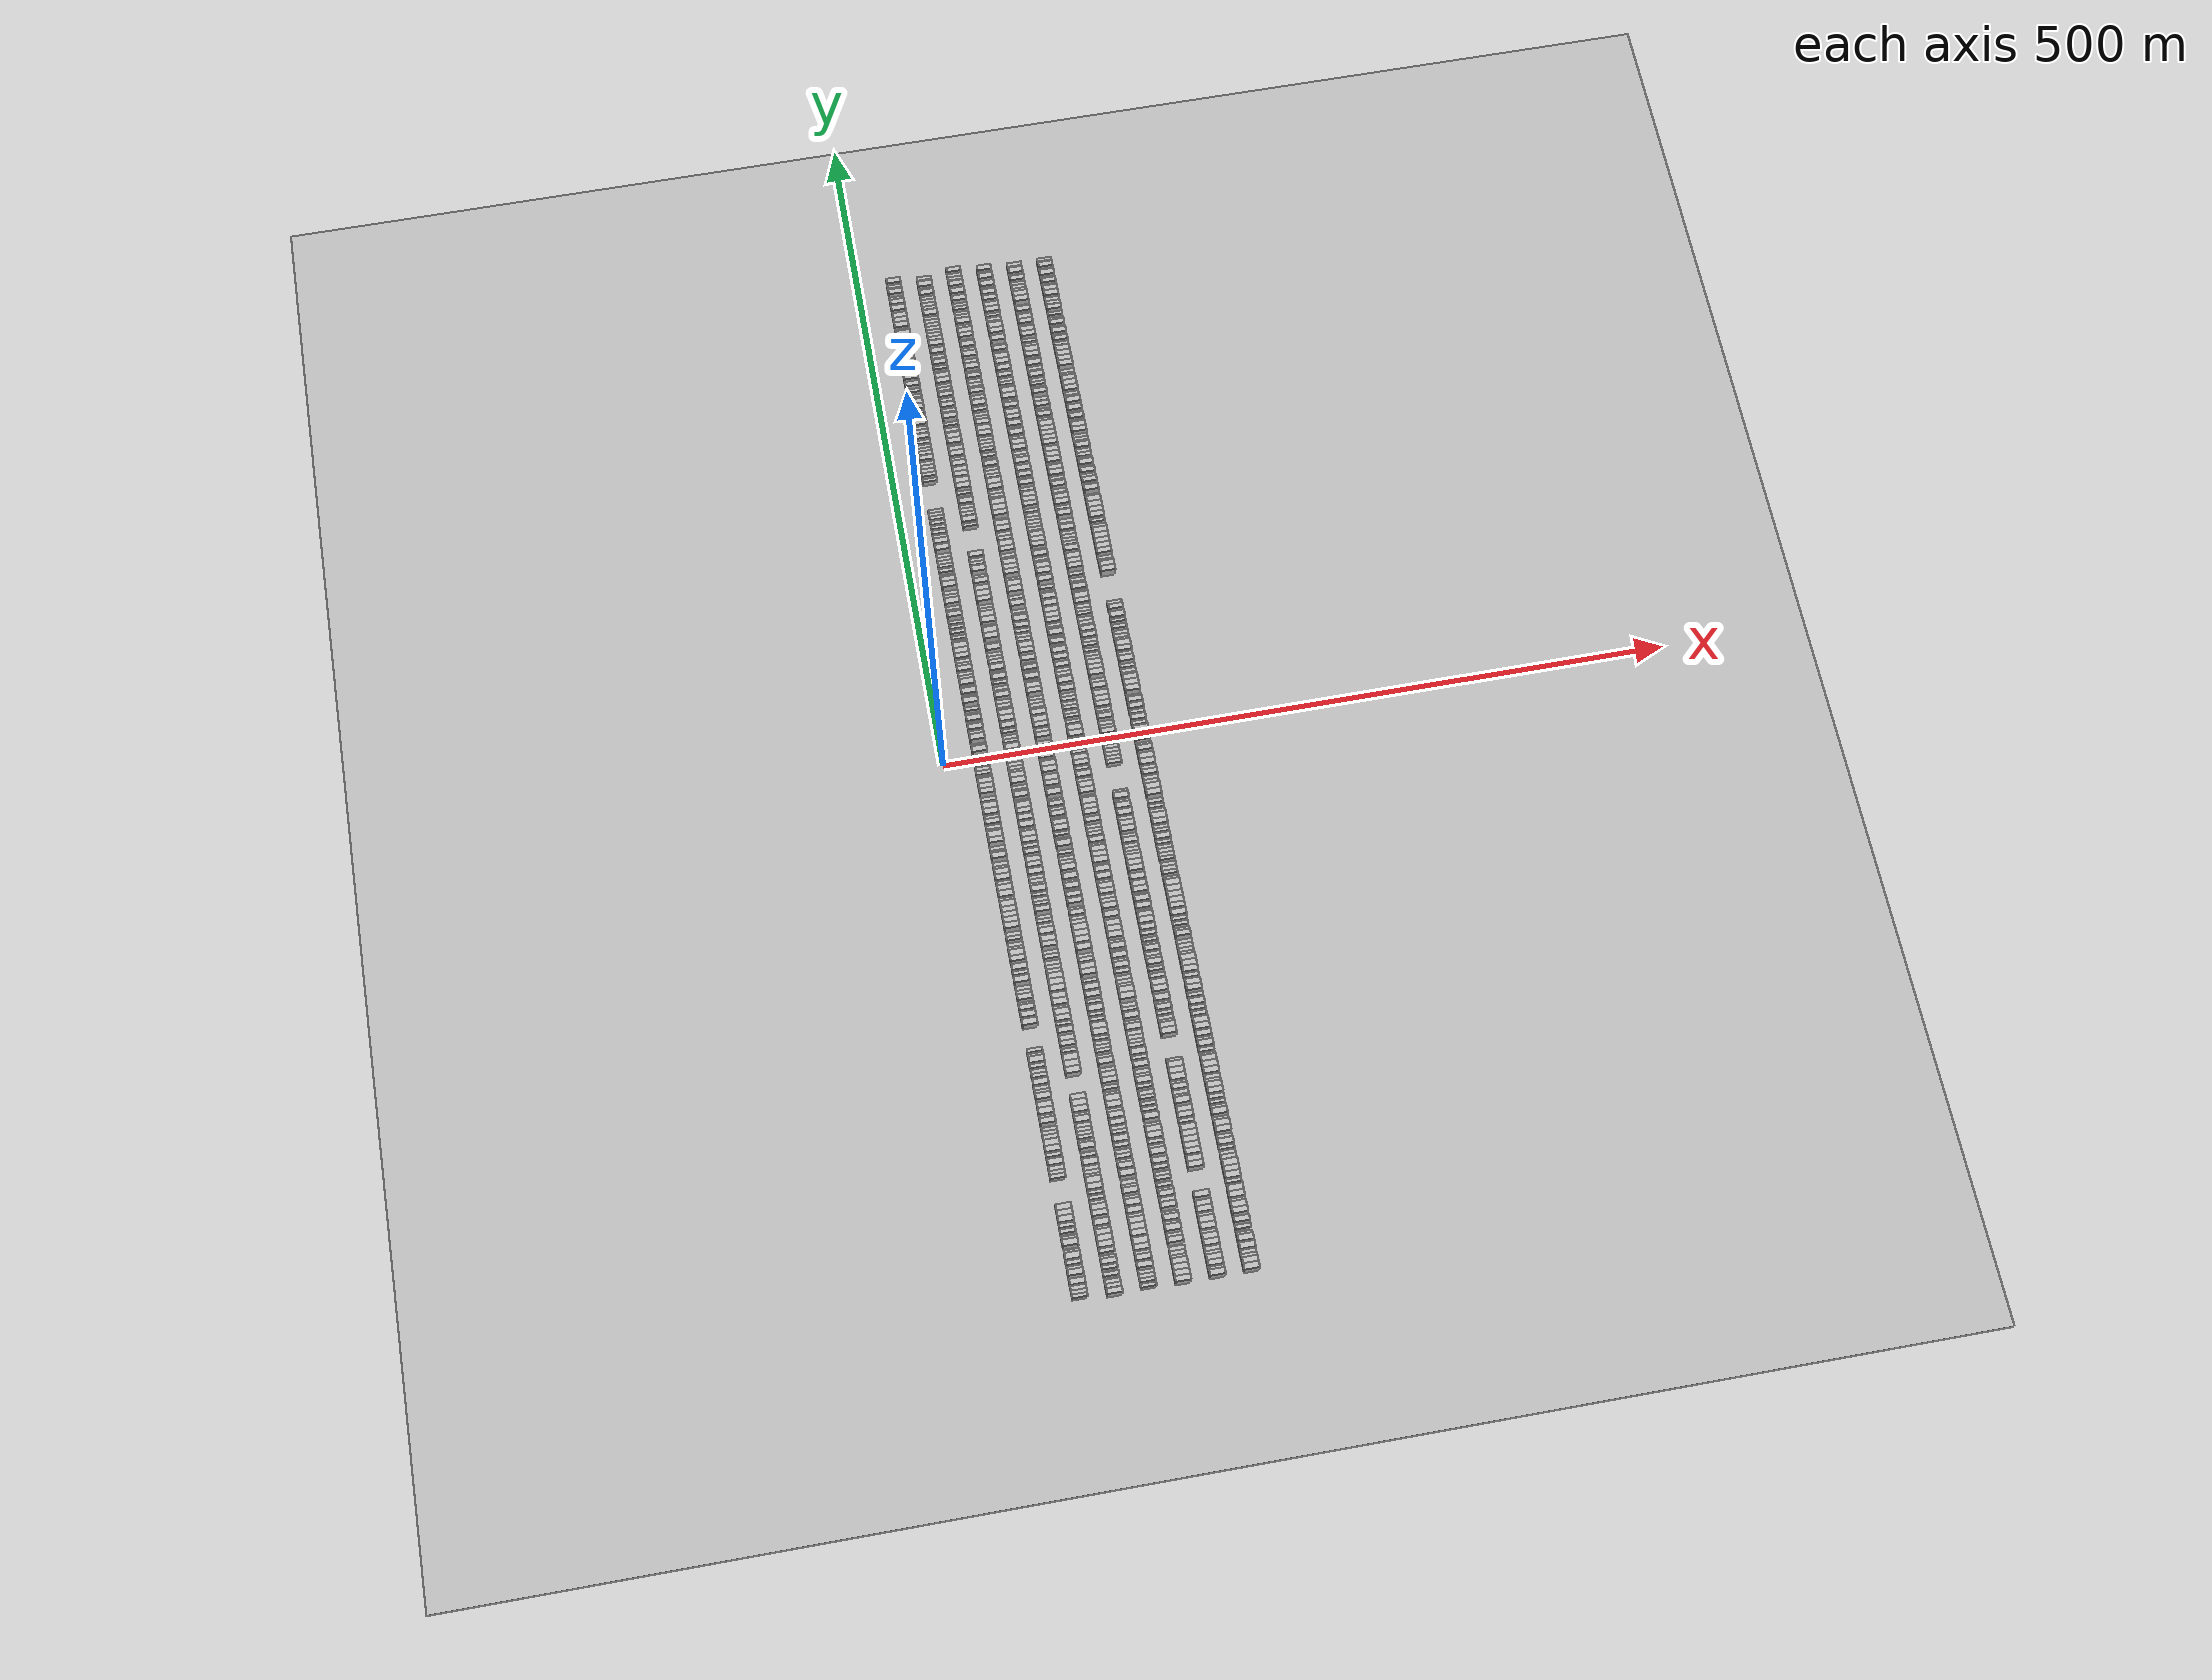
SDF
<?xml version="1.0" encoding="utf-8"?>

<sdf version="1.6">

   <world name="default">

      <gui fullscreen="0">

         <camera name="user_camera">

            <pose>-15 0 4.57585 0 0 0</pose>

            <view_controller>orbit</view_controller>

         </camera>

      </gui>

      <scene>

         <sky>

           <clouds>

             <speed>12</speed>

           </clouds>

         </sky>

         <ambient>0.4 0.4 0.4 1</ambient>

         <background>0.7 0.7 0.7 1</background>

         <shadows>1</shadows>

      </scene>

      <gravity>0 0 -9.8066</gravity>

      <magnetic_field>6e-06 2.3e-05 -4.2e-05</magnetic_field>

      <physics default="0" name="default_physics" type="ode">

         <ode>

            <solver>

               <type>quick</type>

               <iters>10</iters>

               <sor>1.0</sor>

               <use_dynamic_moi_rescaling>0</use_dynamic_moi_rescaling>

            </solver>

            <constraints>

               <cfm>0</cfm>

               <erp>0.2</erp>

               <contact_max_correcting_vel>100</contact_max_correcting_vel>

               <contact_surface_layer>0.001</contact_surface_layer>

            </constraints>

         </ode>

         <max_step_size>0.004</max_step_size>

         <real_time_factor>1</real_time_factor>

         <real_time_update_rate>250</real_time_update_rate>

      </physics>

      <light name="sun" type="directional">

         <cast_shadows>1</cast_shadows>

         <pose>0 0 10 0 0 0</pose>

         <diffuse>0.8 0.8 0.8 1</diffuse>

         <specular>0.2 0.2 0.2 1</specular>

         <attenuation>

            <range>1000</range>

            <constant>0.9</constant>

            <linear>0.01</linear>

            <quadratic>0.001</quadratic>

         </attenuation>

         <direction>-0.5 0.1 -0.9</direction>

      </light>

      <include>

         <name>ground_plane_1</name>

         <uri>model://HANNAS_ground_plane</uri>

         <pose>0 0 0  0 0 0</pose>

      </include>

      <include>

         <name>ground_plane_2</name>

         <uri>model://HANNAS_ground_plane</uri>

         <pose>100 0 0  0 0 0</pose>

      </include>

      <model name="building_1">

         <static>1</static>

         <pose frame="">25.0000 -376.7795 0 0.000000 0.000000 0.000000</pose>

         <link name="link">

            <pose frame="">0 0 3.00 0 0 0</pose>

            <collision name="collision">

               <geometry>

                  <box>

                     <size>10.0000 2.4410 6.0000</size>

                  </box>

               </geometry>

               <max_contacts>10</max_contacts>

               <surface>

                  <contact>

                     <ode/>

                  </contact>

                  <bounce/>

                  <friction>

                     <torsional>

                        <ode/>

                     </torsional>

                     <ode/>

                  </friction>

               </surface>

            </collision>

            <visual name="visual">

               <cast_shadows>0</cast_shadows>

               <geometry>

                  <box>

                     <size>10.0000 2.4410 6.0000</size>

                  </box>

               </geometry>

               <material>

                  <script>

                     <uri>model://HANNAS_wall/materials/scripts</uri>

                     <uri>model://HANNAS_wall/materials/textures</uri>

                     <name>vrc/HANNAS_wall</name>

                  </script>

               </material>

            </visual>

            <self_collide>0</self_collide>

            <enable_wind>0</enable_wind>

            <kinematic>0</kinematic>

         </link>

      </model>

      <model name="building_2">

         <static>1</static>

         <pose frame="">25.0000 -374.2593 0 0.000000 0.000000 0.000000</pose>

         <link name="link">

            <pose frame="">0 0 3.00 0 0 0</pose>

            <collision name="collision">

               <geometry>

                  <box>

                     <size>10.0000 2.5993 6.0000</size>

                  </box>

               </geometry>

               <max_contacts>10</max_contacts>

               <surface>

                  <contact>

                     <ode/>

                  </contact>

                  <bounce/>

                  <friction>

                     <torsional>

                        <ode/>

                     </torsional>

                     <ode/>

                  </friction>

               </surface>

            </collision>

            <visual name="visual">

               <cast_shadows>0</cast_shadows>

               <geometry>

                  <box>

                     <size>10.0000 2.5993 6.0000</size>

                  </box>

               </geometry>

               <material>

                  <script>

                     <uri>model://HANNAS_wall/materials/scripts</uri>

                     <uri>model://HANNAS_wall/materials/textures</uri>

                     <name>vrc/HANNAS_wall</name>

                  </script>

               </material>

            </visual>

            <self_collide>0</self_collide>

            <enable_wind>0</enable_wind>

            <kinematic>0</kinematic>

         </link>

      </model>

      <model name="building_3">

         <static>1</static>

         <pose frame="">25.0000 -371.4876 0 0.000000 0.000000 0.000000</pose>

         <link name="link">

            <pose frame="">0 0 3.00 0 0 0</pose>

            <collision name="collision">

               <geometry>

                  <box>

                     <size>10.0000 2.9440 6.0000</size>

                  </box>

               </geometry>

               <max_contacts>10</max_contacts>

               <surface>

                  <contact>

                     <ode/>

                  </contact>

                  <bounce/>

                  <friction>

                     <torsional>

                        <ode/>

                     </torsional>

                     <ode/>

                  </friction>

               </surface>

            </collision>

            <visual name="visual">

               <cast_shadows>0</cast_shadows>

               <geometry>

                  <box>

                     <size>10.0000 2.9440 6.0000</size>

                  </box>

               </geometry>

               <material>

                  <script>

                     <uri>model://HANNAS_wall/materials/scripts</uri>

                     <uri>model://HANNAS_wall/materials/textures</uri>

                     <name>vrc/HANNAS_wall</name>

                  </script>

               </material>

            </visual>

            <self_collide>0</self_collide>

            <enable_wind>0</enable_wind>

            <kinematic>0</kinematic>

         </link>

      </model>

      <model name="building_4">

         <static>1</static>

         <pose frame="">25.0000 -368.0420 0 0.000000 0.000000 0.000000</pose>

         <link name="link">

            <pose frame="">0 0 4.50 0 0 0</pose>

            <collision name="collision">

               <geometry>

                  <box>

                     <size>10.0000 3.9472 9.0000</size>

                  </box>

               </geometry>

               <max_contacts>10</max_contacts>

               <surface>

                  <contact>

                     <ode/>

                  </contact>

                  <bounce/>

                  <friction>

                     <torsional>

                        <ode/>

                     </torsional>

                     <ode/>

                  </friction>

               </surface>

            </collision>

            <visual name="visual">

               <cast_shadows>0</cast_shadows>

               <geometry>

                  <box>

                     <size>10.0000 3.9472 9.0000</size>

                  </box>

               </geometry>

               <material>

                  <script>

                     <uri>model://HANNAS_wall/materials/scripts</uri>

                     <uri>model://HANNAS_wall/materials/textures</uri>

                     <name>vrc/HANNAS_wall</name>

                  </script>

               </material>

            </visual>

            <self_collide>0</self_collide>

            <enable_wind>0</enable_wind>

            <kinematic>0</kinematic>

         </link>

      </model>

      <model name="building_5">

         <static>1</static>

         <pose frame="">25.0000 -362.0885 0 0.000000 0.000000 0.000000</pose>

         <link name="link">

            <pose frame="">0 0 4.50 0 0 0</pose>

            <collision name="collision">

               <geometry>

                  <box>

                     <size>10.0000 3.9597 9.0000</size>

                  </box>

               </geometry>

               <max_contacts>10</max_contacts>

               <surface>

                  <contact>

                     <ode/>

                  </contact>

                  <bounce/>

                  <friction>

                     <torsional>

                        <ode/>

                     </torsional>

                     <ode/>

                  </friction>

               </surface>

            </collision>

            <visual name="visual">

               <cast_shadows>0</cast_shadows>

               <geometry>

                  <box>

                     <size>10.0000 3.9597 9.0000</size>

                  </box>

               </geometry>

               <material>

                  <script>

                     <uri>model://HANNAS_wall/materials/scripts</uri>

                     <uri>model://HANNAS_wall/materials/textures</uri>

                     <name>vrc/HANNAS_wall</name>

                  </script>

               </material>

            </visual>

            <self_collide>0</self_collide>

            <enable_wind>0</enable_wind>

            <kinematic>0</kinematic>

         </link>

      </model>

      <model name="building_6">

         <static>1</static>

         <pose frame="">25.0000 -358.7314 0 0.000000 0.000000 0.000000</pose>

         <link name="link">

            <pose frame="">0 0 3.00 0 0 0</pose>

            <collision name="collision">

               <geometry>

                  <box>

                     <size>10.0000 2.7545 6.0000</size>

                  </box>

               </geometry>

               <max_contacts>10</max_contacts>

               <surface>

                  <contact>

                     <ode/>

                  </contact>

                  <bounce/>

                  <friction>

                     <torsional>

                        <ode/>

                     </torsional>

                     <ode/>

                  </friction>

               </surface>

            </collision>

            <visual name="visual">

               <cast_shadows>0</cast_shadows>

               <geometry>

                  <box>

                     <size>10.0000 2.7545 6.0000</size>

                  </box>

               </geometry>

               <material>

                  <script>

                     <uri>model://HANNAS_wall/materials/scripts</uri>

                     <uri>model://HANNAS_wall/materials/textures</uri>

                     <name>vrc/HANNAS_wall</name>

                  </script>

               </material>

            </visual>

            <self_collide>0</self_collide>

            <enable_wind>0</enable_wind>

            <kinematic>0</kinematic>

         </link>

      </model>

      <model name="building_7">

         <static>1</static>

         <pose frame="">25.0000 -354.9093 0 0.000000 0.000000 0.000000</pose>

         <link name="link">

            <pose frame="">0 0 3.00 0 0 0</pose>

            <collision name="collision">

               <geometry>

                  <box>

                     <size>10.0000 2.8897 6.0000</size>

                  </box>

               </geometry>

               <max_contacts>10</max_contacts>

               <surface>

                  <contact>

                     <ode/>

                  </contact>

                  <bounce/>

                  <friction>

                     <torsional>

                        <ode/>

                     </torsional>

                     <ode/>

                  </friction>

               </surface>

            </collision>

            <visual name="visual">

               <cast_shadows>0</cast_shadows>

               <geometry>

                  <box>

                     <size>10.0000 2.8897 6.0000</size>

                  </box>

               </geometry>

               <material>

                  <script>

                     <uri>model://HANNAS_wall/materials/scripts</uri>

                     <uri>model://HANNAS_wall/materials/textures</uri>

                     <name>vrc/HANNAS_wall</name>

                  </script>

               </material>

            </visual>

            <self_collide>0</self_collide>

            <enable_wind>0</enable_wind>

            <kinematic>0</kinematic>

         </link>

      </model>

      <model name="building_8">

         <static>1</static>

         <pose frame="">25.0000 -351.2400 0 0.000000 0.000000 0.000000</pose>

         <link name="link">

            <pose frame="">0 0 4.50 0 0 0</pose>

            <collision name="collision">

               <geometry>

                  <box>

                     <size>10.0000 4.4490 9.0000</size>

                  </box>

               </geometry>

               <max_contacts>10</max_contacts>

               <surface>

                  <contact>

                     <ode/>

                  </contact>

                  <bounce/>

                  <friction>

                     <torsional>

                        <ode/>

                     </torsional>

                     <ode/>

                  </friction>

               </surface>

            </collision>

            <visual name="visual">

               <cast_shadows>0</cast_shadows>

               <geometry>

                  <box>

                     <size>10.0000 4.4490 9.0000</size>

                  </box>

               </geometry>

               <material>

                  <script>

                     <uri>model://HANNAS_wall/materials/scripts</uri>

                     <uri>model://HANNAS_wall/materials/textures</uri>

                     <name>vrc/HANNAS_wall</name>

                  </script>

               </material>

            </visual>

            <self_collide>0</self_collide>

            <enable_wind>0</enable_wind>

            <kinematic>0</kinematic>

         </link>

      </model>

      <model name="building_9">

         <static>1</static>

         <pose frame="">25.0000 -347.8144 0 0.000000 0.000000 0.000000</pose>

         <link name="link">

            <pose frame="">0 0 3.00 0 0 0</pose>

            <collision name="collision">

               <geometry>

                  <box>

                     <size>10.0000 2.4022 6.0000</size>

                  </box>

               </geometry>

               <max_contacts>10</max_contacts>

               <surface>

                  <contact>

                     <ode/>

                  </contact>

                  <bounce/>

                  <friction>

                     <torsional>

                        <ode/>

                     </torsional>

                     <ode/>

                  </friction>

               </surface>

            </collision>

            <visual name="visual">

               <cast_shadows>0</cast_shadows>

               <geometry>

                  <box>

                     <size>10.0000 2.4022 6.0000</size>

                  </box>

               </geometry>

               <material>

                  <script>

                     <uri>model://HANNAS_wall/materials/scripts</uri>

                     <uri>model://HANNAS_wall/materials/textures</uri>

                     <name>vrc/HANNAS_wall</name>

                  </script>

               </material>

            </visual>

            <self_collide>0</self_collide>

            <enable_wind>0</enable_wind>

            <kinematic>0</kinematic>

         </link>

      </model>

      <model name="building_10">

         <static>1</static>

         <pose frame="">25.0000 -342.4051 0 0.000000 0.000000 0.000000</pose>

         <link name="link">

            <pose frame="">0 0 4.50 0 0 0</pose>

            <collision name="collision">

               <geometry>

                  <box>

                     <size>10.0000 4.4166 9.0000</size>

                  </box>

               </geometry>

               <max_contacts>10</max_contacts>

               <surface>

                  <contact>

                     <ode/>

                  </contact>

                  <bounce/>

                  <friction>

                     <torsional>

                        <ode/>

                     </torsional>

                     <ode/>

                  </friction>

               </surface>

            </collision>

            <visual name="visual">

               <cast_shadows>0</cast_shadows>

               <geometry>

                  <box>

                     <size>10.0000 4.4166 9.0000</size>

                  </box>

               </geometry>

               <material>

                  <script>

                     <uri>model://HANNAS_wall/materials/scripts</uri>

                     <uri>model://HANNAS_wall/materials/textures</uri>

                     <name>vrc/HANNAS_wall</name>

                  </script>

               </material>

            </visual>

            <self_collide>0</self_collide>

            <enable_wind>0</enable_wind>

            <kinematic>0</kinematic>

         </link>

      </model>

      <model name="building_11">

         <static>1</static>

         <pose frame="">25.0000 -338.8746 0 0.000000 0.000000 0.000000</pose>

         <link name="link">

            <pose frame="">0 0 3.00 0 0 0</pose>

            <collision name="collision">

               <geometry>

                  <box>

                     <size>10.0000 2.6444 6.0000</size>

                  </box>

               </geometry>

               <max_contacts>10</max_contacts>

               <surface>

                  <contact>

                     <ode/>

                  </contact>

                  <bounce/>

                  <friction>

                     <torsional>

                        <ode/>

                     </torsional>

                     <ode/>

                  </friction>

               </surface>

            </collision>

            <visual name="visual">

               <cast_shadows>0</cast_shadows>

               <geometry>

                  <box>

                     <size>10.0000 2.6444 6.0000</size>

                  </box>

               </geometry>

               <material>

                  <script>

                     <uri>model://HANNAS_wall/materials/scripts</uri>

                     <uri>model://HANNAS_wall/materials/textures</uri>

                     <name>vrc/HANNAS_wall</name>

                  </script>

               </material>

            </visual>

            <self_collide>0</self_collide>

            <enable_wind>0</enable_wind>

            <kinematic>0</kinematic>

         </link>

      </model>

      <model name="building_12">

         <static>1</static>

         <pose frame="">25.0000 -334.1689 0 0.000000 0.000000 0.000000</pose>

         <link name="link">

            <pose frame="">0 0 3.00 0 0 0</pose>

            <collision name="collision">

               <geometry>

                  <box>

                     <size>10.0000 2.7669 6.0000</size>

                  </box>

               </geometry>

               <max_contacts>10</max_contacts>

               <surface>

                  <contact>

                     <ode/>

                  </contact>

                  <bounce/>

                  <friction>

                     <torsional>

                        <ode/>

                     </torsional>

                     <ode/>

                  </friction>

               </surface>

            </collision>

            <visual name="visual">

               <cast_shadows>0</cast_shadows>

               <geometry>

                  <box>

                     <size>10.0000 2.7669 6.0000</size>

                  </box>

               </geometry>

               <material>

                  <script>

                     <uri>model://HANNAS_wall/materials/scripts</uri>

                     <uri>model://HANNAS_wall/materials/textures</uri>

                     <name>vrc/HANNAS_wall</name>

                  </script>

               </material>

            </visual>

            <self_collide>0</self_collide>

            <enable_wind>0</enable_wind>

            <kinematic>0</kinematic>

         </link>

      </model>

      <model name="building_13">

         <static>1</static>

         <pose frame="">25.0000 -330.3850 0 0.000000 0.000000 0.000000</pose>

         <link name="link">

            <pose frame="">0 0 3.00 0 0 0</pose>

            <collision name="collision">

               <geometry>

                  <box>

                     <size>10.0000 2.8009 6.0000</size>

                  </box>

               </geometry>

               <max_contacts>10</max_contacts>

               <surface>

                  <contact>

                     <ode/>

                  </contact>

                  <bounce/>

                  <friction>

                     <torsional>

                        <ode/>

                     </torsional>

                     <ode/>

                  </friction>

               </surface>

            </collision>

            <visual name="visual">

               <cast_shadows>0</cast_shadows>

               <geometry>

                  <box>

                     <size>10.0000 2.8009 6.0000</size>

                  </box>

               </geometry>

               <material>

                  <script>

                     <uri>model://HANNAS_wall/materials/scripts</uri>

                     <uri>model://HANNAS_wall/materials/textures</uri>

                     <name>vrc/HANNAS_wall</name>

                  </script>

               </material>

            </visual>

            <self_collide>0</self_collide>

            <enable_wind>0</enable_wind>

            <kinematic>0</kinematic>

         </link>

      </model>

      <model name="building_14">

         <static>1</static>

         <pose frame="">25.0000 -326.8384 0 0.000000 0.000000 0.000000</pose>

         <link name="link">

            <pose frame="">0 0 4.50 0 0 0</pose>

            <collision name="collision">

               <geometry>

                  <box>

                     <size>10.0000 4.2923 9.0000</size>

                  </box>

               </geometry>

               <max_contacts>10</max_contacts>

               <surface>

                  <contact>

                     <ode/>

                  </contact>

                  <bounce/>

                  <friction>

                     <torsional>

                        <ode/>

                     </torsional>

                     <ode/>

                  </friction>

               </surface>

            </collision>

            <visual name="visual">

               <cast_shadows>0</cast_shadows>

               <geometry>

                  <box>

                     <size>10.0000 4.2923 9.0000</size>

                  </box>

               </geometry>

               <material>

                  <script>

                     <uri>model://HANNAS_wall/materials/scripts</uri>

                     <uri>model://HANNAS_wall/materials/textures</uri>

                     <name>vrc/HANNAS_wall</name>

                  </script>

               </material>

            </visual>

            <self_collide>0</self_collide>

            <enable_wind>0</enable_wind>

            <kinematic>0</kinematic>

         </link>

      </model>

      <model name="building_15">

         <static>1</static>

         <pose frame="">25.0000 -322.8135 0 0.000000 0.000000 0.000000</pose>

         <link name="link">

            <pose frame="">0 0 4.50 0 0 0</pose>

            <collision name="collision">

               <geometry>

                  <box>

                     <size>10.0000 3.7576 9.0000</size>

                  </box>

               </geometry>

               <max_contacts>10</max_contacts>

               <surface>

                  <contact>

                     <ode/>

                  </contact>

                  <bounce/>

                  <friction>

                     <torsional>

                        <ode/>

                     </torsional>

                     <ode/>

                  </friction>

               </surface>

            </collision>

            <visual name="visual">

               <cast_shadows>0</cast_shadows>

               <geometry>

                  <box>

                     <size>10.0000 3.7576 9.0000</size>

                  </box>

               </geometry>

               <material>

                  <script>

                     <uri>model://HANNAS_wall/materials/scripts</uri>

                     <uri>model://HANNAS_wall/materials/textures</uri>

                     <name>vrc/HANNAS_wall</name>

                  </script>

               </material>

            </visual>

            <self_collide>0</self_collide>

            <enable_wind>0</enable_wind>

            <kinematic>0</kinematic>

         </link>

      </model>

      <model name="building_16">

         <static>1</static>

         <pose frame="">25.0000 -318.9065 0 0.000000 0.000000 0.000000</pose>

         <link name="link">

            <pose frame="">0 0 4.50 0 0 0</pose>

            <collision name="collision">

               <geometry>

                  <box>

                     <size>10.0000 4.0564 9.0000</size>

                  </box>

               </geometry>

               <max_contacts>10</max_contacts>

               <surface>

                  <contact>

                     <ode/>

                  </contact>

                  <bounce/>

                  <friction>

                     <torsional>

                        <ode/>

                     </torsional>

                     <ode/>

                  </friction>

               </surface>

            </collision>

            <visual name="visual">

               <cast_shadows>0</cast_shadows>

               <geometry>

                  <box>

                     <size>10.0000 4.0564 9.0000</size>

                  </box>

               </geometry>

               <material>

                  <script>

                     <uri>model://HANNAS_wall/materials/scripts</uri>

                     <uri>model://HANNAS_wall/materials/textures</uri>

                     <name>vrc/HANNAS_wall</name>

                  </script>

               </material>

            </visual>

            <self_collide>0</self_collide>

            <enable_wind>0</enable_wind>

            <kinematic>0</kinematic>

         </link>

      </model>

      <model name="building_17">

         <static>1</static>

         <pose frame="">25.0000 -297.6133 0 0.000000 0.000000 0.000000</pose>

         <link name="link">

            <pose frame="">0 0 3.00 0 0 0</pose>

            <collision name="collision">

               <geometry>

                  <box>

                     <size>10.0000 2.8433 6.0000</size>

                  </box>

               </geometry>

               <max_contacts>10</max_contacts>

               <surface>

                  <contact>

                     <ode/>

                  </contact>

                  <bounce/>

                  <friction>

                     <torsional>

                        <ode/>

                     </torsional>

                     <ode/>

                  </friction>

               </surface>

            </collision>

            <visual name="visual">

               <cast_shadows>0</cast_shadows>

               <geometry>

                  <box>

                     <size>10.0000 2.8433 6.0000</size>

                  </box>

               </geometry>

               <material>

                  <script>

                     <uri>model://HANNAS_wall/materials/scripts</uri>

                     <uri>model://HANNAS_wall/materials/textures</uri>

                     <name>vrc/HANNAS_wall</name>

                  </script>

               </material>

            </visual>

            <self_collide>0</self_collide>

            <enable_wind>0</enable_wind>

            <kinematic>0</kinematic>

         </link>

      </model>

      <model name="building_18">

         <static>1</static>

         <pose frame="">25.0000 -294.9142 0 0.000000 0.000000 0.000000</pose>

         <link name="link">

            <pose frame="">0 0 3.00 0 0 0</pose>

            <collision name="collision">

               <geometry>

                  <box>

                     <size>10.0000 2.5547 6.0000</size>

                  </box>

               </geometry>

               <max_contacts>10</max_contacts>

               <surface>

                  <contact>

                     <ode/>

                  </contact>

                  <bounce/>

                  <friction>

                     <torsional>

                        <ode/>

                     </torsional>

                     <ode/>

                  </friction>

               </surface>

            </collision>

            <visual name="visual">

               <cast_shadows>0</cast_shadows>

               <geometry>

                  <box>

                     <size>10.0000 2.5547 6.0000</size>

                  </box>

               </geometry>

               <material>

                  <script>

                     <uri>model://HANNAS_wall/materials/scripts</uri>

                     <uri>model://HANNAS_wall/materials/textures</uri>

                     <name>vrc/HANNAS_wall</name>

                  </script>

               </material>

            </visual>

            <self_collide>0</self_collide>

            <enable_wind>0</enable_wind>

            <kinematic>0</kinematic>

         </link>

      </model>

      <model name="building_19">

         <static>1</static>

         <pose frame="">25.0000 -292.1656 0 0.000000 0.000000 0.000000</pose>

         <link name="link">

            <pose frame="">0 0 3.00 0 0 0</pose>

            <collision name="collision">

               <geometry>

                  <box>

                     <size>10.0000 2.9425 6.0000</size>

                  </box>

               </geometry>

               <max_contacts>10</max_contacts>

               <surface>

                  <contact>

                     <ode/>

                  </contact>

                  <bounce/>

                  <friction>

                     <torsional>

                        <ode/>

                     </torsional>

                     <ode/>

                  </friction>

               </surface>

            </collision>

            <visual name="visual">

               <cast_shadows>0</cast_shadows>

               <geometry>

                  <box>

                     <size>10.0000 2.9425 6.0000</size>

                  </box>

               </geometry>

               <material>

                  <script>

                     <uri>model://HANNAS_wall/materials/scripts</uri>

                     <uri>model://HANNAS_wall/materials/textures</uri>

                     <name>vrc/HANNAS_wall</name>

                  </script>

               </material>

            </visual>

            <self_collide>0</self_collide>

            <enable_wind>0</enable_wind>

            <kinematic>0</kinematic>

         </link>

      </model>

      <model name="building_20">

         <static>1</static>

         <pose frame="">25.0000 -288.5497 0 0.000000 0.000000 0.000000</pose>

         <link name="link">

            <pose frame="">0 0 4.50 0 0 0</pose>

            <collision name="collision">

               <geometry>

                  <box>

                     <size>10.0000 4.2895 9.0000</size>

                  </box>

               </geometry>

               <max_contacts>10</max_contacts>

               <surface>

                  <contact>

                     <ode/>

                  </contact>

                  <bounce/>

                  <friction>

                     <torsional>

                        <ode/>

                     </torsional>

                     <ode/>

                  </friction>

               </surface>

            </collision>

            <visual name="visual">

               <cast_shadows>0</cast_shadows>

               <geometry>

                  <box>

                     <size>10.0000 4.2895 9.0000</size>

                  </box>

               </geometry>

               <material>

                  <script>

                     <uri>model://HANNAS_wall/materials/scripts</uri>

                     <uri>model://HANNAS_wall/materials/textures</uri>

                     <name>vrc/HANNAS_wall</name>

                  </script>

               </material>

            </visual>

            <self_collide>0</self_collide>

            <enable_wind>0</enable_wind>

            <kinematic>0</kinematic>

         </link>

      </model>

      <model name="building_21">

         <static>1</static>

         <pose frame="">25.0000 -283.0830 0 0.000000 0.000000 0.000000</pose>

         <link name="link">

            <pose frame="">0 0 3.00 0 0 0</pose>

            <collision name="collision">

               <geometry>

                  <box>

                     <size>10.0000 2.6439 6.0000</size>

                  </box>

               </geometry>

               <max_contacts>10</max_contacts>

               <surface>

                  <contact>

                     <ode/>

                  </contact>

                  <bounce/>

                  <friction>

                     <torsional>

                        <ode/>

                     </torsional>

                     <ode/>

                  </friction>

               </surface>

            </collision>

            <visual name="visual">

               <cast_shadows>0</cast_shadows>

               <geometry>

                  <box>

                     <size>10.0000 2.6439 6.0000</size>

                  </box>

               </geometry>

               <material>

                  <script>

                     <uri>model://HANNAS_wall/materials/scripts</uri>

                     <uri>model://HANNAS_wall/materials/textures</uri>

                     <name>vrc/HANNAS_wall</name>

                  </script>

               </material>

            </visual>

            <self_collide>0</self_collide>

            <enable_wind>0</enable_wind>

            <kinematic>0</kinematic>

         </link>

      </model>

      <model name="building_22">

         <static>1</static>

         <pose frame="">25.0000 -279.7261 0 0.000000 0.000000 0.000000</pose>

         <link name="link">

            <pose frame="">0 0 4.50 0 0 0</pose>

            <collision name="collision">

               <geometry>

                  <box>

                     <size>10.0000 4.0698 9.0000</size>

                  </box>

               </geometry>

               <max_contacts>10</max_contacts>

               <surface>

                  <contact>

                     <ode/>

                  </contact>

                  <bounce/>

                  <friction>

                     <torsional>

                        <ode/>

                     </torsional>

                     <ode/>

                  </friction>

               </surface>

            </collision>

            <visual name="visual">

               <cast_shadows>0</cast_shadows>

               <geometry>

                  <box>

                     <size>10.0000 4.0698 9.0000</size>

                  </box>

               </geometry>

               <material>

                  <script>

                     <uri>model://HANNAS_wall/materials/scripts</uri>

                     <uri>model://HANNAS_wall/materials/textures</uri>

                     <name>vrc/HANNAS_wall</name>

                  </script>

               </material>

            </visual>

            <self_collide>0</self_collide>

            <enable_wind>0</enable_wind>

            <kinematic>0</kinematic>

         </link>

      </model>

      <model name="building_23">

         <static>1</static>

         <pose frame="">25.0000 -275.5629 0 0.000000 0.000000 0.000000</pose>

         <link name="link">

            <pose frame="">0 0 4.50 0 0 0</pose>

            <collision name="collision">

               <geometry>

                  <box>

                     <size>10.0000 4.2568 9.0000</size>

                  </box>

               </geometry>

               <max_contacts>10</max_contacts>

               <surface>

                  <contact>

                     <ode/>

                  </contact>

                  <bounce/>

                  <friction>

                     <torsional>

                        <ode/>

                     </torsional>

                     <ode/>

                  </friction>

               </surface>

            </collision>

            <visual name="visual">

               <cast_shadows>0</cast_shadows>

               <geometry>

                  <box>

                     <size>10.0000 4.2568 9.0000</size>

                  </box>

               </geometry>

               <material>

                  <script>

                     <uri>model://HANNAS_wall/materials/scripts</uri>

                     <uri>model://HANNAS_wall/materials/textures</uri>

                     <name>vrc/HANNAS_wall</name>

                  </script>

               </material>

            </visual>

            <self_collide>0</self_collide>

            <enable_wind>0</enable_wind>

            <kinematic>0</kinematic>

         </link>

      </model>

      <model name="building_24">

         <static>1</static>

         <pose frame="">25.0000 -270.9674 0 0.000000 0.000000 0.000000</pose>

         <link name="link">

            <pose frame="">0 0 3.00 0 0 0</pose>

            <collision name="collision">

               <geometry>

                  <box>

                     <size>10.0000 2.9342 6.0000</size>

                  </box>

               </geometry>

               <max_contacts>10</max_contacts>

               <surface>

                  <contact>

                     <ode/>

                  </contact>

                  <bounce/>

                  <friction>

                     <torsional>

                        <ode/>

                     </torsional>

                     <ode/>

                  </friction>

               </surface>

            </collision>

            <visual name="visual">

               <cast_shadows>0</cast_shadows>

               <geometry>

                  <box>

                     <size>10.0000 2.9342 6.0000</size>

                  </box>

               </geometry>

               <material>

                  <script>

                     <uri>model://HANNAS_wall/materials/scripts</uri>

                     <uri>model://HANNAS_wall/materials/textures</uri>

                     <name>vrc/HANNAS_wall</name>

                  </script>

               </material>

            </visual>

            <self_collide>0</self_collide>

            <enable_wind>0</enable_wind>

            <kinematic>0</kinematic>

         </link>

      </model>

      <model name="building_25">

         <static>1</static>

         <pose frame="">25.0000 -268.2369 0 0.000000 0.000000 0.000000</pose>

         <link name="link">

            <pose frame="">0 0 3.00 0 0 0</pose>

            <collision name="collision">

               <geometry>

                  <box>

                     <size>10.0000 2.5267 6.0000</size>

                  </box>

               </geometry>

               <max_contacts>10</max_contacts>

               <surface>

                  <contact>

                     <ode/>

                  </contact>

                  <bounce/>

                  <friction>

                     <torsional>

                        <ode/>

                     </torsional>

                     <ode/>

                  </friction>

               </surface>

            </collision>

            <visual name="visual">

               <cast_shadows>0</cast_shadows>

               <geometry>

                  <box>

                     <size>10.0000 2.5267 6.0000</size>

                  </box>

               </geometry>

               <material>

                  <script>

                     <uri>model://HANNAS_wall/materials/scripts</uri>

                     <uri>model://HANNAS_wall/materials/textures</uri>

                     <name>vrc/HANNAS_wall</name>

                  </script>

               </material>

            </visual>

            <self_collide>0</self_collide>

            <enable_wind>0</enable_wind>

            <kinematic>0</kinematic>

         </link>

      </model>

      <model name="building_26">

         <static>1</static>

         <pose frame="">25.0000 -265.7701 0 0.000000 0.000000 0.000000</pose>

         <link name="link">

            <pose frame="">0 0 3.00 0 0 0</pose>

            <collision name="collision">

               <geometry>

                  <box>

                     <size>10.0000 2.4069 6.0000</size>

                  </box>

               </geometry>

               <max_contacts>10</max_contacts>

               <surface>

                  <contact>

                     <ode/>

                  </contact>

                  <bounce/>

                  <friction>

                     <torsional>

                        <ode/>

                     </torsional>

                     <ode/>

                  </friction>

               </surface>

            </collision>

            <visual name="visual">

               <cast_shadows>0</cast_shadows>

               <geometry>

                  <box>

                     <size>10.0000 2.4069 6.0000</size>

                  </box>

               </geometry>

               <material>

                  <script>

                     <uri>model://HANNAS_wall/materials/scripts</uri>

                     <uri>model://HANNAS_wall/materials/textures</uri>

                     <name>vrc/HANNAS_wall</name>

                  </script>

               </material>

            </visual>

            <self_collide>0</self_collide>

            <enable_wind>0</enable_wind>

            <kinematic>0</kinematic>

         </link>

      </model>

      <model name="building_27">

         <static>1</static>

         <pose frame="">25.0000 -260.6648 0 0.000000 0.000000 0.000000</pose>

         <link name="link">

            <pose frame="">0 0 4.50 0 0 0</pose>

            <collision name="collision">

               <geometry>

                  <box>

                     <size>10.0000 3.8037 9.0000</size>

                  </box>

               </geometry>

               <max_contacts>10</max_contacts>

               <surface>

                  <contact>

                     <ode/>

                  </contact>

                  <bounce/>

                  <friction>

                     <torsional>

                        <ode/>

                     </torsional>

                     <ode/>

                  </friction>

               </surface>

            </collision>

            <visual name="visual">

               <cast_shadows>0</cast_shadows>

               <geometry>

                  <box>

                     <size>10.0000 3.8037 9.0000</size>

                  </box>

               </geometry>

               <material>

                  <script>

                     <uri>model://HANNAS_wall/materials/scripts</uri>

                     <uri>model://HANNAS_wall/materials/textures</uri>

                     <name>vrc/HANNAS_wall</name>

                  </script>

               </material>

            </visual>

            <self_collide>0</self_collide>

            <enable_wind>0</enable_wind>

            <kinematic>0</kinematic>

         </link>

      </model>

      <model name="building_28">

         <static>1</static>

         <pose frame="">25.0000 -257.4445 0 0.000000 0.000000 0.000000</pose>

         <link name="link">

            <pose frame="">0 0 3.00 0 0 0</pose>

            <collision name="collision">

               <geometry>

                  <box>

                     <size>10.0000 2.6370 6.0000</size>

                  </box>

               </geometry>

               <max_contacts>10</max_contacts>

               <surface>

                  <contact>

                     <ode/>

                  </contact>

                  <bounce/>

                  <friction>

                     <torsional>

                        <ode/>

                     </torsional>

                     <ode/>

                  </friction>

               </surface>

            </collision>

            <visual name="visual">

               <cast_shadows>0</cast_shadows>

               <geometry>

                  <box>

                     <size>10.0000 2.6370 6.0000</size>

                  </box>

               </geometry>

               <material>

                  <script>

                     <uri>model://HANNAS_wall/materials/scripts</uri>

                     <uri>model://HANNAS_wall/materials/textures</uri>

                     <name>vrc/HANNAS_wall</name>

                  </script>

               </material>

            </visual>

            <self_collide>0</self_collide>

            <enable_wind>0</enable_wind>

            <kinematic>0</kinematic>

         </link>

      </model>

      <model name="building_29">

         <static>1</static>

         <pose frame="">25.0000 -253.9353 0 0.000000 0.000000 0.000000</pose>

         <link name="link">

            <pose frame="">0 0 4.50 0 0 0</pose>

            <collision name="collision">

               <geometry>

                  <box>

                     <size>10.0000 4.3814 9.0000</size>

                  </box>

               </geometry>

               <max_contacts>10</max_contacts>

               <surface>

                  <contact>

                     <ode/>

                  </contact>

                  <bounce/>

                  <friction>

                     <torsional>

                        <ode/>

                     </torsional>

                     <ode/>

                  </friction>

               </surface>

            </collision>

            <visual name="visual">

               <cast_shadows>0</cast_shadows>

               <geometry>

                  <box>

                     <size>10.0000 4.3814 9.0000</size>

                  </box>

               </geometry>

               <material>

                  <script>

                     <uri>model://HANNAS_wall/materials/scripts</uri>

                     <uri>model://HANNAS_wall/materials/textures</uri>

                     <name>vrc/HANNAS_wall</name>

                  </script>

               </material>

            </visual>

            <self_collide>0</self_collide>

            <enable_wind>0</enable_wind>

            <kinematic>0</kinematic>

         </link>

      </model>

      <model name="building_30">

         <static>1</static>

         <pose frame="">25.0000 -249.8173 0 0.000000 0.000000 0.000000</pose>

         <link name="link">

            <pose frame="">0 0 4.50 0 0 0</pose>

            <collision name="collision">

               <geometry>

                  <box>

                     <size>10.0000 3.8545 9.0000</size>

                  </box>

               </geometry>

               <max_contacts>10</max_contacts>

               <surface>

                  <contact>

                     <ode/>

                  </contact>

                  <bounce/>

                  <friction>

                     <torsional>

                        <ode/>

                     </torsional>

                     <ode/>

                  </friction>

               </surface>

            </collision>

            <visual name="visual">

               <cast_shadows>0</cast_shadows>

               <geometry>

                  <box>

                     <size>10.0000 3.8545 9.0000</size>

                  </box>

               </geometry>

               <material>

                  <script>

                     <uri>model://HANNAS_wall/materials/scripts</uri>

                     <uri>model://HANNAS_wall/materials/textures</uri>

                     <name>vrc/HANNAS_wall</name>

                  </script>

               </material>

            </visual>

            <self_collide>0</self_collide>

            <enable_wind>0</enable_wind>

            <kinematic>0</kinematic>

         </link>

      </model>

      <model name="building_31">

         <static>1</static>

         <pose frame="">25.0000 -243.8248 0 0.000000 0.000000 0.000000</pose>

         <link name="link">

            <pose frame="">0 0 4.50 0 0 0</pose>

            <collision name="collision">

               <geometry>

                  <box>

                     <size>10.0000 4.1305 9.0000</size>

                  </box>

               </geometry>

               <max_contacts>10</max_contacts>

               <surface>

                  <contact>

                     <ode/>

                  </contact>

                  <bounce/>

                  <friction>

                     <torsional>

                        <ode/>

                     </torsional>

                     <ode/>

                  </friction>

               </surface>

            </collision>

            <visual name="visual">

               <cast_shadows>0</cast_shadows>

               <geometry>

                  <box>

                     <size>10.0000 4.1305 9.0000</size>

                  </box>

               </geometry>

               <material>

                  <script>

                     <uri>model://HANNAS_wall/materials/scripts</uri>

                     <uri>model://HANNAS_wall/materials/textures</uri>

                     <name>vrc/HANNAS_wall</name>

                  </script>

               </material>

            </visual>

            <self_collide>0</self_collide>

            <enable_wind>0</enable_wind>

            <kinematic>0</kinematic>

         </link>

      </model>

      <model name="building_32">

         <static>1</static>

         <pose frame="">25.0000 -240.3034 0 0.000000 0.000000 0.000000</pose>

         <link name="link">

            <pose frame="">0 0 3.00 0 0 0</pose>

            <collision name="collision">

               <geometry>

                  <box>

                     <size>10.0000 2.9122 6.0000</size>

                  </box>

               </geometry>

               <max_contacts>10</max_contacts>

               <surface>

                  <contact>

                     <ode/>

                  </contact>

                  <bounce/>

                  <friction>

                     <torsional>

                        <ode/>

                     </torsional>

                     <ode/>

                  </friction>

               </surface>

            </collision>

            <visual name="visual">

               <cast_shadows>0</cast_shadows>

               <geometry>

                  <box>

                     <size>10.0000 2.9122 6.0000</size>

                  </box>

               </geometry>

               <material>

                  <script>

                     <uri>model://HANNAS_wall/materials/scripts</uri>

                     <uri>model://HANNAS_wall/materials/textures</uri>

                     <name>vrc/HANNAS_wall</name>

                  </script>

               </material>

            </visual>

            <self_collide>0</self_collide>

            <enable_wind>0</enable_wind>

            <kinematic>0</kinematic>

         </link>

      </model>

      <model name="building_33">

         <static>1</static>

         <pose frame="">25.0000 -237.5339 0 0.000000 0.000000 0.000000</pose>

         <link name="link">

            <pose frame="">0 0 3.00 0 0 0</pose>

            <collision name="collision">

               <geometry>

                  <box>

                     <size>10.0000 2.6268 6.0000</size>

                  </box>

               </geometry>

               <max_contacts>10</max_contacts>

               <surface>

                  <contact>

                     <ode/>

                  </contact>

                  <bounce/>

                  <friction>

                     <torsional>

                        <ode/>

                     </torsional>

                     <ode/>

                  </friction>

               </surface>

            </collision>

            <visual name="visual">

               <cast_shadows>0</cast_shadows>

               <geometry>

                  <box>

                     <size>10.0000 2.6268 6.0000</size>

                  </box>

               </geometry>

               <material>

                  <script>

                     <uri>model://HANNAS_wall/materials/scripts</uri>

                     <uri>model://HANNAS_wall/materials/textures</uri>

                     <name>vrc/HANNAS_wall</name>

                  </script>

               </material>

            </visual>

            <self_collide>0</self_collide>

            <enable_wind>0</enable_wind>

            <kinematic>0</kinematic>

         </link>

      </model>

      <model name="building_34">

         <static>1</static>

         <pose frame="">25.0000 -234.1885 0 0.000000 0.000000 0.000000</pose>

         <link name="link">

            <pose frame="">0 0 4.50 0 0 0</pose>

            <collision name="collision">

               <geometry>

                  <box>

                     <size>10.0000 4.0640 9.0000</size>

                  </box>

               </geometry>

               <max_contacts>10</max_contacts>

               <surface>

                  <contact>

                     <ode/>

                  </contact>

                  <bounce/>

                  <friction>

                     <torsional>

                        <ode/>

                     </torsional>

                     <ode/>

                  </friction>

               </surface>

            </collision>

            <visual name="visual">

               <cast_shadows>0</cast_shadows>

               <geometry>

                  <box>

                     <size>10.0000 4.0640 9.0000</size>

                  </box>

               </geometry>

               <material>

                  <script>

                     <uri>model://HANNAS_wall/materials/scripts</uri>

                     <uri>model://HANNAS_wall/materials/textures</uri>

                     <name>vrc/HANNAS_wall</name>

                  </script>

               </material>

            </visual>

            <self_collide>0</self_collide>

            <enable_wind>0</enable_wind>

            <kinematic>0</kinematic>

         </link>

      </model>

      <model name="building_35">

         <static>1</static>

         <pose frame="">25.0000 -228.8128 0 0.000000 0.000000 0.000000</pose>

         <link name="link">

            <pose frame="">0 0 3.00 0 0 0</pose>

            <collision name="collision">

               <geometry>

                  <box>

                     <size>10.0000 2.6874 6.0000</size>

                  </box>

               </geometry>

               <max_contacts>10</max_contacts>

               <surface>

                  <contact>

                     <ode/>

                  </contact>

                  <bounce/>

                  <friction>

                     <torsional>

                        <ode/>

                     </torsional>

                     <ode/>

                  </friction>

               </surface>

            </collision>

            <visual name="visual">

               <cast_shadows>0</cast_shadows>

               <geometry>

                  <box>

                     <size>10.0000 2.6874 6.0000</size>

                  </box>

               </geometry>

               <material>

                  <script>

                     <uri>model://HANNAS_wall/materials/scripts</uri>

                     <uri>model://HANNAS_wall/materials/textures</uri>

                     <name>vrc/HANNAS_wall</name>

                  </script>

               </material>

            </visual>

            <self_collide>0</self_collide>

            <enable_wind>0</enable_wind>

            <kinematic>0</kinematic>

         </link>

      </model>

      <model name="building_36">

         <static>1</static>

         <pose frame="">25.0000 -226.0762 0 0.000000 0.000000 0.000000</pose>

         <link name="link">

            <pose frame="">0 0 3.00 0 0 0</pose>

            <collision name="collision">

               <geometry>

                  <box>

                     <size>10.0000 2.7858 6.0000</size>

                  </box>

               </geometry>

               <max_contacts>10</max_contacts>

               <surface>

                  <contact>

                     <ode/>

                  </contact>

                  <bounce/>

                  <friction>

                     <torsional>

                        <ode/>

                     </torsional>

                     <ode/>

                  </friction>

               </surface>

            </collision>

            <visual name="visual">

               <cast_shadows>0</cast_shadows>

               <geometry>

                  <box>

                     <size>10.0000 2.7858 6.0000</size>

                  </box>

               </geometry>

               <material>

                  <script>

                     <uri>model://HANNAS_wall/materials/scripts</uri>

                     <uri>model://HANNAS_wall/materials/textures</uri>

                     <name>vrc/HANNAS_wall</name>

                  </script>

               </material>

            </visual>

            <self_collide>0</self_collide>

            <enable_wind>0</enable_wind>

            <kinematic>0</kinematic>

         </link>

      </model>

      <model name="building_37">

         <static>1</static>

         <pose frame="">25.0000 -222.2542 0 0.000000 0.000000 0.000000</pose>

         <link name="link">

            <pose frame="">0 0 3.00 0 0 0</pose>

            <collision name="collision">

               <geometry>

                  <box>

                     <size>10.0000 2.8583 6.0000</size>

                  </box>

               </geometry>

               <max_contacts>10</max_contacts>

               <surface>

                  <contact>

                     <ode/>

                  </contact>

                  <bounce/>

                  <friction>

                     <torsional>

                        <ode/>

                     </torsional>

                     <ode/>

                  </friction>

               </surface>

            </collision>

            <visual name="visual">

               <cast_shadows>0</cast_shadows>

               <geometry>

                  <box>

                     <size>10.0000 2.8583 6.0000</size>

                  </box>

               </geometry>

               <material>

                  <script>

                     <uri>model://HANNAS_wall/materials/scripts</uri>

                     <uri>model://HANNAS_wall/materials/textures</uri>

                     <name>vrc/HANNAS_wall</name>

                  </script>

               </material>

            </visual>

            <self_collide>0</self_collide>

            <enable_wind>0</enable_wind>

            <kinematic>0</kinematic>

         </link>

      </model>

      <model name="building_38">

         <static>1</static>

         <pose frame="">25.0000 -218.6741 0 0.000000 0.000000 0.000000</pose>

         <link name="link">

            <pose frame="">0 0 4.50 0 0 0</pose>

            <collision name="collision">

               <geometry>

                  <box>

                     <size>10.0000 4.3018 9.0000</size>

                  </box>

               </geometry>

               <max_contacts>10</max_contacts>

               <surface>

                  <contact>

                     <ode/>

                  </contact>

                  <bounce/>

                  <friction>

                     <torsional>

                        <ode/>

                     </torsional>

                     <ode/>

                  </friction>

               </surface>

            </collision>

            <visual name="visual">

               <cast_shadows>0</cast_shadows>

               <geometry>

                  <box>

                     <size>10.0000 4.3018 9.0000</size>

                  </box>

               </geometry>

               <material>

                  <script>

                     <uri>model://HANNAS_wall/materials/scripts</uri>

                     <uri>model://HANNAS_wall/materials/textures</uri>

                     <name>vrc/HANNAS_wall</name>

                  </script>

               </material>

            </visual>

            <self_collide>0</self_collide>

            <enable_wind>0</enable_wind>

            <kinematic>0</kinematic>

         </link>

      </model>

      <model name="building_39">

         <static>1</static>

         <pose frame="">25.0000 -215.1681 0 0.000000 0.000000 0.000000</pose>

         <link name="link">

            <pose frame="">0 0 3.00 0 0 0</pose>

            <collision name="collision">

               <geometry>

                  <box>

                     <size>10.0000 2.7103 6.0000</size>

                  </box>

               </geometry>

               <max_contacts>10</max_contacts>

               <surface>

                  <contact>

                     <ode/>

                  </contact>

                  <bounce/>

                  <friction>

                     <torsional>

                        <ode/>

                     </torsional>

                     <ode/>

                  </friction>

               </surface>

            </collision>

            <visual name="visual">

               <cast_shadows>0</cast_shadows>

               <geometry>

                  <box>

                     <size>10.0000 2.7103 6.0000</size>

                  </box>

               </geometry>

               <material>

                  <script>

                     <uri>model://HANNAS_wall/materials/scripts</uri>

                     <uri>model://HANNAS_wall/materials/textures</uri>

                     <name>vrc/HANNAS_wall</name>

                  </script>

               </material>

            </visual>

            <self_collide>0</self_collide>

            <enable_wind>0</enable_wind>

            <kinematic>0</kinematic>

         </link>

      </model>

      <model name="building_40">

         <static>1</static>

         <pose frame="">25.0000 -211.4827 0 0.000000 0.000000 0.000000</pose>

         <link name="link">

            <pose frame="">0 0 3.00 0 0 0</pose>

            <collision name="collision">

               <geometry>

                  <box>

                     <size>10.0000 2.6604 6.0000</size>

                  </box>

               </geometry>

               <max_contacts>10</max_contacts>

               <surface>

                  <contact>

                     <ode/>

                  </contact>

                  <bounce/>

                  <friction>

                     <torsional>

                        <ode/>

                     </torsional>

                     <ode/>

                  </friction>

               </surface>

            </collision>

            <visual name="visual">

               <cast_shadows>0</cast_shadows>

               <geometry>

                  <box>

                     <size>10.0000 2.6604 6.0000</size>

                  </box>

               </geometry>

               <material>

                  <script>

                     <uri>model://HANNAS_wall/materials/scripts</uri>

                     <uri>model://HANNAS_wall/materials/textures</uri>

                     <name>vrc/HANNAS_wall</name>

                  </script>

               </material>

            </visual>

            <self_collide>0</self_collide>

            <enable_wind>0</enable_wind>

            <kinematic>0</kinematic>

         </link>

      </model>

      <model name="building_41">

         <static>1</static>

         <pose frame="">25.0000 -192.4512 0 0.000000 0.000000 0.000000</pose>

         <link name="link">

            <pose frame="">0 0 4.50 0 0 0</pose>

            <collision name="collision">

               <geometry>

                  <box>

                     <size>10.0000 4.4676 9.0000</size>

                  </box>

               </geometry>

               <max_contacts>10</max_contacts>

               <surface>

                  <contact>

                     <ode/>

                  </contact>

                  <bounce/>

                  <friction>

                     <torsional>

                        <ode/>

                     </torsional>

                     <ode/>

                  </friction>

               </surface>

            </collision>

            <visual name="visual">

               <cast_shadows>0</cast_shadows>

               <geometry>

                  <box>

                     <size>10.0000 4.4676 9.0000</size>

                  </box>

               </geometry>

               <material>

                  <script>

                     <uri>model://HANNAS_wall/materials/scripts</uri>

                     <uri>model://HANNAS_wall/materials/textures</uri>

                     <name>vrc/HANNAS_wall</name>

                  </script>

               </material>

            </visual>

            <self_collide>0</self_collide>

            <enable_wind>0</enable_wind>

            <kinematic>0</kinematic>

         </link>

      </model>

      <model name="building_42">

         <static>1</static>

         <pose frame="">25.0000 -187.1826 0 0.000000 0.000000 0.000000</pose>

         <link name="link">

            <pose frame="">0 0 4.50 0 0 0</pose>

            <collision name="collision">

               <geometry>

                  <box>

                     <size>10.0000 4.0695 9.0000</size>

                  </box>

               </geometry>

               <max_contacts>10</max_contacts>

               <surface>

                  <contact>

                     <ode/>

                  </contact>

                  <bounce/>

                  <friction>

                     <torsional>

                        <ode/>

                     </torsional>

                     <ode/>

                  </friction>

               </surface>

            </collision>

            <visual name="visual">

               <cast_shadows>0</cast_shadows>

               <geometry>

                  <box>

                     <size>10.0000 4.0695 9.0000</size>

                  </box>

               </geometry>

               <material>

                  <script>

                     <uri>model://HANNAS_wall/materials/scripts</uri>

                     <uri>model://HANNAS_wall/materials/textures</uri>

                     <name>vrc/HANNAS_wall</name>

                  </script>

               </material>

            </visual>

            <self_collide>0</self_collide>

            <enable_wind>0</enable_wind>

            <kinematic>0</kinematic>

         </link>

      </model>

      <model name="building_43">

         <static>1</static>

         <pose frame="">25.0000 -182.3148 0 0.000000 0.000000 0.000000</pose>

         <link name="link">

            <pose frame="">0 0 4.50 0 0 0</pose>

            <collision name="collision">

               <geometry>

                  <box>

                     <size>10.0000 3.6661 9.0000</size>

                  </box>

               </geometry>

               <max_contacts>10</max_contacts>

               <surface>

                  <contact>

                     <ode/>

                  </contact>

                  <bounce/>

                  <friction>

                     <torsional>

                        <ode/>

                     </torsional>

                     <ode/>

                  </friction>

               </surface>

            </collision>

            <visual name="visual">

               <cast_shadows>0</cast_shadows>

               <geometry>

                  <box>

                     <size>10.0000 3.6661 9.0000</size>

                  </box>

               </geometry>

               <material>

                  <script>

                     <uri>model://HANNAS_wall/materials/scripts</uri>

                     <uri>model://HANNAS_wall/materials/textures</uri>

                     <name>vrc/HANNAS_wall</name>

                  </script>

               </material>

            </visual>

            <self_collide>0</self_collide>

            <enable_wind>0</enable_wind>

            <kinematic>0</kinematic>

         </link>

      </model>

      <model name="building_44">

         <static>1</static>

         <pose frame="">25.0000 -179.2464 0 0.000000 0.000000 0.000000</pose>

         <link name="link">

            <pose frame="">0 0 3.00 0 0 0</pose>

            <collision name="collision">

               <geometry>

                  <box>

                     <size>10.0000 2.4708 6.0000</size>

                  </box>

               </geometry>

               <max_contacts>10</max_contacts>

               <surface>

                  <contact>

                     <ode/>

                  </contact>

                  <bounce/>

                  <friction>

                     <torsional>

                        <ode/>

                     </torsional>

                     <ode/>

                  </friction>

               </surface>

            </collision>

            <visual name="visual">

               <cast_shadows>0</cast_shadows>

               <geometry>

                  <box>

                     <size>10.0000 2.4708 6.0000</size>

                  </box>

               </geometry>

               <material>

                  <script>

                     <uri>model://HANNAS_wall/materials/scripts</uri>

                     <uri>model://HANNAS_wall/materials/textures</uri>

                     <name>vrc/HANNAS_wall</name>

                  </script>

               </material>

            </visual>

            <self_collide>0</self_collide>

            <enable_wind>0</enable_wind>

            <kinematic>0</kinematic>

         </link>

      </model>

      <model name="building_45">

         <static>1</static>

         <pose frame="">25.0000 -175.0655 0 0.000000 0.000000 0.000000</pose>

         <link name="link">

            <pose frame="">0 0 4.50 0 0 0</pose>

            <collision name="collision">

               <geometry>

                  <box>

                     <size>10.0000 3.8910 9.0000</size>

                  </box>

               </geometry>

               <max_contacts>10</max_contacts>

               <surface>

                  <contact>

                     <ode/>

                  </contact>

                  <bounce/>

                  <friction>

                     <torsional>

                        <ode/>

                     </torsional>

                     <ode/>

                  </friction>

               </surface>

            </collision>

            <visual name="visual">

               <cast_shadows>0</cast_shadows>

               <geometry>

                  <box>

                     <size>10.0000 3.8910 9.0000</size>

                  </box>

               </geometry>

               <material>

                  <script>

                     <uri>model://HANNAS_wall/materials/scripts</uri>

                     <uri>model://HANNAS_wall/materials/textures</uri>

                     <name>vrc/HANNAS_wall</name>

                  </script>

               </material>

            </visual>

            <self_collide>0</self_collide>

            <enable_wind>0</enable_wind>

            <kinematic>0</kinematic>

         </link>

      </model>

      <model name="building_46">

         <static>1</static>

         <pose frame="">25.0000 -170.7973 0 0.000000 0.000000 0.000000</pose>

         <link name="link">

            <pose frame="">0 0 3.00 0 0 0</pose>

            <collision name="collision">

               <geometry>

                  <box>

                     <size>10.0000 2.6455 6.0000</size>

                  </box>

               </geometry>

               <max_contacts>10</max_contacts>

               <surface>

                  <contact>

                     <ode/>

                  </contact>

                  <bounce/>

                  <friction>

                     <torsional>

                        <ode/>

                     </torsional>

                     <ode/>

                  </friction>

               </surface>

            </collision>

            <visual name="visual">

               <cast_shadows>0</cast_shadows>

               <geometry>

                  <box>

                     <size>10.0000 2.6455 6.0000</size>

                  </box>

               </geometry>

               <material>

                  <script>

                     <uri>model://HANNAS_wall/materials/scripts</uri>

                     <uri>model://HANNAS_wall/materials/textures</uri>

                     <name>vrc/HANNAS_wall</name>

                  </script>

               </material>

            </visual>

            <self_collide>0</self_collide>

            <enable_wind>0</enable_wind>

            <kinematic>0</kinematic>

         </link>

      </model>

      <model name="building_47">

         <static>1</static>

         <pose frame="">25.0000 -168.0712 0 0.000000 0.000000 0.000000</pose>

         <link name="link">

            <pose frame="">0 0 3.00 0 0 0</pose>

            <collision name="collision">

               <geometry>

                  <box>

                     <size>10.0000 2.8067 6.0000</size>

                  </box>

               </geometry>

               <max_contacts>10</max_contacts>

               <surface>

                  <contact>

                     <ode/>

                  </contact>

                  <bounce/>

                  <friction>

                     <torsional>

                        <ode/>

                     </torsional>

                     <ode/>

                  </friction>

               </surface>

            </collision>

            <visual name="visual">

               <cast_shadows>0</cast_shadows>

               <geometry>

                  <box>

                     <size>10.0000 2.8067 6.0000</size>

                  </box>

               </geometry>

               <material>

                  <script>

                     <uri>model://HANNAS_wall/materials/scripts</uri>

                     <uri>model://HANNAS_wall/materials/textures</uri>

                     <name>vrc/HANNAS_wall</name>

                  </script>

               </material>

            </visual>

            <self_collide>0</self_collide>

            <enable_wind>0</enable_wind>

            <kinematic>0</kinematic>

         </link>

      </model>

      <model name="building_48">

         <static>1</static>

         <pose frame="">25.0000 -162.5393 0 0.000000 0.000000 0.000000</pose>

         <link name="link">

            <pose frame="">0 0 4.50 0 0 0</pose>

            <collision name="collision">

               <geometry>

                  <box>

                     <size>10.0000 4.2570 9.0000</size>

                  </box>

               </geometry>

               <max_contacts>10</max_contacts>

               <surface>

                  <contact>

                     <ode/>

                  </contact>

                  <bounce/>

                  <friction>

                     <torsional>

                        <ode/>

                     </torsional>

                     <ode/>

                  </friction>

               </surface>

            </collision>

            <visual name="visual">

               <cast_shadows>0</cast_shadows>

               <geometry>

                  <box>

                     <size>10.0000 4.2570 9.0000</size>

                  </box>

               </geometry>

               <material>

                  <script>

                     <uri>model://HANNAS_wall/materials/scripts</uri>

                     <uri>model://HANNAS_wall/materials/textures</uri>

                     <name>vrc/HANNAS_wall</name>

                  </script>

               </material>

            </visual>

            <self_collide>0</self_collide>

            <enable_wind>0</enable_wind>

            <kinematic>0</kinematic>

         </link>

      </model>

      <model name="building_49">

         <static>1</static>

         <pose frame="">25.0000 -157.0925 0 0.000000 0.000000 0.000000</pose>

         <link name="link">

            <pose frame="">0 0 3.00 0 0 0</pose>

            <collision name="collision">

               <geometry>

                  <box>

                     <size>10.0000 2.6367 6.0000</size>

                  </box>

               </geometry>

               <max_contacts>10</max_contacts>

               <surface>

                  <contact>

                     <ode/>

                  </contact>

                  <bounce/>

                  <friction>

                     <torsional>

                        <ode/>

                     </torsional>

                     <ode/>

                  </friction>

               </surface>

            </collision>

            <visual name="visual">

               <cast_shadows>0</cast_shadows>

               <geometry>

                  <box>

                     <size>10.0000 2.6367 6.0000</size>

                  </box>

               </geometry>

               <material>

                  <script>

                     <uri>model://HANNAS_wall/materials/scripts</uri>

                     <uri>model://HANNAS_wall/materials/textures</uri>

                     <name>vrc/HANNAS_wall</name>

                  </script>

               </material>

            </visual>

            <self_collide>0</self_collide>

            <enable_wind>0</enable_wind>

            <kinematic>0</kinematic>

         </link>

      </model>

      <model name="building_50">

         <static>1</static>

         <pose frame="">25.0000 -153.7104 0 0.000000 0.000000 0.000000</pose>

         <link name="link">

            <pose frame="">0 0 4.50 0 0 0</pose>

            <collision name="collision">

               <geometry>

                  <box>

                     <size>10.0000 4.1275 9.0000</size>

                  </box>

               </geometry>

               <max_contacts>10</max_contacts>

               <surface>

                  <contact>

                     <ode/>

                  </contact>

                  <bounce/>

                  <friction>

                     <torsional>

                        <ode/>

                     </torsional>

                     <ode/>

                  </friction>

               </surface>

            </collision>

            <visual name="visual">

               <cast_shadows>0</cast_shadows>

               <geometry>

                  <box>

                     <size>10.0000 4.1275 9.0000</size>

                  </box>

               </geometry>

               <material>

                  <script>

                     <uri>model://HANNAS_wall/materials/scripts</uri>

                     <uri>model://HANNAS_wall/materials/textures</uri>

                     <name>vrc/HANNAS_wall</name>

                  </script>

               </material>

            </visual>

            <self_collide>0</self_collide>

            <enable_wind>0</enable_wind>

            <kinematic>0</kinematic>

         </link>

      </model>

      <model name="building_51">

         <static>1</static>

         <pose frame="">25.0000 -147.7489 0 0.000000 0.000000 0.000000</pose>

         <link name="link">

            <pose frame="">0 0 4.50 0 0 0</pose>

            <collision name="collision">

               <geometry>

                  <box>

                     <size>10.0000 3.7956 9.0000</size>

                  </box>

               </geometry>

               <max_contacts>10</max_contacts>

               <surface>

                  <contact>

                     <ode/>

                  </contact>

                  <bounce/>

                  <friction>

                     <torsional>

                        <ode/>

                     </torsional>

                     <ode/>

                  </friction>

               </surface>

            </collision>

            <visual name="visual">

               <cast_shadows>0</cast_shadows>

               <geometry>

                  <box>

                     <size>10.0000 3.7956 9.0000</size>

                  </box>

               </geometry>

               <material>

                  <script>

                     <uri>model://HANNAS_wall/materials/scripts</uri>

                     <uri>model://HANNAS_wall/materials/textures</uri>

                     <name>vrc/HANNAS_wall</name>

                  </script>

               </material>

            </visual>

            <self_collide>0</self_collide>

            <enable_wind>0</enable_wind>

            <kinematic>0</kinematic>

         </link>

      </model>

      <model name="building_52">

         <static>1</static>

         <pose frame="">25.0000 -143.6865 0 0.000000 0.000000 0.000000</pose>

         <link name="link">

            <pose frame="">0 0 4.50 0 0 0</pose>

            <collision name="collision">

               <geometry>

                  <box>

                     <size>10.0000 4.3292 9.0000</size>

                  </box>

               </geometry>

               <max_contacts>10</max_contacts>

               <surface>

                  <contact>

                     <ode/>

                  </contact>

                  <bounce/>

                  <friction>

                     <torsional>

                        <ode/>

                     </torsional>

                     <ode/>

                  </friction>

               </surface>

            </collision>

            <visual name="visual">

               <cast_shadows>0</cast_shadows>

               <geometry>

                  <box>

                     <size>10.0000 4.3292 9.0000</size>

                  </box>

               </geometry>

               <material>

                  <script>

                     <uri>model://HANNAS_wall/materials/scripts</uri>

                     <uri>model://HANNAS_wall/materials/textures</uri>

                     <name>vrc/HANNAS_wall</name>

                  </script>

               </material>

            </visual>

            <self_collide>0</self_collide>

            <enable_wind>0</enable_wind>

            <kinematic>0</kinematic>

         </link>

      </model>

      <model name="building_53">

         <static>1</static>

         <pose frame="">25.0000 -140.0865 0 0.000000 0.000000 0.000000</pose>

         <link name="link">

            <pose frame="">0 0 3.00 0 0 0</pose>

            <collision name="collision">

               <geometry>

                  <box>

                     <size>10.0000 2.8708 6.0000</size>

                  </box>

               </geometry>

               <max_contacts>10</max_contacts>

               <surface>

                  <contact>

                     <ode/>

                  </contact>

                  <bounce/>

                  <friction>

                     <torsional>

                        <ode/>

                     </torsional>

                     <ode/>

                  </friction>

               </surface>

            </collision>

            <visual name="visual">

               <cast_shadows>0</cast_shadows>

               <geometry>

                  <box>

                     <size>10.0000 2.8708 6.0000</size>

                  </box>

               </geometry>

               <material>

                  <script>

                     <uri>model://HANNAS_wall/materials/scripts</uri>

                     <uri>model://HANNAS_wall/materials/textures</uri>

                     <name>vrc/HANNAS_wall</name>

                  </script>

               </material>

            </visual>

            <self_collide>0</self_collide>

            <enable_wind>0</enable_wind>

            <kinematic>0</kinematic>

         </link>

      </model>

      <model name="building_54">

         <static>1</static>

         <pose frame="">25.0000 -137.2738 0 0.000000 0.000000 0.000000</pose>

         <link name="link">

            <pose frame="">0 0 3.00 0 0 0</pose>

            <collision name="collision">

               <geometry>

                  <box>

                     <size>10.0000 2.7546 6.0000</size>

                  </box>

               </geometry>

               <max_contacts>10</max_contacts>

               <surface>

                  <contact>

                     <ode/>

                  </contact>

                  <bounce/>

                  <friction>

                     <torsional>

                        <ode/>

                     </torsional>

                     <ode/>

                  </friction>

               </surface>

            </collision>

            <visual name="visual">

               <cast_shadows>0</cast_shadows>

               <geometry>

                  <box>

                     <size>10.0000 2.7546 6.0000</size>

                  </box>

               </geometry>

               <material>

                  <script>

                     <uri>model://HANNAS_wall/materials/scripts</uri>

                     <uri>model://HANNAS_wall/materials/textures</uri>

                     <name>vrc/HANNAS_wall</name>

                  </script>

               </material>

            </visual>

            <self_collide>0</self_collide>

            <enable_wind>0</enable_wind>

            <kinematic>0</kinematic>

         </link>

      </model>

      <model name="building_55">

         <static>1</static>

         <pose frame="">25.0000 -132.5100 0 0.000000 0.000000 0.000000</pose>

         <link name="link">

            <pose frame="">0 0 3.00 0 0 0</pose>

            <collision name="collision">

               <geometry>

                  <box>

                     <size>10.0000 2.7731 6.0000</size>

                  </box>

               </geometry>

               <max_contacts>10</max_contacts>

               <surface>

                  <contact>

                     <ode/>

                  </contact>

                  <bounce/>

                  <friction>

                     <torsional>

                        <ode/>

                     </torsional>

                     <ode/>

                  </friction>

               </surface>

            </collision>

            <visual name="visual">

               <cast_shadows>0</cast_shadows>

               <geometry>

                  <box>

                     <size>10.0000 2.7731 6.0000</size>

                  </box>

               </geometry>

               <material>

                  <script>

                     <uri>model://HANNAS_wall/materials/scripts</uri>

                     <uri>model://HANNAS_wall/materials/textures</uri>

                     <name>vrc/HANNAS_wall</name>

                  </script>

               </material>

            </visual>

            <self_collide>0</self_collide>

            <enable_wind>0</enable_wind>

            <kinematic>0</kinematic>

         </link>

      </model>

      <model name="building_56">

         <static>1</static>

         <pose frame="">25.0000 -129.6807 0 0.000000 0.000000 0.000000</pose>

         <link name="link">

            <pose frame="">0 0 3.00 0 0 0</pose>

            <collision name="collision">

               <geometry>

                  <box>

                     <size>10.0000 2.8855 6.0000</size>

                  </box>

               </geometry>

               <max_contacts>10</max_contacts>

               <surface>

                  <contact>

                     <ode/>

                  </contact>

                  <bounce/>

                  <friction>

                     <torsional>

                        <ode/>

                     </torsional>

                     <ode/>

                  </friction>

               </surface>

            </collision>

            <visual name="visual">

               <cast_shadows>0</cast_shadows>

               <geometry>

                  <box>

                     <size>10.0000 2.8855 6.0000</size>

                  </box>

               </geometry>

               <material>

                  <script>

                     <uri>model://HANNAS_wall/materials/scripts</uri>

                     <uri>model://HANNAS_wall/materials/textures</uri>

                     <name>vrc/HANNAS_wall</name>

                  </script>

               </material>

            </visual>

            <self_collide>0</self_collide>

            <enable_wind>0</enable_wind>

            <kinematic>0</kinematic>

         </link>

      </model>

      <model name="building_57">

         <static>1</static>

         <pose frame="">25.0000 -124.1645 0 0.000000 0.000000 0.000000</pose>

         <link name="link">

            <pose frame="">0 0 4.50 0 0 0</pose>

            <collision name="collision">

               <geometry>

                  <box>

                     <size>10.0000 4.1467 9.0000</size>

                  </box>

               </geometry>

               <max_contacts>10</max_contacts>

               <surface>

                  <contact>

                     <ode/>

                  </contact>

                  <bounce/>

                  <friction>

                     <torsional>

                        <ode/>

                     </torsional>

                     <ode/>

                  </friction>

               </surface>

            </collision>

            <visual name="visual">

               <cast_shadows>0</cast_shadows>

               <geometry>

                  <box>

                     <size>10.0000 4.1467 9.0000</size>

                  </box>

               </geometry>

               <material>

                  <script>

                     <uri>model://HANNAS_wall/materials/scripts</uri>

                     <uri>model://HANNAS_wall/materials/textures</uri>

                     <name>vrc/HANNAS_wall</name>

                  </script>

               </material>

            </visual>

            <self_collide>0</self_collide>

            <enable_wind>0</enable_wind>

            <kinematic>0</kinematic>

         </link>

      </model>

      <model name="building_58">

         <static>1</static>

         <pose frame="">25.0000 -120.1654 0 0.000000 0.000000 0.000000</pose>

         <link name="link">

            <pose frame="">0 0 4.50 0 0 0</pose>

            <collision name="collision">

               <geometry>

                  <box>

                     <size>10.0000 3.8517 9.0000</size>

                  </box>

               </geometry>

               <max_contacts>10</max_contacts>

               <surface>

                  <contact>

                     <ode/>

                  </contact>

                  <bounce/>

                  <friction>

                     <torsional>

                        <ode/>

                     </torsional>

                     <ode/>

                  </friction>

               </surface>

            </collision>

            <visual name="visual">

               <cast_shadows>0</cast_shadows>

               <geometry>

                  <box>

                     <size>10.0000 3.8517 9.0000</size>

                  </box>

               </geometry>

               <material>

                  <script>

                     <uri>model://HANNAS_wall/materials/scripts</uri>

                     <uri>model://HANNAS_wall/materials/textures</uri>

                     <name>vrc/HANNAS_wall</name>

                  </script>

               </material>

            </visual>

            <self_collide>0</self_collide>

            <enable_wind>0</enable_wind>

            <kinematic>0</kinematic>

         </link>

      </model>

      <model name="building_59">

         <static>1</static>

         <pose frame="">25.0000 -116.4288 0 0.000000 0.000000 0.000000</pose>

         <link name="link">

            <pose frame="">0 0 4.50 0 0 0</pose>

            <collision name="collision">

               <geometry>

                  <box>

                     <size>10.0000 3.6215 9.0000</size>

                  </box>

               </geometry>

               <max_contacts>10</max_contacts>

               <surface>

                  <contact>

                     <ode/>

                  </contact>

                  <bounce/>

                  <friction>

                     <torsional>

                        <ode/>

                     </torsional>

                     <ode/>

                  </friction>

               </surface>

            </collision>

            <visual name="visual">

               <cast_shadows>0</cast_shadows>

               <geometry>

                  <box>

                     <size>10.0000 3.6215 9.0000</size>

                  </box>

               </geometry>

               <material>

                  <script>

                     <uri>model://HANNAS_wall/materials/scripts</uri>

                     <uri>model://HANNAS_wall/materials/textures</uri>

                     <name>vrc/HANNAS_wall</name>

                  </script>

               </material>

            </visual>

            <self_collide>0</self_collide>

            <enable_wind>0</enable_wind>

            <kinematic>0</kinematic>

         </link>

      </model>

      <model name="building_60">

         <static>1</static>

         <pose frame="">25.0000 -112.7435 0 0.000000 0.000000 0.000000</pose>

         <link name="link">

            <pose frame="">0 0 4.50 0 0 0</pose>

            <collision name="collision">

               <geometry>

                  <box>

                     <size>10.0000 3.7490 9.0000</size>

                  </box>

               </geometry>

               <max_contacts>10</max_contacts>

               <surface>

                  <contact>

                     <ode/>

                  </contact>

                  <bounce/>

                  <friction>

                     <torsional>

                        <ode/>

                     </torsional>

                     <ode/>

                  </friction>

               </surface>

            </collision>

            <visual name="visual">

               <cast_shadows>0</cast_shadows>

               <geometry>

                  <box>

                     <size>10.0000 3.7490 9.0000</size>

                  </box>

               </geometry>

               <material>

                  <script>

                     <uri>model://HANNAS_wall/materials/scripts</uri>

                     <uri>model://HANNAS_wall/materials/textures</uri>

                     <name>vrc/HANNAS_wall</name>

                  </script>

               </material>

            </visual>

            <self_collide>0</self_collide>

            <enable_wind>0</enable_wind>

            <kinematic>0</kinematic>

         </link>

      </model>

      <model name="building_61">

         <static>1</static>

         <pose frame="">25.0000 -108.7224 0 0.000000 0.000000 0.000000</pose>

         <link name="link">

            <pose frame="">0 0 4.50 0 0 0</pose>

            <collision name="collision">

               <geometry>

                  <box>

                     <size>10.0000 4.2933 9.0000</size>

                  </box>

               </geometry>

               <max_contacts>10</max_contacts>

               <surface>

                  <contact>

                     <ode/>

                  </contact>

                  <bounce/>

                  <friction>

                     <torsional>

                        <ode/>

                     </torsional>

                     <ode/>

                  </friction>

               </surface>

            </collision>

            <visual name="visual">

               <cast_shadows>0</cast_shadows>

               <geometry>

                  <box>

                     <size>10.0000 4.2933 9.0000</size>

                  </box>

               </geometry>

               <material>

                  <script>

                     <uri>model://HANNAS_wall/materials/scripts</uri>

                     <uri>model://HANNAS_wall/materials/textures</uri>

                     <name>vrc/HANNAS_wall</name>

                  </script>

               </material>

            </visual>

            <self_collide>0</self_collide>

            <enable_wind>0</enable_wind>

            <kinematic>0</kinematic>

         </link>

      </model>

      <model name="building_62">

         <static>1</static>

         <pose frame="">25.0000 -105.0860 0 0.000000 0.000000 0.000000</pose>

         <link name="link">

            <pose frame="">0 0 3.00 0 0 0</pose>

            <collision name="collision">

               <geometry>

                  <box>

                     <size>10.0000 2.9794 6.0000</size>

                  </box>

               </geometry>

               <max_contacts>10</max_contacts>

               <surface>

                  <contact>

                     <ode/>

                  </contact>

                  <bounce/>

                  <friction>

                     <torsional>

                        <ode/>

                     </torsional>

                     <ode/>

                  </friction>

               </surface>

            </collision>

            <visual name="visual">

               <cast_shadows>0</cast_shadows>

               <geometry>

                  <box>

                     <size>10.0000 2.9794 6.0000</size>

                  </box>

               </geometry>

               <material>

                  <script>

                     <uri>model://HANNAS_wall/materials/scripts</uri>

                     <uri>model://HANNAS_wall/materials/textures</uri>

                     <name>vrc/HANNAS_wall</name>

                  </script>

               </material>

            </visual>

            <self_collide>0</self_collide>

            <enable_wind>0</enable_wind>

            <kinematic>0</kinematic>

         </link>

      </model>

      <model name="building_63">

         <static>1</static>

         <pose frame="">25.0000 -101.3953 0 0.000000 0.000000 0.000000</pose>

         <link name="link">

            <pose frame="">0 0 4.50 0 0 0</pose>

            <collision name="collision">

               <geometry>

                  <box>

                     <size>10.0000 4.4021 9.0000</size>

                  </box>

               </geometry>

               <max_contacts>10</max_contacts>

               <surface>

                  <contact>

                     <ode/>

                  </contact>

                  <bounce/>

                  <friction>

                     <torsional>

                        <ode/>

                     </torsional>

                     <ode/>

                  </friction>

               </surface>

            </collision>

            <visual name="visual">

               <cast_shadows>0</cast_shadows>

               <geometry>

                  <box>

                     <size>10.0000 4.4021 9.0000</size>

                  </box>

               </geometry>

               <material>

                  <script>

                     <uri>model://HANNAS_wall/materials/scripts</uri>

                     <uri>model://HANNAS_wall/materials/textures</uri>

                     <name>vrc/HANNAS_wall</name>

                  </script>

               </material>

            </visual>

            <self_collide>0</self_collide>

            <enable_wind>0</enable_wind>

            <kinematic>0</kinematic>

         </link>

      </model>

      <model name="building_64">

         <static>1</static>

         <pose frame="">25.0000 -97.1617 0 0.000000 0.000000 0.000000</pose>

         <link name="link">

            <pose frame="">0 0 4.50 0 0 0</pose>

            <collision name="collision">

               <geometry>

                  <box>

                     <size>10.0000 4.0650 9.0000</size>

                  </box>

               </geometry>

               <max_contacts>10</max_contacts>

               <surface>

                  <contact>

                     <ode/>

                  </contact>

                  <bounce/>

                  <friction>

                     <torsional>

                        <ode/>

                     </torsional>

                     <ode/>

                  </friction>

               </surface>

            </collision>

            <visual name="visual">

               <cast_shadows>0</cast_shadows>

               <geometry>

                  <box>

                     <size>10.0000 4.0650 9.0000</size>

                  </box>

               </geometry>

               <material>

                  <script>

                     <uri>model://HANNAS_wall/materials/scripts</uri>

                     <uri>model://HANNAS_wall/materials/textures</uri>

                     <name>vrc/HANNAS_wall</name>

                  </script>

               </material>

            </visual>

            <self_collide>0</self_collide>

            <enable_wind>0</enable_wind>

            <kinematic>0</kinematic>

         </link>

      </model>

      <model name="building_65">

         <static>1</static>

         <pose frame="">25.0000 -92.8101 0 0.000000 0.000000 0.000000</pose>

         <link name="link">

            <pose frame="">0 0 3.00 0 0 0</pose>

            <collision name="collision">

               <geometry>

                  <box>

                     <size>10.0000 2.6382 6.0000</size>

                  </box>

               </geometry>

               <max_contacts>10</max_contacts>

               <surface>

                  <contact>

                     <ode/>

                  </contact>

                  <bounce/>

                  <friction>

                     <torsional>

                        <ode/>

                     </torsional>

                     <ode/>

                  </friction>

               </surface>

            </collision>

            <visual name="visual">

               <cast_shadows>0</cast_shadows>

               <geometry>

                  <box>

                     <size>10.0000 2.6382 6.0000</size>

                  </box>

               </geometry>

               <material>

                  <script>

                     <uri>model://HANNAS_wall/materials/scripts</uri>

                     <uri>model://HANNAS_wall/materials/textures</uri>

                     <name>vrc/HANNAS_wall</name>

                  </script>

               </material>

            </visual>

            <self_collide>0</self_collide>

            <enable_wind>0</enable_wind>

            <kinematic>0</kinematic>

         </link>

      </model>

      <model name="building_66">

         <static>1</static>

         <pose frame="">25.0000 -89.4407 0 0.000000 0.000000 0.000000</pose>

         <link name="link">

            <pose frame="">0 0 4.50 0 0 0</pose>

            <collision name="collision">

               <geometry>

                  <box>

                     <size>10.0000 4.1007 9.0000</size>

                  </box>

               </geometry>

               <max_contacts>10</max_contacts>

               <surface>

                  <contact>

                     <ode/>

                  </contact>

                  <bounce/>

                  <friction>

                     <torsional>

                        <ode/>

                     </torsional>

                     <ode/>

                  </friction>

               </surface>

            </collision>

            <visual name="visual">

               <cast_shadows>0</cast_shadows>

               <geometry>

                  <box>

                     <size>10.0000 4.1007 9.0000</size>

                  </box>

               </geometry>

               <material>

                  <script>

                     <uri>model://HANNAS_wall/materials/scripts</uri>

                     <uri>model://HANNAS_wall/materials/textures</uri>

                     <name>vrc/HANNAS_wall</name>

                  </script>

               </material>

            </visual>

            <self_collide>0</self_collide>

            <enable_wind>0</enable_wind>

            <kinematic>0</kinematic>

         </link>

      </model>

      <model name="building_67">

         <static>1</static>

         <pose frame="">25.0000 -85.4441 0 0.000000 0.000000 0.000000</pose>

         <link name="link">

            <pose frame="">0 0 4.50 0 0 0</pose>

            <collision name="collision">

               <geometry>

                  <box>

                     <size>10.0000 3.8924 9.0000</size>

                  </box>

               </geometry>

               <max_contacts>10</max_contacts>

               <surface>

                  <contact>

                     <ode/>

                  </contact>

                  <bounce/>

                  <friction>

                     <torsional>

                        <ode/>

                     </torsional>

                     <ode/>

                  </friction>

               </surface>

            </collision>

            <visual name="visual">

               <cast_shadows>0</cast_shadows>

               <geometry>

                  <box>

                     <size>10.0000 3.8924 9.0000</size>

                  </box>

               </geometry>

               <material>

                  <script>

                     <uri>model://HANNAS_wall/materials/scripts</uri>

                     <uri>model://HANNAS_wall/materials/textures</uri>

                     <name>vrc/HANNAS_wall</name>

                  </script>

               </material>

            </visual>

            <self_collide>0</self_collide>

            <enable_wind>0</enable_wind>

            <kinematic>0</kinematic>

         </link>

      </model>

      <model name="building_68">

         <static>1</static>

         <pose frame="">25.0000 -82.0385 0 0.000000 0.000000 0.000000</pose>

         <link name="link">

            <pose frame="">0 0 3.00 0 0 0</pose>

            <collision name="collision">

               <geometry>

                  <box>

                     <size>10.0000 2.9190 6.0000</size>

                  </box>

               </geometry>

               <max_contacts>10</max_contacts>

               <surface>

                  <contact>

                     <ode/>

                  </contact>

                  <bounce/>

                  <friction>

                     <torsional>

                        <ode/>

                     </torsional>

                     <ode/>

                  </friction>

               </surface>

            </collision>

            <visual name="visual">

               <cast_shadows>0</cast_shadows>

               <geometry>

                  <box>

                     <size>10.0000 2.9190 6.0000</size>

                  </box>

               </geometry>

               <material>

                  <script>

                     <uri>model://HANNAS_wall/materials/scripts</uri>

                     <uri>model://HANNAS_wall/materials/textures</uri>

                     <name>vrc/HANNAS_wall</name>

                  </script>

               </material>

            </visual>

            <self_collide>0</self_collide>

            <enable_wind>0</enable_wind>

            <kinematic>0</kinematic>

         </link>

      </model>

      <model name="building_69">

         <static>1</static>

         <pose frame="">25.0000 -79.1159 0 0.000000 0.000000 0.000000</pose>

         <link name="link">

            <pose frame="">0 0 3.00 0 0 0</pose>

            <collision name="collision">

               <geometry>

                  <box>

                     <size>10.0000 2.9261 6.0000</size>

                  </box>

               </geometry>

               <max_contacts>10</max_contacts>

               <surface>

                  <contact>

                     <ode/>

                  </contact>

                  <bounce/>

                  <friction>

                     <torsional>

                        <ode/>

                     </torsional>

                     <ode/>

                  </friction>

               </surface>

            </collision>

            <visual name="visual">

               <cast_shadows>0</cast_shadows>

               <geometry>

                  <box>

                     <size>10.0000 2.9261 6.0000</size>

                  </box>

               </geometry>

               <material>

                  <script>

                     <uri>model://HANNAS_wall/materials/scripts</uri>

                     <uri>model://HANNAS_wall/materials/textures</uri>

                     <name>vrc/HANNAS_wall</name>

                  </script>

               </material>

            </visual>

            <self_collide>0</self_collide>

            <enable_wind>0</enable_wind>

            <kinematic>0</kinematic>

         </link>

      </model>

      <model name="building_70">

         <static>1</static>

         <pose frame="">25.0000 -73.6167 0 0.000000 0.000000 0.000000</pose>

         <link name="link">

            <pose frame="">0 0 4.50 0 0 0</pose>

            <collision name="collision">

               <geometry>

                  <box>

                     <size>10.0000 4.0724 9.0000</size>

                  </box>

               </geometry>

               <max_contacts>10</max_contacts>

               <surface>

                  <contact>

                     <ode/>

                  </contact>

                  <bounce/>

                  <friction>

                     <torsional>

                        <ode/>

                     </torsional>

                     <ode/>

                  </friction>

               </surface>

            </collision>

            <visual name="visual">

               <cast_shadows>0</cast_shadows>

               <geometry>

                  <box>

                     <size>10.0000 4.0724 9.0000</size>

                  </box>

               </geometry>

               <material>

                  <script>

                     <uri>model://HANNAS_wall/materials/scripts</uri>

                     <uri>model://HANNAS_wall/materials/textures</uri>

                     <name>vrc/HANNAS_wall</name>

                  </script>

               </material>

            </visual>

            <self_collide>0</self_collide>

            <enable_wind>0</enable_wind>

            <kinematic>0</kinematic>

         </link>

      </model>

      <model name="building_71">

         <static>1</static>

         <pose frame="">25.0000 -70.2737 0 0.000000 0.000000 0.000000</pose>

         <link name="link">

            <pose frame="">0 0 3.00 0 0 0</pose>

            <collision name="collision">

               <geometry>

                  <box>

                     <size>10.0000 2.6136 6.0000</size>

                  </box>

               </geometry>

               <max_contacts>10</max_contacts>

               <surface>

                  <contact>

                     <ode/>

                  </contact>

                  <bounce/>

                  <friction>

                     <torsional>

                        <ode/>

                     </torsional>

                     <ode/>

                  </friction>

               </surface>

            </collision>

            <visual name="visual">

               <cast_shadows>0</cast_shadows>

               <geometry>

                  <box>

                     <size>10.0000 2.6136 6.0000</size>

                  </box>

               </geometry>

               <material>

                  <script>

                     <uri>model://HANNAS_wall/materials/scripts</uri>

                     <uri>model://HANNAS_wall/materials/textures</uri>

                     <name>vrc/HANNAS_wall</name>

                  </script>

               </material>

            </visual>

            <self_collide>0</self_collide>

            <enable_wind>0</enable_wind>

            <kinematic>0</kinematic>

         </link>

      </model>

      <model name="building_72">

         <static>1</static>

         <pose frame="">25.0000 -67.6079 0 0.000000 0.000000 0.000000</pose>

         <link name="link">

            <pose frame="">0 0 3.00 0 0 0</pose>

            <collision name="collision">

               <geometry>

                  <box>

                     <size>10.0000 2.7178 6.0000</size>

                  </box>

               </geometry>

               <max_contacts>10</max_contacts>

               <surface>

                  <contact>

                     <ode/>

                  </contact>

                  <bounce/>

                  <friction>

                     <torsional>

                        <ode/>

                     </torsional>

                     <ode/>

                  </friction>

               </surface>

            </collision>

            <visual name="visual">

               <cast_shadows>0</cast_shadows>

               <geometry>

                  <box>

                     <size>10.0000 2.7178 6.0000</size>

                  </box>

               </geometry>

               <material>

                  <script>

                     <uri>model://HANNAS_wall/materials/scripts</uri>

                     <uri>model://HANNAS_wall/materials/textures</uri>

                     <name>vrc/HANNAS_wall</name>

                  </script>

               </material>

            </visual>

            <self_collide>0</self_collide>

            <enable_wind>0</enable_wind>

            <kinematic>0</kinematic>

         </link>

      </model>

      <model name="building_73">

         <static>1</static>

         <pose frame="">25.0000 -62.3417 0 0.000000 0.000000 0.000000</pose>

         <link name="link">

            <pose frame="">0 0 4.50 0 0 0</pose>

            <collision name="collision">

               <geometry>

                  <box>

                     <size>10.0000 3.8146 9.0000</size>

                  </box>

               </geometry>

               <max_contacts>10</max_contacts>

               <surface>

                  <contact>

                     <ode/>

                  </contact>

                  <bounce/>

                  <friction>

                     <torsional>

                        <ode/>

                     </torsional>

                     <ode/>

                  </friction>

               </surface>

            </collision>

            <visual name="visual">

               <cast_shadows>0</cast_shadows>

               <geometry>

                  <box>

                     <size>10.0000 3.8146 9.0000</size>

                  </box>

               </geometry>

               <material>

                  <script>

                     <uri>model://HANNAS_wall/materials/scripts</uri>

                     <uri>model://HANNAS_wall/materials/textures</uri>

                     <name>vrc/HANNAS_wall</name>

                  </script>

               </material>

            </visual>

            <self_collide>0</self_collide>

            <enable_wind>0</enable_wind>

            <kinematic>0</kinematic>

         </link>

      </model>

      <model name="building_74">

         <static>1</static>

         <pose frame="">25.0000 -58.2011 0 0.000000 0.000000 0.000000</pose>

         <link name="link">

            <pose frame="">0 0 4.50 0 0 0</pose>

            <collision name="collision">

               <geometry>

                  <box>

                     <size>10.0000 4.4665 9.0000</size>

                  </box>

               </geometry>

               <max_contacts>10</max_contacts>

               <surface>

                  <contact>

                     <ode/>

                  </contact>

                  <bounce/>

                  <friction>

                     <torsional>

                        <ode/>

                     </torsional>

                     <ode/>

                  </friction>

               </surface>

            </collision>

            <visual name="visual">

               <cast_shadows>0</cast_shadows>

               <geometry>

                  <box>

                     <size>10.0000 4.4665 9.0000</size>

                  </box>

               </geometry>

               <material>

                  <script>

                     <uri>model://HANNAS_wall/materials/scripts</uri>

                     <uri>model://HANNAS_wall/materials/textures</uri>

                     <name>vrc/HANNAS_wall</name>

                  </script>

               </material>

            </visual>

            <self_collide>0</self_collide>

            <enable_wind>0</enable_wind>

            <kinematic>0</kinematic>

         </link>

      </model>

      <model name="building_75">

         <static>1</static>

         <pose frame="">25.0000 -54.6587 0 0.000000 0.000000 0.000000</pose>

         <link name="link">

            <pose frame="">0 0 3.00 0 0 0</pose>

            <collision name="collision">

               <geometry>

                  <box>

                     <size>10.0000 2.6183 6.0000</size>

                  </box>

               </geometry>

               <max_contacts>10</max_contacts>

               <surface>

                  <contact>

                     <ode/>

                  </contact>

                  <bounce/>

                  <friction>

                     <torsional>

                        <ode/>

                     </torsional>

                     <ode/>

                  </friction>

               </surface>

            </collision>

            <visual name="visual">

               <cast_shadows>0</cast_shadows>

               <geometry>

                  <box>

                     <size>10.0000 2.6183 6.0000</size>

                  </box>

               </geometry>

               <material>

                  <script>

                     <uri>model://HANNAS_wall/materials/scripts</uri>

                     <uri>model://HANNAS_wall/materials/textures</uri>

                     <name>vrc/HANNAS_wall</name>

                  </script>

               </material>

            </visual>

            <self_collide>0</self_collide>

            <enable_wind>0</enable_wind>

            <kinematic>0</kinematic>

         </link>

      </model>

      <model name="building_76">

         <static>1</static>

         <pose frame="">25.0000 -51.9928 0 0.000000 0.000000 0.000000</pose>

         <link name="link">

            <pose frame="">0 0 3.00 0 0 0</pose>

            <collision name="collision">

               <geometry>

                  <box>

                     <size>10.0000 2.7135 6.0000</size>

                  </box>

               </geometry>

               <max_contacts>10</max_contacts>

               <surface>

                  <contact>

                     <ode/>

                  </contact>

                  <bounce/>

                  <friction>

                     <torsional>

                        <ode/>

                     </torsional>

                     <ode/>

                  </friction>

               </surface>

            </collision>

            <visual name="visual">

               <cast_shadows>0</cast_shadows>

               <geometry>

                  <box>

                     <size>10.0000 2.7135 6.0000</size>

                  </box>

               </geometry>

               <material>

                  <script>

                     <uri>model://HANNAS_wall/materials/scripts</uri>

                     <uri>model://HANNAS_wall/materials/textures</uri>

                     <name>vrc/HANNAS_wall</name>

                  </script>

               </material>

            </visual>

            <self_collide>0</self_collide>

            <enable_wind>0</enable_wind>

            <kinematic>0</kinematic>

         </link>

      </model>

      <model name="building_77">

         <static>1</static>

         <pose frame="">25.0000 -48.7814 0 0.000000 0.000000 0.000000</pose>

         <link name="link">

            <pose frame="">0 0 4.50 0 0 0</pose>

            <collision name="collision">

               <geometry>

                  <box>

                     <size>10.0000 3.7094 9.0000</size>

                  </box>

               </geometry>

               <max_contacts>10</max_contacts>

               <surface>

                  <contact>

                     <ode/>

                  </contact>

                  <bounce/>

                  <friction>

                     <torsional>

                        <ode/>

                     </torsional>

                     <ode/>

                  </friction>

               </surface>

            </collision>

            <visual name="visual">

               <cast_shadows>0</cast_shadows>

               <geometry>

                  <box>

                     <size>10.0000 3.7094 9.0000</size>

                  </box>

               </geometry>

               <material>

                  <script>

                     <uri>model://HANNAS_wall/materials/scripts</uri>

                     <uri>model://HANNAS_wall/materials/textures</uri>

                     <name>vrc/HANNAS_wall</name>

                  </script>

               </material>

            </visual>

            <self_collide>0</self_collide>

            <enable_wind>0</enable_wind>

            <kinematic>0</kinematic>

         </link>

      </model>

      <model name="building_78">

         <static>1</static>

         <pose frame="">25.0000 -44.6507 0 0.000000 0.000000 0.000000</pose>

         <link name="link">

            <pose frame="">0 0 3.00 0 0 0</pose>

            <collision name="collision">

               <geometry>

                  <box>

                     <size>10.0000 2.5519 6.0000</size>

                  </box>

               </geometry>

               <max_contacts>10</max_contacts>

               <surface>

                  <contact>

                     <ode/>

                  </contact>

                  <bounce/>

                  <friction>

                     <torsional>

                        <ode/>

                     </torsional>

                     <ode/>

                  </friction>

               </surface>

            </collision>

            <visual name="visual">

               <cast_shadows>0</cast_shadows>

               <geometry>

                  <box>

                     <size>10.0000 2.5519 6.0000</size>

                  </box>

               </geometry>

               <material>

                  <script>

                     <uri>model://HANNAS_wall/materials/scripts</uri>

                     <uri>model://HANNAS_wall/materials/textures</uri>

                     <name>vrc/HANNAS_wall</name>

                  </script>

               </material>

            </visual>

            <self_collide>0</self_collide>

            <enable_wind>0</enable_wind>

            <kinematic>0</kinematic>

         </link>

      </model>

      <model name="building_79">

         <static>1</static>

         <pose frame="">25.0000 -41.3000 0 0.000000 0.000000 0.000000</pose>

         <link name="link">

            <pose frame="">0 0 4.50 0 0 0</pose>

            <collision name="collision">

               <geometry>

                  <box>

                     <size>10.0000 4.1495 9.0000</size>

                  </box>

               </geometry>

               <max_contacts>10</max_contacts>

               <surface>

                  <contact>

                     <ode/>

                  </contact>

                  <bounce/>

                  <friction>

                     <torsional>

                        <ode/>

                     </torsional>

                     <ode/>

                  </friction>

               </surface>

            </collision>

            <visual name="visual">

               <cast_shadows>0</cast_shadows>

               <geometry>

                  <box>

                     <size>10.0000 4.1495 9.0000</size>

                  </box>

               </geometry>

               <material>

                  <script>

                     <uri>model://HANNAS_wall/materials/scripts</uri>

                     <uri>model://HANNAS_wall/materials/textures</uri>

                     <name>vrc/HANNAS_wall</name>

                  </script>

               </material>

            </visual>

            <self_collide>0</self_collide>

            <enable_wind>0</enable_wind>

            <kinematic>0</kinematic>

         </link>

      </model>

      <model name="building_80">

         <static>1</static>

         <pose frame="">25.0000 -37.0117 0 0.000000 0.000000 0.000000</pose>

         <link name="link">

            <pose frame="">0 0 4.50 0 0 0</pose>

            <collision name="collision">

               <geometry>

                  <box>

                     <size>10.0000 4.4269 9.0000</size>

                  </box>

               </geometry>

               <max_contacts>10</max_contacts>

               <surface>

                  <contact>

                     <ode/>

                  </contact>

                  <bounce/>

                  <friction>

                     <torsional>

                        <ode/>

                     </torsional>

                     <ode/>

                  </friction>

               </surface>

            </collision>

            <visual name="visual">

               <cast_shadows>0</cast_shadows>

               <geometry>

                  <box>

                     <size>10.0000 4.4269 9.0000</size>

                  </box>

               </geometry>

               <material>

                  <script>

                     <uri>model://HANNAS_wall/materials/scripts</uri>

                     <uri>model://HANNAS_wall/materials/textures</uri>

                     <name>vrc/HANNAS_wall</name>

                  </script>

               </material>

            </visual>

            <self_collide>0</self_collide>

            <enable_wind>0</enable_wind>

            <kinematic>0</kinematic>

         </link>

      </model>

      <model name="building_81">

         <static>1</static>

         <pose frame="">25.0000 -31.3711 0 0.000000 0.000000 0.000000</pose>

         <link name="link">

            <pose frame="">0 0 3.00 0 0 0</pose>

            <collision name="collision">

               <geometry>

                  <box>

                     <size>10.0000 2.8544 6.0000</size>

                  </box>

               </geometry>

               <max_contacts>10</max_contacts>

               <surface>

                  <contact>

                     <ode/>

                  </contact>

                  <bounce/>

                  <friction>

                     <torsional>

                        <ode/>

                     </torsional>

                     <ode/>

                  </friction>

               </surface>

            </collision>

            <visual name="visual">

               <cast_shadows>0</cast_shadows>

               <geometry>

                  <box>

                     <size>10.0000 2.8544 6.0000</size>

                  </box>

               </geometry>

               <material>

                  <script>

                     <uri>model://HANNAS_wall/materials/scripts</uri>

                     <uri>model://HANNAS_wall/materials/textures</uri>

                     <name>vrc/HANNAS_wall</name>

                  </script>

               </material>

            </visual>

            <self_collide>0</self_collide>

            <enable_wind>0</enable_wind>

            <kinematic>0</kinematic>

         </link>

      </model>

      <model name="building_82">

         <static>1</static>

         <pose frame="">25.0000 -26.0920 0 0.000000 0.000000 0.000000</pose>

         <link name="link">

            <pose frame="">0 0 4.50 0 0 0</pose>

            <collision name="collision">

               <geometry>

                  <box>

                     <size>10.0000 3.7039 9.0000</size>

                  </box>

               </geometry>

               <max_contacts>10</max_contacts>

               <surface>

                  <contact>

                     <ode/>

                  </contact>

                  <bounce/>

                  <friction>

                     <torsional>

                        <ode/>

                     </torsional>

                     <ode/>

                  </friction>

               </surface>

            </collision>

            <visual name="visual">

               <cast_shadows>0</cast_shadows>

               <geometry>

                  <box>

                     <size>10.0000 3.7039 9.0000</size>

                  </box>

               </geometry>

               <material>

                  <script>

                     <uri>model://HANNAS_wall/materials/scripts</uri>

                     <uri>model://HANNAS_wall/materials/textures</uri>

                     <name>vrc/HANNAS_wall</name>

                  </script>

               </material>

            </visual>

            <self_collide>0</self_collide>

            <enable_wind>0</enable_wind>

            <kinematic>0</kinematic>

         </link>

      </model>

      <model name="building_83">

         <static>1</static>

         <pose frame="">25.0000 -22.3873 0 0.000000 0.000000 0.000000</pose>

         <link name="link">

            <pose frame="">0 0 4.50 0 0 0</pose>

            <collision name="collision">

               <geometry>

                  <box>

                     <size>10.0000 3.7054 9.0000</size>

                  </box>

               </geometry>

               <max_contacts>10</max_contacts>

               <surface>

                  <contact>

                     <ode/>

                  </contact>

                  <bounce/>

                  <friction>

                     <torsional>

                        <ode/>

                     </torsional>

                     <ode/>

                  </friction>

               </surface>

            </collision>

            <visual name="visual">

               <cast_shadows>0</cast_shadows>

               <geometry>

                  <box>

                     <size>10.0000 3.7054 9.0000</size>

                  </box>

               </geometry>

               <material>

                  <script>

                     <uri>model://HANNAS_wall/materials/scripts</uri>

                     <uri>model://HANNAS_wall/materials/textures</uri>

                     <name>vrc/HANNAS_wall</name>

                  </script>

               </material>

            </visual>

            <self_collide>0</self_collide>

            <enable_wind>0</enable_wind>

            <kinematic>0</kinematic>

         </link>

      </model>

      <model name="building_84">

         <static>1</static>

         <pose frame="">25.0000 -18.6073 0 0.000000 0.000000 0.000000</pose>

         <link name="link">

            <pose frame="">0 0 4.50 0 0 0</pose>

            <collision name="collision">

               <geometry>

                  <box>

                     <size>10.0000 3.8545 9.0000</size>

                  </box>

               </geometry>

               <max_contacts>10</max_contacts>

               <surface>

                  <contact>

                     <ode/>

                  </contact>

                  <bounce/>

                  <friction>

                     <torsional>

                        <ode/>

                     </torsional>

                     <ode/>

                  </friction>

               </surface>

            </collision>

            <visual name="visual">

               <cast_shadows>0</cast_shadows>

               <geometry>

                  <box>

                     <size>10.0000 3.8545 9.0000</size>

                  </box>

               </geometry>

               <material>

                  <script>

                     <uri>model://HANNAS_wall/materials/scripts</uri>

                     <uri>model://HANNAS_wall/materials/textures</uri>

                     <name>vrc/HANNAS_wall</name>

                  </script>

               </material>

            </visual>

            <self_collide>0</self_collide>

            <enable_wind>0</enable_wind>

            <kinematic>0</kinematic>

         </link>

      </model>

      <model name="building_85">

         <static>1</static>

         <pose frame="">25.0000 -15.3106 0 0.000000 0.000000 0.000000</pose>

         <link name="link">

            <pose frame="">0 0 3.00 0 0 0</pose>

            <collision name="collision">

               <geometry>

                  <box>

                     <size>10.0000 2.7390 6.0000</size>

                  </box>

               </geometry>

               <max_contacts>10</max_contacts>

               <surface>

                  <contact>

                     <ode/>

                  </contact>

                  <bounce/>

                  <friction>

                     <torsional>

                        <ode/>

                     </torsional>

                     <ode/>

                  </friction>

               </surface>

            </collision>

            <visual name="visual">

               <cast_shadows>0</cast_shadows>

               <geometry>

                  <box>

                     <size>10.0000 2.7390 6.0000</size>

                  </box>

               </geometry>

               <material>

                  <script>

                     <uri>model://HANNAS_wall/materials/scripts</uri>

                     <uri>model://HANNAS_wall/materials/textures</uri>

                     <name>vrc/HANNAS_wall</name>

                  </script>

               </material>

            </visual>

            <self_collide>0</self_collide>

            <enable_wind>0</enable_wind>

            <kinematic>0</kinematic>

         </link>

      </model>

      <model name="building_86">

         <static>1</static>

         <pose frame="">25.0000 -11.5894 0 0.000000 0.000000 0.000000</pose>

         <link name="link">

            <pose frame="">0 0 3.00 0 0 0</pose>

            <collision name="collision">

               <geometry>

                  <box>

                     <size>10.0000 2.7033 6.0000</size>

                  </box>

               </geometry>

               <max_contacts>10</max_contacts>

               <surface>

                  <contact>

                     <ode/>

                  </contact>

                  <bounce/>

                  <friction>

                     <torsional>

                        <ode/>

                     </torsional>

                     <ode/>

                  </friction>

               </surface>

            </collision>

            <visual name="visual">

               <cast_shadows>0</cast_shadows>

               <geometry>

                  <box>

                     <size>10.0000 2.7033 6.0000</size>

                  </box>

               </geometry>

               <material>

                  <script>

                     <uri>model://HANNAS_wall/materials/scripts</uri>

                     <uri>model://HANNAS_wall/materials/textures</uri>

                     <name>vrc/HANNAS_wall</name>

                  </script>

               </material>

            </visual>

            <self_collide>0</self_collide>

            <enable_wind>0</enable_wind>

            <kinematic>0</kinematic>

         </link>

      </model>

      <model name="building_87">

         <static>1</static>

         <pose frame="">25.0000 -8.8435 0 0.000000 0.000000 0.000000</pose>

         <link name="link">

            <pose frame="">0 0 3.00 0 0 0</pose>

            <collision name="collision">

               <geometry>

                  <box>

                     <size>10.0000 2.7885 6.0000</size>

                  </box>

               </geometry>

               <max_contacts>10</max_contacts>

               <surface>

                  <contact>

                     <ode/>

                  </contact>

                  <bounce/>

                  <friction>

                     <torsional>

                        <ode/>

                     </torsional>

                     <ode/>

                  </friction>

               </surface>

            </collision>

            <visual name="visual">

               <cast_shadows>0</cast_shadows>

               <geometry>

                  <box>

                     <size>10.0000 2.7885 6.0000</size>

                  </box>

               </geometry>

               <material>

                  <script>

                     <uri>model://HANNAS_wall/materials/scripts</uri>

                     <uri>model://HANNAS_wall/materials/textures</uri>

                     <name>vrc/HANNAS_wall</name>

                  </script>

               </material>

            </visual>

            <self_collide>0</self_collide>

            <enable_wind>0</enable_wind>

            <kinematic>0</kinematic>

         </link>

      </model>

      <model name="building_88">

         <static>1</static>

         <pose frame="">25.0000 -5.2146 0 0.000000 0.000000 0.000000</pose>

         <link name="link">

            <pose frame="">0 0 3.00 0 0 0</pose>

            <collision name="collision">

               <geometry>

                  <box>

                     <size>10.0000 2.4694 6.0000</size>

                  </box>

               </geometry>

               <max_contacts>10</max_contacts>

               <surface>

                  <contact>

                     <ode/>

                  </contact>

                  <bounce/>

                  <friction>

                     <torsional>

                        <ode/>

                     </torsional>

                     <ode/>

                  </friction>

               </surface>

            </collision>

            <visual name="visual">

               <cast_shadows>0</cast_shadows>

               <geometry>

                  <box>

                     <size>10.0000 2.4694 6.0000</size>

                  </box>

               </geometry>

               <material>

                  <script>

                     <uri>model://HANNAS_wall/materials/scripts</uri>

                     <uri>model://HANNAS_wall/materials/textures</uri>

                     <name>vrc/HANNAS_wall</name>

                  </script>

               </material>

            </visual>

            <self_collide>0</self_collide>

            <enable_wind>0</enable_wind>

            <kinematic>0</kinematic>

         </link>

      </model>

      <model name="building_89">

         <static>1</static>

         <pose frame="">25.0000 -0.5125 0 0.000000 0.000000 0.000000</pose>

         <link name="link">

            <pose frame="">0 0 3.00 0 0 0</pose>

            <collision name="collision">

               <geometry>

                  <box>

                     <size>10.0000 2.9347 6.0000</size>

                  </box>

               </geometry>

               <max_contacts>10</max_contacts>

               <surface>

                  <contact>

                     <ode/>

                  </contact>

                  <bounce/>

                  <friction>

                     <torsional>

                        <ode/>

                     </torsional>

                     <ode/>

                  </friction>

               </surface>

            </collision>

            <visual name="visual">

               <cast_shadows>0</cast_shadows>

               <geometry>

                  <box>

                     <size>10.0000 2.9347 6.0000</size>

                  </box>

               </geometry>

               <material>

                  <script>

                     <uri>model://HANNAS_wall/materials/scripts</uri>

                     <uri>model://HANNAS_wall/materials/textures</uri>

                     <name>vrc/HANNAS_wall</name>

                  </script>

               </material>

            </visual>

            <self_collide>0</self_collide>

            <enable_wind>0</enable_wind>

            <kinematic>0</kinematic>

         </link>

      </model>

      <model name="building_90">

         <static>1</static>

         <pose frame="">25.0000 5.1583 0 0.000000 0.000000 0.000000</pose>

         <link name="link">

            <pose frame="">0 0 4.50 0 0 0</pose>

            <collision name="collision">

               <geometry>

                  <box>

                     <size>10.0000 4.4070 9.0000</size>

                  </box>

               </geometry>

               <max_contacts>10</max_contacts>

               <surface>

                  <contact>

                     <ode/>

                  </contact>

                  <bounce/>

                  <friction>

                     <torsional>

                        <ode/>

                     </torsional>

                     <ode/>

                  </friction>

               </surface>

            </collision>

            <visual name="visual">

               <cast_shadows>0</cast_shadows>

               <geometry>

                  <box>

                     <size>10.0000 4.4070 9.0000</size>

                  </box>

               </geometry>

               <material>

                  <script>

                     <uri>model://HANNAS_wall/materials/scripts</uri>

                     <uri>model://HANNAS_wall/materials/textures</uri>

                     <name>vrc/HANNAS_wall</name>

                  </script>

               </material>

            </visual>

            <self_collide>0</self_collide>

            <enable_wind>0</enable_wind>

            <kinematic>0</kinematic>

         </link>

      </model>

      <model name="building_91">

         <static>1</static>

         <pose frame="">25.0000 8.7173 0 0.000000 0.000000 0.000000</pose>

         <link name="link">

            <pose frame="">0 0 3.00 0 0 0</pose>

            <collision name="collision">

               <geometry>

                  <box>

                     <size>10.0000 2.7109 6.0000</size>

                  </box>

               </geometry>

               <max_contacts>10</max_contacts>

               <surface>

                  <contact>

                     <ode/>

                  </contact>

                  <bounce/>

                  <friction>

                     <torsional>

                        <ode/>

                     </torsional>

                     <ode/>

                  </friction>

               </surface>

            </collision>

            <visual name="visual">

               <cast_shadows>0</cast_shadows>

               <geometry>

                  <box>

                     <size>10.0000 2.7109 6.0000</size>

                  </box>

               </geometry>

               <material>

                  <script>

                     <uri>model://HANNAS_wall/materials/scripts</uri>

                     <uri>model://HANNAS_wall/materials/textures</uri>

                     <name>vrc/HANNAS_wall</name>

                  </script>

               </material>

            </visual>

            <self_collide>0</self_collide>

            <enable_wind>0</enable_wind>

            <kinematic>0</kinematic>

         </link>

      </model>

      <model name="building_92">

         <static>1</static>

         <pose frame="">25.0000 14.2540 0 0.000000 0.000000 0.000000</pose>

         <link name="link">

            <pose frame="">0 0 4.50 0 0 0</pose>

            <collision name="collision">

               <geometry>

                  <box>

                     <size>10.0000 4.3626 9.0000</size>

                  </box>

               </geometry>

               <max_contacts>10</max_contacts>

               <surface>

                  <contact>

                     <ode/>

                  </contact>

                  <bounce/>

                  <friction>

                     <torsional>

                        <ode/>

                     </torsional>

                     <ode/>

                  </friction>

               </surface>

            </collision>

            <visual name="visual">

               <cast_shadows>0</cast_shadows>

               <geometry>

                  <box>

                     <size>10.0000 4.3626 9.0000</size>

                  </box>

               </geometry>

               <material>

                  <script>

                     <uri>model://HANNAS_wall/materials/scripts</uri>

                     <uri>model://HANNAS_wall/materials/textures</uri>

                     <name>vrc/HANNAS_wall</name>

                  </script>

               </material>

            </visual>

            <self_collide>0</self_collide>

            <enable_wind>0</enable_wind>

            <kinematic>0</kinematic>

         </link>

      </model>

      <model name="building_93">

         <static>1</static>

         <pose frame="">25.0000 18.7086 0 0.000000 0.000000 0.000000</pose>

         <link name="link">

            <pose frame="">0 0 3.00 0 0 0</pose>

            <collision name="collision">

               <geometry>

                  <box>

                     <size>10.0000 2.5465 6.0000</size>

                  </box>

               </geometry>

               <max_contacts>10</max_contacts>

               <surface>

                  <contact>

                     <ode/>

                  </contact>

                  <bounce/>

                  <friction>

                     <torsional>

                        <ode/>

                     </torsional>

                     <ode/>

                  </friction>

               </surface>

            </collision>

            <visual name="visual">

               <cast_shadows>0</cast_shadows>

               <geometry>

                  <box>

                     <size>10.0000 2.5465 6.0000</size>

                  </box>

               </geometry>

               <material>

                  <script>

                     <uri>model://HANNAS_wall/materials/scripts</uri>

                     <uri>model://HANNAS_wall/materials/textures</uri>

                     <name>vrc/HANNAS_wall</name>

                  </script>

               </material>

            </visual>

            <self_collide>0</self_collide>

            <enable_wind>0</enable_wind>

            <kinematic>0</kinematic>

         </link>

      </model>

      <model name="building_94">

         <static>1</static>

         <pose frame="">25.0000 21.9353 0 0.000000 0.000000 0.000000</pose>

         <link name="link">

            <pose frame="">0 0 4.50 0 0 0</pose>

            <collision name="collision">

               <geometry>

                  <box>

                     <size>10.0000 3.9070 9.0000</size>

                  </box>

               </geometry>

               <max_contacts>10</max_contacts>

               <surface>

                  <contact>

                     <ode/>

                  </contact>

                  <bounce/>

                  <friction>

                     <torsional>

                        <ode/>

                     </torsional>

                     <ode/>

                  </friction>

               </surface>

            </collision>

            <visual name="visual">

               <cast_shadows>0</cast_shadows>

               <geometry>

                  <box>

                     <size>10.0000 3.9070 9.0000</size>

                  </box>

               </geometry>

               <material>

                  <script>

                     <uri>model://HANNAS_wall/materials/scripts</uri>

                     <uri>model://HANNAS_wall/materials/textures</uri>

                     <name>vrc/HANNAS_wall</name>

                  </script>

               </material>

            </visual>

            <self_collide>0</self_collide>

            <enable_wind>0</enable_wind>

            <kinematic>0</kinematic>

         </link>

      </model>

      <model name="building_95">

         <static>1</static>

         <pose frame="">25.0000 25.1588 0 0.000000 0.000000 0.000000</pose>

         <link name="link">

            <pose frame="">0 0 3.00 0 0 0</pose>

            <collision name="collision">

               <geometry>

                  <box>

                     <size>10.0000 2.5399 6.0000</size>

                  </box>

               </geometry>

               <max_contacts>10</max_contacts>

               <surface>

                  <contact>

                     <ode/>

                  </contact>

                  <bounce/>

                  <friction>

                     <torsional>

                        <ode/>

                     </torsional>

                     <ode/>

                  </friction>

               </surface>

            </collision>

            <visual name="visual">

               <cast_shadows>0</cast_shadows>

               <geometry>

                  <box>

                     <size>10.0000 2.5399 6.0000</size>

                  </box>

               </geometry>

               <material>

                  <script>

                     <uri>model://HANNAS_wall/materials/scripts</uri>

                     <uri>model://HANNAS_wall/materials/textures</uri>

                     <name>vrc/HANNAS_wall</name>

                  </script>

               </material>

            </visual>

            <self_collide>0</self_collide>

            <enable_wind>0</enable_wind>

            <kinematic>0</kinematic>

         </link>

      </model>

      <model name="building_96">

         <static>1</static>

         <pose frame="">25.0000 28.4739 0 0.000000 0.000000 0.000000</pose>

         <link name="link">

            <pose frame="">0 0 4.50 0 0 0</pose>

            <collision name="collision">

               <geometry>

                  <box>

                     <size>10.0000 4.0904 9.0000</size>

                  </box>

               </geometry>

               <max_contacts>10</max_contacts>

               <surface>

                  <contact>

                     <ode/>

                  </contact>

                  <bounce/>

                  <friction>

                     <torsional>

                        <ode/>

                     </torsional>

                     <ode/>

                  </friction>

               </surface>

            </collision>

            <visual name="visual">

               <cast_shadows>0</cast_shadows>

               <geometry>

                  <box>

                     <size>10.0000 4.0904 9.0000</size>

                  </box>

               </geometry>

               <material>

                  <script>

                     <uri>model://HANNAS_wall/materials/scripts</uri>

                     <uri>model://HANNAS_wall/materials/textures</uri>

                     <name>vrc/HANNAS_wall</name>

                  </script>

               </material>

            </visual>

            <self_collide>0</self_collide>

            <enable_wind>0</enable_wind>

            <kinematic>0</kinematic>

         </link>

      </model>

      <model name="building_97">

         <static>1</static>

         <pose frame="">25.0000 31.7958 0 0.000000 0.000000 0.000000</pose>

         <link name="link">

            <pose frame="">0 0 3.00 0 0 0</pose>

            <collision name="collision">

               <geometry>

                  <box>

                     <size>10.0000 2.5533 6.0000</size>

                  </box>

               </geometry>

               <max_contacts>10</max_contacts>

               <surface>

                  <contact>

                     <ode/>

                  </contact>

                  <bounce/>

                  <friction>

                     <torsional>

                        <ode/>

                     </torsional>

                     <ode/>

                  </friction>

               </surface>

            </collision>

            <visual name="visual">

               <cast_shadows>0</cast_shadows>

               <geometry>

                  <box>

                     <size>10.0000 2.5533 6.0000</size>

                  </box>

               </geometry>

               <material>

                  <script>

                     <uri>model://HANNAS_wall/materials/scripts</uri>

                     <uri>model://HANNAS_wall/materials/textures</uri>

                     <name>vrc/HANNAS_wall</name>

                  </script>

               </material>

            </visual>

            <self_collide>0</self_collide>

            <enable_wind>0</enable_wind>

            <kinematic>0</kinematic>

         </link>

      </model>

      <model name="building_98">

         <static>1</static>

         <pose frame="">25.0000 36.4668 0 0.000000 0.000000 0.000000</pose>

         <link name="link">

            <pose frame="">0 0 3.00 0 0 0</pose>

            <collision name="collision">

               <geometry>

                  <box>

                     <size>10.0000 2.7888 6.0000</size>

                  </box>

               </geometry>

               <max_contacts>10</max_contacts>

               <surface>

                  <contact>

                     <ode/>

                  </contact>

                  <bounce/>

                  <friction>

                     <torsional>

                        <ode/>

                     </torsional>

                     <ode/>

                  </friction>

               </surface>

            </collision>

            <visual name="visual">

               <cast_shadows>0</cast_shadows>

               <geometry>

                  <box>

                     <size>10.0000 2.7888 6.0000</size>

                  </box>

               </geometry>

               <material>

                  <script>

                     <uri>model://HANNAS_wall/materials/scripts</uri>

                     <uri>model://HANNAS_wall/materials/textures</uri>

                     <name>vrc/HANNAS_wall</name>

                  </script>

               </material>

            </visual>

            <self_collide>0</self_collide>

            <enable_wind>0</enable_wind>

            <kinematic>0</kinematic>

         </link>

      </model>

      <model name="building_99">

         <static>1</static>

         <pose frame="">25.0000 41.9392 0 0.000000 0.000000 0.000000</pose>

         <link name="link">

            <pose frame="">0 0 4.50 0 0 0</pose>

            <collision name="collision">

               <geometry>

                  <box>

                     <size>10.0000 4.1560 9.0000</size>

                  </box>

               </geometry>

               <max_contacts>10</max_contacts>

               <surface>

                  <contact>

                     <ode/>

                  </contact>

                  <bounce/>

                  <friction>

                     <torsional>

                        <ode/>

                     </torsional>

                     <ode/>

                  </friction>

               </surface>

            </collision>

            <visual name="visual">

               <cast_shadows>0</cast_shadows>

               <geometry>

                  <box>

                     <size>10.0000 4.1560 9.0000</size>

                  </box>

               </geometry>

               <material>

                  <script>

                     <uri>model://HANNAS_wall/materials/scripts</uri>

                     <uri>model://HANNAS_wall/materials/textures</uri>

                     <name>vrc/HANNAS_wall</name>

                  </script>

               </material>

            </visual>

            <self_collide>0</self_collide>

            <enable_wind>0</enable_wind>

            <kinematic>0</kinematic>

         </link>

      </model>

      <model name="building_100">

         <static>1</static>

         <pose frame="">25.0000 45.5036 0 0.000000 0.000000 0.000000</pose>

         <link name="link">

            <pose frame="">0 0 3.00 0 0 0</pose>

            <collision name="collision">

               <geometry>

                  <box>

                     <size>10.0000 2.9728 6.0000</size>

                  </box>

               </geometry>

               <max_contacts>10</max_contacts>

               <surface>

                  <contact>

                     <ode/>

                  </contact>

                  <bounce/>

                  <friction>

                     <torsional>

                        <ode/>

                     </torsional>

                     <ode/>

                  </friction>

               </surface>

            </collision>

            <visual name="visual">

               <cast_shadows>0</cast_shadows>

               <geometry>

                  <box>

                     <size>10.0000 2.9728 6.0000</size>

                  </box>

               </geometry>

               <material>

                  <script>

                     <uri>model://HANNAS_wall/materials/scripts</uri>

                     <uri>model://HANNAS_wall/materials/textures</uri>

                     <name>vrc/HANNAS_wall</name>

                  </script>

               </material>

            </visual>

            <self_collide>0</self_collide>

            <enable_wind>0</enable_wind>

            <kinematic>0</kinematic>

         </link>

      </model>

      <model name="building_101">

         <static>1</static>

         <pose frame="">25.0000 49.1935 0 0.000000 0.000000 0.000000</pose>

         <link name="link">

            <pose frame="">0 0 4.50 0 0 0</pose>

            <collision name="collision">

               <geometry>

                  <box>

                     <size>10.0000 4.4071 9.0000</size>

                  </box>

               </geometry>

               <max_contacts>10</max_contacts>

               <surface>

                  <contact>

                     <ode/>

                  </contact>

                  <bounce/>

                  <friction>

                     <torsional>

                        <ode/>

                     </torsional>

                     <ode/>

                  </friction>

               </surface>

            </collision>

            <visual name="visual">

               <cast_shadows>0</cast_shadows>

               <geometry>

                  <box>

                     <size>10.0000 4.4071 9.0000</size>

                  </box>

               </geometry>

               <material>

                  <script>

                     <uri>model://HANNAS_wall/materials/scripts</uri>

                     <uri>model://HANNAS_wall/materials/textures</uri>

                     <name>vrc/HANNAS_wall</name>

                  </script>

               </material>

            </visual>

            <self_collide>0</self_collide>

            <enable_wind>0</enable_wind>

            <kinematic>0</kinematic>

         </link>

      </model>

      <model name="building_102">

         <static>1</static>

         <pose frame="">25.0000 52.6406 0 0.000000 0.000000 0.000000</pose>

         <link name="link">

            <pose frame="">0 0 3.00 0 0 0</pose>

            <collision name="collision">

               <geometry>

                  <box>

                     <size>10.0000 2.4871 6.0000</size>

                  </box>

               </geometry>

               <max_contacts>10</max_contacts>

               <surface>

                  <contact>

                     <ode/>

                  </contact>

                  <bounce/>

                  <friction>

                     <torsional>

                        <ode/>

                     </torsional>

                     <ode/>

                  </friction>

               </surface>

            </collision>

            <visual name="visual">

               <cast_shadows>0</cast_shadows>

               <geometry>

                  <box>

                     <size>10.0000 2.4871 6.0000</size>

                  </box>

               </geometry>

               <material>

                  <script>

                     <uri>model://HANNAS_wall/materials/scripts</uri>

                     <uri>model://HANNAS_wall/materials/textures</uri>

                     <name>vrc/HANNAS_wall</name>

                  </script>

               </material>

            </visual>

            <self_collide>0</self_collide>

            <enable_wind>0</enable_wind>

            <kinematic>0</kinematic>

         </link>

      </model>

      <model name="building_103">

         <static>1</static>

         <pose frame="">25.0000 56.0800 0 0.000000 0.000000 0.000000</pose>

         <link name="link">

            <pose frame="">0 0 4.50 0 0 0</pose>

            <collision name="collision">

               <geometry>

                  <box>

                     <size>10.0000 4.3916 9.0000</size>

                  </box>

               </geometry>

               <max_contacts>10</max_contacts>

               <surface>

                  <contact>

                     <ode/>

                  </contact>

                  <bounce/>

                  <friction>

                     <torsional>

                        <ode/>

                     </torsional>

                     <ode/>

                  </friction>

               </surface>

            </collision>

            <visual name="visual">

               <cast_shadows>0</cast_shadows>

               <geometry>

                  <box>

                     <size>10.0000 4.3916 9.0000</size>

                  </box>

               </geometry>

               <material>

                  <script>

                     <uri>model://HANNAS_wall/materials/scripts</uri>

                     <uri>model://HANNAS_wall/materials/textures</uri>

                     <name>vrc/HANNAS_wall</name>

                  </script>

               </material>

            </visual>

            <self_collide>0</self_collide>

            <enable_wind>0</enable_wind>

            <kinematic>0</kinematic>

         </link>

      </model>

      <model name="building_104">

         <static>1</static>

         <pose frame="">25.0000 60.5817 0 0.000000 0.000000 0.000000</pose>

         <link name="link">

            <pose frame="">0 0 3.00 0 0 0</pose>

            <collision name="collision">

               <geometry>

                  <box>

                     <size>10.0000 2.6117 6.0000</size>

                  </box>

               </geometry>

               <max_contacts>10</max_contacts>

               <surface>

                  <contact>

                     <ode/>

                  </contact>

                  <bounce/>

                  <friction>

                     <torsional>

                        <ode/>

                     </torsional>

                     <ode/>

                  </friction>

               </surface>

            </collision>

            <visual name="visual">

               <cast_shadows>0</cast_shadows>

               <geometry>

                  <box>

                     <size>10.0000 2.6117 6.0000</size>

                  </box>

               </geometry>

               <material>

                  <script>

                     <uri>model://HANNAS_wall/materials/scripts</uri>

                     <uri>model://HANNAS_wall/materials/textures</uri>

                     <name>vrc/HANNAS_wall</name>

                  </script>

               </material>

            </visual>

            <self_collide>0</self_collide>

            <enable_wind>0</enable_wind>

            <kinematic>0</kinematic>

         </link>

      </model>

      <model name="building_105">

         <static>1</static>

         <pose frame="">25.0000 63.1682 0 0.000000 0.000000 0.000000</pose>

         <link name="link">

            <pose frame="">0 0 3.00 0 0 0</pose>

            <collision name="collision">

               <geometry>

                  <box>

                     <size>10.0000 2.5613 6.0000</size>

                  </box>

               </geometry>

               <max_contacts>10</max_contacts>

               <surface>

                  <contact>

                     <ode/>

                  </contact>

                  <bounce/>

                  <friction>

                     <torsional>

                        <ode/>

                     </torsional>

                     <ode/>

                  </friction>

               </surface>

            </collision>

            <visual name="visual">

               <cast_shadows>0</cast_shadows>

               <geometry>

                  <box>

                     <size>10.0000 2.5613 6.0000</size>

                  </box>

               </geometry>

               <material>

                  <script>

                     <uri>model://HANNAS_wall/materials/scripts</uri>

                     <uri>model://HANNAS_wall/materials/textures</uri>

                     <name>vrc/HANNAS_wall</name>

                  </script>

               </material>

            </visual>

            <self_collide>0</self_collide>

            <enable_wind>0</enable_wind>

            <kinematic>0</kinematic>

         </link>

      </model>

      <model name="building_106">

         <static>1</static>

         <pose frame="">25.0000 66.2979 0 0.000000 0.000000 0.000000</pose>

         <link name="link">

            <pose frame="">0 0 4.50 0 0 0</pose>

            <collision name="collision">

               <geometry>

                  <box>

                     <size>10.0000 3.6980 9.0000</size>

                  </box>

               </geometry>

               <max_contacts>10</max_contacts>

               <surface>

                  <contact>

                     <ode/>

                  </contact>

                  <bounce/>

                  <friction>

                     <torsional>

                        <ode/>

                     </torsional>

                     <ode/>

                  </friction>

               </surface>

            </collision>

            <visual name="visual">

               <cast_shadows>0</cast_shadows>

               <geometry>

                  <box>

                     <size>10.0000 3.6980 9.0000</size>

                  </box>

               </geometry>

               <material>

                  <script>

                     <uri>model://HANNAS_wall/materials/scripts</uri>

                     <uri>model://HANNAS_wall/materials/textures</uri>

                     <name>vrc/HANNAS_wall</name>

                  </script>

               </material>

            </visual>

            <self_collide>0</self_collide>

            <enable_wind>0</enable_wind>

            <kinematic>0</kinematic>

         </link>

      </model>

      <model name="building_107">

         <static>1</static>

         <pose frame="">25.0000 70.3660 0 0.000000 0.000000 0.000000</pose>

         <link name="link">

            <pose frame="">0 0 3.00 0 0 0</pose>

            <collision name="collision">

               <geometry>

                  <box>

                     <size>10.0000 2.4382 6.0000</size>

                  </box>

               </geometry>

               <max_contacts>10</max_contacts>

               <surface>

                  <contact>

                     <ode/>

                  </contact>

                  <bounce/>

                  <friction>

                     <torsional>

                        <ode/>

                     </torsional>

                     <ode/>

                  </friction>

               </surface>

            </collision>

            <visual name="visual">

               <cast_shadows>0</cast_shadows>

               <geometry>

                  <box>

                     <size>10.0000 2.4382 6.0000</size>

                  </box>

               </geometry>

               <material>

                  <script>

                     <uri>model://HANNAS_wall/materials/scripts</uri>

                     <uri>model://HANNAS_wall/materials/textures</uri>

                     <name>vrc/HANNAS_wall</name>

                  </script>

               </material>

            </visual>

            <self_collide>0</self_collide>

            <enable_wind>0</enable_wind>

            <kinematic>0</kinematic>

         </link>

      </model>

      <model name="building_108">

         <static>1</static>

         <pose frame="">25.0000 72.9097 0 0.000000 0.000000 0.000000</pose>

         <link name="link">

            <pose frame="">0 0 3.00 0 0 0</pose>

            <collision name="collision">

               <geometry>

                  <box>

                     <size>10.0000 2.6492 6.0000</size>

                  </box>

               </geometry>

               <max_contacts>10</max_contacts>

               <surface>

                  <contact>

                     <ode/>

                  </contact>

                  <bounce/>

                  <friction>

                     <torsional>

                        <ode/>

                     </torsional>

                     <ode/>

                  </friction>

               </surface>

            </collision>

            <visual name="visual">

               <cast_shadows>0</cast_shadows>

               <geometry>

                  <box>

                     <size>10.0000 2.6492 6.0000</size>

                  </box>

               </geometry>

               <material>

                  <script>

                     <uri>model://HANNAS_wall/materials/scripts</uri>

                     <uri>model://HANNAS_wall/materials/textures</uri>

                     <name>vrc/HANNAS_wall</name>

                  </script>

               </material>

            </visual>

            <self_collide>0</self_collide>

            <enable_wind>0</enable_wind>

            <kinematic>0</kinematic>

         </link>

      </model>

      <model name="building_109">

         <static>1</static>

         <pose frame="">25.0000 76.1327 0 0.000000 0.000000 0.000000</pose>

         <link name="link">

            <pose frame="">0 0 4.50 0 0 0</pose>

            <collision name="collision">

               <geometry>

                  <box>

                     <size>10.0000 3.7969 9.0000</size>

                  </box>

               </geometry>

               <max_contacts>10</max_contacts>

               <surface>

                  <contact>

                     <ode/>

                  </contact>

                  <bounce/>

                  <friction>

                     <torsional>

                        <ode/>

                     </torsional>

                     <ode/>

                  </friction>

               </surface>

            </collision>

            <visual name="visual">

               <cast_shadows>0</cast_shadows>

               <geometry>

                  <box>

                     <size>10.0000 3.7969 9.0000</size>

                  </box>

               </geometry>

               <material>

                  <script>

                     <uri>model://HANNAS_wall/materials/scripts</uri>

                     <uri>model://HANNAS_wall/materials/textures</uri>

                     <name>vrc/HANNAS_wall</name>

                  </script>

               </material>

            </visual>

            <self_collide>0</self_collide>

            <enable_wind>0</enable_wind>

            <kinematic>0</kinematic>

         </link>

      </model>

      <model name="building_110">

         <static>1</static>

         <pose frame="">25.0000 80.0057 0 0.000000 0.000000 0.000000</pose>

         <link name="link">

            <pose frame="">0 0 4.50 0 0 0</pose>

            <collision name="collision">

               <geometry>

                  <box>

                     <size>10.0000 3.9491 9.0000</size>

                  </box>

               </geometry>

               <max_contacts>10</max_contacts>

               <surface>

                  <contact>

                     <ode/>

                  </contact>

                  <bounce/>

                  <friction>

                     <torsional>

                        <ode/>

                     </torsional>

                     <ode/>

                  </friction>

               </surface>

            </collision>

            <visual name="visual">

               <cast_shadows>0</cast_shadows>

               <geometry>

                  <box>

                     <size>10.0000 3.9491 9.0000</size>

                  </box>

               </geometry>

               <material>

                  <script>

                     <uri>model://HANNAS_wall/materials/scripts</uri>

                     <uri>model://HANNAS_wall/materials/textures</uri>

                     <name>vrc/HANNAS_wall</name>

                  </script>

               </material>

            </visual>

            <self_collide>0</self_collide>

            <enable_wind>0</enable_wind>

            <kinematic>0</kinematic>

         </link>

      </model>

      <model name="building_111">

         <static>1</static>

         <pose frame="">25.0000 84.1084 0 0.000000 0.000000 0.000000</pose>

         <link name="link">

            <pose frame="">0 0 4.50 0 0 0</pose>

            <collision name="collision">

               <geometry>

                  <box>

                     <size>10.0000 4.2565 9.0000</size>

                  </box>

               </geometry>

               <max_contacts>10</max_contacts>

               <surface>

                  <contact>

                     <ode/>

                  </contact>

                  <bounce/>

                  <friction>

                     <torsional>

                        <ode/>

                     </torsional>

                     <ode/>

                  </friction>

               </surface>

            </collision>

            <visual name="visual">

               <cast_shadows>0</cast_shadows>

               <geometry>

                  <box>

                     <size>10.0000 4.2565 9.0000</size>

                  </box>

               </geometry>

               <material>

                  <script>

                     <uri>model://HANNAS_wall/materials/scripts</uri>

                     <uri>model://HANNAS_wall/materials/textures</uri>

                     <name>vrc/HANNAS_wall</name>

                  </script>

               </material>

            </visual>

            <self_collide>0</self_collide>

            <enable_wind>0</enable_wind>

            <kinematic>0</kinematic>

         </link>

      </model>

      <model name="building_112">

         <static>1</static>

         <pose frame="">25.0000 87.6157 0 0.000000 0.000000 0.000000</pose>

         <link name="link">

            <pose frame="">0 0 3.00 0 0 0</pose>

            <collision name="collision">

               <geometry>

                  <box>

                     <size>10.0000 2.7581 6.0000</size>

                  </box>

               </geometry>

               <max_contacts>10</max_contacts>

               <surface>

                  <contact>

                     <ode/>

                  </contact>

                  <bounce/>

                  <friction>

                     <torsional>

                        <ode/>

                     </torsional>

                     <ode/>

                  </friction>

               </surface>

            </collision>

            <visual name="visual">

               <cast_shadows>0</cast_shadows>

               <geometry>

                  <box>

                     <size>10.0000 2.7581 6.0000</size>

                  </box>

               </geometry>

               <material>

                  <script>

                     <uri>model://HANNAS_wall/materials/scripts</uri>

                     <uri>model://HANNAS_wall/materials/textures</uri>

                     <name>vrc/HANNAS_wall</name>

                  </script>

               </material>

            </visual>

            <self_collide>0</self_collide>

            <enable_wind>0</enable_wind>

            <kinematic>0</kinematic>

         </link>

      </model>

      <model name="building_113">

         <static>1</static>

         <pose frame="">25.0000 91.2480 0 0.000000 0.000000 0.000000</pose>

         <link name="link">

            <pose frame="">0 0 3.00 0 0 0</pose>

            <collision name="collision">

               <geometry>

                  <box>

                     <size>10.0000 2.5063 6.0000</size>

                  </box>

               </geometry>

               <max_contacts>10</max_contacts>

               <surface>

                  <contact>

                     <ode/>

                  </contact>

                  <bounce/>

                  <friction>

                     <torsional>

                        <ode/>

                     </torsional>

                     <ode/>

                  </friction>

               </surface>

            </collision>

            <visual name="visual">

               <cast_shadows>0</cast_shadows>

               <geometry>

                  <box>

                     <size>10.0000 2.5063 6.0000</size>

                  </box>

               </geometry>

               <material>

                  <script>

                     <uri>model://HANNAS_wall/materials/scripts</uri>

                     <uri>model://HANNAS_wall/materials/textures</uri>

                     <name>vrc/HANNAS_wall</name>

                  </script>

               </material>

            </visual>

            <self_collide>0</self_collide>

            <enable_wind>0</enable_wind>

            <kinematic>0</kinematic>

         </link>

      </model>

      <model name="building_114">

         <static>1</static>

         <pose frame="">25.0000 95.8513 0 0.000000 0.000000 0.000000</pose>

         <link name="link">

            <pose frame="">0 0 3.00 0 0 0</pose>

            <collision name="collision">

               <geometry>

                  <box>

                     <size>10.0000 2.7004 6.0000</size>

                  </box>

               </geometry>

               <max_contacts>10</max_contacts>

               <surface>

                  <contact>

                     <ode/>

                  </contact>

                  <bounce/>

                  <friction>

                     <torsional>

                        <ode/>

                     </torsional>

                     <ode/>

                  </friction>

               </surface>

            </collision>

            <visual name="visual">

               <cast_shadows>0</cast_shadows>

               <geometry>

                  <box>

                     <size>10.0000 2.7004 6.0000</size>

                  </box>

               </geometry>

               <material>

                  <script>

                     <uri>model://HANNAS_wall/materials/scripts</uri>

                     <uri>model://HANNAS_wall/materials/textures</uri>

                     <name>vrc/HANNAS_wall</name>

                  </script>

               </material>

            </visual>

            <self_collide>0</self_collide>

            <enable_wind>0</enable_wind>

            <kinematic>0</kinematic>

         </link>

      </model>

      <model name="building_115">

         <static>1</static>

         <pose frame="">25.0000 99.4900 0 0.000000 0.000000 0.000000</pose>

         <link name="link">

            <pose frame="">0 0 3.00 0 0 0</pose>

            <collision name="collision">

               <geometry>

                  <box>

                     <size>10.0000 2.5770 6.0000</size>

                  </box>

               </geometry>

               <max_contacts>10</max_contacts>

               <surface>

                  <contact>

                     <ode/>

                  </contact>

                  <bounce/>

                  <friction>

                     <torsional>

                        <ode/>

                     </torsional>

                     <ode/>

                  </friction>

               </surface>

            </collision>

            <visual name="visual">

               <cast_shadows>0</cast_shadows>

               <geometry>

                  <box>

                     <size>10.0000 2.5770 6.0000</size>

                  </box>

               </geometry>

               <material>

                  <script>

                     <uri>model://HANNAS_wall/materials/scripts</uri>

                     <uri>model://HANNAS_wall/materials/textures</uri>

                     <name>vrc/HANNAS_wall</name>

                  </script>

               </material>

            </visual>

            <self_collide>0</self_collide>

            <enable_wind>0</enable_wind>

            <kinematic>0</kinematic>

         </link>

      </model>

      <model name="building_116">

         <static>1</static>

         <pose frame="">25.0000 102.9895 0 0.000000 0.000000 0.000000</pose>

         <link name="link">

            <pose frame="">0 0 3.00 0 0 0</pose>

            <collision name="collision">

               <geometry>

                  <box>

                     <size>10.0000 2.4219 6.0000</size>

                  </box>

               </geometry>

               <max_contacts>10</max_contacts>

               <surface>

                  <contact>

                     <ode/>

                  </contact>

                  <bounce/>

                  <friction>

                     <torsional>

                        <ode/>

                     </torsional>

                     <ode/>

                  </friction>

               </surface>

            </collision>

            <visual name="visual">

               <cast_shadows>0</cast_shadows>

               <geometry>

                  <box>

                     <size>10.0000 2.4219 6.0000</size>

                  </box>

               </geometry>

               <material>

                  <script>

                     <uri>model://HANNAS_wall/materials/scripts</uri>

                     <uri>model://HANNAS_wall/materials/textures</uri>

                     <name>vrc/HANNAS_wall</name>

                  </script>

               </material>

            </visual>

            <self_collide>0</self_collide>

            <enable_wind>0</enable_wind>

            <kinematic>0</kinematic>

         </link>

      </model>

      <model name="building_117">

         <static>1</static>

         <pose frame="">25.0000 108.1114 0 0.000000 0.000000 0.000000</pose>

         <link name="link">

            <pose frame="">0 0 4.50 0 0 0</pose>

            <collision name="collision">

               <geometry>

                  <box>

                     <size>10.0000 3.8219 9.0000</size>

                  </box>

               </geometry>

               <max_contacts>10</max_contacts>

               <surface>

                  <contact>

                     <ode/>

                  </contact>

                  <bounce/>

                  <friction>

                     <torsional>

                        <ode/>

                     </torsional>

                     <ode/>

                  </friction>

               </surface>

            </collision>

            <visual name="visual">

               <cast_shadows>0</cast_shadows>

               <geometry>

                  <box>

                     <size>10.0000 3.8219 9.0000</size>

                  </box>

               </geometry>

               <material>

                  <script>

                     <uri>model://HANNAS_wall/materials/scripts</uri>

                     <uri>model://HANNAS_wall/materials/textures</uri>

                     <name>vrc/HANNAS_wall</name>

                  </script>

               </material>

            </visual>

            <self_collide>0</self_collide>

            <enable_wind>0</enable_wind>

            <kinematic>0</kinematic>

         </link>

      </model>

      <model name="building_118">

         <static>1</static>

         <pose frame="">25.0000 111.3987 0 0.000000 0.000000 0.000000</pose>

         <link name="link">

            <pose frame="">0 0 3.00 0 0 0</pose>

            <collision name="collision">

               <geometry>

                  <box>

                     <size>10.0000 2.7526 6.0000</size>

                  </box>

               </geometry>

               <max_contacts>10</max_contacts>

               <surface>

                  <contact>

                     <ode/>

                  </contact>

                  <bounce/>

                  <friction>

                     <torsional>

                        <ode/>

                     </torsional>

                     <ode/>

                  </friction>

               </surface>

            </collision>

            <visual name="visual">

               <cast_shadows>0</cast_shadows>

               <geometry>

                  <box>

                     <size>10.0000 2.7526 6.0000</size>

                  </box>

               </geometry>

               <material>

                  <script>

                     <uri>model://HANNAS_wall/materials/scripts</uri>

                     <uri>model://HANNAS_wall/materials/textures</uri>

                     <name>vrc/HANNAS_wall</name>

                  </script>

               </material>

            </visual>

            <self_collide>0</self_collide>

            <enable_wind>0</enable_wind>

            <kinematic>0</kinematic>

         </link>

      </model>

      <model name="building_119">

         <static>1</static>

         <pose frame="">25.0000 114.0703 0 0.000000 0.000000 0.000000</pose>

         <link name="link">

            <pose frame="">0 0 3.00 0 0 0</pose>

            <collision name="collision">

               <geometry>

                  <box>

                     <size>10.0000 2.5907 6.0000</size>

                  </box>

               </geometry>

               <max_contacts>10</max_contacts>

               <surface>

                  <contact>

                     <ode/>

                  </contact>

                  <bounce/>

                  <friction>

                     <torsional>

                        <ode/>

                     </torsional>

                     <ode/>

                  </friction>

               </surface>

            </collision>

            <visual name="visual">

               <cast_shadows>0</cast_shadows>

               <geometry>

                  <box>

                     <size>10.0000 2.5907 6.0000</size>

                  </box>

               </geometry>

               <material>

                  <script>

                     <uri>model://HANNAS_wall/materials/scripts</uri>

                     <uri>model://HANNAS_wall/materials/textures</uri>

                     <name>vrc/HANNAS_wall</name>

                  </script>

               </material>

            </visual>

            <self_collide>0</self_collide>

            <enable_wind>0</enable_wind>

            <kinematic>0</kinematic>

         </link>

      </model>

      <model name="building_120">

         <static>1</static>

         <pose frame="">25.0000 118.5576 0 0.000000 0.000000 0.000000</pose>

         <link name="link">

            <pose frame="">0 0 4.50 0 0 0</pose>

            <collision name="collision">

               <geometry>

                  <box>

                     <size>10.0000 4.3837 9.0000</size>

                  </box>

               </geometry>

               <max_contacts>10</max_contacts>

               <surface>

                  <contact>

                     <ode/>

                  </contact>

                  <bounce/>

                  <friction>

                     <torsional>

                        <ode/>

                     </torsional>

                     <ode/>

                  </friction>

               </surface>

            </collision>

            <visual name="visual">

               <cast_shadows>0</cast_shadows>

               <geometry>

                  <box>

                     <size>10.0000 4.3837 9.0000</size>

                  </box>

               </geometry>

               <material>

                  <script>

                     <uri>model://HANNAS_wall/materials/scripts</uri>

                     <uri>model://HANNAS_wall/materials/textures</uri>

                     <name>vrc/HANNAS_wall</name>

                  </script>

               </material>

            </visual>

            <self_collide>0</self_collide>

            <enable_wind>0</enable_wind>

            <kinematic>0</kinematic>

         </link>

      </model>

      <model name="building_121">

         <static>1</static>

         <pose frame="">25.0000 123.1432 0 0.000000 0.000000 0.000000</pose>

         <link name="link">

            <pose frame="">0 0 3.00 0 0 0</pose>

            <collision name="collision">

               <geometry>

                  <box>

                     <size>10.0000 2.7875 6.0000</size>

                  </box>

               </geometry>

               <max_contacts>10</max_contacts>

               <surface>

                  <contact>

                     <ode/>

                  </contact>

                  <bounce/>

                  <friction>

                     <torsional>

                        <ode/>

                     </torsional>

                     <ode/>

                  </friction>

               </surface>

            </collision>

            <visual name="visual">

               <cast_shadows>0</cast_shadows>

               <geometry>

                  <box>

                     <size>10.0000 2.7875 6.0000</size>

                  </box>

               </geometry>

               <material>

                  <script>

                     <uri>model://HANNAS_wall/materials/scripts</uri>

                     <uri>model://HANNAS_wall/materials/textures</uri>

                     <name>vrc/HANNAS_wall</name>

                  </script>

               </material>

            </visual>

            <self_collide>0</self_collide>

            <enable_wind>0</enable_wind>

            <kinematic>0</kinematic>

         </link>

      </model>

      <model name="building_122">

         <static>1</static>

         <pose frame="">25.0000 125.9622 0 0.000000 0.000000 0.000000</pose>

         <link name="link">

            <pose frame="">0 0 3.00 0 0 0</pose>

            <collision name="collision">

               <geometry>

                  <box>

                     <size>10.0000 2.8505 6.0000</size>

                  </box>

               </geometry>

               <max_contacts>10</max_contacts>

               <surface>

                  <contact>

                     <ode/>

                  </contact>

                  <bounce/>

                  <friction>

                     <torsional>

                        <ode/>

                     </torsional>

                     <ode/>

                  </friction>

               </surface>

            </collision>

            <visual name="visual">

               <cast_shadows>0</cast_shadows>

               <geometry>

                  <box>

                     <size>10.0000 2.8505 6.0000</size>

                  </box>

               </geometry>

               <material>

                  <script>

                     <uri>model://HANNAS_wall/materials/scripts</uri>

                     <uri>model://HANNAS_wall/materials/textures</uri>

                     <name>vrc/HANNAS_wall</name>

                  </script>

               </material>

            </visual>

            <self_collide>0</self_collide>

            <enable_wind>0</enable_wind>

            <kinematic>0</kinematic>

         </link>

      </model>

      <model name="building_123">

         <static>1</static>

         <pose frame="">25.0000 131.5887 0 0.000000 0.000000 0.000000</pose>

         <link name="link">

            <pose frame="">0 0 4.50 0 0 0</pose>

            <collision name="collision">

               <geometry>

                  <box>

                     <size>10.0000 4.4026 9.0000</size>

                  </box>

               </geometry>

               <max_contacts>10</max_contacts>

               <surface>

                  <contact>

                     <ode/>

                  </contact>

                  <bounce/>

                  <friction>

                     <torsional>

                        <ode/>

                     </torsional>

                     <ode/>

                  </friction>

               </surface>

            </collision>

            <visual name="visual">

               <cast_shadows>0</cast_shadows>

               <geometry>

                  <box>

                     <size>10.0000 4.4026 9.0000</size>

                  </box>

               </geometry>

               <material>

                  <script>

                     <uri>model://HANNAS_wall/materials/scripts</uri>

                     <uri>model://HANNAS_wall/materials/textures</uri>

                     <name>vrc/HANNAS_wall</name>

                  </script>

               </material>

            </visual>

            <self_collide>0</self_collide>

            <enable_wind>0</enable_wind>

            <kinematic>0</kinematic>

         </link>

      </model>

      <model name="building_124">

         <static>1</static>

         <pose frame="">25.0000 135.6334 0 0.000000 0.000000 0.000000</pose>

         <link name="link">

            <pose frame="">0 0 4.50 0 0 0</pose>

            <collision name="collision">

               <geometry>

                  <box>

                     <size>10.0000 3.6868 9.0000</size>

                  </box>

               </geometry>

               <max_contacts>10</max_contacts>

               <surface>

                  <contact>

                     <ode/>

                  </contact>

                  <bounce/>

                  <friction>

                     <torsional>

                        <ode/>

                     </torsional>

                     <ode/>

                  </friction>

               </surface>

            </collision>

            <visual name="visual">

               <cast_shadows>0</cast_shadows>

               <geometry>

                  <box>

                     <size>10.0000 3.6868 9.0000</size>

                  </box>

               </geometry>

               <material>

                  <script>

                     <uri>model://HANNAS_wall/materials/scripts</uri>

                     <uri>model://HANNAS_wall/materials/textures</uri>

                     <name>vrc/HANNAS_wall</name>

                  </script>

               </material>

            </visual>

            <self_collide>0</self_collide>

            <enable_wind>0</enable_wind>

            <kinematic>0</kinematic>

         </link>

      </model>

      <model name="building_125">

         <static>1</static>

         <pose frame="">25.0000 138.8956 0 0.000000 0.000000 0.000000</pose>

         <link name="link">

            <pose frame="">0 0 3.00 0 0 0</pose>

            <collision name="collision">

               <geometry>

                  <box>

                     <size>10.0000 2.8374 6.0000</size>

                  </box>

               </geometry>

               <max_contacts>10</max_contacts>

               <surface>

                  <contact>

                     <ode/>

                  </contact>

                  <bounce/>

                  <friction>

                     <torsional>

                        <ode/>

                     </torsional>

                     <ode/>

                  </friction>

               </surface>

            </collision>

            <visual name="visual">

               <cast_shadows>0</cast_shadows>

               <geometry>

                  <box>

                     <size>10.0000 2.8374 6.0000</size>

                  </box>

               </geometry>

               <material>

                  <script>

                     <uri>model://HANNAS_wall/materials/scripts</uri>

                     <uri>model://HANNAS_wall/materials/textures</uri>

                     <name>vrc/HANNAS_wall</name>

                  </script>

               </material>

            </visual>

            <self_collide>0</self_collide>

            <enable_wind>0</enable_wind>

            <kinematic>0</kinematic>

         </link>

      </model>

      <model name="building_126">

         <static>1</static>

         <pose frame="">25.0000 143.7301 0 0.000000 0.000000 0.000000</pose>

         <link name="link">

            <pose frame="">0 0 3.00 0 0 0</pose>

            <collision name="collision">

               <geometry>

                  <box>

                     <size>10.0000 2.8317 6.0000</size>

                  </box>

               </geometry>

               <max_contacts>10</max_contacts>

               <surface>

                  <contact>

                     <ode/>

                  </contact>

                  <bounce/>

                  <friction>

                     <torsional>

                        <ode/>

                     </torsional>

                     <ode/>

                  </friction>

               </surface>

            </collision>

            <visual name="visual">

               <cast_shadows>0</cast_shadows>

               <geometry>

                  <box>

                     <size>10.0000 2.8317 6.0000</size>

                  </box>

               </geometry>

               <material>

                  <script>

                     <uri>model://HANNAS_wall/materials/scripts</uri>

                     <uri>model://HANNAS_wall/materials/textures</uri>

                     <name>vrc/HANNAS_wall</name>

                  </script>

               </material>

            </visual>

            <self_collide>0</self_collide>

            <enable_wind>0</enable_wind>

            <kinematic>0</kinematic>

         </link>

      </model>

      <model name="building_127">

         <static>1</static>

         <pose frame="">25.0000 147.3923 0 0.000000 0.000000 0.000000</pose>

         <link name="link">

            <pose frame="">0 0 3.00 0 0 0</pose>

            <collision name="collision">

               <geometry>

                  <box>

                     <size>10.0000 2.4927 6.0000</size>

                  </box>

               </geometry>

               <max_contacts>10</max_contacts>

               <surface>

                  <contact>

                     <ode/>

                  </contact>

                  <bounce/>

                  <friction>

                     <torsional>

                        <ode/>

                     </torsional>

                     <ode/>

                  </friction>

               </surface>

            </collision>

            <visual name="visual">

               <cast_shadows>0</cast_shadows>

               <geometry>

                  <box>

                     <size>10.0000 2.4927 6.0000</size>

                  </box>

               </geometry>

               <material>

                  <script>

                     <uri>model://HANNAS_wall/materials/scripts</uri>

                     <uri>model://HANNAS_wall/materials/textures</uri>

                     <name>vrc/HANNAS_wall</name>

                  </script>

               </material>

            </visual>

            <self_collide>0</self_collide>

            <enable_wind>0</enable_wind>

            <kinematic>0</kinematic>

         </link>

      </model>

      <model name="building_128">

         <static>1</static>

         <pose frame="">25.0000 149.9853 0 0.000000 0.000000 0.000000</pose>

         <link name="link">

            <pose frame="">0 0 3.00 0 0 0</pose>

            <collision name="collision">

               <geometry>

                  <box>

                     <size>10.0000 2.6934 6.0000</size>

                  </box>

               </geometry>

               <max_contacts>10</max_contacts>

               <surface>

                  <contact>

                     <ode/>

                  </contact>

                  <bounce/>

                  <friction>

                     <torsional>

                        <ode/>

                     </torsional>

                     <ode/>

                  </friction>

               </surface>

            </collision>

            <visual name="visual">

               <cast_shadows>0</cast_shadows>

               <geometry>

                  <box>

                     <size>10.0000 2.6934 6.0000</size>

                  </box>

               </geometry>

               <material>

                  <script>

                     <uri>model://HANNAS_wall/materials/scripts</uri>

                     <uri>model://HANNAS_wall/materials/textures</uri>

                     <name>vrc/HANNAS_wall</name>

                  </script>

               </material>

            </visual>

            <self_collide>0</self_collide>

            <enable_wind>0</enable_wind>

            <kinematic>0</kinematic>

         </link>

      </model>

      <model name="building_129">

         <static>1</static>

         <pose frame="">25.0000 152.6052 0 0.000000 0.000000 0.000000</pose>

         <link name="link">

            <pose frame="">0 0 3.00 0 0 0</pose>

            <collision name="collision">

               <geometry>

                  <box>

                     <size>10.0000 2.5463 6.0000</size>

                  </box>

               </geometry>

               <max_contacts>10</max_contacts>

               <surface>

                  <contact>

                     <ode/>

                  </contact>

                  <bounce/>

                  <friction>

                     <torsional>

                        <ode/>

                     </torsional>

                     <ode/>

                  </friction>

               </surface>

            </collision>

            <visual name="visual">

               <cast_shadows>0</cast_shadows>

               <geometry>

                  <box>

                     <size>10.0000 2.5463 6.0000</size>

                  </box>

               </geometry>

               <material>

                  <script>

                     <uri>model://HANNAS_wall/materials/scripts</uri>

                     <uri>model://HANNAS_wall/materials/textures</uri>

                     <name>vrc/HANNAS_wall</name>

                  </script>

               </material>

            </visual>

            <self_collide>0</self_collide>

            <enable_wind>0</enable_wind>

            <kinematic>0</kinematic>

         </link>

      </model>

      <model name="building_130">

         <static>1</static>

         <pose frame="">25.0000 155.2525 0 0.000000 0.000000 0.000000</pose>

         <link name="link">

            <pose frame="">0 0 3.00 0 0 0</pose>

            <collision name="collision">

               <geometry>

                  <box>

                     <size>10.0000 2.7482 6.0000</size>

                  </box>

               </geometry>

               <max_contacts>10</max_contacts>

               <surface>

                  <contact>

                     <ode/>

                  </contact>

                  <bounce/>

                  <friction>

                     <torsional>

                        <ode/>

                     </torsional>

                     <ode/>

                  </friction>

               </surface>

            </collision>

            <visual name="visual">

               <cast_shadows>0</cast_shadows>

               <geometry>

                  <box>

                     <size>10.0000 2.7482 6.0000</size>

                  </box>

               </geometry>

               <material>

                  <script>

                     <uri>model://HANNAS_wall/materials/scripts</uri>

                     <uri>model://HANNAS_wall/materials/textures</uri>

                     <name>vrc/HANNAS_wall</name>

                  </script>

               </material>

            </visual>

            <self_collide>0</self_collide>

            <enable_wind>0</enable_wind>

            <kinematic>0</kinematic>

         </link>

      </model>

      <model name="building_131">

         <static>1</static>

         <pose frame="">25.0000 160.7545 0 0.000000 0.000000 0.000000</pose>

         <link name="link">

            <pose frame="">0 0 4.50 0 0 0</pose>

            <collision name="collision">

               <geometry>

                  <box>

                     <size>10.0000 4.2560 9.0000</size>

                  </box>

               </geometry>

               <max_contacts>10</max_contacts>

               <surface>

                  <contact>

                     <ode/>

                  </contact>

                  <bounce/>

                  <friction>

                     <torsional>

                        <ode/>

                     </torsional>

                     <ode/>

                  </friction>

               </surface>

            </collision>

            <visual name="visual">

               <cast_shadows>0</cast_shadows>

               <geometry>

                  <box>

                     <size>10.0000 4.2560 9.0000</size>

                  </box>

               </geometry>

               <material>

                  <script>

                     <uri>model://HANNAS_wall/materials/scripts</uri>

                     <uri>model://HANNAS_wall/materials/textures</uri>

                     <name>vrc/HANNAS_wall</name>

                  </script>

               </material>

            </visual>

            <self_collide>0</self_collide>

            <enable_wind>0</enable_wind>

            <kinematic>0</kinematic>

         </link>

      </model>

      <model name="building_132">

         <static>1</static>

         <pose frame="">25.0000 165.8674 0 0.000000 0.000000 0.000000</pose>

         <link name="link">

            <pose frame="">0 0 4.50 0 0 0</pose>

            <collision name="collision">

               <geometry>

                  <box>

                     <size>10.0000 3.9698 9.0000</size>

                  </box>

               </geometry>

               <max_contacts>10</max_contacts>

               <surface>

                  <contact>

                     <ode/>

                  </contact>

                  <bounce/>

                  <friction>

                     <torsional>

                        <ode/>

                     </torsional>

                     <ode/>

                  </friction>

               </surface>

            </collision>

            <visual name="visual">

               <cast_shadows>0</cast_shadows>

               <geometry>

                  <box>

                     <size>10.0000 3.9698 9.0000</size>

                  </box>

               </geometry>

               <material>

                  <script>

                     <uri>model://HANNAS_wall/materials/scripts</uri>

                     <uri>model://HANNAS_wall/materials/textures</uri>

                     <name>vrc/HANNAS_wall</name>

                  </script>

               </material>

            </visual>

            <self_collide>0</self_collide>

            <enable_wind>0</enable_wind>

            <kinematic>0</kinematic>

         </link>

      </model>

      <model name="building_133">

         <static>1</static>

         <pose frame="">25.0000 170.2946 0 0.000000 0.000000 0.000000</pose>

         <link name="link">

            <pose frame="">0 0 3.00 0 0 0</pose>

            <collision name="collision">

               <geometry>

                  <box>

                     <size>10.0000 2.8846 6.0000</size>

                  </box>

               </geometry>

               <max_contacts>10</max_contacts>

               <surface>

                  <contact>

                     <ode/>

                  </contact>

                  <bounce/>

                  <friction>

                     <torsional>

                        <ode/>

                     </torsional>

                     <ode/>

                  </friction>

               </surface>

            </collision>

            <visual name="visual">

               <cast_shadows>0</cast_shadows>

               <geometry>

                  <box>

                     <size>10.0000 2.8846 6.0000</size>

                  </box>

               </geometry>

               <material>

                  <script>

                     <uri>model://HANNAS_wall/materials/scripts</uri>

                     <uri>model://HANNAS_wall/materials/textures</uri>

                     <name>vrc/HANNAS_wall</name>

                  </script>

               </material>

            </visual>

            <self_collide>0</self_collide>

            <enable_wind>0</enable_wind>

            <kinematic>0</kinematic>

         </link>

      </model>

      <model name="building_134">

         <static>1</static>

         <pose frame="">25.0000 174.1765 0 0.000000 0.000000 0.000000</pose>

         <link name="link">

            <pose frame="">0 0 3.00 0 0 0</pose>

            <collision name="collision">

               <geometry>

                  <box>

                     <size>10.0000 2.8790 6.0000</size>

                  </box>

               </geometry>

               <max_contacts>10</max_contacts>

               <surface>

                  <contact>

                     <ode/>

                  </contact>

                  <bounce/>

                  <friction>

                     <torsional>

                        <ode/>

                     </torsional>

                     <ode/>

                  </friction>

               </surface>

            </collision>

            <visual name="visual">

               <cast_shadows>0</cast_shadows>

               <geometry>

                  <box>

                     <size>10.0000 2.8790 6.0000</size>

                  </box>

               </geometry>

               <material>

                  <script>

                     <uri>model://HANNAS_wall/materials/scripts</uri>

                     <uri>model://HANNAS_wall/materials/textures</uri>

                     <name>vrc/HANNAS_wall</name>

                  </script>

               </material>

            </visual>

            <self_collide>0</self_collide>

            <enable_wind>0</enable_wind>

            <kinematic>0</kinematic>

         </link>

      </model>

      <model name="building_135">

         <static>1</static>

         <pose frame="">25.0000 177.9508 0 0.000000 0.000000 0.000000</pose>

         <link name="link">

            <pose frame="">0 0 3.00 0 0 0</pose>

            <collision name="collision">

               <geometry>

                  <box>

                     <size>10.0000 2.6697 6.0000</size>

                  </box>

               </geometry>

               <max_contacts>10</max_contacts>

               <surface>

                  <contact>

                     <ode/>

                  </contact>

                  <bounce/>

                  <friction>

                     <torsional>

                        <ode/>

                     </torsional>

                     <ode/>

                  </friction>

               </surface>

            </collision>

            <visual name="visual">

               <cast_shadows>0</cast_shadows>

               <geometry>

                  <box>

                     <size>10.0000 2.6697 6.0000</size>

                  </box>

               </geometry>

               <material>

                  <script>

                     <uri>model://HANNAS_wall/materials/scripts</uri>

                     <uri>model://HANNAS_wall/materials/textures</uri>

                     <name>vrc/HANNAS_wall</name>

                  </script>

               </material>

            </visual>

            <self_collide>0</self_collide>

            <enable_wind>0</enable_wind>

            <kinematic>0</kinematic>

         </link>

      </model>

      <model name="building_136">

         <static>1</static>

         <pose frame="">25.0000 181.7405 0 0.000000 0.000000 0.000000</pose>

         <link name="link">

            <pose frame="">0 0 3.00 0 0 0</pose>

            <collision name="collision">

               <geometry>

                  <box>

                     <size>10.0000 2.9097 6.0000</size>

                  </box>

               </geometry>

               <max_contacts>10</max_contacts>

               <surface>

                  <contact>

                     <ode/>

                  </contact>

                  <bounce/>

                  <friction>

                     <torsional>

                        <ode/>

                     </torsional>

                     <ode/>

                  </friction>

               </surface>

            </collision>

            <visual name="visual">

               <cast_shadows>0</cast_shadows>

               <geometry>

                  <box>

                     <size>10.0000 2.9097 6.0000</size>

                  </box>

               </geometry>

               <material>

                  <script>

                     <uri>model://HANNAS_wall/materials/scripts</uri>

                     <uri>model://HANNAS_wall/materials/textures</uri>

                     <name>vrc/HANNAS_wall</name>

                  </script>

               </material>

            </visual>

            <self_collide>0</self_collide>

            <enable_wind>0</enable_wind>

            <kinematic>0</kinematic>

         </link>

      </model>

      <model name="building_137">

         <static>1</static>

         <pose frame="">25.0000 185.5532 0 0.000000 0.000000 0.000000</pose>

         <link name="link">

            <pose frame="">0 0 3.00 0 0 0</pose>

            <collision name="collision">

               <geometry>

                  <box>

                     <size>10.0000 2.7157 6.0000</size>

                  </box>

               </geometry>

               <max_contacts>10</max_contacts>

               <surface>

                  <contact>

                     <ode/>

                  </contact>

                  <bounce/>

                  <friction>

                     <torsional>

                        <ode/>

                     </torsional>

                     <ode/>

                  </friction>

               </surface>

            </collision>

            <visual name="visual">

               <cast_shadows>0</cast_shadows>

               <geometry>

                  <box>

                     <size>10.0000 2.7157 6.0000</size>

                  </box>

               </geometry>

               <material>

                  <script>

                     <uri>model://HANNAS_wall/materials/scripts</uri>

                     <uri>model://HANNAS_wall/materials/textures</uri>

                     <name>vrc/HANNAS_wall</name>

                  </script>

               </material>

            </visual>

            <self_collide>0</self_collide>

            <enable_wind>0</enable_wind>

            <kinematic>0</kinematic>

         </link>

      </model>

      <model name="building_138">

         <static>1</static>

         <pose frame="">25.0000 188.1974 0 0.000000 0.000000 0.000000</pose>

         <link name="link">

            <pose frame="">0 0 3.00 0 0 0</pose>

            <collision name="collision">

               <geometry>

                  <box>

                     <size>10.0000 2.5727 6.0000</size>

                  </box>

               </geometry>

               <max_contacts>10</max_contacts>

               <surface>

                  <contact>

                     <ode/>

                  </contact>

                  <bounce/>

                  <friction>

                     <torsional>

                        <ode/>

                     </torsional>

                     <ode/>

                  </friction>

               </surface>

            </collision>

            <visual name="visual">

               <cast_shadows>0</cast_shadows>

               <geometry>

                  <box>

                     <size>10.0000 2.5727 6.0000</size>

                  </box>

               </geometry>

               <material>

                  <script>

                     <uri>model://HANNAS_wall/materials/scripts</uri>

                     <uri>model://HANNAS_wall/materials/textures</uri>

                     <name>vrc/HANNAS_wall</name>

                  </script>

               </material>

            </visual>

            <self_collide>0</self_collide>

            <enable_wind>0</enable_wind>

            <kinematic>0</kinematic>

         </link>

      </model>

      <model name="building_139">

         <static>1</static>

         <pose frame="">25.0000 190.7011 0 0.000000 0.000000 0.000000</pose>

         <link name="link">

            <pose frame="">0 0 3.00 0 0 0</pose>

            <collision name="collision">

               <geometry>

                  <box>

                     <size>10.0000 2.4348 6.0000</size>

                  </box>

               </geometry>

               <max_contacts>10</max_contacts>

               <surface>

                  <contact>

                     <ode/>

                  </contact>

                  <bounce/>

                  <friction>

                     <torsional>

                        <ode/>

                     </torsional>

                     <ode/>

                  </friction>

               </surface>

            </collision>

            <visual name="visual">

               <cast_shadows>0</cast_shadows>

               <geometry>

                  <box>

                     <size>10.0000 2.4348 6.0000</size>

                  </box>

               </geometry>

               <material>

                  <script>

                     <uri>model://HANNAS_wall/materials/scripts</uri>

                     <uri>model://HANNAS_wall/materials/textures</uri>

                     <name>vrc/HANNAS_wall</name>

                  </script>

               </material>

            </visual>

            <self_collide>0</self_collide>

            <enable_wind>0</enable_wind>

            <kinematic>0</kinematic>

         </link>

      </model>

      <model name="building_140">

         <static>1</static>

         <pose frame="">25.0000 215.7087 0 0.000000 0.000000 0.000000</pose>

         <link name="link">

            <pose frame="">0 0 3.00 0 0 0</pose>

            <collision name="collision">

               <geometry>

                  <box>

                     <size>10.0000 2.5268 6.0000</size>

                  </box>

               </geometry>

               <max_contacts>10</max_contacts>

               <surface>

                  <contact>

                     <ode/>

                  </contact>

                  <bounce/>

                  <friction>

                     <torsional>

                        <ode/>

                     </torsional>

                     <ode/>

                  </friction>

               </surface>

            </collision>

            <visual name="visual">

               <cast_shadows>0</cast_shadows>

               <geometry>

                  <box>

                     <size>10.0000 2.5268 6.0000</size>

                  </box>

               </geometry>

               <material>

                  <script>

                     <uri>model://HANNAS_wall/materials/scripts</uri>

                     <uri>model://HANNAS_wall/materials/textures</uri>

                     <name>vrc/HANNAS_wall</name>

                  </script>

               </material>

            </visual>

            <self_collide>0</self_collide>

            <enable_wind>0</enable_wind>

            <kinematic>0</kinematic>

         </link>

      </model>

      <model name="building_141">

         <static>1</static>

         <pose frame="">25.0000 220.4124 0 0.000000 0.000000 0.000000</pose>

         <link name="link">

            <pose frame="">0 0 3.00 0 0 0</pose>

            <collision name="collision">

               <geometry>

                  <box>

                     <size>10.0000 2.8806 6.0000</size>

                  </box>

               </geometry>

               <max_contacts>10</max_contacts>

               <surface>

                  <contact>

                     <ode/>

                  </contact>

                  <bounce/>

                  <friction>

                     <torsional>

                        <ode/>

                     </torsional>

                     <ode/>

                  </friction>

               </surface>

            </collision>

            <visual name="visual">

               <cast_shadows>0</cast_shadows>

               <geometry>

                  <box>

                     <size>10.0000 2.8806 6.0000</size>

                  </box>

               </geometry>

               <material>

                  <script>

                     <uri>model://HANNAS_wall/materials/scripts</uri>

                     <uri>model://HANNAS_wall/materials/textures</uri>

                     <name>vrc/HANNAS_wall</name>

                  </script>

               </material>

            </visual>

            <self_collide>0</self_collide>

            <enable_wind>0</enable_wind>

            <kinematic>0</kinematic>

         </link>

      </model>

      <model name="building_142">

         <static>1</static>

         <pose frame="">25.0000 223.3369 0 0.000000 0.000000 0.000000</pose>

         <link name="link">

            <pose frame="">0 0 3.00 0 0 0</pose>

            <collision name="collision">

               <geometry>

                  <box>

                     <size>10.0000 2.9684 6.0000</size>

                  </box>

               </geometry>

               <max_contacts>10</max_contacts>

               <surface>

                  <contact>

                     <ode/>

                  </contact>

                  <bounce/>

                  <friction>

                     <torsional>

                        <ode/>

                     </torsional>

                     <ode/>

                  </friction>

               </surface>

            </collision>

            <visual name="visual">

               <cast_shadows>0</cast_shadows>

               <geometry>

                  <box>

                     <size>10.0000 2.9684 6.0000</size>

                  </box>

               </geometry>

               <material>

                  <script>

                     <uri>model://HANNAS_wall/materials/scripts</uri>

                     <uri>model://HANNAS_wall/materials/textures</uri>

                     <name>vrc/HANNAS_wall</name>

                  </script>

               </material>

            </visual>

            <self_collide>0</self_collide>

            <enable_wind>0</enable_wind>

            <kinematic>0</kinematic>

         </link>

      </model>

      <model name="building_143">

         <static>1</static>

         <pose frame="">25.0000 226.2983 0 0.000000 0.000000 0.000000</pose>

         <link name="link">

            <pose frame="">0 0 3.00 0 0 0</pose>

            <collision name="collision">

               <geometry>

                  <box>

                     <size>10.0000 2.9544 6.0000</size>

                  </box>

               </geometry>

               <max_contacts>10</max_contacts>

               <surface>

                  <contact>

                     <ode/>

                  </contact>

                  <bounce/>

                  <friction>

                     <torsional>

                        <ode/>

                     </torsional>

                     <ode/>

                  </friction>

               </surface>

            </collision>

            <visual name="visual">

               <cast_shadows>0</cast_shadows>

               <geometry>

                  <box>

                     <size>10.0000 2.9544 6.0000</size>

                  </box>

               </geometry>

               <material>

                  <script>

                     <uri>model://HANNAS_wall/materials/scripts</uri>

                     <uri>model://HANNAS_wall/materials/textures</uri>

                     <name>vrc/HANNAS_wall</name>

                  </script>

               </material>

            </visual>

            <self_collide>0</self_collide>

            <enable_wind>0</enable_wind>

            <kinematic>0</kinematic>

         </link>

      </model>

      <model name="building_144">

         <static>1</static>

         <pose frame="">25.0000 229.1850 0 0.000000 0.000000 0.000000</pose>

         <link name="link">

            <pose frame="">0 0 3.00 0 0 0</pose>

            <collision name="collision">

               <geometry>

                  <box>

                     <size>10.0000 2.8190 6.0000</size>

                  </box>

               </geometry>

               <max_contacts>10</max_contacts>

               <surface>

                  <contact>

                     <ode/>

                  </contact>

                  <bounce/>

                  <friction>

                     <torsional>

                        <ode/>

                     </torsional>

                     <ode/>

                  </friction>

               </surface>

            </collision>

            <visual name="visual">

               <cast_shadows>0</cast_shadows>

               <geometry>

                  <box>

                     <size>10.0000 2.8190 6.0000</size>

                  </box>

               </geometry>

               <material>

                  <script>

                     <uri>model://HANNAS_wall/materials/scripts</uri>

                     <uri>model://HANNAS_wall/materials/textures</uri>

                     <name>vrc/HANNAS_wall</name>

                  </script>

               </material>

            </visual>

            <self_collide>0</self_collide>

            <enable_wind>0</enable_wind>

            <kinematic>0</kinematic>

         </link>

      </model>

      <model name="building_145">

         <static>1</static>

         <pose frame="">25.0000 232.4113 0 0.000000 0.000000 0.000000</pose>

         <link name="link">

            <pose frame="">0 0 4.50 0 0 0</pose>

            <collision name="collision">

               <geometry>

                  <box>

                     <size>10.0000 3.6335 9.0000</size>

                  </box>

               </geometry>

               <max_contacts>10</max_contacts>

               <surface>

                  <contact>

                     <ode/>

                  </contact>

                  <bounce/>

                  <friction>

                     <torsional>

                        <ode/>

                     </torsional>

                     <ode/>

                  </friction>

               </surface>

            </collision>

            <visual name="visual">

               <cast_shadows>0</cast_shadows>

               <geometry>

                  <box>

                     <size>10.0000 3.6335 9.0000</size>

                  </box>

               </geometry>

               <material>

                  <script>

                     <uri>model://HANNAS_wall/materials/scripts</uri>

                     <uri>model://HANNAS_wall/materials/textures</uri>

                     <name>vrc/HANNAS_wall</name>

                  </script>

               </material>

            </visual>

            <self_collide>0</self_collide>

            <enable_wind>0</enable_wind>

            <kinematic>0</kinematic>

         </link>

      </model>

      <model name="building_146">

         <static>1</static>

         <pose frame="">25.0000 237.7246 0 0.000000 0.000000 0.000000</pose>

         <link name="link">

            <pose frame="">0 0 3.00 0 0 0</pose>

            <collision name="collision">

               <geometry>

                  <box>

                     <size>10.0000 2.9931 6.0000</size>

                  </box>

               </geometry>

               <max_contacts>10</max_contacts>

               <surface>

                  <contact>

                     <ode/>

                  </contact>

                  <bounce/>

                  <friction>

                     <torsional>

                        <ode/>

                     </torsional>

                     <ode/>

                  </friction>

               </surface>

            </collision>

            <visual name="visual">

               <cast_shadows>0</cast_shadows>

               <geometry>

                  <box>

                     <size>10.0000 2.9931 6.0000</size>

                  </box>

               </geometry>

               <material>

                  <script>

                     <uri>model://HANNAS_wall/materials/scripts</uri>

                     <uri>model://HANNAS_wall/materials/textures</uri>

                     <name>vrc/HANNAS_wall</name>

                  </script>

               </material>

            </visual>

            <self_collide>0</self_collide>

            <enable_wind>0</enable_wind>

            <kinematic>0</kinematic>

         </link>

      </model>

      <model name="building_147">

         <static>1</static>

         <pose frame="">25.0000 240.4412 0 0.000000 0.000000 0.000000</pose>

         <link name="link">

            <pose frame="">0 0 3.00 0 0 0</pose>

            <collision name="collision">

               <geometry>

                  <box>

                     <size>10.0000 2.4401 6.0000</size>

                  </box>

               </geometry>

               <max_contacts>10</max_contacts>

               <surface>

                  <contact>

                     <ode/>

                  </contact>

                  <bounce/>

                  <friction>

                     <torsional>

                        <ode/>

                     </torsional>

                     <ode/>

                  </friction>

               </surface>

            </collision>

            <visual name="visual">

               <cast_shadows>0</cast_shadows>

               <geometry>

                  <box>

                     <size>10.0000 2.4401 6.0000</size>

                  </box>

               </geometry>

               <material>

                  <script>

                     <uri>model://HANNAS_wall/materials/scripts</uri>

                     <uri>model://HANNAS_wall/materials/textures</uri>

                     <name>vrc/HANNAS_wall</name>

                  </script>

               </material>

            </visual>

            <self_collide>0</self_collide>

            <enable_wind>0</enable_wind>

            <kinematic>0</kinematic>

         </link>

      </model>

      <model name="building_148">

         <static>1</static>

         <pose frame="">25.0000 242.9227 0 0.000000 0.000000 0.000000</pose>

         <link name="link">

            <pose frame="">0 0 3.00 0 0 0</pose>

            <collision name="collision">

               <geometry>

                  <box>

                     <size>10.0000 2.5229 6.0000</size>

                  </box>

               </geometry>

               <max_contacts>10</max_contacts>

               <surface>

                  <contact>

                     <ode/>

                  </contact>

                  <bounce/>

                  <friction>

                     <torsional>

                        <ode/>

                     </torsional>

                     <ode/>

                  </friction>

               </surface>

            </collision>

            <visual name="visual">

               <cast_shadows>0</cast_shadows>

               <geometry>

                  <box>

                     <size>10.0000 2.5229 6.0000</size>

                  </box>

               </geometry>

               <material>

                  <script>

                     <uri>model://HANNAS_wall/materials/scripts</uri>

                     <uri>model://HANNAS_wall/materials/textures</uri>

                     <name>vrc/HANNAS_wall</name>

                  </script>

               </material>

            </visual>

            <self_collide>0</self_collide>

            <enable_wind>0</enable_wind>

            <kinematic>0</kinematic>

         </link>

      </model>

      <model name="building_149">

         <static>1</static>

         <pose frame="">25.0000 246.5963 0 0.000000 0.000000 0.000000</pose>

         <link name="link">

            <pose frame="">0 0 3.00 0 0 0</pose>

            <collision name="collision">

               <geometry>

                  <box>

                     <size>10.0000 2.8243 6.0000</size>

                  </box>

               </geometry>

               <max_contacts>10</max_contacts>

               <surface>

                  <contact>

                     <ode/>

                  </contact>

                  <bounce/>

                  <friction>

                     <torsional>

                        <ode/>

                     </torsional>

                     <ode/>

                  </friction>

               </surface>

            </collision>

            <visual name="visual">

               <cast_shadows>0</cast_shadows>

               <geometry>

                  <box>

                     <size>10.0000 2.8243 6.0000</size>

                  </box>

               </geometry>

               <material>

                  <script>

                     <uri>model://HANNAS_wall/materials/scripts</uri>

                     <uri>model://HANNAS_wall/materials/textures</uri>

                     <name>vrc/HANNAS_wall</name>

                  </script>

               </material>

            </visual>

            <self_collide>0</self_collide>

            <enable_wind>0</enable_wind>

            <kinematic>0</kinematic>

         </link>

      </model>

      <model name="building_150">

         <static>1</static>

         <pose frame="">25.0000 249.8636 0 0.000000 0.000000 0.000000</pose>

         <link name="link">

            <pose frame="">0 0 4.50 0 0 0</pose>

            <collision name="collision">

               <geometry>

                  <box>

                     <size>10.0000 3.7104 9.0000</size>

                  </box>

               </geometry>

               <max_contacts>10</max_contacts>

               <surface>

                  <contact>

                     <ode/>

                  </contact>

                  <bounce/>

                  <friction>

                     <torsional>

                        <ode/>

                     </torsional>

                     <ode/>

                  </friction>

               </surface>

            </collision>

            <visual name="visual">

               <cast_shadows>0</cast_shadows>

               <geometry>

                  <box>

                     <size>10.0000 3.7104 9.0000</size>

                  </box>

               </geometry>

               <material>

                  <script>

                     <uri>model://HANNAS_wall/materials/scripts</uri>

                     <uri>model://HANNAS_wall/materials/textures</uri>

                     <name>vrc/HANNAS_wall</name>

                  </script>

               </material>

            </visual>

            <self_collide>0</self_collide>

            <enable_wind>0</enable_wind>

            <kinematic>0</kinematic>

         </link>

      </model>

      <model name="building_151">

         <static>1</static>

         <pose frame="">25.0000 255.1486 0 0.000000 0.000000 0.000000</pose>

         <link name="link">

            <pose frame="">0 0 3.00 0 0 0</pose>

            <collision name="collision">

               <geometry>

                  <box>

                     <size>10.0000 2.8596 6.0000</size>

                  </box>

               </geometry>

               <max_contacts>10</max_contacts>

               <surface>

                  <contact>

                     <ode/>

                  </contact>

                  <bounce/>

                  <friction>

                     <torsional>

                        <ode/>

                     </torsional>

                     <ode/>

                  </friction>

               </surface>

            </collision>

            <visual name="visual">

               <cast_shadows>0</cast_shadows>

               <geometry>

                  <box>

                     <size>10.0000 2.8596 6.0000</size>

                  </box>

               </geometry>

               <material>

                  <script>

                     <uri>model://HANNAS_wall/materials/scripts</uri>

                     <uri>model://HANNAS_wall/materials/textures</uri>

                     <name>vrc/HANNAS_wall</name>

                  </script>

               </material>

            </visual>

            <self_collide>0</self_collide>

            <enable_wind>0</enable_wind>

            <kinematic>0</kinematic>

         </link>

      </model>

      <model name="building_152">

         <static>1</static>

         <pose frame="">25.0000 257.8966 0 0.000000 0.000000 0.000000</pose>

         <link name="link">

            <pose frame="">0 0 3.00 0 0 0</pose>

            <collision name="collision">

               <geometry>

                  <box>

                     <size>10.0000 2.6362 6.0000</size>

                  </box>

               </geometry>

               <max_contacts>10</max_contacts>

               <surface>

                  <contact>

                     <ode/>

                  </contact>

                  <bounce/>

                  <friction>

                     <torsional>

                        <ode/>

                     </torsional>

                     <ode/>

                  </friction>

               </surface>

            </collision>

            <visual name="visual">

               <cast_shadows>0</cast_shadows>

               <geometry>

                  <box>

                     <size>10.0000 2.6362 6.0000</size>

                  </box>

               </geometry>

               <material>

                  <script>

                     <uri>model://HANNAS_wall/materials/scripts</uri>

                     <uri>model://HANNAS_wall/materials/textures</uri>

                     <name>vrc/HANNAS_wall</name>

                  </script>

               </material>

            </visual>

            <self_collide>0</self_collide>

            <enable_wind>0</enable_wind>

            <kinematic>0</kinematic>

         </link>

      </model>

      <model name="building_153">

         <static>1</static>

         <pose frame="">25.0000 261.4576 0 0.000000 0.000000 0.000000</pose>

         <link name="link">

            <pose frame="">0 0 4.50 0 0 0</pose>

            <collision name="collision">

               <geometry>

                  <box>

                     <size>10.0000 4.4859 9.0000</size>

                  </box>

               </geometry>

               <max_contacts>10</max_contacts>

               <surface>

                  <contact>

                     <ode/>

                  </contact>

                  <bounce/>

                  <friction>

                     <torsional>

                        <ode/>

                     </torsional>

                     <ode/>

                  </friction>

               </surface>

            </collision>

            <visual name="visual">

               <cast_shadows>0</cast_shadows>

               <geometry>

                  <box>

                     <size>10.0000 4.4859 9.0000</size>

                  </box>

               </geometry>

               <material>

                  <script>

                     <uri>model://HANNAS_wall/materials/scripts</uri>

                     <uri>model://HANNAS_wall/materials/textures</uri>

                     <name>vrc/HANNAS_wall</name>

                  </script>

               </material>

            </visual>

            <self_collide>0</self_collide>

            <enable_wind>0</enable_wind>

            <kinematic>0</kinematic>

         </link>

      </model>

      <model name="building_154">

         <static>1</static>

         <pose frame="">25.0000 266.0856 0 0.000000 0.000000 0.000000</pose>

         <link name="link">

            <pose frame="">0 0 3.00 0 0 0</pose>

            <collision name="collision">

               <geometry>

                  <box>

                     <size>10.0000 2.7699 6.0000</size>

                  </box>

               </geometry>

               <max_contacts>10</max_contacts>

               <surface>

                  <contact>

                     <ode/>

                  </contact>

                  <bounce/>

                  <friction>

                     <torsional>

                        <ode/>

                     </torsional>

                     <ode/>

                  </friction>

               </surface>

            </collision>

            <visual name="visual">

               <cast_shadows>0</cast_shadows>

               <geometry>

                  <box>

                     <size>10.0000 2.7699 6.0000</size>

                  </box>

               </geometry>

               <material>

                  <script>

                     <uri>model://HANNAS_wall/materials/scripts</uri>

                     <uri>model://HANNAS_wall/materials/textures</uri>

                     <name>vrc/HANNAS_wall</name>

                  </script>

               </material>

            </visual>

            <self_collide>0</self_collide>

            <enable_wind>0</enable_wind>

            <kinematic>0</kinematic>

         </link>

      </model>

      <model name="building_155">

         <static>1</static>

         <pose frame="">25.0000 270.7630 0 0.000000 0.000000 0.000000</pose>

         <link name="link">

            <pose frame="">0 0 3.00 0 0 0</pose>

            <collision name="collision">

               <geometry>

                  <box>

                     <size>10.0000 2.5850 6.0000</size>

                  </box>

               </geometry>

               <max_contacts>10</max_contacts>

               <surface>

                  <contact>

                     <ode/>

                  </contact>

                  <bounce/>

                  <friction>

                     <torsional>

                        <ode/>

                     </torsional>

                     <ode/>

                  </friction>

               </surface>

            </collision>

            <visual name="visual">

               <cast_shadows>0</cast_shadows>

               <geometry>

                  <box>

                     <size>10.0000 2.5850 6.0000</size>

                  </box>

               </geometry>

               <material>

                  <script>

                     <uri>model://HANNAS_wall/materials/scripts</uri>

                     <uri>model://HANNAS_wall/materials/textures</uri>

                     <name>vrc/HANNAS_wall</name>

                  </script>

               </material>

            </visual>

            <self_collide>0</self_collide>

            <enable_wind>0</enable_wind>

            <kinematic>0</kinematic>

         </link>

      </model>

      <model name="building_156">

         <static>1</static>

         <pose frame="">25.0000 274.1829 0 0.000000 0.000000 0.000000</pose>

         <link name="link">

            <pose frame="">0 0 4.50 0 0 0</pose>

            <collision name="collision">

               <geometry>

                  <box>

                     <size>10.0000 4.2548 9.0000</size>

                  </box>

               </geometry>

               <max_contacts>10</max_contacts>

               <surface>

                  <contact>

                     <ode/>

                  </contact>

                  <bounce/>

                  <friction>

                     <torsional>

                        <ode/>

                     </torsional>

                     <ode/>

                  </friction>

               </surface>

            </collision>

            <visual name="visual">

               <cast_shadows>0</cast_shadows>

               <geometry>

                  <box>

                     <size>10.0000 4.2548 9.0000</size>

                  </box>

               </geometry>

               <material>

                  <script>

                     <uri>model://HANNAS_wall/materials/scripts</uri>

                     <uri>model://HANNAS_wall/materials/textures</uri>

                     <name>vrc/HANNAS_wall</name>

                  </script>

               </material>

            </visual>

            <self_collide>0</self_collide>

            <enable_wind>0</enable_wind>

            <kinematic>0</kinematic>

         </link>

      </model>

      <model name="building_157">

         <static>1</static>

         <pose frame="">25.0000 278.2666 0 0.000000 0.000000 0.000000</pose>

         <link name="link">

            <pose frame="">0 0 4.50 0 0 0</pose>

            <collision name="collision">

               <geometry>

                  <box>

                     <size>10.0000 3.9126 9.0000</size>

                  </box>

               </geometry>

               <max_contacts>10</max_contacts>

               <surface>

                  <contact>

                     <ode/>

                  </contact>

                  <bounce/>

                  <friction>

                     <torsional>

                        <ode/>

                     </torsional>

                     <ode/>

                  </friction>

               </surface>

            </collision>

            <visual name="visual">

               <cast_shadows>0</cast_shadows>

               <geometry>

                  <box>

                     <size>10.0000 3.9126 9.0000</size>

                  </box>

               </geometry>

               <material>

                  <script>

                     <uri>model://HANNAS_wall/materials/scripts</uri>

                     <uri>model://HANNAS_wall/materials/textures</uri>

                     <name>vrc/HANNAS_wall</name>

                  </script>

               </material>

            </visual>

            <self_collide>0</self_collide>

            <enable_wind>0</enable_wind>

            <kinematic>0</kinematic>

         </link>

      </model>

      <model name="building_158">

         <static>1</static>

         <pose frame="">25.0000 281.6928 0 0.000000 0.000000 0.000000</pose>

         <link name="link">

            <pose frame="">0 0 3.00 0 0 0</pose>

            <collision name="collision">

               <geometry>

                  <box>

                     <size>10.0000 2.9397 6.0000</size>

                  </box>

               </geometry>

               <max_contacts>10</max_contacts>

               <surface>

                  <contact>

                     <ode/>

                  </contact>

                  <bounce/>

                  <friction>

                     <torsional>

                        <ode/>

                     </torsional>

                     <ode/>

                  </friction>

               </surface>

            </collision>

            <visual name="visual">

               <cast_shadows>0</cast_shadows>

               <geometry>

                  <box>

                     <size>10.0000 2.9397 6.0000</size>

                  </box>

               </geometry>

               <material>

                  <script>

                     <uri>model://HANNAS_wall/materials/scripts</uri>

                     <uri>model://HANNAS_wall/materials/textures</uri>

                     <name>vrc/HANNAS_wall</name>

                  </script>

               </material>

            </visual>

            <self_collide>0</self_collide>

            <enable_wind>0</enable_wind>

            <kinematic>0</kinematic>

         </link>

      </model>

      <model name="building_159">

         <static>1</static>

         <pose frame="">25.0000 284.3924 0 0.000000 0.000000 0.000000</pose>

         <link name="link">

            <pose frame="">0 0 3.00 0 0 0</pose>

            <collision name="collision">

               <geometry>

                  <box>

                     <size>10.0000 2.4595 6.0000</size>

                  </box>

               </geometry>

               <max_contacts>10</max_contacts>

               <surface>

                  <contact>

                     <ode/>

                  </contact>

                  <bounce/>

                  <friction>

                     <torsional>

                        <ode/>

                     </torsional>

                     <ode/>

                  </friction>

               </surface>

            </collision>

            <visual name="visual">

               <cast_shadows>0</cast_shadows>

               <geometry>

                  <box>

                     <size>10.0000 2.4595 6.0000</size>

                  </box>

               </geometry>

               <material>

                  <script>

                     <uri>model://HANNAS_wall/materials/scripts</uri>

                     <uri>model://HANNAS_wall/materials/textures</uri>

                     <name>vrc/HANNAS_wall</name>

                  </script>

               </material>

            </visual>

            <self_collide>0</self_collide>

            <enable_wind>0</enable_wind>

            <kinematic>0</kinematic>

         </link>

      </model>

      <model name="building_160">

         <static>1</static>

         <pose frame="">25.0000 288.9512 0 0.000000 0.000000 0.000000</pose>

         <link name="link">

            <pose frame="">0 0 3.00 0 0 0</pose>

            <collision name="collision">

               <geometry>

                  <box>

                     <size>10.0000 2.6580 6.0000</size>

                  </box>

               </geometry>

               <max_contacts>10</max_contacts>

               <surface>

                  <contact>

                     <ode/>

                  </contact>

                  <bounce/>

                  <friction>

                     <torsional>

                        <ode/>

                     </torsional>

                     <ode/>

                  </friction>

               </surface>

            </collision>

            <visual name="visual">

               <cast_shadows>0</cast_shadows>

               <geometry>

                  <box>

                     <size>10.0000 2.6580 6.0000</size>

                  </box>

               </geometry>

               <material>

                  <script>

                     <uri>model://HANNAS_wall/materials/scripts</uri>

                     <uri>model://HANNAS_wall/materials/textures</uri>

                     <name>vrc/HANNAS_wall</name>

                  </script>

               </material>

            </visual>

            <self_collide>0</self_collide>

            <enable_wind>0</enable_wind>

            <kinematic>0</kinematic>

         </link>

      </model>

      <model name="building_161">

         <static>1</static>

         <pose frame="">25.0000 293.1831 0 0.000000 0.000000 0.000000</pose>

         <link name="link">

            <pose frame="">0 0 4.50 0 0 0</pose>

            <collision name="collision">

               <geometry>

                  <box>

                     <size>10.0000 3.8060 9.0000</size>

                  </box>

               </geometry>

               <max_contacts>10</max_contacts>

               <surface>

                  <contact>

                     <ode/>

                  </contact>

                  <bounce/>

                  <friction>

                     <torsional>

                        <ode/>

                     </torsional>

                     <ode/>

                  </friction>

               </surface>

            </collision>

            <visual name="visual">

               <cast_shadows>0</cast_shadows>

               <geometry>

                  <box>

                     <size>10.0000 3.8060 9.0000</size>

                  </box>

               </geometry>

               <material>

                  <script>

                     <uri>model://HANNAS_wall/materials/scripts</uri>

                     <uri>model://HANNAS_wall/materials/textures</uri>

                     <name>vrc/HANNAS_wall</name>

                  </script>

               </material>

            </visual>

            <self_collide>0</self_collide>

            <enable_wind>0</enable_wind>

            <kinematic>0</kinematic>

         </link>

      </model>

      <model name="building_162">

         <static>1</static>

         <pose frame="">25.0000 299.0034 0 0.000000 0.000000 0.000000</pose>

         <link name="link">

            <pose frame="">0 0 4.50 0 0 0</pose>

            <collision name="collision">

               <geometry>

                  <box>

                     <size>10.0000 3.8346 9.0000</size>

                  </box>

               </geometry>

               <max_contacts>10</max_contacts>

               <surface>

                  <contact>

                     <ode/>

                  </contact>

                  <bounce/>

                  <friction>

                     <torsional>

                        <ode/>

                     </torsional>

                     <ode/>

                  </friction>

               </surface>

            </collision>

            <visual name="visual">

               <cast_shadows>0</cast_shadows>

               <geometry>

                  <box>

                     <size>10.0000 3.8346 9.0000</size>

                  </box>

               </geometry>

               <material>

                  <script>

                     <uri>model://HANNAS_wall/materials/scripts</uri>

                     <uri>model://HANNAS_wall/materials/textures</uri>

                     <name>vrc/HANNAS_wall</name>

                  </script>

               </material>

            </visual>

            <self_collide>0</self_collide>

            <enable_wind>0</enable_wind>

            <kinematic>0</kinematic>

         </link>

      </model>

      <model name="building_163">

         <static>1</static>

         <pose frame="">25.0000 304.7904 0 0.000000 0.000000 0.000000</pose>

         <link name="link">

            <pose frame="">0 0 4.50 0 0 0</pose>

            <collision name="collision">

               <geometry>

                  <box>

                     <size>10.0000 3.7392 9.0000</size>

                  </box>

               </geometry>

               <max_contacts>10</max_contacts>

               <surface>

                  <contact>

                     <ode/>

                  </contact>

                  <bounce/>

                  <friction>

                     <torsional>

                        <ode/>

                     </torsional>

                     <ode/>

                  </friction>

               </surface>

            </collision>

            <visual name="visual">

               <cast_shadows>0</cast_shadows>

               <geometry>

                  <box>

                     <size>10.0000 3.7392 9.0000</size>

                  </box>

               </geometry>

               <material>

                  <script>

                     <uri>model://HANNAS_wall/materials/scripts</uri>

                     <uri>model://HANNAS_wall/materials/textures</uri>

                     <name>vrc/HANNAS_wall</name>

                  </script>

               </material>

            </visual>

            <self_collide>0</self_collide>

            <enable_wind>0</enable_wind>

            <kinematic>0</kinematic>

         </link>

      </model>

      <model name="building_164">

         <static>1</static>

         <pose frame="">25.0000 308.1409 0 0.000000 0.000000 0.000000</pose>

         <link name="link">

            <pose frame="">0 0 3.00 0 0 0</pose>

            <collision name="collision">

               <geometry>

                  <box>

                     <size>10.0000 2.9619 6.0000</size>

                  </box>

               </geometry>

               <max_contacts>10</max_contacts>

               <surface>

                  <contact>

                     <ode/>

                  </contact>

                  <bounce/>

                  <friction>

                     <torsional>

                        <ode/>

                     </torsional>

                     <ode/>

                  </friction>

               </surface>

            </collision>

            <visual name="visual">

               <cast_shadows>0</cast_shadows>

               <geometry>

                  <box>

                     <size>10.0000 2.9619 6.0000</size>

                  </box>

               </geometry>

               <material>

                  <script>

                     <uri>model://HANNAS_wall/materials/scripts</uri>

                     <uri>model://HANNAS_wall/materials/textures</uri>

                     <name>vrc/HANNAS_wall</name>

                  </script>

               </material>

            </visual>

            <self_collide>0</self_collide>

            <enable_wind>0</enable_wind>

            <kinematic>0</kinematic>

         </link>

      </model>

      <model name="building_165">

         <static>1</static>

         <pose frame="">25.0000 311.0022 0 0.000000 0.000000 0.000000</pose>

         <link name="link">

            <pose frame="">0 0 3.00 0 0 0</pose>

            <collision name="collision">

               <geometry>

                  <box>

                     <size>10.0000 2.7606 6.0000</size>

                  </box>

               </geometry>

               <max_contacts>10</max_contacts>

               <surface>

                  <contact>

                     <ode/>

                  </contact>

                  <bounce/>

                  <friction>

                     <torsional>

                        <ode/>

                     </torsional>

                     <ode/>

                  </friction>

               </surface>

            </collision>

            <visual name="visual">

               <cast_shadows>0</cast_shadows>

               <geometry>

                  <box>

                     <size>10.0000 2.7606 6.0000</size>

                  </box>

               </geometry>

               <material>

                  <script>

                     <uri>model://HANNAS_wall/materials/scripts</uri>

                     <uri>model://HANNAS_wall/materials/textures</uri>

                     <name>vrc/HANNAS_wall</name>

                  </script>

               </material>

            </visual>

            <self_collide>0</self_collide>

            <enable_wind>0</enable_wind>

            <kinematic>0</kinematic>

         </link>

      </model>

      <model name="building_166">

         <static>1</static>

         <pose frame="">25.0000 313.8347 0 0.000000 0.000000 0.000000</pose>

         <link name="link">

            <pose frame="">0 0 3.00 0 0 0</pose>

            <collision name="collision">

               <geometry>

                  <box>

                     <size>10.0000 2.9045 6.0000</size>

                  </box>

               </geometry>

               <max_contacts>10</max_contacts>

               <surface>

                  <contact>

                     <ode/>

                  </contact>

                  <bounce/>

                  <friction>

                     <torsional>

                        <ode/>

                     </torsional>

                     <ode/>

                  </friction>

               </surface>

            </collision>

            <visual name="visual">

               <cast_shadows>0</cast_shadows>

               <geometry>

                  <box>

                     <size>10.0000 2.9045 6.0000</size>

                  </box>

               </geometry>

               <material>

                  <script>

                     <uri>model://HANNAS_wall/materials/scripts</uri>

                     <uri>model://HANNAS_wall/materials/textures</uri>

                     <name>vrc/HANNAS_wall</name>

                  </script>

               </material>

            </visual>

            <self_collide>0</self_collide>

            <enable_wind>0</enable_wind>

            <kinematic>0</kinematic>

         </link>

      </model>

      <model name="building_167">

         <static>1</static>

         <pose frame="">25.0000 316.6052 0 0.000000 0.000000 0.000000</pose>

         <link name="link">

            <pose frame="">0 0 3.00 0 0 0</pose>

            <collision name="collision">

               <geometry>

                  <box>

                     <size>10.0000 2.6365 6.0000</size>

                  </box>

               </geometry>

               <max_contacts>10</max_contacts>

               <surface>

                  <contact>

                     <ode/>

                  </contact>

                  <bounce/>

                  <friction>

                     <torsional>

                        <ode/>

                     </torsional>

                     <ode/>

                  </friction>

               </surface>

            </collision>

            <visual name="visual">

               <cast_shadows>0</cast_shadows>

               <geometry>

                  <box>

                     <size>10.0000 2.6365 6.0000</size>

                  </box>

               </geometry>

               <material>

                  <script>

                     <uri>model://HANNAS_wall/materials/scripts</uri>

                     <uri>model://HANNAS_wall/materials/textures</uri>

                     <name>vrc/HANNAS_wall</name>

                  </script>

               </material>

            </visual>

            <self_collide>0</self_collide>

            <enable_wind>0</enable_wind>

            <kinematic>0</kinematic>

         </link>

      </model>

      <model name="building_168">

         <static>1</static>

         <pose frame="">25.0000 319.9328 0 0.000000 0.000000 0.000000</pose>

         <link name="link">

            <pose frame="">0 0 4.50 0 0 0</pose>

            <collision name="collision">

               <geometry>

                  <box>

                     <size>10.0000 4.0187 9.0000</size>

                  </box>

               </geometry>

               <max_contacts>10</max_contacts>

               <surface>

                  <contact>

                     <ode/>

                  </contact>

                  <bounce/>

                  <friction>

                     <torsional>

                        <ode/>

                     </torsional>

                     <ode/>

                  </friction>

               </surface>

            </collision>

            <visual name="visual">

               <cast_shadows>0</cast_shadows>

               <geometry>

                  <box>

                     <size>10.0000 4.0187 9.0000</size>

                  </box>

               </geometry>

               <material>

                  <script>

                     <uri>model://HANNAS_wall/materials/scripts</uri>

                     <uri>model://HANNAS_wall/materials/textures</uri>

                     <name>vrc/HANNAS_wall</name>

                  </script>

               </material>

            </visual>

            <self_collide>0</self_collide>

            <enable_wind>0</enable_wind>

            <kinematic>0</kinematic>

         </link>

      </model>

      <model name="building_169">

         <static>1</static>

         <pose frame="">25.0000 325.8651 0 0.000000 0.000000 0.000000</pose>

         <link name="link">

            <pose frame="">0 0 4.50 0 0 0</pose>

            <collision name="collision">

               <geometry>

                  <box>

                     <size>10.0000 3.8458 9.0000</size>

                  </box>

               </geometry>

               <max_contacts>10</max_contacts>

               <surface>

                  <contact>

                     <ode/>

                  </contact>

                  <bounce/>

                  <friction>

                     <torsional>

                        <ode/>

                     </torsional>

                     <ode/>

                  </friction>

               </surface>

            </collision>

            <visual name="visual">

               <cast_shadows>0</cast_shadows>

               <geometry>

                  <box>

                     <size>10.0000 3.8458 9.0000</size>

                  </box>

               </geometry>

               <material>

                  <script>

                     <uri>model://HANNAS_wall/materials/scripts</uri>

                     <uri>model://HANNAS_wall/materials/textures</uri>

                     <name>vrc/HANNAS_wall</name>

                  </script>

               </material>

            </visual>

            <self_collide>0</self_collide>

            <enable_wind>0</enable_wind>

            <kinematic>0</kinematic>

         </link>

      </model>

      <model name="building_170">

         <static>1</static>

         <pose frame="">25.0000 329.0151 0 0.000000 0.000000 0.000000</pose>

         <link name="link">

            <pose frame="">0 0 3.00 0 0 0</pose>

            <collision name="collision">

               <geometry>

                  <box>

                     <size>10.0000 2.4544 6.0000</size>

                  </box>

               </geometry>

               <max_contacts>10</max_contacts>

               <surface>

                  <contact>

                     <ode/>

                  </contact>

                  <bounce/>

                  <friction>

                     <torsional>

                        <ode/>

                     </torsional>

                     <ode/>

                  </friction>

               </surface>

            </collision>

            <visual name="visual">

               <cast_shadows>0</cast_shadows>

               <geometry>

                  <box>

                     <size>10.0000 2.4544 6.0000</size>

                  </box>

               </geometry>

               <material>

                  <script>

                     <uri>model://HANNAS_wall/materials/scripts</uri>

                     <uri>model://HANNAS_wall/materials/textures</uri>

                     <name>vrc/HANNAS_wall</name>

                  </script>

               </material>

            </visual>

            <self_collide>0</self_collide>

            <enable_wind>0</enable_wind>

            <kinematic>0</kinematic>

         </link>

      </model>

      <model name="building_171">

         <static>1</static>

         <pose frame="">25.0000 332.0528 0 0.000000 0.000000 0.000000</pose>

         <link name="link">

            <pose frame="">0 0 4.50 0 0 0</pose>

            <collision name="collision">

               <geometry>

                  <box>

                     <size>10.0000 3.6209 9.0000</size>

                  </box>

               </geometry>

               <max_contacts>10</max_contacts>

               <surface>

                  <contact>

                     <ode/>

                  </contact>

                  <bounce/>

                  <friction>

                     <torsional>

                        <ode/>

                     </torsional>

                     <ode/>

                  </friction>

               </surface>

            </collision>

            <visual name="visual">

               <cast_shadows>0</cast_shadows>

               <geometry>

                  <box>

                     <size>10.0000 3.6209 9.0000</size>

                  </box>

               </geometry>

               <material>

                  <script>

                     <uri>model://HANNAS_wall/materials/scripts</uri>

                     <uri>model://HANNAS_wall/materials/textures</uri>

                     <name>vrc/HANNAS_wall</name>

                  </script>

               </material>

            </visual>

            <self_collide>0</self_collide>

            <enable_wind>0</enable_wind>

            <kinematic>0</kinematic>

         </link>

      </model>

      <model name="building_172">

         <static>1</static>

         <pose frame="">25.0000 335.7485 0 0.000000 0.000000 0.000000</pose>

         <link name="link">

            <pose frame="">0 0 4.50 0 0 0</pose>

            <collision name="collision">

               <geometry>

                  <box>

                     <size>10.0000 3.7706 9.0000</size>

                  </box>

               </geometry>

               <max_contacts>10</max_contacts>

               <surface>

                  <contact>

                     <ode/>

                  </contact>

                  <bounce/>

                  <friction>

                     <torsional>

                        <ode/>

                     </torsional>

                     <ode/>

                  </friction>

               </surface>

            </collision>

            <visual name="visual">

               <cast_shadows>0</cast_shadows>

               <geometry>

                  <box>

                     <size>10.0000 3.7706 9.0000</size>

                  </box>

               </geometry>

               <material>

                  <script>

                     <uri>model://HANNAS_wall/materials/scripts</uri>

                     <uri>model://HANNAS_wall/materials/textures</uri>

                     <name>vrc/HANNAS_wall</name>

                  </script>

               </material>

            </visual>

            <self_collide>0</self_collide>

            <enable_wind>0</enable_wind>

            <kinematic>0</kinematic>

         </link>

      </model>

      <model name="building_173">

         <static>1</static>

         <pose frame="">25.0000 339.0953 0 0.000000 0.000000 0.000000</pose>

         <link name="link">

            <pose frame="">0 0 3.00 0 0 0</pose>

            <collision name="collision">

               <geometry>

                  <box>

                     <size>10.0000 2.9230 6.0000</size>

                  </box>

               </geometry>

               <max_contacts>10</max_contacts>

               <surface>

                  <contact>

                     <ode/>

                  </contact>

                  <bounce/>

                  <friction>

                     <torsional>

                        <ode/>

                     </torsional>

                     <ode/>

                  </friction>

               </surface>

            </collision>

            <visual name="visual">

               <cast_shadows>0</cast_shadows>

               <geometry>

                  <box>

                     <size>10.0000 2.9230 6.0000</size>

                  </box>

               </geometry>

               <material>

                  <script>

                     <uri>model://HANNAS_wall/materials/scripts</uri>

                     <uri>model://HANNAS_wall/materials/textures</uri>

                     <name>vrc/HANNAS_wall</name>

                  </script>

               </material>

            </visual>

            <self_collide>0</self_collide>

            <enable_wind>0</enable_wind>

            <kinematic>0</kinematic>

         </link>

      </model>

      <model name="building_174">

         <static>1</static>

         <pose frame="">25.0000 342.7261 0 0.000000 0.000000 0.000000</pose>

         <link name="link">

            <pose frame="">0 0 4.50 0 0 0</pose>

            <collision name="collision">

               <geometry>

                  <box>

                     <size>10.0000 4.3387 9.0000</size>

                  </box>

               </geometry>

               <max_contacts>10</max_contacts>

               <surface>

                  <contact>

                     <ode/>

                  </contact>

                  <bounce/>

                  <friction>

                     <torsional>

                        <ode/>

                     </torsional>

                     <ode/>

                  </friction>

               </surface>

            </collision>

            <visual name="visual">

               <cast_shadows>0</cast_shadows>

               <geometry>

                  <box>

                     <size>10.0000 4.3387 9.0000</size>

                  </box>

               </geometry>

               <material>

                  <script>

                     <uri>model://HANNAS_wall/materials/scripts</uri>

                     <uri>model://HANNAS_wall/materials/textures</uri>

                     <name>vrc/HANNAS_wall</name>

                  </script>

               </material>

            </visual>

            <self_collide>0</self_collide>

            <enable_wind>0</enable_wind>

            <kinematic>0</kinematic>

         </link>

      </model>

      <model name="building_175">

         <static>1</static>

         <pose frame="">25.0000 346.8338 0 0.000000 0.000000 0.000000</pose>

         <link name="link">

            <pose frame="">0 0 4.50 0 0 0</pose>

            <collision name="collision">

               <geometry>

                  <box>

                     <size>10.0000 3.8768 9.0000</size>

                  </box>

               </geometry>

               <max_contacts>10</max_contacts>

               <surface>

                  <contact>

                     <ode/>

                  </contact>

                  <bounce/>

                  <friction>

                     <torsional>

                        <ode/>

                     </torsional>

                     <ode/>

                  </friction>

               </surface>

            </collision>

            <visual name="visual">

               <cast_shadows>0</cast_shadows>

               <geometry>

                  <box>

                     <size>10.0000 3.8768 9.0000</size>

                  </box>

               </geometry>

               <material>

                  <script>

                     <uri>model://HANNAS_wall/materials/scripts</uri>

                     <uri>model://HANNAS_wall/materials/textures</uri>

                     <name>vrc/HANNAS_wall</name>

                  </script>

               </material>

            </visual>

            <self_collide>0</self_collide>

            <enable_wind>0</enable_wind>

            <kinematic>0</kinematic>

         </link>

      </model>

      <model name="building_176">

         <static>1</static>

         <pose frame="">25.0000 350.7687 0 0.000000 0.000000 0.000000</pose>

         <link name="link">

            <pose frame="">0 0 4.50 0 0 0</pose>

            <collision name="collision">

               <geometry>

                  <box>

                     <size>10.0000 3.9929 9.0000</size>

                  </box>

               </geometry>

               <max_contacts>10</max_contacts>

               <surface>

                  <contact>

                     <ode/>

                  </contact>

                  <bounce/>

                  <friction>

                     <torsional>

                        <ode/>

                     </torsional>

                     <ode/>

                  </friction>

               </surface>

            </collision>

            <visual name="visual">

               <cast_shadows>0</cast_shadows>

               <geometry>

                  <box>

                     <size>10.0000 3.9929 9.0000</size>

                  </box>

               </geometry>

               <material>

                  <script>

                     <uri>model://HANNAS_wall/materials/scripts</uri>

                     <uri>model://HANNAS_wall/materials/textures</uri>

                     <name>vrc/HANNAS_wall</name>

                  </script>

               </material>

            </visual>

            <self_collide>0</self_collide>

            <enable_wind>0</enable_wind>

            <kinematic>0</kinematic>

         </link>

      </model>

      <model name="building_177">

         <static>1</static>

         <pose frame="">25.0000 356.9418 0 0.000000 0.000000 0.000000</pose>

         <link name="link">

            <pose frame="">0 0 4.50 0 0 0</pose>

            <collision name="collision">

               <geometry>

                  <box>

                     <size>10.0000 4.3532 9.0000</size>

                  </box>

               </geometry>

               <max_contacts>10</max_contacts>

               <surface>

                  <contact>

                     <ode/>

                  </contact>

                  <bounce/>

                  <friction>

                     <torsional>

                        <ode/>

                     </torsional>

                     <ode/>

                  </friction>

               </surface>

            </collision>

            <visual name="visual">

               <cast_shadows>0</cast_shadows>

               <geometry>

                  <box>

                     <size>10.0000 4.3532 9.0000</size>

                  </box>

               </geometry>

               <material>

                  <script>

                     <uri>model://HANNAS_wall/materials/scripts</uri>

                     <uri>model://HANNAS_wall/materials/textures</uri>

                     <name>vrc/HANNAS_wall</name>

                  </script>

               </material>

            </visual>

            <self_collide>0</self_collide>

            <enable_wind>0</enable_wind>

            <kinematic>0</kinematic>

         </link>

      </model>

      <model name="building_178">

         <static>1</static>

         <pose frame="">25.0000 362.0363 0 0.000000 0.000000 0.000000</pose>

         <link name="link">

            <pose frame="">0 0 4.50 0 0 0</pose>

            <collision name="collision">

               <geometry>

                  <box>

                     <size>10.0000 3.8358 9.0000</size>

                  </box>

               </geometry>

               <max_contacts>10</max_contacts>

               <surface>

                  <contact>

                     <ode/>

                  </contact>

                  <bounce/>

                  <friction>

                     <torsional>

                        <ode/>

                     </torsional>

                     <ode/>

                  </friction>

               </surface>

            </collision>

            <visual name="visual">

               <cast_shadows>0</cast_shadows>

               <geometry>

                  <box>

                     <size>10.0000 3.8358 9.0000</size>

                  </box>

               </geometry>

               <material>

                  <script>

                     <uri>model://HANNAS_wall/materials/scripts</uri>

                     <uri>model://HANNAS_wall/materials/textures</uri>

                     <name>vrc/HANNAS_wall</name>

                  </script>

               </material>

            </visual>

            <self_collide>0</self_collide>

            <enable_wind>0</enable_wind>

            <kinematic>0</kinematic>

         </link>

      </model>

      <model name="building_179">

         <static>1</static>

         <pose frame="">25.0000 366.3366 0 0.000000 0.000000 0.000000</pose>

         <link name="link">

            <pose frame="">0 0 3.00 0 0 0</pose>

            <collision name="collision">

               <geometry>

                  <box>

                     <size>10.0000 2.7650 6.0000</size>

                  </box>

               </geometry>

               <max_contacts>10</max_contacts>

               <surface>

                  <contact>

                     <ode/>

                  </contact>

                  <bounce/>

                  <friction>

                     <torsional>

                        <ode/>

                     </torsional>

                     <ode/>

                  </friction>

               </surface>

            </collision>

            <visual name="visual">

               <cast_shadows>0</cast_shadows>

               <geometry>

                  <box>

                     <size>10.0000 2.7650 6.0000</size>

                  </box>

               </geometry>

               <material>

                  <script>

                     <uri>model://HANNAS_wall/materials/scripts</uri>

                     <uri>model://HANNAS_wall/materials/textures</uri>

                     <name>vrc/HANNAS_wall</name>

                  </script>

               </material>

            </visual>

            <self_collide>0</self_collide>

            <enable_wind>0</enable_wind>

            <kinematic>0</kinematic>

         </link>

      </model>

      <model name="building_180">

         <static>1</static>

         <pose frame="">25.0000 370.7335 0 0.000000 0.000000 0.000000</pose>

         <link name="link">

            <pose frame="">0 0 4.50 0 0 0</pose>

            <collision name="collision">

               <geometry>

                  <box>

                     <size>10.0000 4.0288 9.0000</size>

                  </box>

               </geometry>

               <max_contacts>10</max_contacts>

               <surface>

                  <contact>

                     <ode/>

                  </contact>

                  <bounce/>

                  <friction>

                     <torsional>

                        <ode/>

                     </torsional>

                     <ode/>

                  </friction>

               </surface>

            </collision>

            <visual name="visual">

               <cast_shadows>0</cast_shadows>

               <geometry>

                  <box>

                     <size>10.0000 4.0288 9.0000</size>

                  </box>

               </geometry>

               <material>

                  <script>

                     <uri>model://HANNAS_wall/materials/scripts</uri>

                     <uri>model://HANNAS_wall/materials/textures</uri>

                     <name>vrc/HANNAS_wall</name>

                  </script>

               </material>

            </visual>

            <self_collide>0</self_collide>

            <enable_wind>0</enable_wind>

            <kinematic>0</kinematic>

         </link>

      </model>

      <model name="building_181">

         <static>1</static>

         <pose frame="">25.0000 374.1108 0 0.000000 0.000000 0.000000</pose>

         <link name="link">

            <pose frame="">0 0 3.00 0 0 0</pose>

            <collision name="collision">

               <geometry>

                  <box>

                     <size>10.0000 2.7257 6.0000</size>

                  </box>

               </geometry>

               <max_contacts>10</max_contacts>

               <surface>

                  <contact>

                     <ode/>

                  </contact>

                  <bounce/>

                  <friction>

                     <torsional>

                        <ode/>

                     </torsional>

                     <ode/>

                  </friction>

               </surface>

            </collision>

            <visual name="visual">

               <cast_shadows>0</cast_shadows>

               <geometry>

                  <box>

                     <size>10.0000 2.7257 6.0000</size>

                  </box>

               </geometry>

               <material>

                  <script>

                     <uri>model://HANNAS_wall/materials/scripts</uri>

                     <uri>model://HANNAS_wall/materials/textures</uri>

                     <name>vrc/HANNAS_wall</name>

                  </script>

               </material>

            </visual>

            <self_collide>0</self_collide>

            <enable_wind>0</enable_wind>

            <kinematic>0</kinematic>

         </link>

      </model>

      <model name="building_182">

         <static>1</static>

         <pose frame="">25.0000 376.7117 0 0.000000 0.000000 0.000000</pose>

         <link name="link">

            <pose frame="">0 0 3.00 0 0 0</pose>

            <collision name="collision">

               <geometry>

                  <box>

                     <size>10.0000 2.4762 6.0000</size>

                  </box>

               </geometry>

               <max_contacts>10</max_contacts>

               <surface>

                  <contact>

                     <ode/>

                  </contact>

                  <bounce/>

                  <friction>

                     <torsional>

                        <ode/>

                     </torsional>

                     <ode/>

                  </friction>

               </surface>

            </collision>

            <visual name="visual">

               <cast_shadows>0</cast_shadows>

               <geometry>

                  <box>

                     <size>10.0000 2.4762 6.0000</size>

                  </box>

               </geometry>

               <material>

                  <script>

                     <uri>model://HANNAS_wall/materials/scripts</uri>

                     <uri>model://HANNAS_wall/materials/textures</uri>

                     <name>vrc/HANNAS_wall</name>

                  </script>

               </material>

            </visual>

            <self_collide>0</self_collide>

            <enable_wind>0</enable_wind>

            <kinematic>0</kinematic>

         </link>

      </model>

      <model name="building_183">

         <static>1</static>

         <pose frame="">25.0000 379.9476 0 0.000000 0.000000 0.000000</pose>

         <link name="link">

            <pose frame="">0 0 4.50 0 0 0</pose>

            <collision name="collision">

               <geometry>

                  <box>

                     <size>10.0000 3.9957 9.0000</size>

                  </box>

               </geometry>

               <max_contacts>10</max_contacts>

               <surface>

                  <contact>

                     <ode/>

                  </contact>

                  <bounce/>

                  <friction>

                     <torsional>

                        <ode/>

                     </torsional>

                     <ode/>

                  </friction>

               </surface>

            </collision>

            <visual name="visual">

               <cast_shadows>0</cast_shadows>

               <geometry>

                  <box>

                     <size>10.0000 3.9957 9.0000</size>

                  </box>

               </geometry>

               <material>

                  <script>

                     <uri>model://HANNAS_wall/materials/scripts</uri>

                     <uri>model://HANNAS_wall/materials/textures</uri>

                     <name>vrc/HANNAS_wall</name>

                  </script>

               </material>

            </visual>

            <self_collide>0</self_collide>

            <enable_wind>0</enable_wind>

            <kinematic>0</kinematic>

         </link>

      </model>

      <model name="building_184">

         <static>1</static>

         <pose frame="">47.0000 -378.1825 0 0.000000 0.000000 0.000000</pose>

         <link name="link">

            <pose frame="">0 0 4.50 0 0 0</pose>

            <collision name="collision">

               <geometry>

                  <box>

                     <size>10.0000 3.6351 9.0000</size>

                  </box>

               </geometry>

               <max_contacts>10</max_contacts>

               <surface>

                  <contact>

                     <ode/>

                  </contact>

                  <bounce/>

                  <friction>

                     <torsional>

                        <ode/>

                     </torsional>

                     <ode/>

                  </friction>

               </surface>

            </collision>

            <visual name="visual">

               <cast_shadows>0</cast_shadows>

               <geometry>

                  <box>

                     <size>10.0000 3.6351 9.0000</size>

                  </box>

               </geometry>

               <material>

                  <script>

                     <uri>model://HANNAS_wall/materials/scripts</uri>

                     <uri>model://HANNAS_wall/materials/textures</uri>

                     <name>vrc/HANNAS_wall</name>

                  </script>

               </material>

            </visual>

            <self_collide>0</self_collide>

            <enable_wind>0</enable_wind>

            <kinematic>0</kinematic>

         </link>

      </model>

      <model name="building_185">

         <static>1</static>

         <pose frame="">47.0000 -373.9674 0 0.000000 0.000000 0.000000</pose>

         <link name="link">

            <pose frame="">0 0 3.00 0 0 0</pose>

            <collision name="collision">

               <geometry>

                  <box>

                     <size>10.0000 2.7951 6.0000</size>

                  </box>

               </geometry>

               <max_contacts>10</max_contacts>

               <surface>

                  <contact>

                     <ode/>

                  </contact>

                  <bounce/>

                  <friction>

                     <torsional>

                        <ode/>

                     </torsional>

                     <ode/>

                  </friction>

               </surface>

            </collision>

            <visual name="visual">

               <cast_shadows>0</cast_shadows>

               <geometry>

                  <box>

                     <size>10.0000 2.7951 6.0000</size>

                  </box>

               </geometry>

               <material>

                  <script>

                     <uri>model://HANNAS_wall/materials/scripts</uri>

                     <uri>model://HANNAS_wall/materials/textures</uri>

                     <name>vrc/HANNAS_wall</name>

                  </script>

               </material>

            </visual>

            <self_collide>0</self_collide>

            <enable_wind>0</enable_wind>

            <kinematic>0</kinematic>

         </link>

      </model>

      <model name="building_186">

         <static>1</static>

         <pose frame="">47.0000 -371.2185 0 0.000000 0.000000 0.000000</pose>

         <link name="link">

            <pose frame="">0 0 3.00 0 0 0</pose>

            <collision name="collision">

               <geometry>

                  <box>

                     <size>10.0000 2.7026 6.0000</size>

                  </box>

               </geometry>

               <max_contacts>10</max_contacts>

               <surface>

                  <contact>

                     <ode/>

                  </contact>

                  <bounce/>

                  <friction>

                     <torsional>

                        <ode/>

                     </torsional>

                     <ode/>

                  </friction>

               </surface>

            </collision>

            <visual name="visual">

               <cast_shadows>0</cast_shadows>

               <geometry>

                  <box>

                     <size>10.0000 2.7026 6.0000</size>

                  </box>

               </geometry>

               <material>

                  <script>

                     <uri>model://HANNAS_wall/materials/scripts</uri>

                     <uri>model://HANNAS_wall/materials/textures</uri>

                     <name>vrc/HANNAS_wall</name>

                  </script>

               </material>

            </visual>

            <self_collide>0</self_collide>

            <enable_wind>0</enable_wind>

            <kinematic>0</kinematic>

         </link>

      </model>

      <model name="building_187">

         <static>1</static>

         <pose frame="">47.0000 -366.5113 0 0.000000 0.000000 0.000000</pose>

         <link name="link">

            <pose frame="">0 0 3.00 0 0 0</pose>

            <collision name="collision">

               <geometry>

                  <box>

                     <size>10.0000 2.7118 6.0000</size>

                  </box>

               </geometry>

               <max_contacts>10</max_contacts>

               <surface>

                  <contact>

                     <ode/>

                  </contact>

                  <bounce/>

                  <friction>

                     <torsional>

                        <ode/>

                     </torsional>

                     <ode/>

                  </friction>

               </surface>

            </collision>

            <visual name="visual">

               <cast_shadows>0</cast_shadows>

               <geometry>

                  <box>

                     <size>10.0000 2.7118 6.0000</size>

                  </box>

               </geometry>

               <material>

                  <script>

                     <uri>model://HANNAS_wall/materials/scripts</uri>

                     <uri>model://HANNAS_wall/materials/textures</uri>

                     <name>vrc/HANNAS_wall</name>

                  </script>

               </material>

            </visual>

            <self_collide>0</self_collide>

            <enable_wind>0</enable_wind>

            <kinematic>0</kinematic>

         </link>

      </model>

      <model name="building_188">

         <static>1</static>

         <pose frame="">47.0000 -361.8683 0 0.000000 0.000000 0.000000</pose>

         <link name="link">

            <pose frame="">0 0 3.00 0 0 0</pose>

            <collision name="collision">

               <geometry>

                  <box>

                     <size>10.0000 2.5742 6.0000</size>

                  </box>

               </geometry>

               <max_contacts>10</max_contacts>

               <surface>

                  <contact>

                     <ode/>

                  </contact>

                  <bounce/>

                  <friction>

                     <torsional>

                        <ode/>

                     </torsional>

                     <ode/>

                  </friction>

               </surface>

            </collision>

            <visual name="visual">

               <cast_shadows>0</cast_shadows>

               <geometry>

                  <box>

                     <size>10.0000 2.5742 6.0000</size>

                  </box>

               </geometry>

               <material>

                  <script>

                     <uri>model://HANNAS_wall/materials/scripts</uri>

                     <uri>model://HANNAS_wall/materials/textures</uri>

                     <name>vrc/HANNAS_wall</name>

                  </script>

               </material>

            </visual>

            <self_collide>0</self_collide>

            <enable_wind>0</enable_wind>

            <kinematic>0</kinematic>

         </link>

      </model>

      <model name="building_189">

         <static>1</static>

         <pose frame="">47.0000 -358.7316 0 0.000000 0.000000 0.000000</pose>

         <link name="link">

            <pose frame="">0 0 4.50 0 0 0</pose>

            <collision name="collision">

               <geometry>

                  <box>

                     <size>10.0000 3.6991 9.0000</size>

                  </box>

               </geometry>

               <max_contacts>10</max_contacts>

               <surface>

                  <contact>

                     <ode/>

                  </contact>

                  <bounce/>

                  <friction>

                     <torsional>

                        <ode/>

                     </torsional>

                     <ode/>

                  </friction>

               </surface>

            </collision>

            <visual name="visual">

               <cast_shadows>0</cast_shadows>

               <geometry>

                  <box>

                     <size>10.0000 3.6991 9.0000</size>

                  </box>

               </geometry>

               <material>

                  <script>

                     <uri>model://HANNAS_wall/materials/scripts</uri>

                     <uri>model://HANNAS_wall/materials/textures</uri>

                     <name>vrc/HANNAS_wall</name>

                  </script>

               </material>

            </visual>

            <self_collide>0</self_collide>

            <enable_wind>0</enable_wind>

            <kinematic>0</kinematic>

         </link>

      </model>

      <model name="building_190">

         <static>1</static>

         <pose frame="">47.0000 -355.6220 0 0.000000 0.000000 0.000000</pose>

         <link name="link">

            <pose frame="">0 0 3.00 0 0 0</pose>

            <collision name="collision">

               <geometry>

                  <box>

                     <size>10.0000 2.5201 6.0000</size>

                  </box>

               </geometry>

               <max_contacts>10</max_contacts>

               <surface>

                  <contact>

                     <ode/>

                  </contact>

                  <bounce/>

                  <friction>

                     <torsional>

                        <ode/>

                     </torsional>

                     <ode/>

                  </friction>

               </surface>

            </collision>

            <visual name="visual">

               <cast_shadows>0</cast_shadows>

               <geometry>

                  <box>

                     <size>10.0000 2.5201 6.0000</size>

                  </box>

               </geometry>

               <material>

                  <script>

                     <uri>model://HANNAS_wall/materials/scripts</uri>

                     <uri>model://HANNAS_wall/materials/textures</uri>

                     <name>vrc/HANNAS_wall</name>

                  </script>

               </material>

            </visual>

            <self_collide>0</self_collide>

            <enable_wind>0</enable_wind>

            <kinematic>0</kinematic>

         </link>

      </model>

      <model name="building_191">

         <static>1</static>

         <pose frame="">47.0000 -350.9259 0 0.000000 0.000000 0.000000</pose>

         <link name="link">

            <pose frame="">0 0 3.00 0 0 0</pose>

            <collision name="collision">

               <geometry>

                  <box>

                     <size>10.0000 2.8722 6.0000</size>

                  </box>

               </geometry>

               <max_contacts>10</max_contacts>

               <surface>

                  <contact>

                     <ode/>

                  </contact>

                  <bounce/>

                  <friction>

                     <torsional>

                        <ode/>

                     </torsional>

                     <ode/>

                  </friction>

               </surface>

            </collision>

            <visual name="visual">

               <cast_shadows>0</cast_shadows>

               <geometry>

                  <box>

                     <size>10.0000 2.8722 6.0000</size>

                  </box>

               </geometry>

               <material>

                  <script>

                     <uri>model://HANNAS_wall/materials/scripts</uri>

                     <uri>model://HANNAS_wall/materials/textures</uri>

                     <name>vrc/HANNAS_wall</name>

                  </script>

               </material>

            </visual>

            <self_collide>0</self_collide>

            <enable_wind>0</enable_wind>

            <kinematic>0</kinematic>

         </link>

      </model>

      <model name="building_192">

         <static>1</static>

         <pose frame="">47.0000 -347.4424 0 0.000000 0.000000 0.000000</pose>

         <link name="link">

            <pose frame="">0 0 4.50 0 0 0</pose>

            <collision name="collision">

               <geometry>

                  <box>

                     <size>10.0000 4.0946 9.0000</size>

                  </box>

               </geometry>

               <max_contacts>10</max_contacts>

               <surface>

                  <contact>

                     <ode/>

                  </contact>

                  <bounce/>

                  <friction>

                     <torsional>

                        <ode/>

                     </torsional>

                     <ode/>

                  </friction>

               </surface>

            </collision>

            <visual name="visual">

               <cast_shadows>0</cast_shadows>

               <geometry>

                  <box>

                     <size>10.0000 4.0946 9.0000</size>

                  </box>

               </geometry>

               <material>

                  <script>

                     <uri>model://HANNAS_wall/materials/scripts</uri>

                     <uri>model://HANNAS_wall/materials/textures</uri>

                     <name>vrc/HANNAS_wall</name>

                  </script>

               </material>

            </visual>

            <self_collide>0</self_collide>

            <enable_wind>0</enable_wind>

            <kinematic>0</kinematic>

         </link>

      </model>

      <model name="building_193">

         <static>1</static>

         <pose frame="">47.0000 -343.3202 0 0.000000 0.000000 0.000000</pose>

         <link name="link">

            <pose frame="">0 0 4.50 0 0 0</pose>

            <collision name="collision">

               <geometry>

                  <box>

                     <size>10.0000 4.1497 9.0000</size>

                  </box>

               </geometry>

               <max_contacts>10</max_contacts>

               <surface>

                  <contact>

                     <ode/>

                  </contact>

                  <bounce/>

                  <friction>

                     <torsional>

                        <ode/>

                     </torsional>

                     <ode/>

                  </friction>

               </surface>

            </collision>

            <visual name="visual">

               <cast_shadows>0</cast_shadows>

               <geometry>

                  <box>

                     <size>10.0000 4.1497 9.0000</size>

                  </box>

               </geometry>

               <material>

                  <script>

                     <uri>model://HANNAS_wall/materials/scripts</uri>

                     <uri>model://HANNAS_wall/materials/textures</uri>

                     <name>vrc/HANNAS_wall</name>

                  </script>

               </material>

            </visual>

            <self_collide>0</self_collide>

            <enable_wind>0</enable_wind>

            <kinematic>0</kinematic>

         </link>

      </model>

      <model name="building_194">

         <static>1</static>

         <pose frame="">47.0000 -339.4068 0 0.000000 0.000000 0.000000</pose>

         <link name="link">

            <pose frame="">0 0 4.50 0 0 0</pose>

            <collision name="collision">

               <geometry>

                  <box>

                     <size>10.0000 3.6771 9.0000</size>

                  </box>

               </geometry>

               <max_contacts>10</max_contacts>

               <surface>

                  <contact>

                     <ode/>

                  </contact>

                  <bounce/>

                  <friction>

                     <torsional>

                        <ode/>

                     </torsional>

                     <ode/>

                  </friction>

               </surface>

            </collision>

            <visual name="visual">

               <cast_shadows>0</cast_shadows>

               <geometry>

                  <box>

                     <size>10.0000 3.6771 9.0000</size>

                  </box>

               </geometry>

               <material>

                  <script>

                     <uri>model://HANNAS_wall/materials/scripts</uri>

                     <uri>model://HANNAS_wall/materials/textures</uri>

                     <name>vrc/HANNAS_wall</name>

                  </script>

               </material>

            </visual>

            <self_collide>0</self_collide>

            <enable_wind>0</enable_wind>

            <kinematic>0</kinematic>

         </link>

      </model>

      <model name="building_195">

         <static>1</static>

         <pose frame="">47.0000 -336.3065 0 0.000000 0.000000 0.000000</pose>

         <link name="link">

            <pose frame="">0 0 3.00 0 0 0</pose>

            <collision name="collision">

               <geometry>

                  <box>

                     <size>10.0000 2.5234 6.0000</size>

                  </box>

               </geometry>

               <max_contacts>10</max_contacts>

               <surface>

                  <contact>

                     <ode/>

                  </contact>

                  <bounce/>

                  <friction>

                     <torsional>

                        <ode/>

                     </torsional>

                     <ode/>

                  </friction>

               </surface>

            </collision>

            <visual name="visual">

               <cast_shadows>0</cast_shadows>

               <geometry>

                  <box>

                     <size>10.0000 2.5234 6.0000</size>

                  </box>

               </geometry>

               <material>

                  <script>

                     <uri>model://HANNAS_wall/materials/scripts</uri>

                     <uri>model://HANNAS_wall/materials/textures</uri>

                     <name>vrc/HANNAS_wall</name>

                  </script>

               </material>

            </visual>

            <self_collide>0</self_collide>

            <enable_wind>0</enable_wind>

            <kinematic>0</kinematic>

         </link>

      </model>

      <model name="building_196">

         <static>1</static>

         <pose frame="">47.0000 -332.8541 0 0.000000 0.000000 0.000000</pose>

         <link name="link">

            <pose frame="">0 0 4.50 0 0 0</pose>

            <collision name="collision">

               <geometry>

                  <box>

                     <size>10.0000 4.3814 9.0000</size>

                  </box>

               </geometry>

               <max_contacts>10</max_contacts>

               <surface>

                  <contact>

                     <ode/>

                  </contact>

                  <bounce/>

                  <friction>

                     <torsional>

                        <ode/>

                     </torsional>

                     <ode/>

                  </friction>

               </surface>

            </collision>

            <visual name="visual">

               <cast_shadows>0</cast_shadows>

               <geometry>

                  <box>

                     <size>10.0000 4.3814 9.0000</size>

                  </box>

               </geometry>

               <material>

                  <script>

                     <uri>model://HANNAS_wall/materials/scripts</uri>

                     <uri>model://HANNAS_wall/materials/textures</uri>

                     <name>vrc/HANNAS_wall</name>

                  </script>

               </material>

            </visual>

            <self_collide>0</self_collide>

            <enable_wind>0</enable_wind>

            <kinematic>0</kinematic>

         </link>

      </model>

      <model name="building_197">

         <static>1</static>

         <pose frame="">47.0000 -326.7607 0 0.000000 0.000000 0.000000</pose>

         <link name="link">

            <pose frame="">0 0 4.50 0 0 0</pose>

            <collision name="collision">

               <geometry>

                  <box>

                     <size>10.0000 3.8055 9.0000</size>

                  </box>

               </geometry>

               <max_contacts>10</max_contacts>

               <surface>

                  <contact>

                     <ode/>

                  </contact>

                  <bounce/>

                  <friction>

                     <torsional>

                        <ode/>

                     </torsional>

                     <ode/>

                  </friction>

               </surface>

            </collision>

            <visual name="visual">

               <cast_shadows>0</cast_shadows>

               <geometry>

                  <box>

                     <size>10.0000 3.8055 9.0000</size>

                  </box>

               </geometry>

               <material>

                  <script>

                     <uri>model://HANNAS_wall/materials/scripts</uri>

                     <uri>model://HANNAS_wall/materials/textures</uri>

                     <name>vrc/HANNAS_wall</name>

                  </script>

               </material>

            </visual>

            <self_collide>0</self_collide>

            <enable_wind>0</enable_wind>

            <kinematic>0</kinematic>

         </link>

      </model>

      <model name="building_198">

         <static>1</static>

         <pose frame="">47.0000 -322.9140 0 0.000000 0.000000 0.000000</pose>

         <link name="link">

            <pose frame="">0 0 4.50 0 0 0</pose>

            <collision name="collision">

               <geometry>

                  <box>

                     <size>10.0000 3.8879 9.0000</size>

                  </box>

               </geometry>

               <max_contacts>10</max_contacts>

               <surface>

                  <contact>

                     <ode/>

                  </contact>

                  <bounce/>

                  <friction>

                     <torsional>

                        <ode/>

                     </torsional>

                     <ode/>

                  </friction>

               </surface>

            </collision>

            <visual name="visual">

               <cast_shadows>0</cast_shadows>

               <geometry>

                  <box>

                     <size>10.0000 3.8879 9.0000</size>

                  </box>

               </geometry>

               <material>

                  <script>

                     <uri>model://HANNAS_wall/materials/scripts</uri>

                     <uri>model://HANNAS_wall/materials/textures</uri>

                     <name>vrc/HANNAS_wall</name>

                  </script>

               </material>

            </visual>

            <self_collide>0</self_collide>

            <enable_wind>0</enable_wind>

            <kinematic>0</kinematic>

         </link>

      </model>

      <model name="building_199">

         <static>1</static>

         <pose frame="">47.0000 -319.4909 0 0.000000 0.000000 0.000000</pose>

         <link name="link">

            <pose frame="">0 0 3.00 0 0 0</pose>

            <collision name="collision">

               <geometry>

                  <box>

                     <size>10.0000 2.9583 6.0000</size>

                  </box>

               </geometry>

               <max_contacts>10</max_contacts>

               <surface>

                  <contact>

                     <ode/>

                  </contact>

                  <bounce/>

                  <friction>

                     <torsional>

                        <ode/>

                     </torsional>

                     <ode/>

                  </friction>

               </surface>

            </collision>

            <visual name="visual">

               <cast_shadows>0</cast_shadows>

               <geometry>

                  <box>

                     <size>10.0000 2.9583 6.0000</size>

                  </box>

               </geometry>

               <material>

                  <script>

                     <uri>model://HANNAS_wall/materials/scripts</uri>

                     <uri>model://HANNAS_wall/materials/textures</uri>

                     <name>vrc/HANNAS_wall</name>

                  </script>

               </material>

            </visual>

            <self_collide>0</self_collide>

            <enable_wind>0</enable_wind>

            <kinematic>0</kinematic>

         </link>

      </model>

      <model name="building_200">

         <static>1</static>

         <pose frame="">47.0000 -315.7278 0 0.000000 0.000000 0.000000</pose>

         <link name="link">

            <pose frame="">0 0 3.00 0 0 0</pose>

            <collision name="collision">

               <geometry>

                  <box>

                     <size>10.0000 2.5679 6.0000</size>

                  </box>

               </geometry>

               <max_contacts>10</max_contacts>

               <surface>

                  <contact>

                     <ode/>

                  </contact>

                  <bounce/>

                  <friction>

                     <torsional>

                        <ode/>

                     </torsional>

                     <ode/>

                  </friction>

               </surface>

            </collision>

            <visual name="visual">

               <cast_shadows>0</cast_shadows>

               <geometry>

                  <box>

                     <size>10.0000 2.5679 6.0000</size>

                  </box>

               </geometry>

               <material>

                  <script>

                     <uri>model://HANNAS_wall/materials/scripts</uri>

                     <uri>model://HANNAS_wall/materials/textures</uri>

                     <name>vrc/HANNAS_wall</name>

                  </script>

               </material>

            </visual>

            <self_collide>0</self_collide>

            <enable_wind>0</enable_wind>

            <kinematic>0</kinematic>

         </link>

      </model>

      <model name="building_201">

         <static>1</static>

         <pose frame="">47.0000 -312.2288 0 0.000000 0.000000 0.000000</pose>

         <link name="link">

            <pose frame="">0 0 3.00 0 0 0</pose>

            <collision name="collision">

               <geometry>

                  <box>

                     <size>10.0000 2.4302 6.0000</size>

                  </box>

               </geometry>

               <max_contacts>10</max_contacts>

               <surface>

                  <contact>

                     <ode/>

                  </contact>

                  <bounce/>

                  <friction>

                     <torsional>

                        <ode/>

                     </torsional>

                     <ode/>

                  </friction>

               </surface>

            </collision>

            <visual name="visual">

               <cast_shadows>0</cast_shadows>

               <geometry>

                  <box>

                     <size>10.0000 2.4302 6.0000</size>

                  </box>

               </geometry>

               <material>

                  <script>

                     <uri>model://HANNAS_wall/materials/scripts</uri>

                     <uri>model://HANNAS_wall/materials/textures</uri>

                     <name>vrc/HANNAS_wall</name>

                  </script>

               </material>

            </visual>

            <self_collide>0</self_collide>

            <enable_wind>0</enable_wind>

            <kinematic>0</kinematic>

         </link>

      </model>

      <model name="building_202">

         <static>1</static>

         <pose frame="">47.0000 -308.9847 0 0.000000 0.000000 0.000000</pose>

         <link name="link">

            <pose frame="">0 0 4.50 0 0 0</pose>

            <collision name="collision">

               <geometry>

                  <box>

                     <size>10.0000 4.0579 9.0000</size>

                  </box>

               </geometry>

               <max_contacts>10</max_contacts>

               <surface>

                  <contact>

                     <ode/>

                  </contact>

                  <bounce/>

                  <friction>

                     <torsional>

                        <ode/>

                     </torsional>

                     <ode/>

                  </friction>

               </surface>

            </collision>

            <visual name="visual">

               <cast_shadows>0</cast_shadows>

               <geometry>

                  <box>

                     <size>10.0000 4.0579 9.0000</size>

                  </box>

               </geometry>

               <material>

                  <script>

                     <uri>model://HANNAS_wall/materials/scripts</uri>

                     <uri>model://HANNAS_wall/materials/textures</uri>

                     <name>vrc/HANNAS_wall</name>

                  </script>

               </material>

            </visual>

            <self_collide>0</self_collide>

            <enable_wind>0</enable_wind>

            <kinematic>0</kinematic>

         </link>

      </model>

      <model name="building_203">

         <static>1</static>

         <pose frame="">47.0000 -304.7627 0 0.000000 0.000000 0.000000</pose>

         <link name="link">

            <pose frame="">0 0 4.50 0 0 0</pose>

            <collision name="collision">

               <geometry>

                  <box>

                     <size>10.0000 4.3862 9.0000</size>

                  </box>

               </geometry>

               <max_contacts>10</max_contacts>

               <surface>

                  <contact>

                     <ode/>

                  </contact>

                  <bounce/>

                  <friction>

                     <torsional>

                        <ode/>

                     </torsional>

                     <ode/>

                  </friction>

               </surface>

            </collision>

            <visual name="visual">

               <cast_shadows>0</cast_shadows>

               <geometry>

                  <box>

                     <size>10.0000 4.3862 9.0000</size>

                  </box>

               </geometry>

               <material>

                  <script>

                     <uri>model://HANNAS_wall/materials/scripts</uri>

                     <uri>model://HANNAS_wall/materials/textures</uri>

                     <name>vrc/HANNAS_wall</name>

                  </script>

               </material>

            </visual>

            <self_collide>0</self_collide>

            <enable_wind>0</enable_wind>

            <kinematic>0</kinematic>

         </link>

      </model>

      <model name="building_204">

         <static>1</static>

         <pose frame="">47.0000 -301.3172 0 0.000000 0.000000 0.000000</pose>

         <link name="link">

            <pose frame="">0 0 3.00 0 0 0</pose>

            <collision name="collision">

               <geometry>

                  <box>

                     <size>10.0000 2.5046 6.0000</size>

                  </box>

               </geometry>

               <max_contacts>10</max_contacts>

               <surface>

                  <contact>

                     <ode/>

                  </contact>

                  <bounce/>

                  <friction>

                     <torsional>

                        <ode/>

                     </torsional>

                     <ode/>

                  </friction>

               </surface>

            </collision>

            <visual name="visual">

               <cast_shadows>0</cast_shadows>

               <geometry>

                  <box>

                     <size>10.0000 2.5046 6.0000</size>

                  </box>

               </geometry>

               <material>

                  <script>

                     <uri>model://HANNAS_wall/materials/scripts</uri>

                     <uri>model://HANNAS_wall/materials/textures</uri>

                     <name>vrc/HANNAS_wall</name>

                  </script>

               </material>

            </visual>

            <self_collide>0</self_collide>

            <enable_wind>0</enable_wind>

            <kinematic>0</kinematic>

         </link>

      </model>

      <model name="building_205">

         <static>1</static>

         <pose frame="">47.0000 -298.7607 0 0.000000 0.000000 0.000000</pose>

         <link name="link">

            <pose frame="">0 0 3.00 0 0 0</pose>

            <collision name="collision">

               <geometry>

                  <box>

                     <size>10.0000 2.6084 6.0000</size>

                  </box>

               </geometry>

               <max_contacts>10</max_contacts>

               <surface>

                  <contact>

                     <ode/>

                  </contact>

                  <bounce/>

                  <friction>

                     <torsional>

                        <ode/>

                     </torsional>

                     <ode/>

                  </friction>

               </surface>

            </collision>

            <visual name="visual">

               <cast_shadows>0</cast_shadows>

               <geometry>

                  <box>

                     <size>10.0000 2.6084 6.0000</size>

                  </box>

               </geometry>

               <material>

                  <script>

                     <uri>model://HANNAS_wall/materials/scripts</uri>

                     <uri>model://HANNAS_wall/materials/textures</uri>

                     <name>vrc/HANNAS_wall</name>

                  </script>

               </material>

            </visual>

            <self_collide>0</self_collide>

            <enable_wind>0</enable_wind>

            <kinematic>0</kinematic>

         </link>

      </model>

      <model name="building_206">

         <static>1</static>

         <pose frame="">47.0000 -296.0762 0 0.000000 0.000000 0.000000</pose>

         <link name="link">

            <pose frame="">0 0 3.00 0 0 0</pose>

            <collision name="collision">

               <geometry>

                  <box>

                     <size>10.0000 2.7606 6.0000</size>

                  </box>

               </geometry>

               <max_contacts>10</max_contacts>

               <surface>

                  <contact>

                     <ode/>

                  </contact>

                  <bounce/>

                  <friction>

                     <torsional>

                        <ode/>

                     </torsional>

                     <ode/>

                  </friction>

               </surface>

            </collision>

            <visual name="visual">

               <cast_shadows>0</cast_shadows>

               <geometry>

                  <box>

                     <size>10.0000 2.7606 6.0000</size>

                  </box>

               </geometry>

               <material>

                  <script>

                     <uri>model://HANNAS_wall/materials/scripts</uri>

                     <uri>model://HANNAS_wall/materials/textures</uri>

                     <name>vrc/HANNAS_wall</name>

                  </script>

               </material>

            </visual>

            <self_collide>0</self_collide>

            <enable_wind>0</enable_wind>

            <kinematic>0</kinematic>

         </link>

      </model>

      <model name="building_207">

         <static>1</static>

         <pose frame="">47.0000 -292.5025 0 0.000000 0.000000 0.000000</pose>

         <link name="link">

            <pose frame="">0 0 4.50 0 0 0</pose>

            <collision name="collision">

               <geometry>

                  <box>

                     <size>10.0000 4.3869 9.0000</size>

                  </box>

               </geometry>

               <max_contacts>10</max_contacts>

               <surface>

                  <contact>

                     <ode/>

                  </contact>

                  <bounce/>

                  <friction>

                     <torsional>

                        <ode/>

                     </torsional>

                     <ode/>

                  </friction>

               </surface>

            </collision>

            <visual name="visual">

               <cast_shadows>0</cast_shadows>

               <geometry>

                  <box>

                     <size>10.0000 4.3869 9.0000</size>

                  </box>

               </geometry>

               <material>

                  <script>

                     <uri>model://HANNAS_wall/materials/scripts</uri>

                     <uri>model://HANNAS_wall/materials/textures</uri>

                     <name>vrc/HANNAS_wall</name>

                  </script>

               </material>

            </visual>

            <self_collide>0</self_collide>

            <enable_wind>0</enable_wind>

            <kinematic>0</kinematic>

         </link>

      </model>

      <model name="building_208">

         <static>1</static>

         <pose frame="">47.0000 -286.9596 0 0.000000 0.000000 0.000000</pose>

         <link name="link">

            <pose frame="">0 0 3.00 0 0 0</pose>

            <collision name="collision">

               <geometry>

                  <box>

                     <size>10.0000 2.6987 6.0000</size>

                  </box>

               </geometry>

               <max_contacts>10</max_contacts>

               <surface>

                  <contact>

                     <ode/>

                  </contact>

                  <bounce/>

                  <friction>

                     <torsional>

                        <ode/>

                     </torsional>

                     <ode/>

                  </friction>

               </surface>

            </collision>

            <visual name="visual">

               <cast_shadows>0</cast_shadows>

               <geometry>

                  <box>

                     <size>10.0000 2.6987 6.0000</size>

                  </box>

               </geometry>

               <material>

                  <script>

                     <uri>model://HANNAS_wall/materials/scripts</uri>

                     <uri>model://HANNAS_wall/materials/textures</uri>

                     <name>vrc/HANNAS_wall</name>

                  </script>

               </material>

            </visual>

            <self_collide>0</self_collide>

            <enable_wind>0</enable_wind>

            <kinematic>0</kinematic>

         </link>

      </model>

      <model name="building_209">

         <static>1</static>

         <pose frame="">47.0000 -281.5762 0 0.000000 0.000000 0.000000</pose>

         <link name="link">

            <pose frame="">0 0 4.50 0 0 0</pose>

            <collision name="collision">

               <geometry>

                  <box>

                     <size>10.0000 4.0682 9.0000</size>

                  </box>

               </geometry>

               <max_contacts>10</max_contacts>

               <surface>

                  <contact>

                     <ode/>

                  </contact>

                  <bounce/>

                  <friction>

                     <torsional>

                        <ode/>

                     </torsional>

                     <ode/>

                  </friction>

               </surface>

            </collision>

            <visual name="visual">

               <cast_shadows>0</cast_shadows>

               <geometry>

                  <box>

                     <size>10.0000 4.0682 9.0000</size>

                  </box>

               </geometry>

               <material>

                  <script>

                     <uri>model://HANNAS_wall/materials/scripts</uri>

                     <uri>model://HANNAS_wall/materials/textures</uri>

                     <name>vrc/HANNAS_wall</name>

                  </script>

               </material>

            </visual>

            <self_collide>0</self_collide>

            <enable_wind>0</enable_wind>

            <kinematic>0</kinematic>

         </link>

      </model>

      <model name="building_210">

         <static>1</static>

         <pose frame="">47.0000 -278.3359 0 0.000000 0.000000 0.000000</pose>

         <link name="link">

            <pose frame="">0 0 3.00 0 0 0</pose>

            <collision name="collision">

               <geometry>

                  <box>

                     <size>10.0000 2.4123 6.0000</size>

                  </box>

               </geometry>

               <max_contacts>10</max_contacts>

               <surface>

                  <contact>

                     <ode/>

                  </contact>

                  <bounce/>

                  <friction>

                     <torsional>

                        <ode/>

                     </torsional>

                     <ode/>

                  </friction>

               </surface>

            </collision>

            <visual name="visual">

               <cast_shadows>0</cast_shadows>

               <geometry>

                  <box>

                     <size>10.0000 2.4123 6.0000</size>

                  </box>

               </geometry>

               <material>

                  <script>

                     <uri>model://HANNAS_wall/materials/scripts</uri>

                     <uri>model://HANNAS_wall/materials/textures</uri>

                     <name>vrc/HANNAS_wall</name>

                  </script>

               </material>

            </visual>

            <self_collide>0</self_collide>

            <enable_wind>0</enable_wind>

            <kinematic>0</kinematic>

         </link>

      </model>

      <model name="building_211">

         <static>1</static>

         <pose frame="">47.0000 -274.8949 0 0.000000 0.000000 0.000000</pose>

         <link name="link">

            <pose frame="">0 0 3.00 0 0 0</pose>

            <collision name="collision">

               <geometry>

                  <box>

                     <size>10.0000 2.4696 6.0000</size>

                  </box>

               </geometry>

               <max_contacts>10</max_contacts>

               <surface>

                  <contact>

                     <ode/>

                  </contact>

                  <bounce/>

                  <friction>

                     <torsional>

                        <ode/>

                     </torsional>

                     <ode/>

                  </friction>

               </surface>

            </collision>

            <visual name="visual">

               <cast_shadows>0</cast_shadows>

               <geometry>

                  <box>

                     <size>10.0000 2.4696 6.0000</size>

                  </box>

               </geometry>

               <material>

                  <script>

                     <uri>model://HANNAS_wall/materials/scripts</uri>

                     <uri>model://HANNAS_wall/materials/textures</uri>

                     <name>vrc/HANNAS_wall</name>

                  </script>

               </material>

            </visual>

            <self_collide>0</self_collide>

            <enable_wind>0</enable_wind>

            <kinematic>0</kinematic>

         </link>

      </model>

      <model name="building_212">

         <static>1</static>

         <pose frame="">47.0000 -272.3664 0 0.000000 0.000000 0.000000</pose>

         <link name="link">

            <pose frame="">0 0 3.00 0 0 0</pose>

            <collision name="collision">

               <geometry>

                  <box>

                     <size>10.0000 2.5875 6.0000</size>

                  </box>

               </geometry>

               <max_contacts>10</max_contacts>

               <surface>

                  <contact>

                     <ode/>

                  </contact>

                  <bounce/>

                  <friction>

                     <torsional>

                        <ode/>

                     </torsional>

                     <ode/>

                  </friction>

               </surface>

            </collision>

            <visual name="visual">

               <cast_shadows>0</cast_shadows>

               <geometry>

                  <box>

                     <size>10.0000 2.5875 6.0000</size>

                  </box>

               </geometry>

               <material>

                  <script>

                     <uri>model://HANNAS_wall/materials/scripts</uri>

                     <uri>model://HANNAS_wall/materials/textures</uri>

                     <name>vrc/HANNAS_wall</name>

                  </script>

               </material>

            </visual>

            <self_collide>0</self_collide>

            <enable_wind>0</enable_wind>

            <kinematic>0</kinematic>

         </link>

      </model>

      <model name="building_213">

         <static>1</static>

         <pose frame="">47.0000 -269.7674 0 0.000000 0.000000 0.000000</pose>

         <link name="link">

            <pose frame="">0 0 3.00 0 0 0</pose>

            <collision name="collision">

               <geometry>

                  <box>

                     <size>10.0000 2.6105 6.0000</size>

                  </box>

               </geometry>

               <max_contacts>10</max_contacts>

               <surface>

                  <contact>

                     <ode/>

                  </contact>

                  <bounce/>

                  <friction>

                     <torsional>

                        <ode/>

                     </torsional>

                     <ode/>

                  </friction>

               </surface>

            </collision>

            <visual name="visual">

               <cast_shadows>0</cast_shadows>

               <geometry>

                  <box>

                     <size>10.0000 2.6105 6.0000</size>

                  </box>

               </geometry>

               <material>

                  <script>

                     <uri>model://HANNAS_wall/materials/scripts</uri>

                     <uri>model://HANNAS_wall/materials/textures</uri>

                     <name>vrc/HANNAS_wall</name>

                  </script>

               </material>

            </visual>

            <self_collide>0</self_collide>

            <enable_wind>0</enable_wind>

            <kinematic>0</kinematic>

         </link>

      </model>

      <model name="building_214">

         <static>1</static>

         <pose frame="">47.0000 -267.0813 0 0.000000 0.000000 0.000000</pose>

         <link name="link">

            <pose frame="">0 0 3.00 0 0 0</pose>

            <collision name="collision">

               <geometry>

                  <box>

                     <size>10.0000 2.7617 6.0000</size>

                  </box>

               </geometry>

               <max_contacts>10</max_contacts>

               <surface>

                  <contact>

                     <ode/>

                  </contact>

                  <bounce/>

                  <friction>

                     <torsional>

                        <ode/>

                     </torsional>

                     <ode/>

                  </friction>

               </surface>

            </collision>

            <visual name="visual">

               <cast_shadows>0</cast_shadows>

               <geometry>

                  <box>

                     <size>10.0000 2.7617 6.0000</size>

                  </box>

               </geometry>

               <material>

                  <script>

                     <uri>model://HANNAS_wall/materials/scripts</uri>

                     <uri>model://HANNAS_wall/materials/textures</uri>

                     <name>vrc/HANNAS_wall</name>

                  </script>

               </material>

            </visual>

            <self_collide>0</self_collide>

            <enable_wind>0</enable_wind>

            <kinematic>0</kinematic>

         </link>

      </model>

      <model name="building_215">

         <static>1</static>

         <pose frame="">47.0000 -263.5658 0 0.000000 0.000000 0.000000</pose>

         <link name="link">

            <pose frame="">0 0 4.50 0 0 0</pose>

            <collision name="collision">

               <geometry>

                  <box>

                     <size>10.0000 4.2694 9.0000</size>

                  </box>

               </geometry>

               <max_contacts>10</max_contacts>

               <surface>

                  <contact>

                     <ode/>

                  </contact>

                  <bounce/>

                  <friction>

                     <torsional>

                        <ode/>

                     </torsional>

                     <ode/>

                  </friction>

               </surface>

            </collision>

            <visual name="visual">

               <cast_shadows>0</cast_shadows>

               <geometry>

                  <box>

                     <size>10.0000 4.2694 9.0000</size>

                  </box>

               </geometry>

               <material>

                  <script>

                     <uri>model://HANNAS_wall/materials/scripts</uri>

                     <uri>model://HANNAS_wall/materials/textures</uri>

                     <name>vrc/HANNAS_wall</name>

                  </script>

               </material>

            </visual>

            <self_collide>0</self_collide>

            <enable_wind>0</enable_wind>

            <kinematic>0</kinematic>

         </link>

      </model>

      <model name="building_216">

         <static>1</static>

         <pose frame="">47.0000 -260.1019 0 0.000000 0.000000 0.000000</pose>

         <link name="link">

            <pose frame="">0 0 3.00 0 0 0</pose>

            <collision name="collision">

               <geometry>

                  <box>

                     <size>10.0000 2.6583 6.0000</size>

                  </box>

               </geometry>

               <max_contacts>10</max_contacts>

               <surface>

                  <contact>

                     <ode/>

                  </contact>

                  <bounce/>

                  <friction>

                     <torsional>

                        <ode/>

                     </torsional>

                     <ode/>

                  </friction>

               </surface>

            </collision>

            <visual name="visual">

               <cast_shadows>0</cast_shadows>

               <geometry>

                  <box>

                     <size>10.0000 2.6583 6.0000</size>

                  </box>

               </geometry>

               <material>

                  <script>

                     <uri>model://HANNAS_wall/materials/scripts</uri>

                     <uri>model://HANNAS_wall/materials/textures</uri>

                     <name>vrc/HANNAS_wall</name>

                  </script>

               </material>

            </visual>

            <self_collide>0</self_collide>

            <enable_wind>0</enable_wind>

            <kinematic>0</kinematic>

         </link>

      </model>

      <model name="building_217">

         <static>1</static>

         <pose frame="">47.0000 -256.7211 0 0.000000 0.000000 0.000000</pose>

         <link name="link">

            <pose frame="">0 0 4.50 0 0 0</pose>

            <collision name="collision">

               <geometry>

                  <box>

                     <size>10.0000 4.1033 9.0000</size>

                  </box>

               </geometry>

               <max_contacts>10</max_contacts>

               <surface>

                  <contact>

                     <ode/>

                  </contact>

                  <bounce/>

                  <friction>

                     <torsional>

                        <ode/>

                     </torsional>

                     <ode/>

                  </friction>

               </surface>

            </collision>

            <visual name="visual">

               <cast_shadows>0</cast_shadows>

               <geometry>

                  <box>

                     <size>10.0000 4.1033 9.0000</size>

                  </box>

               </geometry>

               <material>

                  <script>

                     <uri>model://HANNAS_wall/materials/scripts</uri>

                     <uri>model://HANNAS_wall/materials/textures</uri>

                     <name>vrc/HANNAS_wall</name>

                  </script>

               </material>

            </visual>

            <self_collide>0</self_collide>

            <enable_wind>0</enable_wind>

            <kinematic>0</kinematic>

         </link>

      </model>

      <model name="building_218">

         <static>1</static>

         <pose frame="">47.0000 -252.4848 0 0.000000 0.000000 0.000000</pose>

         <link name="link">

            <pose frame="">0 0 4.50 0 0 0</pose>

            <collision name="collision">

               <geometry>

                  <box>

                     <size>10.0000 4.3694 9.0000</size>

                  </box>

               </geometry>

               <max_contacts>10</max_contacts>

               <surface>

                  <contact>

                     <ode/>

                  </contact>

                  <bounce/>

                  <friction>

                     <torsional>

                        <ode/>

                     </torsional>

                     <ode/>

                  </friction>

               </surface>

            </collision>

            <visual name="visual">

               <cast_shadows>0</cast_shadows>

               <geometry>

                  <box>

                     <size>10.0000 4.3694 9.0000</size>

                  </box>

               </geometry>

               <material>

                  <script>

                     <uri>model://HANNAS_wall/materials/scripts</uri>

                     <uri>model://HANNAS_wall/materials/textures</uri>

                     <name>vrc/HANNAS_wall</name>

                  </script>

               </material>

            </visual>

            <self_collide>0</self_collide>

            <enable_wind>0</enable_wind>

            <kinematic>0</kinematic>

         </link>

      </model>

      <model name="building_219">

         <static>1</static>

         <pose frame="">47.0000 -248.4562 0 0.000000 0.000000 0.000000</pose>

         <link name="link">

            <pose frame="">0 0 4.50 0 0 0</pose>

            <collision name="collision">

               <geometry>

                  <box>

                     <size>10.0000 3.6877 9.0000</size>

                  </box>

               </geometry>

               <max_contacts>10</max_contacts>

               <surface>

                  <contact>

                     <ode/>

                  </contact>

                  <bounce/>

                  <friction>

                     <torsional>

                        <ode/>

                     </torsional>

                     <ode/>

                  </friction>

               </surface>

            </collision>

            <visual name="visual">

               <cast_shadows>0</cast_shadows>

               <geometry>

                  <box>

                     <size>10.0000 3.6877 9.0000</size>

                  </box>

               </geometry>

               <material>

                  <script>

                     <uri>model://HANNAS_wall/materials/scripts</uri>

                     <uri>model://HANNAS_wall/materials/textures</uri>

                     <name>vrc/HANNAS_wall</name>

                  </script>

               </material>

            </visual>

            <self_collide>0</self_collide>

            <enable_wind>0</enable_wind>

            <kinematic>0</kinematic>

         </link>

      </model>

      <model name="building_220">

         <static>1</static>

         <pose frame="">47.0000 -229.9401 0 0.000000 0.000000 0.000000</pose>

         <link name="link">

            <pose frame="">0 0 4.50 0 0 0</pose>

            <collision name="collision">

               <geometry>

                  <box>

                     <size>10.0000 4.4482 9.0000</size>

                  </box>

               </geometry>

               <max_contacts>10</max_contacts>

               <surface>

                  <contact>

                     <ode/>

                  </contact>

                  <bounce/>

                  <friction>

                     <torsional>

                        <ode/>

                     </torsional>

                     <ode/>

                  </friction>

               </surface>

            </collision>

            <visual name="visual">

               <cast_shadows>0</cast_shadows>

               <geometry>

                  <box>

                     <size>10.0000 4.4482 9.0000</size>

                  </box>

               </geometry>

               <material>

                  <script>

                     <uri>model://HANNAS_wall/materials/scripts</uri>

                     <uri>model://HANNAS_wall/materials/textures</uri>

                     <name>vrc/HANNAS_wall</name>

                  </script>

               </material>

            </visual>

            <self_collide>0</self_collide>

            <enable_wind>0</enable_wind>

            <kinematic>0</kinematic>

         </link>

      </model>

      <model name="building_221">

         <static>1</static>

         <pose frame="">47.0000 -225.5283 0 0.000000 0.000000 0.000000</pose>

         <link name="link">

            <pose frame="">0 0 4.50 0 0 0</pose>

            <collision name="collision">

               <geometry>

                  <box>

                     <size>10.0000 4.3754 9.0000</size>

                  </box>

               </geometry>

               <max_contacts>10</max_contacts>

               <surface>

                  <contact>

                     <ode/>

                  </contact>

                  <bounce/>

                  <friction>

                     <torsional>

                        <ode/>

                     </torsional>

                     <ode/>

                  </friction>

               </surface>

            </collision>

            <visual name="visual">

               <cast_shadows>0</cast_shadows>

               <geometry>

                  <box>

                     <size>10.0000 4.3754 9.0000</size>

                  </box>

               </geometry>

               <material>

                  <script>

                     <uri>model://HANNAS_wall/materials/scripts</uri>

                     <uri>model://HANNAS_wall/materials/textures</uri>

                     <name>vrc/HANNAS_wall</name>

                  </script>

               </material>

            </visual>

            <self_collide>0</self_collide>

            <enable_wind>0</enable_wind>

            <kinematic>0</kinematic>

         </link>

      </model>

      <model name="building_222">

         <static>1</static>

         <pose frame="">47.0000 -221.0968 0 0.000000 0.000000 0.000000</pose>

         <link name="link">

            <pose frame="">0 0 4.50 0 0 0</pose>

            <collision name="collision">

               <geometry>

                  <box>

                     <size>10.0000 4.4876 9.0000</size>

                  </box>

               </geometry>

               <max_contacts>10</max_contacts>

               <surface>

                  <contact>

                     <ode/>

                  </contact>

                  <bounce/>

                  <friction>

                     <torsional>

                        <ode/>

                     </torsional>

                     <ode/>

                  </friction>

               </surface>

            </collision>

            <visual name="visual">

               <cast_shadows>0</cast_shadows>

               <geometry>

                  <box>

                     <size>10.0000 4.4876 9.0000</size>

                  </box>

               </geometry>

               <material>

                  <script>

                     <uri>model://HANNAS_wall/materials/scripts</uri>

                     <uri>model://HANNAS_wall/materials/textures</uri>

                     <name>vrc/HANNAS_wall</name>

                  </script>

               </material>

            </visual>

            <self_collide>0</self_collide>

            <enable_wind>0</enable_wind>

            <kinematic>0</kinematic>

         </link>

      </model>

      <model name="building_223">

         <static>1</static>

         <pose frame="">47.0000 -215.5608 0 0.000000 0.000000 0.000000</pose>

         <link name="link">

            <pose frame="">0 0 3.00 0 0 0</pose>

            <collision name="collision">

               <geometry>

                  <box>

                     <size>10.0000 2.5843 6.0000</size>

                  </box>

               </geometry>

               <max_contacts>10</max_contacts>

               <surface>

                  <contact>

                     <ode/>

                  </contact>

                  <bounce/>

                  <friction>

                     <torsional>

                        <ode/>

                     </torsional>

                     <ode/>

                  </friction>

               </surface>

            </collision>

            <visual name="visual">

               <cast_shadows>0</cast_shadows>

               <geometry>

                  <box>

                     <size>10.0000 2.5843 6.0000</size>

                  </box>

               </geometry>

               <material>

                  <script>

                     <uri>model://HANNAS_wall/materials/scripts</uri>

                     <uri>model://HANNAS_wall/materials/textures</uri>

                     <name>vrc/HANNAS_wall</name>

                  </script>

               </material>

            </visual>

            <self_collide>0</self_collide>

            <enable_wind>0</enable_wind>

            <kinematic>0</kinematic>

         </link>

      </model>

      <model name="building_224">

         <static>1</static>

         <pose frame="">47.0000 -211.4466 0 0.000000 0.000000 0.000000</pose>

         <link name="link">

            <pose frame="">0 0 4.50 0 0 0</pose>

            <collision name="collision">

               <geometry>

                  <box>

                     <size>10.0000 3.6441 9.0000</size>

                  </box>

               </geometry>

               <max_contacts>10</max_contacts>

               <surface>

                  <contact>

                     <ode/>

                  </contact>

                  <bounce/>

                  <friction>

                     <torsional>

                        <ode/>

                     </torsional>

                     <ode/>

                  </friction>

               </surface>

            </collision>

            <visual name="visual">

               <cast_shadows>0</cast_shadows>

               <geometry>

                  <box>

                     <size>10.0000 3.6441 9.0000</size>

                  </box>

               </geometry>

               <material>

                  <script>

                     <uri>model://HANNAS_wall/materials/scripts</uri>

                     <uri>model://HANNAS_wall/materials/textures</uri>

                     <name>vrc/HANNAS_wall</name>

                  </script>

               </material>

            </visual>

            <self_collide>0</self_collide>

            <enable_wind>0</enable_wind>

            <kinematic>0</kinematic>

         </link>

      </model>

      <model name="building_225">

         <static>1</static>

         <pose frame="">47.0000 -207.7997 0 0.000000 0.000000 0.000000</pose>

         <link name="link">

            <pose frame="">0 0 4.50 0 0 0</pose>

            <collision name="collision">

               <geometry>

                  <box>

                     <size>10.0000 3.6498 9.0000</size>

                  </box>

               </geometry>

               <max_contacts>10</max_contacts>

               <surface>

                  <contact>

                     <ode/>

                  </contact>

                  <bounce/>

                  <friction>

                     <torsional>

                        <ode/>

                     </torsional>

                     <ode/>

                  </friction>

               </surface>

            </collision>

            <visual name="visual">

               <cast_shadows>0</cast_shadows>

               <geometry>

                  <box>

                     <size>10.0000 3.6498 9.0000</size>

                  </box>

               </geometry>

               <material>

                  <script>

                     <uri>model://HANNAS_wall/materials/scripts</uri>

                     <uri>model://HANNAS_wall/materials/textures</uri>

                     <name>vrc/HANNAS_wall</name>

                  </script>

               </material>

            </visual>

            <self_collide>0</self_collide>

            <enable_wind>0</enable_wind>

            <kinematic>0</kinematic>

         </link>

      </model>

      <model name="building_226">

         <static>1</static>

         <pose frame="">47.0000 -202.0163 0 0.000000 0.000000 0.000000</pose>

         <link name="link">

            <pose frame="">0 0 4.50 0 0 0</pose>

            <collision name="collision">

               <geometry>

                  <box>

                     <size>10.0000 3.9171 9.0000</size>

                  </box>

               </geometry>

               <max_contacts>10</max_contacts>

               <surface>

                  <contact>

                     <ode/>

                  </contact>

                  <bounce/>

                  <friction>

                     <torsional>

                        <ode/>

                     </torsional>

                     <ode/>

                  </friction>

               </surface>

            </collision>

            <visual name="visual">

               <cast_shadows>0</cast_shadows>

               <geometry>

                  <box>

                     <size>10.0000 3.9171 9.0000</size>

                  </box>

               </geometry>

               <material>

                  <script>

                     <uri>model://HANNAS_wall/materials/scripts</uri>

                     <uri>model://HANNAS_wall/materials/textures</uri>

                     <name>vrc/HANNAS_wall</name>

                  </script>

               </material>

            </visual>

            <self_collide>0</self_collide>

            <enable_wind>0</enable_wind>

            <kinematic>0</kinematic>

         </link>

      </model>

      <model name="building_227">

         <static>1</static>

         <pose frame="">47.0000 -196.8398 0 0.000000 0.000000 0.000000</pose>

         <link name="link">

            <pose frame="">0 0 3.00 0 0 0</pose>

            <collision name="collision">

               <geometry>

                  <box>

                     <size>10.0000 2.4359 6.0000</size>

                  </box>

               </geometry>

               <max_contacts>10</max_contacts>

               <surface>

                  <contact>

                     <ode/>

                  </contact>

                  <bounce/>

                  <friction>

                     <torsional>

                        <ode/>

                     </torsional>

                     <ode/>

                  </friction>

               </surface>

            </collision>

            <visual name="visual">

               <cast_shadows>0</cast_shadows>

               <geometry>

                  <box>

                     <size>10.0000 2.4359 6.0000</size>

                  </box>

               </geometry>

               <material>

                  <script>

                     <uri>model://HANNAS_wall/materials/scripts</uri>

                     <uri>model://HANNAS_wall/materials/textures</uri>

                     <name>vrc/HANNAS_wall</name>

                  </script>

               </material>

            </visual>

            <self_collide>0</self_collide>

            <enable_wind>0</enable_wind>

            <kinematic>0</kinematic>

         </link>

      </model>

      <model name="building_228">

         <static>1</static>

         <pose frame="">47.0000 -193.5932 0 0.000000 0.000000 0.000000</pose>

         <link name="link">

            <pose frame="">0 0 4.50 0 0 0</pose>

            <collision name="collision">

               <geometry>

                  <box>

                     <size>10.0000 4.0572 9.0000</size>

                  </box>

               </geometry>

               <max_contacts>10</max_contacts>

               <surface>

                  <contact>

                     <ode/>

                  </contact>

                  <bounce/>

                  <friction>

                     <torsional>

                        <ode/>

                     </torsional>

                     <ode/>

                  </friction>

               </surface>

            </collision>

            <visual name="visual">

               <cast_shadows>0</cast_shadows>

               <geometry>

                  <box>

                     <size>10.0000 4.0572 9.0000</size>

                  </box>

               </geometry>

               <material>

                  <script>

                     <uri>model://HANNAS_wall/materials/scripts</uri>

                     <uri>model://HANNAS_wall/materials/textures</uri>

                     <name>vrc/HANNAS_wall</name>

                  </script>

               </material>

            </visual>

            <self_collide>0</self_collide>

            <enable_wind>0</enable_wind>

            <kinematic>0</kinematic>

         </link>

      </model>

      <model name="building_229">

         <static>1</static>

         <pose frame="">47.0000 -189.4056 0 0.000000 0.000000 0.000000</pose>

         <link name="link">

            <pose frame="">0 0 4.50 0 0 0</pose>

            <collision name="collision">

               <geometry>

                  <box>

                     <size>10.0000 4.3180 9.0000</size>

                  </box>

               </geometry>

               <max_contacts>10</max_contacts>

               <surface>

                  <contact>

                     <ode/>

                  </contact>

                  <bounce/>

                  <friction>

                     <torsional>

                        <ode/>

                     </torsional>

                     <ode/>

                  </friction>

               </surface>

            </collision>

            <visual name="visual">

               <cast_shadows>0</cast_shadows>

               <geometry>

                  <box>

                     <size>10.0000 4.3180 9.0000</size>

                  </box>

               </geometry>

               <material>

                  <script>

                     <uri>model://HANNAS_wall/materials/scripts</uri>

                     <uri>model://HANNAS_wall/materials/textures</uri>

                     <name>vrc/HANNAS_wall</name>

                  </script>

               </material>

            </visual>

            <self_collide>0</self_collide>

            <enable_wind>0</enable_wind>

            <kinematic>0</kinematic>

         </link>

      </model>

      <model name="building_230">

         <static>1</static>

         <pose frame="">47.0000 -185.8784 0 0.000000 0.000000 0.000000</pose>

         <link name="link">

            <pose frame="">0 0 3.00 0 0 0</pose>

            <collision name="collision">

               <geometry>

                  <box>

                     <size>10.0000 2.7364 6.0000</size>

                  </box>

               </geometry>

               <max_contacts>10</max_contacts>

               <surface>

                  <contact>

                     <ode/>

                  </contact>

                  <bounce/>

                  <friction>

                     <torsional>

                        <ode/>

                     </torsional>

                     <ode/>

                  </friction>

               </surface>

            </collision>

            <visual name="visual">

               <cast_shadows>0</cast_shadows>

               <geometry>

                  <box>

                     <size>10.0000 2.7364 6.0000</size>

                  </box>

               </geometry>

               <material>

                  <script>

                     <uri>model://HANNAS_wall/materials/scripts</uri>

                     <uri>model://HANNAS_wall/materials/textures</uri>

                     <name>vrc/HANNAS_wall</name>

                  </script>

               </material>

            </visual>

            <self_collide>0</self_collide>

            <enable_wind>0</enable_wind>

            <kinematic>0</kinematic>

         </link>

      </model>

      <model name="building_231">

         <static>1</static>

         <pose frame="">47.0000 -182.2921 0 0.000000 0.000000 0.000000</pose>

         <link name="link">

            <pose frame="">0 0 4.50 0 0 0</pose>

            <collision name="collision">

               <geometry>

                  <box>

                     <size>10.0000 4.4363 9.0000</size>

                  </box>

               </geometry>

               <max_contacts>10</max_contacts>

               <surface>

                  <contact>

                     <ode/>

                  </contact>

                  <bounce/>

                  <friction>

                     <torsional>

                        <ode/>

                     </torsional>

                     <ode/>

                  </friction>

               </surface>

            </collision>

            <visual name="visual">

               <cast_shadows>0</cast_shadows>

               <geometry>

                  <box>

                     <size>10.0000 4.4363 9.0000</size>

                  </box>

               </geometry>

               <material>

                  <script>

                     <uri>model://HANNAS_wall/materials/scripts</uri>

                     <uri>model://HANNAS_wall/materials/textures</uri>

                     <name>vrc/HANNAS_wall</name>

                  </script>

               </material>

            </visual>

            <self_collide>0</self_collide>

            <enable_wind>0</enable_wind>

            <kinematic>0</kinematic>

         </link>

      </model>

      <model name="building_232">

         <static>1</static>

         <pose frame="">47.0000 -178.0248 0 0.000000 0.000000 0.000000</pose>

         <link name="link">

            <pose frame="">0 0 4.50 0 0 0</pose>

            <collision name="collision">

               <geometry>

                  <box>

                     <size>10.0000 4.0981 9.0000</size>

                  </box>

               </geometry>

               <max_contacts>10</max_contacts>

               <surface>

                  <contact>

                     <ode/>

                  </contact>

                  <bounce/>

                  <friction>

                     <torsional>

                        <ode/>

                     </torsional>

                     <ode/>

                  </friction>

               </surface>

            </collision>

            <visual name="visual">

               <cast_shadows>0</cast_shadows>

               <geometry>

                  <box>

                     <size>10.0000 4.0981 9.0000</size>

                  </box>

               </geometry>

               <material>

                  <script>

                     <uri>model://HANNAS_wall/materials/scripts</uri>

                     <uri>model://HANNAS_wall/materials/textures</uri>

                     <name>vrc/HANNAS_wall</name>

                  </script>

               </material>

            </visual>

            <self_collide>0</self_collide>

            <enable_wind>0</enable_wind>

            <kinematic>0</kinematic>

         </link>

      </model>

      <model name="building_233">

         <static>1</static>

         <pose frame="">47.0000 -172.7497 0 0.000000 0.000000 0.000000</pose>

         <link name="link">

            <pose frame="">0 0 4.50 0 0 0</pose>

            <collision name="collision">

               <geometry>

                  <box>

                     <size>10.0000 4.4521 9.0000</size>

                  </box>

               </geometry>

               <max_contacts>10</max_contacts>

               <surface>

                  <contact>

                     <ode/>

                  </contact>

                  <bounce/>

                  <friction>

                     <torsional>

                        <ode/>

                     </torsional>

                     <ode/>

                  </friction>

               </surface>

            </collision>

            <visual name="visual">

               <cast_shadows>0</cast_shadows>

               <geometry>

                  <box>

                     <size>10.0000 4.4521 9.0000</size>

                  </box>

               </geometry>

               <material>

                  <script>

                     <uri>model://HANNAS_wall/materials/scripts</uri>

                     <uri>model://HANNAS_wall/materials/textures</uri>

                     <name>vrc/HANNAS_wall</name>

                  </script>

               </material>

            </visual>

            <self_collide>0</self_collide>

            <enable_wind>0</enable_wind>

            <kinematic>0</kinematic>

         </link>

      </model>

      <model name="building_234">

         <static>1</static>

         <pose frame="">47.0000 -168.2782 0 0.000000 0.000000 0.000000</pose>

         <link name="link">

            <pose frame="">0 0 4.50 0 0 0</pose>

            <collision name="collision">

               <geometry>

                  <box>

                     <size>10.0000 4.4909 9.0000</size>

                  </box>

               </geometry>

               <max_contacts>10</max_contacts>

               <surface>

                  <contact>

                     <ode/>

                  </contact>

                  <bounce/>

                  <friction>

                     <torsional>

                        <ode/>

                     </torsional>

                     <ode/>

                  </friction>

               </surface>

            </collision>

            <visual name="visual">

               <cast_shadows>0</cast_shadows>

               <geometry>

                  <box>

                     <size>10.0000 4.4909 9.0000</size>

                  </box>

               </geometry>

               <material>

                  <script>

                     <uri>model://HANNAS_wall/materials/scripts</uri>

                     <uri>model://HANNAS_wall/materials/textures</uri>

                     <name>vrc/HANNAS_wall</name>

                  </script>

               </material>

            </visual>

            <self_collide>0</self_collide>

            <enable_wind>0</enable_wind>

            <kinematic>0</kinematic>

         </link>

      </model>

      <model name="building_235">

         <static>1</static>

         <pose frame="">47.0000 -164.0686 0 0.000000 0.000000 0.000000</pose>

         <link name="link">

            <pose frame="">0 0 4.50 0 0 0</pose>

            <collision name="collision">

               <geometry>

                  <box>

                     <size>10.0000 3.9284 9.0000</size>

                  </box>

               </geometry>

               <max_contacts>10</max_contacts>

               <surface>

                  <contact>

                     <ode/>

                  </contact>

                  <bounce/>

                  <friction>

                     <torsional>

                        <ode/>

                     </torsional>

                     <ode/>

                  </friction>

               </surface>

            </collision>

            <visual name="visual">

               <cast_shadows>0</cast_shadows>

               <geometry>

                  <box>

                     <size>10.0000 3.9284 9.0000</size>

                  </box>

               </geometry>

               <material>

                  <script>

                     <uri>model://HANNAS_wall/materials/scripts</uri>

                     <uri>model://HANNAS_wall/materials/textures</uri>

                     <name>vrc/HANNAS_wall</name>

                  </script>

               </material>

            </visual>

            <self_collide>0</self_collide>

            <enable_wind>0</enable_wind>

            <kinematic>0</kinematic>

         </link>

      </model>

      <model name="building_236">

         <static>1</static>

         <pose frame="">47.0000 -159.7722 0 0.000000 0.000000 0.000000</pose>

         <link name="link">

            <pose frame="">0 0 3.00 0 0 0</pose>

            <collision name="collision">

               <geometry>

                  <box>

                     <size>10.0000 2.6645 6.0000</size>

                  </box>

               </geometry>

               <max_contacts>10</max_contacts>

               <surface>

                  <contact>

                     <ode/>

                  </contact>

                  <bounce/>

                  <friction>

                     <torsional>

                        <ode/>

                     </torsional>

                     <ode/>

                  </friction>

               </surface>

            </collision>

            <visual name="visual">

               <cast_shadows>0</cast_shadows>

               <geometry>

                  <box>

                     <size>10.0000 2.6645 6.0000</size>

                  </box>

               </geometry>

               <material>

                  <script>

                     <uri>model://HANNAS_wall/materials/scripts</uri>

                     <uri>model://HANNAS_wall/materials/textures</uri>

                     <name>vrc/HANNAS_wall</name>

                  </script>

               </material>

            </visual>

            <self_collide>0</self_collide>

            <enable_wind>0</enable_wind>

            <kinematic>0</kinematic>

         </link>

      </model>

      <model name="building_237">

         <static>1</static>

         <pose frame="">47.0000 -157.0606 0 0.000000 0.000000 0.000000</pose>

         <link name="link">

            <pose frame="">0 0 3.00 0 0 0</pose>

            <collision name="collision">

               <geometry>

                  <box>

                     <size>10.0000 2.7586 6.0000</size>

                  </box>

               </geometry>

               <max_contacts>10</max_contacts>

               <surface>

                  <contact>

                     <ode/>

                  </contact>

                  <bounce/>

                  <friction>

                     <torsional>

                        <ode/>

                     </torsional>

                     <ode/>

                  </friction>

               </surface>

            </collision>

            <visual name="visual">

               <cast_shadows>0</cast_shadows>

               <geometry>

                  <box>

                     <size>10.0000 2.7586 6.0000</size>

                  </box>

               </geometry>

               <material>

                  <script>

                     <uri>model://HANNAS_wall/materials/scripts</uri>

                     <uri>model://HANNAS_wall/materials/textures</uri>

                     <name>vrc/HANNAS_wall</name>

                  </script>

               </material>

            </visual>

            <self_collide>0</self_collide>

            <enable_wind>0</enable_wind>

            <kinematic>0</kinematic>

         </link>

      </model>

      <model name="building_238">

         <static>1</static>

         <pose frame="">47.0000 -154.2403 0 0.000000 0.000000 0.000000</pose>

         <link name="link">

            <pose frame="">0 0 3.00 0 0 0</pose>

            <collision name="collision">

               <geometry>

                  <box>

                     <size>10.0000 2.8818 6.0000</size>

                  </box>

               </geometry>

               <max_contacts>10</max_contacts>

               <surface>

                  <contact>

                     <ode/>

                  </contact>

                  <bounce/>

                  <friction>

                     <torsional>

                        <ode/>

                     </torsional>

                     <ode/>

                  </friction>

               </surface>

            </collision>

            <visual name="visual">

               <cast_shadows>0</cast_shadows>

               <geometry>

                  <box>

                     <size>10.0000 2.8818 6.0000</size>

                  </box>

               </geometry>

               <material>

                  <script>

                     <uri>model://HANNAS_wall/materials/scripts</uri>

                     <uri>model://HANNAS_wall/materials/textures</uri>

                     <name>vrc/HANNAS_wall</name>

                  </script>

               </material>

            </visual>

            <self_collide>0</self_collide>

            <enable_wind>0</enable_wind>

            <kinematic>0</kinematic>

         </link>

      </model>

      <model name="building_239">

         <static>1</static>

         <pose frame="">47.0000 -149.3963 0 0.000000 0.000000 0.000000</pose>

         <link name="link">

            <pose frame="">0 0 3.00 0 0 0</pose>

            <collision name="collision">

               <geometry>

                  <box>

                     <size>10.0000 2.8061 6.0000</size>

                  </box>

               </geometry>

               <max_contacts>10</max_contacts>

               <surface>

                  <contact>

                     <ode/>

                  </contact>

                  <bounce/>

                  <friction>

                     <torsional>

                        <ode/>

                     </torsional>

                     <ode/>

                  </friction>

               </surface>

            </collision>

            <visual name="visual">

               <cast_shadows>0</cast_shadows>

               <geometry>

                  <box>

                     <size>10.0000 2.8061 6.0000</size>

                  </box>

               </geometry>

               <material>

                  <script>

                     <uri>model://HANNAS_wall/materials/scripts</uri>

                     <uri>model://HANNAS_wall/materials/textures</uri>

                     <name>vrc/HANNAS_wall</name>

                  </script>

               </material>

            </visual>

            <self_collide>0</self_collide>

            <enable_wind>0</enable_wind>

            <kinematic>0</kinematic>

         </link>

      </model>

      <model name="building_240">

         <static>1</static>

         <pose frame="">47.0000 -146.6823 0 0.000000 0.000000 0.000000</pose>

         <link name="link">

            <pose frame="">0 0 3.00 0 0 0</pose>

            <collision name="collision">

               <geometry>

                  <box>

                     <size>10.0000 2.6220 6.0000</size>

                  </box>

               </geometry>

               <max_contacts>10</max_contacts>

               <surface>

                  <contact>

                     <ode/>

                  </contact>

                  <bounce/>

                  <friction>

                     <torsional>

                        <ode/>

                     </torsional>

                     <ode/>

                  </friction>

               </surface>

            </collision>

            <visual name="visual">

               <cast_shadows>0</cast_shadows>

               <geometry>

                  <box>

                     <size>10.0000 2.6220 6.0000</size>

                  </box>

               </geometry>

               <material>

                  <script>

                     <uri>model://HANNAS_wall/materials/scripts</uri>

                     <uri>model://HANNAS_wall/materials/textures</uri>

                     <name>vrc/HANNAS_wall</name>

                  </script>

               </material>

            </visual>

            <self_collide>0</self_collide>

            <enable_wind>0</enable_wind>

            <kinematic>0</kinematic>

         </link>

      </model>

      <model name="building_241">

         <static>1</static>

         <pose frame="">47.0000 -141.5136 0 0.000000 0.000000 0.000000</pose>

         <link name="link">

            <pose frame="">0 0 4.50 0 0 0</pose>

            <collision name="collision">

               <geometry>

                  <box>

                     <size>10.0000 3.7154 9.0000</size>

                  </box>

               </geometry>

               <max_contacts>10</max_contacts>

               <surface>

                  <contact>

                     <ode/>

                  </contact>

                  <bounce/>

                  <friction>

                     <torsional>

                        <ode/>

                     </torsional>

                     <ode/>

                  </friction>

               </surface>

            </collision>

            <visual name="visual">

               <cast_shadows>0</cast_shadows>

               <geometry>

                  <box>

                     <size>10.0000 3.7154 9.0000</size>

                  </box>

               </geometry>

               <material>

                  <script>

                     <uri>model://HANNAS_wall/materials/scripts</uri>

                     <uri>model://HANNAS_wall/materials/textures</uri>

                     <name>vrc/HANNAS_wall</name>

                  </script>

               </material>

            </visual>

            <self_collide>0</self_collide>

            <enable_wind>0</enable_wind>

            <kinematic>0</kinematic>

         </link>

      </model>

      <model name="building_242">

         <static>1</static>

         <pose frame="">47.0000 -137.4933 0 0.000000 0.000000 0.000000</pose>

         <link name="link">

            <pose frame="">0 0 4.50 0 0 0</pose>

            <collision name="collision">

               <geometry>

                  <box>

                     <size>10.0000 4.3251 9.0000</size>

                  </box>

               </geometry>

               <max_contacts>10</max_contacts>

               <surface>

                  <contact>

                     <ode/>

                  </contact>

                  <bounce/>

                  <friction>

                     <torsional>

                        <ode/>

                     </torsional>

                     <ode/>

                  </friction>

               </surface>

            </collision>

            <visual name="visual">

               <cast_shadows>0</cast_shadows>

               <geometry>

                  <box>

                     <size>10.0000 4.3251 9.0000</size>

                  </box>

               </geometry>

               <material>

                  <script>

                     <uri>model://HANNAS_wall/materials/scripts</uri>

                     <uri>model://HANNAS_wall/materials/textures</uri>

                     <name>vrc/HANNAS_wall</name>

                  </script>

               </material>

            </visual>

            <self_collide>0</self_collide>

            <enable_wind>0</enable_wind>

            <kinematic>0</kinematic>

         </link>

      </model>

      <model name="building_243">

         <static>1</static>

         <pose frame="">47.0000 -132.0866 0 0.000000 0.000000 0.000000</pose>

         <link name="link">

            <pose frame="">0 0 4.50 0 0 0</pose>

            <collision name="collision">

               <geometry>

                  <box>

                     <size>10.0000 4.4885 9.0000</size>

                  </box>

               </geometry>

               <max_contacts>10</max_contacts>

               <surface>

                  <contact>

                     <ode/>

                  </contact>

                  <bounce/>

                  <friction>

                     <torsional>

                        <ode/>

                     </torsional>

                     <ode/>

                  </friction>

               </surface>

            </collision>

            <visual name="visual">

               <cast_shadows>0</cast_shadows>

               <geometry>

                  <box>

                     <size>10.0000 4.4885 9.0000</size>

                  </box>

               </geometry>

               <material>

                  <script>

                     <uri>model://HANNAS_wall/materials/scripts</uri>

                     <uri>model://HANNAS_wall/materials/textures</uri>

                     <name>vrc/HANNAS_wall</name>

                  </script>

               </material>

            </visual>

            <self_collide>0</self_collide>

            <enable_wind>0</enable_wind>

            <kinematic>0</kinematic>

         </link>

      </model>

      <model name="building_244">

         <static>1</static>

         <pose frame="">47.0000 -127.5743 0 0.000000 0.000000 0.000000</pose>

         <link name="link">

            <pose frame="">0 0 3.00 0 0 0</pose>

            <collision name="collision">

               <geometry>

                  <box>

                     <size>10.0000 2.5360 6.0000</size>

                  </box>

               </geometry>

               <max_contacts>10</max_contacts>

               <surface>

                  <contact>

                     <ode/>

                  </contact>

                  <bounce/>

                  <friction>

                     <torsional>

                        <ode/>

                     </torsional>

                     <ode/>

                  </friction>

               </surface>

            </collision>

            <visual name="visual">

               <cast_shadows>0</cast_shadows>

               <geometry>

                  <box>

                     <size>10.0000 2.5360 6.0000</size>

                  </box>

               </geometry>

               <material>

                  <script>

                     <uri>model://HANNAS_wall/materials/scripts</uri>

                     <uri>model://HANNAS_wall/materials/textures</uri>

                     <name>vrc/HANNAS_wall</name>

                  </script>

               </material>

            </visual>

            <self_collide>0</self_collide>

            <enable_wind>0</enable_wind>

            <kinematic>0</kinematic>

         </link>

      </model>

      <model name="building_245">

         <static>1</static>

         <pose frame="">47.0000 -124.0613 0 0.000000 0.000000 0.000000</pose>

         <link name="link">

            <pose frame="">0 0 3.00 0 0 0</pose>

            <collision name="collision">

               <geometry>

                  <box>

                     <size>10.0000 2.4901 6.0000</size>

                  </box>

               </geometry>

               <max_contacts>10</max_contacts>

               <surface>

                  <contact>

                     <ode/>

                  </contact>

                  <bounce/>

                  <friction>

                     <torsional>

                        <ode/>

                     </torsional>

                     <ode/>

                  </friction>

               </surface>

            </collision>

            <visual name="visual">

               <cast_shadows>0</cast_shadows>

               <geometry>

                  <box>

                     <size>10.0000 2.4901 6.0000</size>

                  </box>

               </geometry>

               <material>

                  <script>

                     <uri>model://HANNAS_wall/materials/scripts</uri>

                     <uri>model://HANNAS_wall/materials/textures</uri>

                     <name>vrc/HANNAS_wall</name>

                  </script>

               </material>

            </visual>

            <self_collide>0</self_collide>

            <enable_wind>0</enable_wind>

            <kinematic>0</kinematic>

         </link>

      </model>

      <model name="building_246">

         <static>1</static>

         <pose frame="">47.0000 -121.5181 0 0.000000 0.000000 0.000000</pose>

         <link name="link">

            <pose frame="">0 0 3.00 0 0 0</pose>

            <collision name="collision">

               <geometry>

                  <box>

                     <size>10.0000 2.5962 6.0000</size>

                  </box>

               </geometry>

               <max_contacts>10</max_contacts>

               <surface>

                  <contact>

                     <ode/>

                  </contact>

                  <bounce/>

                  <friction>

                     <torsional>

                        <ode/>

                     </torsional>

                     <ode/>

                  </friction>

               </surface>

            </collision>

            <visual name="visual">

               <cast_shadows>0</cast_shadows>

               <geometry>

                  <box>

                     <size>10.0000 2.5962 6.0000</size>

                  </box>

               </geometry>

               <material>

                  <script>

                     <uri>model://HANNAS_wall/materials/scripts</uri>

                     <uri>model://HANNAS_wall/materials/textures</uri>

                     <name>vrc/HANNAS_wall</name>

                  </script>

               </material>

            </visual>

            <self_collide>0</self_collide>

            <enable_wind>0</enable_wind>

            <kinematic>0</kinematic>

         </link>

      </model>

      <model name="building_247">

         <static>1</static>

         <pose frame="">47.0000 -116.3852 0 0.000000 0.000000 0.000000</pose>

         <link name="link">

            <pose frame="">0 0 4.50 0 0 0</pose>

            <collision name="collision">

               <geometry>

                  <box>

                     <size>10.0000 3.6697 9.0000</size>

                  </box>

               </geometry>

               <max_contacts>10</max_contacts>

               <surface>

                  <contact>

                     <ode/>

                  </contact>

                  <bounce/>

                  <friction>

                     <torsional>

                        <ode/>

                     </torsional>

                     <ode/>

                  </friction>

               </surface>

            </collision>

            <visual name="visual">

               <cast_shadows>0</cast_shadows>

               <geometry>

                  <box>

                     <size>10.0000 3.6697 9.0000</size>

                  </box>

               </geometry>

               <material>

                  <script>

                     <uri>model://HANNAS_wall/materials/scripts</uri>

                     <uri>model://HANNAS_wall/materials/textures</uri>

                     <name>vrc/HANNAS_wall</name>

                  </script>

               </material>

            </visual>

            <self_collide>0</self_collide>

            <enable_wind>0</enable_wind>

            <kinematic>0</kinematic>

         </link>

      </model>

      <model name="building_248">

         <static>1</static>

         <pose frame="">47.0000 -111.3171 0 0.000000 0.000000 0.000000</pose>

         <link name="link">

            <pose frame="">0 0 3.00 0 0 0</pose>

            <collision name="collision">

               <geometry>

                  <box>

                     <size>10.0000 2.4664 6.0000</size>

                  </box>

               </geometry>

               <max_contacts>10</max_contacts>

               <surface>

                  <contact>

                     <ode/>

                  </contact>

                  <bounce/>

                  <friction>

                     <torsional>

                        <ode/>

                     </torsional>

                     <ode/>

                  </friction>

               </surface>

            </collision>

            <visual name="visual">

               <cast_shadows>0</cast_shadows>

               <geometry>

                  <box>

                     <size>10.0000 2.4664 6.0000</size>

                  </box>

               </geometry>

               <material>

                  <script>

                     <uri>model://HANNAS_wall/materials/scripts</uri>

                     <uri>model://HANNAS_wall/materials/textures</uri>

                     <name>vrc/HANNAS_wall</name>

                  </script>

               </material>

            </visual>

            <self_collide>0</self_collide>

            <enable_wind>0</enable_wind>

            <kinematic>0</kinematic>

         </link>

      </model>

      <model name="building_249">

         <static>1</static>

         <pose frame="">47.0000 -108.6576 0 0.000000 0.000000 0.000000</pose>

         <link name="link">

            <pose frame="">0 0 3.00 0 0 0</pose>

            <collision name="collision">

               <geometry>

                  <box>

                     <size>10.0000 2.8527 6.0000</size>

                  </box>

               </geometry>

               <max_contacts>10</max_contacts>

               <surface>

                  <contact>

                     <ode/>

                  </contact>

                  <bounce/>

                  <friction>

                     <torsional>

                        <ode/>

                     </torsional>

                     <ode/>

                  </friction>

               </surface>

            </collision>

            <visual name="visual">

               <cast_shadows>0</cast_shadows>

               <geometry>

                  <box>

                     <size>10.0000 2.8527 6.0000</size>

                  </box>

               </geometry>

               <material>

                  <script>

                     <uri>model://HANNAS_wall/materials/scripts</uri>

                     <uri>model://HANNAS_wall/materials/textures</uri>

                     <name>vrc/HANNAS_wall</name>

                  </script>

               </material>

            </visual>

            <self_collide>0</self_collide>

            <enable_wind>0</enable_wind>

            <kinematic>0</kinematic>

         </link>

      </model>

      <model name="building_250">

         <static>1</static>

         <pose frame="">47.0000 -105.0234 0 0.000000 0.000000 0.000000</pose>

         <link name="link">

            <pose frame="">0 0 3.00 0 0 0</pose>

            <collision name="collision">

               <geometry>

                  <box>

                     <size>10.0000 2.4156 6.0000</size>

                  </box>

               </geometry>

               <max_contacts>10</max_contacts>

               <surface>

                  <contact>

                     <ode/>

                  </contact>

                  <bounce/>

                  <friction>

                     <torsional>

                        <ode/>

                     </torsional>

                     <ode/>

                  </friction>

               </surface>

            </collision>

            <visual name="visual">

               <cast_shadows>0</cast_shadows>

               <geometry>

                  <box>

                     <size>10.0000 2.4156 6.0000</size>

                  </box>

               </geometry>

               <material>

                  <script>

                     <uri>model://HANNAS_wall/materials/scripts</uri>

                     <uri>model://HANNAS_wall/materials/textures</uri>

                     <name>vrc/HANNAS_wall</name>

                  </script>

               </material>

            </visual>

            <self_collide>0</self_collide>

            <enable_wind>0</enable_wind>

            <kinematic>0</kinematic>

         </link>

      </model>

      <model name="building_251">

         <static>1</static>

         <pose frame="">47.0000 -101.6530 0 0.000000 0.000000 0.000000</pose>

         <link name="link">

            <pose frame="">0 0 4.50 0 0 0</pose>

            <collision name="collision">

               <geometry>

                  <box>

                     <size>10.0000 4.3253 9.0000</size>

                  </box>

               </geometry>

               <max_contacts>10</max_contacts>

               <surface>

                  <contact>

                     <ode/>

                  </contact>

                  <bounce/>

                  <friction>

                     <torsional>

                        <ode/>

                     </torsional>

                     <ode/>

                  </friction>

               </surface>

            </collision>

            <visual name="visual">

               <cast_shadows>0</cast_shadows>

               <geometry>

                  <box>

                     <size>10.0000 4.3253 9.0000</size>

                  </box>

               </geometry>

               <material>

                  <script>

                     <uri>model://HANNAS_wall/materials/scripts</uri>

                     <uri>model://HANNAS_wall/materials/textures</uri>

                     <name>vrc/HANNAS_wall</name>

                  </script>

               </material>

            </visual>

            <self_collide>0</self_collide>

            <enable_wind>0</enable_wind>

            <kinematic>0</kinematic>

         </link>

      </model>

      <model name="building_252">

         <static>1</static>

         <pose frame="">47.0000 -98.1008 0 0.000000 0.000000 0.000000</pose>

         <link name="link">

            <pose frame="">0 0 3.00 0 0 0</pose>

            <collision name="collision">

               <geometry>

                  <box>

                     <size>10.0000 2.7791 6.0000</size>

                  </box>

               </geometry>

               <max_contacts>10</max_contacts>

               <surface>

                  <contact>

                     <ode/>

                  </contact>

                  <bounce/>

                  <friction>

                     <torsional>

                        <ode/>

                     </torsional>

                     <ode/>

                  </friction>

               </surface>

            </collision>

            <visual name="visual">

               <cast_shadows>0</cast_shadows>

               <geometry>

                  <box>

                     <size>10.0000 2.7791 6.0000</size>

                  </box>

               </geometry>

               <material>

                  <script>

                     <uri>model://HANNAS_wall/materials/scripts</uri>

                     <uri>model://HANNAS_wall/materials/textures</uri>

                     <name>vrc/HANNAS_wall</name>

                  </script>

               </material>

            </visual>

            <self_collide>0</self_collide>

            <enable_wind>0</enable_wind>

            <kinematic>0</kinematic>

         </link>

      </model>

      <model name="building_253">

         <static>1</static>

         <pose frame="">47.0000 -95.2939 0 0.000000 0.000000 0.000000</pose>

         <link name="link">

            <pose frame="">0 0 3.00 0 0 0</pose>

            <collision name="collision">

               <geometry>

                  <box>

                     <size>10.0000 2.8346 6.0000</size>

                  </box>

               </geometry>

               <max_contacts>10</max_contacts>

               <surface>

                  <contact>

                     <ode/>

                  </contact>

                  <bounce/>

                  <friction>

                     <torsional>

                        <ode/>

                     </torsional>

                     <ode/>

                  </friction>

               </surface>

            </collision>

            <visual name="visual">

               <cast_shadows>0</cast_shadows>

               <geometry>

                  <box>

                     <size>10.0000 2.8346 6.0000</size>

                  </box>

               </geometry>

               <material>

                  <script>

                     <uri>model://HANNAS_wall/materials/scripts</uri>

                     <uri>model://HANNAS_wall/materials/textures</uri>

                     <name>vrc/HANNAS_wall</name>

                  </script>

               </material>

            </visual>

            <self_collide>0</self_collide>

            <enable_wind>0</enable_wind>

            <kinematic>0</kinematic>

         </link>

      </model>

      <model name="building_254">

         <static>1</static>

         <pose frame="">47.0000 -92.5485 0 0.000000 0.000000 0.000000</pose>

         <link name="link">

            <pose frame="">0 0 3.00 0 0 0</pose>

            <collision name="collision">

               <geometry>

                  <box>

                     <size>10.0000 2.6563 6.0000</size>

                  </box>

               </geometry>

               <max_contacts>10</max_contacts>

               <surface>

                  <contact>

                     <ode/>

                  </contact>

                  <bounce/>

                  <friction>

                     <torsional>

                        <ode/>

                     </torsional>

                     <ode/>

                  </friction>

               </surface>

            </collision>

            <visual name="visual">

               <cast_shadows>0</cast_shadows>

               <geometry>

                  <box>

                     <size>10.0000 2.6563 6.0000</size>

                  </box>

               </geometry>

               <material>

                  <script>

                     <uri>model://HANNAS_wall/materials/scripts</uri>

                     <uri>model://HANNAS_wall/materials/textures</uri>

                     <name>vrc/HANNAS_wall</name>

                  </script>

               </material>

            </visual>

            <self_collide>0</self_collide>

            <enable_wind>0</enable_wind>

            <kinematic>0</kinematic>

         </link>

      </model>

      <model name="building_255">

         <static>1</static>

         <pose frame="">47.0000 -89.1064 0 0.000000 0.000000 0.000000</pose>

         <link name="link">

            <pose frame="">0 0 4.50 0 0 0</pose>

            <collision name="collision">

               <geometry>

                  <box>

                     <size>10.0000 4.2281 9.0000</size>

                  </box>

               </geometry>

               <max_contacts>10</max_contacts>

               <surface>

                  <contact>

                     <ode/>

                  </contact>

                  <bounce/>

                  <friction>

                     <torsional>

                        <ode/>

                     </torsional>

                     <ode/>

                  </friction>

               </surface>

            </collision>

            <visual name="visual">

               <cast_shadows>0</cast_shadows>

               <geometry>

                  <box>

                     <size>10.0000 4.2281 9.0000</size>

                  </box>

               </geometry>

               <material>

                  <script>

                     <uri>model://HANNAS_wall/materials/scripts</uri>

                     <uri>model://HANNAS_wall/materials/textures</uri>

                     <name>vrc/HANNAS_wall</name>

                  </script>

               </material>

            </visual>

            <self_collide>0</self_collide>

            <enable_wind>0</enable_wind>

            <kinematic>0</kinematic>

         </link>

      </model>

      <model name="building_256">

         <static>1</static>

         <pose frame="">47.0000 -84.1602 0 0.000000 0.000000 0.000000</pose>

         <link name="link">

            <pose frame="">0 0 4.50 0 0 0</pose>

            <collision name="collision">

               <geometry>

                  <box>

                     <size>10.0000 3.6642 9.0000</size>

                  </box>

               </geometry>

               <max_contacts>10</max_contacts>

               <surface>

                  <contact>

                     <ode/>

                  </contact>

                  <bounce/>

                  <friction>

                     <torsional>

                        <ode/>

                     </torsional>

                     <ode/>

                  </friction>

               </surface>

            </collision>

            <visual name="visual">

               <cast_shadows>0</cast_shadows>

               <geometry>

                  <box>

                     <size>10.0000 3.6642 9.0000</size>

                  </box>

               </geometry>

               <material>

                  <script>

                     <uri>model://HANNAS_wall/materials/scripts</uri>

                     <uri>model://HANNAS_wall/materials/textures</uri>

                     <name>vrc/HANNAS_wall</name>

                  </script>

               </material>

            </visual>

            <self_collide>0</self_collide>

            <enable_wind>0</enable_wind>

            <kinematic>0</kinematic>

         </link>

      </model>

      <model name="building_257">

         <static>1</static>

         <pose frame="">47.0000 -80.3990 0 0.000000 0.000000 0.000000</pose>

         <link name="link">

            <pose frame="">0 0 4.50 0 0 0</pose>

            <collision name="collision">

               <geometry>

                  <box>

                     <size>10.0000 3.8583 9.0000</size>

                  </box>

               </geometry>

               <max_contacts>10</max_contacts>

               <surface>

                  <contact>

                     <ode/>

                  </contact>

                  <bounce/>

                  <friction>

                     <torsional>

                        <ode/>

                     </torsional>

                     <ode/>

                  </friction>

               </surface>

            </collision>

            <visual name="visual">

               <cast_shadows>0</cast_shadows>

               <geometry>

                  <box>

                     <size>10.0000 3.8583 9.0000</size>

                  </box>

               </geometry>

               <material>

                  <script>

                     <uri>model://HANNAS_wall/materials/scripts</uri>

                     <uri>model://HANNAS_wall/materials/textures</uri>

                     <name>vrc/HANNAS_wall</name>

                  </script>

               </material>

            </visual>

            <self_collide>0</self_collide>

            <enable_wind>0</enable_wind>

            <kinematic>0</kinematic>

         </link>

      </model>

      <model name="building_258">

         <static>1</static>

         <pose frame="">47.0000 -74.6561 0 0.000000 0.000000 0.000000</pose>

         <link name="link">

            <pose frame="">0 0 4.50 0 0 0</pose>

            <collision name="collision">

               <geometry>

                  <box>

                     <size>10.0000 3.6276 9.0000</size>

                  </box>

               </geometry>

               <max_contacts>10</max_contacts>

               <surface>

                  <contact>

                     <ode/>

                  </contact>

                  <bounce/>

                  <friction>

                     <torsional>

                        <ode/>

                     </torsional>

                     <ode/>

                  </friction>

               </surface>

            </collision>

            <visual name="visual">

               <cast_shadows>0</cast_shadows>

               <geometry>

                  <box>

                     <size>10.0000 3.6276 9.0000</size>

                  </box>

               </geometry>

               <material>

                  <script>

                     <uri>model://HANNAS_wall/materials/scripts</uri>

                     <uri>model://HANNAS_wall/materials/textures</uri>

                     <name>vrc/HANNAS_wall</name>

                  </script>

               </material>

            </visual>

            <self_collide>0</self_collide>

            <enable_wind>0</enable_wind>

            <kinematic>0</kinematic>

         </link>

      </model>

      <model name="building_259">

         <static>1</static>

         <pose frame="">47.0000 -69.4390 0 0.000000 0.000000 0.000000</pose>

         <link name="link">

            <pose frame="">0 0 3.00 0 0 0</pose>

            <collision name="collision">

               <geometry>

                  <box>

                     <size>10.0000 2.8066 6.0000</size>

                  </box>

               </geometry>

               <max_contacts>10</max_contacts>

               <surface>

                  <contact>

                     <ode/>

                  </contact>

                  <bounce/>

                  <friction>

                     <torsional>

                        <ode/>

                     </torsional>

                     <ode/>

                  </friction>

               </surface>

            </collision>

            <visual name="visual">

               <cast_shadows>0</cast_shadows>

               <geometry>

                  <box>

                     <size>10.0000 2.8066 6.0000</size>

                  </box>

               </geometry>

               <material>

                  <script>

                     <uri>model://HANNAS_wall/materials/scripts</uri>

                     <uri>model://HANNAS_wall/materials/textures</uri>

                     <name>vrc/HANNAS_wall</name>

                  </script>

               </material>

            </visual>

            <self_collide>0</self_collide>

            <enable_wind>0</enable_wind>

            <kinematic>0</kinematic>

         </link>

      </model>

      <model name="building_260">

         <static>1</static>

         <pose frame="">47.0000 -66.0527 0 0.000000 0.000000 0.000000</pose>

         <link name="link">

            <pose frame="">0 0 4.50 0 0 0</pose>

            <collision name="collision">

               <geometry>

                  <box>

                     <size>10.0000 3.9659 9.0000</size>

                  </box>

               </geometry>

               <max_contacts>10</max_contacts>

               <surface>

                  <contact>

                     <ode/>

                  </contact>

                  <bounce/>

                  <friction>

                     <torsional>

                        <ode/>

                     </torsional>

                     <ode/>

                  </friction>

               </surface>

            </collision>

            <visual name="visual">

               <cast_shadows>0</cast_shadows>

               <geometry>

                  <box>

                     <size>10.0000 3.9659 9.0000</size>

                  </box>

               </geometry>

               <material>

                  <script>

                     <uri>model://HANNAS_wall/materials/scripts</uri>

                     <uri>model://HANNAS_wall/materials/textures</uri>

                     <name>vrc/HANNAS_wall</name>

                  </script>

               </material>

            </visual>

            <self_collide>0</self_collide>

            <enable_wind>0</enable_wind>

            <kinematic>0</kinematic>

         </link>

      </model>

      <model name="building_261">

         <static>1</static>

         <pose frame="">47.0000 -61.9596 0 0.000000 0.000000 0.000000</pose>

         <link name="link">

            <pose frame="">0 0 4.50 0 0 0</pose>

            <collision name="collision">

               <geometry>

                  <box>

                     <size>10.0000 4.2204 9.0000</size>

                  </box>

               </geometry>

               <max_contacts>10</max_contacts>

               <surface>

                  <contact>

                     <ode/>

                  </contact>

                  <bounce/>

                  <friction>

                     <torsional>

                        <ode/>

                     </torsional>

                     <ode/>

                  </friction>

               </surface>

            </collision>

            <visual name="visual">

               <cast_shadows>0</cast_shadows>

               <geometry>

                  <box>

                     <size>10.0000 4.2204 9.0000</size>

                  </box>

               </geometry>

               <material>

                  <script>

                     <uri>model://HANNAS_wall/materials/scripts</uri>

                     <uri>model://HANNAS_wall/materials/textures</uri>

                     <name>vrc/HANNAS_wall</name>

                  </script>

               </material>

            </visual>

            <self_collide>0</self_collide>

            <enable_wind>0</enable_wind>

            <kinematic>0</kinematic>

         </link>

      </model>

      <model name="building_262">

         <static>1</static>

         <pose frame="">47.0000 -58.4572 0 0.000000 0.000000 0.000000</pose>

         <link name="link">

            <pose frame="">0 0 3.00 0 0 0</pose>

            <collision name="collision">

               <geometry>

                  <box>

                     <size>10.0000 2.7843 6.0000</size>

                  </box>

               </geometry>

               <max_contacts>10</max_contacts>

               <surface>

                  <contact>

                     <ode/>

                  </contact>

                  <bounce/>

                  <friction>

                     <torsional>

                        <ode/>

                     </torsional>

                     <ode/>

                  </friction>

               </surface>

            </collision>

            <visual name="visual">

               <cast_shadows>0</cast_shadows>

               <geometry>

                  <box>

                     <size>10.0000 2.7843 6.0000</size>

                  </box>

               </geometry>

               <material>

                  <script>

                     <uri>model://HANNAS_wall/materials/scripts</uri>

                     <uri>model://HANNAS_wall/materials/textures</uri>

                     <name>vrc/HANNAS_wall</name>

                  </script>

               </material>

            </visual>

            <self_collide>0</self_collide>

            <enable_wind>0</enable_wind>

            <kinematic>0</kinematic>

         </link>

      </model>

      <model name="building_263">

         <static>1</static>

         <pose frame="">47.0000 -54.8286 0 0.000000 0.000000 0.000000</pose>

         <link name="link">

            <pose frame="">0 0 4.50 0 0 0</pose>

            <collision name="collision">

               <geometry>

                  <box>

                     <size>10.0000 4.4730 9.0000</size>

                  </box>

               </geometry>

               <max_contacts>10</max_contacts>

               <surface>

                  <contact>

                     <ode/>

                  </contact>

                  <bounce/>

                  <friction>

                     <torsional>

                        <ode/>

                     </torsional>

                     <ode/>

                  </friction>

               </surface>

            </collision>

            <visual name="visual">

               <cast_shadows>0</cast_shadows>

               <geometry>

                  <box>

                     <size>10.0000 4.4730 9.0000</size>

                  </box>

               </geometry>

               <material>

                  <script>

                     <uri>model://HANNAS_wall/materials/scripts</uri>

                     <uri>model://HANNAS_wall/materials/textures</uri>

                     <name>vrc/HANNAS_wall</name>

                  </script>

               </material>

            </visual>

            <self_collide>0</self_collide>

            <enable_wind>0</enable_wind>

            <kinematic>0</kinematic>

         </link>

      </model>

      <model name="building_264">

         <static>1</static>

         <pose frame="">47.0000 -49.5377 0 0.000000 0.000000 0.000000</pose>

         <link name="link">

            <pose frame="">0 0 4.50 0 0 0</pose>

            <collision name="collision">

               <geometry>

                  <box>

                     <size>10.0000 4.1087 9.0000</size>

                  </box>

               </geometry>

               <max_contacts>10</max_contacts>

               <surface>

                  <contact>

                     <ode/>

                  </contact>

                  <bounce/>

                  <friction>

                     <torsional>

                        <ode/>

                     </torsional>

                     <ode/>

                  </friction>

               </surface>

            </collision>

            <visual name="visual">

               <cast_shadows>0</cast_shadows>

               <geometry>

                  <box>

                     <size>10.0000 4.1087 9.0000</size>

                  </box>

               </geometry>

               <material>

                  <script>

                     <uri>model://HANNAS_wall/materials/scripts</uri>

                     <uri>model://HANNAS_wall/materials/textures</uri>

                     <name>vrc/HANNAS_wall</name>

                  </script>

               </material>

            </visual>

            <self_collide>0</self_collide>

            <enable_wind>0</enable_wind>

            <kinematic>0</kinematic>

         </link>

      </model>

      <model name="building_265">

         <static>1</static>

         <pose frame="">47.0000 -44.6513 0 0.000000 0.000000 0.000000</pose>

         <link name="link">

            <pose frame="">0 0 4.50 0 0 0</pose>

            <collision name="collision">

               <geometry>

                  <box>

                     <size>10.0000 3.6641 9.0000</size>

                  </box>

               </geometry>

               <max_contacts>10</max_contacts>

               <surface>

                  <contact>

                     <ode/>

                  </contact>

                  <bounce/>

                  <friction>

                     <torsional>

                        <ode/>

                     </torsional>

                     <ode/>

                  </friction>

               </surface>

            </collision>

            <visual name="visual">

               <cast_shadows>0</cast_shadows>

               <geometry>

                  <box>

                     <size>10.0000 3.6641 9.0000</size>

                  </box>

               </geometry>

               <material>

                  <script>

                     <uri>model://HANNAS_wall/materials/scripts</uri>

                     <uri>model://HANNAS_wall/materials/textures</uri>

                     <name>vrc/HANNAS_wall</name>

                  </script>

               </material>

            </visual>

            <self_collide>0</self_collide>

            <enable_wind>0</enable_wind>

            <kinematic>0</kinematic>

         </link>

      </model>

      <model name="building_266">

         <static>1</static>

         <pose frame="">47.0000 -40.6198 0 0.000000 0.000000 0.000000</pose>

         <link name="link">

            <pose frame="">0 0 4.50 0 0 0</pose>

            <collision name="collision">

               <geometry>

                  <box>

                     <size>10.0000 4.3990 9.0000</size>

                  </box>

               </geometry>

               <max_contacts>10</max_contacts>

               <surface>

                  <contact>

                     <ode/>

                  </contact>

                  <bounce/>

                  <friction>

                     <torsional>

                        <ode/>

                     </torsional>

                     <ode/>

                  </friction>

               </surface>

            </collision>

            <visual name="visual">

               <cast_shadows>0</cast_shadows>

               <geometry>

                  <box>

                     <size>10.0000 4.3990 9.0000</size>

                  </box>

               </geometry>

               <material>

                  <script>

                     <uri>model://HANNAS_wall/materials/scripts</uri>

                     <uri>model://HANNAS_wall/materials/textures</uri>

                     <name>vrc/HANNAS_wall</name>

                  </script>

               </material>

            </visual>

            <self_collide>0</self_collide>

            <enable_wind>0</enable_wind>

            <kinematic>0</kinematic>

         </link>

      </model>

      <model name="building_267">

         <static>1</static>

         <pose frame="">47.0000 -37.0501 0 0.000000 0.000000 0.000000</pose>

         <link name="link">

            <pose frame="">0 0 3.00 0 0 0</pose>

            <collision name="collision">

               <geometry>

                  <box>

                     <size>10.0000 2.7404 6.0000</size>

                  </box>

               </geometry>

               <max_contacts>10</max_contacts>

               <surface>

                  <contact>

                     <ode/>

                  </contact>

                  <bounce/>

                  <friction>

                     <torsional>

                        <ode/>

                     </torsional>

                     <ode/>

                  </friction>

               </surface>

            </collision>

            <visual name="visual">

               <cast_shadows>0</cast_shadows>

               <geometry>

                  <box>

                     <size>10.0000 2.7404 6.0000</size>

                  </box>

               </geometry>

               <material>

                  <script>

                     <uri>model://HANNAS_wall/materials/scripts</uri>

                     <uri>model://HANNAS_wall/materials/textures</uri>

                     <name>vrc/HANNAS_wall</name>

                  </script>

               </material>

            </visual>

            <self_collide>0</self_collide>

            <enable_wind>0</enable_wind>

            <kinematic>0</kinematic>

         </link>

      </model>

      <model name="building_268">

         <static>1</static>

         <pose frame="">47.0000 -32.6610 0 0.000000 0.000000 0.000000</pose>

         <link name="link">

            <pose frame="">0 0 4.50 0 0 0</pose>

            <collision name="collision">

               <geometry>

                  <box>

                     <size>10.0000 4.0379 9.0000</size>

                  </box>

               </geometry>

               <max_contacts>10</max_contacts>

               <surface>

                  <contact>

                     <ode/>

                  </contact>

                  <bounce/>

                  <friction>

                     <torsional>

                        <ode/>

                     </torsional>

                     <ode/>

                  </friction>

               </surface>

            </collision>

            <visual name="visual">

               <cast_shadows>0</cast_shadows>

               <geometry>

                  <box>

                     <size>10.0000 4.0379 9.0000</size>

                  </box>

               </geometry>

               <material>

                  <script>

                     <uri>model://HANNAS_wall/materials/scripts</uri>

                     <uri>model://HANNAS_wall/materials/textures</uri>

                     <name>vrc/HANNAS_wall</name>

                  </script>

               </material>

            </visual>

            <self_collide>0</self_collide>

            <enable_wind>0</enable_wind>

            <kinematic>0</kinematic>

         </link>

      </model>

      <model name="building_269">

         <static>1</static>

         <pose frame="">47.0000 -29.2782 0 0.000000 0.000000 0.000000</pose>

         <link name="link">

            <pose frame="">0 0 3.00 0 0 0</pose>

            <collision name="collision">

               <geometry>

                  <box>

                     <size>10.0000 2.7278 6.0000</size>

                  </box>

               </geometry>

               <max_contacts>10</max_contacts>

               <surface>

                  <contact>

                     <ode/>

                  </contact>

                  <bounce/>

                  <friction>

                     <torsional>

                        <ode/>

                     </torsional>

                     <ode/>

                  </friction>

               </surface>

            </collision>

            <visual name="visual">

               <cast_shadows>0</cast_shadows>

               <geometry>

                  <box>

                     <size>10.0000 2.7278 6.0000</size>

                  </box>

               </geometry>

               <material>

                  <script>

                     <uri>model://HANNAS_wall/materials/scripts</uri>

                     <uri>model://HANNAS_wall/materials/textures</uri>

                     <name>vrc/HANNAS_wall</name>

                  </script>

               </material>

            </visual>

            <self_collide>0</self_collide>

            <enable_wind>0</enable_wind>

            <kinematic>0</kinematic>

         </link>

      </model>

      <model name="building_270">

         <static>1</static>

         <pose frame="">47.0000 -26.6203 0 0.000000 0.000000 0.000000</pose>

         <link name="link">

            <pose frame="">0 0 3.00 0 0 0</pose>

            <collision name="collision">

               <geometry>

                  <box>

                     <size>10.0000 2.5879 6.0000</size>

                  </box>

               </geometry>

               <max_contacts>10</max_contacts>

               <surface>

                  <contact>

                     <ode/>

                  </contact>

                  <bounce/>

                  <friction>

                     <torsional>

                        <ode/>

                     </torsional>

                     <ode/>

                  </friction>

               </surface>

            </collision>

            <visual name="visual">

               <cast_shadows>0</cast_shadows>

               <geometry>

                  <box>

                     <size>10.0000 2.5879 6.0000</size>

                  </box>

               </geometry>

               <material>

                  <script>

                     <uri>model://HANNAS_wall/materials/scripts</uri>

                     <uri>model://HANNAS_wall/materials/textures</uri>

                     <name>vrc/HANNAS_wall</name>

                  </script>

               </material>

            </visual>

            <self_collide>0</self_collide>

            <enable_wind>0</enable_wind>

            <kinematic>0</kinematic>

         </link>

      </model>

      <model name="building_271">

         <static>1</static>

         <pose frame="">47.0000 -22.2176 0 0.000000 0.000000 0.000000</pose>

         <link name="link">

            <pose frame="">0 0 4.50 0 0 0</pose>

            <collision name="collision">

               <geometry>

                  <box>

                     <size>10.0000 4.2176 9.0000</size>

                  </box>

               </geometry>

               <max_contacts>10</max_contacts>

               <surface>

                  <contact>

                     <ode/>

                  </contact>

                  <bounce/>

                  <friction>

                     <torsional>

                        <ode/>

                     </torsional>

                     <ode/>

                  </friction>

               </surface>

            </collision>

            <visual name="visual">

               <cast_shadows>0</cast_shadows>

               <geometry>

                  <box>

                     <size>10.0000 4.2176 9.0000</size>

                  </box>

               </geometry>

               <material>

                  <script>

                     <uri>model://HANNAS_wall/materials/scripts</uri>

                     <uri>model://HANNAS_wall/materials/textures</uri>

                     <name>vrc/HANNAS_wall</name>

                  </script>

               </material>

            </visual>

            <self_collide>0</self_collide>

            <enable_wind>0</enable_wind>

            <kinematic>0</kinematic>

         </link>

      </model>

      <model name="building_272">

         <static>1</static>

         <pose frame="">47.0000 -18.2059 0 0.000000 0.000000 0.000000</pose>

         <link name="link">

            <pose frame="">0 0 4.50 0 0 0</pose>

            <collision name="collision">

               <geometry>

                  <box>

                     <size>10.0000 3.8058 9.0000</size>

                  </box>

               </geometry>

               <max_contacts>10</max_contacts>

               <surface>

                  <contact>

                     <ode/>

                  </contact>

                  <bounce/>

                  <friction>

                     <torsional>

                        <ode/>

                     </torsional>

                     <ode/>

                  </friction>

               </surface>

            </collision>

            <visual name="visual">

               <cast_shadows>0</cast_shadows>

               <geometry>

                  <box>

                     <size>10.0000 3.8058 9.0000</size>

                  </box>

               </geometry>

               <material>

                  <script>

                     <uri>model://HANNAS_wall/materials/scripts</uri>

                     <uri>model://HANNAS_wall/materials/textures</uri>

                     <name>vrc/HANNAS_wall</name>

                  </script>

               </material>

            </visual>

            <self_collide>0</self_collide>

            <enable_wind>0</enable_wind>

            <kinematic>0</kinematic>

         </link>

      </model>

      <model name="building_273">

         <static>1</static>

         <pose frame="">47.0000 -14.8218 0 0.000000 0.000000 0.000000</pose>

         <link name="link">

            <pose frame="">0 0 3.00 0 0 0</pose>

            <collision name="collision">

               <geometry>

                  <box>

                     <size>10.0000 2.9624 6.0000</size>

                  </box>

               </geometry>

               <max_contacts>10</max_contacts>

               <surface>

                  <contact>

                     <ode/>

                  </contact>

                  <bounce/>

                  <friction>

                     <torsional>

                        <ode/>

                     </torsional>

                     <ode/>

                  </friction>

               </surface>

            </collision>

            <visual name="visual">

               <cast_shadows>0</cast_shadows>

               <geometry>

                  <box>

                     <size>10.0000 2.9624 6.0000</size>

                  </box>

               </geometry>

               <material>

                  <script>

                     <uri>model://HANNAS_wall/materials/scripts</uri>

                     <uri>model://HANNAS_wall/materials/textures</uri>

                     <name>vrc/HANNAS_wall</name>

                  </script>

               </material>

            </visual>

            <self_collide>0</self_collide>

            <enable_wind>0</enable_wind>

            <kinematic>0</kinematic>

         </link>

      </model>

      <model name="building_274">

         <static>1</static>

         <pose frame="">47.0000 -12.0505 0 0.000000 0.000000 0.000000</pose>

         <link name="link">

            <pose frame="">0 0 3.00 0 0 0</pose>

            <collision name="collision">

               <geometry>

                  <box>

                     <size>10.0000 2.5802 6.0000</size>

                  </box>

               </geometry>

               <max_contacts>10</max_contacts>

               <surface>

                  <contact>

                     <ode/>

                  </contact>

                  <bounce/>

                  <friction>

                     <torsional>

                        <ode/>

                     </torsional>

                     <ode/>

                  </friction>

               </surface>

            </collision>

            <visual name="visual">

               <cast_shadows>0</cast_shadows>

               <geometry>

                  <box>

                     <size>10.0000 2.5802 6.0000</size>

                  </box>

               </geometry>

               <material>

                  <script>

                     <uri>model://HANNAS_wall/materials/scripts</uri>

                     <uri>model://HANNAS_wall/materials/textures</uri>

                     <name>vrc/HANNAS_wall</name>

                  </script>

               </material>

            </visual>

            <self_collide>0</self_collide>

            <enable_wind>0</enable_wind>

            <kinematic>0</kinematic>

         </link>

      </model>

      <model name="building_275">

         <static>1</static>

         <pose frame="">47.0000 -9.3003 0 0.000000 0.000000 0.000000</pose>

         <link name="link">

            <pose frame="">0 0 3.00 0 0 0</pose>

            <collision name="collision">

               <geometry>

                  <box>

                     <size>10.0000 2.9200 6.0000</size>

                  </box>

               </geometry>

               <max_contacts>10</max_contacts>

               <surface>

                  <contact>

                     <ode/>

                  </contact>

                  <bounce/>

                  <friction>

                     <torsional>

                        <ode/>

                     </torsional>

                     <ode/>

                  </friction>

               </surface>

            </collision>

            <visual name="visual">

               <cast_shadows>0</cast_shadows>

               <geometry>

                  <box>

                     <size>10.0000 2.9200 6.0000</size>

                  </box>

               </geometry>

               <material>

                  <script>

                     <uri>model://HANNAS_wall/materials/scripts</uri>

                     <uri>model://HANNAS_wall/materials/textures</uri>

                     <name>vrc/HANNAS_wall</name>

                  </script>

               </material>

            </visual>

            <self_collide>0</self_collide>

            <enable_wind>0</enable_wind>

            <kinematic>0</kinematic>

         </link>

      </model>

      <model name="building_276">

         <static>1</static>

         <pose frame="">47.0000 -6.4808 0 0.000000 0.000000 0.000000</pose>

         <link name="link">

            <pose frame="">0 0 3.00 0 0 0</pose>

            <collision name="collision">

               <geometry>

                  <box>

                     <size>10.0000 2.7191 6.0000</size>

                  </box>

               </geometry>

               <max_contacts>10</max_contacts>

               <surface>

                  <contact>

                     <ode/>

                  </contact>

                  <bounce/>

                  <friction>

                     <torsional>

                        <ode/>

                     </torsional>

                     <ode/>

                  </friction>

               </surface>

            </collision>

            <visual name="visual">

               <cast_shadows>0</cast_shadows>

               <geometry>

                  <box>

                     <size>10.0000 2.7191 6.0000</size>

                  </box>

               </geometry>

               <material>

                  <script>

                     <uri>model://HANNAS_wall/materials/scripts</uri>

                     <uri>model://HANNAS_wall/materials/textures</uri>

                     <name>vrc/HANNAS_wall</name>

                  </script>

               </material>

            </visual>

            <self_collide>0</self_collide>

            <enable_wind>0</enable_wind>

            <kinematic>0</kinematic>

         </link>

      </model>

      <model name="building_277">

         <static>1</static>

         <pose frame="">47.0000 -1.0818 0 0.000000 0.000000 0.000000</pose>

         <link name="link">

            <pose frame="">0 0 4.50 0 0 0</pose>

            <collision name="collision">

               <geometry>

                  <box>

                     <size>10.0000 4.0788 9.0000</size>

                  </box>

               </geometry>

               <max_contacts>10</max_contacts>

               <surface>

                  <contact>

                     <ode/>

                  </contact>

                  <bounce/>

                  <friction>

                     <torsional>

                        <ode/>

                     </torsional>

                     <ode/>

                  </friction>

               </surface>

            </collision>

            <visual name="visual">

               <cast_shadows>0</cast_shadows>

               <geometry>

                  <box>

                     <size>10.0000 4.0788 9.0000</size>

                  </box>

               </geometry>

               <material>

                  <script>

                     <uri>model://HANNAS_wall/materials/scripts</uri>

                     <uri>model://HANNAS_wall/materials/textures</uri>

                     <name>vrc/HANNAS_wall</name>

                  </script>

               </material>

            </visual>

            <self_collide>0</self_collide>

            <enable_wind>0</enable_wind>

            <kinematic>0</kinematic>

         </link>

      </model>

      <model name="building_278">

         <static>1</static>

         <pose frame="">47.0000 3.0430 0 0.000000 0.000000 0.000000</pose>

         <link name="link">

            <pose frame="">0 0 4.50 0 0 0</pose>

            <collision name="collision">

               <geometry>

                  <box>

                     <size>10.0000 4.1708 9.0000</size>

                  </box>

               </geometry>

               <max_contacts>10</max_contacts>

               <surface>

                  <contact>

                     <ode/>

                  </contact>

                  <bounce/>

                  <friction>

                     <torsional>

                        <ode/>

                     </torsional>

                     <ode/>

                  </friction>

               </surface>

            </collision>

            <visual name="visual">

               <cast_shadows>0</cast_shadows>

               <geometry>

                  <box>

                     <size>10.0000 4.1708 9.0000</size>

                  </box>

               </geometry>

               <material>

                  <script>

                     <uri>model://HANNAS_wall/materials/scripts</uri>

                     <uri>model://HANNAS_wall/materials/textures</uri>

                     <name>vrc/HANNAS_wall</name>

                  </script>

               </material>

            </visual>

            <self_collide>0</self_collide>

            <enable_wind>0</enable_wind>

            <kinematic>0</kinematic>

         </link>

      </model>

      <model name="building_279">

         <static>1</static>

         <pose frame="">47.0000 8.3746 0 0.000000 0.000000 0.000000</pose>

         <link name="link">

            <pose frame="">0 0 3.00 0 0 0</pose>

            <collision name="collision">

               <geometry>

                  <box>

                     <size>10.0000 2.4925 6.0000</size>

                  </box>

               </geometry>

               <max_contacts>10</max_contacts>

               <surface>

                  <contact>

                     <ode/>

                  </contact>

                  <bounce/>

                  <friction>

                     <torsional>

                        <ode/>

                     </torsional>

                     <ode/>

                  </friction>

               </surface>

            </collision>

            <visual name="visual">

               <cast_shadows>0</cast_shadows>

               <geometry>

                  <box>

                     <size>10.0000 2.4925 6.0000</size>

                  </box>

               </geometry>

               <material>

                  <script>

                     <uri>model://HANNAS_wall/materials/scripts</uri>

                     <uri>model://HANNAS_wall/materials/textures</uri>

                     <name>vrc/HANNAS_wall</name>

                  </script>

               </material>

            </visual>

            <self_collide>0</self_collide>

            <enable_wind>0</enable_wind>

            <kinematic>0</kinematic>

         </link>

      </model>

      <model name="building_280">

         <static>1</static>

         <pose frame="">47.0000 11.0298 0 0.000000 0.000000 0.000000</pose>

         <link name="link">

            <pose frame="">0 0 3.00 0 0 0</pose>

            <collision name="collision">

               <geometry>

                  <box>

                     <size>10.0000 2.8179 6.0000</size>

                  </box>

               </geometry>

               <max_contacts>10</max_contacts>

               <surface>

                  <contact>

                     <ode/>

                  </contact>

                  <bounce/>

                  <friction>

                     <torsional>

                        <ode/>

                     </torsional>

                     <ode/>

                  </friction>

               </surface>

            </collision>

            <visual name="visual">

               <cast_shadows>0</cast_shadows>

               <geometry>

                  <box>

                     <size>10.0000 2.8179 6.0000</size>

                  </box>

               </geometry>

               <material>

                  <script>

                     <uri>model://HANNAS_wall/materials/scripts</uri>

                     <uri>model://HANNAS_wall/materials/textures</uri>

                     <name>vrc/HANNAS_wall</name>

                  </script>

               </material>

            </visual>

            <self_collide>0</self_collide>

            <enable_wind>0</enable_wind>

            <kinematic>0</kinematic>

         </link>

      </model>

      <model name="building_281">

         <static>1</static>

         <pose frame="">47.0000 15.7322 0 0.000000 0.000000 0.000000</pose>

         <link name="link">

            <pose frame="">0 0 3.00 0 0 0</pose>

            <collision name="collision">

               <geometry>

                  <box>

                     <size>10.0000 2.5869 6.0000</size>

                  </box>

               </geometry>

               <max_contacts>10</max_contacts>

               <surface>

                  <contact>

                     <ode/>

                  </contact>

                  <bounce/>

                  <friction>

                     <torsional>

                        <ode/>

                     </torsional>

                     <ode/>

                  </friction>

               </surface>

            </collision>

            <visual name="visual">

               <cast_shadows>0</cast_shadows>

               <geometry>

                  <box>

                     <size>10.0000 2.5869 6.0000</size>

                  </box>

               </geometry>

               <material>

                  <script>

                     <uri>model://HANNAS_wall/materials/scripts</uri>

                     <uri>model://HANNAS_wall/materials/textures</uri>

                     <name>vrc/HANNAS_wall</name>

                  </script>

               </material>

            </visual>

            <self_collide>0</self_collide>

            <enable_wind>0</enable_wind>

            <kinematic>0</kinematic>

         </link>

      </model>

      <model name="building_282">

         <static>1</static>

         <pose frame="">47.0000 19.1814 0 0.000000 0.000000 0.000000</pose>

         <link name="link">

            <pose frame="">0 0 4.50 0 0 0</pose>

            <collision name="collision">

               <geometry>

                  <box>

                     <size>10.0000 4.3114 9.0000</size>

                  </box>

               </geometry>

               <max_contacts>10</max_contacts>

               <surface>

                  <contact>

                     <ode/>

                  </contact>

                  <bounce/>

                  <friction>

                     <torsional>

                        <ode/>

                     </torsional>

                     <ode/>

                  </friction>

               </surface>

            </collision>

            <visual name="visual">

               <cast_shadows>0</cast_shadows>

               <geometry>

                  <box>

                     <size>10.0000 4.3114 9.0000</size>

                  </box>

               </geometry>

               <material>

                  <script>

                     <uri>model://HANNAS_wall/materials/scripts</uri>

                     <uri>model://HANNAS_wall/materials/textures</uri>

                     <name>vrc/HANNAS_wall</name>

                  </script>

               </material>

            </visual>

            <self_collide>0</self_collide>

            <enable_wind>0</enable_wind>

            <kinematic>0</kinematic>

         </link>

      </model>

      <model name="building_283">

         <static>1</static>

         <pose frame="">47.0000 24.4289 0 0.000000 0.000000 0.000000</pose>

         <link name="link">

            <pose frame="">0 0 4.50 0 0 0</pose>

            <collision name="collision">

               <geometry>

                  <box>

                     <size>10.0000 4.1835 9.0000</size>

                  </box>

               </geometry>

               <max_contacts>10</max_contacts>

               <surface>

                  <contact>

                     <ode/>

                  </contact>

                  <bounce/>

                  <friction>

                     <torsional>

                        <ode/>

                     </torsional>

                     <ode/>

                  </friction>

               </surface>

            </collision>

            <visual name="visual">

               <cast_shadows>0</cast_shadows>

               <geometry>

                  <box>

                     <size>10.0000 4.1835 9.0000</size>

                  </box>

               </geometry>

               <material>

                  <script>

                     <uri>model://HANNAS_wall/materials/scripts</uri>

                     <uri>model://HANNAS_wall/materials/textures</uri>

                     <name>vrc/HANNAS_wall</name>

                  </script>

               </material>

            </visual>

            <self_collide>0</self_collide>

            <enable_wind>0</enable_wind>

            <kinematic>0</kinematic>

         </link>

      </model>

      <model name="building_284">

         <static>1</static>

         <pose frame="">47.0000 28.5685 0 0.000000 0.000000 0.000000</pose>

         <link name="link">

            <pose frame="">0 0 4.50 0 0 0</pose>

            <collision name="collision">

               <geometry>

                  <box>

                     <size>10.0000 4.0956 9.0000</size>

                  </box>

               </geometry>

               <max_contacts>10</max_contacts>

               <surface>

                  <contact>

                     <ode/>

                  </contact>

                  <bounce/>

                  <friction>

                     <torsional>

                        <ode/>

                     </torsional>

                     <ode/>

                  </friction>

               </surface>

            </collision>

            <visual name="visual">

               <cast_shadows>0</cast_shadows>

               <geometry>

                  <box>

                     <size>10.0000 4.0956 9.0000</size>

                  </box>

               </geometry>

               <material>

                  <script>

                     <uri>model://HANNAS_wall/materials/scripts</uri>

                     <uri>model://HANNAS_wall/materials/textures</uri>

                     <name>vrc/HANNAS_wall</name>

                  </script>

               </material>

            </visual>

            <self_collide>0</self_collide>

            <enable_wind>0</enable_wind>

            <kinematic>0</kinematic>

         </link>

      </model>

      <model name="building_285">

         <static>1</static>

         <pose frame="">47.0000 32.0457 0 0.000000 0.000000 0.000000</pose>

         <link name="link">

            <pose frame="">0 0 3.00 0 0 0</pose>

            <collision name="collision">

               <geometry>

                  <box>

                     <size>10.0000 2.8588 6.0000</size>

                  </box>

               </geometry>

               <max_contacts>10</max_contacts>

               <surface>

                  <contact>

                     <ode/>

                  </contact>

                  <bounce/>

                  <friction>

                     <torsional>

                        <ode/>

                     </torsional>

                     <ode/>

                  </friction>

               </surface>

            </collision>

            <visual name="visual">

               <cast_shadows>0</cast_shadows>

               <geometry>

                  <box>

                     <size>10.0000 2.8588 6.0000</size>

                  </box>

               </geometry>

               <material>

                  <script>

                     <uri>model://HANNAS_wall/materials/scripts</uri>

                     <uri>model://HANNAS_wall/materials/textures</uri>

                     <name>vrc/HANNAS_wall</name>

                  </script>

               </material>

            </visual>

            <self_collide>0</self_collide>

            <enable_wind>0</enable_wind>

            <kinematic>0</kinematic>

         </link>

      </model>

      <model name="building_286">

         <static>1</static>

         <pose frame="">47.0000 34.9705 0 0.000000 0.000000 0.000000</pose>

         <link name="link">

            <pose frame="">0 0 3.00 0 0 0</pose>

            <collision name="collision">

               <geometry>

                  <box>

                     <size>10.0000 2.9909 6.0000</size>

                  </box>

               </geometry>

               <max_contacts>10</max_contacts>

               <surface>

                  <contact>

                     <ode/>

                  </contact>

                  <bounce/>

                  <friction>

                     <torsional>

                        <ode/>

                     </torsional>

                     <ode/>

                  </friction>

               </surface>

            </collision>

            <visual name="visual">

               <cast_shadows>0</cast_shadows>

               <geometry>

                  <box>

                     <size>10.0000 2.9909 6.0000</size>

                  </box>

               </geometry>

               <material>

                  <script>

                     <uri>model://HANNAS_wall/materials/scripts</uri>

                     <uri>model://HANNAS_wall/materials/textures</uri>

                     <name>vrc/HANNAS_wall</name>

                  </script>

               </material>

            </visual>

            <self_collide>0</self_collide>

            <enable_wind>0</enable_wind>

            <kinematic>0</kinematic>

         </link>

      </model>

      <model name="building_287">

         <static>1</static>

         <pose frame="">47.0000 37.8488 0 0.000000 0.000000 0.000000</pose>

         <link name="link">

            <pose frame="">0 0 3.00 0 0 0</pose>

            <collision name="collision">

               <geometry>

                  <box>

                     <size>10.0000 2.7656 6.0000</size>

                  </box>

               </geometry>

               <max_contacts>10</max_contacts>

               <surface>

                  <contact>

                     <ode/>

                  </contact>

                  <bounce/>

                  <friction>

                     <torsional>

                        <ode/>

                     </torsional>

                     <ode/>

                  </friction>

               </surface>

            </collision>

            <visual name="visual">

               <cast_shadows>0</cast_shadows>

               <geometry>

                  <box>

                     <size>10.0000 2.7656 6.0000</size>

                  </box>

               </geometry>

               <material>

                  <script>

                     <uri>model://HANNAS_wall/materials/scripts</uri>

                     <uri>model://HANNAS_wall/materials/textures</uri>

                     <name>vrc/HANNAS_wall</name>

                  </script>

               </material>

            </visual>

            <self_collide>0</self_collide>

            <enable_wind>0</enable_wind>

            <kinematic>0</kinematic>

         </link>

      </model>

      <model name="building_288">

         <static>1</static>

         <pose frame="">47.0000 42.2378 0 0.000000 0.000000 0.000000</pose>

         <link name="link">

            <pose frame="">0 0 4.50 0 0 0</pose>

            <collision name="collision">

               <geometry>

                  <box>

                     <size>10.0000 4.0125 9.0000</size>

                  </box>

               </geometry>

               <max_contacts>10</max_contacts>

               <surface>

                  <contact>

                     <ode/>

                  </contact>

                  <bounce/>

                  <friction>

                     <torsional>

                        <ode/>

                     </torsional>

                     <ode/>

                  </friction>

               </surface>

            </collision>

            <visual name="visual">

               <cast_shadows>0</cast_shadows>

               <geometry>

                  <box>

                     <size>10.0000 4.0125 9.0000</size>

                  </box>

               </geometry>

               <material>

                  <script>

                     <uri>model://HANNAS_wall/materials/scripts</uri>

                     <uri>model://HANNAS_wall/materials/textures</uri>

                     <name>vrc/HANNAS_wall</name>

                  </script>

               </material>

            </visual>

            <self_collide>0</self_collide>

            <enable_wind>0</enable_wind>

            <kinematic>0</kinematic>

         </link>

      </model>

      <model name="building_289">

         <static>1</static>

         <pose frame="">47.0000 45.4963 0 0.000000 0.000000 0.000000</pose>

         <link name="link">

            <pose frame="">0 0 3.00 0 0 0</pose>

            <collision name="collision">

               <geometry>

                  <box>

                     <size>10.0000 2.5044 6.0000</size>

                  </box>

               </geometry>

               <max_contacts>10</max_contacts>

               <surface>

                  <contact>

                     <ode/>

                  </contact>

                  <bounce/>

                  <friction>

                     <torsional>

                        <ode/>

                     </torsional>

                     <ode/>

                  </friction>

               </surface>

            </collision>

            <visual name="visual">

               <cast_shadows>0</cast_shadows>

               <geometry>

                  <box>

                     <size>10.0000 2.5044 6.0000</size>

                  </box>

               </geometry>

               <material>

                  <script>

                     <uri>model://HANNAS_wall/materials/scripts</uri>

                     <uri>model://HANNAS_wall/materials/textures</uri>

                     <name>vrc/HANNAS_wall</name>

                  </script>

               </material>

            </visual>

            <self_collide>0</self_collide>

            <enable_wind>0</enable_wind>

            <kinematic>0</kinematic>

         </link>

      </model>

      <model name="building_290">

         <static>1</static>

         <pose frame="">47.0000 48.1372 0 0.000000 0.000000 0.000000</pose>

         <link name="link">

            <pose frame="">0 0 3.00 0 0 0</pose>

            <collision name="collision">

               <geometry>

                  <box>

                     <size>10.0000 2.7775 6.0000</size>

                  </box>

               </geometry>

               <max_contacts>10</max_contacts>

               <surface>

                  <contact>

                     <ode/>

                  </contact>

                  <bounce/>

                  <friction>

                     <torsional>

                        <ode/>

                     </torsional>

                     <ode/>

                  </friction>

               </surface>

            </collision>

            <visual name="visual">

               <cast_shadows>0</cast_shadows>

               <geometry>

                  <box>

                     <size>10.0000 2.7775 6.0000</size>

                  </box>

               </geometry>

               <material>

                  <script>

                     <uri>model://HANNAS_wall/materials/scripts</uri>

                     <uri>model://HANNAS_wall/materials/textures</uri>

                     <name>vrc/HANNAS_wall</name>

                  </script>

               </material>

            </visual>

            <self_collide>0</self_collide>

            <enable_wind>0</enable_wind>

            <kinematic>0</kinematic>

         </link>

      </model>

      <model name="building_291">

         <static>1</static>

         <pose frame="">47.0000 52.7932 0 0.000000 0.000000 0.000000</pose>

         <link name="link">

            <pose frame="">0 0 3.00 0 0 0</pose>

            <collision name="collision">

               <geometry>

                  <box>

                     <size>10.0000 2.5344 6.0000</size>

                  </box>

               </geometry>

               <max_contacts>10</max_contacts>

               <surface>

                  <contact>

                     <ode/>

                  </contact>

                  <bounce/>

                  <friction>

                     <torsional>

                        <ode/>

                     </torsional>

                     <ode/>

                  </friction>

               </surface>

            </collision>

            <visual name="visual">

               <cast_shadows>0</cast_shadows>

               <geometry>

                  <box>

                     <size>10.0000 2.5344 6.0000</size>

                  </box>

               </geometry>

               <material>

                  <script>

                     <uri>model://HANNAS_wall/materials/scripts</uri>

                     <uri>model://HANNAS_wall/materials/textures</uri>

                     <name>vrc/HANNAS_wall</name>

                  </script>

               </material>

            </visual>

            <self_collide>0</self_collide>

            <enable_wind>0</enable_wind>

            <kinematic>0</kinematic>

         </link>

      </model>

      <model name="building_292">

         <static>1</static>

         <pose frame="">47.0000 56.1526 0 0.000000 0.000000 0.000000</pose>

         <link name="link">

            <pose frame="">0 0 4.50 0 0 0</pose>

            <collision name="collision">

               <geometry>

                  <box>

                     <size>10.0000 4.1842 9.0000</size>

                  </box>

               </geometry>

               <max_contacts>10</max_contacts>

               <surface>

                  <contact>

                     <ode/>

                  </contact>

                  <bounce/>

                  <friction>

                     <torsional>

                        <ode/>

                     </torsional>

                     <ode/>

                  </friction>

               </surface>

            </collision>

            <visual name="visual">

               <cast_shadows>0</cast_shadows>

               <geometry>

                  <box>

                     <size>10.0000 4.1842 9.0000</size>

                  </box>

               </geometry>

               <material>

                  <script>

                     <uri>model://HANNAS_wall/materials/scripts</uri>

                     <uri>model://HANNAS_wall/materials/textures</uri>

                     <name>vrc/HANNAS_wall</name>

                  </script>

               </material>

            </visual>

            <self_collide>0</self_collide>

            <enable_wind>0</enable_wind>

            <kinematic>0</kinematic>

         </link>

      </model>

      <model name="building_293">

         <static>1</static>

         <pose frame="">47.0000 59.6307 0 0.000000 0.000000 0.000000</pose>

         <link name="link">

            <pose frame="">0 0 3.00 0 0 0</pose>

            <collision name="collision">

               <geometry>

                  <box>

                     <size>10.0000 2.7721 6.0000</size>

                  </box>

               </geometry>

               <max_contacts>10</max_contacts>

               <surface>

                  <contact>

                     <ode/>

                  </contact>

                  <bounce/>

                  <friction>

                     <torsional>

                        <ode/>

                     </torsional>

                     <ode/>

                  </friction>

               </surface>

            </collision>

            <visual name="visual">

               <cast_shadows>0</cast_shadows>

               <geometry>

                  <box>

                     <size>10.0000 2.7721 6.0000</size>

                  </box>

               </geometry>

               <material>

                  <script>

                     <uri>model://HANNAS_wall/materials/scripts</uri>

                     <uri>model://HANNAS_wall/materials/textures</uri>

                     <name>vrc/HANNAS_wall</name>

                  </script>

               </material>

            </visual>

            <self_collide>0</self_collide>

            <enable_wind>0</enable_wind>

            <kinematic>0</kinematic>

         </link>

      </model>

      <model name="building_294">

         <static>1</static>

         <pose frame="">47.0000 63.2047 0 0.000000 0.000000 0.000000</pose>

         <link name="link">

            <pose frame="">0 0 4.50 0 0 0</pose>

            <collision name="collision">

               <geometry>

                  <box>

                     <size>10.0000 4.3760 9.0000</size>

                  </box>

               </geometry>

               <max_contacts>10</max_contacts>

               <surface>

                  <contact>

                     <ode/>

                  </contact>

                  <bounce/>

                  <friction>

                     <torsional>

                        <ode/>

                     </torsional>

                     <ode/>

                  </friction>

               </surface>

            </collision>

            <visual name="visual">

               <cast_shadows>0</cast_shadows>

               <geometry>

                  <box>

                     <size>10.0000 4.3760 9.0000</size>

                  </box>

               </geometry>

               <material>

                  <script>

                     <uri>model://HANNAS_wall/materials/scripts</uri>

                     <uri>model://HANNAS_wall/materials/textures</uri>

                     <name>vrc/HANNAS_wall</name>

                  </script>

               </material>

            </visual>

            <self_collide>0</self_collide>

            <enable_wind>0</enable_wind>

            <kinematic>0</kinematic>

         </link>

      </model>

      <model name="building_295">

         <static>1</static>

         <pose frame="">47.0000 68.8754 0 0.000000 0.000000 0.000000</pose>

         <link name="link">

            <pose frame="">0 0 3.00 0 0 0</pose>

            <collision name="collision">

               <geometry>

                  <box>

                     <size>10.0000 2.9655 6.0000</size>

                  </box>

               </geometry>

               <max_contacts>10</max_contacts>

               <surface>

                  <contact>

                     <ode/>

                  </contact>

                  <bounce/>

                  <friction>

                     <torsional>

                        <ode/>

                     </torsional>

                     <ode/>

                  </friction>

               </surface>

            </collision>

            <visual name="visual">

               <cast_shadows>0</cast_shadows>

               <geometry>

                  <box>

                     <size>10.0000 2.9655 6.0000</size>

                  </box>

               </geometry>

               <material>

                  <script>

                     <uri>model://HANNAS_wall/materials/scripts</uri>

                     <uri>model://HANNAS_wall/materials/textures</uri>

                     <name>vrc/HANNAS_wall</name>

                  </script>

               </material>

            </visual>

            <self_collide>0</self_collide>

            <enable_wind>0</enable_wind>

            <kinematic>0</kinematic>

         </link>

      </model>

      <model name="building_296">

         <static>1</static>

         <pose frame="">47.0000 71.5761 0 0.000000 0.000000 0.000000</pose>

         <link name="link">

            <pose frame="">0 0 3.00 0 0 0</pose>

            <collision name="collision">

               <geometry>

                  <box>

                     <size>10.0000 2.4359 6.0000</size>

                  </box>

               </geometry>

               <max_contacts>10</max_contacts>

               <surface>

                  <contact>

                     <ode/>

                  </contact>

                  <bounce/>

                  <friction>

                     <torsional>

                        <ode/>

                     </torsional>

                     <ode/>

                  </friction>

               </surface>

            </collision>

            <visual name="visual">

               <cast_shadows>0</cast_shadows>

               <geometry>

                  <box>

                     <size>10.0000 2.4359 6.0000</size>

                  </box>

               </geometry>

               <material>

                  <script>

                     <uri>model://HANNAS_wall/materials/scripts</uri>

                     <uri>model://HANNAS_wall/materials/textures</uri>

                     <name>vrc/HANNAS_wall</name>

                  </script>

               </material>

            </visual>

            <self_collide>0</self_collide>

            <enable_wind>0</enable_wind>

            <kinematic>0</kinematic>

         </link>

      </model>

      <model name="building_297">

         <static>1</static>

         <pose frame="">47.0000 74.1330 0 0.000000 0.000000 0.000000</pose>

         <link name="link">

            <pose frame="">0 0 3.00 0 0 0</pose>

            <collision name="collision">

               <geometry>

                  <box>

                     <size>10.0000 2.6777 6.0000</size>

                  </box>

               </geometry>

               <max_contacts>10</max_contacts>

               <surface>

                  <contact>

                     <ode/>

                  </contact>

                  <bounce/>

                  <friction>

                     <torsional>

                        <ode/>

                     </torsional>

                     <ode/>

                  </friction>

               </surface>

            </collision>

            <visual name="visual">

               <cast_shadows>0</cast_shadows>

               <geometry>

                  <box>

                     <size>10.0000 2.6777 6.0000</size>

                  </box>

               </geometry>

               <material>

                  <script>

                     <uri>model://HANNAS_wall/materials/scripts</uri>

                     <uri>model://HANNAS_wall/materials/textures</uri>

                     <name>vrc/HANNAS_wall</name>

                  </script>

               </material>

            </visual>

            <self_collide>0</self_collide>

            <enable_wind>0</enable_wind>

            <kinematic>0</kinematic>

         </link>

      </model>

      <model name="building_298">

         <static>1</static>

         <pose frame="">47.0000 78.6689 0 0.000000 0.000000 0.000000</pose>

         <link name="link">

            <pose frame="">0 0 4.50 0 0 0</pose>

            <collision name="collision">

               <geometry>

                  <box>

                     <size>10.0000 4.3942 9.0000</size>

                  </box>

               </geometry>

               <max_contacts>10</max_contacts>

               <surface>

                  <contact>

                     <ode/>

                  </contact>

                  <bounce/>

                  <friction>

                     <torsional>

                        <ode/>

                     </torsional>

                     <ode/>

                  </friction>

               </surface>

            </collision>

            <visual name="visual">

               <cast_shadows>0</cast_shadows>

               <geometry>

                  <box>

                     <size>10.0000 4.3942 9.0000</size>

                  </box>

               </geometry>

               <material>

                  <script>

                     <uri>model://HANNAS_wall/materials/scripts</uri>

                     <uri>model://HANNAS_wall/materials/textures</uri>

                     <name>vrc/HANNAS_wall</name>

                  </script>

               </material>

            </visual>

            <self_collide>0</self_collide>

            <enable_wind>0</enable_wind>

            <kinematic>0</kinematic>

         </link>

      </model>

      <model name="building_299">

         <static>1</static>

         <pose frame="">47.0000 82.1569 0 0.000000 0.000000 0.000000</pose>

         <link name="link">

            <pose frame="">0 0 3.00 0 0 0</pose>

            <collision name="collision">

               <geometry>

                  <box>

                     <size>10.0000 2.5818 6.0000</size>

                  </box>

               </geometry>

               <max_contacts>10</max_contacts>

               <surface>

                  <contact>

                     <ode/>

                  </contact>

                  <bounce/>

                  <friction>

                     <torsional>

                        <ode/>

                     </torsional>

                     <ode/>

                  </friction>

               </surface>

            </collision>

            <visual name="visual">

               <cast_shadows>0</cast_shadows>

               <geometry>

                  <box>

                     <size>10.0000 2.5818 6.0000</size>

                  </box>

               </geometry>

               <material>

                  <script>

                     <uri>model://HANNAS_wall/materials/scripts</uri>

                     <uri>model://HANNAS_wall/materials/textures</uri>

                     <name>vrc/HANNAS_wall</name>

                  </script>

               </material>

            </visual>

            <self_collide>0</self_collide>

            <enable_wind>0</enable_wind>

            <kinematic>0</kinematic>

         </link>

      </model>

      <model name="building_300">

         <static>1</static>

         <pose frame="">47.0000 87.5886 0 0.000000 0.000000 0.000000</pose>

         <link name="link">

            <pose frame="">0 0 4.50 0 0 0</pose>

            <collision name="collision">

               <geometry>

                  <box>

                     <size>10.0000 4.2814 9.0000</size>

                  </box>

               </geometry>

               <max_contacts>10</max_contacts>

               <surface>

                  <contact>

                     <ode/>

                  </contact>

                  <bounce/>

                  <friction>

                     <torsional>

                        <ode/>

                     </torsional>

                     <ode/>

                  </friction>

               </surface>

            </collision>

            <visual name="visual">

               <cast_shadows>0</cast_shadows>

               <geometry>

                  <box>

                     <size>10.0000 4.2814 9.0000</size>

                  </box>

               </geometry>

               <material>

                  <script>

                     <uri>model://HANNAS_wall/materials/scripts</uri>

                     <uri>model://HANNAS_wall/materials/textures</uri>

                     <name>vrc/HANNAS_wall</name>

                  </script>

               </material>

            </visual>

            <self_collide>0</self_collide>

            <enable_wind>0</enable_wind>

            <kinematic>0</kinematic>

         </link>

      </model>

      <model name="building_301">

         <static>1</static>

         <pose frame="">47.0000 91.9565 0 0.000000 0.000000 0.000000</pose>

         <link name="link">

            <pose frame="">0 0 4.50 0 0 0</pose>

            <collision name="collision">

               <geometry>

                  <box>

                     <size>10.0000 4.4544 9.0000</size>

                  </box>

               </geometry>

               <max_contacts>10</max_contacts>

               <surface>

                  <contact>

                     <ode/>

                  </contact>

                  <bounce/>

                  <friction>

                     <torsional>

                        <ode/>

                     </torsional>

                     <ode/>

                  </friction>

               </surface>

            </collision>

            <visual name="visual">

               <cast_shadows>0</cast_shadows>

               <geometry>

                  <box>

                     <size>10.0000 4.4544 9.0000</size>

                  </box>

               </geometry>

               <material>

                  <script>

                     <uri>model://HANNAS_wall/materials/scripts</uri>

                     <uri>model://HANNAS_wall/materials/textures</uri>

                     <name>vrc/HANNAS_wall</name>

                  </script>

               </material>

            </visual>

            <self_collide>0</self_collide>

            <enable_wind>0</enable_wind>

            <kinematic>0</kinematic>

         </link>

      </model>

      <model name="building_302">

         <static>1</static>

         <pose frame="">47.0000 95.4833 0 0.000000 0.000000 0.000000</pose>

         <link name="link">

            <pose frame="">0 0 3.00 0 0 0</pose>

            <collision name="collision">

               <geometry>

                  <box>

                     <size>10.0000 2.5993 6.0000</size>

                  </box>

               </geometry>

               <max_contacts>10</max_contacts>

               <surface>

                  <contact>

                     <ode/>

                  </contact>

                  <bounce/>

                  <friction>

                     <torsional>

                        <ode/>

                     </torsional>

                     <ode/>

                  </friction>

               </surface>

            </collision>

            <visual name="visual">

               <cast_shadows>0</cast_shadows>

               <geometry>

                  <box>

                     <size>10.0000 2.5993 6.0000</size>

                  </box>

               </geometry>

               <material>

                  <script>

                     <uri>model://HANNAS_wall/materials/scripts</uri>

                     <uri>model://HANNAS_wall/materials/textures</uri>

                     <name>vrc/HANNAS_wall</name>

                  </script>

               </material>

            </visual>

            <self_collide>0</self_collide>

            <enable_wind>0</enable_wind>

            <kinematic>0</kinematic>

         </link>

      </model>

      <model name="building_303">

         <static>1</static>

         <pose frame="">47.0000 99.9964 0 0.000000 0.000000 0.000000</pose>

         <link name="link">

            <pose frame="">0 0 4.50 0 0 0</pose>

            <collision name="collision">

               <geometry>

                  <box>

                     <size>10.0000 4.4268 9.0000</size>

                  </box>

               </geometry>

               <max_contacts>10</max_contacts>

               <surface>

                  <contact>

                     <ode/>

                  </contact>

                  <bounce/>

                  <friction>

                     <torsional>

                        <ode/>

                     </torsional>

                     <ode/>

                  </friction>

               </surface>

            </collision>

            <visual name="visual">

               <cast_shadows>0</cast_shadows>

               <geometry>

                  <box>

                     <size>10.0000 4.4268 9.0000</size>

                  </box>

               </geometry>

               <material>

                  <script>

                     <uri>model://HANNAS_wall/materials/scripts</uri>

                     <uri>model://HANNAS_wall/materials/textures</uri>

                     <name>vrc/HANNAS_wall</name>

                  </script>

               </material>

            </visual>

            <self_collide>0</self_collide>

            <enable_wind>0</enable_wind>

            <kinematic>0</kinematic>

         </link>

      </model>

      <model name="building_304">

         <static>1</static>

         <pose frame="">47.0000 104.3264 0 0.000000 0.000000 0.000000</pose>

         <link name="link">

            <pose frame="">0 0 4.50 0 0 0</pose>

            <collision name="collision">

               <geometry>

                  <box>

                     <size>10.0000 4.2334 9.0000</size>

                  </box>

               </geometry>

               <max_contacts>10</max_contacts>

               <surface>

                  <contact>

                     <ode/>

                  </contact>

                  <bounce/>

                  <friction>

                     <torsional>

                        <ode/>

                     </torsional>

                     <ode/>

                  </friction>

               </surface>

            </collision>

            <visual name="visual">

               <cast_shadows>0</cast_shadows>

               <geometry>

                  <box>

                     <size>10.0000 4.2334 9.0000</size>

                  </box>

               </geometry>

               <material>

                  <script>

                     <uri>model://HANNAS_wall/materials/scripts</uri>

                     <uri>model://HANNAS_wall/materials/textures</uri>

                     <name>vrc/HANNAS_wall</name>

                  </script>

               </material>

            </visual>

            <self_collide>0</self_collide>

            <enable_wind>0</enable_wind>

            <kinematic>0</kinematic>

         </link>

      </model>

      <model name="building_305">

         <static>1</static>

         <pose frame="">47.0000 108.7464 0 0.000000 0.000000 0.000000</pose>

         <link name="link">

            <pose frame="">0 0 3.00 0 0 0</pose>

            <collision name="collision">

               <geometry>

                  <box>

                     <size>10.0000 2.6066 6.0000</size>

                  </box>

               </geometry>

               <max_contacts>10</max_contacts>

               <surface>

                  <contact>

                     <ode/>

                  </contact>

                  <bounce/>

                  <friction>

                     <torsional>

                        <ode/>

                     </torsional>

                     <ode/>

                  </friction>

               </surface>

            </collision>

            <visual name="visual">

               <cast_shadows>0</cast_shadows>

               <geometry>

                  <box>

                     <size>10.0000 2.6066 6.0000</size>

                  </box>

               </geometry>

               <material>

                  <script>

                     <uri>model://HANNAS_wall/materials/scripts</uri>

                     <uri>model://HANNAS_wall/materials/textures</uri>

                     <name>vrc/HANNAS_wall</name>

                  </script>

               </material>

            </visual>

            <self_collide>0</self_collide>

            <enable_wind>0</enable_wind>

            <kinematic>0</kinematic>

         </link>

      </model>

      <model name="building_306">

         <static>1</static>

         <pose frame="">47.0000 111.2604 0 0.000000 0.000000 0.000000</pose>

         <link name="link">

            <pose frame="">0 0 3.00 0 0 0</pose>

            <collision name="collision">

               <geometry>

                  <box>

                     <size>10.0000 2.4214 6.0000</size>

                  </box>

               </geometry>

               <max_contacts>10</max_contacts>

               <surface>

                  <contact>

                     <ode/>

                  </contact>

                  <bounce/>

                  <friction>

                     <torsional>

                        <ode/>

                     </torsional>

                     <ode/>

                  </friction>

               </surface>

            </collision>

            <visual name="visual">

               <cast_shadows>0</cast_shadows>

               <geometry>

                  <box>

                     <size>10.0000 2.4214 6.0000</size>

                  </box>

               </geometry>

               <material>

                  <script>

                     <uri>model://HANNAS_wall/materials/scripts</uri>

                     <uri>model://HANNAS_wall/materials/textures</uri>

                     <name>vrc/HANNAS_wall</name>

                  </script>

               </material>

            </visual>

            <self_collide>0</self_collide>

            <enable_wind>0</enable_wind>

            <kinematic>0</kinematic>

         </link>

      </model>

      <model name="building_307">

         <static>1</static>

         <pose frame="">47.0000 116.3655 0 0.000000 0.000000 0.000000</pose>

         <link name="link">

            <pose frame="">0 0 4.50 0 0 0</pose>

            <collision name="collision">

               <geometry>

                  <box>

                     <size>10.0000 3.7887 9.0000</size>

                  </box>

               </geometry>

               <max_contacts>10</max_contacts>

               <surface>

                  <contact>

                     <ode/>

                  </contact>

                  <bounce/>

                  <friction>

                     <torsional>

                        <ode/>

                     </torsional>

                     <ode/>

                  </friction>

               </surface>

            </collision>

            <visual name="visual">

               <cast_shadows>0</cast_shadows>

               <geometry>

                  <box>

                     <size>10.0000 3.7887 9.0000</size>

                  </box>

               </geometry>

               <material>

                  <script>

                     <uri>model://HANNAS_wall/materials/scripts</uri>

                     <uri>model://HANNAS_wall/materials/textures</uri>

                     <name>vrc/HANNAS_wall</name>

                  </script>

               </material>

            </visual>

            <self_collide>0</self_collide>

            <enable_wind>0</enable_wind>

            <kinematic>0</kinematic>

         </link>

      </model>

      <model name="building_308">

         <static>1</static>

         <pose frame="">47.0000 120.4870 0 0.000000 0.000000 0.000000</pose>

         <link name="link">

            <pose frame="">0 0 4.50 0 0 0</pose>

            <collision name="collision">

               <geometry>

                  <box>

                     <size>10.0000 4.4542 9.0000</size>

                  </box>

               </geometry>

               <max_contacts>10</max_contacts>

               <surface>

                  <contact>

                     <ode/>

                  </contact>

                  <bounce/>

                  <friction>

                     <torsional>

                        <ode/>

                     </torsional>

                     <ode/>

                  </friction>

               </surface>

            </collision>

            <visual name="visual">

               <cast_shadows>0</cast_shadows>

               <geometry>

                  <box>

                     <size>10.0000 4.4542 9.0000</size>

                  </box>

               </geometry>

               <material>

                  <script>

                     <uri>model://HANNAS_wall/materials/scripts</uri>

                     <uri>model://HANNAS_wall/materials/textures</uri>

                     <name>vrc/HANNAS_wall</name>

                  </script>

               </material>

            </visual>

            <self_collide>0</self_collide>

            <enable_wind>0</enable_wind>

            <kinematic>0</kinematic>

         </link>

      </model>

      <model name="building_309">

         <static>1</static>

         <pose frame="">47.0000 124.6100 0 0.000000 0.000000 0.000000</pose>

         <link name="link">

            <pose frame="">0 0 4.50 0 0 0</pose>

            <collision name="collision">

               <geometry>

                  <box>

                     <size>10.0000 3.7918 9.0000</size>

                  </box>

               </geometry>

               <max_contacts>10</max_contacts>

               <surface>

                  <contact>

                     <ode/>

                  </contact>

                  <bounce/>

                  <friction>

                     <torsional>

                        <ode/>

                     </torsional>

                     <ode/>

                  </friction>

               </surface>

            </collision>

            <visual name="visual">

               <cast_shadows>0</cast_shadows>

               <geometry>

                  <box>

                     <size>10.0000 3.7918 9.0000</size>

                  </box>

               </geometry>

               <material>

                  <script>

                     <uri>model://HANNAS_wall/materials/scripts</uri>

                     <uri>model://HANNAS_wall/materials/textures</uri>

                     <name>vrc/HANNAS_wall</name>

                  </script>

               </material>

            </visual>

            <self_collide>0</self_collide>

            <enable_wind>0</enable_wind>

            <kinematic>0</kinematic>

         </link>

      </model>

      <model name="building_310">

         <static>1</static>

         <pose frame="">47.0000 130.4758 0 0.000000 0.000000 0.000000</pose>

         <link name="link">

            <pose frame="">0 0 4.50 0 0 0</pose>

            <collision name="collision">

               <geometry>

                  <box>

                     <size>10.0000 3.9399 9.0000</size>

                  </box>

               </geometry>

               <max_contacts>10</max_contacts>

               <surface>

                  <contact>

                     <ode/>

                  </contact>

                  <bounce/>

                  <friction>

                     <torsional>

                        <ode/>

                     </torsional>

                     <ode/>

                  </friction>

               </surface>

            </collision>

            <visual name="visual">

               <cast_shadows>0</cast_shadows>

               <geometry>

                  <box>

                     <size>10.0000 3.9399 9.0000</size>

                  </box>

               </geometry>

               <material>

                  <script>

                     <uri>model://HANNAS_wall/materials/scripts</uri>

                     <uri>model://HANNAS_wall/materials/textures</uri>

                     <name>vrc/HANNAS_wall</name>

                  </script>

               </material>

            </visual>

            <self_collide>0</self_collide>

            <enable_wind>0</enable_wind>

            <kinematic>0</kinematic>

         </link>

      </model>

      <model name="building_311">

         <static>1</static>

         <pose frame="">47.0000 134.6577 0 0.000000 0.000000 0.000000</pose>

         <link name="link">

            <pose frame="">0 0 3.00 0 0 0</pose>

            <collision name="collision">

               <geometry>

                  <box>

                     <size>10.0000 2.4238 6.0000</size>

                  </box>

               </geometry>

               <max_contacts>10</max_contacts>

               <surface>

                  <contact>

                     <ode/>

                  </contact>

                  <bounce/>

                  <friction>

                     <torsional>

                        <ode/>

                     </torsional>

                     <ode/>

                  </friction>

               </surface>

            </collision>

            <visual name="visual">

               <cast_shadows>0</cast_shadows>

               <geometry>

                  <box>

                     <size>10.0000 2.4238 6.0000</size>

                  </box>

               </geometry>

               <material>

                  <script>

                     <uri>model://HANNAS_wall/materials/scripts</uri>

                     <uri>model://HANNAS_wall/materials/textures</uri>

                     <name>vrc/HANNAS_wall</name>

                  </script>

               </material>

            </visual>

            <self_collide>0</self_collide>

            <enable_wind>0</enable_wind>

            <kinematic>0</kinematic>

         </link>

      </model>

      <model name="building_312">

         <static>1</static>

         <pose frame="">47.0000 140.0307 0 0.000000 0.000000 0.000000</pose>

         <link name="link">

            <pose frame="">0 0 4.50 0 0 0</pose>

            <collision name="collision">

               <geometry>

                  <box>

                     <size>10.0000 4.3221 9.0000</size>

                  </box>

               </geometry>

               <max_contacts>10</max_contacts>

               <surface>

                  <contact>

                     <ode/>

                  </contact>

                  <bounce/>

                  <friction>

                     <torsional>

                        <ode/>

                     </torsional>

                     <ode/>

                  </friction>

               </surface>

            </collision>

            <visual name="visual">

               <cast_shadows>0</cast_shadows>

               <geometry>

                  <box>

                     <size>10.0000 4.3221 9.0000</size>

                  </box>

               </geometry>

               <material>

                  <script>

                     <uri>model://HANNAS_wall/materials/scripts</uri>

                     <uri>model://HANNAS_wall/materials/textures</uri>

                     <name>vrc/HANNAS_wall</name>

                  </script>

               </material>

            </visual>

            <self_collide>0</self_collide>

            <enable_wind>0</enable_wind>

            <kinematic>0</kinematic>

         </link>

      </model>

      <model name="building_313">

         <static>1</static>

         <pose frame="">47.0000 145.4400 0 0.000000 0.000000 0.000000</pose>

         <link name="link">

            <pose frame="">0 0 3.00 0 0 0</pose>

            <collision name="collision">

               <geometry>

                  <box>

                     <size>10.0000 2.4965 6.0000</size>

                  </box>

               </geometry>

               <max_contacts>10</max_contacts>

               <surface>

                  <contact>

                     <ode/>

                  </contact>

                  <bounce/>

                  <friction>

                     <torsional>

                        <ode/>

                     </torsional>

                     <ode/>

                  </friction>

               </surface>

            </collision>

            <visual name="visual">

               <cast_shadows>0</cast_shadows>

               <geometry>

                  <box>

                     <size>10.0000 2.4965 6.0000</size>

                  </box>

               </geometry>

               <material>

                  <script>

                     <uri>model://HANNAS_wall/materials/scripts</uri>

                     <uri>model://HANNAS_wall/materials/textures</uri>

                     <name>vrc/HANNAS_wall</name>

                  </script>

               </material>

            </visual>

            <self_collide>0</self_collide>

            <enable_wind>0</enable_wind>

            <kinematic>0</kinematic>

         </link>

      </model>

      <model name="building_314">

         <static>1</static>

         <pose frame="">47.0000 147.9604 0 0.000000 0.000000 0.000000</pose>

         <link name="link">

            <pose frame="">0 0 3.00 0 0 0</pose>

            <collision name="collision">

               <geometry>

                  <box>

                     <size>10.0000 2.5441 6.0000</size>

                  </box>

               </geometry>

               <max_contacts>10</max_contacts>

               <surface>

                  <contact>

                     <ode/>

                  </contact>

                  <bounce/>

                  <friction>

                     <torsional>

                        <ode/>

                     </torsional>

                     <ode/>

                  </friction>

               </surface>

            </collision>

            <visual name="visual">

               <cast_shadows>0</cast_shadows>

               <geometry>

                  <box>

                     <size>10.0000 2.5441 6.0000</size>

                  </box>

               </geometry>

               <material>

                  <script>

                     <uri>model://HANNAS_wall/materials/scripts</uri>

                     <uri>model://HANNAS_wall/materials/textures</uri>

                     <name>vrc/HANNAS_wall</name>

                  </script>

               </material>

            </visual>

            <self_collide>0</self_collide>

            <enable_wind>0</enable_wind>

            <kinematic>0</kinematic>

         </link>

      </model>

      <model name="building_315">

         <static>1</static>

         <pose frame="">47.0000 151.2434 0 0.000000 0.000000 0.000000</pose>

         <link name="link">

            <pose frame="">0 0 4.50 0 0 0</pose>

            <collision name="collision">

               <geometry>

                  <box>

                     <size>10.0000 4.0220 9.0000</size>

                  </box>

               </geometry>

               <max_contacts>10</max_contacts>

               <surface>

                  <contact>

                     <ode/>

                  </contact>

                  <bounce/>

                  <friction>

                     <torsional>

                        <ode/>

                     </torsional>

                     <ode/>

                  </friction>

               </surface>

            </collision>

            <visual name="visual">

               <cast_shadows>0</cast_shadows>

               <geometry>

                  <box>

                     <size>10.0000 4.0220 9.0000</size>

                  </box>

               </geometry>

               <material>

                  <script>

                     <uri>model://HANNAS_wall/materials/scripts</uri>

                     <uri>model://HANNAS_wall/materials/textures</uri>

                     <name>vrc/HANNAS_wall</name>

                  </script>

               </material>

            </visual>

            <self_collide>0</self_collide>

            <enable_wind>0</enable_wind>

            <kinematic>0</kinematic>

         </link>

      </model>

      <model name="building_316">

         <static>1</static>

         <pose frame="">47.0000 175.9476 0 0.000000 0.000000 0.000000</pose>

         <link name="link">

            <pose frame="">0 0 3.00 0 0 0</pose>

            <collision name="collision">

               <geometry>

                  <box>

                     <size>10.0000 2.4621 6.0000</size>

                  </box>

               </geometry>

               <max_contacts>10</max_contacts>

               <surface>

                  <contact>

                     <ode/>

                  </contact>

                  <bounce/>

                  <friction>

                     <torsional>

                        <ode/>

                     </torsional>

                     <ode/>

                  </friction>

               </surface>

            </collision>

            <visual name="visual">

               <cast_shadows>0</cast_shadows>

               <geometry>

                  <box>

                     <size>10.0000 2.4621 6.0000</size>

                  </box>

               </geometry>

               <material>

                  <script>

                     <uri>model://HANNAS_wall/materials/scripts</uri>

                     <uri>model://HANNAS_wall/materials/textures</uri>

                     <name>vrc/HANNAS_wall</name>

                  </script>

               </material>

            </visual>

            <self_collide>0</self_collide>

            <enable_wind>0</enable_wind>

            <kinematic>0</kinematic>

         </link>

      </model>

      <model name="building_317">

         <static>1</static>

         <pose frame="">47.0000 179.3189 0 0.000000 0.000000 0.000000</pose>

         <link name="link">

            <pose frame="">0 0 4.50 0 0 0</pose>

            <collision name="collision">

               <geometry>

                  <box>

                     <size>10.0000 4.2807 9.0000</size>

                  </box>

               </geometry>

               <max_contacts>10</max_contacts>

               <surface>

                  <contact>

                     <ode/>

                  </contact>

                  <bounce/>

                  <friction>

                     <torsional>

                        <ode/>

                     </torsional>

                     <ode/>

                  </friction>

               </surface>

            </collision>

            <visual name="visual">

               <cast_shadows>0</cast_shadows>

               <geometry>

                  <box>

                     <size>10.0000 4.2807 9.0000</size>

                  </box>

               </geometry>

               <material>

                  <script>

                     <uri>model://HANNAS_wall/materials/scripts</uri>

                     <uri>model://HANNAS_wall/materials/textures</uri>

                     <name>vrc/HANNAS_wall</name>

                  </script>

               </material>

            </visual>

            <self_collide>0</self_collide>

            <enable_wind>0</enable_wind>

            <kinematic>0</kinematic>

         </link>

      </model>

      <model name="building_318">

         <static>1</static>

         <pose frame="">47.0000 184.8585 0 0.000000 0.000000 0.000000</pose>

         <link name="link">

            <pose frame="">0 0 3.00 0 0 0</pose>

            <collision name="collision">

               <geometry>

                  <box>

                     <size>10.0000 2.7985 6.0000</size>

                  </box>

               </geometry>

               <max_contacts>10</max_contacts>

               <surface>

                  <contact>

                     <ode/>

                  </contact>

                  <bounce/>

                  <friction>

                     <torsional>

                        <ode/>

                     </torsional>

                     <ode/>

                  </friction>

               </surface>

            </collision>

            <visual name="visual">

               <cast_shadows>0</cast_shadows>

               <geometry>

                  <box>

                     <size>10.0000 2.7985 6.0000</size>

                  </box>

               </geometry>

               <material>

                  <script>

                     <uri>model://HANNAS_wall/materials/scripts</uri>

                     <uri>model://HANNAS_wall/materials/textures</uri>

                     <name>vrc/HANNAS_wall</name>

                  </script>

               </material>

            </visual>

            <self_collide>0</self_collide>

            <enable_wind>0</enable_wind>

            <kinematic>0</kinematic>

         </link>

      </model>

      <model name="building_319">

         <static>1</static>

         <pose frame="">47.0000 187.7130 0 0.000000 0.000000 0.000000</pose>

         <link name="link">

            <pose frame="">0 0 3.00 0 0 0</pose>

            <collision name="collision">

               <geometry>

                  <box>

                     <size>10.0000 2.9104 6.0000</size>

                  </box>

               </geometry>

               <max_contacts>10</max_contacts>

               <surface>

                  <contact>

                     <ode/>

                  </contact>

                  <bounce/>

                  <friction>

                     <torsional>

                        <ode/>

                     </torsional>

                     <ode/>

                  </friction>

               </surface>

            </collision>

            <visual name="visual">

               <cast_shadows>0</cast_shadows>

               <geometry>

                  <box>

                     <size>10.0000 2.9104 6.0000</size>

                  </box>

               </geometry>

               <material>

                  <script>

                     <uri>model://HANNAS_wall/materials/scripts</uri>

                     <uri>model://HANNAS_wall/materials/textures</uri>

                     <name>vrc/HANNAS_wall</name>

                  </script>

               </material>

            </visual>

            <self_collide>0</self_collide>

            <enable_wind>0</enable_wind>

            <kinematic>0</kinematic>

         </link>

      </model>

      <model name="building_320">

         <static>1</static>

         <pose frame="">47.0000 190.5064 0 0.000000 0.000000 0.000000</pose>

         <link name="link">

            <pose frame="">0 0 3.00 0 0 0</pose>

            <collision name="collision">

               <geometry>

                  <box>

                     <size>10.0000 2.6764 6.0000</size>

                  </box>

               </geometry>

               <max_contacts>10</max_contacts>

               <surface>

                  <contact>

                     <ode/>

                  </contact>

                  <bounce/>

                  <friction>

                     <torsional>

                        <ode/>

                     </torsional>

                     <ode/>

                  </friction>

               </surface>

            </collision>

            <visual name="visual">

               <cast_shadows>0</cast_shadows>

               <geometry>

                  <box>

                     <size>10.0000 2.6764 6.0000</size>

                  </box>

               </geometry>

               <material>

                  <script>

                     <uri>model://HANNAS_wall/materials/scripts</uri>

                     <uri>model://HANNAS_wall/materials/textures</uri>

                     <name>vrc/HANNAS_wall</name>

                  </script>

               </material>

            </visual>

            <self_collide>0</self_collide>

            <enable_wind>0</enable_wind>

            <kinematic>0</kinematic>

         </link>

      </model>

      <model name="building_321">

         <static>1</static>

         <pose frame="">47.0000 193.8821 0 0.000000 0.000000 0.000000</pose>

         <link name="link">

            <pose frame="">0 0 4.50 0 0 0</pose>

            <collision name="collision">

               <geometry>

                  <box>

                     <size>10.0000 4.0749 9.0000</size>

                  </box>

               </geometry>

               <max_contacts>10</max_contacts>

               <surface>

                  <contact>

                     <ode/>

                  </contact>

                  <bounce/>

                  <friction>

                     <torsional>

                        <ode/>

                     </torsional>

                     <ode/>

                  </friction>

               </surface>

            </collision>

            <visual name="visual">

               <cast_shadows>0</cast_shadows>

               <geometry>

                  <box>

                     <size>10.0000 4.0749 9.0000</size>

                  </box>

               </geometry>

               <material>

                  <script>

                     <uri>model://HANNAS_wall/materials/scripts</uri>

                     <uri>model://HANNAS_wall/materials/textures</uri>

                     <name>vrc/HANNAS_wall</name>

                  </script>

               </material>

            </visual>

            <self_collide>0</self_collide>

            <enable_wind>0</enable_wind>

            <kinematic>0</kinematic>

         </link>

      </model>

      <model name="building_322">

         <static>1</static>

         <pose frame="">47.0000 197.1750 0 0.000000 0.000000 0.000000</pose>

         <link name="link">

            <pose frame="">0 0 3.00 0 0 0</pose>

            <collision name="collision">

               <geometry>

                  <box>

                     <size>10.0000 2.5109 6.0000</size>

                  </box>

               </geometry>

               <max_contacts>10</max_contacts>

               <surface>

                  <contact>

                     <ode/>

                  </contact>

                  <bounce/>

                  <friction>

                     <torsional>

                        <ode/>

                     </torsional>

                     <ode/>

                  </friction>

               </surface>

            </collision>

            <visual name="visual">

               <cast_shadows>0</cast_shadows>

               <geometry>

                  <box>

                     <size>10.0000 2.5109 6.0000</size>

                  </box>

               </geometry>

               <material>

                  <script>

                     <uri>model://HANNAS_wall/materials/scripts</uri>

                     <uri>model://HANNAS_wall/materials/textures</uri>

                     <name>vrc/HANNAS_wall</name>

                  </script>

               </material>

            </visual>

            <self_collide>0</self_collide>

            <enable_wind>0</enable_wind>

            <kinematic>0</kinematic>

         </link>

      </model>

      <model name="building_323">

         <static>1</static>

         <pose frame="">47.0000 201.7615 0 0.000000 0.000000 0.000000</pose>

         <link name="link">

            <pose frame="">0 0 3.00 0 0 0</pose>

            <collision name="collision">

               <geometry>

                  <box>

                     <size>10.0000 2.6622 6.0000</size>

                  </box>

               </geometry>

               <max_contacts>10</max_contacts>

               <surface>

                  <contact>

                     <ode/>

                  </contact>

                  <bounce/>

                  <friction>

                     <torsional>

                        <ode/>

                     </torsional>

                     <ode/>

                  </friction>

               </surface>

            </collision>

            <visual name="visual">

               <cast_shadows>0</cast_shadows>

               <geometry>

                  <box>

                     <size>10.0000 2.6622 6.0000</size>

                  </box>

               </geometry>

               <material>

                  <script>

                     <uri>model://HANNAS_wall/materials/scripts</uri>

                     <uri>model://HANNAS_wall/materials/textures</uri>

                     <name>vrc/HANNAS_wall</name>

                  </script>

               </material>

            </visual>

            <self_collide>0</self_collide>

            <enable_wind>0</enable_wind>

            <kinematic>0</kinematic>

         </link>

      </model>

      <model name="building_324">

         <static>1</static>

         <pose frame="">47.0000 206.2104 0 0.000000 0.000000 0.000000</pose>

         <link name="link">

            <pose frame="">0 0 4.50 0 0 0</pose>

            <collision name="collision">

               <geometry>

                  <box>

                     <size>10.0000 4.2357 9.0000</size>

                  </box>

               </geometry>

               <max_contacts>10</max_contacts>

               <surface>

                  <contact>

                     <ode/>

                  </contact>

                  <bounce/>

                  <friction>

                     <torsional>

                        <ode/>

                     </torsional>

                     <ode/>

                  </friction>

               </surface>

            </collision>

            <visual name="visual">

               <cast_shadows>0</cast_shadows>

               <geometry>

                  <box>

                     <size>10.0000 4.2357 9.0000</size>

                  </box>

               </geometry>

               <material>

                  <script>

                     <uri>model://HANNAS_wall/materials/scripts</uri>

                     <uri>model://HANNAS_wall/materials/textures</uri>

                     <name>vrc/HANNAS_wall</name>

                  </script>

               </material>

            </visual>

            <self_collide>0</self_collide>

            <enable_wind>0</enable_wind>

            <kinematic>0</kinematic>

         </link>

      </model>

      <model name="building_325">

         <static>1</static>

         <pose frame="">47.0000 210.4332 0 0.000000 0.000000 0.000000</pose>

         <link name="link">

            <pose frame="">0 0 4.50 0 0 0</pose>

            <collision name="collision">

               <geometry>

                  <box>

                     <size>10.0000 4.2099 9.0000</size>

                  </box>

               </geometry>

               <max_contacts>10</max_contacts>

               <surface>

                  <contact>

                     <ode/>

                  </contact>

                  <bounce/>

                  <friction>

                     <torsional>

                        <ode/>

                     </torsional>

                     <ode/>

                  </friction>

               </surface>

            </collision>

            <visual name="visual">

               <cast_shadows>0</cast_shadows>

               <geometry>

                  <box>

                     <size>10.0000 4.2099 9.0000</size>

                  </box>

               </geometry>

               <material>

                  <script>

                     <uri>model://HANNAS_wall/materials/scripts</uri>

                     <uri>model://HANNAS_wall/materials/textures</uri>

                     <name>vrc/HANNAS_wall</name>

                  </script>

               </material>

            </visual>

            <self_collide>0</self_collide>

            <enable_wind>0</enable_wind>

            <kinematic>0</kinematic>

         </link>

      </model>

      <model name="building_326">

         <static>1</static>

         <pose frame="">47.0000 215.5032 0 0.000000 0.000000 0.000000</pose>

         <link name="link">

            <pose frame="">0 0 4.50 0 0 0</pose>

            <collision name="collision">

               <geometry>

                  <box>

                     <size>10.0000 3.9301 9.0000</size>

                  </box>

               </geometry>

               <max_contacts>10</max_contacts>

               <surface>

                  <contact>

                     <ode/>

                  </contact>

                  <bounce/>

                  <friction>

                     <torsional>

                        <ode/>

                     </torsional>

                     <ode/>

                  </friction>

               </surface>

            </collision>

            <visual name="visual">

               <cast_shadows>0</cast_shadows>

               <geometry>

                  <box>

                     <size>10.0000 3.9301 9.0000</size>

                  </box>

               </geometry>

               <material>

                  <script>

                     <uri>model://HANNAS_wall/materials/scripts</uri>

                     <uri>model://HANNAS_wall/materials/textures</uri>

                     <name>vrc/HANNAS_wall</name>

                  </script>

               </material>

            </visual>

            <self_collide>0</self_collide>

            <enable_wind>0</enable_wind>

            <kinematic>0</kinematic>

         </link>

      </model>

      <model name="building_327">

         <static>1</static>

         <pose frame="">47.0000 219.2967 0 0.000000 0.000000 0.000000</pose>

         <link name="link">

            <pose frame="">0 0 4.50 0 0 0</pose>

            <collision name="collision">

               <geometry>

                  <box>

                     <size>10.0000 3.6569 9.0000</size>

                  </box>

               </geometry>

               <max_contacts>10</max_contacts>

               <surface>

                  <contact>

                     <ode/>

                  </contact>

                  <bounce/>

                  <friction>

                     <torsional>

                        <ode/>

                     </torsional>

                     <ode/>

                  </friction>

               </surface>

            </collision>

            <visual name="visual">

               <cast_shadows>0</cast_shadows>

               <geometry>

                  <box>

                     <size>10.0000 3.6569 9.0000</size>

                  </box>

               </geometry>

               <material>

                  <script>

                     <uri>model://HANNAS_wall/materials/scripts</uri>

                     <uri>model://HANNAS_wall/materials/textures</uri>

                     <name>vrc/HANNAS_wall</name>

                  </script>

               </material>

            </visual>

            <self_collide>0</self_collide>

            <enable_wind>0</enable_wind>

            <kinematic>0</kinematic>

         </link>

      </model>

      <model name="building_328">

         <static>1</static>

         <pose frame="">47.0000 224.1695 0 0.000000 0.000000 0.000000</pose>

         <link name="link">

            <pose frame="">0 0 4.50 0 0 0</pose>

            <collision name="collision">

               <geometry>

                  <box>

                     <size>10.0000 4.0887 9.0000</size>

                  </box>

               </geometry>

               <max_contacts>10</max_contacts>

               <surface>

                  <contact>

                     <ode/>

                  </contact>

                  <bounce/>

                  <friction>

                     <torsional>

                        <ode/>

                     </torsional>

                     <ode/>

                  </friction>

               </surface>

            </collision>

            <visual name="visual">

               <cast_shadows>0</cast_shadows>

               <geometry>

                  <box>

                     <size>10.0000 4.0887 9.0000</size>

                  </box>

               </geometry>

               <material>

                  <script>

                     <uri>model://HANNAS_wall/materials/scripts</uri>

                     <uri>model://HANNAS_wall/materials/textures</uri>

                     <name>vrc/HANNAS_wall</name>

                  </script>

               </material>

            </visual>

            <self_collide>0</self_collide>

            <enable_wind>0</enable_wind>

            <kinematic>0</kinematic>

         </link>

      </model>

      <model name="building_329">

         <static>1</static>

         <pose frame="">47.0000 228.6633 0 0.000000 0.000000 0.000000</pose>

         <link name="link">

            <pose frame="">0 0 3.00 0 0 0</pose>

            <collision name="collision">

               <geometry>

                  <box>

                     <size>10.0000 2.8989 6.0000</size>

                  </box>

               </geometry>

               <max_contacts>10</max_contacts>

               <surface>

                  <contact>

                     <ode/>

                  </contact>

                  <bounce/>

                  <friction>

                     <torsional>

                        <ode/>

                     </torsional>

                     <ode/>

                  </friction>

               </surface>

            </collision>

            <visual name="visual">

               <cast_shadows>0</cast_shadows>

               <geometry>

                  <box>

                     <size>10.0000 2.8989 6.0000</size>

                  </box>

               </geometry>

               <material>

                  <script>

                     <uri>model://HANNAS_wall/materials/scripts</uri>

                     <uri>model://HANNAS_wall/materials/textures</uri>

                     <name>vrc/HANNAS_wall</name>

                  </script>

               </material>

            </visual>

            <self_collide>0</self_collide>

            <enable_wind>0</enable_wind>

            <kinematic>0</kinematic>

         </link>

      </model>

      <model name="building_330">

         <static>1</static>

         <pose frame="">47.0000 232.2511 0 0.000000 0.000000 0.000000</pose>

         <link name="link">

            <pose frame="">0 0 4.50 0 0 0</pose>

            <collision name="collision">

               <geometry>

                  <box>

                     <size>10.0000 4.2766 9.0000</size>

                  </box>

               </geometry>

               <max_contacts>10</max_contacts>

               <surface>

                  <contact>

                     <ode/>

                  </contact>

                  <bounce/>

                  <friction>

                     <torsional>

                        <ode/>

                     </torsional>

                     <ode/>

                  </friction>

               </surface>

            </collision>

            <visual name="visual">

               <cast_shadows>0</cast_shadows>

               <geometry>

                  <box>

                     <size>10.0000 4.2766 9.0000</size>

                  </box>

               </geometry>

               <material>

                  <script>

                     <uri>model://HANNAS_wall/materials/scripts</uri>

                     <uri>model://HANNAS_wall/materials/textures</uri>

                     <name>vrc/HANNAS_wall</name>

                  </script>

               </material>

            </visual>

            <self_collide>0</self_collide>

            <enable_wind>0</enable_wind>

            <kinematic>0</kinematic>

         </link>

      </model>

      <model name="building_331">

         <static>1</static>

         <pose frame="">47.0000 236.1954 0 0.000000 0.000000 0.000000</pose>

         <link name="link">

            <pose frame="">0 0 4.50 0 0 0</pose>

            <collision name="collision">

               <geometry>

                  <box>

                     <size>10.0000 3.6120 9.0000</size>

                  </box>

               </geometry>

               <max_contacts>10</max_contacts>

               <surface>

                  <contact>

                     <ode/>

                  </contact>

                  <bounce/>

                  <friction>

                     <torsional>

                        <ode/>

                     </torsional>

                     <ode/>

                  </friction>

               </surface>

            </collision>

            <visual name="visual">

               <cast_shadows>0</cast_shadows>

               <geometry>

                  <box>

                     <size>10.0000 3.6120 9.0000</size>

                  </box>

               </geometry>

               <material>

                  <script>

                     <uri>model://HANNAS_wall/materials/scripts</uri>

                     <uri>model://HANNAS_wall/materials/textures</uri>

                     <name>vrc/HANNAS_wall</name>

                  </script>

               </material>

            </visual>

            <self_collide>0</self_collide>

            <enable_wind>0</enable_wind>

            <kinematic>0</kinematic>

         </link>

      </model>

      <model name="building_332">

         <static>1</static>

         <pose frame="">47.0000 239.2754 0 0.000000 0.000000 0.000000</pose>

         <link name="link">

            <pose frame="">0 0 3.00 0 0 0</pose>

            <collision name="collision">

               <geometry>

                  <box>

                     <size>10.0000 2.5479 6.0000</size>

                  </box>

               </geometry>

               <max_contacts>10</max_contacts>

               <surface>

                  <contact>

                     <ode/>

                  </contact>

                  <bounce/>

                  <friction>

                     <torsional>

                        <ode/>

                     </torsional>

                     <ode/>

                  </friction>

               </surface>

            </collision>

            <visual name="visual">

               <cast_shadows>0</cast_shadows>

               <geometry>

                  <box>

                     <size>10.0000 2.5479 6.0000</size>

                  </box>

               </geometry>

               <material>

                  <script>

                     <uri>model://HANNAS_wall/materials/scripts</uri>

                     <uri>model://HANNAS_wall/materials/textures</uri>

                     <name>vrc/HANNAS_wall</name>

                  </script>

               </material>

            </visual>

            <self_collide>0</self_collide>

            <enable_wind>0</enable_wind>

            <kinematic>0</kinematic>

         </link>

      </model>

      <model name="building_333">

         <static>1</static>

         <pose frame="">47.0000 242.6150 0 0.000000 0.000000 0.000000</pose>

         <link name="link">

            <pose frame="">0 0 4.50 0 0 0</pose>

            <collision name="collision">

               <geometry>

                  <box>

                     <size>10.0000 4.1312 9.0000</size>

                  </box>

               </geometry>

               <max_contacts>10</max_contacts>

               <surface>

                  <contact>

                     <ode/>

                  </contact>

                  <bounce/>

                  <friction>

                     <torsional>

                        <ode/>

                     </torsional>

                     <ode/>

                  </friction>

               </surface>

            </collision>

            <visual name="visual">

               <cast_shadows>0</cast_shadows>

               <geometry>

                  <box>

                     <size>10.0000 4.1312 9.0000</size>

                  </box>

               </geometry>

               <material>

                  <script>

                     <uri>model://HANNAS_wall/materials/scripts</uri>

                     <uri>model://HANNAS_wall/materials/textures</uri>

                     <name>vrc/HANNAS_wall</name>

                  </script>

               </material>

            </visual>

            <self_collide>0</self_collide>

            <enable_wind>0</enable_wind>

            <kinematic>0</kinematic>

         </link>

      </model>

      <model name="building_334">

         <static>1</static>

         <pose frame="">47.0000 246.7603 0 0.000000 0.000000 0.000000</pose>

         <link name="link">

            <pose frame="">0 0 4.50 0 0 0</pose>

            <collision name="collision">

               <geometry>

                  <box>

                     <size>10.0000 4.1595 9.0000</size>

                  </box>

               </geometry>

               <max_contacts>10</max_contacts>

               <surface>

                  <contact>

                     <ode/>

                  </contact>

                  <bounce/>

                  <friction>

                     <torsional>

                        <ode/>

                     </torsional>

                     <ode/>

                  </friction>

               </surface>

            </collision>

            <visual name="visual">

               <cast_shadows>0</cast_shadows>

               <geometry>

                  <box>

                     <size>10.0000 4.1595 9.0000</size>

                  </box>

               </geometry>

               <material>

                  <script>

                     <uri>model://HANNAS_wall/materials/scripts</uri>

                     <uri>model://HANNAS_wall/materials/textures</uri>

                     <name>vrc/HANNAS_wall</name>

                  </script>

               </material>

            </visual>

            <self_collide>0</self_collide>

            <enable_wind>0</enable_wind>

            <kinematic>0</kinematic>

         </link>

      </model>

      <model name="building_335">

         <static>1</static>

         <pose frame="">47.0000 250.1315 0 0.000000 0.000000 0.000000</pose>

         <link name="link">

            <pose frame="">0 0 3.00 0 0 0</pose>

            <collision name="collision">

               <geometry>

                  <box>

                     <size>10.0000 2.5828 6.0000</size>

                  </box>

               </geometry>

               <max_contacts>10</max_contacts>

               <surface>

                  <contact>

                     <ode/>

                  </contact>

                  <bounce/>

                  <friction>

                     <torsional>

                        <ode/>

                     </torsional>

                     <ode/>

                  </friction>

               </surface>

            </collision>

            <visual name="visual">

               <cast_shadows>0</cast_shadows>

               <geometry>

                  <box>

                     <size>10.0000 2.5828 6.0000</size>

                  </box>

               </geometry>

               <material>

                  <script>

                     <uri>model://HANNAS_wall/materials/scripts</uri>

                     <uri>model://HANNAS_wall/materials/textures</uri>

                     <name>vrc/HANNAS_wall</name>

                  </script>

               </material>

            </visual>

            <self_collide>0</self_collide>

            <enable_wind>0</enable_wind>

            <kinematic>0</kinematic>

         </link>

      </model>

      <model name="building_336">

         <static>1</static>

         <pose frame="">47.0000 252.8957 0 0.000000 0.000000 0.000000</pose>

         <link name="link">

            <pose frame="">0 0 3.00 0 0 0</pose>

            <collision name="collision">

               <geometry>

                  <box>

                     <size>10.0000 2.9457 6.0000</size>

                  </box>

               </geometry>

               <max_contacts>10</max_contacts>

               <surface>

                  <contact>

                     <ode/>

                  </contact>

                  <bounce/>

                  <friction>

                     <torsional>

                        <ode/>

                     </torsional>

                     <ode/>

                  </friction>

               </surface>

            </collision>

            <visual name="visual">

               <cast_shadows>0</cast_shadows>

               <geometry>

                  <box>

                     <size>10.0000 2.9457 6.0000</size>

                  </box>

               </geometry>

               <material>

                  <script>

                     <uri>model://HANNAS_wall/materials/scripts</uri>

                     <uri>model://HANNAS_wall/materials/textures</uri>

                     <name>vrc/HANNAS_wall</name>

                  </script>

               </material>

            </visual>

            <self_collide>0</self_collide>

            <enable_wind>0</enable_wind>

            <kinematic>0</kinematic>

         </link>

      </model>

      <model name="building_337">

         <static>1</static>

         <pose frame="">47.0000 257.6644 0 0.000000 0.000000 0.000000</pose>

         <link name="link">

            <pose frame="">0 0 3.00 0 0 0</pose>

            <collision name="collision">

               <geometry>

                  <box>

                     <size>10.0000 2.5916 6.0000</size>

                  </box>

               </geometry>

               <max_contacts>10</max_contacts>

               <surface>

                  <contact>

                     <ode/>

                  </contact>

                  <bounce/>

                  <friction>

                     <torsional>

                        <ode/>

                     </torsional>

                     <ode/>

                  </friction>

               </surface>

            </collision>

            <visual name="visual">

               <cast_shadows>0</cast_shadows>

               <geometry>

                  <box>

                     <size>10.0000 2.5916 6.0000</size>

                  </box>

               </geometry>

               <material>

                  <script>

                     <uri>model://HANNAS_wall/materials/scripts</uri>

                     <uri>model://HANNAS_wall/materials/textures</uri>

                     <name>vrc/HANNAS_wall</name>

                  </script>

               </material>

            </visual>

            <self_collide>0</self_collide>

            <enable_wind>0</enable_wind>

            <kinematic>0</kinematic>

         </link>

      </model>

      <model name="building_338">

         <static>1</static>

         <pose frame="">47.0000 262.9833 0 0.000000 0.000000 0.000000</pose>

         <link name="link">

            <pose frame="">0 0 4.50 0 0 0</pose>

            <collision name="collision">

               <geometry>

                  <box>

                     <size>10.0000 4.0463 9.0000</size>

                  </box>

               </geometry>

               <max_contacts>10</max_contacts>

               <surface>

                  <contact>

                     <ode/>

                  </contact>

                  <bounce/>

                  <friction>

                     <torsional>

                        <ode/>

                     </torsional>

                     <ode/>

                  </friction>

               </surface>

            </collision>

            <visual name="visual">

               <cast_shadows>0</cast_shadows>

               <geometry>

                  <box>

                     <size>10.0000 4.0463 9.0000</size>

                  </box>

               </geometry>

               <material>

                  <script>

                     <uri>model://HANNAS_wall/materials/scripts</uri>

                     <uri>model://HANNAS_wall/materials/textures</uri>

                     <name>vrc/HANNAS_wall</name>

                  </script>

               </material>

            </visual>

            <self_collide>0</self_collide>

            <enable_wind>0</enable_wind>

            <kinematic>0</kinematic>

         </link>

      </model>

      <model name="building_339">

         <static>1</static>

         <pose frame="">47.0000 266.2563 0 0.000000 0.000000 0.000000</pose>

         <link name="link">

            <pose frame="">0 0 3.00 0 0 0</pose>

            <collision name="collision">

               <geometry>

                  <box>

                     <size>10.0000 2.4997 6.0000</size>

                  </box>

               </geometry>

               <max_contacts>10</max_contacts>

               <surface>

                  <contact>

                     <ode/>

                  </contact>

                  <bounce/>

                  <friction>

                     <torsional>

                        <ode/>

                     </torsional>

                     <ode/>

                  </friction>

               </surface>

            </collision>

            <visual name="visual">

               <cast_shadows>0</cast_shadows>

               <geometry>

                  <box>

                     <size>10.0000 2.4997 6.0000</size>

                  </box>

               </geometry>

               <material>

                  <script>

                     <uri>model://HANNAS_wall/materials/scripts</uri>

                     <uri>model://HANNAS_wall/materials/textures</uri>

                     <name>vrc/HANNAS_wall</name>

                  </script>

               </material>

            </visual>

            <self_collide>0</self_collide>

            <enable_wind>0</enable_wind>

            <kinematic>0</kinematic>

         </link>

      </model>

      <model name="building_340">

         <static>1</static>

         <pose frame="">47.0000 268.8408 0 0.000000 0.000000 0.000000</pose>

         <link name="link">

            <pose frame="">0 0 3.00 0 0 0</pose>

            <collision name="collision">

               <geometry>

                  <box>

                     <size>10.0000 2.6692 6.0000</size>

                  </box>

               </geometry>

               <max_contacts>10</max_contacts>

               <surface>

                  <contact>

                     <ode/>

                  </contact>

                  <bounce/>

                  <friction>

                     <torsional>

                        <ode/>

                     </torsional>

                     <ode/>

                  </friction>

               </surface>

            </collision>

            <visual name="visual">

               <cast_shadows>0</cast_shadows>

               <geometry>

                  <box>

                     <size>10.0000 2.6692 6.0000</size>

                  </box>

               </geometry>

               <material>

                  <script>

                     <uri>model://HANNAS_wall/materials/scripts</uri>

                     <uri>model://HANNAS_wall/materials/textures</uri>

                     <name>vrc/HANNAS_wall</name>

                  </script>

               </material>

            </visual>

            <self_collide>0</self_collide>

            <enable_wind>0</enable_wind>

            <kinematic>0</kinematic>

         </link>

      </model>

      <model name="building_341">

         <static>1</static>

         <pose frame="">47.0000 272.0309 0 0.000000 0.000000 0.000000</pose>

         <link name="link">

            <pose frame="">0 0 4.50 0 0 0</pose>

            <collision name="collision">

               <geometry>

                  <box>

                     <size>10.0000 3.7109 9.0000</size>

                  </box>

               </geometry>

               <max_contacts>10</max_contacts>

               <surface>

                  <contact>

                     <ode/>

                  </contact>

                  <bounce/>

                  <friction>

                     <torsional>

                        <ode/>

                     </torsional>

                     <ode/>

                  </friction>

               </surface>

            </collision>

            <visual name="visual">

               <cast_shadows>0</cast_shadows>

               <geometry>

                  <box>

                     <size>10.0000 3.7109 9.0000</size>

                  </box>

               </geometry>

               <material>

                  <script>

                     <uri>model://HANNAS_wall/materials/scripts</uri>

                     <uri>model://HANNAS_wall/materials/textures</uri>

                     <name>vrc/HANNAS_wall</name>

                  </script>

               </material>

            </visual>

            <self_collide>0</self_collide>

            <enable_wind>0</enable_wind>

            <kinematic>0</kinematic>

         </link>

      </model>

      <model name="building_342">

         <static>1</static>

         <pose frame="">47.0000 277.2834 0 0.000000 0.000000 0.000000</pose>

         <link name="link">

            <pose frame="">0 0 3.00 0 0 0</pose>

            <collision name="collision">

               <geometry>

                  <box>

                     <size>10.0000 2.7942 6.0000</size>

                  </box>

               </geometry>

               <max_contacts>10</max_contacts>

               <surface>

                  <contact>

                     <ode/>

                  </contact>

                  <bounce/>

                  <friction>

                     <torsional>

                        <ode/>

                     </torsional>

                     <ode/>

                  </friction>

               </surface>

            </collision>

            <visual name="visual">

               <cast_shadows>0</cast_shadows>

               <geometry>

                  <box>

                     <size>10.0000 2.7942 6.0000</size>

                  </box>

               </geometry>

               <material>

                  <script>

                     <uri>model://HANNAS_wall/materials/scripts</uri>

                     <uri>model://HANNAS_wall/materials/textures</uri>

                     <name>vrc/HANNAS_wall</name>

                  </script>

               </material>

            </visual>

            <self_collide>0</self_collide>

            <enable_wind>0</enable_wind>

            <kinematic>0</kinematic>

         </link>

      </model>

      <model name="building_343">

         <static>1</static>

         <pose frame="">47.0000 280.5263 0 0.000000 0.000000 0.000000</pose>

         <link name="link">

            <pose frame="">0 0 4.50 0 0 0</pose>

            <collision name="collision">

               <geometry>

                  <box>

                     <size>10.0000 3.6915 9.0000</size>

                  </box>

               </geometry>

               <max_contacts>10</max_contacts>

               <surface>

                  <contact>

                     <ode/>

                  </contact>

                  <bounce/>

                  <friction>

                     <torsional>

                        <ode/>

                     </torsional>

                     <ode/>

                  </friction>

               </surface>

            </collision>

            <visual name="visual">

               <cast_shadows>0</cast_shadows>

               <geometry>

                  <box>

                     <size>10.0000 3.6915 9.0000</size>

                  </box>

               </geometry>

               <material>

                  <script>

                     <uri>model://HANNAS_wall/materials/scripts</uri>

                     <uri>model://HANNAS_wall/materials/textures</uri>

                     <name>vrc/HANNAS_wall</name>

                  </script>

               </material>

            </visual>

            <self_collide>0</self_collide>

            <enable_wind>0</enable_wind>

            <kinematic>0</kinematic>

         </link>

      </model>

      <model name="building_344">

         <static>1</static>

         <pose frame="">47.0000 283.7608 0 0.000000 0.000000 0.000000</pose>

         <link name="link">

            <pose frame="">0 0 3.00 0 0 0</pose>

            <collision name="collision">

               <geometry>

                  <box>

                     <size>10.0000 2.7774 6.0000</size>

                  </box>

               </geometry>

               <max_contacts>10</max_contacts>

               <surface>

                  <contact>

                     <ode/>

                  </contact>

                  <bounce/>

                  <friction>

                     <torsional>

                        <ode/>

                     </torsional>

                     <ode/>

                  </friction>

               </surface>

            </collision>

            <visual name="visual">

               <cast_shadows>0</cast_shadows>

               <geometry>

                  <box>

                     <size>10.0000 2.7774 6.0000</size>

                  </box>

               </geometry>

               <material>

                  <script>

                     <uri>model://HANNAS_wall/materials/scripts</uri>

                     <uri>model://HANNAS_wall/materials/textures</uri>

                     <name>vrc/HANNAS_wall</name>

                  </script>

               </material>

            </visual>

            <self_collide>0</self_collide>

            <enable_wind>0</enable_wind>

            <kinematic>0</kinematic>

         </link>

      </model>

      <model name="building_345">

         <static>1</static>

         <pose frame="">47.0000 286.4825 0 0.000000 0.000000 0.000000</pose>

         <link name="link">

            <pose frame="">0 0 3.00 0 0 0</pose>

            <collision name="collision">

               <geometry>

                  <box>

                     <size>10.0000 2.6661 6.0000</size>

                  </box>

               </geometry>

               <max_contacts>10</max_contacts>

               <surface>

                  <contact>

                     <ode/>

                  </contact>

                  <bounce/>

                  <friction>

                     <torsional>

                        <ode/>

                     </torsional>

                     <ode/>

                  </friction>

               </surface>

            </collision>

            <visual name="visual">

               <cast_shadows>0</cast_shadows>

               <geometry>

                  <box>

                     <size>10.0000 2.6661 6.0000</size>

                  </box>

               </geometry>

               <material>

                  <script>

                     <uri>model://HANNAS_wall/materials/scripts</uri>

                     <uri>model://HANNAS_wall/materials/textures</uri>

                     <name>vrc/HANNAS_wall</name>

                  </script>

               </material>

            </visual>

            <self_collide>0</self_collide>

            <enable_wind>0</enable_wind>

            <kinematic>0</kinematic>

         </link>

      </model>

      <model name="building_346">

         <static>1</static>

         <pose frame="">47.0000 289.0230 0 0.000000 0.000000 0.000000</pose>

         <link name="link">

            <pose frame="">0 0 3.00 0 0 0</pose>

            <collision name="collision">

               <geometry>

                  <box>

                     <size>10.0000 2.4149 6.0000</size>

                  </box>

               </geometry>

               <max_contacts>10</max_contacts>

               <surface>

                  <contact>

                     <ode/>

                  </contact>

                  <bounce/>

                  <friction>

                     <torsional>

                        <ode/>

                     </torsional>

                     <ode/>

                  </friction>

               </surface>

            </collision>

            <visual name="visual">

               <cast_shadows>0</cast_shadows>

               <geometry>

                  <box>

                     <size>10.0000 2.4149 6.0000</size>

                  </box>

               </geometry>

               <material>

                  <script>

                     <uri>model://HANNAS_wall/materials/scripts</uri>

                     <uri>model://HANNAS_wall/materials/textures</uri>

                     <name>vrc/HANNAS_wall</name>

                  </script>

               </material>

            </visual>

            <self_collide>0</self_collide>

            <enable_wind>0</enable_wind>

            <kinematic>0</kinematic>

         </link>

      </model>

      <model name="building_347">

         <static>1</static>

         <pose frame="">47.0000 292.3002 0 0.000000 0.000000 0.000000</pose>

         <link name="link">

            <pose frame="">0 0 4.50 0 0 0</pose>

            <collision name="collision">

               <geometry>

                  <box>

                     <size>10.0000 4.1394 9.0000</size>

                  </box>

               </geometry>

               <max_contacts>10</max_contacts>

               <surface>

                  <contact>

                     <ode/>

                  </contact>

                  <bounce/>

                  <friction>

                     <torsional>

                        <ode/>

                     </torsional>

                     <ode/>

                  </friction>

               </surface>

            </collision>

            <visual name="visual">

               <cast_shadows>0</cast_shadows>

               <geometry>

                  <box>

                     <size>10.0000 4.1394 9.0000</size>

                  </box>

               </geometry>

               <material>

                  <script>

                     <uri>model://HANNAS_wall/materials/scripts</uri>

                     <uri>model://HANNAS_wall/materials/textures</uri>

                     <name>vrc/HANNAS_wall</name>

                  </script>

               </material>

            </visual>

            <self_collide>0</self_collide>

            <enable_wind>0</enable_wind>

            <kinematic>0</kinematic>

         </link>

      </model>

      <model name="building_348">

         <static>1</static>

         <pose frame="">47.0000 296.3431 0 0.000000 0.000000 0.000000</pose>

         <link name="link">

            <pose frame="">0 0 4.50 0 0 0</pose>

            <collision name="collision">

               <geometry>

                  <box>

                     <size>10.0000 3.9463 9.0000</size>

                  </box>

               </geometry>

               <max_contacts>10</max_contacts>

               <surface>

                  <contact>

                     <ode/>

                  </contact>

                  <bounce/>

                  <friction>

                     <torsional>

                        <ode/>

                     </torsional>

                     <ode/>

                  </friction>

               </surface>

            </collision>

            <visual name="visual">

               <cast_shadows>0</cast_shadows>

               <geometry>

                  <box>

                     <size>10.0000 3.9463 9.0000</size>

                  </box>

               </geometry>

               <material>

                  <script>

                     <uri>model://HANNAS_wall/materials/scripts</uri>

                     <uri>model://HANNAS_wall/materials/textures</uri>

                     <name>vrc/HANNAS_wall</name>

                  </script>

               </material>

            </visual>

            <self_collide>0</self_collide>

            <enable_wind>0</enable_wind>

            <kinematic>0</kinematic>

         </link>

      </model>

      <model name="building_349">

         <static>1</static>

         <pose frame="">47.0000 299.6986 0 0.000000 0.000000 0.000000</pose>

         <link name="link">

            <pose frame="">0 0 3.00 0 0 0</pose>

            <collision name="collision">

               <geometry>

                  <box>

                     <size>10.0000 2.7648 6.0000</size>

                  </box>

               </geometry>

               <max_contacts>10</max_contacts>

               <surface>

                  <contact>

                     <ode/>

                  </contact>

                  <bounce/>

                  <friction>

                     <torsional>

                        <ode/>

                     </torsional>

                     <ode/>

                  </friction>

               </surface>

            </collision>

            <visual name="visual">

               <cast_shadows>0</cast_shadows>

               <geometry>

                  <box>

                     <size>10.0000 2.7648 6.0000</size>

                  </box>

               </geometry>

               <material>

                  <script>

                     <uri>model://HANNAS_wall/materials/scripts</uri>

                     <uri>model://HANNAS_wall/materials/textures</uri>

                     <name>vrc/HANNAS_wall</name>

                  </script>

               </material>

            </visual>

            <self_collide>0</self_collide>

            <enable_wind>0</enable_wind>

            <kinematic>0</kinematic>

         </link>

      </model>

      <model name="building_350">

         <static>1</static>

         <pose frame="">47.0000 304.3819 0 0.000000 0.000000 0.000000</pose>

         <link name="link">

            <pose frame="">0 0 3.00 0 0 0</pose>

            <collision name="collision">

               <geometry>

                  <box>

                     <size>10.0000 2.6019 6.0000</size>

                  </box>

               </geometry>

               <max_contacts>10</max_contacts>

               <surface>

                  <contact>

                     <ode/>

                  </contact>

                  <bounce/>

                  <friction>

                     <torsional>

                        <ode/>

                     </torsional>

                     <ode/>

                  </friction>

               </surface>

            </collision>

            <visual name="visual">

               <cast_shadows>0</cast_shadows>

               <geometry>

                  <box>

                     <size>10.0000 2.6019 6.0000</size>

                  </box>

               </geometry>

               <material>

                  <script>

                     <uri>model://HANNAS_wall/materials/scripts</uri>

                     <uri>model://HANNAS_wall/materials/textures</uri>

                     <name>vrc/HANNAS_wall</name>

                  </script>

               </material>

            </visual>

            <self_collide>0</self_collide>

            <enable_wind>0</enable_wind>

            <kinematic>0</kinematic>

         </link>

      </model>

      <model name="building_351">

         <static>1</static>

         <pose frame="">47.0000 307.5824 0 0.000000 0.000000 0.000000</pose>

         <link name="link">

            <pose frame="">0 0 4.50 0 0 0</pose>

            <collision name="collision">

               <geometry>

                  <box>

                     <size>10.0000 3.7990 9.0000</size>

                  </box>

               </geometry>

               <max_contacts>10</max_contacts>

               <surface>

                  <contact>

                     <ode/>

                  </contact>

                  <bounce/>

                  <friction>

                     <torsional>

                        <ode/>

                     </torsional>

                     <ode/>

                  </friction>

               </surface>

            </collision>

            <visual name="visual">

               <cast_shadows>0</cast_shadows>

               <geometry>

                  <box>

                     <size>10.0000 3.7990 9.0000</size>

                  </box>

               </geometry>

               <material>

                  <script>

                     <uri>model://HANNAS_wall/materials/scripts</uri>

                     <uri>model://HANNAS_wall/materials/textures</uri>

                     <name>vrc/HANNAS_wall</name>

                  </script>

               </material>

            </visual>

            <self_collide>0</self_collide>

            <enable_wind>0</enable_wind>

            <kinematic>0</kinematic>

         </link>

      </model>

      <model name="building_352">

         <static>1</static>

         <pose frame="">47.0000 310.7981 0 0.000000 0.000000 0.000000</pose>

         <link name="link">

            <pose frame="">0 0 3.00 0 0 0</pose>

            <collision name="collision">

               <geometry>

                  <box>

                     <size>10.0000 2.6325 6.0000</size>

                  </box>

               </geometry>

               <max_contacts>10</max_contacts>

               <surface>

                  <contact>

                     <ode/>

                  </contact>

                  <bounce/>

                  <friction>

                     <torsional>

                        <ode/>

                     </torsional>

                     <ode/>

                  </friction>

               </surface>

            </collision>

            <visual name="visual">

               <cast_shadows>0</cast_shadows>

               <geometry>

                  <box>

                     <size>10.0000 2.6325 6.0000</size>

                  </box>

               </geometry>

               <material>

                  <script>

                     <uri>model://HANNAS_wall/materials/scripts</uri>

                     <uri>model://HANNAS_wall/materials/textures</uri>

                     <name>vrc/HANNAS_wall</name>

                  </script>

               </material>

            </visual>

            <self_collide>0</self_collide>

            <enable_wind>0</enable_wind>

            <kinematic>0</kinematic>

         </link>

      </model>

      <model name="building_353">

         <static>1</static>

         <pose frame="">47.0000 313.5162 0 0.000000 0.000000 0.000000</pose>

         <link name="link">

            <pose frame="">0 0 3.00 0 0 0</pose>

            <collision name="collision">

               <geometry>

                  <box>

                     <size>10.0000 2.8036 6.0000</size>

                  </box>

               </geometry>

               <max_contacts>10</max_contacts>

               <surface>

                  <contact>

                     <ode/>

                  </contact>

                  <bounce/>

                  <friction>

                     <torsional>

                        <ode/>

                     </torsional>

                     <ode/>

                  </friction>

               </surface>

            </collision>

            <visual name="visual">

               <cast_shadows>0</cast_shadows>

               <geometry>

                  <box>

                     <size>10.0000 2.8036 6.0000</size>

                  </box>

               </geometry>

               <material>

                  <script>

                     <uri>model://HANNAS_wall/materials/scripts</uri>

                     <uri>model://HANNAS_wall/materials/textures</uri>

                     <name>vrc/HANNAS_wall</name>

                  </script>

               </material>

            </visual>

            <self_collide>0</self_collide>

            <enable_wind>0</enable_wind>

            <kinematic>0</kinematic>

         </link>

      </model>

      <model name="building_354">

         <static>1</static>

         <pose frame="">47.0000 317.1019 0 0.000000 0.000000 0.000000</pose>

         <link name="link">

            <pose frame="">0 0 4.50 0 0 0</pose>

            <collision name="collision">

               <geometry>

                  <box>

                     <size>10.0000 4.3677 9.0000</size>

                  </box>

               </geometry>

               <max_contacts>10</max_contacts>

               <surface>

                  <contact>

                     <ode/>

                  </contact>

                  <bounce/>

                  <friction>

                     <torsional>

                        <ode/>

                     </torsional>

                     <ode/>

                  </friction>

               </surface>

            </collision>

            <visual name="visual">

               <cast_shadows>0</cast_shadows>

               <geometry>

                  <box>

                     <size>10.0000 4.3677 9.0000</size>

                  </box>

               </geometry>

               <material>

                  <script>

                     <uri>model://HANNAS_wall/materials/scripts</uri>

                     <uri>model://HANNAS_wall/materials/textures</uri>

                     <name>vrc/HANNAS_wall</name>

                  </script>

               </material>

            </visual>

            <self_collide>0</self_collide>

            <enable_wind>0</enable_wind>

            <kinematic>0</kinematic>

         </link>

      </model>

      <model name="building_355">

         <static>1</static>

         <pose frame="">47.0000 323.3950 0 0.000000 0.000000 0.000000</pose>

         <link name="link">

            <pose frame="">0 0 4.50 0 0 0</pose>

            <collision name="collision">

               <geometry>

                  <box>

                     <size>10.0000 4.2185 9.0000</size>

                  </box>

               </geometry>

               <max_contacts>10</max_contacts>

               <surface>

                  <contact>

                     <ode/>

                  </contact>

                  <bounce/>

                  <friction>

                     <torsional>

                        <ode/>

                     </torsional>

                     <ode/>

                  </friction>

               </surface>

            </collision>

            <visual name="visual">

               <cast_shadows>0</cast_shadows>

               <geometry>

                  <box>

                     <size>10.0000 4.2185 9.0000</size>

                  </box>

               </geometry>

               <material>

                  <script>

                     <uri>model://HANNAS_wall/materials/scripts</uri>

                     <uri>model://HANNAS_wall/materials/textures</uri>

                     <name>vrc/HANNAS_wall</name>

                  </script>

               </material>

            </visual>

            <self_collide>0</self_collide>

            <enable_wind>0</enable_wind>

            <kinematic>0</kinematic>

         </link>

      </model>

      <model name="building_356">

         <static>1</static>

         <pose frame="">47.0000 328.9337 0 0.000000 0.000000 0.000000</pose>

         <link name="link">

            <pose frame="">0 0 3.00 0 0 0</pose>

            <collision name="collision">

               <geometry>

                  <box>

                     <size>10.0000 2.8590 6.0000</size>

                  </box>

               </geometry>

               <max_contacts>10</max_contacts>

               <surface>

                  <contact>

                     <ode/>

                  </contact>

                  <bounce/>

                  <friction>

                     <torsional>

                        <ode/>

                     </torsional>

                     <ode/>

                  </friction>

               </surface>

            </collision>

            <visual name="visual">

               <cast_shadows>0</cast_shadows>

               <geometry>

                  <box>

                     <size>10.0000 2.8590 6.0000</size>

                  </box>

               </geometry>

               <material>

                  <script>

                     <uri>model://HANNAS_wall/materials/scripts</uri>

                     <uri>model://HANNAS_wall/materials/textures</uri>

                     <name>vrc/HANNAS_wall</name>

                  </script>

               </material>

            </visual>

            <self_collide>0</self_collide>

            <enable_wind>0</enable_wind>

            <kinematic>0</kinematic>

         </link>

      </model>

      <model name="building_357">

         <static>1</static>

         <pose frame="">47.0000 331.8472 0 0.000000 0.000000 0.000000</pose>

         <link name="link">

            <pose frame="">0 0 3.00 0 0 0</pose>

            <collision name="collision">

               <geometry>

                  <box>

                     <size>10.0000 2.9680 6.0000</size>

                  </box>

               </geometry>

               <max_contacts>10</max_contacts>

               <surface>

                  <contact>

                     <ode/>

                  </contact>

                  <bounce/>

                  <friction>

                     <torsional>

                        <ode/>

                     </torsional>

                     <ode/>

                  </friction>

               </surface>

            </collision>

            <visual name="visual">

               <cast_shadows>0</cast_shadows>

               <geometry>

                  <box>

                     <size>10.0000 2.9680 6.0000</size>

                  </box>

               </geometry>

               <material>

                  <script>

                     <uri>model://HANNAS_wall/materials/scripts</uri>

                     <uri>model://HANNAS_wall/materials/textures</uri>

                     <name>vrc/HANNAS_wall</name>

                  </script>

               </material>

            </visual>

            <self_collide>0</self_collide>

            <enable_wind>0</enable_wind>

            <kinematic>0</kinematic>

         </link>

      </model>

      <model name="building_358">

         <static>1</static>

         <pose frame="">47.0000 334.6710 0 0.000000 0.000000 0.000000</pose>

         <link name="link">

            <pose frame="">0 0 3.00 0 0 0</pose>

            <collision name="collision">

               <geometry>

                  <box>

                     <size>10.0000 2.6795 6.0000</size>

                  </box>

               </geometry>

               <max_contacts>10</max_contacts>

               <surface>

                  <contact>

                     <ode/>

                  </contact>

                  <bounce/>

                  <friction>

                     <torsional>

                        <ode/>

                     </torsional>

                     <ode/>

                  </friction>

               </surface>

            </collision>

            <visual name="visual">

               <cast_shadows>0</cast_shadows>

               <geometry>

                  <box>

                     <size>10.0000 2.6795 6.0000</size>

                  </box>

               </geometry>

               <material>

                  <script>

                     <uri>model://HANNAS_wall/materials/scripts</uri>

                     <uri>model://HANNAS_wall/materials/textures</uri>

                     <name>vrc/HANNAS_wall</name>

                  </script>

               </material>

            </visual>

            <self_collide>0</self_collide>

            <enable_wind>0</enable_wind>

            <kinematic>0</kinematic>

         </link>

      </model>

      <model name="building_359">

         <static>1</static>

         <pose frame="">47.0000 337.3921 0 0.000000 0.000000 0.000000</pose>

         <link name="link">

            <pose frame="">0 0 3.00 0 0 0</pose>

            <collision name="collision">

               <geometry>

                  <box>

                     <size>10.0000 2.7627 6.0000</size>

                  </box>

               </geometry>

               <max_contacts>10</max_contacts>

               <surface>

                  <contact>

                     <ode/>

                  </contact>

                  <bounce/>

                  <friction>

                     <torsional>

                        <ode/>

                     </torsional>

                     <ode/>

                  </friction>

               </surface>

            </collision>

            <visual name="visual">

               <cast_shadows>0</cast_shadows>

               <geometry>

                  <box>

                     <size>10.0000 2.7627 6.0000</size>

                  </box>

               </geometry>

               <material>

                  <script>

                     <uri>model://HANNAS_wall/materials/scripts</uri>

                     <uri>model://HANNAS_wall/materials/textures</uri>

                     <name>vrc/HANNAS_wall</name>

                  </script>

               </material>

            </visual>

            <self_collide>0</self_collide>

            <enable_wind>0</enable_wind>

            <kinematic>0</kinematic>

         </link>

      </model>

      <model name="building_360">

         <static>1</static>

         <pose frame="">47.0000 340.1739 0 0.000000 0.000000 0.000000</pose>

         <link name="link">

            <pose frame="">0 0 3.00 0 0 0</pose>

            <collision name="collision">

               <geometry>

                  <box>

                     <size>10.0000 2.8009 6.0000</size>

                  </box>

               </geometry>

               <max_contacts>10</max_contacts>

               <surface>

                  <contact>

                     <ode/>

                  </contact>

                  <bounce/>

                  <friction>

                     <torsional>

                        <ode/>

                     </torsional>

                     <ode/>

                  </friction>

               </surface>

            </collision>

            <visual name="visual">

               <cast_shadows>0</cast_shadows>

               <geometry>

                  <box>

                     <size>10.0000 2.8009 6.0000</size>

                  </box>

               </geometry>

               <material>

                  <script>

                     <uri>model://HANNAS_wall/materials/scripts</uri>

                     <uri>model://HANNAS_wall/materials/textures</uri>

                     <name>vrc/HANNAS_wall</name>

                  </script>

               </material>

            </visual>

            <self_collide>0</self_collide>

            <enable_wind>0</enable_wind>

            <kinematic>0</kinematic>

         </link>

      </model>

      <model name="building_361">

         <static>1</static>

         <pose frame="">47.0000 342.9994 0 0.000000 0.000000 0.000000</pose>

         <link name="link">

            <pose frame="">0 0 3.00 0 0 0</pose>

            <collision name="collision">

               <geometry>

                  <box>

                     <size>10.0000 2.8502 6.0000</size>

                  </box>

               </geometry>

               <max_contacts>10</max_contacts>

               <surface>

                  <contact>

                     <ode/>

                  </contact>

                  <bounce/>

                  <friction>

                     <torsional>

                        <ode/>

                     </torsional>

                     <ode/>

                  </friction>

               </surface>

            </collision>

            <visual name="visual">

               <cast_shadows>0</cast_shadows>

               <geometry>

                  <box>

                     <size>10.0000 2.8502 6.0000</size>

                  </box>

               </geometry>

               <material>

                  <script>

                     <uri>model://HANNAS_wall/materials/scripts</uri>

                     <uri>model://HANNAS_wall/materials/textures</uri>

                     <name>vrc/HANNAS_wall</name>

                  </script>

               </material>

            </visual>

            <self_collide>0</self_collide>

            <enable_wind>0</enable_wind>

            <kinematic>0</kinematic>

         </link>

      </model>

      <model name="building_362">

         <static>1</static>

         <pose frame="">47.0000 345.6710 0 0.000000 0.000000 0.000000</pose>

         <link name="link">

            <pose frame="">0 0 3.00 0 0 0</pose>

            <collision name="collision">

               <geometry>

                  <box>

                     <size>10.0000 2.4930 6.0000</size>

                  </box>

               </geometry>

               <max_contacts>10</max_contacts>

               <surface>

                  <contact>

                     <ode/>

                  </contact>

                  <bounce/>

                  <friction>

                     <torsional>

                        <ode/>

                     </torsional>

                     <ode/>

                  </friction>

               </surface>

            </collision>

            <visual name="visual">

               <cast_shadows>0</cast_shadows>

               <geometry>

                  <box>

                     <size>10.0000 2.4930 6.0000</size>

                  </box>

               </geometry>

               <material>

                  <script>

                     <uri>model://HANNAS_wall/materials/scripts</uri>

                     <uri>model://HANNAS_wall/materials/textures</uri>

                     <name>vrc/HANNAS_wall</name>

                  </script>

               </material>

            </visual>

            <self_collide>0</self_collide>

            <enable_wind>0</enable_wind>

            <kinematic>0</kinematic>

         </link>

      </model>

      <model name="building_363">

         <static>1</static>

         <pose frame="">47.0000 349.0911 0 0.000000 0.000000 0.000000</pose>

         <link name="link">

            <pose frame="">0 0 4.50 0 0 0</pose>

            <collision name="collision">

               <geometry>

                  <box>

                     <size>10.0000 4.3472 9.0000</size>

                  </box>

               </geometry>

               <max_contacts>10</max_contacts>

               <surface>

                  <contact>

                     <ode/>

                  </contact>

                  <bounce/>

                  <friction>

                     <torsional>

                        <ode/>

                     </torsional>

                     <ode/>

                  </friction>

               </surface>

            </collision>

            <visual name="visual">

               <cast_shadows>0</cast_shadows>

               <geometry>

                  <box>

                     <size>10.0000 4.3472 9.0000</size>

                  </box>

               </geometry>

               <material>

                  <script>

                     <uri>model://HANNAS_wall/materials/scripts</uri>

                     <uri>model://HANNAS_wall/materials/textures</uri>

                     <name>vrc/HANNAS_wall</name>

                  </script>

               </material>

            </visual>

            <self_collide>0</self_collide>

            <enable_wind>0</enable_wind>

            <kinematic>0</kinematic>

         </link>

      </model>

      <model name="building_364">

         <static>1</static>

         <pose frame="">47.0000 354.5673 0 0.000000 0.000000 0.000000</pose>

         <link name="link">

            <pose frame="">0 0 3.00 0 0 0</pose>

            <collision name="collision">

               <geometry>

                  <box>

                     <size>10.0000 2.6051 6.0000</size>

                  </box>

               </geometry>

               <max_contacts>10</max_contacts>

               <surface>

                  <contact>

                     <ode/>

                  </contact>

                  <bounce/>

                  <friction>

                     <torsional>

                        <ode/>

                     </torsional>

                     <ode/>

                  </friction>

               </surface>

            </collision>

            <visual name="visual">

               <cast_shadows>0</cast_shadows>

               <geometry>

                  <box>

                     <size>10.0000 2.6051 6.0000</size>

                  </box>

               </geometry>

               <material>

                  <script>

                     <uri>model://HANNAS_wall/materials/scripts</uri>

                     <uri>model://HANNAS_wall/materials/textures</uri>

                     <name>vrc/HANNAS_wall</name>

                  </script>

               </material>

            </visual>

            <self_collide>0</self_collide>

            <enable_wind>0</enable_wind>

            <kinematic>0</kinematic>

         </link>

      </model>

      <model name="building_365">

         <static>1</static>

         <pose frame="">47.0000 357.3536 0 0.000000 0.000000 0.000000</pose>

         <link name="link">

            <pose frame="">0 0 3.00 0 0 0</pose>

            <collision name="collision">

               <geometry>

                  <box>

                     <size>10.0000 2.9676 6.0000</size>

                  </box>

               </geometry>

               <max_contacts>10</max_contacts>

               <surface>

                  <contact>

                     <ode/>

                  </contact>

                  <bounce/>

                  <friction>

                     <torsional>

                        <ode/>

                     </torsional>

                     <ode/>

                  </friction>

               </surface>

            </collision>

            <visual name="visual">

               <cast_shadows>0</cast_shadows>

               <geometry>

                  <box>

                     <size>10.0000 2.9676 6.0000</size>

                  </box>

               </geometry>

               <material>

                  <script>

                     <uri>model://HANNAS_wall/materials/scripts</uri>

                     <uri>model://HANNAS_wall/materials/textures</uri>

                     <name>vrc/HANNAS_wall</name>

                  </script>

               </material>

            </visual>

            <self_collide>0</self_collide>

            <enable_wind>0</enable_wind>

            <kinematic>0</kinematic>

         </link>

      </model>

      <model name="building_366">

         <static>1</static>

         <pose frame="">47.0000 360.1779 0 0.000000 0.000000 0.000000</pose>

         <link name="link">

            <pose frame="">0 0 3.00 0 0 0</pose>

            <collision name="collision">

               <geometry>

                  <box>

                     <size>10.0000 2.6808 6.0000</size>

                  </box>

               </geometry>

               <max_contacts>10</max_contacts>

               <surface>

                  <contact>

                     <ode/>

                  </contact>

                  <bounce/>

                  <friction>

                     <torsional>

                        <ode/>

                     </torsional>

                     <ode/>

                  </friction>

               </surface>

            </collision>

            <visual name="visual">

               <cast_shadows>0</cast_shadows>

               <geometry>

                  <box>

                     <size>10.0000 2.6808 6.0000</size>

                  </box>

               </geometry>

               <material>

                  <script>

                     <uri>model://HANNAS_wall/materials/scripts</uri>

                     <uri>model://HANNAS_wall/materials/textures</uri>

                     <name>vrc/HANNAS_wall</name>

                  </script>

               </material>

            </visual>

            <self_collide>0</self_collide>

            <enable_wind>0</enable_wind>

            <kinematic>0</kinematic>

         </link>

      </model>

      <model name="building_367">

         <static>1</static>

         <pose frame="">47.0000 362.8260 0 0.000000 0.000000 0.000000</pose>

         <link name="link">

            <pose frame="">0 0 3.00 0 0 0</pose>

            <collision name="collision">

               <geometry>

                  <box>

                     <size>10.0000 2.6155 6.0000</size>

                  </box>

               </geometry>

               <max_contacts>10</max_contacts>

               <surface>

                  <contact>

                     <ode/>

                  </contact>

                  <bounce/>

                  <friction>

                     <torsional>

                        <ode/>

                     </torsional>

                     <ode/>

                  </friction>

               </surface>

            </collision>

            <visual name="visual">

               <cast_shadows>0</cast_shadows>

               <geometry>

                  <box>

                     <size>10.0000 2.6155 6.0000</size>

                  </box>

               </geometry>

               <material>

                  <script>

                     <uri>model://HANNAS_wall/materials/scripts</uri>

                     <uri>model://HANNAS_wall/materials/textures</uri>

                     <name>vrc/HANNAS_wall</name>

                  </script>

               </material>

            </visual>

            <self_collide>0</self_collide>

            <enable_wind>0</enable_wind>

            <kinematic>0</kinematic>

         </link>

      </model>

      <model name="building_368">

         <static>1</static>

         <pose frame="">47.0000 366.2251 0 0.000000 0.000000 0.000000</pose>

         <link name="link">

            <pose frame="">0 0 4.50 0 0 0</pose>

            <collision name="collision">

               <geometry>

                  <box>

                     <size>10.0000 4.1826 9.0000</size>

                  </box>

               </geometry>

               <max_contacts>10</max_contacts>

               <surface>

                  <contact>

                     <ode/>

                  </contact>

                  <bounce/>

                  <friction>

                     <torsional>

                        <ode/>

                     </torsional>

                     <ode/>

                  </friction>

               </surface>

            </collision>

            <visual name="visual">

               <cast_shadows>0</cast_shadows>

               <geometry>

                  <box>

                     <size>10.0000 4.1826 9.0000</size>

                  </box>

               </geometry>

               <material>

                  <script>

                     <uri>model://HANNAS_wall/materials/scripts</uri>

                     <uri>model://HANNAS_wall/materials/textures</uri>

                     <name>vrc/HANNAS_wall</name>

                  </script>

               </material>

            </visual>

            <self_collide>0</self_collide>

            <enable_wind>0</enable_wind>

            <kinematic>0</kinematic>

         </link>

      </model>

      <model name="building_369">

         <static>1</static>

         <pose frame="">47.0000 369.7556 0 0.000000 0.000000 0.000000</pose>

         <link name="link">

            <pose frame="">0 0 3.00 0 0 0</pose>

            <collision name="collision">

               <geometry>

                  <box>

                     <size>10.0000 2.8783 6.0000</size>

                  </box>

               </geometry>

               <max_contacts>10</max_contacts>

               <surface>

                  <contact>

                     <ode/>

                  </contact>

                  <bounce/>

                  <friction>

                     <torsional>

                        <ode/>

                     </torsional>

                     <ode/>

                  </friction>

               </surface>

            </collision>

            <visual name="visual">

               <cast_shadows>0</cast_shadows>

               <geometry>

                  <box>

                     <size>10.0000 2.8783 6.0000</size>

                  </box>

               </geometry>

               <material>

                  <script>

                     <uri>model://HANNAS_wall/materials/scripts</uri>

                     <uri>model://HANNAS_wall/materials/textures</uri>

                     <name>vrc/HANNAS_wall</name>

                  </script>

               </material>

            </visual>

            <self_collide>0</self_collide>

            <enable_wind>0</enable_wind>

            <kinematic>0</kinematic>

         </link>

      </model>

      <model name="building_370">

         <static>1</static>

         <pose frame="">47.0000 373.3720 0 0.000000 0.000000 0.000000</pose>

         <link name="link">

            <pose frame="">0 0 4.50 0 0 0</pose>

            <collision name="collision">

               <geometry>

                  <box>

                     <size>10.0000 4.3545 9.0000</size>

                  </box>

               </geometry>

               <max_contacts>10</max_contacts>

               <surface>

                  <contact>

                     <ode/>

                  </contact>

                  <bounce/>

                  <friction>

                     <torsional>

                        <ode/>

                     </torsional>

                     <ode/>

                  </friction>

               </surface>

            </collision>

            <visual name="visual">

               <cast_shadows>0</cast_shadows>

               <geometry>

                  <box>

                     <size>10.0000 4.3545 9.0000</size>

                  </box>

               </geometry>

               <material>

                  <script>

                     <uri>model://HANNAS_wall/materials/scripts</uri>

                     <uri>model://HANNAS_wall/materials/textures</uri>

                     <name>vrc/HANNAS_wall</name>

                  </script>

               </material>

            </visual>

            <self_collide>0</self_collide>

            <enable_wind>0</enable_wind>

            <kinematic>0</kinematic>

         </link>

      </model>

      <model name="building_371">

         <static>1</static>

         <pose frame="">47.0000 376.8964 0 0.000000 0.000000 0.000000</pose>

         <link name="link">

            <pose frame="">0 0 3.00 0 0 0</pose>

            <collision name="collision">

               <geometry>

                  <box>

                     <size>10.0000 2.6944 6.0000</size>

                  </box>

               </geometry>

               <max_contacts>10</max_contacts>

               <surface>

                  <contact>

                     <ode/>

                  </contact>

                  <bounce/>

                  <friction>

                     <torsional>

                        <ode/>

                     </torsional>

                     <ode/>

                  </friction>

               </surface>

            </collision>

            <visual name="visual">

               <cast_shadows>0</cast_shadows>

               <geometry>

                  <box>

                     <size>10.0000 2.6944 6.0000</size>

                  </box>

               </geometry>

               <material>

                  <script>

                     <uri>model://HANNAS_wall/materials/scripts</uri>

                     <uri>model://HANNAS_wall/materials/textures</uri>

                     <name>vrc/HANNAS_wall</name>

                  </script>

               </material>

            </visual>

            <self_collide>0</self_collide>

            <enable_wind>0</enable_wind>

            <kinematic>0</kinematic>

         </link>

      </model>

      <model name="building_372">

         <static>1</static>

         <pose frame="">47.0000 379.6730 0 0.000000 0.000000 0.000000</pose>

         <link name="link">

            <pose frame="">0 0 3.00 0 0 0</pose>

            <collision name="collision">

               <geometry>

                  <box>

                     <size>10.0000 2.8589 6.0000</size>

                  </box>

               </geometry>

               <max_contacts>10</max_contacts>

               <surface>

                  <contact>

                     <ode/>

                  </contact>

                  <bounce/>

                  <friction>

                     <torsional>

                        <ode/>

                     </torsional>

                     <ode/>

                  </friction>

               </surface>

            </collision>

            <visual name="visual">

               <cast_shadows>0</cast_shadows>

               <geometry>

                  <box>

                     <size>10.0000 2.8589 6.0000</size>

                  </box>

               </geometry>

               <material>

                  <script>

                     <uri>model://HANNAS_wall/materials/scripts</uri>

                     <uri>model://HANNAS_wall/materials/textures</uri>

                     <name>vrc/HANNAS_wall</name>

                  </script>

               </material>

            </visual>

            <self_collide>0</self_collide>

            <enable_wind>0</enable_wind>

            <kinematic>0</kinematic>

         </link>

      </model>

      <model name="building_373">

         <static>1</static>

         <pose frame="">69.0000 -377.7778 0 0.000000 0.000000 0.000000</pose>

         <link name="link">

            <pose frame="">0 0 3.00 0 0 0</pose>

            <collision name="collision">

               <geometry>

                  <box>

                     <size>10.0000 2.4444 6.0000</size>

                  </box>

               </geometry>

               <max_contacts>10</max_contacts>

               <surface>

                  <contact>

                     <ode/>

                  </contact>

                  <bounce/>

                  <friction>

                     <torsional>

                        <ode/>

                     </torsional>

                     <ode/>

                  </friction>

               </surface>

            </collision>

            <visual name="visual">

               <cast_shadows>0</cast_shadows>

               <geometry>

                  <box>

                     <size>10.0000 2.4444 6.0000</size>

                  </box>

               </geometry>

               <material>

                  <script>

                     <uri>model://HANNAS_wall/materials/scripts</uri>

                     <uri>model://HANNAS_wall/materials/textures</uri>

                     <name>vrc/HANNAS_wall</name>

                  </script>

               </material>

            </visual>

            <self_collide>0</self_collide>

            <enable_wind>0</enable_wind>

            <kinematic>0</kinematic>

         </link>

      </model>

      <model name="building_374">

         <static>1</static>

         <pose frame="">69.0000 -374.2818 0 0.000000 0.000000 0.000000</pose>

         <link name="link">

            <pose frame="">0 0 3.00 0 0 0</pose>

            <collision name="collision">

               <geometry>

                  <box>

                     <size>10.0000 2.5477 6.0000</size>

                  </box>

               </geometry>

               <max_contacts>10</max_contacts>

               <surface>

                  <contact>

                     <ode/>

                  </contact>

                  <bounce/>

                  <friction>

                     <torsional>

                        <ode/>

                     </torsional>

                     <ode/>

                  </friction>

               </surface>

            </collision>

            <visual name="visual">

               <cast_shadows>0</cast_shadows>

               <geometry>

                  <box>

                     <size>10.0000 2.5477 6.0000</size>

                  </box>

               </geometry>

               <material>

                  <script>

                     <uri>model://HANNAS_wall/materials/scripts</uri>

                     <uri>model://HANNAS_wall/materials/textures</uri>

                     <name>vrc/HANNAS_wall</name>

                  </script>

               </material>

            </visual>

            <self_collide>0</self_collide>

            <enable_wind>0</enable_wind>

            <kinematic>0</kinematic>

         </link>

      </model>

      <model name="building_375">

         <static>1</static>

         <pose frame="">69.0000 -371.6582 0 0.000000 0.000000 0.000000</pose>

         <link name="link">

            <pose frame="">0 0 3.00 0 0 0</pose>

            <collision name="collision">

               <geometry>

                  <box>

                     <size>10.0000 2.6995 6.0000</size>

                  </box>

               </geometry>

               <max_contacts>10</max_contacts>

               <surface>

                  <contact>

                     <ode/>

                  </contact>

                  <bounce/>

                  <friction>

                     <torsional>

                        <ode/>

                     </torsional>

                     <ode/>

                  </friction>

               </surface>

            </collision>

            <visual name="visual">

               <cast_shadows>0</cast_shadows>

               <geometry>

                  <box>

                     <size>10.0000 2.6995 6.0000</size>

                  </box>

               </geometry>

               <material>

                  <script>

                     <uri>model://HANNAS_wall/materials/scripts</uri>

                     <uri>model://HANNAS_wall/materials/textures</uri>

                     <name>vrc/HANNAS_wall</name>

                  </script>

               </material>

            </visual>

            <self_collide>0</self_collide>

            <enable_wind>0</enable_wind>

            <kinematic>0</kinematic>

         </link>

      </model>

      <model name="building_376">

         <static>1</static>

         <pose frame="">69.0000 -369.0780 0 0.000000 0.000000 0.000000</pose>

         <link name="link">

            <pose frame="">0 0 3.00 0 0 0</pose>

            <collision name="collision">

               <geometry>

                  <box>

                     <size>10.0000 2.4609 6.0000</size>

                  </box>

               </geometry>

               <max_contacts>10</max_contacts>

               <surface>

                  <contact>

                     <ode/>

                  </contact>

                  <bounce/>

                  <friction>

                     <torsional>

                        <ode/>

                     </torsional>

                     <ode/>

                  </friction>

               </surface>

            </collision>

            <visual name="visual">

               <cast_shadows>0</cast_shadows>

               <geometry>

                  <box>

                     <size>10.0000 2.4609 6.0000</size>

                  </box>

               </geometry>

               <material>

                  <script>

                     <uri>model://HANNAS_wall/materials/scripts</uri>

                     <uri>model://HANNAS_wall/materials/textures</uri>

                     <name>vrc/HANNAS_wall</name>

                  </script>

               </material>

            </visual>

            <self_collide>0</self_collide>

            <enable_wind>0</enable_wind>

            <kinematic>0</kinematic>

         </link>

      </model>

      <model name="building_377">

         <static>1</static>

         <pose frame="">69.0000 -364.8821 0 0.000000 0.000000 0.000000</pose>

         <link name="link">

            <pose frame="">0 0 4.50 0 0 0</pose>

            <collision name="collision">

               <geometry>

                  <box>

                     <size>10.0000 3.9308 9.0000</size>

                  </box>

               </geometry>

               <max_contacts>10</max_contacts>

               <surface>

                  <contact>

                     <ode/>

                  </contact>

                  <bounce/>

                  <friction>

                     <torsional>

                        <ode/>

                     </torsional>

                     <ode/>

                  </friction>

               </surface>

            </collision>

            <visual name="visual">

               <cast_shadows>0</cast_shadows>

               <geometry>

                  <box>

                     <size>10.0000 3.9308 9.0000</size>

                  </box>

               </geometry>

               <material>

                  <script>

                     <uri>model://HANNAS_wall/materials/scripts</uri>

                     <uri>model://HANNAS_wall/materials/textures</uri>

                     <name>vrc/HANNAS_wall</name>

                  </script>

               </material>

            </visual>

            <self_collide>0</self_collide>

            <enable_wind>0</enable_wind>

            <kinematic>0</kinematic>

         </link>

      </model>

      <model name="building_378">

         <static>1</static>

         <pose frame="">69.0000 -360.0393 0 0.000000 0.000000 0.000000</pose>

         <link name="link">

            <pose frame="">0 0 4.50 0 0 0</pose>

            <collision name="collision">

               <geometry>

                  <box>

                     <size>10.0000 3.7548 9.0000</size>

                  </box>

               </geometry>

               <max_contacts>10</max_contacts>

               <surface>

                  <contact>

                     <ode/>

                  </contact>

                  <bounce/>

                  <friction>

                     <torsional>

                        <ode/>

                     </torsional>

                     <ode/>

                  </friction>

               </surface>

            </collision>

            <visual name="visual">

               <cast_shadows>0</cast_shadows>

               <geometry>

                  <box>

                     <size>10.0000 3.7548 9.0000</size>

                  </box>

               </geometry>

               <material>

                  <script>

                     <uri>model://HANNAS_wall/materials/scripts</uri>

                     <uri>model://HANNAS_wall/materials/textures</uri>

                     <name>vrc/HANNAS_wall</name>

                  </script>

               </material>

            </visual>

            <self_collide>0</self_collide>

            <enable_wind>0</enable_wind>

            <kinematic>0</kinematic>

         </link>

      </model>

      <model name="building_379">

         <static>1</static>

         <pose frame="">69.0000 -356.7332 0 0.000000 0.000000 0.000000</pose>

         <link name="link">

            <pose frame="">0 0 3.00 0 0 0</pose>

            <collision name="collision">

               <geometry>

                  <box>

                     <size>10.0000 2.8575 6.0000</size>

                  </box>

               </geometry>

               <max_contacts>10</max_contacts>

               <surface>

                  <contact>

                     <ode/>

                  </contact>

                  <bounce/>

                  <friction>

                     <torsional>

                        <ode/>

                     </torsional>

                     <ode/>

                  </friction>

               </surface>

            </collision>

            <visual name="visual">

               <cast_shadows>0</cast_shadows>

               <geometry>

                  <box>

                     <size>10.0000 2.8575 6.0000</size>

                  </box>

               </geometry>

               <material>

                  <script>

                     <uri>model://HANNAS_wall/materials/scripts</uri>

                     <uri>model://HANNAS_wall/materials/textures</uri>

                     <name>vrc/HANNAS_wall</name>

                  </script>

               </material>

            </visual>

            <self_collide>0</self_collide>

            <enable_wind>0</enable_wind>

            <kinematic>0</kinematic>

         </link>

      </model>

      <model name="building_380">

         <static>1</static>

         <pose frame="">69.0000 -353.3582 0 0.000000 0.000000 0.000000</pose>

         <link name="link">

            <pose frame="">0 0 4.50 0 0 0</pose>

            <collision name="collision">

               <geometry>

                  <box>

                     <size>10.0000 3.8924 9.0000</size>

                  </box>

               </geometry>

               <max_contacts>10</max_contacts>

               <surface>

                  <contact>

                     <ode/>

                  </contact>

                  <bounce/>

                  <friction>

                     <torsional>

                        <ode/>

                     </torsional>

                     <ode/>

                  </friction>

               </surface>

            </collision>

            <visual name="visual">

               <cast_shadows>0</cast_shadows>

               <geometry>

                  <box>

                     <size>10.0000 3.8924 9.0000</size>

                  </box>

               </geometry>

               <material>

                  <script>

                     <uri>model://HANNAS_wall/materials/scripts</uri>

                     <uri>model://HANNAS_wall/materials/textures</uri>

                     <name>vrc/HANNAS_wall</name>

                  </script>

               </material>

            </visual>

            <self_collide>0</self_collide>

            <enable_wind>0</enable_wind>

            <kinematic>0</kinematic>

         </link>

      </model>

      <model name="building_381">

         <static>1</static>

         <pose frame="">69.0000 -349.1725 0 0.000000 0.000000 0.000000</pose>

         <link name="link">

            <pose frame="">0 0 4.50 0 0 0</pose>

            <collision name="collision">

               <geometry>

                  <box>

                     <size>10.0000 4.4791 9.0000</size>

                  </box>

               </geometry>

               <max_contacts>10</max_contacts>

               <surface>

                  <contact>

                     <ode/>

                  </contact>

                  <bounce/>

                  <friction>

                     <torsional>

                        <ode/>

                     </torsional>

                     <ode/>

                  </friction>

               </surface>

            </collision>

            <visual name="visual">

               <cast_shadows>0</cast_shadows>

               <geometry>

                  <box>

                     <size>10.0000 4.4791 9.0000</size>

                  </box>

               </geometry>

               <material>

                  <script>

                     <uri>model://HANNAS_wall/materials/scripts</uri>

                     <uri>model://HANNAS_wall/materials/textures</uri>

                     <name>vrc/HANNAS_wall</name>

                  </script>

               </material>

            </visual>

            <self_collide>0</self_collide>

            <enable_wind>0</enable_wind>

            <kinematic>0</kinematic>

         </link>

      </model>

      <model name="building_382">

         <static>1</static>

         <pose frame="">69.0000 -343.8500 0 0.000000 0.000000 0.000000</pose>

         <link name="link">

            <pose frame="">0 0 4.50 0 0 0</pose>

            <collision name="collision">

               <geometry>

                  <box>

                     <size>10.0000 4.1658 9.0000</size>

                  </box>

               </geometry>

               <max_contacts>10</max_contacts>

               <surface>

                  <contact>

                     <ode/>

                  </contact>

                  <bounce/>

                  <friction>

                     <torsional>

                        <ode/>

                     </torsional>

                     <ode/>

                  </friction>

               </surface>

            </collision>

            <visual name="visual">

               <cast_shadows>0</cast_shadows>

               <geometry>

                  <box>

                     <size>10.0000 4.1658 9.0000</size>

                  </box>

               </geometry>

               <material>

                  <script>

                     <uri>model://HANNAS_wall/materials/scripts</uri>

                     <uri>model://HANNAS_wall/materials/textures</uri>

                     <name>vrc/HANNAS_wall</name>

                  </script>

               </material>

            </visual>

            <self_collide>0</self_collide>

            <enable_wind>0</enable_wind>

            <kinematic>0</kinematic>

         </link>

      </model>

      <model name="building_383">

         <static>1</static>

         <pose frame="">69.0000 -339.6523 0 0.000000 0.000000 0.000000</pose>

         <link name="link">

            <pose frame="">0 0 4.50 0 0 0</pose>

            <collision name="collision">

               <geometry>

                  <box>

                     <size>10.0000 4.2296 9.0000</size>

                  </box>

               </geometry>

               <max_contacts>10</max_contacts>

               <surface>

                  <contact>

                     <ode/>

                  </contact>

                  <bounce/>

                  <friction>

                     <torsional>

                        <ode/>

                     </torsional>

                     <ode/>

                  </friction>

               </surface>

            </collision>

            <visual name="visual">

               <cast_shadows>0</cast_shadows>

               <geometry>

                  <box>

                     <size>10.0000 4.2296 9.0000</size>

                  </box>

               </geometry>

               <material>

                  <script>

                     <uri>model://HANNAS_wall/materials/scripts</uri>

                     <uri>model://HANNAS_wall/materials/textures</uri>

                     <name>vrc/HANNAS_wall</name>

                  </script>

               </material>

            </visual>

            <self_collide>0</self_collide>

            <enable_wind>0</enable_wind>

            <kinematic>0</kinematic>

         </link>

      </model>

      <model name="building_384">

         <static>1</static>

         <pose frame="">69.0000 -335.5790 0 0.000000 0.000000 0.000000</pose>

         <link name="link">

            <pose frame="">0 0 4.50 0 0 0</pose>

            <collision name="collision">

               <geometry>

                  <box>

                     <size>10.0000 3.9172 9.0000</size>

                  </box>

               </geometry>

               <max_contacts>10</max_contacts>

               <surface>

                  <contact>

                     <ode/>

                  </contact>

                  <bounce/>

                  <friction>

                     <torsional>

                        <ode/>

                     </torsional>

                     <ode/>

                  </friction>

               </surface>

            </collision>

            <visual name="visual">

               <cast_shadows>0</cast_shadows>

               <geometry>

                  <box>

                     <size>10.0000 3.9172 9.0000</size>

                  </box>

               </geometry>

               <material>

                  <script>

                     <uri>model://HANNAS_wall/materials/scripts</uri>

                     <uri>model://HANNAS_wall/materials/textures</uri>

                     <name>vrc/HANNAS_wall</name>

                  </script>

               </material>

            </visual>

            <self_collide>0</self_collide>

            <enable_wind>0</enable_wind>

            <kinematic>0</kinematic>

         </link>

      </model>

      <model name="building_385">

         <static>1</static>

         <pose frame="">69.0000 -332.1942 0 0.000000 0.000000 0.000000</pose>

         <link name="link">

            <pose frame="">0 0 3.00 0 0 0</pose>

            <collision name="collision">

               <geometry>

                  <box>

                     <size>10.0000 2.8524 6.0000</size>

                  </box>

               </geometry>

               <max_contacts>10</max_contacts>

               <surface>

                  <contact>

                     <ode/>

                  </contact>

                  <bounce/>

                  <friction>

                     <torsional>

                        <ode/>

                     </torsional>

                     <ode/>

                  </friction>

               </surface>

            </collision>

            <visual name="visual">

               <cast_shadows>0</cast_shadows>

               <geometry>

                  <box>

                     <size>10.0000 2.8524 6.0000</size>

                  </box>

               </geometry>

               <material>

                  <script>

                     <uri>model://HANNAS_wall/materials/scripts</uri>

                     <uri>model://HANNAS_wall/materials/textures</uri>

                     <name>vrc/HANNAS_wall</name>

                  </script>

               </material>

            </visual>

            <self_collide>0</self_collide>

            <enable_wind>0</enable_wind>

            <kinematic>0</kinematic>

         </link>

      </model>

      <model name="building_386">

         <static>1</static>

         <pose frame="">69.0000 -328.7482 0 0.000000 0.000000 0.000000</pose>

         <link name="link">

            <pose frame="">0 0 4.50 0 0 0</pose>

            <collision name="collision">

               <geometry>

                  <box>

                     <size>10.0000 4.0395 9.0000</size>

                  </box>

               </geometry>

               <max_contacts>10</max_contacts>

               <surface>

                  <contact>

                     <ode/>

                  </contact>

                  <bounce/>

                  <friction>

                     <torsional>

                        <ode/>

                     </torsional>

                     <ode/>

                  </friction>

               </surface>

            </collision>

            <visual name="visual">

               <cast_shadows>0</cast_shadows>

               <geometry>

                  <box>

                     <size>10.0000 4.0395 9.0000</size>

                  </box>

               </geometry>

               <material>

                  <script>

                     <uri>model://HANNAS_wall/materials/scripts</uri>

                     <uri>model://HANNAS_wall/materials/textures</uri>

                     <name>vrc/HANNAS_wall</name>

                  </script>

               </material>

            </visual>

            <self_collide>0</self_collide>

            <enable_wind>0</enable_wind>

            <kinematic>0</kinematic>

         </link>

      </model>

      <model name="building_387">

         <static>1</static>

         <pose frame="">69.0000 -323.5687 0 0.000000 0.000000 0.000000</pose>

         <link name="link">

            <pose frame="">0 0 4.50 0 0 0</pose>

            <collision name="collision">

               <geometry>

                  <box>

                     <size>10.0000 4.3195 9.0000</size>

                  </box>

               </geometry>

               <max_contacts>10</max_contacts>

               <surface>

                  <contact>

                     <ode/>

                  </contact>

                  <bounce/>

                  <friction>

                     <torsional>

                        <ode/>

                     </torsional>

                     <ode/>

                  </friction>

               </surface>

            </collision>

            <visual name="visual">

               <cast_shadows>0</cast_shadows>

               <geometry>

                  <box>

                     <size>10.0000 4.3195 9.0000</size>

                  </box>

               </geometry>

               <material>

                  <script>

                     <uri>model://HANNAS_wall/materials/scripts</uri>

                     <uri>model://HANNAS_wall/materials/textures</uri>

                     <name>vrc/HANNAS_wall</name>

                  </script>

               </material>

            </visual>

            <self_collide>0</self_collide>

            <enable_wind>0</enable_wind>

            <kinematic>0</kinematic>

         </link>

      </model>

      <model name="building_388">

         <static>1</static>

         <pose frame="">69.0000 -320.0386 0 0.000000 0.000000 0.000000</pose>

         <link name="link">

            <pose frame="">0 0 3.00 0 0 0</pose>

            <collision name="collision">

               <geometry>

                  <box>

                     <size>10.0000 2.7408 6.0000</size>

                  </box>

               </geometry>

               <max_contacts>10</max_contacts>

               <surface>

                  <contact>

                     <ode/>

                  </contact>

                  <bounce/>

                  <friction>

                     <torsional>

                        <ode/>

                     </torsional>

                     <ode/>

                  </friction>

               </surface>

            </collision>

            <visual name="visual">

               <cast_shadows>0</cast_shadows>

               <geometry>

                  <box>

                     <size>10.0000 2.7408 6.0000</size>

                  </box>

               </geometry>

               <material>

                  <script>

                     <uri>model://HANNAS_wall/materials/scripts</uri>

                     <uri>model://HANNAS_wall/materials/textures</uri>

                     <name>vrc/HANNAS_wall</name>

                  </script>

               </material>

            </visual>

            <self_collide>0</self_collide>

            <enable_wind>0</enable_wind>

            <kinematic>0</kinematic>

         </link>

      </model>

      <model name="building_389">

         <static>1</static>

         <pose frame="">69.0000 -315.7042 0 0.000000 0.000000 0.000000</pose>

         <link name="link">

            <pose frame="">0 0 4.50 0 0 0</pose>

            <collision name="collision">

               <geometry>

                  <box>

                     <size>10.0000 3.9279 9.0000</size>

                  </box>

               </geometry>

               <max_contacts>10</max_contacts>

               <surface>

                  <contact>

                     <ode/>

                  </contact>

                  <bounce/>

                  <friction>

                     <torsional>

                        <ode/>

                     </torsional>

                     <ode/>

                  </friction>

               </surface>

            </collision>

            <visual name="visual">

               <cast_shadows>0</cast_shadows>

               <geometry>

                  <box>

                     <size>10.0000 3.9279 9.0000</size>

                  </box>

               </geometry>

               <material>

                  <script>

                     <uri>model://HANNAS_wall/materials/scripts</uri>

                     <uri>model://HANNAS_wall/materials/textures</uri>

                     <name>vrc/HANNAS_wall</name>

                  </script>

               </material>

            </visual>

            <self_collide>0</self_collide>

            <enable_wind>0</enable_wind>

            <kinematic>0</kinematic>

         </link>

      </model>

      <model name="building_390">

         <static>1</static>

         <pose frame="">69.0000 -312.4065 0 0.000000 0.000000 0.000000</pose>

         <link name="link">

            <pose frame="">0 0 3.00 0 0 0</pose>

            <collision name="collision">

               <geometry>

                  <box>

                     <size>10.0000 2.6675 6.0000</size>

                  </box>

               </geometry>

               <max_contacts>10</max_contacts>

               <surface>

                  <contact>

                     <ode/>

                  </contact>

                  <bounce/>

                  <friction>

                     <torsional>

                        <ode/>

                     </torsional>

                     <ode/>

                  </friction>

               </surface>

            </collision>

            <visual name="visual">

               <cast_shadows>0</cast_shadows>

               <geometry>

                  <box>

                     <size>10.0000 2.6675 6.0000</size>

                  </box>

               </geometry>

               <material>

                  <script>

                     <uri>model://HANNAS_wall/materials/scripts</uri>

                     <uri>model://HANNAS_wall/materials/textures</uri>

                     <name>vrc/HANNAS_wall</name>

                  </script>

               </material>

            </visual>

            <self_collide>0</self_collide>

            <enable_wind>0</enable_wind>

            <kinematic>0</kinematic>

         </link>

      </model>

      <model name="building_391">

         <static>1</static>

         <pose frame="">69.0000 -309.6052 0 0.000000 0.000000 0.000000</pose>

         <link name="link">

            <pose frame="">0 0 3.00 0 0 0</pose>

            <collision name="collision">

               <geometry>

                  <box>

                     <size>10.0000 2.9353 6.0000</size>

                  </box>

               </geometry>

               <max_contacts>10</max_contacts>

               <surface>

                  <contact>

                     <ode/>

                  </contact>

                  <bounce/>

                  <friction>

                     <torsional>

                        <ode/>

                     </torsional>

                     <ode/>

                  </friction>

               </surface>

            </collision>

            <visual name="visual">

               <cast_shadows>0</cast_shadows>

               <geometry>

                  <box>

                     <size>10.0000 2.9353 6.0000</size>

                  </box>

               </geometry>

               <material>

                  <script>

                     <uri>model://HANNAS_wall/materials/scripts</uri>

                     <uri>model://HANNAS_wall/materials/textures</uri>

                     <name>vrc/HANNAS_wall</name>

                  </script>

               </material>

            </visual>

            <self_collide>0</self_collide>

            <enable_wind>0</enable_wind>

            <kinematic>0</kinematic>

         </link>

      </model>

      <model name="building_392">

         <static>1</static>

         <pose frame="">69.0000 -303.9972 0 0.000000 0.000000 0.000000</pose>

         <link name="link">

            <pose frame="">0 0 4.50 0 0 0</pose>

            <collision name="collision">

               <geometry>

                  <box>

                     <size>10.0000 4.2806 9.0000</size>

                  </box>

               </geometry>

               <max_contacts>10</max_contacts>

               <surface>

                  <contact>

                     <ode/>

                  </contact>

                  <bounce/>

                  <friction>

                     <torsional>

                        <ode/>

                     </torsional>

                     <ode/>

                  </friction>

               </surface>

            </collision>

            <visual name="visual">

               <cast_shadows>0</cast_shadows>

               <geometry>

                  <box>

                     <size>10.0000 4.2806 9.0000</size>

                  </box>

               </geometry>

               <material>

                  <script>

                     <uri>model://HANNAS_wall/materials/scripts</uri>

                     <uri>model://HANNAS_wall/materials/textures</uri>

                     <name>vrc/HANNAS_wall</name>

                  </script>

               </material>

            </visual>

            <self_collide>0</self_collide>

            <enable_wind>0</enable_wind>

            <kinematic>0</kinematic>

         </link>

      </model>

      <model name="building_393">

         <static>1</static>

         <pose frame="">69.0000 -298.8973 0 0.000000 0.000000 0.000000</pose>

         <link name="link">

            <pose frame="">0 0 4.50 0 0 0</pose>

            <collision name="collision">

               <geometry>

                  <box>

                     <size>10.0000 3.9192 9.0000</size>

                  </box>

               </geometry>

               <max_contacts>10</max_contacts>

               <surface>

                  <contact>

                     <ode/>

                  </contact>

                  <bounce/>

                  <friction>

                     <torsional>

                        <ode/>

                     </torsional>

                     <ode/>

                  </friction>

               </surface>

            </collision>

            <visual name="visual">

               <cast_shadows>0</cast_shadows>

               <geometry>

                  <box>

                     <size>10.0000 3.9192 9.0000</size>

                  </box>

               </geometry>

               <material>

                  <script>

                     <uri>model://HANNAS_wall/materials/scripts</uri>

                     <uri>model://HANNAS_wall/materials/textures</uri>

                     <name>vrc/HANNAS_wall</name>

                  </script>

               </material>

            </visual>

            <self_collide>0</self_collide>

            <enable_wind>0</enable_wind>

            <kinematic>0</kinematic>

         </link>

      </model>

      <model name="building_394">

         <static>1</static>

         <pose frame="">69.0000 -295.6020 0 0.000000 0.000000 0.000000</pose>

         <link name="link">

            <pose frame="">0 0 3.00 0 0 0</pose>

            <collision name="collision">

               <geometry>

                  <box>

                     <size>10.0000 2.6715 6.0000</size>

                  </box>

               </geometry>

               <max_contacts>10</max_contacts>

               <surface>

                  <contact>

                     <ode/>

                  </contact>

                  <bounce/>

                  <friction>

                     <torsional>

                        <ode/>

                     </torsional>

                     <ode/>

                  </friction>

               </surface>

            </collision>

            <visual name="visual">

               <cast_shadows>0</cast_shadows>

               <geometry>

                  <box>

                     <size>10.0000 2.6715 6.0000</size>

                  </box>

               </geometry>

               <material>

                  <script>

                     <uri>model://HANNAS_wall/materials/scripts</uri>

                     <uri>model://HANNAS_wall/materials/textures</uri>

                     <name>vrc/HANNAS_wall</name>

                  </script>

               </material>

            </visual>

            <self_collide>0</self_collide>

            <enable_wind>0</enable_wind>

            <kinematic>0</kinematic>

         </link>

      </model>

      <model name="building_395">

         <static>1</static>

         <pose frame="">69.0000 -291.8402 0 0.000000 0.000000 0.000000</pose>

         <link name="link">

            <pose frame="">0 0 3.00 0 0 0</pose>

            <collision name="collision">

               <geometry>

                  <box>

                     <size>10.0000 2.8520 6.0000</size>

                  </box>

               </geometry>

               <max_contacts>10</max_contacts>

               <surface>

                  <contact>

                     <ode/>

                  </contact>

                  <bounce/>

                  <friction>

                     <torsional>

                        <ode/>

                     </torsional>

                     <ode/>

                  </friction>

               </surface>

            </collision>

            <visual name="visual">

               <cast_shadows>0</cast_shadows>

               <geometry>

                  <box>

                     <size>10.0000 2.8520 6.0000</size>

                  </box>

               </geometry>

               <material>

                  <script>

                     <uri>model://HANNAS_wall/materials/scripts</uri>

                     <uri>model://HANNAS_wall/materials/textures</uri>

                     <name>vrc/HANNAS_wall</name>

                  </script>

               </material>

            </visual>

            <self_collide>0</self_collide>

            <enable_wind>0</enable_wind>

            <kinematic>0</kinematic>

         </link>

      </model>

      <model name="building_396">

         <static>1</static>

         <pose frame="">69.0000 -289.0994 0 0.000000 0.000000 0.000000</pose>

         <link name="link">

            <pose frame="">0 0 3.00 0 0 0</pose>

            <collision name="collision">

               <geometry>

                  <box>

                     <size>10.0000 2.6296 6.0000</size>

                  </box>

               </geometry>

               <max_contacts>10</max_contacts>

               <surface>

                  <contact>

                     <ode/>

                  </contact>

                  <bounce/>

                  <friction>

                     <torsional>

                        <ode/>

                     </torsional>

                     <ode/>

                  </friction>

               </surface>

            </collision>

            <visual name="visual">

               <cast_shadows>0</cast_shadows>

               <geometry>

                  <box>

                     <size>10.0000 2.6296 6.0000</size>

                  </box>

               </geometry>

               <material>

                  <script>

                     <uri>model://HANNAS_wall/materials/scripts</uri>

                     <uri>model://HANNAS_wall/materials/textures</uri>

                     <name>vrc/HANNAS_wall</name>

                  </script>

               </material>

            </visual>

            <self_collide>0</self_collide>

            <enable_wind>0</enable_wind>

            <kinematic>0</kinematic>

         </link>

      </model>

      <model name="building_397">

         <static>1</static>

         <pose frame="">69.0000 -284.3366 0 0.000000 0.000000 0.000000</pose>

         <link name="link">

            <pose frame="">0 0 3.00 0 0 0</pose>

            <collision name="collision">

               <geometry>

                  <box>

                     <size>10.0000 2.8959 6.0000</size>

                  </box>

               </geometry>

               <max_contacts>10</max_contacts>

               <surface>

                  <contact>

                     <ode/>

                  </contact>

                  <bounce/>

                  <friction>

                     <torsional>

                        <ode/>

                     </torsional>

                     <ode/>

                  </friction>

               </surface>

            </collision>

            <visual name="visual">

               <cast_shadows>0</cast_shadows>

               <geometry>

                  <box>

                     <size>10.0000 2.8959 6.0000</size>

                  </box>

               </geometry>

               <material>

                  <script>

                     <uri>model://HANNAS_wall/materials/scripts</uri>

                     <uri>model://HANNAS_wall/materials/textures</uri>

                     <name>vrc/HANNAS_wall</name>

                  </script>

               </material>

            </visual>

            <self_collide>0</self_collide>

            <enable_wind>0</enable_wind>

            <kinematic>0</kinematic>

         </link>

      </model>

      <model name="building_398">

         <static>1</static>

         <pose frame="">69.0000 -280.7662 0 0.000000 0.000000 0.000000</pose>

         <link name="link">

            <pose frame="">0 0 4.50 0 0 0</pose>

            <collision name="collision">

               <geometry>

                  <box>

                     <size>10.0000 4.2450 9.0000</size>

                  </box>

               </geometry>

               <max_contacts>10</max_contacts>

               <surface>

                  <contact>

                     <ode/>

                  </contact>

                  <bounce/>

                  <friction>

                     <torsional>

                        <ode/>

                     </torsional>

                     <ode/>

                  </friction>

               </surface>

            </collision>

            <visual name="visual">

               <cast_shadows>0</cast_shadows>

               <geometry>

                  <box>

                     <size>10.0000 4.2450 9.0000</size>

                  </box>

               </geometry>

               <material>

                  <script>

                     <uri>model://HANNAS_wall/materials/scripts</uri>

                     <uri>model://HANNAS_wall/materials/textures</uri>

                     <name>vrc/HANNAS_wall</name>

                  </script>

               </material>

            </visual>

            <self_collide>0</self_collide>

            <enable_wind>0</enable_wind>

            <kinematic>0</kinematic>

         </link>

      </model>

      <model name="building_399">

         <static>1</static>

         <pose frame="">69.0000 -275.3933 0 0.000000 0.000000 0.000000</pose>

         <link name="link">

            <pose frame="">0 0 3.00 0 0 0</pose>

            <collision name="collision">

               <geometry>

                  <box>

                     <size>10.0000 2.5007 6.0000</size>

                  </box>

               </geometry>

               <max_contacts>10</max_contacts>

               <surface>

                  <contact>

                     <ode/>

                  </contact>

                  <bounce/>

                  <friction>

                     <torsional>

                        <ode/>

                     </torsional>

                     <ode/>

                  </friction>

               </surface>

            </collision>

            <visual name="visual">

               <cast_shadows>0</cast_shadows>

               <geometry>

                  <box>

                     <size>10.0000 2.5007 6.0000</size>

                  </box>

               </geometry>

               <material>

                  <script>

                     <uri>model://HANNAS_wall/materials/scripts</uri>

                     <uri>model://HANNAS_wall/materials/textures</uri>

                     <name>vrc/HANNAS_wall</name>

                  </script>

               </material>

            </visual>

            <self_collide>0</self_collide>

            <enable_wind>0</enable_wind>

            <kinematic>0</kinematic>

         </link>

      </model>

      <model name="building_400">

         <static>1</static>

         <pose frame="">69.0000 -272.8638 0 0.000000 0.000000 0.000000</pose>

         <link name="link">

            <pose frame="">0 0 3.00 0 0 0</pose>

            <collision name="collision">

               <geometry>

                  <box>

                     <size>10.0000 2.5584 6.0000</size>

                  </box>

               </geometry>

               <max_contacts>10</max_contacts>

               <surface>

                  <contact>

                     <ode/>

                  </contact>

                  <bounce/>

                  <friction>

                     <torsional>

                        <ode/>

                     </torsional>

                     <ode/>

                  </friction>

               </surface>

            </collision>

            <visual name="visual">

               <cast_shadows>0</cast_shadows>

               <geometry>

                  <box>

                     <size>10.0000 2.5584 6.0000</size>

                  </box>

               </geometry>

               <material>

                  <script>

                     <uri>model://HANNAS_wall/materials/scripts</uri>

                     <uri>model://HANNAS_wall/materials/textures</uri>

                     <name>vrc/HANNAS_wall</name>

                  </script>

               </material>

            </visual>

            <self_collide>0</self_collide>

            <enable_wind>0</enable_wind>

            <kinematic>0</kinematic>

         </link>

      </model>

      <model name="building_401">

         <static>1</static>

         <pose frame="">69.0000 -269.6270 0 0.000000 0.000000 0.000000</pose>

         <link name="link">

            <pose frame="">0 0 4.50 0 0 0</pose>

            <collision name="collision">

               <geometry>

                  <box>

                     <size>10.0000 3.9153 9.0000</size>

                  </box>

               </geometry>

               <max_contacts>10</max_contacts>

               <surface>

                  <contact>

                     <ode/>

                  </contact>

                  <bounce/>

                  <friction>

                     <torsional>

                        <ode/>

                     </torsional>

                     <ode/>

                  </friction>

               </surface>

            </collision>

            <visual name="visual">

               <cast_shadows>0</cast_shadows>

               <geometry>

                  <box>

                     <size>10.0000 3.9153 9.0000</size>

                  </box>

               </geometry>

               <material>

                  <script>

                     <uri>model://HANNAS_wall/materials/scripts</uri>

                     <uri>model://HANNAS_wall/materials/textures</uri>

                     <name>vrc/HANNAS_wall</name>

                  </script>

               </material>

            </visual>

            <self_collide>0</self_collide>

            <enable_wind>0</enable_wind>

            <kinematic>0</kinematic>

         </link>

      </model>

      <model name="building_402">

         <static>1</static>

         <pose frame="">69.0000 -264.6149 0 0.000000 0.000000 0.000000</pose>

         <link name="link">

            <pose frame="">0 0 4.50 0 0 0</pose>

            <collision name="collision">

               <geometry>

                  <box>

                     <size>10.0000 4.1088 9.0000</size>

                  </box>

               </geometry>

               <max_contacts>10</max_contacts>

               <surface>

                  <contact>

                     <ode/>

                  </contact>

                  <bounce/>

                  <friction>

                     <torsional>

                        <ode/>

                     </torsional>

                     <ode/>

                  </friction>

               </surface>

            </collision>

            <visual name="visual">

               <cast_shadows>0</cast_shadows>

               <geometry>

                  <box>

                     <size>10.0000 4.1088 9.0000</size>

                  </box>

               </geometry>

               <material>

                  <script>

                     <uri>model://HANNAS_wall/materials/scripts</uri>

                     <uri>model://HANNAS_wall/materials/textures</uri>

                     <name>vrc/HANNAS_wall</name>

                  </script>

               </material>

            </visual>

            <self_collide>0</self_collide>

            <enable_wind>0</enable_wind>

            <kinematic>0</kinematic>

         </link>

      </model>

      <model name="building_403">

         <static>1</static>

         <pose frame="">69.0000 -261.0984 0 0.000000 0.000000 0.000000</pose>

         <link name="link">

            <pose frame="">0 0 3.00 0 0 0</pose>

            <collision name="collision">

               <geometry>

                  <box>

                     <size>10.0000 2.9243 6.0000</size>

                  </box>

               </geometry>

               <max_contacts>10</max_contacts>

               <surface>

                  <contact>

                     <ode/>

                  </contact>

                  <bounce/>

                  <friction>

                     <torsional>

                        <ode/>

                     </torsional>

                     <ode/>

                  </friction>

               </surface>

            </collision>

            <visual name="visual">

               <cast_shadows>0</cast_shadows>

               <geometry>

                  <box>

                     <size>10.0000 2.9243 6.0000</size>

                  </box>

               </geometry>

               <material>

                  <script>

                     <uri>model://HANNAS_wall/materials/scripts</uri>

                     <uri>model://HANNAS_wall/materials/textures</uri>

                     <name>vrc/HANNAS_wall</name>

                  </script>

               </material>

            </visual>

            <self_collide>0</self_collide>

            <enable_wind>0</enable_wind>

            <kinematic>0</kinematic>

         </link>

      </model>

      <model name="building_404">

         <static>1</static>

         <pose frame="">69.0000 -257.5223 0 0.000000 0.000000 0.000000</pose>

         <link name="link">

            <pose frame="">0 0 4.50 0 0 0</pose>

            <collision name="collision">

               <geometry>

                  <box>

                     <size>10.0000 4.2279 9.0000</size>

                  </box>

               </geometry>

               <max_contacts>10</max_contacts>

               <surface>

                  <contact>

                     <ode/>

                  </contact>

                  <bounce/>

                  <friction>

                     <torsional>

                        <ode/>

                     </torsional>

                     <ode/>

                  </friction>

               </surface>

            </collision>

            <visual name="visual">

               <cast_shadows>0</cast_shadows>

               <geometry>

                  <box>

                     <size>10.0000 4.2279 9.0000</size>

                  </box>

               </geometry>

               <material>

                  <script>

                     <uri>model://HANNAS_wall/materials/scripts</uri>

                     <uri>model://HANNAS_wall/materials/textures</uri>

                     <name>vrc/HANNAS_wall</name>

                  </script>

               </material>

            </visual>

            <self_collide>0</self_collide>

            <enable_wind>0</enable_wind>

            <kinematic>0</kinematic>

         </link>

      </model>

      <model name="building_405">

         <static>1</static>

         <pose frame="">69.0000 -253.1661 0 0.000000 0.000000 0.000000</pose>

         <link name="link">

            <pose frame="">0 0 4.50 0 0 0</pose>

            <collision name="collision">

               <geometry>

                  <box>

                     <size>10.0000 4.4844 9.0000</size>

                  </box>

               </geometry>

               <max_contacts>10</max_contacts>

               <surface>

                  <contact>

                     <ode/>

                  </contact>

                  <bounce/>

                  <friction>

                     <torsional>

                        <ode/>

                     </torsional>

                     <ode/>

                  </friction>

               </surface>

            </collision>

            <visual name="visual">

               <cast_shadows>0</cast_shadows>

               <geometry>

                  <box>

                     <size>10.0000 4.4844 9.0000</size>

                  </box>

               </geometry>

               <material>

                  <script>

                     <uri>model://HANNAS_wall/materials/scripts</uri>

                     <uri>model://HANNAS_wall/materials/textures</uri>

                     <name>vrc/HANNAS_wall</name>

                  </script>

               </material>

            </visual>

            <self_collide>0</self_collide>

            <enable_wind>0</enable_wind>

            <kinematic>0</kinematic>

         </link>

      </model>

      <model name="building_406">

         <static>1</static>

         <pose frame="">69.0000 -249.6457 0 0.000000 0.000000 0.000000</pose>

         <link name="link">

            <pose frame="">0 0 3.00 0 0 0</pose>

            <collision name="collision">

               <geometry>

                  <box>

                     <size>10.0000 2.5564 6.0000</size>

                  </box>

               </geometry>

               <max_contacts>10</max_contacts>

               <surface>

                  <contact>

                     <ode/>

                  </contact>

                  <bounce/>

                  <friction>

                     <torsional>

                        <ode/>

                     </torsional>

                     <ode/>

                  </friction>

               </surface>

            </collision>

            <visual name="visual">

               <cast_shadows>0</cast_shadows>

               <geometry>

                  <box>

                     <size>10.0000 2.5564 6.0000</size>

                  </box>

               </geometry>

               <material>

                  <script>

                     <uri>model://HANNAS_wall/materials/scripts</uri>

                     <uri>model://HANNAS_wall/materials/textures</uri>

                     <name>vrc/HANNAS_wall</name>

                  </script>

               </material>

            </visual>

            <self_collide>0</self_collide>

            <enable_wind>0</enable_wind>

            <kinematic>0</kinematic>

         </link>

      </model>

      <model name="building_407">

         <static>1</static>

         <pose frame="">69.0000 -245.0244 0 0.000000 0.000000 0.000000</pose>

         <link name="link">

            <pose frame="">0 0 3.00 0 0 0</pose>

            <collision name="collision">

               <geometry>

                  <box>

                     <size>10.0000 2.6862 6.0000</size>

                  </box>

               </geometry>

               <max_contacts>10</max_contacts>

               <surface>

                  <contact>

                     <ode/>

                  </contact>

                  <bounce/>

                  <friction>

                     <torsional>

                        <ode/>

                     </torsional>

                     <ode/>

                  </friction>

               </surface>

            </collision>

            <visual name="visual">

               <cast_shadows>0</cast_shadows>

               <geometry>

                  <box>

                     <size>10.0000 2.6862 6.0000</size>

                  </box>

               </geometry>

               <material>

                  <script>

                     <uri>model://HANNAS_wall/materials/scripts</uri>

                     <uri>model://HANNAS_wall/materials/textures</uri>

                     <name>vrc/HANNAS_wall</name>

                  </script>

               </material>

            </visual>

            <self_collide>0</self_collide>

            <enable_wind>0</enable_wind>

            <kinematic>0</kinematic>

         </link>

      </model>

      <model name="building_408">

         <static>1</static>

         <pose frame="">69.0000 -240.8091 0 0.000000 0.000000 0.000000</pose>

         <link name="link">

            <pose frame="">0 0 4.50 0 0 0</pose>

            <collision name="collision">

               <geometry>

                  <box>

                     <size>10.0000 3.7442 9.0000</size>

                  </box>

               </geometry>

               <max_contacts>10</max_contacts>

               <surface>

                  <contact>

                     <ode/>

                  </contact>

                  <bounce/>

                  <friction>

                     <torsional>

                        <ode/>

                     </torsional>

                     <ode/>

                  </friction>

               </surface>

            </collision>

            <visual name="visual">

               <cast_shadows>0</cast_shadows>

               <geometry>

                  <box>

                     <size>10.0000 3.7442 9.0000</size>

                  </box>

               </geometry>

               <material>

                  <script>

                     <uri>model://HANNAS_wall/materials/scripts</uri>

                     <uri>model://HANNAS_wall/materials/textures</uri>

                     <name>vrc/HANNAS_wall</name>

                  </script>

               </material>

            </visual>

            <self_collide>0</self_collide>

            <enable_wind>0</enable_wind>

            <kinematic>0</kinematic>

         </link>

      </model>

      <model name="building_409">

         <static>1</static>

         <pose frame="">69.0000 -237.1335 0 0.000000 0.000000 0.000000</pose>

         <link name="link">

            <pose frame="">0 0 4.50 0 0 0</pose>

            <collision name="collision">

               <geometry>

                  <box>

                     <size>10.0000 3.6070 9.0000</size>

                  </box>

               </geometry>

               <max_contacts>10</max_contacts>

               <surface>

                  <contact>

                     <ode/>

                  </contact>

                  <bounce/>

                  <friction>

                     <torsional>

                        <ode/>

                     </torsional>

                     <ode/>

                  </friction>

               </surface>

            </collision>

            <visual name="visual">

               <cast_shadows>0</cast_shadows>

               <geometry>

                  <box>

                     <size>10.0000 3.6070 9.0000</size>

                  </box>

               </geometry>

               <material>

                  <script>

                     <uri>model://HANNAS_wall/materials/scripts</uri>

                     <uri>model://HANNAS_wall/materials/textures</uri>

                     <name>vrc/HANNAS_wall</name>

                  </script>

               </material>

            </visual>

            <self_collide>0</self_collide>

            <enable_wind>0</enable_wind>

            <kinematic>0</kinematic>

         </link>

      </model>

      <model name="building_410">

         <static>1</static>

         <pose frame="">69.0000 -233.0238 0 0.000000 0.000000 0.000000</pose>

         <link name="link">

            <pose frame="">0 0 3.00 0 0 0</pose>

            <collision name="collision">

               <geometry>

                  <box>

                     <size>10.0000 2.6124 6.0000</size>

                  </box>

               </geometry>

               <max_contacts>10</max_contacts>

               <surface>

                  <contact>

                     <ode/>

                  </contact>

                  <bounce/>

                  <friction>

                     <torsional>

                        <ode/>

                     </torsional>

                     <ode/>

                  </friction>

               </surface>

            </collision>

            <visual name="visual">

               <cast_shadows>0</cast_shadows>

               <geometry>

                  <box>

                     <size>10.0000 2.6124 6.0000</size>

                  </box>

               </geometry>

               <material>

                  <script>

                     <uri>model://HANNAS_wall/materials/scripts</uri>

                     <uri>model://HANNAS_wall/materials/textures</uri>

                     <name>vrc/HANNAS_wall</name>

                  </script>

               </material>

            </visual>

            <self_collide>0</self_collide>

            <enable_wind>0</enable_wind>

            <kinematic>0</kinematic>

         </link>

      </model>

      <model name="building_411">

         <static>1</static>

         <pose frame="">69.0000 -227.6816 0 0.000000 0.000000 0.000000</pose>

         <link name="link">

            <pose frame="">0 0 4.50 0 0 0</pose>

            <collision name="collision">

               <geometry>

                  <box>

                     <size>10.0000 4.0722 9.0000</size>

                  </box>

               </geometry>

               <max_contacts>10</max_contacts>

               <surface>

                  <contact>

                     <ode/>

                  </contact>

                  <bounce/>

                  <friction>

                     <torsional>

                        <ode/>

                     </torsional>

                     <ode/>

                  </friction>

               </surface>

            </collision>

            <visual name="visual">

               <cast_shadows>0</cast_shadows>

               <geometry>

                  <box>

                     <size>10.0000 4.0722 9.0000</size>

                  </box>

               </geometry>

               <material>

                  <script>

                     <uri>model://HANNAS_wall/materials/scripts</uri>

                     <uri>model://HANNAS_wall/materials/textures</uri>

                     <name>vrc/HANNAS_wall</name>

                  </script>

               </material>

            </visual>

            <self_collide>0</self_collide>

            <enable_wind>0</enable_wind>

            <kinematic>0</kinematic>

         </link>

      </model>

      <model name="building_412">

         <static>1</static>

         <pose frame="">69.0000 -224.1774 0 0.000000 0.000000 0.000000</pose>

         <link name="link">

            <pose frame="">0 0 3.00 0 0 0</pose>

            <collision name="collision">

               <geometry>

                  <box>

                     <size>10.0000 2.9362 6.0000</size>

                  </box>

               </geometry>

               <max_contacts>10</max_contacts>

               <surface>

                  <contact>

                     <ode/>

                  </contact>

                  <bounce/>

                  <friction>

                     <torsional>

                        <ode/>

                     </torsional>

                     <ode/>

                  </friction>

               </surface>

            </collision>

            <visual name="visual">

               <cast_shadows>0</cast_shadows>

               <geometry>

                  <box>

                     <size>10.0000 2.9362 6.0000</size>

                  </box>

               </geometry>

               <material>

                  <script>

                     <uri>model://HANNAS_wall/materials/scripts</uri>

                     <uri>model://HANNAS_wall/materials/textures</uri>

                     <name>vrc/HANNAS_wall</name>

                  </script>

               </material>

            </visual>

            <self_collide>0</self_collide>

            <enable_wind>0</enable_wind>

            <kinematic>0</kinematic>

         </link>

      </model>

      <model name="building_413">

         <static>1</static>

         <pose frame="">69.0000 -219.4759 0 0.000000 0.000000 0.000000</pose>

         <link name="link">

            <pose frame="">0 0 3.00 0 0 0</pose>

            <collision name="collision">

               <geometry>

                  <box>

                     <size>10.0000 2.4666 6.0000</size>

                  </box>

               </geometry>

               <max_contacts>10</max_contacts>

               <surface>

                  <contact>

                     <ode/>

                  </contact>

                  <bounce/>

                  <friction>

                     <torsional>

                        <ode/>

                     </torsional>

                     <ode/>

                  </friction>

               </surface>

            </collision>

            <visual name="visual">

               <cast_shadows>0</cast_shadows>

               <geometry>

                  <box>

                     <size>10.0000 2.4666 6.0000</size>

                  </box>

               </geometry>

               <material>

                  <script>

                     <uri>model://HANNAS_wall/materials/scripts</uri>

                     <uri>model://HANNAS_wall/materials/textures</uri>

                     <name>vrc/HANNAS_wall</name>

                  </script>

               </material>

            </visual>

            <self_collide>0</self_collide>

            <enable_wind>0</enable_wind>

            <kinematic>0</kinematic>

         </link>

      </model>

      <model name="building_414">

         <static>1</static>

         <pose frame="">69.0000 -216.9795 0 0.000000 0.000000 0.000000</pose>

         <link name="link">

            <pose frame="">0 0 3.00 0 0 0</pose>

            <collision name="collision">

               <geometry>

                  <box>

                     <size>10.0000 2.5262 6.0000</size>

                  </box>

               </geometry>

               <max_contacts>10</max_contacts>

               <surface>

                  <contact>

                     <ode/>

                  </contact>

                  <bounce/>

                  <friction>

                     <torsional>

                        <ode/>

                     </torsional>

                     <ode/>

                  </friction>

               </surface>

            </collision>

            <visual name="visual">

               <cast_shadows>0</cast_shadows>

               <geometry>

                  <box>

                     <size>10.0000 2.5262 6.0000</size>

                  </box>

               </geometry>

               <material>

                  <script>

                     <uri>model://HANNAS_wall/materials/scripts</uri>

                     <uri>model://HANNAS_wall/materials/textures</uri>

                     <name>vrc/HANNAS_wall</name>

                  </script>

               </material>

            </visual>

            <self_collide>0</self_collide>

            <enable_wind>0</enable_wind>

            <kinematic>0</kinematic>

         </link>

      </model>

      <model name="building_415">

         <static>1</static>

         <pose frame="">69.0000 -214.4280 0 0.000000 0.000000 0.000000</pose>

         <link name="link">

            <pose frame="">0 0 3.00 0 0 0</pose>

            <collision name="collision">

               <geometry>

                  <box>

                     <size>10.0000 2.5768 6.0000</size>

                  </box>

               </geometry>

               <max_contacts>10</max_contacts>

               <surface>

                  <contact>

                     <ode/>

                  </contact>

                  <bounce/>

                  <friction>

                     <torsional>

                        <ode/>

                     </torsional>

                     <ode/>

                  </friction>

               </surface>

            </collision>

            <visual name="visual">

               <cast_shadows>0</cast_shadows>

               <geometry>

                  <box>

                     <size>10.0000 2.5768 6.0000</size>

                  </box>

               </geometry>

               <material>

                  <script>

                     <uri>model://HANNAS_wall/materials/scripts</uri>

                     <uri>model://HANNAS_wall/materials/textures</uri>

                     <name>vrc/HANNAS_wall</name>

                  </script>

               </material>

            </visual>

            <self_collide>0</self_collide>

            <enable_wind>0</enable_wind>

            <kinematic>0</kinematic>

         </link>

      </model>

      <model name="building_416">

         <static>1</static>

         <pose frame="">69.0000 -210.8872 0 0.000000 0.000000 0.000000</pose>

         <link name="link">

            <pose frame="">0 0 3.00 0 0 0</pose>

            <collision name="collision">

               <geometry>

                  <box>

                     <size>10.0000 2.5047 6.0000</size>

                  </box>

               </geometry>

               <max_contacts>10</max_contacts>

               <surface>

                  <contact>

                     <ode/>

                  </contact>

                  <bounce/>

                  <friction>

                     <torsional>

                        <ode/>

                     </torsional>

                     <ode/>

                  </friction>

               </surface>

            </collision>

            <visual name="visual">

               <cast_shadows>0</cast_shadows>

               <geometry>

                  <box>

                     <size>10.0000 2.5047 6.0000</size>

                  </box>

               </geometry>

               <material>

                  <script>

                     <uri>model://HANNAS_wall/materials/scripts</uri>

                     <uri>model://HANNAS_wall/materials/textures</uri>

                     <name>vrc/HANNAS_wall</name>

                  </script>

               </material>

            </visual>

            <self_collide>0</self_collide>

            <enable_wind>0</enable_wind>

            <kinematic>0</kinematic>

         </link>

      </model>

      <model name="building_417">

         <static>1</static>

         <pose frame="">69.0000 -207.4001 0 0.000000 0.000000 0.000000</pose>

         <link name="link">

            <pose frame="">0 0 4.50 0 0 0</pose>

            <collision name="collision">

               <geometry>

                  <box>

                     <size>10.0000 4.4697 9.0000</size>

                  </box>

               </geometry>

               <max_contacts>10</max_contacts>

               <surface>

                  <contact>

                     <ode/>

                  </contact>

                  <bounce/>

                  <friction>

                     <torsional>

                        <ode/>

                     </torsional>

                     <ode/>

                  </friction>

               </surface>

            </collision>

            <visual name="visual">

               <cast_shadows>0</cast_shadows>

               <geometry>

                  <box>

                     <size>10.0000 4.4697 9.0000</size>

                  </box>

               </geometry>

               <material>

                  <script>

                     <uri>model://HANNAS_wall/materials/scripts</uri>

                     <uri>model://HANNAS_wall/materials/textures</uri>

                     <name>vrc/HANNAS_wall</name>

                  </script>

               </material>

            </visual>

            <self_collide>0</self_collide>

            <enable_wind>0</enable_wind>

            <kinematic>0</kinematic>

         </link>

      </model>

      <model name="building_418">

         <static>1</static>

         <pose frame="">69.0000 -203.0801 0 0.000000 0.000000 0.000000</pose>

         <link name="link">

            <pose frame="">0 0 4.50 0 0 0</pose>

            <collision name="collision">

               <geometry>

                  <box>

                     <size>10.0000 4.1703 9.0000</size>

                  </box>

               </geometry>

               <max_contacts>10</max_contacts>

               <surface>

                  <contact>

                     <ode/>

                  </contact>

                  <bounce/>

                  <friction>

                     <torsional>

                        <ode/>

                     </torsional>

                     <ode/>

                  </friction>

               </surface>

            </collision>

            <visual name="visual">

               <cast_shadows>0</cast_shadows>

               <geometry>

                  <box>

                     <size>10.0000 4.1703 9.0000</size>

                  </box>

               </geometry>

               <material>

                  <script>

                     <uri>model://HANNAS_wall/materials/scripts</uri>

                     <uri>model://HANNAS_wall/materials/textures</uri>

                     <name>vrc/HANNAS_wall</name>

                  </script>

               </material>

            </visual>

            <self_collide>0</self_collide>

            <enable_wind>0</enable_wind>

            <kinematic>0</kinematic>

         </link>

      </model>

      <model name="building_419">

         <static>1</static>

         <pose frame="">69.0000 -197.7099 0 0.000000 0.000000 0.000000</pose>

         <link name="link">

            <pose frame="">0 0 3.00 0 0 0</pose>

            <collision name="collision">

               <geometry>

                  <box>

                     <size>10.0000 2.5701 6.0000</size>

                  </box>

               </geometry>

               <max_contacts>10</max_contacts>

               <surface>

                  <contact>

                     <ode/>

                  </contact>

                  <bounce/>

                  <friction>

                     <torsional>

                        <ode/>

                     </torsional>

                     <ode/>

                  </friction>

               </surface>

            </collision>

            <visual name="visual">

               <cast_shadows>0</cast_shadows>

               <geometry>

                  <box>

                     <size>10.0000 2.5701 6.0000</size>

                  </box>

               </geometry>

               <material>

                  <script>

                     <uri>model://HANNAS_wall/materials/scripts</uri>

                     <uri>model://HANNAS_wall/materials/textures</uri>

                     <name>vrc/HANNAS_wall</name>

                  </script>

               </material>

            </visual>

            <self_collide>0</self_collide>

            <enable_wind>0</enable_wind>

            <kinematic>0</kinematic>

         </link>

      </model>

      <model name="building_420">

         <static>1</static>

         <pose frame="">69.0000 -194.1840 0 0.000000 0.000000 0.000000</pose>

         <link name="link">

            <pose frame="">0 0 3.00 0 0 0</pose>

            <collision name="collision">

               <geometry>

                  <box>

                     <size>10.0000 2.4817 6.0000</size>

                  </box>

               </geometry>

               <max_contacts>10</max_contacts>

               <surface>

                  <contact>

                     <ode/>

                  </contact>

                  <bounce/>

                  <friction>

                     <torsional>

                        <ode/>

                     </torsional>

                     <ode/>

                  </friction>

               </surface>

            </collision>

            <visual name="visual">

               <cast_shadows>0</cast_shadows>

               <geometry>

                  <box>

                     <size>10.0000 2.4817 6.0000</size>

                  </box>

               </geometry>

               <material>

                  <script>

                     <uri>model://HANNAS_wall/materials/scripts</uri>

                     <uri>model://HANNAS_wall/materials/textures</uri>

                     <name>vrc/HANNAS_wall</name>

                  </script>

               </material>

            </visual>

            <self_collide>0</self_collide>

            <enable_wind>0</enable_wind>

            <kinematic>0</kinematic>

         </link>

      </model>

      <model name="building_421">

         <static>1</static>

         <pose frame="">69.0000 -190.7533 0 0.000000 0.000000 0.000000</pose>

         <link name="link">

            <pose frame="">0 0 4.50 0 0 0</pose>

            <collision name="collision">

               <geometry>

                  <box>

                     <size>10.0000 4.3797 9.0000</size>

                  </box>

               </geometry>

               <max_contacts>10</max_contacts>

               <surface>

                  <contact>

                     <ode/>

                  </contact>

                  <bounce/>

                  <friction>

                     <torsional>

                        <ode/>

                     </torsional>

                     <ode/>

                  </friction>

               </surface>

            </collision>

            <visual name="visual">

               <cast_shadows>0</cast_shadows>

               <geometry>

                  <box>

                     <size>10.0000 4.3797 9.0000</size>

                  </box>

               </geometry>

               <material>

                  <script>

                     <uri>model://HANNAS_wall/materials/scripts</uri>

                     <uri>model://HANNAS_wall/materials/textures</uri>

                     <name>vrc/HANNAS_wall</name>

                  </script>

               </material>

            </visual>

            <self_collide>0</self_collide>

            <enable_wind>0</enable_wind>

            <kinematic>0</kinematic>

         </link>

      </model>

      <model name="building_422">

         <static>1</static>

         <pose frame="">69.0000 -185.2787 0 0.000000 0.000000 0.000000</pose>

         <link name="link">

            <pose frame="">0 0 3.00 0 0 0</pose>

            <collision name="collision">

               <geometry>

                  <box>

                     <size>10.0000 2.5695 6.0000</size>

                  </box>

               </geometry>

               <max_contacts>10</max_contacts>

               <surface>

                  <contact>

                     <ode/>

                  </contact>

                  <bounce/>

                  <friction>

                     <torsional>

                        <ode/>

                     </torsional>

                     <ode/>

                  </friction>

               </surface>

            </collision>

            <visual name="visual">

               <cast_shadows>0</cast_shadows>

               <geometry>

                  <box>

                     <size>10.0000 2.5695 6.0000</size>

                  </box>

               </geometry>

               <material>

                  <script>

                     <uri>model://HANNAS_wall/materials/scripts</uri>

                     <uri>model://HANNAS_wall/materials/textures</uri>

                     <name>vrc/HANNAS_wall</name>

                  </script>

               </material>

            </visual>

            <self_collide>0</self_collide>

            <enable_wind>0</enable_wind>

            <kinematic>0</kinematic>

         </link>

      </model>

      <model name="building_423">

         <static>1</static>

         <pose frame="">69.0000 -180.9718 0 0.000000 0.000000 0.000000</pose>

         <link name="link">

            <pose frame="">0 0 4.50 0 0 0</pose>

            <collision name="collision">

               <geometry>

                  <box>

                     <size>10.0000 4.0444 9.0000</size>

                  </box>

               </geometry>

               <max_contacts>10</max_contacts>

               <surface>

                  <contact>

                     <ode/>

                  </contact>

                  <bounce/>

                  <friction>

                     <torsional>

                        <ode/>

                     </torsional>

                     <ode/>

                  </friction>

               </surface>

            </collision>

            <visual name="visual">

               <cast_shadows>0</cast_shadows>

               <geometry>

                  <box>

                     <size>10.0000 4.0444 9.0000</size>

                  </box>

               </geometry>

               <material>

                  <script>

                     <uri>model://HANNAS_wall/materials/scripts</uri>

                     <uri>model://HANNAS_wall/materials/textures</uri>

                     <name>vrc/HANNAS_wall</name>

                  </script>

               </material>

            </visual>

            <self_collide>0</self_collide>

            <enable_wind>0</enable_wind>

            <kinematic>0</kinematic>

         </link>

      </model>

      <model name="building_424">

         <static>1</static>

         <pose frame="">69.0000 -175.8438 0 0.000000 0.000000 0.000000</pose>

         <link name="link">

            <pose frame="">0 0 4.50 0 0 0</pose>

            <collision name="collision">

               <geometry>

                  <box>

                     <size>10.0000 4.2116 9.0000</size>

                  </box>

               </geometry>

               <max_contacts>10</max_contacts>

               <surface>

                  <contact>

                     <ode/>

                  </contact>

                  <bounce/>

                  <friction>

                     <torsional>

                        <ode/>

                     </torsional>

                     <ode/>

                  </friction>

               </surface>

            </collision>

            <visual name="visual">

               <cast_shadows>0</cast_shadows>

               <geometry>

                  <box>

                     <size>10.0000 4.2116 9.0000</size>

                  </box>

               </geometry>

               <material>

                  <script>

                     <uri>model://HANNAS_wall/materials/scripts</uri>

                     <uri>model://HANNAS_wall/materials/textures</uri>

                     <name>vrc/HANNAS_wall</name>

                  </script>

               </material>

            </visual>

            <self_collide>0</self_collide>

            <enable_wind>0</enable_wind>

            <kinematic>0</kinematic>

         </link>

      </model>

      <model name="building_425">

         <static>1</static>

         <pose frame="">69.0000 -170.4885 0 0.000000 0.000000 0.000000</pose>

         <link name="link">

            <pose frame="">0 0 3.00 0 0 0</pose>

            <collision name="collision">

               <geometry>

                  <box>

                     <size>10.0000 2.4991 6.0000</size>

                  </box>

               </geometry>

               <max_contacts>10</max_contacts>

               <surface>

                  <contact>

                     <ode/>

                  </contact>

                  <bounce/>

                  <friction>

                     <torsional>

                        <ode/>

                     </torsional>

                     <ode/>

                  </friction>

               </surface>

            </collision>

            <visual name="visual">

               <cast_shadows>0</cast_shadows>

               <geometry>

                  <box>

                     <size>10.0000 2.4991 6.0000</size>

                  </box>

               </geometry>

               <material>

                  <script>

                     <uri>model://HANNAS_wall/materials/scripts</uri>

                     <uri>model://HANNAS_wall/materials/textures</uri>

                     <name>vrc/HANNAS_wall</name>

                  </script>

               </material>

            </visual>

            <self_collide>0</self_collide>

            <enable_wind>0</enable_wind>

            <kinematic>0</kinematic>

         </link>

      </model>

      <model name="building_426">

         <static>1</static>

         <pose frame="">69.0000 -165.2278 0 0.000000 0.000000 0.000000</pose>

         <link name="link">

            <pose frame="">0 0 4.50 0 0 0</pose>

            <collision name="collision">

               <geometry>

                  <box>

                     <size>10.0000 4.0223 9.0000</size>

                  </box>

               </geometry>

               <max_contacts>10</max_contacts>

               <surface>

                  <contact>

                     <ode/>

                  </contact>

                  <bounce/>

                  <friction>

                     <torsional>

                        <ode/>

                     </torsional>

                     <ode/>

                  </friction>

               </surface>

            </collision>

            <visual name="visual">

               <cast_shadows>0</cast_shadows>

               <geometry>

                  <box>

                     <size>10.0000 4.0223 9.0000</size>

                  </box>

               </geometry>

               <material>

                  <script>

                     <uri>model://HANNAS_wall/materials/scripts</uri>

                     <uri>model://HANNAS_wall/materials/textures</uri>

                     <name>vrc/HANNAS_wall</name>

                  </script>

               </material>

            </visual>

            <self_collide>0</self_collide>

            <enable_wind>0</enable_wind>

            <kinematic>0</kinematic>

         </link>

      </model>

      <model name="building_427">

         <static>1</static>

         <pose frame="">69.0000 -161.1578 0 0.000000 0.000000 0.000000</pose>

         <link name="link">

            <pose frame="">0 0 4.50 0 0 0</pose>

            <collision name="collision">

               <geometry>

                  <box>

                     <size>10.0000 4.1177 9.0000</size>

                  </box>

               </geometry>

               <max_contacts>10</max_contacts>

               <surface>

                  <contact>

                     <ode/>

                  </contact>

                  <bounce/>

                  <friction>

                     <torsional>

                        <ode/>

                     </torsional>

                     <ode/>

                  </friction>

               </surface>

            </collision>

            <visual name="visual">

               <cast_shadows>0</cast_shadows>

               <geometry>

                  <box>

                     <size>10.0000 4.1177 9.0000</size>

                  </box>

               </geometry>

               <material>

                  <script>

                     <uri>model://HANNAS_wall/materials/scripts</uri>

                     <uri>model://HANNAS_wall/materials/textures</uri>

                     <name>vrc/HANNAS_wall</name>

                  </script>

               </material>

            </visual>

            <self_collide>0</self_collide>

            <enable_wind>0</enable_wind>

            <kinematic>0</kinematic>

         </link>

      </model>

      <model name="building_428">

         <static>1</static>

         <pose frame="">69.0000 -155.6539 0 0.000000 0.000000 0.000000</pose>

         <link name="link">

            <pose frame="">0 0 3.00 0 0 0</pose>

            <collision name="collision">

               <geometry>

                  <box>

                     <size>10.0000 2.8901 6.0000</size>

                  </box>

               </geometry>

               <max_contacts>10</max_contacts>

               <surface>

                  <contact>

                     <ode/>

                  </contact>

                  <bounce/>

                  <friction>

                     <torsional>

                        <ode/>

                     </torsional>

                     <ode/>

                  </friction>

               </surface>

            </collision>

            <visual name="visual">

               <cast_shadows>0</cast_shadows>

               <geometry>

                  <box>

                     <size>10.0000 2.8901 6.0000</size>

                  </box>

               </geometry>

               <material>

                  <script>

                     <uri>model://HANNAS_wall/materials/scripts</uri>

                     <uri>model://HANNAS_wall/materials/textures</uri>

                     <name>vrc/HANNAS_wall</name>

                  </script>

               </material>

            </visual>

            <self_collide>0</self_collide>

            <enable_wind>0</enable_wind>

            <kinematic>0</kinematic>

         </link>

      </model>

      <model name="building_429">

         <static>1</static>

         <pose frame="">69.0000 -153.0000 0 0.000000 0.000000 0.000000</pose>

         <link name="link">

            <pose frame="">0 0 3.00 0 0 0</pose>

            <collision name="collision">

               <geometry>

                  <box>

                     <size>10.0000 2.4176 6.0000</size>

                  </box>

               </geometry>

               <max_contacts>10</max_contacts>

               <surface>

                  <contact>

                     <ode/>

                  </contact>

                  <bounce/>

                  <friction>

                     <torsional>

                        <ode/>

                     </torsional>

                     <ode/>

                  </friction>

               </surface>

            </collision>

            <visual name="visual">

               <cast_shadows>0</cast_shadows>

               <geometry>

                  <box>

                     <size>10.0000 2.4176 6.0000</size>

                  </box>

               </geometry>

               <material>

                  <script>

                     <uri>model://HANNAS_wall/materials/scripts</uri>

                     <uri>model://HANNAS_wall/materials/textures</uri>

                     <name>vrc/HANNAS_wall</name>

                  </script>

               </material>

            </visual>

            <self_collide>0</self_collide>

            <enable_wind>0</enable_wind>

            <kinematic>0</kinematic>

         </link>

      </model>

      <model name="building_430">

         <static>1</static>

         <pose frame="">69.0000 -147.5882 0 0.000000 0.000000 0.000000</pose>

         <link name="link">

            <pose frame="">0 0 4.50 0 0 0</pose>

            <collision name="collision">

               <geometry>

                  <box>

                     <size>10.0000 4.4061 9.0000</size>

                  </box>

               </geometry>

               <max_contacts>10</max_contacts>

               <surface>

                  <contact>

                     <ode/>

                  </contact>

                  <bounce/>

                  <friction>

                     <torsional>

                        <ode/>

                     </torsional>

                     <ode/>

                  </friction>

               </surface>

            </collision>

            <visual name="visual">

               <cast_shadows>0</cast_shadows>

               <geometry>

                  <box>

                     <size>10.0000 4.4061 9.0000</size>

                  </box>

               </geometry>

               <material>

                  <script>

                     <uri>model://HANNAS_wall/materials/scripts</uri>

                     <uri>model://HANNAS_wall/materials/textures</uri>

                     <name>vrc/HANNAS_wall</name>

                  </script>

               </material>

            </visual>

            <self_collide>0</self_collide>

            <enable_wind>0</enable_wind>

            <kinematic>0</kinematic>

         </link>

      </model>

      <model name="building_431">

         <static>1</static>

         <pose frame="">69.0000 -142.1439 0 0.000000 0.000000 0.000000</pose>

         <link name="link">

            <pose frame="">0 0 4.50 0 0 0</pose>

            <collision name="collision">

               <geometry>

                  <box>

                     <size>10.0000 4.4826 9.0000</size>

                  </box>

               </geometry>

               <max_contacts>10</max_contacts>

               <surface>

                  <contact>

                     <ode/>

                  </contact>

                  <bounce/>

                  <friction>

                     <torsional>

                        <ode/>

                     </torsional>

                     <ode/>

                  </friction>

               </surface>

            </collision>

            <visual name="visual">

               <cast_shadows>0</cast_shadows>

               <geometry>

                  <box>

                     <size>10.0000 4.4826 9.0000</size>

                  </box>

               </geometry>

               <material>

                  <script>

                     <uri>model://HANNAS_wall/materials/scripts</uri>

                     <uri>model://HANNAS_wall/materials/textures</uri>

                     <name>vrc/HANNAS_wall</name>

                  </script>

               </material>

            </visual>

            <self_collide>0</self_collide>

            <enable_wind>0</enable_wind>

            <kinematic>0</kinematic>

         </link>

      </model>

      <model name="building_432">

         <static>1</static>

         <pose frame="">69.0000 -137.7886 0 0.000000 0.000000 0.000000</pose>

         <link name="link">

            <pose frame="">0 0 4.50 0 0 0</pose>

            <collision name="collision">

               <geometry>

                  <box>

                     <size>10.0000 4.2281 9.0000</size>

                  </box>

               </geometry>

               <max_contacts>10</max_contacts>

               <surface>

                  <contact>

                     <ode/>

                  </contact>

                  <bounce/>

                  <friction>

                     <torsional>

                        <ode/>

                     </torsional>

                     <ode/>

                  </friction>

               </surface>

            </collision>

            <visual name="visual">

               <cast_shadows>0</cast_shadows>

               <geometry>

                  <box>

                     <size>10.0000 4.2281 9.0000</size>

                  </box>

               </geometry>

               <material>

                  <script>

                     <uri>model://HANNAS_wall/materials/scripts</uri>

                     <uri>model://HANNAS_wall/materials/textures</uri>

                     <name>vrc/HANNAS_wall</name>

                  </script>

               </material>

            </visual>

            <self_collide>0</self_collide>

            <enable_wind>0</enable_wind>

            <kinematic>0</kinematic>

         </link>

      </model>

      <model name="building_433">

         <static>1</static>

         <pose frame="">69.0000 -133.4485 0 0.000000 0.000000 0.000000</pose>

         <link name="link">

            <pose frame="">0 0 4.50 0 0 0</pose>

            <collision name="collision">

               <geometry>

                  <box>

                     <size>10.0000 4.4521 9.0000</size>

                  </box>

               </geometry>

               <max_contacts>10</max_contacts>

               <surface>

                  <contact>

                     <ode/>

                  </contact>

                  <bounce/>

                  <friction>

                     <torsional>

                        <ode/>

                     </torsional>

                     <ode/>

                  </friction>

               </surface>

            </collision>

            <visual name="visual">

               <cast_shadows>0</cast_shadows>

               <geometry>

                  <box>

                     <size>10.0000 4.4521 9.0000</size>

                  </box>

               </geometry>

               <material>

                  <script>

                     <uri>model://HANNAS_wall/materials/scripts</uri>

                     <uri>model://HANNAS_wall/materials/textures</uri>

                     <name>vrc/HANNAS_wall</name>

                  </script>

               </material>

            </visual>

            <self_collide>0</self_collide>

            <enable_wind>0</enable_wind>

            <kinematic>0</kinematic>

         </link>

      </model>

      <model name="building_434">

         <static>1</static>

         <pose frame="">69.0000 -128.7459 0 0.000000 0.000000 0.000000</pose>

         <link name="link">

            <pose frame="">0 0 3.00 0 0 0</pose>

            <collision name="collision">

               <geometry>

                  <box>

                     <size>10.0000 2.9531 6.0000</size>

                  </box>

               </geometry>

               <max_contacts>10</max_contacts>

               <surface>

                  <contact>

                     <ode/>

                  </contact>

                  <bounce/>

                  <friction>

                     <torsional>

                        <ode/>

                     </torsional>

                     <ode/>

                  </friction>

               </surface>

            </collision>

            <visual name="visual">

               <cast_shadows>0</cast_shadows>

               <geometry>

                  <box>

                     <size>10.0000 2.9531 6.0000</size>

                  </box>

               </geometry>

               <material>

                  <script>

                     <uri>model://HANNAS_wall/materials/scripts</uri>

                     <uri>model://HANNAS_wall/materials/textures</uri>

                     <name>vrc/HANNAS_wall</name>

                  </script>

               </material>

            </visual>

            <self_collide>0</self_collide>

            <enable_wind>0</enable_wind>

            <kinematic>0</kinematic>

         </link>

      </model>

      <model name="building_435">

         <static>1</static>

         <pose frame="">69.0000 -126.0372 0 0.000000 0.000000 0.000000</pose>

         <link name="link">

            <pose frame="">0 0 3.00 0 0 0</pose>

            <collision name="collision">

               <geometry>

                  <box>

                     <size>10.0000 2.4643 6.0000</size>

                  </box>

               </geometry>

               <max_contacts>10</max_contacts>

               <surface>

                  <contact>

                     <ode/>

                  </contact>

                  <bounce/>

                  <friction>

                     <torsional>

                        <ode/>

                     </torsional>

                     <ode/>

                  </friction>

               </surface>

            </collision>

            <visual name="visual">

               <cast_shadows>0</cast_shadows>

               <geometry>

                  <box>

                     <size>10.0000 2.4643 6.0000</size>

                  </box>

               </geometry>

               <material>

                  <script>

                     <uri>model://HANNAS_wall/materials/scripts</uri>

                     <uri>model://HANNAS_wall/materials/textures</uri>

                     <name>vrc/HANNAS_wall</name>

                  </script>

               </material>

            </visual>

            <self_collide>0</self_collide>

            <enable_wind>0</enable_wind>

            <kinematic>0</kinematic>

         </link>

      </model>

      <model name="building_436">

         <static>1</static>

         <pose frame="">69.0000 -122.9540 0 0.000000 0.000000 0.000000</pose>

         <link name="link">

            <pose frame="">0 0 4.50 0 0 0</pose>

            <collision name="collision">

               <geometry>

                  <box>

                     <size>10.0000 3.7019 9.0000</size>

                  </box>

               </geometry>

               <max_contacts>10</max_contacts>

               <surface>

                  <contact>

                     <ode/>

                  </contact>

                  <bounce/>

                  <friction>

                     <torsional>

                        <ode/>

                     </torsional>

                     <ode/>

                  </friction>

               </surface>

            </collision>

            <visual name="visual">

               <cast_shadows>0</cast_shadows>

               <geometry>

                  <box>

                     <size>10.0000 3.7019 9.0000</size>

                  </box>

               </geometry>

               <material>

                  <script>

                     <uri>model://HANNAS_wall/materials/scripts</uri>

                     <uri>model://HANNAS_wall/materials/textures</uri>

                     <name>vrc/HANNAS_wall</name>

                  </script>

               </material>

            </visual>

            <self_collide>0</self_collide>

            <enable_wind>0</enable_wind>

            <kinematic>0</kinematic>

         </link>

      </model>

      <model name="building_437">

         <static>1</static>

         <pose frame="">69.0000 -119.6928 0 0.000000 0.000000 0.000000</pose>

         <link name="link">

            <pose frame="">0 0 3.00 0 0 0</pose>

            <collision name="collision">

               <geometry>

                  <box>

                     <size>10.0000 2.8205 6.0000</size>

                  </box>

               </geometry>

               <max_contacts>10</max_contacts>

               <surface>

                  <contact>

                     <ode/>

                  </contact>

                  <bounce/>

                  <friction>

                     <torsional>

                        <ode/>

                     </torsional>

                     <ode/>

                  </friction>

               </surface>

            </collision>

            <visual name="visual">

               <cast_shadows>0</cast_shadows>

               <geometry>

                  <box>

                     <size>10.0000 2.8205 6.0000</size>

                  </box>

               </geometry>

               <material>

                  <script>

                     <uri>model://HANNAS_wall/materials/scripts</uri>

                     <uri>model://HANNAS_wall/materials/textures</uri>

                     <name>vrc/HANNAS_wall</name>

                  </script>

               </material>

            </visual>

            <self_collide>0</self_collide>

            <enable_wind>0</enable_wind>

            <kinematic>0</kinematic>

         </link>

      </model>

      <model name="building_438">

         <static>1</static>

         <pose frame="">69.0000 -114.4483 0 0.000000 0.000000 0.000000</pose>

         <link name="link">

            <pose frame="">0 0 4.50 0 0 0</pose>

            <collision name="collision">

               <geometry>

                  <box>

                     <size>10.0000 3.6684 9.0000</size>

                  </box>

               </geometry>

               <max_contacts>10</max_contacts>

               <surface>

                  <contact>

                     <ode/>

                  </contact>

                  <bounce/>

                  <friction>

                     <torsional>

                        <ode/>

                     </torsional>

                     <ode/>

                  </friction>

               </surface>

            </collision>

            <visual name="visual">

               <cast_shadows>0</cast_shadows>

               <geometry>

                  <box>

                     <size>10.0000 3.6684 9.0000</size>

                  </box>

               </geometry>

               <material>

                  <script>

                     <uri>model://HANNAS_wall/materials/scripts</uri>

                     <uri>model://HANNAS_wall/materials/textures</uri>

                     <name>vrc/HANNAS_wall</name>

                  </script>

               </material>

            </visual>

            <self_collide>0</self_collide>

            <enable_wind>0</enable_wind>

            <kinematic>0</kinematic>

         </link>

      </model>

      <model name="building_439">

         <static>1</static>

         <pose frame="">69.0000 -109.7972 0 0.000000 0.000000 0.000000</pose>

         <link name="link">

            <pose frame="">0 0 4.50 0 0 0</pose>

            <collision name="collision">

               <geometry>

                  <box>

                     <size>10.0000 3.6338 9.0000</size>

                  </box>

               </geometry>

               <max_contacts>10</max_contacts>

               <surface>

                  <contact>

                     <ode/>

                  </contact>

                  <bounce/>

                  <friction>

                     <torsional>

                        <ode/>

                     </torsional>

                     <ode/>

                  </friction>

               </surface>

            </collision>

            <visual name="visual">

               <cast_shadows>0</cast_shadows>

               <geometry>

                  <box>

                     <size>10.0000 3.6338 9.0000</size>

                  </box>

               </geometry>

               <material>

                  <script>

                     <uri>model://HANNAS_wall/materials/scripts</uri>

                     <uri>model://HANNAS_wall/materials/textures</uri>

                     <name>vrc/HANNAS_wall</name>

                  </script>

               </material>

            </visual>

            <self_collide>0</self_collide>

            <enable_wind>0</enable_wind>

            <kinematic>0</kinematic>

         </link>

      </model>

      <model name="building_440">

         <static>1</static>

         <pose frame="">69.0000 -106.7731 0 0.000000 0.000000 0.000000</pose>

         <link name="link">

            <pose frame="">0 0 3.00 0 0 0</pose>

            <collision name="collision">

               <geometry>

                  <box>

                     <size>10.0000 2.4143 6.0000</size>

                  </box>

               </geometry>

               <max_contacts>10</max_contacts>

               <surface>

                  <contact>

                     <ode/>

                  </contact>

                  <bounce/>

                  <friction>

                     <torsional>

                        <ode/>

                     </torsional>

                     <ode/>

                  </friction>

               </surface>

            </collision>

            <visual name="visual">

               <cast_shadows>0</cast_shadows>

               <geometry>

                  <box>

                     <size>10.0000 2.4143 6.0000</size>

                  </box>

               </geometry>

               <material>

                  <script>

                     <uri>model://HANNAS_wall/materials/scripts</uri>

                     <uri>model://HANNAS_wall/materials/textures</uri>

                     <name>vrc/HANNAS_wall</name>

                  </script>

               </material>

            </visual>

            <self_collide>0</self_collide>

            <enable_wind>0</enable_wind>

            <kinematic>0</kinematic>

         </link>

      </model>

      <model name="building_441">

         <static>1</static>

         <pose frame="">69.0000 -103.5354 0 0.000000 0.000000 0.000000</pose>

         <link name="link">

            <pose frame="">0 0 4.50 0 0 0</pose>

            <collision name="collision">

               <geometry>

                  <box>

                     <size>10.0000 4.0611 9.0000</size>

                  </box>

               </geometry>

               <max_contacts>10</max_contacts>

               <surface>

                  <contact>

                     <ode/>

                  </contact>

                  <bounce/>

                  <friction>

                     <torsional>

                        <ode/>

                     </torsional>

                     <ode/>

                  </friction>

               </surface>

            </collision>

            <visual name="visual">

               <cast_shadows>0</cast_shadows>

               <geometry>

                  <box>

                     <size>10.0000 4.0611 9.0000</size>

                  </box>

               </geometry>

               <material>

                  <script>

                     <uri>model://HANNAS_wall/materials/scripts</uri>

                     <uri>model://HANNAS_wall/materials/textures</uri>

                     <name>vrc/HANNAS_wall</name>

                  </script>

               </material>

            </visual>

            <self_collide>0</self_collide>

            <enable_wind>0</enable_wind>

            <kinematic>0</kinematic>

         </link>

      </model>

      <model name="building_442">

         <static>1</static>

         <pose frame="">69.0000 -100.1599 0 0.000000 0.000000 0.000000</pose>

         <link name="link">

            <pose frame="">0 0 3.00 0 0 0</pose>

            <collision name="collision">

               <geometry>

                  <box>

                     <size>10.0000 2.6899 6.0000</size>

                  </box>

               </geometry>

               <max_contacts>10</max_contacts>

               <surface>

                  <contact>

                     <ode/>

                  </contact>

                  <bounce/>

                  <friction>

                     <torsional>

                        <ode/>

                     </torsional>

                     <ode/>

                  </friction>

               </surface>

            </collision>

            <visual name="visual">

               <cast_shadows>0</cast_shadows>

               <geometry>

                  <box>

                     <size>10.0000 2.6899 6.0000</size>

                  </box>

               </geometry>

               <material>

                  <script>

                     <uri>model://HANNAS_wall/materials/scripts</uri>

                     <uri>model://HANNAS_wall/materials/textures</uri>

                     <name>vrc/HANNAS_wall</name>

                  </script>

               </material>

            </visual>

            <self_collide>0</self_collide>

            <enable_wind>0</enable_wind>

            <kinematic>0</kinematic>

         </link>

      </model>

      <model name="building_443">

         <static>1</static>

         <pose frame="">69.0000 -96.5673 0 0.000000 0.000000 0.000000</pose>

         <link name="link">

            <pose frame="">0 0 4.50 0 0 0</pose>

            <collision name="collision">

               <geometry>

                  <box>

                     <size>10.0000 4.4954 9.0000</size>

                  </box>

               </geometry>

               <max_contacts>10</max_contacts>

               <surface>

                  <contact>

                     <ode/>

                  </contact>

                  <bounce/>

                  <friction>

                     <torsional>

                        <ode/>

                     </torsional>

                     <ode/>

                  </friction>

               </surface>

            </collision>

            <visual name="visual">

               <cast_shadows>0</cast_shadows>

               <geometry>

                  <box>

                     <size>10.0000 4.4954 9.0000</size>

                  </box>

               </geometry>

               <material>

                  <script>

                     <uri>model://HANNAS_wall/materials/scripts</uri>

                     <uri>model://HANNAS_wall/materials/textures</uri>

                     <name>vrc/HANNAS_wall</name>

                  </script>

               </material>

            </visual>

            <self_collide>0</self_collide>

            <enable_wind>0</enable_wind>

            <kinematic>0</kinematic>

         </link>

      </model>

      <model name="building_444">

         <static>1</static>

         <pose frame="">69.0000 -90.1072 0 0.000000 0.000000 0.000000</pose>

         <link name="link">

            <pose frame="">0 0 4.50 0 0 0</pose>

            <collision name="collision">

               <geometry>

                  <box>

                     <size>10.0000 4.4247 9.0000</size>

                  </box>

               </geometry>

               <max_contacts>10</max_contacts>

               <surface>

                  <contact>

                     <ode/>

                  </contact>

                  <bounce/>

                  <friction>

                     <torsional>

                        <ode/>

                     </torsional>

                     <ode/>

                  </friction>

               </surface>

            </collision>

            <visual name="visual">

               <cast_shadows>0</cast_shadows>

               <geometry>

                  <box>

                     <size>10.0000 4.4247 9.0000</size>

                  </box>

               </geometry>

               <material>

                  <script>

                     <uri>model://HANNAS_wall/materials/scripts</uri>

                     <uri>model://HANNAS_wall/materials/textures</uri>

                     <name>vrc/HANNAS_wall</name>

                  </script>

               </material>

            </visual>

            <self_collide>0</self_collide>

            <enable_wind>0</enable_wind>

            <kinematic>0</kinematic>

         </link>

      </model>

      <model name="building_445">

         <static>1</static>

         <pose frame="">69.0000 -85.5089 0 0.000000 0.000000 0.000000</pose>

         <link name="link">

            <pose frame="">0 0 3.00 0 0 0</pose>

            <collision name="collision">

               <geometry>

                  <box>

                     <size>10.0000 2.7718 6.0000</size>

                  </box>

               </geometry>

               <max_contacts>10</max_contacts>

               <surface>

                  <contact>

                     <ode/>

                  </contact>

                  <bounce/>

                  <friction>

                     <torsional>

                        <ode/>

                     </torsional>

                     <ode/>

                  </friction>

               </surface>

            </collision>

            <visual name="visual">

               <cast_shadows>0</cast_shadows>

               <geometry>

                  <box>

                     <size>10.0000 2.7718 6.0000</size>

                  </box>

               </geometry>

               <material>

                  <script>

                     <uri>model://HANNAS_wall/materials/scripts</uri>

                     <uri>model://HANNAS_wall/materials/textures</uri>

                     <name>vrc/HANNAS_wall</name>

                  </script>

               </material>

            </visual>

            <self_collide>0</self_collide>

            <enable_wind>0</enable_wind>

            <kinematic>0</kinematic>

         </link>

      </model>

      <model name="building_446">

         <static>1</static>

         <pose frame="">69.0000 -82.8585 0 0.000000 0.000000 0.000000</pose>

         <link name="link">

            <pose frame="">0 0 3.00 0 0 0</pose>

            <collision name="collision">

               <geometry>

                  <box>

                     <size>10.0000 2.5290 6.0000</size>

                  </box>

               </geometry>

               <max_contacts>10</max_contacts>

               <surface>

                  <contact>

                     <ode/>

                  </contact>

                  <bounce/>

                  <friction>

                     <torsional>

                        <ode/>

                     </torsional>

                     <ode/>

                  </friction>

               </surface>

            </collision>

            <visual name="visual">

               <cast_shadows>0</cast_shadows>

               <geometry>

                  <box>

                     <size>10.0000 2.5290 6.0000</size>

                  </box>

               </geometry>

               <material>

                  <script>

                     <uri>model://HANNAS_wall/materials/scripts</uri>

                     <uri>model://HANNAS_wall/materials/textures</uri>

                     <name>vrc/HANNAS_wall</name>

                  </script>

               </material>

            </visual>

            <self_collide>0</self_collide>

            <enable_wind>0</enable_wind>

            <kinematic>0</kinematic>

         </link>

      </model>

      <model name="building_447">

         <static>1</static>

         <pose frame="">69.0000 -78.2317 0 0.000000 0.000000 0.000000</pose>

         <link name="link">

            <pose frame="">0 0 3.00 0 0 0</pose>

            <collision name="collision">

               <geometry>

                  <box>

                     <size>10.0000 2.7247 6.0000</size>

                  </box>

               </geometry>

               <max_contacts>10</max_contacts>

               <surface>

                  <contact>

                     <ode/>

                  </contact>

                  <bounce/>

                  <friction>

                     <torsional>

                        <ode/>

                     </torsional>

                     <ode/>

                  </friction>

               </surface>

            </collision>

            <visual name="visual">

               <cast_shadows>0</cast_shadows>

               <geometry>

                  <box>

                     <size>10.0000 2.7247 6.0000</size>

                  </box>

               </geometry>

               <material>

                  <script>

                     <uri>model://HANNAS_wall/materials/scripts</uri>

                     <uri>model://HANNAS_wall/materials/textures</uri>

                     <name>vrc/HANNAS_wall</name>

                  </script>

               </material>

            </visual>

            <self_collide>0</self_collide>

            <enable_wind>0</enable_wind>

            <kinematic>0</kinematic>

         </link>

      </model>

      <model name="building_448">

         <static>1</static>

         <pose frame="">69.0000 -72.6355 0 0.000000 0.000000 0.000000</pose>

         <link name="link">

            <pose frame="">0 0 4.50 0 0 0</pose>

            <collision name="collision">

               <geometry>

                  <box>

                     <size>10.0000 4.4677 9.0000</size>

                  </box>

               </geometry>

               <max_contacts>10</max_contacts>

               <surface>

                  <contact>

                     <ode/>

                  </contact>

                  <bounce/>

                  <friction>

                     <torsional>

                        <ode/>

                     </torsional>

                     <ode/>

                  </friction>

               </surface>

            </collision>

            <visual name="visual">

               <cast_shadows>0</cast_shadows>

               <geometry>

                  <box>

                     <size>10.0000 4.4677 9.0000</size>

                  </box>

               </geometry>

               <material>

                  <script>

                     <uri>model://HANNAS_wall/materials/scripts</uri>

                     <uri>model://HANNAS_wall/materials/textures</uri>

                     <name>vrc/HANNAS_wall</name>

                  </script>

               </material>

            </visual>

            <self_collide>0</self_collide>

            <enable_wind>0</enable_wind>

            <kinematic>0</kinematic>

         </link>

      </model>

      <model name="building_449">

         <static>1</static>

         <pose frame="">69.0000 -69.1795 0 0.000000 0.000000 0.000000</pose>

         <link name="link">

            <pose frame="">0 0 3.00 0 0 0</pose>

            <collision name="collision">

               <geometry>

                  <box>

                     <size>10.0000 2.4441 6.0000</size>

                  </box>

               </geometry>

               <max_contacts>10</max_contacts>

               <surface>

                  <contact>

                     <ode/>

                  </contact>

                  <bounce/>

                  <friction>

                     <torsional>

                        <ode/>

                     </torsional>

                     <ode/>

                  </friction>

               </surface>

            </collision>

            <visual name="visual">

               <cast_shadows>0</cast_shadows>

               <geometry>

                  <box>

                     <size>10.0000 2.4441 6.0000</size>

                  </box>

               </geometry>

               <material>

                  <script>

                     <uri>model://HANNAS_wall/materials/scripts</uri>

                     <uri>model://HANNAS_wall/materials/textures</uri>

                     <name>vrc/HANNAS_wall</name>

                  </script>

               </material>

            </visual>

            <self_collide>0</self_collide>

            <enable_wind>0</enable_wind>

            <kinematic>0</kinematic>

         </link>

      </model>

      <model name="building_450">

         <static>1</static>

         <pose frame="">69.0000 -64.7218 0 0.000000 0.000000 0.000000</pose>

         <link name="link">

            <pose frame="">0 0 3.00 0 0 0</pose>

            <collision name="collision">

               <geometry>

                  <box>

                     <size>10.0000 2.4714 6.0000</size>

                  </box>

               </geometry>

               <max_contacts>10</max_contacts>

               <surface>

                  <contact>

                     <ode/>

                  </contact>

                  <bounce/>

                  <friction>

                     <torsional>

                        <ode/>

                     </torsional>

                     <ode/>

                  </friction>

               </surface>

            </collision>

            <visual name="visual">

               <cast_shadows>0</cast_shadows>

               <geometry>

                  <box>

                     <size>10.0000 2.4714 6.0000</size>

                  </box>

               </geometry>

               <material>

                  <script>

                     <uri>model://HANNAS_wall/materials/scripts</uri>

                     <uri>model://HANNAS_wall/materials/textures</uri>

                     <name>vrc/HANNAS_wall</name>

                  </script>

               </material>

            </visual>

            <self_collide>0</self_collide>

            <enable_wind>0</enable_wind>

            <kinematic>0</kinematic>

         </link>

      </model>

      <model name="building_451">

         <static>1</static>

         <pose frame="">69.0000 -61.3144 0 0.000000 0.000000 0.000000</pose>

         <link name="link">

            <pose frame="">0 0 4.50 0 0 0</pose>

            <collision name="collision">

               <geometry>

                  <box>

                     <size>10.0000 4.3435 9.0000</size>

                  </box>

               </geometry>

               <max_contacts>10</max_contacts>

               <surface>

                  <contact>

                     <ode/>

                  </contact>

                  <bounce/>

                  <friction>

                     <torsional>

                        <ode/>

                     </torsional>

                     <ode/>

                  </friction>

               </surface>

            </collision>

            <visual name="visual">

               <cast_shadows>0</cast_shadows>

               <geometry>

                  <box>

                     <size>10.0000 4.3435 9.0000</size>

                  </box>

               </geometry>

               <material>

                  <script>

                     <uri>model://HANNAS_wall/materials/scripts</uri>

                     <uri>model://HANNAS_wall/materials/textures</uri>

                     <name>vrc/HANNAS_wall</name>

                  </script>

               </material>

            </visual>

            <self_collide>0</self_collide>

            <enable_wind>0</enable_wind>

            <kinematic>0</kinematic>

         </link>

      </model>

      <model name="building_452">

         <static>1</static>

         <pose frame="">69.0000 -57.3161 0 0.000000 0.000000 0.000000</pose>

         <link name="link">

            <pose frame="">0 0 4.50 0 0 0</pose>

            <collision name="collision">

               <geometry>

                  <box>

                     <size>10.0000 3.6530 9.0000</size>

                  </box>

               </geometry>

               <max_contacts>10</max_contacts>

               <surface>

                  <contact>

                     <ode/>

                  </contact>

                  <bounce/>

                  <friction>

                     <torsional>

                        <ode/>

                     </torsional>

                     <ode/>

                  </friction>

               </surface>

            </collision>

            <visual name="visual">

               <cast_shadows>0</cast_shadows>

               <geometry>

                  <box>

                     <size>10.0000 3.6530 9.0000</size>

                  </box>

               </geometry>

               <material>

                  <script>

                     <uri>model://HANNAS_wall/materials/scripts</uri>

                     <uri>model://HANNAS_wall/materials/textures</uri>

                     <name>vrc/HANNAS_wall</name>

                  </script>

               </material>

            </visual>

            <self_collide>0</self_collide>

            <enable_wind>0</enable_wind>

            <kinematic>0</kinematic>

         </link>

      </model>

      <model name="building_453">

         <static>1</static>

         <pose frame="">69.0000 -54.1416 0 0.000000 0.000000 0.000000</pose>

         <link name="link">

            <pose frame="">0 0 3.00 0 0 0</pose>

            <collision name="collision">

               <geometry>

                  <box>

                     <size>10.0000 2.6960 6.0000</size>

                  </box>

               </geometry>

               <max_contacts>10</max_contacts>

               <surface>

                  <contact>

                     <ode/>

                  </contact>

                  <bounce/>

                  <friction>

                     <torsional>

                        <ode/>

                     </torsional>

                     <ode/>

                  </friction>

               </surface>

            </collision>

            <visual name="visual">

               <cast_shadows>0</cast_shadows>

               <geometry>

                  <box>

                     <size>10.0000 2.6960 6.0000</size>

                  </box>

               </geometry>

               <material>

                  <script>

                     <uri>model://HANNAS_wall/materials/scripts</uri>

                     <uri>model://HANNAS_wall/materials/textures</uri>

                     <name>vrc/HANNAS_wall</name>

                  </script>

               </material>

            </visual>

            <self_collide>0</self_collide>

            <enable_wind>0</enable_wind>

            <kinematic>0</kinematic>

         </link>

      </model>

      <model name="building_454">

         <static>1</static>

         <pose frame="">69.0000 -50.8653 0 0.000000 0.000000 0.000000</pose>

         <link name="link">

            <pose frame="">0 0 4.50 0 0 0</pose>

            <collision name="collision">

               <geometry>

                  <box>

                     <size>10.0000 3.8565 9.0000</size>

                  </box>

               </geometry>

               <max_contacts>10</max_contacts>

               <surface>

                  <contact>

                     <ode/>

                  </contact>

                  <bounce/>

                  <friction>

                     <torsional>

                        <ode/>

                     </torsional>

                     <ode/>

                  </friction>

               </surface>

            </collision>

            <visual name="visual">

               <cast_shadows>0</cast_shadows>

               <geometry>

                  <box>

                     <size>10.0000 3.8565 9.0000</size>

                  </box>

               </geometry>

               <material>

                  <script>

                     <uri>model://HANNAS_wall/materials/scripts</uri>

                     <uri>model://HANNAS_wall/materials/textures</uri>

                     <name>vrc/HANNAS_wall</name>

                  </script>

               </material>

            </visual>

            <self_collide>0</self_collide>

            <enable_wind>0</enable_wind>

            <kinematic>0</kinematic>

         </link>

      </model>

      <model name="building_455">

         <static>1</static>

         <pose frame="">69.0000 -46.6644 0 0.000000 0.000000 0.000000</pose>

         <link name="link">

            <pose frame="">0 0 3.00 0 0 0</pose>

            <collision name="collision">

               <geometry>

                  <box>

                     <size>10.0000 2.5453 6.0000</size>

                  </box>

               </geometry>

               <max_contacts>10</max_contacts>

               <surface>

                  <contact>

                     <ode/>

                  </contact>

                  <bounce/>

                  <friction>

                     <torsional>

                        <ode/>

                     </torsional>

                     <ode/>

                  </friction>

               </surface>

            </collision>

            <visual name="visual">

               <cast_shadows>0</cast_shadows>

               <geometry>

                  <box>

                     <size>10.0000 2.5453 6.0000</size>

                  </box>

               </geometry>

               <material>

                  <script>

                     <uri>model://HANNAS_wall/materials/scripts</uri>

                     <uri>model://HANNAS_wall/materials/textures</uri>

                     <name>vrc/HANNAS_wall</name>

                  </script>

               </material>

            </visual>

            <self_collide>0</self_collide>

            <enable_wind>0</enable_wind>

            <kinematic>0</kinematic>

         </link>

      </model>

      <model name="building_456">

         <static>1</static>

         <pose frame="">69.0000 -43.5657 0 0.000000 0.000000 0.000000</pose>

         <link name="link">

            <pose frame="">0 0 4.50 0 0 0</pose>

            <collision name="collision">

               <geometry>

                  <box>

                     <size>10.0000 3.6522 9.0000</size>

                  </box>

               </geometry>

               <max_contacts>10</max_contacts>

               <surface>

                  <contact>

                     <ode/>

                  </contact>

                  <bounce/>

                  <friction>

                     <torsional>

                        <ode/>

                     </torsional>

                     <ode/>

                  </friction>

               </surface>

            </collision>

            <visual name="visual">

               <cast_shadows>0</cast_shadows>

               <geometry>

                  <box>

                     <size>10.0000 3.6522 9.0000</size>

                  </box>

               </geometry>

               <material>

                  <script>

                     <uri>model://HANNAS_wall/materials/scripts</uri>

                     <uri>model://HANNAS_wall/materials/textures</uri>

                     <name>vrc/HANNAS_wall</name>

                  </script>

               </material>

            </visual>

            <self_collide>0</self_collide>

            <enable_wind>0</enable_wind>

            <kinematic>0</kinematic>

         </link>

      </model>

      <model name="building_457">

         <static>1</static>

         <pose frame="">69.0000 -40.3593 0 0.000000 0.000000 0.000000</pose>

         <link name="link">

            <pose frame="">0 0 3.00 0 0 0</pose>

            <collision name="collision">

               <geometry>

                  <box>

                     <size>10.0000 2.7605 6.0000</size>

                  </box>

               </geometry>

               <max_contacts>10</max_contacts>

               <surface>

                  <contact>

                     <ode/>

                  </contact>

                  <bounce/>

                  <friction>

                     <torsional>

                        <ode/>

                     </torsional>

                     <ode/>

                  </friction>

               </surface>

            </collision>

            <visual name="visual">

               <cast_shadows>0</cast_shadows>

               <geometry>

                  <box>

                     <size>10.0000 2.7605 6.0000</size>

                  </box>

               </geometry>

               <material>

                  <script>

                     <uri>model://HANNAS_wall/materials/scripts</uri>

                     <uri>model://HANNAS_wall/materials/textures</uri>

                     <name>vrc/HANNAS_wall</name>

                  </script>

               </material>

            </visual>

            <self_collide>0</self_collide>

            <enable_wind>0</enable_wind>

            <kinematic>0</kinematic>

         </link>

      </model>

      <model name="building_458">

         <static>1</static>

         <pose frame="">69.0000 -34.7695 0 0.000000 0.000000 0.000000</pose>

         <link name="link">

            <pose frame="">0 0 4.50 0 0 0</pose>

            <collision name="collision">

               <geometry>

                  <box>

                     <size>10.0000 4.4190 9.0000</size>

                  </box>

               </geometry>

               <max_contacts>10</max_contacts>

               <surface>

                  <contact>

                     <ode/>

                  </contact>

                  <bounce/>

                  <friction>

                     <torsional>

                        <ode/>

                     </torsional>

                     <ode/>

                  </friction>

               </surface>

            </collision>

            <visual name="visual">

               <cast_shadows>0</cast_shadows>

               <geometry>

                  <box>

                     <size>10.0000 4.4190 9.0000</size>

                  </box>

               </geometry>

               <material>

                  <script>

                     <uri>model://HANNAS_wall/materials/scripts</uri>

                     <uri>model://HANNAS_wall/materials/textures</uri>

                     <name>vrc/HANNAS_wall</name>

                  </script>

               </material>

            </visual>

            <self_collide>0</self_collide>

            <enable_wind>0</enable_wind>

            <kinematic>0</kinematic>

         </link>

      </model>

      <model name="building_459">

         <static>1</static>

         <pose frame="">69.0000 -31.2698 0 0.000000 0.000000 0.000000</pose>

         <link name="link">

            <pose frame="">0 0 3.00 0 0 0</pose>

            <collision name="collision">

               <geometry>

                  <box>

                     <size>10.0000 2.5804 6.0000</size>

                  </box>

               </geometry>

               <max_contacts>10</max_contacts>

               <surface>

                  <contact>

                     <ode/>

                  </contact>

                  <bounce/>

                  <friction>

                     <torsional>

                        <ode/>

                     </torsional>

                     <ode/>

                  </friction>

               </surface>

            </collision>

            <visual name="visual">

               <cast_shadows>0</cast_shadows>

               <geometry>

                  <box>

                     <size>10.0000 2.5804 6.0000</size>

                  </box>

               </geometry>

               <material>

                  <script>

                     <uri>model://HANNAS_wall/materials/scripts</uri>

                     <uri>model://HANNAS_wall/materials/textures</uri>

                     <name>vrc/HANNAS_wall</name>

                  </script>

               </material>

            </visual>

            <self_collide>0</self_collide>

            <enable_wind>0</enable_wind>

            <kinematic>0</kinematic>

         </link>

      </model>

      <model name="building_460">

         <static>1</static>

         <pose frame="">69.0000 -28.1351 0 0.000000 0.000000 0.000000</pose>

         <link name="link">

            <pose frame="">0 0 4.50 0 0 0</pose>

            <collision name="collision">

               <geometry>

                  <box>

                     <size>10.0000 3.6890 9.0000</size>

                  </box>

               </geometry>

               <max_contacts>10</max_contacts>

               <surface>

                  <contact>

                     <ode/>

                  </contact>

                  <bounce/>

                  <friction>

                     <torsional>

                        <ode/>

                     </torsional>

                     <ode/>

                  </friction>

               </surface>

            </collision>

            <visual name="visual">

               <cast_shadows>0</cast_shadows>

               <geometry>

                  <box>

                     <size>10.0000 3.6890 9.0000</size>

                  </box>

               </geometry>

               <material>

                  <script>

                     <uri>model://HANNAS_wall/materials/scripts</uri>

                     <uri>model://HANNAS_wall/materials/textures</uri>

                     <name>vrc/HANNAS_wall</name>

                  </script>

               </material>

            </visual>

            <self_collide>0</self_collide>

            <enable_wind>0</enable_wind>

            <kinematic>0</kinematic>

         </link>

      </model>

      <model name="building_461">

         <static>1</static>

         <pose frame="">69.0000 -24.1804 0 0.000000 0.000000 0.000000</pose>

         <link name="link">

            <pose frame="">0 0 4.50 0 0 0</pose>

            <collision name="collision">

               <geometry>

                  <box>

                     <size>10.0000 4.2204 9.0000</size>

                  </box>

               </geometry>

               <max_contacts>10</max_contacts>

               <surface>

                  <contact>

                     <ode/>

                  </contact>

                  <bounce/>

                  <friction>

                     <torsional>

                        <ode/>

                     </torsional>

                     <ode/>

                  </friction>

               </surface>

            </collision>

            <visual name="visual">

               <cast_shadows>0</cast_shadows>

               <geometry>

                  <box>

                     <size>10.0000 4.2204 9.0000</size>

                  </box>

               </geometry>

               <material>

                  <script>

                     <uri>model://HANNAS_wall/materials/scripts</uri>

                     <uri>model://HANNAS_wall/materials/textures</uri>

                     <name>vrc/HANNAS_wall</name>

                  </script>

               </material>

            </visual>

            <self_collide>0</self_collide>

            <enable_wind>0</enable_wind>

            <kinematic>0</kinematic>

         </link>

      </model>

      <model name="building_462">

         <static>1</static>

         <pose frame="">69.0000 -17.9207 0 0.000000 0.000000 0.000000</pose>

         <link name="link">

            <pose frame="">0 0 4.50 0 0 0</pose>

            <collision name="collision">

               <geometry>

                  <box>

                     <size>10.0000 4.2988 9.0000</size>

                  </box>

               </geometry>

               <max_contacts>10</max_contacts>

               <surface>

                  <contact>

                     <ode/>

                  </contact>

                  <bounce/>

                  <friction>

                     <torsional>

                        <ode/>

                     </torsional>

                     <ode/>

                  </friction>

               </surface>

            </collision>

            <visual name="visual">

               <cast_shadows>0</cast_shadows>

               <geometry>

                  <box>

                     <size>10.0000 4.2988 9.0000</size>

                  </box>

               </geometry>

               <material>

                  <script>

                     <uri>model://HANNAS_wall/materials/scripts</uri>

                     <uri>model://HANNAS_wall/materials/textures</uri>

                     <name>vrc/HANNAS_wall</name>

                  </script>

               </material>

            </visual>

            <self_collide>0</self_collide>

            <enable_wind>0</enable_wind>

            <kinematic>0</kinematic>

         </link>

      </model>

      <model name="building_463">

         <static>1</static>

         <pose frame="">69.0000 -13.7966 0 0.000000 0.000000 0.000000</pose>

         <link name="link">

            <pose frame="">0 0 4.50 0 0 0</pose>

            <collision name="collision">

               <geometry>

                  <box>

                     <size>10.0000 3.9495 9.0000</size>

                  </box>

               </geometry>

               <max_contacts>10</max_contacts>

               <surface>

                  <contact>

                     <ode/>

                  </contact>

                  <bounce/>

                  <friction>

                     <torsional>

                        <ode/>

                     </torsional>

                     <ode/>

                  </friction>

               </surface>

            </collision>

            <visual name="visual">

               <cast_shadows>0</cast_shadows>

               <geometry>

                  <box>

                     <size>10.0000 3.9495 9.0000</size>

                  </box>

               </geometry>

               <material>

                  <script>

                     <uri>model://HANNAS_wall/materials/scripts</uri>

                     <uri>model://HANNAS_wall/materials/textures</uri>

                     <name>vrc/HANNAS_wall</name>

                  </script>

               </material>

            </visual>

            <self_collide>0</self_collide>

            <enable_wind>0</enable_wind>

            <kinematic>0</kinematic>

         </link>

      </model>

      <model name="building_464">

         <static>1</static>

         <pose frame="">69.0000 -10.5491 0 0.000000 0.000000 0.000000</pose>

         <link name="link">

            <pose frame="">0 0 3.00 0 0 0</pose>

            <collision name="collision">

               <geometry>

                  <box>

                     <size>10.0000 2.5455 6.0000</size>

                  </box>

               </geometry>

               <max_contacts>10</max_contacts>

               <surface>

                  <contact>

                     <ode/>

                  </contact>

                  <bounce/>

                  <friction>

                     <torsional>

                        <ode/>

                     </torsional>

                     <ode/>

                  </friction>

               </surface>

            </collision>

            <visual name="visual">

               <cast_shadows>0</cast_shadows>

               <geometry>

                  <box>

                     <size>10.0000 2.5455 6.0000</size>

                  </box>

               </geometry>

               <material>

                  <script>

                     <uri>model://HANNAS_wall/materials/scripts</uri>

                     <uri>model://HANNAS_wall/materials/textures</uri>

                     <name>vrc/HANNAS_wall</name>

                  </script>

               </material>

            </visual>

            <self_collide>0</self_collide>

            <enable_wind>0</enable_wind>

            <kinematic>0</kinematic>

         </link>

      </model>

      <model name="building_465">

         <static>1</static>

         <pose frame="">69.0000 -6.7854 0 0.000000 0.000000 0.000000</pose>

         <link name="link">

            <pose frame="">0 0 3.00 0 0 0</pose>

            <collision name="collision">

               <geometry>

                  <box>

                     <size>10.0000 2.9819 6.0000</size>

                  </box>

               </geometry>

               <max_contacts>10</max_contacts>

               <surface>

                  <contact>

                     <ode/>

                  </contact>

                  <bounce/>

                  <friction>

                     <torsional>

                        <ode/>

                     </torsional>

                     <ode/>

                  </friction>

               </surface>

            </collision>

            <visual name="visual">

               <cast_shadows>0</cast_shadows>

               <geometry>

                  <box>

                     <size>10.0000 2.9819 6.0000</size>

                  </box>

               </geometry>

               <material>

                  <script>

                     <uri>model://HANNAS_wall/materials/scripts</uri>

                     <uri>model://HANNAS_wall/materials/textures</uri>

                     <name>vrc/HANNAS_wall</name>

                  </script>

               </material>

            </visual>

            <self_collide>0</self_collide>

            <enable_wind>0</enable_wind>

            <kinematic>0</kinematic>

         </link>

      </model>

      <model name="building_466">

         <static>1</static>

         <pose frame="">69.0000 -3.2631 0 0.000000 0.000000 0.000000</pose>

         <link name="link">

            <pose frame="">0 0 4.50 0 0 0</pose>

            <collision name="collision">

               <geometry>

                  <box>

                     <size>10.0000 4.0626 9.0000</size>

                  </box>

               </geometry>

               <max_contacts>10</max_contacts>

               <surface>

                  <contact>

                     <ode/>

                  </contact>

                  <bounce/>

                  <friction>

                     <torsional>

                        <ode/>

                     </torsional>

                     <ode/>

                  </friction>

               </surface>

            </collision>

            <visual name="visual">

               <cast_shadows>0</cast_shadows>

               <geometry>

                  <box>

                     <size>10.0000 4.0626 9.0000</size>

                  </box>

               </geometry>

               <material>

                  <script>

                     <uri>model://HANNAS_wall/materials/scripts</uri>

                     <uri>model://HANNAS_wall/materials/textures</uri>

                     <name>vrc/HANNAS_wall</name>

                  </script>

               </material>

            </visual>

            <self_collide>0</self_collide>

            <enable_wind>0</enable_wind>

            <kinematic>0</kinematic>

         </link>

      </model>

      <model name="building_467">

         <static>1</static>

         <pose frame="">69.0000 0.1242 0 0.000000 0.000000 0.000000</pose>

         <link name="link">

            <pose frame="">0 0 3.00 0 0 0</pose>

            <collision name="collision">

               <geometry>

                  <box>

                     <size>10.0000 2.7119 6.0000</size>

                  </box>

               </geometry>

               <max_contacts>10</max_contacts>

               <surface>

                  <contact>

                     <ode/>

                  </contact>

                  <bounce/>

                  <friction>

                     <torsional>

                        <ode/>

                     </torsional>

                     <ode/>

                  </friction>

               </surface>

            </collision>

            <visual name="visual">

               <cast_shadows>0</cast_shadows>

               <geometry>

                  <box>

                     <size>10.0000 2.7119 6.0000</size>

                  </box>

               </geometry>

               <material>

                  <script>

                     <uri>model://HANNAS_wall/materials/scripts</uri>

                     <uri>model://HANNAS_wall/materials/textures</uri>

                     <name>vrc/HANNAS_wall</name>

                  </script>

               </material>

            </visual>

            <self_collide>0</self_collide>

            <enable_wind>0</enable_wind>

            <kinematic>0</kinematic>

         </link>

      </model>

      <model name="building_468">

         <static>1</static>

         <pose frame="">69.0000 2.7946 0 0.000000 0.000000 0.000000</pose>

         <link name="link">

            <pose frame="">0 0 3.00 0 0 0</pose>

            <collision name="collision">

               <geometry>

                  <box>

                     <size>10.0000 2.6289 6.0000</size>

                  </box>

               </geometry>

               <max_contacts>10</max_contacts>

               <surface>

                  <contact>

                     <ode/>

                  </contact>

                  <bounce/>

                  <friction>

                     <torsional>

                        <ode/>

                     </torsional>

                     <ode/>

                  </friction>

               </surface>

            </collision>

            <visual name="visual">

               <cast_shadows>0</cast_shadows>

               <geometry>

                  <box>

                     <size>10.0000 2.6289 6.0000</size>

                  </box>

               </geometry>

               <material>

                  <script>

                     <uri>model://HANNAS_wall/materials/scripts</uri>

                     <uri>model://HANNAS_wall/materials/textures</uri>

                     <name>vrc/HANNAS_wall</name>

                  </script>

               </material>

            </visual>

            <self_collide>0</self_collide>

            <enable_wind>0</enable_wind>

            <kinematic>0</kinematic>

         </link>

      </model>

      <model name="building_469">

         <static>1</static>

         <pose frame="">69.0000 7.9628 0 0.000000 0.000000 0.000000</pose>

         <link name="link">

            <pose frame="">0 0 4.50 0 0 0</pose>

            <collision name="collision">

               <geometry>

                  <box>

                     <size>10.0000 3.7076 9.0000</size>

                  </box>

               </geometry>

               <max_contacts>10</max_contacts>

               <surface>

                  <contact>

                     <ode/>

                  </contact>

                  <bounce/>

                  <friction>

                     <torsional>

                        <ode/>

                     </torsional>

                     <ode/>

                  </friction>

               </surface>

            </collision>

            <visual name="visual">

               <cast_shadows>0</cast_shadows>

               <geometry>

                  <box>

                     <size>10.0000 3.7076 9.0000</size>

                  </box>

               </geometry>

               <material>

                  <script>

                     <uri>model://HANNAS_wall/materials/scripts</uri>

                     <uri>model://HANNAS_wall/materials/textures</uri>

                     <name>vrc/HANNAS_wall</name>

                  </script>

               </material>

            </visual>

            <self_collide>0</self_collide>

            <enable_wind>0</enable_wind>

            <kinematic>0</kinematic>

         </link>

      </model>

      <model name="building_470">

         <static>1</static>

         <pose frame="">69.0000 12.2753 0 0.000000 0.000000 0.000000</pose>

         <link name="link">

            <pose frame="">0 0 3.00 0 0 0</pose>

            <collision name="collision">

               <geometry>

                  <box>

                     <size>10.0000 2.9174 6.0000</size>

                  </box>

               </geometry>

               <max_contacts>10</max_contacts>

               <surface>

                  <contact>

                     <ode/>

                  </contact>

                  <bounce/>

                  <friction>

                     <torsional>

                        <ode/>

                     </torsional>

                     <ode/>

                  </friction>

               </surface>

            </collision>

            <visual name="visual">

               <cast_shadows>0</cast_shadows>

               <geometry>

                  <box>

                     <size>10.0000 2.9174 6.0000</size>

                  </box>

               </geometry>

               <material>

                  <script>

                     <uri>model://HANNAS_wall/materials/scripts</uri>

                     <uri>model://HANNAS_wall/materials/textures</uri>

                     <name>vrc/HANNAS_wall</name>

                  </script>

               </material>

            </visual>

            <self_collide>0</self_collide>

            <enable_wind>0</enable_wind>

            <kinematic>0</kinematic>

         </link>

      </model>

      <model name="building_471">

         <static>1</static>

         <pose frame="">69.0000 15.6482 0 0.000000 0.000000 0.000000</pose>

         <link name="link">

            <pose frame="">0 0 4.50 0 0 0</pose>

            <collision name="collision">

               <geometry>

                  <box>

                     <size>10.0000 3.8284 9.0000</size>

                  </box>

               </geometry>

               <max_contacts>10</max_contacts>

               <surface>

                  <contact>

                     <ode/>

                  </contact>

                  <bounce/>

                  <friction>

                     <torsional>

                        <ode/>

                     </torsional>

                     <ode/>

                  </friction>

               </surface>

            </collision>

            <visual name="visual">

               <cast_shadows>0</cast_shadows>

               <geometry>

                  <box>

                     <size>10.0000 3.8284 9.0000</size>

                  </box>

               </geometry>

               <material>

                  <script>

                     <uri>model://HANNAS_wall/materials/scripts</uri>

                     <uri>model://HANNAS_wall/materials/textures</uri>

                     <name>vrc/HANNAS_wall</name>

                  </script>

               </material>

            </visual>

            <self_collide>0</self_collide>

            <enable_wind>0</enable_wind>

            <kinematic>0</kinematic>

         </link>

      </model>

      <model name="building_472">

         <static>1</static>

         <pose frame="">69.0000 19.7502 0 0.000000 0.000000 0.000000</pose>

         <link name="link">

            <pose frame="">0 0 4.50 0 0 0</pose>

            <collision name="collision">

               <geometry>

                  <box>

                     <size>10.0000 4.3755 9.0000</size>

                  </box>

               </geometry>

               <max_contacts>10</max_contacts>

               <surface>

                  <contact>

                     <ode/>

                  </contact>

                  <bounce/>

                  <friction>

                     <torsional>

                        <ode/>

                     </torsional>

                     <ode/>

                  </friction>

               </surface>

            </collision>

            <visual name="visual">

               <cast_shadows>0</cast_shadows>

               <geometry>

                  <box>

                     <size>10.0000 4.3755 9.0000</size>

                  </box>

               </geometry>

               <material>

                  <script>

                     <uri>model://HANNAS_wall/materials/scripts</uri>

                     <uri>model://HANNAS_wall/materials/textures</uri>

                     <name>vrc/HANNAS_wall</name>

                  </script>

               </material>

            </visual>

            <self_collide>0</self_collide>

            <enable_wind>0</enable_wind>

            <kinematic>0</kinematic>

         </link>

      </model>

      <model name="building_473">

         <static>1</static>

         <pose frame="">69.0000 25.0316 0 0.000000 0.000000 0.000000</pose>

         <link name="link">

            <pose frame="">0 0 4.50 0 0 0</pose>

            <collision name="collision">

               <geometry>

                  <box>

                     <size>10.0000 4.1874 9.0000</size>

                  </box>

               </geometry>

               <max_contacts>10</max_contacts>

               <surface>

                  <contact>

                     <ode/>

                  </contact>

                  <bounce/>

                  <friction>

                     <torsional>

                        <ode/>

                     </torsional>

                     <ode/>

                  </friction>

               </surface>

            </collision>

            <visual name="visual">

               <cast_shadows>0</cast_shadows>

               <geometry>

                  <box>

                     <size>10.0000 4.1874 9.0000</size>

                  </box>

               </geometry>

               <material>

                  <script>

                     <uri>model://HANNAS_wall/materials/scripts</uri>

                     <uri>model://HANNAS_wall/materials/textures</uri>

                     <name>vrc/HANNAS_wall</name>

                  </script>

               </material>

            </visual>

            <self_collide>0</self_collide>

            <enable_wind>0</enable_wind>

            <kinematic>0</kinematic>

         </link>

      </model>

      <model name="building_474">

         <static>1</static>

         <pose frame="">69.0000 28.4220 0 0.000000 0.000000 0.000000</pose>

         <link name="link">

            <pose frame="">0 0 3.00 0 0 0</pose>

            <collision name="collision">

               <geometry>

                  <box>

                     <size>10.0000 2.5934 6.0000</size>

                  </box>

               </geometry>

               <max_contacts>10</max_contacts>

               <surface>

                  <contact>

                     <ode/>

                  </contact>

                  <bounce/>

                  <friction>

                     <torsional>

                        <ode/>

                     </torsional>

                     <ode/>

                  </friction>

               </surface>

            </collision>

            <visual name="visual">

               <cast_shadows>0</cast_shadows>

               <geometry>

                  <box>

                     <size>10.0000 2.5934 6.0000</size>

                  </box>

               </geometry>

               <material>

                  <script>

                     <uri>model://HANNAS_wall/materials/scripts</uri>

                     <uri>model://HANNAS_wall/materials/textures</uri>

                     <name>vrc/HANNAS_wall</name>

                  </script>

               </material>

            </visual>

            <self_collide>0</self_collide>

            <enable_wind>0</enable_wind>

            <kinematic>0</kinematic>

         </link>

      </model>

      <model name="building_475">

         <static>1</static>

         <pose frame="">69.0000 31.1617 0 0.000000 0.000000 0.000000</pose>

         <link name="link">

            <pose frame="">0 0 3.00 0 0 0</pose>

            <collision name="collision">

               <geometry>

                  <box>

                     <size>10.0000 2.8861 6.0000</size>

                  </box>

               </geometry>

               <max_contacts>10</max_contacts>

               <surface>

                  <contact>

                     <ode/>

                  </contact>

                  <bounce/>

                  <friction>

                     <torsional>

                        <ode/>

                     </torsional>

                     <ode/>

                  </friction>

               </surface>

            </collision>

            <visual name="visual">

               <cast_shadows>0</cast_shadows>

               <geometry>

                  <box>

                     <size>10.0000 2.8861 6.0000</size>

                  </box>

               </geometry>

               <material>

                  <script>

                     <uri>model://HANNAS_wall/materials/scripts</uri>

                     <uri>model://HANNAS_wall/materials/textures</uri>

                     <name>vrc/HANNAS_wall</name>

                  </script>

               </material>

            </visual>

            <self_collide>0</self_collide>

            <enable_wind>0</enable_wind>

            <kinematic>0</kinematic>

         </link>

      </model>

      <model name="building_476">

         <static>1</static>

         <pose frame="">69.0000 33.9303 0 0.000000 0.000000 0.000000</pose>

         <link name="link">

            <pose frame="">0 0 3.00 0 0 0</pose>

            <collision name="collision">

               <geometry>

                  <box>

                     <size>10.0000 2.6510 6.0000</size>

                  </box>

               </geometry>

               <max_contacts>10</max_contacts>

               <surface>

                  <contact>

                     <ode/>

                  </contact>

                  <bounce/>

                  <friction>

                     <torsional>

                        <ode/>

                     </torsional>

                     <ode/>

                  </friction>

               </surface>

            </collision>

            <visual name="visual">

               <cast_shadows>0</cast_shadows>

               <geometry>

                  <box>

                     <size>10.0000 2.6510 6.0000</size>

                  </box>

               </geometry>

               <material>

                  <script>

                     <uri>model://HANNAS_wall/materials/scripts</uri>

                     <uri>model://HANNAS_wall/materials/textures</uri>

                     <name>vrc/HANNAS_wall</name>

                  </script>

               </material>

            </visual>

            <self_collide>0</self_collide>

            <enable_wind>0</enable_wind>

            <kinematic>0</kinematic>

         </link>

      </model>

      <model name="building_477">

         <static>1</static>

         <pose frame="">69.0000 36.4796 0 0.000000 0.000000 0.000000</pose>

         <link name="link">

            <pose frame="">0 0 3.00 0 0 0</pose>

            <collision name="collision">

               <geometry>

                  <box>

                     <size>10.0000 2.4475 6.0000</size>

                  </box>

               </geometry>

               <max_contacts>10</max_contacts>

               <surface>

                  <contact>

                     <ode/>

                  </contact>

                  <bounce/>

                  <friction>

                     <torsional>

                        <ode/>

                     </torsional>

                     <ode/>

                  </friction>

               </surface>

            </collision>

            <visual name="visual">

               <cast_shadows>0</cast_shadows>

               <geometry>

                  <box>

                     <size>10.0000 2.4475 6.0000</size>

                  </box>

               </geometry>

               <material>

                  <script>

                     <uri>model://HANNAS_wall/materials/scripts</uri>

                     <uri>model://HANNAS_wall/materials/textures</uri>

                     <name>vrc/HANNAS_wall</name>

                  </script>

               </material>

            </visual>

            <self_collide>0</self_collide>

            <enable_wind>0</enable_wind>

            <kinematic>0</kinematic>

         </link>

      </model>

      <model name="building_478">

         <static>1</static>

         <pose frame="">69.0000 41.6393 0 0.000000 0.000000 0.000000</pose>

         <link name="link">

            <pose frame="">0 0 4.50 0 0 0</pose>

            <collision name="collision">

               <geometry>

                  <box>

                     <size>10.0000 3.8719 9.0000</size>

                  </box>

               </geometry>

               <max_contacts>10</max_contacts>

               <surface>

                  <contact>

                     <ode/>

                  </contact>

                  <bounce/>

                  <friction>

                     <torsional>

                        <ode/>

                     </torsional>

                     <ode/>

                  </friction>

               </surface>

            </collision>

            <visual name="visual">

               <cast_shadows>0</cast_shadows>

               <geometry>

                  <box>

                     <size>10.0000 3.8719 9.0000</size>

                  </box>

               </geometry>

               <material>

                  <script>

                     <uri>model://HANNAS_wall/materials/scripts</uri>

                     <uri>model://HANNAS_wall/materials/textures</uri>

                     <name>vrc/HANNAS_wall</name>

                  </script>

               </material>

            </visual>

            <self_collide>0</self_collide>

            <enable_wind>0</enable_wind>

            <kinematic>0</kinematic>

         </link>

      </model>

      <model name="building_479">

         <static>1</static>

         <pose frame="">69.0000 45.5235 0 0.000000 0.000000 0.000000</pose>

         <link name="link">

            <pose frame="">0 0 4.50 0 0 0</pose>

            <collision name="collision">

               <geometry>

                  <box>

                     <size>10.0000 3.8965 9.0000</size>

                  </box>

               </geometry>

               <max_contacts>10</max_contacts>

               <surface>

                  <contact>

                     <ode/>

                  </contact>

                  <bounce/>

                  <friction>

                     <torsional>

                        <ode/>

                     </torsional>

                     <ode/>

                  </friction>

               </surface>

            </collision>

            <visual name="visual">

               <cast_shadows>0</cast_shadows>

               <geometry>

                  <box>

                     <size>10.0000 3.8965 9.0000</size>

                  </box>

               </geometry>

               <material>

                  <script>

                     <uri>model://HANNAS_wall/materials/scripts</uri>

                     <uri>model://HANNAS_wall/materials/textures</uri>

                     <name>vrc/HANNAS_wall</name>

                  </script>

               </material>

            </visual>

            <self_collide>0</self_collide>

            <enable_wind>0</enable_wind>

            <kinematic>0</kinematic>

         </link>

      </model>

      <model name="building_480">

         <static>1</static>

         <pose frame="">69.0000 48.8949 0 0.000000 0.000000 0.000000</pose>

         <link name="link">

            <pose frame="">0 0 3.00 0 0 0</pose>

            <collision name="collision">

               <geometry>

                  <box>

                     <size>10.0000 2.8464 6.0000</size>

                  </box>

               </geometry>

               <max_contacts>10</max_contacts>

               <surface>

                  <contact>

                     <ode/>

                  </contact>

                  <bounce/>

                  <friction>

                     <torsional>

                        <ode/>

                     </torsional>

                     <ode/>

                  </friction>

               </surface>

            </collision>

            <visual name="visual">

               <cast_shadows>0</cast_shadows>

               <geometry>

                  <box>

                     <size>10.0000 2.8464 6.0000</size>

                  </box>

               </geometry>

               <material>

                  <script>

                     <uri>model://HANNAS_wall/materials/scripts</uri>

                     <uri>model://HANNAS_wall/materials/textures</uri>

                     <name>vrc/HANNAS_wall</name>

                  </script>

               </material>

            </visual>

            <self_collide>0</self_collide>

            <enable_wind>0</enable_wind>

            <kinematic>0</kinematic>

         </link>

      </model>

      <model name="building_481">

         <static>1</static>

         <pose frame="">69.0000 52.4460 0 0.000000 0.000000 0.000000</pose>

         <link name="link">

            <pose frame="">0 0 4.50 0 0 0</pose>

            <collision name="collision">

               <geometry>

                  <box>

                     <size>10.0000 4.2558 9.0000</size>

                  </box>

               </geometry>

               <max_contacts>10</max_contacts>

               <surface>

                  <contact>

                     <ode/>

                  </contact>

                  <bounce/>

                  <friction>

                     <torsional>

                        <ode/>

                     </torsional>

                     <ode/>

                  </friction>

               </surface>

            </collision>

            <visual name="visual">

               <cast_shadows>0</cast_shadows>

               <geometry>

                  <box>

                     <size>10.0000 4.2558 9.0000</size>

                  </box>

               </geometry>

               <material>

                  <script>

                     <uri>model://HANNAS_wall/materials/scripts</uri>

                     <uri>model://HANNAS_wall/materials/textures</uri>

                     <name>vrc/HANNAS_wall</name>

                  </script>

               </material>

            </visual>

            <self_collide>0</self_collide>

            <enable_wind>0</enable_wind>

            <kinematic>0</kinematic>

         </link>

      </model>

      <model name="building_482">

         <static>1</static>

         <pose frame="">69.0000 55.9337 0 0.000000 0.000000 0.000000</pose>

         <link name="link">

            <pose frame="">0 0 3.00 0 0 0</pose>

            <collision name="collision">

               <geometry>

                  <box>

                     <size>10.0000 2.7197 6.0000</size>

                  </box>

               </geometry>

               <max_contacts>10</max_contacts>

               <surface>

                  <contact>

                     <ode/>

                  </contact>

                  <bounce/>

                  <friction>

                     <torsional>

                        <ode/>

                     </torsional>

                     <ode/>

                  </friction>

               </surface>

            </collision>

            <visual name="visual">

               <cast_shadows>0</cast_shadows>

               <geometry>

                  <box>

                     <size>10.0000 2.7197 6.0000</size>

                  </box>

               </geometry>

               <material>

                  <script>

                     <uri>model://HANNAS_wall/materials/scripts</uri>

                     <uri>model://HANNAS_wall/materials/textures</uri>

                     <name>vrc/HANNAS_wall</name>

                  </script>

               </material>

            </visual>

            <self_collide>0</self_collide>

            <enable_wind>0</enable_wind>

            <kinematic>0</kinematic>

         </link>

      </model>

      <model name="building_483">

         <static>1</static>

         <pose frame="">69.0000 59.1114 0 0.000000 0.000000 0.000000</pose>

         <link name="link">

            <pose frame="">0 0 4.50 0 0 0</pose>

            <collision name="collision">

               <geometry>

                  <box>

                     <size>10.0000 3.6357 9.0000</size>

                  </box>

               </geometry>

               <max_contacts>10</max_contacts>

               <surface>

                  <contact>

                     <ode/>

                  </contact>

                  <bounce/>

                  <friction>

                     <torsional>

                        <ode/>

                     </torsional>

                     <ode/>

                  </friction>

               </surface>

            </collision>

            <visual name="visual">

               <cast_shadows>0</cast_shadows>

               <geometry>

                  <box>

                     <size>10.0000 3.6357 9.0000</size>

                  </box>

               </geometry>

               <material>

                  <script>

                     <uri>model://HANNAS_wall/materials/scripts</uri>

                     <uri>model://HANNAS_wall/materials/textures</uri>

                     <name>vrc/HANNAS_wall</name>

                  </script>

               </material>

            </visual>

            <self_collide>0</self_collide>

            <enable_wind>0</enable_wind>

            <kinematic>0</kinematic>

         </link>

      </model>

      <model name="building_484">

         <static>1</static>

         <pose frame="">69.0000 62.1733 0 0.000000 0.000000 0.000000</pose>

         <link name="link">

            <pose frame="">0 0 3.00 0 0 0</pose>

            <collision name="collision">

               <geometry>

                  <box>

                     <size>10.0000 2.4882 6.0000</size>

                  </box>

               </geometry>

               <max_contacts>10</max_contacts>

               <surface>

                  <contact>

                     <ode/>

                  </contact>

                  <bounce/>

                  <friction>

                     <torsional>

                        <ode/>

                     </torsional>

                     <ode/>

                  </friction>

               </surface>

            </collision>

            <visual name="visual">

               <cast_shadows>0</cast_shadows>

               <geometry>

                  <box>

                     <size>10.0000 2.4882 6.0000</size>

                  </box>

               </geometry>

               <material>

                  <script>

                     <uri>model://HANNAS_wall/materials/scripts</uri>

                     <uri>model://HANNAS_wall/materials/textures</uri>

                     <name>vrc/HANNAS_wall</name>

                  </script>

               </material>

            </visual>

            <self_collide>0</self_collide>

            <enable_wind>0</enable_wind>

            <kinematic>0</kinematic>

         </link>

      </model>

      <model name="building_485">

         <static>1</static>

         <pose frame="">69.0000 66.4057 0 0.000000 0.000000 0.000000</pose>

         <link name="link">

            <pose frame="">0 0 4.50 0 0 0</pose>

            <collision name="collision">

               <geometry>

                  <box>

                     <size>10.0000 3.9766 9.0000</size>

                  </box>

               </geometry>

               <max_contacts>10</max_contacts>

               <surface>

                  <contact>

                     <ode/>

                  </contact>

                  <bounce/>

                  <friction>

                     <torsional>

                        <ode/>

                     </torsional>

                     <ode/>

                  </friction>

               </surface>

            </collision>

            <visual name="visual">

               <cast_shadows>0</cast_shadows>

               <geometry>

                  <box>

                     <size>10.0000 3.9766 9.0000</size>

                  </box>

               </geometry>

               <material>

                  <script>

                     <uri>model://HANNAS_wall/materials/scripts</uri>

                     <uri>model://HANNAS_wall/materials/textures</uri>

                     <name>vrc/HANNAS_wall</name>

                  </script>

               </material>

            </visual>

            <self_collide>0</self_collide>

            <enable_wind>0</enable_wind>

            <kinematic>0</kinematic>

         </link>

      </model>

      <model name="building_486">

         <static>1</static>

         <pose frame="">69.0000 72.3485 0 0.000000 0.000000 0.000000</pose>

         <link name="link">

            <pose frame="">0 0 4.50 0 0 0</pose>

            <collision name="collision">

               <geometry>

                  <box>

                     <size>10.0000 3.9089 9.0000</size>

                  </box>

               </geometry>

               <max_contacts>10</max_contacts>

               <surface>

                  <contact>

                     <ode/>

                  </contact>

                  <bounce/>

                  <friction>

                     <torsional>

                        <ode/>

                     </torsional>

                     <ode/>

                  </friction>

               </surface>

            </collision>

            <visual name="visual">

               <cast_shadows>0</cast_shadows>

               <geometry>

                  <box>

                     <size>10.0000 3.9089 9.0000</size>

                  </box>

               </geometry>

               <material>

                  <script>

                     <uri>model://HANNAS_wall/materials/scripts</uri>

                     <uri>model://HANNAS_wall/materials/textures</uri>

                     <name>vrc/HANNAS_wall</name>

                  </script>

               </material>

            </visual>

            <self_collide>0</self_collide>

            <enable_wind>0</enable_wind>

            <kinematic>0</kinematic>

         </link>

      </model>

      <model name="building_487">

         <static>1</static>

         <pose frame="">69.0000 76.4464 0 0.000000 0.000000 0.000000</pose>

         <link name="link">

            <pose frame="">0 0 4.50 0 0 0</pose>

            <collision name="collision">

               <geometry>

                  <box>

                     <size>10.0000 4.2869 9.0000</size>

                  </box>

               </geometry>

               <max_contacts>10</max_contacts>

               <surface>

                  <contact>

                     <ode/>

                  </contact>

                  <bounce/>

                  <friction>

                     <torsional>

                        <ode/>

                     </torsional>

                     <ode/>

                  </friction>

               </surface>

            </collision>

            <visual name="visual">

               <cast_shadows>0</cast_shadows>

               <geometry>

                  <box>

                     <size>10.0000 4.2869 9.0000</size>

                  </box>

               </geometry>

               <material>

                  <script>

                     <uri>model://HANNAS_wall/materials/scripts</uri>

                     <uri>model://HANNAS_wall/materials/textures</uri>

                     <name>vrc/HANNAS_wall</name>

                  </script>

               </material>

            </visual>

            <self_collide>0</self_collide>

            <enable_wind>0</enable_wind>

            <kinematic>0</kinematic>

         </link>

      </model>

      <model name="building_488">

         <static>1</static>

         <pose frame="">69.0000 82.0098 0 0.000000 0.000000 0.000000</pose>

         <link name="link">

            <pose frame="">0 0 3.00 0 0 0</pose>

            <collision name="collision">

               <geometry>

                  <box>

                     <size>10.0000 2.8400 6.0000</size>

                  </box>

               </geometry>

               <max_contacts>10</max_contacts>

               <surface>

                  <contact>

                     <ode/>

                  </contact>

                  <bounce/>

                  <friction>

                     <torsional>

                        <ode/>

                     </torsional>

                     <ode/>

                  </friction>

               </surface>

            </collision>

            <visual name="visual">

               <cast_shadows>0</cast_shadows>

               <geometry>

                  <box>

                     <size>10.0000 2.8400 6.0000</size>

                  </box>

               </geometry>

               <material>

                  <script>

                     <uri>model://HANNAS_wall/materials/scripts</uri>

                     <uri>model://HANNAS_wall/materials/textures</uri>

                     <name>vrc/HANNAS_wall</name>

                  </script>

               </material>

            </visual>

            <self_collide>0</self_collide>

            <enable_wind>0</enable_wind>

            <kinematic>0</kinematic>

         </link>

      </model>

      <model name="building_489">

         <static>1</static>

         <pose frame="">69.0000 84.7767 0 0.000000 0.000000 0.000000</pose>

         <link name="link">

            <pose frame="">0 0 3.00 0 0 0</pose>

            <collision name="collision">

               <geometry>

                  <box>

                     <size>10.0000 2.6938 6.0000</size>

                  </box>

               </geometry>

               <max_contacts>10</max_contacts>

               <surface>

                  <contact>

                     <ode/>

                  </contact>

                  <bounce/>

                  <friction>

                     <torsional>

                        <ode/>

                     </torsional>

                     <ode/>

                  </friction>

               </surface>

            </collision>

            <visual name="visual">

               <cast_shadows>0</cast_shadows>

               <geometry>

                  <box>

                     <size>10.0000 2.6938 6.0000</size>

                  </box>

               </geometry>

               <material>

                  <script>

                     <uri>model://HANNAS_wall/materials/scripts</uri>

                     <uri>model://HANNAS_wall/materials/textures</uri>

                     <name>vrc/HANNAS_wall</name>

                  </script>

               </material>

            </visual>

            <self_collide>0</self_collide>

            <enable_wind>0</enable_wind>

            <kinematic>0</kinematic>

         </link>

      </model>

      <model name="building_490">

         <static>1</static>

         <pose frame="">69.0000 88.5358 0 0.000000 0.000000 0.000000</pose>

         <link name="link">

            <pose frame="">0 0 3.00 0 0 0</pose>

            <collision name="collision">

               <geometry>

                  <box>

                     <size>10.0000 2.8245 6.0000</size>

                  </box>

               </geometry>

               <max_contacts>10</max_contacts>

               <surface>

                  <contact>

                     <ode/>

                  </contact>

                  <bounce/>

                  <friction>

                     <torsional>

                        <ode/>

                     </torsional>

                     <ode/>

                  </friction>

               </surface>

            </collision>

            <visual name="visual">

               <cast_shadows>0</cast_shadows>

               <geometry>

                  <box>

                     <size>10.0000 2.8245 6.0000</size>

                  </box>

               </geometry>

               <material>

                  <script>

                     <uri>model://HANNAS_wall/materials/scripts</uri>

                     <uri>model://HANNAS_wall/materials/textures</uri>

                     <name>vrc/HANNAS_wall</name>

                  </script>

               </material>

            </visual>

            <self_collide>0</self_collide>

            <enable_wind>0</enable_wind>

            <kinematic>0</kinematic>

         </link>

      </model>

      <model name="building_491">

         <static>1</static>

         <pose frame="">69.0000 91.9006 0 0.000000 0.000000 0.000000</pose>

         <link name="link">

            <pose frame="">0 0 4.50 0 0 0</pose>

            <collision name="collision">

               <geometry>

                  <box>

                     <size>10.0000 3.9051 9.0000</size>

                  </box>

               </geometry>

               <max_contacts>10</max_contacts>

               <surface>

                  <contact>

                     <ode/>

                  </contact>

                  <bounce/>

                  <friction>

                     <torsional>

                        <ode/>

                     </torsional>

                     <ode/>

                  </friction>

               </surface>

            </collision>

            <visual name="visual">

               <cast_shadows>0</cast_shadows>

               <geometry>

                  <box>

                     <size>10.0000 3.9051 9.0000</size>

                  </box>

               </geometry>

               <material>

                  <script>

                     <uri>model://HANNAS_wall/materials/scripts</uri>

                     <uri>model://HANNAS_wall/materials/textures</uri>

                     <name>vrc/HANNAS_wall</name>

                  </script>

               </material>

            </visual>

            <self_collide>0</self_collide>

            <enable_wind>0</enable_wind>

            <kinematic>0</kinematic>

         </link>

      </model>

      <model name="building_492">

         <static>1</static>

         <pose frame="">69.0000 97.0537 0 0.000000 0.000000 0.000000</pose>

         <link name="link">

            <pose frame="">0 0 4.50 0 0 0</pose>

            <collision name="collision">

               <geometry>

                  <box>

                     <size>10.0000 4.4009 9.0000</size>

                  </box>

               </geometry>

               <max_contacts>10</max_contacts>

               <surface>

                  <contact>

                     <ode/>

                  </contact>

                  <bounce/>

                  <friction>

                     <torsional>

                        <ode/>

                     </torsional>

                     <ode/>

                  </friction>

               </surface>

            </collision>

            <visual name="visual">

               <cast_shadows>0</cast_shadows>

               <geometry>

                  <box>

                     <size>10.0000 4.4009 9.0000</size>

                  </box>

               </geometry>

               <material>

                  <script>

                     <uri>model://HANNAS_wall/materials/scripts</uri>

                     <uri>model://HANNAS_wall/materials/textures</uri>

                     <name>vrc/HANNAS_wall</name>

                  </script>

               </material>

            </visual>

            <self_collide>0</self_collide>

            <enable_wind>0</enable_wind>

            <kinematic>0</kinematic>

         </link>

      </model>

      <model name="building_493">

         <static>1</static>

         <pose frame="">69.0000 100.7308 0 0.000000 0.000000 0.000000</pose>

         <link name="link">

            <pose frame="">0 0 3.00 0 0 0</pose>

            <collision name="collision">

               <geometry>

                  <box>

                     <size>10.0000 2.9533 6.0000</size>

                  </box>

               </geometry>

               <max_contacts>10</max_contacts>

               <surface>

                  <contact>

                     <ode/>

                  </contact>

                  <bounce/>

                  <friction>

                     <torsional>

                        <ode/>

                     </torsional>

                     <ode/>

                  </friction>

               </surface>

            </collision>

            <visual name="visual">

               <cast_shadows>0</cast_shadows>

               <geometry>

                  <box>

                     <size>10.0000 2.9533 6.0000</size>

                  </box>

               </geometry>

               <material>

                  <script>

                     <uri>model://HANNAS_wall/materials/scripts</uri>

                     <uri>model://HANNAS_wall/materials/textures</uri>

                     <name>vrc/HANNAS_wall</name>

                  </script>

               </material>

            </visual>

            <self_collide>0</self_collide>

            <enable_wind>0</enable_wind>

            <kinematic>0</kinematic>

         </link>

      </model>

      <model name="building_494">

         <static>1</static>

         <pose frame="">69.0000 103.4663 0 0.000000 0.000000 0.000000</pose>

         <link name="link">

            <pose frame="">0 0 3.00 0 0 0</pose>

            <collision name="collision">

               <geometry>

                  <box>

                     <size>10.0000 2.5176 6.0000</size>

                  </box>

               </geometry>

               <max_contacts>10</max_contacts>

               <surface>

                  <contact>

                     <ode/>

                  </contact>

                  <bounce/>

                  <friction>

                     <torsional>

                        <ode/>

                     </torsional>

                     <ode/>

                  </friction>

               </surface>

            </collision>

            <visual name="visual">

               <cast_shadows>0</cast_shadows>

               <geometry>

                  <box>

                     <size>10.0000 2.5176 6.0000</size>

                  </box>

               </geometry>

               <material>

                  <script>

                     <uri>model://HANNAS_wall/materials/scripts</uri>

                     <uri>model://HANNAS_wall/materials/textures</uri>

                     <name>vrc/HANNAS_wall</name>

                  </script>

               </material>

            </visual>

            <self_collide>0</self_collide>

            <enable_wind>0</enable_wind>

            <kinematic>0</kinematic>

         </link>

      </model>

      <model name="building_495">

         <static>1</static>

         <pose frame="">69.0000 108.8772 0 0.000000 0.000000 0.000000</pose>

         <link name="link">

            <pose frame="">0 0 4.50 0 0 0</pose>

            <collision name="collision">

               <geometry>

                  <box>

                     <size>10.0000 4.3043 9.0000</size>

                  </box>

               </geometry>

               <max_contacts>10</max_contacts>

               <surface>

                  <contact>

                     <ode/>

                  </contact>

                  <bounce/>

                  <friction>

                     <torsional>

                        <ode/>

                     </torsional>

                     <ode/>

                  </friction>

               </surface>

            </collision>

            <visual name="visual">

               <cast_shadows>0</cast_shadows>

               <geometry>

                  <box>

                     <size>10.0000 4.3043 9.0000</size>

                  </box>

               </geometry>

               <material>

                  <script>

                     <uri>model://HANNAS_wall/materials/scripts</uri>

                     <uri>model://HANNAS_wall/materials/textures</uri>

                     <name>vrc/HANNAS_wall</name>

                  </script>

               </material>

            </visual>

            <self_collide>0</self_collide>

            <enable_wind>0</enable_wind>

            <kinematic>0</kinematic>

         </link>

      </model>

      <model name="building_496">

         <static>1</static>

         <pose frame="">69.0000 114.4236 0 0.000000 0.000000 0.000000</pose>

         <link name="link">

            <pose frame="">0 0 3.00 0 0 0</pose>

            <collision name="collision">

               <geometry>

                  <box>

                     <size>10.0000 2.7885 6.0000</size>

                  </box>

               </geometry>

               <max_contacts>10</max_contacts>

               <surface>

                  <contact>

                     <ode/>

                  </contact>

                  <bounce/>

                  <friction>

                     <torsional>

                        <ode/>

                     </torsional>

                     <ode/>

                  </friction>

               </surface>

            </collision>

            <visual name="visual">

               <cast_shadows>0</cast_shadows>

               <geometry>

                  <box>

                     <size>10.0000 2.7885 6.0000</size>

                  </box>

               </geometry>

               <material>

                  <script>

                     <uri>model://HANNAS_wall/materials/scripts</uri>

                     <uri>model://HANNAS_wall/materials/textures</uri>

                     <name>vrc/HANNAS_wall</name>

                  </script>

               </material>

            </visual>

            <self_collide>0</self_collide>

            <enable_wind>0</enable_wind>

            <kinematic>0</kinematic>

         </link>

      </model>

      <model name="building_497">

         <static>1</static>

         <pose frame="">69.0000 120.0640 0 0.000000 0.000000 0.000000</pose>

         <link name="link">

            <pose frame="">0 0 4.50 0 0 0</pose>

            <collision name="collision">

               <geometry>

                  <box>

                     <size>10.0000 4.4924 9.0000</size>

                  </box>

               </geometry>

               <max_contacts>10</max_contacts>

               <surface>

                  <contact>

                     <ode/>

                  </contact>

                  <bounce/>

                  <friction>

                     <torsional>

                        <ode/>

                     </torsional>

                     <ode/>

                  </friction>

               </surface>

            </collision>

            <visual name="visual">

               <cast_shadows>0</cast_shadows>

               <geometry>

                  <box>

                     <size>10.0000 4.4924 9.0000</size>

                  </box>

               </geometry>

               <material>

                  <script>

                     <uri>model://HANNAS_wall/materials/scripts</uri>

                     <uri>model://HANNAS_wall/materials/textures</uri>

                     <name>vrc/HANNAS_wall</name>

                  </script>

               </material>

            </visual>

            <self_collide>0</self_collide>

            <enable_wind>0</enable_wind>

            <kinematic>0</kinematic>

         </link>

      </model>

      <model name="building_498">

         <static>1</static>

         <pose frame="">69.0000 124.3791 0 0.000000 0.000000 0.000000</pose>

         <link name="link">

            <pose frame="">0 0 4.50 0 0 0</pose>

            <collision name="collision">

               <geometry>

                  <box>

                     <size>10.0000 4.1379 9.0000</size>

                  </box>

               </geometry>

               <max_contacts>10</max_contacts>

               <surface>

                  <contact>

                     <ode/>

                  </contact>

                  <bounce/>

                  <friction>

                     <torsional>

                        <ode/>

                     </torsional>

                     <ode/>

                  </friction>

               </surface>

            </collision>

            <visual name="visual">

               <cast_shadows>0</cast_shadows>

               <geometry>

                  <box>

                     <size>10.0000 4.1379 9.0000</size>

                  </box>

               </geometry>

               <material>

                  <script>

                     <uri>model://HANNAS_wall/materials/scripts</uri>

                     <uri>model://HANNAS_wall/materials/textures</uri>

                     <name>vrc/HANNAS_wall</name>

                  </script>

               </material>

            </visual>

            <self_collide>0</self_collide>

            <enable_wind>0</enable_wind>

            <kinematic>0</kinematic>

         </link>

      </model>

      <model name="building_499">

         <static>1</static>

         <pose frame="">69.0000 128.6483 0 0.000000 0.000000 0.000000</pose>

         <link name="link">

            <pose frame="">0 0 3.00 0 0 0</pose>

            <collision name="collision">

               <geometry>

                  <box>

                     <size>10.0000 2.4006 6.0000</size>

                  </box>

               </geometry>

               <max_contacts>10</max_contacts>

               <surface>

                  <contact>

                     <ode/>

                  </contact>

                  <bounce/>

                  <friction>

                     <torsional>

                        <ode/>

                     </torsional>

                     <ode/>

                  </friction>

               </surface>

            </collision>

            <visual name="visual">

               <cast_shadows>0</cast_shadows>

               <geometry>

                  <box>

                     <size>10.0000 2.4006 6.0000</size>

                  </box>

               </geometry>

               <material>

                  <script>

                     <uri>model://HANNAS_wall/materials/scripts</uri>

                     <uri>model://HANNAS_wall/materials/textures</uri>

                     <name>vrc/HANNAS_wall</name>

                  </script>

               </material>

            </visual>

            <self_collide>0</self_collide>

            <enable_wind>0</enable_wind>

            <kinematic>0</kinematic>

         </link>

      </model>

      <model name="building_500">

         <static>1</static>

         <pose frame="">69.0000 133.7675 0 0.000000 0.000000 0.000000</pose>

         <link name="link">

            <pose frame="">0 0 4.50 0 0 0</pose>

            <collision name="collision">

               <geometry>

                  <box>

                     <size>10.0000 3.8378 9.0000</size>

                  </box>

               </geometry>

               <max_contacts>10</max_contacts>

               <surface>

                  <contact>

                     <ode/>

                  </contact>

                  <bounce/>

                  <friction>

                     <torsional>

                        <ode/>

                     </torsional>

                     <ode/>

                  </friction>

               </surface>

            </collision>

            <visual name="visual">

               <cast_shadows>0</cast_shadows>

               <geometry>

                  <box>

                     <size>10.0000 3.8378 9.0000</size>

                  </box>

               </geometry>

               <material>

                  <script>

                     <uri>model://HANNAS_wall/materials/scripts</uri>

                     <uri>model://HANNAS_wall/materials/textures</uri>

                     <name>vrc/HANNAS_wall</name>

                  </script>

               </material>

            </visual>

            <self_collide>0</self_collide>

            <enable_wind>0</enable_wind>

            <kinematic>0</kinematic>

         </link>

      </model>

      <model name="building_501">

         <static>1</static>

         <pose frame="">69.0000 137.5315 0 0.000000 0.000000 0.000000</pose>

         <link name="link">

            <pose frame="">0 0 4.50 0 0 0</pose>

            <collision name="collision">

               <geometry>

                  <box>

                     <size>10.0000 3.6901 9.0000</size>

                  </box>

               </geometry>

               <max_contacts>10</max_contacts>

               <surface>

                  <contact>

                     <ode/>

                  </contact>

                  <bounce/>

                  <friction>

                     <torsional>

                        <ode/>

                     </torsional>

                     <ode/>

                  </friction>

               </surface>

            </collision>

            <visual name="visual">

               <cast_shadows>0</cast_shadows>

               <geometry>

                  <box>

                     <size>10.0000 3.6901 9.0000</size>

                  </box>

               </geometry>

               <material>

                  <script>

                     <uri>model://HANNAS_wall/materials/scripts</uri>

                     <uri>model://HANNAS_wall/materials/textures</uri>

                     <name>vrc/HANNAS_wall</name>

                  </script>

               </material>

            </visual>

            <self_collide>0</self_collide>

            <enable_wind>0</enable_wind>

            <kinematic>0</kinematic>

         </link>

      </model>

      <model name="building_502">

         <static>1</static>

         <pose frame="">69.0000 141.3183 0 0.000000 0.000000 0.000000</pose>

         <link name="link">

            <pose frame="">0 0 4.50 0 0 0</pose>

            <collision name="collision">

               <geometry>

                  <box>

                     <size>10.0000 3.8835 9.0000</size>

                  </box>

               </geometry>

               <max_contacts>10</max_contacts>

               <surface>

                  <contact>

                     <ode/>

                  </contact>

                  <bounce/>

                  <friction>

                     <torsional>

                        <ode/>

                     </torsional>

                     <ode/>

                  </friction>

               </surface>

            </collision>

            <visual name="visual">

               <cast_shadows>0</cast_shadows>

               <geometry>

                  <box>

                     <size>10.0000 3.8835 9.0000</size>

                  </box>

               </geometry>

               <material>

                  <script>

                     <uri>model://HANNAS_wall/materials/scripts</uri>

                     <uri>model://HANNAS_wall/materials/textures</uri>

                     <name>vrc/HANNAS_wall</name>

                  </script>

               </material>

            </visual>

            <self_collide>0</self_collide>

            <enable_wind>0</enable_wind>

            <kinematic>0</kinematic>

         </link>

      </model>

      <model name="building_503">

         <static>1</static>

         <pose frame="">69.0000 144.7003 0 0.000000 0.000000 0.000000</pose>

         <link name="link">

            <pose frame="">0 0 3.00 0 0 0</pose>

            <collision name="collision">

               <geometry>

                  <box>

                     <size>10.0000 2.8805 6.0000</size>

                  </box>

               </geometry>

               <max_contacts>10</max_contacts>

               <surface>

                  <contact>

                     <ode/>

                  </contact>

                  <bounce/>

                  <friction>

                     <torsional>

                        <ode/>

                     </torsional>

                     <ode/>

                  </friction>

               </surface>

            </collision>

            <visual name="visual">

               <cast_shadows>0</cast_shadows>

               <geometry>

                  <box>

                     <size>10.0000 2.8805 6.0000</size>

                  </box>

               </geometry>

               <material>

                  <script>

                     <uri>model://HANNAS_wall/materials/scripts</uri>

                     <uri>model://HANNAS_wall/materials/textures</uri>

                     <name>vrc/HANNAS_wall</name>

                  </script>

               </material>

            </visual>

            <self_collide>0</self_collide>

            <enable_wind>0</enable_wind>

            <kinematic>0</kinematic>

         </link>

      </model>

      <model name="building_504">

         <static>1</static>

         <pose frame="">69.0000 147.5252 0 0.000000 0.000000 0.000000</pose>

         <link name="link">

            <pose frame="">0 0 3.00 0 0 0</pose>

            <collision name="collision">

               <geometry>

                  <box>

                     <size>10.0000 2.7695 6.0000</size>

                  </box>

               </geometry>

               <max_contacts>10</max_contacts>

               <surface>

                  <contact>

                     <ode/>

                  </contact>

                  <bounce/>

                  <friction>

                     <torsional>

                        <ode/>

                     </torsional>

                     <ode/>

                  </friction>

               </surface>

            </collision>

            <visual name="visual">

               <cast_shadows>0</cast_shadows>

               <geometry>

                  <box>

                     <size>10.0000 2.7695 6.0000</size>

                  </box>

               </geometry>

               <material>

                  <script>

                     <uri>model://HANNAS_wall/materials/scripts</uri>

                     <uri>model://HANNAS_wall/materials/textures</uri>

                     <name>vrc/HANNAS_wall</name>

                  </script>

               </material>

            </visual>

            <self_collide>0</self_collide>

            <enable_wind>0</enable_wind>

            <kinematic>0</kinematic>

         </link>

      </model>

      <model name="building_505">

         <static>1</static>

         <pose frame="">69.0000 151.7844 0 0.000000 0.000000 0.000000</pose>

         <link name="link">

            <pose frame="">0 0 4.50 0 0 0</pose>

            <collision name="collision">

               <geometry>

                  <box>

                     <size>10.0000 3.7488 9.0000</size>

                  </box>

               </geometry>

               <max_contacts>10</max_contacts>

               <surface>

                  <contact>

                     <ode/>

                  </contact>

                  <bounce/>

                  <friction>

                     <torsional>

                        <ode/>

                     </torsional>

                     <ode/>

                  </friction>

               </surface>

            </collision>

            <visual name="visual">

               <cast_shadows>0</cast_shadows>

               <geometry>

                  <box>

                     <size>10.0000 3.7488 9.0000</size>

                  </box>

               </geometry>

               <material>

                  <script>

                     <uri>model://HANNAS_wall/materials/scripts</uri>

                     <uri>model://HANNAS_wall/materials/textures</uri>

                     <name>vrc/HANNAS_wall</name>

                  </script>

               </material>

            </visual>

            <self_collide>0</self_collide>

            <enable_wind>0</enable_wind>

            <kinematic>0</kinematic>

         </link>

      </model>

      <model name="building_506">

         <static>1</static>

         <pose frame="">69.0000 155.8806 0 0.000000 0.000000 0.000000</pose>

         <link name="link">

            <pose frame="">0 0 4.50 0 0 0</pose>

            <collision name="collision">

               <geometry>

                  <box>

                     <size>10.0000 4.4435 9.0000</size>

                  </box>

               </geometry>

               <max_contacts>10</max_contacts>

               <surface>

                  <contact>

                     <ode/>

                  </contact>

                  <bounce/>

                  <friction>

                     <torsional>

                        <ode/>

                     </torsional>

                     <ode/>

                  </friction>

               </surface>

            </collision>

            <visual name="visual">

               <cast_shadows>0</cast_shadows>

               <geometry>

                  <box>

                     <size>10.0000 4.4435 9.0000</size>

                  </box>

               </geometry>

               <material>

                  <script>

                     <uri>model://HANNAS_wall/materials/scripts</uri>

                     <uri>model://HANNAS_wall/materials/textures</uri>

                     <name>vrc/HANNAS_wall</name>

                  </script>

               </material>

            </visual>

            <self_collide>0</self_collide>

            <enable_wind>0</enable_wind>

            <kinematic>0</kinematic>

         </link>

      </model>

      <model name="building_507">

         <static>1</static>

         <pose frame="">69.0000 161.4967 0 0.000000 0.000000 0.000000</pose>

         <link name="link">

            <pose frame="">0 0 3.00 0 0 0</pose>

            <collision name="collision">

               <geometry>

                  <box>

                     <size>10.0000 2.7888 6.0000</size>

                  </box>

               </geometry>

               <max_contacts>10</max_contacts>

               <surface>

                  <contact>

                     <ode/>

                  </contact>

                  <bounce/>

                  <friction>

                     <torsional>

                        <ode/>

                     </torsional>

                     <ode/>

                  </friction>

               </surface>

            </collision>

            <visual name="visual">

               <cast_shadows>0</cast_shadows>

               <geometry>

                  <box>

                     <size>10.0000 2.7888 6.0000</size>

                  </box>

               </geometry>

               <material>

                  <script>

                     <uri>model://HANNAS_wall/materials/scripts</uri>

                     <uri>model://HANNAS_wall/materials/textures</uri>

                     <name>vrc/HANNAS_wall</name>

                  </script>

               </material>

            </visual>

            <self_collide>0</self_collide>

            <enable_wind>0</enable_wind>

            <kinematic>0</kinematic>

         </link>

      </model>

      <model name="building_508">

         <static>1</static>

         <pose frame="">69.0000 164.3897 0 0.000000 0.000000 0.000000</pose>

         <link name="link">

            <pose frame="">0 0 3.00 0 0 0</pose>

            <collision name="collision">

               <geometry>

                  <box>

                     <size>10.0000 2.9972 6.0000</size>

                  </box>

               </geometry>

               <max_contacts>10</max_contacts>

               <surface>

                  <contact>

                     <ode/>

                  </contact>

                  <bounce/>

                  <friction>

                     <torsional>

                        <ode/>

                     </torsional>

                     <ode/>

                  </friction>

               </surface>

            </collision>

            <visual name="visual">

               <cast_shadows>0</cast_shadows>

               <geometry>

                  <box>

                     <size>10.0000 2.9972 6.0000</size>

                  </box>

               </geometry>

               <material>

                  <script>

                     <uri>model://HANNAS_wall/materials/scripts</uri>

                     <uri>model://HANNAS_wall/materials/textures</uri>

                     <name>vrc/HANNAS_wall</name>

                  </script>

               </material>

            </visual>

            <self_collide>0</self_collide>

            <enable_wind>0</enable_wind>

            <kinematic>0</kinematic>

         </link>

      </model>

      <model name="building_509">

         <static>1</static>

         <pose frame="">69.0000 167.9652 0 0.000000 0.000000 0.000000</pose>

         <link name="link">

            <pose frame="">0 0 4.50 0 0 0</pose>

            <collision name="collision">

               <geometry>

                  <box>

                     <size>10.0000 4.1539 9.0000</size>

                  </box>

               </geometry>

               <max_contacts>10</max_contacts>

               <surface>

                  <contact>

                     <ode/>

                  </contact>

                  <bounce/>

                  <friction>

                     <torsional>

                        <ode/>

                     </torsional>

                     <ode/>

                  </friction>

               </surface>

            </collision>

            <visual name="visual">

               <cast_shadows>0</cast_shadows>

               <geometry>

                  <box>

                     <size>10.0000 4.1539 9.0000</size>

                  </box>

               </geometry>

               <material>

                  <script>

                     <uri>model://HANNAS_wall/materials/scripts</uri>

                     <uri>model://HANNAS_wall/materials/textures</uri>

                     <name>vrc/HANNAS_wall</name>

                  </script>

               </material>

            </visual>

            <self_collide>0</self_collide>

            <enable_wind>0</enable_wind>

            <kinematic>0</kinematic>

         </link>

      </model>

      <model name="building_510">

         <static>1</static>

         <pose frame="">69.0000 172.0325 0 0.000000 0.000000 0.000000</pose>

         <link name="link">

            <pose frame="">0 0 4.50 0 0 0</pose>

            <collision name="collision">

               <geometry>

                  <box>

                     <size>10.0000 3.9806 9.0000</size>

                  </box>

               </geometry>

               <max_contacts>10</max_contacts>

               <surface>

                  <contact>

                     <ode/>

                  </contact>

                  <bounce/>

                  <friction>

                     <torsional>

                        <ode/>

                     </torsional>

                     <ode/>

                  </friction>

               </surface>

            </collision>

            <visual name="visual">

               <cast_shadows>0</cast_shadows>

               <geometry>

                  <box>

                     <size>10.0000 3.9806 9.0000</size>

                  </box>

               </geometry>

               <material>

                  <script>

                     <uri>model://HANNAS_wall/materials/scripts</uri>

                     <uri>model://HANNAS_wall/materials/textures</uri>

                     <name>vrc/HANNAS_wall</name>

                  </script>

               </material>

            </visual>

            <self_collide>0</self_collide>

            <enable_wind>0</enable_wind>

            <kinematic>0</kinematic>

         </link>

      </model>

      <model name="building_511">

         <static>1</static>

         <pose frame="">69.0000 175.2745 0 0.000000 0.000000 0.000000</pose>

         <link name="link">

            <pose frame="">0 0 3.00 0 0 0</pose>

            <collision name="collision">

               <geometry>

                  <box>

                     <size>10.0000 2.5035 6.0000</size>

                  </box>

               </geometry>

               <max_contacts>10</max_contacts>

               <surface>

                  <contact>

                     <ode/>

                  </contact>

                  <bounce/>

                  <friction>

                     <torsional>

                        <ode/>

                     </torsional>

                     <ode/>

                  </friction>

               </surface>

            </collision>

            <visual name="visual">

               <cast_shadows>0</cast_shadows>

               <geometry>

                  <box>

                     <size>10.0000 2.5035 6.0000</size>

                  </box>

               </geometry>

               <material>

                  <script>

                     <uri>model://HANNAS_wall/materials/scripts</uri>

                     <uri>model://HANNAS_wall/materials/textures</uri>

                     <name>vrc/HANNAS_wall</name>

                  </script>

               </material>

            </visual>

            <self_collide>0</self_collide>

            <enable_wind>0</enable_wind>

            <kinematic>0</kinematic>

         </link>

      </model>

      <model name="building_512">

         <static>1</static>

         <pose frame="">69.0000 180.4797 0 0.000000 0.000000 0.000000</pose>

         <link name="link">

            <pose frame="">0 0 4.50 0 0 0</pose>

            <collision name="collision">

               <geometry>

                  <box>

                     <size>10.0000 3.9068 9.0000</size>

                  </box>

               </geometry>

               <max_contacts>10</max_contacts>

               <surface>

                  <contact>

                     <ode/>

                  </contact>

                  <bounce/>

                  <friction>

                     <torsional>

                        <ode/>

                     </torsional>

                     <ode/>

                  </friction>

               </surface>

            </collision>

            <visual name="visual">

               <cast_shadows>0</cast_shadows>

               <geometry>

                  <box>

                     <size>10.0000 3.9068 9.0000</size>

                  </box>

               </geometry>

               <material>

                  <script>

                     <uri>model://HANNAS_wall/materials/scripts</uri>

                     <uri>model://HANNAS_wall/materials/textures</uri>

                     <name>vrc/HANNAS_wall</name>

                  </script>

               </material>

            </visual>

            <self_collide>0</self_collide>

            <enable_wind>0</enable_wind>

            <kinematic>0</kinematic>

         </link>

      </model>

      <model name="building_513">

         <static>1</static>

         <pose frame="">69.0000 184.6457 0 0.000000 0.000000 0.000000</pose>

         <link name="link">

            <pose frame="">0 0 4.50 0 0 0</pose>

            <collision name="collision">

               <geometry>

                  <box>

                     <size>10.0000 4.4251 9.0000</size>

                  </box>

               </geometry>

               <max_contacts>10</max_contacts>

               <surface>

                  <contact>

                     <ode/>

                  </contact>

                  <bounce/>

                  <friction>

                     <torsional>

                        <ode/>

                     </torsional>

                     <ode/>

                  </friction>

               </surface>

            </collision>

            <visual name="visual">

               <cast_shadows>0</cast_shadows>

               <geometry>

                  <box>

                     <size>10.0000 4.4251 9.0000</size>

                  </box>

               </geometry>

               <material>

                  <script>

                     <uri>model://HANNAS_wall/materials/scripts</uri>

                     <uri>model://HANNAS_wall/materials/textures</uri>

                     <name>vrc/HANNAS_wall</name>

                  </script>

               </material>

            </visual>

            <self_collide>0</self_collide>

            <enable_wind>0</enable_wind>

            <kinematic>0</kinematic>

         </link>

      </model>

      <model name="building_514">

         <static>1</static>

         <pose frame="">69.0000 189.0999 0 0.000000 0.000000 0.000000</pose>

         <link name="link">

            <pose frame="">0 0 4.50 0 0 0</pose>

            <collision name="collision">

               <geometry>

                  <box>

                     <size>10.0000 4.4833 9.0000</size>

                  </box>

               </geometry>

               <max_contacts>10</max_contacts>

               <surface>

                  <contact>

                     <ode/>

                  </contact>

                  <bounce/>

                  <friction>

                     <torsional>

                        <ode/>

                     </torsional>

                     <ode/>

                  </friction>

               </surface>

            </collision>

            <visual name="visual">

               <cast_shadows>0</cast_shadows>

               <geometry>

                  <box>

                     <size>10.0000 4.4833 9.0000</size>

                  </box>

               </geometry>

               <material>

                  <script>

                     <uri>model://HANNAS_wall/materials/scripts</uri>

                     <uri>model://HANNAS_wall/materials/textures</uri>

                     <name>vrc/HANNAS_wall</name>

                  </script>

               </material>

            </visual>

            <self_collide>0</self_collide>

            <enable_wind>0</enable_wind>

            <kinematic>0</kinematic>

         </link>

      </model>

      <model name="building_515">

         <static>1</static>

         <pose frame="">69.0000 192.7405 0 0.000000 0.000000 0.000000</pose>

         <link name="link">

            <pose frame="">0 0 3.00 0 0 0</pose>

            <collision name="collision">

               <geometry>

                  <box>

                     <size>10.0000 2.7977 6.0000</size>

                  </box>

               </geometry>

               <max_contacts>10</max_contacts>

               <surface>

                  <contact>

                     <ode/>

                  </contact>

                  <bounce/>

                  <friction>

                     <torsional>

                        <ode/>

                     </torsional>

                     <ode/>

                  </friction>

               </surface>

            </collision>

            <visual name="visual">

               <cast_shadows>0</cast_shadows>

               <geometry>

                  <box>

                     <size>10.0000 2.7977 6.0000</size>

                  </box>

               </geometry>

               <material>

                  <script>

                     <uri>model://HANNAS_wall/materials/scripts</uri>

                     <uri>model://HANNAS_wall/materials/textures</uri>

                     <name>vrc/HANNAS_wall</name>

                  </script>

               </material>

            </visual>

            <self_collide>0</self_collide>

            <enable_wind>0</enable_wind>

            <kinematic>0</kinematic>

         </link>

      </model>

      <model name="building_516">

         <static>1</static>

         <pose frame="">69.0000 195.4687 0 0.000000 0.000000 0.000000</pose>

         <link name="link">

            <pose frame="">0 0 3.00 0 0 0</pose>

            <collision name="collision">

               <geometry>

                  <box>

                     <size>10.0000 2.6586 6.0000</size>

                  </box>

               </geometry>

               <max_contacts>10</max_contacts>

               <surface>

                  <contact>

                     <ode/>

                  </contact>

                  <bounce/>

                  <friction>

                     <torsional>

                        <ode/>

                     </torsional>

                     <ode/>

                  </friction>

               </surface>

            </collision>

            <visual name="visual">

               <cast_shadows>0</cast_shadows>

               <geometry>

                  <box>

                     <size>10.0000 2.6586 6.0000</size>

                  </box>

               </geometry>

               <material>

                  <script>

                     <uri>model://HANNAS_wall/materials/scripts</uri>

                     <uri>model://HANNAS_wall/materials/textures</uri>

                     <name>vrc/HANNAS_wall</name>

                  </script>

               </material>

            </visual>

            <self_collide>0</self_collide>

            <enable_wind>0</enable_wind>

            <kinematic>0</kinematic>

         </link>

      </model>

      <model name="building_517">

         <static>1</static>

         <pose frame="">69.0000 198.1325 0 0.000000 0.000000 0.000000</pose>

         <link name="link">

            <pose frame="">0 0 3.00 0 0 0</pose>

            <collision name="collision">

               <geometry>

                  <box>

                     <size>10.0000 2.6691 6.0000</size>

                  </box>

               </geometry>

               <max_contacts>10</max_contacts>

               <surface>

                  <contact>

                     <ode/>

                  </contact>

                  <bounce/>

                  <friction>

                     <torsional>

                        <ode/>

                     </torsional>

                     <ode/>

                  </friction>

               </surface>

            </collision>

            <visual name="visual">

               <cast_shadows>0</cast_shadows>

               <geometry>

                  <box>

                     <size>10.0000 2.6691 6.0000</size>

                  </box>

               </geometry>

               <material>

                  <script>

                     <uri>model://HANNAS_wall/materials/scripts</uri>

                     <uri>model://HANNAS_wall/materials/textures</uri>

                     <name>vrc/HANNAS_wall</name>

                  </script>

               </material>

            </visual>

            <self_collide>0</self_collide>

            <enable_wind>0</enable_wind>

            <kinematic>0</kinematic>

         </link>

      </model>

      <model name="building_518">

         <static>1</static>

         <pose frame="">69.0000 201.5197 0 0.000000 0.000000 0.000000</pose>

         <link name="link">

            <pose frame="">0 0 4.50 0 0 0</pose>

            <collision name="collision">

               <geometry>

                  <box>

                     <size>10.0000 4.1051 9.0000</size>

                  </box>

               </geometry>

               <max_contacts>10</max_contacts>

               <surface>

                  <contact>

                     <ode/>

                  </contact>

                  <bounce/>

                  <friction>

                     <torsional>

                        <ode/>

                     </torsional>

                     <ode/>

                  </friction>

               </surface>

            </collision>

            <visual name="visual">

               <cast_shadows>0</cast_shadows>

               <geometry>

                  <box>

                     <size>10.0000 4.1051 9.0000</size>

                  </box>

               </geometry>

               <material>

                  <script>

                     <uri>model://HANNAS_wall/materials/scripts</uri>

                     <uri>model://HANNAS_wall/materials/textures</uri>

                     <name>vrc/HANNAS_wall</name>

                  </script>

               </material>

            </visual>

            <self_collide>0</self_collide>

            <enable_wind>0</enable_wind>

            <kinematic>0</kinematic>

         </link>

      </model>

      <model name="building_519">

         <static>1</static>

         <pose frame="">69.0000 205.8114 0 0.000000 0.000000 0.000000</pose>

         <link name="link">

            <pose frame="">0 0 4.50 0 0 0</pose>

            <collision name="collision">

               <geometry>

                  <box>

                     <size>10.0000 4.4785 9.0000</size>

                  </box>

               </geometry>

               <max_contacts>10</max_contacts>

               <surface>

                  <contact>

                     <ode/>

                  </contact>

                  <bounce/>

                  <friction>

                     <torsional>

                        <ode/>

                     </torsional>

                     <ode/>

                  </friction>

               </surface>

            </collision>

            <visual name="visual">

               <cast_shadows>0</cast_shadows>

               <geometry>

                  <box>

                     <size>10.0000 4.4785 9.0000</size>

                  </box>

               </geometry>

               <material>

                  <script>

                     <uri>model://HANNAS_wall/materials/scripts</uri>

                     <uri>model://HANNAS_wall/materials/textures</uri>

                     <name>vrc/HANNAS_wall</name>

                  </script>

               </material>

            </visual>

            <self_collide>0</self_collide>

            <enable_wind>0</enable_wind>

            <kinematic>0</kinematic>

         </link>

      </model>

      <model name="building_520">

         <static>1</static>

         <pose frame="">69.0000 211.3674 0 0.000000 0.000000 0.000000</pose>

         <link name="link">

            <pose frame="">0 0 3.00 0 0 0</pose>

            <collision name="collision">

               <geometry>

                  <box>

                     <size>10.0000 2.6334 6.0000</size>

                  </box>

               </geometry>

               <max_contacts>10</max_contacts>

               <surface>

                  <contact>

                     <ode/>

                  </contact>

                  <bounce/>

                  <friction>

                     <torsional>

                        <ode/>

                     </torsional>

                     <ode/>

                  </friction>

               </surface>

            </collision>

            <visual name="visual">

               <cast_shadows>0</cast_shadows>

               <geometry>

                  <box>

                     <size>10.0000 2.6334 6.0000</size>

                  </box>

               </geometry>

               <material>

                  <script>

                     <uri>model://HANNAS_wall/materials/scripts</uri>

                     <uri>model://HANNAS_wall/materials/textures</uri>

                     <name>vrc/HANNAS_wall</name>

                  </script>

               </material>

            </visual>

            <self_collide>0</self_collide>

            <enable_wind>0</enable_wind>

            <kinematic>0</kinematic>

         </link>

      </model>

      <model name="building_521">

         <static>1</static>

         <pose frame="">69.0000 214.1744 0 0.000000 0.000000 0.000000</pose>

         <link name="link">

            <pose frame="">0 0 3.00 0 0 0</pose>

            <collision name="collision">

               <geometry>

                  <box>

                     <size>10.0000 2.9806 6.0000</size>

                  </box>

               </geometry>

               <max_contacts>10</max_contacts>

               <surface>

                  <contact>

                     <ode/>

                  </contact>

                  <bounce/>

                  <friction>

                     <torsional>

                        <ode/>

                     </torsional>

                     <ode/>

                  </friction>

               </surface>

            </collision>

            <visual name="visual">

               <cast_shadows>0</cast_shadows>

               <geometry>

                  <box>

                     <size>10.0000 2.9806 6.0000</size>

                  </box>

               </geometry>

               <material>

                  <script>

                     <uri>model://HANNAS_wall/materials/scripts</uri>

                     <uri>model://HANNAS_wall/materials/textures</uri>

                     <name>vrc/HANNAS_wall</name>

                  </script>

               </material>

            </visual>

            <self_collide>0</self_collide>

            <enable_wind>0</enable_wind>

            <kinematic>0</kinematic>

         </link>

      </model>

      <model name="building_522">

         <static>1</static>

         <pose frame="">69.0000 216.8899 0 0.000000 0.000000 0.000000</pose>

         <link name="link">

            <pose frame="">0 0 3.00 0 0 0</pose>

            <collision name="collision">

               <geometry>

                  <box>

                     <size>10.0000 2.4504 6.0000</size>

                  </box>

               </geometry>

               <max_contacts>10</max_contacts>

               <surface>

                  <contact>

                     <ode/>

                  </contact>

                  <bounce/>

                  <friction>

                     <torsional>

                        <ode/>

                     </torsional>

                     <ode/>

                  </friction>

               </surface>

            </collision>

            <visual name="visual">

               <cast_shadows>0</cast_shadows>

               <geometry>

                  <box>

                     <size>10.0000 2.4504 6.0000</size>

                  </box>

               </geometry>

               <material>

                  <script>

                     <uri>model://HANNAS_wall/materials/scripts</uri>

                     <uri>model://HANNAS_wall/materials/textures</uri>

                     <name>vrc/HANNAS_wall</name>

                  </script>

               </material>

            </visual>

            <self_collide>0</self_collide>

            <enable_wind>0</enable_wind>

            <kinematic>0</kinematic>

         </link>

      </model>

      <model name="building_523">

         <static>1</static>

         <pose frame="">69.0000 220.1304 0 0.000000 0.000000 0.000000</pose>

         <link name="link">

            <pose frame="">0 0 4.50 0 0 0</pose>

            <collision name="collision">

               <geometry>

                  <box>

                     <size>10.0000 4.0305 9.0000</size>

                  </box>

               </geometry>

               <max_contacts>10</max_contacts>

               <surface>

                  <contact>

                     <ode/>

                  </contact>

                  <bounce/>

                  <friction>

                     <torsional>

                        <ode/>

                     </torsional>

                     <ode/>

                  </friction>

               </surface>

            </collision>

            <visual name="visual">

               <cast_shadows>0</cast_shadows>

               <geometry>

                  <box>

                     <size>10.0000 4.0305 9.0000</size>

                  </box>

               </geometry>

               <material>

                  <script>

                     <uri>model://HANNAS_wall/materials/scripts</uri>

                     <uri>model://HANNAS_wall/materials/textures</uri>

                     <name>vrc/HANNAS_wall</name>

                  </script>

               </material>

            </visual>

            <self_collide>0</self_collide>

            <enable_wind>0</enable_wind>

            <kinematic>0</kinematic>

         </link>

      </model>

      <model name="building_524">

         <static>1</static>

         <pose frame="">69.0000 223.5245 0 0.000000 0.000000 0.000000</pose>

         <link name="link">

            <pose frame="">0 0 3.00 0 0 0</pose>

            <collision name="collision">

               <geometry>

                  <box>

                     <size>10.0000 2.7577 6.0000</size>

                  </box>

               </geometry>

               <max_contacts>10</max_contacts>

               <surface>

                  <contact>

                     <ode/>

                  </contact>

                  <bounce/>

                  <friction>

                     <torsional>

                        <ode/>

                     </torsional>

                     <ode/>

                  </friction>

               </surface>

            </collision>

            <visual name="visual">

               <cast_shadows>0</cast_shadows>

               <geometry>

                  <box>

                     <size>10.0000 2.7577 6.0000</size>

                  </box>

               </geometry>

               <material>

                  <script>

                     <uri>model://HANNAS_wall/materials/scripts</uri>

                     <uri>model://HANNAS_wall/materials/textures</uri>

                     <name>vrc/HANNAS_wall</name>

                  </script>

               </material>

            </visual>

            <self_collide>0</self_collide>

            <enable_wind>0</enable_wind>

            <kinematic>0</kinematic>

         </link>

      </model>

      <model name="building_525">

         <static>1</static>

         <pose frame="">69.0000 228.3861 0 0.000000 0.000000 0.000000</pose>

         <link name="link">

            <pose frame="">0 0 3.00 0 0 0</pose>

            <collision name="collision">

               <geometry>

                  <box>

                     <size>10.0000 2.9655 6.0000</size>

                  </box>

               </geometry>

               <max_contacts>10</max_contacts>

               <surface>

                  <contact>

                     <ode/>

                  </contact>

                  <bounce/>

                  <friction>

                     <torsional>

                        <ode/>

                     </torsional>

                     <ode/>

                  </friction>

               </surface>

            </collision>

            <visual name="visual">

               <cast_shadows>0</cast_shadows>

               <geometry>

                  <box>

                     <size>10.0000 2.9655 6.0000</size>

                  </box>

               </geometry>

               <material>

                  <script>

                     <uri>model://HANNAS_wall/materials/scripts</uri>

                     <uri>model://HANNAS_wall/materials/textures</uri>

                     <name>vrc/HANNAS_wall</name>

                  </script>

               </material>

            </visual>

            <self_collide>0</self_collide>

            <enable_wind>0</enable_wind>

            <kinematic>0</kinematic>

         </link>

      </model>

      <model name="building_526">

         <static>1</static>

         <pose frame="">69.0000 233.1982 0 0.000000 0.000000 0.000000</pose>

         <link name="link">

            <pose frame="">0 0 3.00 0 0 0</pose>

            <collision name="collision">

               <geometry>

                  <box>

                     <size>10.0000 2.6587 6.0000</size>

                  </box>

               </geometry>

               <max_contacts>10</max_contacts>

               <surface>

                  <contact>

                     <ode/>

                  </contact>

                  <bounce/>

                  <friction>

                     <torsional>

                        <ode/>

                     </torsional>

                     <ode/>

                  </friction>

               </surface>

            </collision>

            <visual name="visual">

               <cast_shadows>0</cast_shadows>

               <geometry>

                  <box>

                     <size>10.0000 2.6587 6.0000</size>

                  </box>

               </geometry>

               <material>

                  <script>

                     <uri>model://HANNAS_wall/materials/scripts</uri>

                     <uri>model://HANNAS_wall/materials/textures</uri>

                     <name>vrc/HANNAS_wall</name>

                  </script>

               </material>

            </visual>

            <self_collide>0</self_collide>

            <enable_wind>0</enable_wind>

            <kinematic>0</kinematic>

         </link>

      </model>

      <model name="building_527">

         <static>1</static>

         <pose frame="">69.0000 236.0247 0 0.000000 0.000000 0.000000</pose>

         <link name="link">

            <pose frame="">0 0 3.00 0 0 0</pose>

            <collision name="collision">

               <geometry>

                  <box>

                     <size>10.0000 2.9942 6.0000</size>

                  </box>

               </geometry>

               <max_contacts>10</max_contacts>

               <surface>

                  <contact>

                     <ode/>

                  </contact>

                  <bounce/>

                  <friction>

                     <torsional>

                        <ode/>

                     </torsional>

                     <ode/>

                  </friction>

               </surface>

            </collision>

            <visual name="visual">

               <cast_shadows>0</cast_shadows>

               <geometry>

                  <box>

                     <size>10.0000 2.9942 6.0000</size>

                  </box>

               </geometry>

               <material>

                  <script>

                     <uri>model://HANNAS_wall/materials/scripts</uri>

                     <uri>model://HANNAS_wall/materials/textures</uri>

                     <name>vrc/HANNAS_wall</name>

                  </script>

               </material>

            </visual>

            <self_collide>0</self_collide>

            <enable_wind>0</enable_wind>

            <kinematic>0</kinematic>

         </link>

      </model>

      <model name="building_528">

         <static>1</static>

         <pose frame="">69.0000 238.9471 0 0.000000 0.000000 0.000000</pose>

         <link name="link">

            <pose frame="">0 0 3.00 0 0 0</pose>

            <collision name="collision">

               <geometry>

                  <box>

                     <size>10.0000 2.8506 6.0000</size>

                  </box>

               </geometry>

               <max_contacts>10</max_contacts>

               <surface>

                  <contact>

                     <ode/>

                  </contact>

                  <bounce/>

                  <friction>

                     <torsional>

                        <ode/>

                     </torsional>

                     <ode/>

                  </friction>

               </surface>

            </collision>

            <visual name="visual">

               <cast_shadows>0</cast_shadows>

               <geometry>

                  <box>

                     <size>10.0000 2.8506 6.0000</size>

                  </box>

               </geometry>

               <material>

                  <script>

                     <uri>model://HANNAS_wall/materials/scripts</uri>

                     <uri>model://HANNAS_wall/materials/textures</uri>

                     <name>vrc/HANNAS_wall</name>

                  </script>

               </material>

            </visual>

            <self_collide>0</self_collide>

            <enable_wind>0</enable_wind>

            <kinematic>0</kinematic>

         </link>

      </model>

      <model name="building_529">

         <static>1</static>

         <pose frame="">69.0000 241.6034 0 0.000000 0.000000 0.000000</pose>

         <link name="link">

            <pose frame="">0 0 3.00 0 0 0</pose>

            <collision name="collision">

               <geometry>

                  <box>

                     <size>10.0000 2.4619 6.0000</size>

                  </box>

               </geometry>

               <max_contacts>10</max_contacts>

               <surface>

                  <contact>

                     <ode/>

                  </contact>

                  <bounce/>

                  <friction>

                     <torsional>

                        <ode/>

                     </torsional>

                     <ode/>

                  </friction>

               </surface>

            </collision>

            <visual name="visual">

               <cast_shadows>0</cast_shadows>

               <geometry>

                  <box>

                     <size>10.0000 2.4619 6.0000</size>

                  </box>

               </geometry>

               <material>

                  <script>

                     <uri>model://HANNAS_wall/materials/scripts</uri>

                     <uri>model://HANNAS_wall/materials/textures</uri>

                     <name>vrc/HANNAS_wall</name>

                  </script>

               </material>

            </visual>

            <self_collide>0</self_collide>

            <enable_wind>0</enable_wind>

            <kinematic>0</kinematic>

         </link>

      </model>

      <model name="building_530">

         <static>1</static>

         <pose frame="">69.0000 244.8601 0 0.000000 0.000000 0.000000</pose>

         <link name="link">

            <pose frame="">0 0 4.50 0 0 0</pose>

            <collision name="collision">

               <geometry>

                  <box>

                     <size>10.0000 4.0514 9.0000</size>

                  </box>

               </geometry>

               <max_contacts>10</max_contacts>

               <surface>

                  <contact>

                     <ode/>

                  </contact>

                  <bounce/>

                  <friction>

                     <torsional>

                        <ode/>

                     </torsional>

                     <ode/>

                  </friction>

               </surface>

            </collision>

            <visual name="visual">

               <cast_shadows>0</cast_shadows>

               <geometry>

                  <box>

                     <size>10.0000 4.0514 9.0000</size>

                  </box>

               </geometry>

               <material>

                  <script>

                     <uri>model://HANNAS_wall/materials/scripts</uri>

                     <uri>model://HANNAS_wall/materials/textures</uri>

                     <name>vrc/HANNAS_wall</name>

                  </script>

               </material>

            </visual>

            <self_collide>0</self_collide>

            <enable_wind>0</enable_wind>

            <kinematic>0</kinematic>

         </link>

      </model>

      <model name="building_531">

         <static>1</static>

         <pose frame="">69.0000 249.0082 0 0.000000 0.000000 0.000000</pose>

         <link name="link">

            <pose frame="">0 0 4.50 0 0 0</pose>

            <collision name="collision">

               <geometry>

                  <box>

                     <size>10.0000 4.2448 9.0000</size>

                  </box>

               </geometry>

               <max_contacts>10</max_contacts>

               <surface>

                  <contact>

                     <ode/>

                  </contact>

                  <bounce/>

                  <friction>

                     <torsional>

                        <ode/>

                     </torsional>

                     <ode/>

                  </friction>

               </surface>

            </collision>

            <visual name="visual">

               <cast_shadows>0</cast_shadows>

               <geometry>

                  <box>

                     <size>10.0000 4.2448 9.0000</size>

                  </box>

               </geometry>

               <material>

                  <script>

                     <uri>model://HANNAS_wall/materials/scripts</uri>

                     <uri>model://HANNAS_wall/materials/textures</uri>

                     <name>vrc/HANNAS_wall</name>

                  </script>

               </material>

            </visual>

            <self_collide>0</self_collide>

            <enable_wind>0</enable_wind>

            <kinematic>0</kinematic>

         </link>

      </model>

      <model name="building_532">

         <static>1</static>

         <pose frame="">69.0000 254.0973 0 0.000000 0.000000 0.000000</pose>

         <link name="link">

            <pose frame="">0 0 4.50 0 0 0</pose>

            <collision name="collision">

               <geometry>

                  <box>

                     <size>10.0000 3.9335 9.0000</size>

                  </box>

               </geometry>

               <max_contacts>10</max_contacts>

               <surface>

                  <contact>

                     <ode/>

                  </contact>

                  <bounce/>

                  <friction>

                     <torsional>

                        <ode/>

                     </torsional>

                     <ode/>

                  </friction>

               </surface>

            </collision>

            <visual name="visual">

               <cast_shadows>0</cast_shadows>

               <geometry>

                  <box>

                     <size>10.0000 3.9335 9.0000</size>

                  </box>

               </geometry>

               <material>

                  <script>

                     <uri>model://HANNAS_wall/materials/scripts</uri>

                     <uri>model://HANNAS_wall/materials/textures</uri>

                     <name>vrc/HANNAS_wall</name>

                  </script>

               </material>

            </visual>

            <self_collide>0</self_collide>

            <enable_wind>0</enable_wind>

            <kinematic>0</kinematic>

         </link>

      </model>

      <model name="building_533">

         <static>1</static>

         <pose frame="">69.0000 258.5628 0 0.000000 0.000000 0.000000</pose>

         <link name="link">

            <pose frame="">0 0 3.00 0 0 0</pose>

            <collision name="collision">

               <geometry>

                  <box>

                     <size>10.0000 2.9976 6.0000</size>

                  </box>

               </geometry>

               <max_contacts>10</max_contacts>

               <surface>

                  <contact>

                     <ode/>

                  </contact>

                  <bounce/>

                  <friction>

                     <torsional>

                        <ode/>

                     </torsional>

                     <ode/>

                  </friction>

               </surface>

            </collision>

            <visual name="visual">

               <cast_shadows>0</cast_shadows>

               <geometry>

                  <box>

                     <size>10.0000 2.9976 6.0000</size>

                  </box>

               </geometry>

               <material>

                  <script>

                     <uri>model://HANNAS_wall/materials/scripts</uri>

                     <uri>model://HANNAS_wall/materials/textures</uri>

                     <name>vrc/HANNAS_wall</name>

                  </script>

               </material>

            </visual>

            <self_collide>0</self_collide>

            <enable_wind>0</enable_wind>

            <kinematic>0</kinematic>

         </link>

      </model>

      <model name="building_534">

         <static>1</static>

         <pose frame="">69.0000 261.4199 0 0.000000 0.000000 0.000000</pose>

         <link name="link">

            <pose frame="">0 0 3.00 0 0 0</pose>

            <collision name="collision">

               <geometry>

                  <box>

                     <size>10.0000 2.7165 6.0000</size>

                  </box>

               </geometry>

               <max_contacts>10</max_contacts>

               <surface>

                  <contact>

                     <ode/>

                  </contact>

                  <bounce/>

                  <friction>

                     <torsional>

                        <ode/>

                     </torsional>

                     <ode/>

                  </friction>

               </surface>

            </collision>

            <visual name="visual">

               <cast_shadows>0</cast_shadows>

               <geometry>

                  <box>

                     <size>10.0000 2.7165 6.0000</size>

                  </box>

               </geometry>

               <material>

                  <script>

                     <uri>model://HANNAS_wall/materials/scripts</uri>

                     <uri>model://HANNAS_wall/materials/textures</uri>

                     <name>vrc/HANNAS_wall</name>

                  </script>

               </material>

            </visual>

            <self_collide>0</self_collide>

            <enable_wind>0</enable_wind>

            <kinematic>0</kinematic>

         </link>

      </model>

      <model name="building_535">

         <static>1</static>

         <pose frame="">69.0000 266.2532 0 0.000000 0.000000 0.000000</pose>

         <link name="link">

            <pose frame="">0 0 3.00 0 0 0</pose>

            <collision name="collision">

               <geometry>

                  <box>

                     <size>10.0000 2.9499 6.0000</size>

                  </box>

               </geometry>

               <max_contacts>10</max_contacts>

               <surface>

                  <contact>

                     <ode/>

                  </contact>

                  <bounce/>

                  <friction>

                     <torsional>

                        <ode/>

                     </torsional>

                     <ode/>

                  </friction>

               </surface>

            </collision>

            <visual name="visual">

               <cast_shadows>0</cast_shadows>

               <geometry>

                  <box>

                     <size>10.0000 2.9499 6.0000</size>

                  </box>

               </geometry>

               <material>

                  <script>

                     <uri>model://HANNAS_wall/materials/scripts</uri>

                     <uri>model://HANNAS_wall/materials/textures</uri>

                     <name>vrc/HANNAS_wall</name>

                  </script>

               </material>

            </visual>

            <self_collide>0</self_collide>

            <enable_wind>0</enable_wind>

            <kinematic>0</kinematic>

         </link>

      </model>

      <model name="building_536">

         <static>1</static>

         <pose frame="">69.0000 269.8902 0 0.000000 0.000000 0.000000</pose>

         <link name="link">

            <pose frame="">0 0 4.50 0 0 0</pose>

            <collision name="collision">

               <geometry>

                  <box>

                     <size>10.0000 4.3241 9.0000</size>

                  </box>

               </geometry>

               <max_contacts>10</max_contacts>

               <surface>

                  <contact>

                     <ode/>

                  </contact>

                  <bounce/>

                  <friction>

                     <torsional>

                        <ode/>

                     </torsional>

                     <ode/>

                  </friction>

               </surface>

            </collision>

            <visual name="visual">

               <cast_shadows>0</cast_shadows>

               <geometry>

                  <box>

                     <size>10.0000 4.3241 9.0000</size>

                  </box>

               </geometry>

               <material>

                  <script>

                     <uri>model://HANNAS_wall/materials/scripts</uri>

                     <uri>model://HANNAS_wall/materials/textures</uri>

                     <name>vrc/HANNAS_wall</name>

                  </script>

               </material>

            </visual>

            <self_collide>0</self_collide>

            <enable_wind>0</enable_wind>

            <kinematic>0</kinematic>

         </link>

      </model>

      <model name="building_537">

         <static>1</static>

         <pose frame="">69.0000 275.5471 0 0.000000 0.000000 0.000000</pose>

         <link name="link">

            <pose frame="">0 0 3.00 0 0 0</pose>

            <collision name="collision">

               <geometry>

                  <box>

                     <size>10.0000 2.9898 6.0000</size>

                  </box>

               </geometry>

               <max_contacts>10</max_contacts>

               <surface>

                  <contact>

                     <ode/>

                  </contact>

                  <bounce/>

                  <friction>

                     <torsional>

                        <ode/>

                     </torsional>

                     <ode/>

                  </friction>

               </surface>

            </collision>

            <visual name="visual">

               <cast_shadows>0</cast_shadows>

               <geometry>

                  <box>

                     <size>10.0000 2.9898 6.0000</size>

                  </box>

               </geometry>

               <material>

                  <script>

                     <uri>model://HANNAS_wall/materials/scripts</uri>

                     <uri>model://HANNAS_wall/materials/textures</uri>

                     <name>vrc/HANNAS_wall</name>

                  </script>

               </material>

            </visual>

            <self_collide>0</self_collide>

            <enable_wind>0</enable_wind>

            <kinematic>0</kinematic>

         </link>

      </model>

      <model name="building_538">

         <static>1</static>

         <pose frame="">69.0000 279.8684 0 0.000000 0.000000 0.000000</pose>

         <link name="link">

            <pose frame="">0 0 4.50 0 0 0</pose>

            <collision name="collision">

               <geometry>

                  <box>

                     <size>10.0000 3.6527 9.0000</size>

                  </box>

               </geometry>

               <max_contacts>10</max_contacts>

               <surface>

                  <contact>

                     <ode/>

                  </contact>

                  <bounce/>

                  <friction>

                     <torsional>

                        <ode/>

                     </torsional>

                     <ode/>

                  </friction>

               </surface>

            </collision>

            <visual name="visual">

               <cast_shadows>0</cast_shadows>

               <geometry>

                  <box>

                     <size>10.0000 3.6527 9.0000</size>

                  </box>

               </geometry>

               <material>

                  <script>

                     <uri>model://HANNAS_wall/materials/scripts</uri>

                     <uri>model://HANNAS_wall/materials/textures</uri>

                     <name>vrc/HANNAS_wall</name>

                  </script>

               </material>

            </visual>

            <self_collide>0</self_collide>

            <enable_wind>0</enable_wind>

            <kinematic>0</kinematic>

         </link>

      </model>

      <model name="building_539">

         <static>1</static>

         <pose frame="">69.0000 283.1731 0 0.000000 0.000000 0.000000</pose>

         <link name="link">

            <pose frame="">0 0 3.00 0 0 0</pose>

            <collision name="collision">

               <geometry>

                  <box>

                     <size>10.0000 2.9565 6.0000</size>

                  </box>

               </geometry>

               <max_contacts>10</max_contacts>

               <surface>

                  <contact>

                     <ode/>

                  </contact>

                  <bounce/>

                  <friction>

                     <torsional>

                        <ode/>

                     </torsional>

                     <ode/>

                  </friction>

               </surface>

            </collision>

            <visual name="visual">

               <cast_shadows>0</cast_shadows>

               <geometry>

                  <box>

                     <size>10.0000 2.9565 6.0000</size>

                  </box>

               </geometry>

               <material>

                  <script>

                     <uri>model://HANNAS_wall/materials/scripts</uri>

                     <uri>model://HANNAS_wall/materials/textures</uri>

                     <name>vrc/HANNAS_wall</name>

                  </script>

               </material>

            </visual>

            <self_collide>0</self_collide>

            <enable_wind>0</enable_wind>

            <kinematic>0</kinematic>

         </link>

      </model>

      <model name="building_540">

         <static>1</static>

         <pose frame="">69.0000 286.1300 0 0.000000 0.000000 0.000000</pose>

         <link name="link">

            <pose frame="">0 0 3.00 0 0 0</pose>

            <collision name="collision">

               <geometry>

                  <box>

                     <size>10.0000 2.9574 6.0000</size>

                  </box>

               </geometry>

               <max_contacts>10</max_contacts>

               <surface>

                  <contact>

                     <ode/>

                  </contact>

                  <bounce/>

                  <friction>

                     <torsional>

                        <ode/>

                     </torsional>

                     <ode/>

                  </friction>

               </surface>

            </collision>

            <visual name="visual">

               <cast_shadows>0</cast_shadows>

               <geometry>

                  <box>

                     <size>10.0000 2.9574 6.0000</size>

                  </box>

               </geometry>

               <material>

                  <script>

                     <uri>model://HANNAS_wall/materials/scripts</uri>

                     <uri>model://HANNAS_wall/materials/textures</uri>

                     <name>vrc/HANNAS_wall</name>

                  </script>

               </material>

            </visual>

            <self_collide>0</self_collide>

            <enable_wind>0</enable_wind>

            <kinematic>0</kinematic>

         </link>

      </model>

      <model name="building_541">

         <static>1</static>

         <pose frame="">69.0000 289.0599 0 0.000000 0.000000 0.000000</pose>

         <link name="link">

            <pose frame="">0 0 3.00 0 0 0</pose>

            <collision name="collision">

               <geometry>

                  <box>

                     <size>10.0000 2.9024 6.0000</size>

                  </box>

               </geometry>

               <max_contacts>10</max_contacts>

               <surface>

                  <contact>

                     <ode/>

                  </contact>

                  <bounce/>

                  <friction>

                     <torsional>

                        <ode/>

                     </torsional>

                     <ode/>

                  </friction>

               </surface>

            </collision>

            <visual name="visual">

               <cast_shadows>0</cast_shadows>

               <geometry>

                  <box>

                     <size>10.0000 2.9024 6.0000</size>

                  </box>

               </geometry>

               <material>

                  <script>

                     <uri>model://HANNAS_wall/materials/scripts</uri>

                     <uri>model://HANNAS_wall/materials/textures</uri>

                     <name>vrc/HANNAS_wall</name>

                  </script>

               </material>

            </visual>

            <self_collide>0</self_collide>

            <enable_wind>0</enable_wind>

            <kinematic>0</kinematic>

         </link>

      </model>

      <model name="building_542">

         <static>1</static>

         <pose frame="">69.0000 292.3302 0 0.000000 0.000000 0.000000</pose>

         <link name="link">

            <pose frame="">0 0 4.50 0 0 0</pose>

            <collision name="collision">

               <geometry>

                  <box>

                     <size>10.0000 3.6381 9.0000</size>

                  </box>

               </geometry>

               <max_contacts>10</max_contacts>

               <surface>

                  <contact>

                     <ode/>

                  </contact>

                  <bounce/>

                  <friction>

                     <torsional>

                        <ode/>

                     </torsional>

                     <ode/>

                  </friction>

               </surface>

            </collision>

            <visual name="visual">

               <cast_shadows>0</cast_shadows>

               <geometry>

                  <box>

                     <size>10.0000 3.6381 9.0000</size>

                  </box>

               </geometry>

               <material>

                  <script>

                     <uri>model://HANNAS_wall/materials/scripts</uri>

                     <uri>model://HANNAS_wall/materials/textures</uri>

                     <name>vrc/HANNAS_wall</name>

                  </script>

               </material>

            </visual>

            <self_collide>0</self_collide>

            <enable_wind>0</enable_wind>

            <kinematic>0</kinematic>

         </link>

      </model>

      <model name="building_543">

         <static>1</static>

         <pose frame="">69.0000 295.6054 0 0.000000 0.000000 0.000000</pose>

         <link name="link">

            <pose frame="">0 0 3.00 0 0 0</pose>

            <collision name="collision">

               <geometry>

                  <box>

                     <size>10.0000 2.9125 6.0000</size>

                  </box>

               </geometry>

               <max_contacts>10</max_contacts>

               <surface>

                  <contact>

                     <ode/>

                  </contact>

                  <bounce/>

                  <friction>

                     <torsional>

                        <ode/>

                     </torsional>

                     <ode/>

                  </friction>

               </surface>

            </collision>

            <visual name="visual">

               <cast_shadows>0</cast_shadows>

               <geometry>

                  <box>

                     <size>10.0000 2.9125 6.0000</size>

                  </box>

               </geometry>

               <material>

                  <script>

                     <uri>model://HANNAS_wall/materials/scripts</uri>

                     <uri>model://HANNAS_wall/materials/textures</uri>

                     <name>vrc/HANNAS_wall</name>

                  </script>

               </material>

            </visual>

            <self_collide>0</self_collide>

            <enable_wind>0</enable_wind>

            <kinematic>0</kinematic>

         </link>

      </model>

      <model name="building_544">

         <static>1</static>

         <pose frame="">69.0000 300.2234 0 0.000000 0.000000 0.000000</pose>

         <link name="link">

            <pose frame="">0 0 4.50 0 0 0</pose>

            <collision name="collision">

               <geometry>

                  <box>

                     <size>10.0000 4.3235 9.0000</size>

                  </box>

               </geometry>

               <max_contacts>10</max_contacts>

               <surface>

                  <contact>

                     <ode/>

                  </contact>

                  <bounce/>

                  <friction>

                     <torsional>

                        <ode/>

                     </torsional>

                     <ode/>

                  </friction>

               </surface>

            </collision>

            <visual name="visual">

               <cast_shadows>0</cast_shadows>

               <geometry>

                  <box>

                     <size>10.0000 4.3235 9.0000</size>

                  </box>

               </geometry>

               <material>

                  <script>

                     <uri>model://HANNAS_wall/materials/scripts</uri>

                     <uri>model://HANNAS_wall/materials/textures</uri>

                     <name>vrc/HANNAS_wall</name>

                  </script>

               </material>

            </visual>

            <self_collide>0</self_collide>

            <enable_wind>0</enable_wind>

            <kinematic>0</kinematic>

         </link>

      </model>

      <model name="building_545">

         <static>1</static>

         <pose frame="">69.0000 305.8212 0 0.000000 0.000000 0.000000</pose>

         <link name="link">

            <pose frame="">0 0 3.00 0 0 0</pose>

            <collision name="collision">

               <geometry>

                  <box>

                     <size>10.0000 2.8720 6.0000</size>

                  </box>

               </geometry>

               <max_contacts>10</max_contacts>

               <surface>

                  <contact>

                     <ode/>

                  </contact>

                  <bounce/>

                  <friction>

                     <torsional>

                        <ode/>

                     </torsional>

                     <ode/>

                  </friction>

               </surface>

            </collision>

            <visual name="visual">

               <cast_shadows>0</cast_shadows>

               <geometry>

                  <box>

                     <size>10.0000 2.8720 6.0000</size>

                  </box>

               </geometry>

               <material>

                  <script>

                     <uri>model://HANNAS_wall/materials/scripts</uri>

                     <uri>model://HANNAS_wall/materials/textures</uri>

                     <name>vrc/HANNAS_wall</name>

                  </script>

               </material>

            </visual>

            <self_collide>0</self_collide>

            <enable_wind>0</enable_wind>

            <kinematic>0</kinematic>

         </link>

      </model>

      <model name="building_546">

         <static>1</static>

         <pose frame="">69.0000 310.4587 0 0.000000 0.000000 0.000000</pose>

         <link name="link">

            <pose frame="">0 0 4.50 0 0 0</pose>

            <collision name="collision">

               <geometry>

                  <box>

                     <size>10.0000 4.4030 9.0000</size>

                  </box>

               </geometry>

               <max_contacts>10</max_contacts>

               <surface>

                  <contact>

                     <ode/>

                  </contact>

                  <bounce/>

                  <friction>

                     <torsional>

                        <ode/>

                     </torsional>

                     <ode/>

                  </friction>

               </surface>

            </collision>

            <visual name="visual">

               <cast_shadows>0</cast_shadows>

               <geometry>

                  <box>

                     <size>10.0000 4.4030 9.0000</size>

                  </box>

               </geometry>

               <material>

                  <script>

                     <uri>model://HANNAS_wall/materials/scripts</uri>

                     <uri>model://HANNAS_wall/materials/textures</uri>

                     <name>vrc/HANNAS_wall</name>

                  </script>

               </material>

            </visual>

            <self_collide>0</self_collide>

            <enable_wind>0</enable_wind>

            <kinematic>0</kinematic>

         </link>

      </model>

      <model name="building_547">

         <static>1</static>

         <pose frame="">69.0000 315.0815 0 0.000000 0.000000 0.000000</pose>

         <link name="link">

            <pose frame="">0 0 3.00 0 0 0</pose>

            <collision name="collision">

               <geometry>

                  <box>

                     <size>10.0000 2.8428 6.0000</size>

                  </box>

               </geometry>

               <max_contacts>10</max_contacts>

               <surface>

                  <contact>

                     <ode/>

                  </contact>

                  <bounce/>

                  <friction>

                     <torsional>

                        <ode/>

                     </torsional>

                     <ode/>

                  </friction>

               </surface>

            </collision>

            <visual name="visual">

               <cast_shadows>0</cast_shadows>

               <geometry>

                  <box>

                     <size>10.0000 2.8428 6.0000</size>

                  </box>

               </geometry>

               <material>

                  <script>

                     <uri>model://HANNAS_wall/materials/scripts</uri>

                     <uri>model://HANNAS_wall/materials/textures</uri>

                     <name>vrc/HANNAS_wall</name>

                  </script>

               </material>

            </visual>

            <self_collide>0</self_collide>

            <enable_wind>0</enable_wind>

            <kinematic>0</kinematic>

         </link>

      </model>

      <model name="building_548">

         <static>1</static>

         <pose frame="">69.0000 318.6377 0 0.000000 0.000000 0.000000</pose>

         <link name="link">

            <pose frame="">0 0 4.50 0 0 0</pose>

            <collision name="collision">

               <geometry>

                  <box>

                     <size>10.0000 4.2695 9.0000</size>

                  </box>

               </geometry>

               <max_contacts>10</max_contacts>

               <surface>

                  <contact>

                     <ode/>

                  </contact>

                  <bounce/>

                  <friction>

                     <torsional>

                        <ode/>

                     </torsional>

                     <ode/>

                  </friction>

               </surface>

            </collision>

            <visual name="visual">

               <cast_shadows>0</cast_shadows>

               <geometry>

                  <box>

                     <size>10.0000 4.2695 9.0000</size>

                  </box>

               </geometry>

               <material>

                  <script>

                     <uri>model://HANNAS_wall/materials/scripts</uri>

                     <uri>model://HANNAS_wall/materials/textures</uri>

                     <name>vrc/HANNAS_wall</name>

                  </script>

               </material>

            </visual>

            <self_collide>0</self_collide>

            <enable_wind>0</enable_wind>

            <kinematic>0</kinematic>

         </link>

      </model>

      <model name="building_549">

         <static>1</static>

         <pose frame="">69.0000 322.1586 0 0.000000 0.000000 0.000000</pose>

         <link name="link">

            <pose frame="">0 0 3.00 0 0 0</pose>

            <collision name="collision">

               <geometry>

                  <box>

                     <size>10.0000 2.7725 6.0000</size>

                  </box>

               </geometry>

               <max_contacts>10</max_contacts>

               <surface>

                  <contact>

                     <ode/>

                  </contact>

                  <bounce/>

                  <friction>

                     <torsional>

                        <ode/>

                     </torsional>

                     <ode/>

                  </friction>

               </surface>

            </collision>

            <visual name="visual">

               <cast_shadows>0</cast_shadows>

               <geometry>

                  <box>

                     <size>10.0000 2.7725 6.0000</size>

                  </box>

               </geometry>

               <material>

                  <script>

                     <uri>model://HANNAS_wall/materials/scripts</uri>

                     <uri>model://HANNAS_wall/materials/textures</uri>

                     <name>vrc/HANNAS_wall</name>

                  </script>

               </material>

            </visual>

            <self_collide>0</self_collide>

            <enable_wind>0</enable_wind>

            <kinematic>0</kinematic>

         </link>

      </model>

      <model name="building_550">

         <static>1</static>

         <pose frame="">69.0000 326.3630 0 0.000000 0.000000 0.000000</pose>

         <link name="link">

            <pose frame="">0 0 4.50 0 0 0</pose>

            <collision name="collision">

               <geometry>

                  <box>

                     <size>10.0000 3.6363 9.0000</size>

                  </box>

               </geometry>

               <max_contacts>10</max_contacts>

               <surface>

                  <contact>

                     <ode/>

                  </contact>

                  <bounce/>

                  <friction>

                     <torsional>

                        <ode/>

                     </torsional>

                     <ode/>

                  </friction>

               </surface>

            </collision>

            <visual name="visual">

               <cast_shadows>0</cast_shadows>

               <geometry>

                  <box>

                     <size>10.0000 3.6363 9.0000</size>

                  </box>

               </geometry>

               <material>

                  <script>

                     <uri>model://HANNAS_wall/materials/scripts</uri>

                     <uri>model://HANNAS_wall/materials/textures</uri>

                     <name>vrc/HANNAS_wall</name>

                  </script>

               </material>

            </visual>

            <self_collide>0</self_collide>

            <enable_wind>0</enable_wind>

            <kinematic>0</kinematic>

         </link>

      </model>

      <model name="building_551">

         <static>1</static>

         <pose frame="">69.0000 330.1473 0 0.000000 0.000000 0.000000</pose>

         <link name="link">

            <pose frame="">0 0 4.50 0 0 0</pose>

            <collision name="collision">

               <geometry>

                  <box>

                     <size>10.0000 3.9322 9.0000</size>

                  </box>

               </geometry>

               <max_contacts>10</max_contacts>

               <surface>

                  <contact>

                     <ode/>

                  </contact>

                  <bounce/>

                  <friction>

                     <torsional>

                        <ode/>

                     </torsional>

                     <ode/>

                  </friction>

               </surface>

            </collision>

            <visual name="visual">

               <cast_shadows>0</cast_shadows>

               <geometry>

                  <box>

                     <size>10.0000 3.9322 9.0000</size>

                  </box>

               </geometry>

               <material>

                  <script>

                     <uri>model://HANNAS_wall/materials/scripts</uri>

                     <uri>model://HANNAS_wall/materials/textures</uri>

                     <name>vrc/HANNAS_wall</name>

                  </script>

               </material>

            </visual>

            <self_collide>0</self_collide>

            <enable_wind>0</enable_wind>

            <kinematic>0</kinematic>

         </link>

      </model>

      <model name="building_552">

         <static>1</static>

         <pose frame="">69.0000 334.4970 0 0.000000 0.000000 0.000000</pose>

         <link name="link">

            <pose frame="">0 0 3.00 0 0 0</pose>

            <collision name="collision">

               <geometry>

                  <box>

                     <size>10.0000 2.7672 6.0000</size>

                  </box>

               </geometry>

               <max_contacts>10</max_contacts>

               <surface>

                  <contact>

                     <ode/>

                  </contact>

                  <bounce/>

                  <friction>

                     <torsional>

                        <ode/>

                     </torsional>

                     <ode/>

                  </friction>

               </surface>

            </collision>

            <visual name="visual">

               <cast_shadows>0</cast_shadows>

               <geometry>

                  <box>

                     <size>10.0000 2.7672 6.0000</size>

                  </box>

               </geometry>

               <material>

                  <script>

                     <uri>model://HANNAS_wall/materials/scripts</uri>

                     <uri>model://HANNAS_wall/materials/textures</uri>

                     <name>vrc/HANNAS_wall</name>

                  </script>

               </material>

            </visual>

            <self_collide>0</self_collide>

            <enable_wind>0</enable_wind>

            <kinematic>0</kinematic>

         </link>

      </model>

      <model name="building_553">

         <static>1</static>

         <pose frame="">69.0000 338.0538 0 0.000000 0.000000 0.000000</pose>

         <link name="link">

            <pose frame="">0 0 4.50 0 0 0</pose>

            <collision name="collision">

               <geometry>

                  <box>

                     <size>10.0000 4.3464 9.0000</size>

                  </box>

               </geometry>

               <max_contacts>10</max_contacts>

               <surface>

                  <contact>

                     <ode/>

                  </contact>

                  <bounce/>

                  <friction>

                     <torsional>

                        <ode/>

                     </torsional>

                     <ode/>

                  </friction>

               </surface>

            </collision>

            <visual name="visual">

               <cast_shadows>0</cast_shadows>

               <geometry>

                  <box>

                     <size>10.0000 4.3464 9.0000</size>

                  </box>

               </geometry>

               <material>

                  <script>

                     <uri>model://HANNAS_wall/materials/scripts</uri>

                     <uri>model://HANNAS_wall/materials/textures</uri>

                     <name>vrc/HANNAS_wall</name>

                  </script>

               </material>

            </visual>

            <self_collide>0</self_collide>

            <enable_wind>0</enable_wind>

            <kinematic>0</kinematic>

         </link>

      </model>

      <model name="building_554">

         <static>1</static>

         <pose frame="">69.0000 343.4857 0 0.000000 0.000000 0.000000</pose>

         <link name="link">

            <pose frame="">0 0 3.00 0 0 0</pose>

            <collision name="collision">

               <geometry>

                  <box>

                     <size>10.0000 2.5174 6.0000</size>

                  </box>

               </geometry>

               <max_contacts>10</max_contacts>

               <surface>

                  <contact>

                     <ode/>

                  </contact>

                  <bounce/>

                  <friction>

                     <torsional>

                        <ode/>

                     </torsional>

                     <ode/>

                  </friction>

               </surface>

            </collision>

            <visual name="visual">

               <cast_shadows>0</cast_shadows>

               <geometry>

                  <box>

                     <size>10.0000 2.5174 6.0000</size>

                  </box>

               </geometry>

               <material>

                  <script>

                     <uri>model://HANNAS_wall/materials/scripts</uri>

                     <uri>model://HANNAS_wall/materials/textures</uri>

                     <name>vrc/HANNAS_wall</name>

                  </script>

               </material>

            </visual>

            <self_collide>0</self_collide>

            <enable_wind>0</enable_wind>

            <kinematic>0</kinematic>

         </link>

      </model>

      <model name="building_555">

         <static>1</static>

         <pose frame="">69.0000 345.9716 0 0.000000 0.000000 0.000000</pose>

         <link name="link">

            <pose frame="">0 0 3.00 0 0 0</pose>

            <collision name="collision">

               <geometry>

                  <box>

                     <size>10.0000 2.4544 6.0000</size>

                  </box>

               </geometry>

               <max_contacts>10</max_contacts>

               <surface>

                  <contact>

                     <ode/>

                  </contact>

                  <bounce/>

                  <friction>

                     <torsional>

                        <ode/>

                     </torsional>

                     <ode/>

                  </friction>

               </surface>

            </collision>

            <visual name="visual">

               <cast_shadows>0</cast_shadows>

               <geometry>

                  <box>

                     <size>10.0000 2.4544 6.0000</size>

                  </box>

               </geometry>

               <material>

                  <script>

                     <uri>model://HANNAS_wall/materials/scripts</uri>

                     <uri>model://HANNAS_wall/materials/textures</uri>

                     <name>vrc/HANNAS_wall</name>

                  </script>

               </material>

            </visual>

            <self_collide>0</self_collide>

            <enable_wind>0</enable_wind>

            <kinematic>0</kinematic>

         </link>

      </model>

      <model name="building_556">

         <static>1</static>

         <pose frame="">69.0000 350.5592 0 0.000000 0.000000 0.000000</pose>

         <link name="link">

            <pose frame="">0 0 3.00 0 0 0</pose>

            <collision name="collision">

               <geometry>

                  <box>

                     <size>10.0000 2.7208 6.0000</size>

                  </box>

               </geometry>

               <max_contacts>10</max_contacts>

               <surface>

                  <contact>

                     <ode/>

                  </contact>

                  <bounce/>

                  <friction>

                     <torsional>

                        <ode/>

                     </torsional>

                     <ode/>

                  </friction>

               </surface>

            </collision>

            <visual name="visual">

               <cast_shadows>0</cast_shadows>

               <geometry>

                  <box>

                     <size>10.0000 2.7208 6.0000</size>

                  </box>

               </geometry>

               <material>

                  <script>

                     <uri>model://HANNAS_wall/materials/scripts</uri>

                     <uri>model://HANNAS_wall/materials/textures</uri>

                     <name>vrc/HANNAS_wall</name>

                  </script>

               </material>

            </visual>

            <self_collide>0</self_collide>

            <enable_wind>0</enable_wind>

            <kinematic>0</kinematic>

         </link>

      </model>

      <model name="building_557">

         <static>1</static>

         <pose frame="">69.0000 353.1593 0 0.000000 0.000000 0.000000</pose>

         <link name="link">

            <pose frame="">0 0 3.00 0 0 0</pose>

            <collision name="collision">

               <geometry>

                  <box>

                     <size>10.0000 2.4794 6.0000</size>

                  </box>

               </geometry>

               <max_contacts>10</max_contacts>

               <surface>

                  <contact>

                     <ode/>

                  </contact>

                  <bounce/>

                  <friction>

                     <torsional>

                        <ode/>

                     </torsional>

                     <ode/>

                  </friction>

               </surface>

            </collision>

            <visual name="visual">

               <cast_shadows>0</cast_shadows>

               <geometry>

                  <box>

                     <size>10.0000 2.4794 6.0000</size>

                  </box>

               </geometry>

               <material>

                  <script>

                     <uri>model://HANNAS_wall/materials/scripts</uri>

                     <uri>model://HANNAS_wall/materials/textures</uri>

                     <name>vrc/HANNAS_wall</name>

                  </script>

               </material>

            </visual>

            <self_collide>0</self_collide>

            <enable_wind>0</enable_wind>

            <kinematic>0</kinematic>

         </link>

      </model>

      <model name="building_558">

         <static>1</static>

         <pose frame="">69.0000 357.4281 0 0.000000 0.000000 0.000000</pose>

         <link name="link">

            <pose frame="">0 0 4.50 0 0 0</pose>

            <collision name="collision">

               <geometry>

                  <box>

                     <size>10.0000 4.0582 9.0000</size>

                  </box>

               </geometry>

               <max_contacts>10</max_contacts>

               <surface>

                  <contact>

                     <ode/>

                  </contact>

                  <bounce/>

                  <friction>

                     <torsional>

                        <ode/>

                     </torsional>

                     <ode/>

                  </friction>

               </surface>

            </collision>

            <visual name="visual">

               <cast_shadows>0</cast_shadows>

               <geometry>

                  <box>

                     <size>10.0000 4.0582 9.0000</size>

                  </box>

               </geometry>

               <material>

                  <script>

                     <uri>model://HANNAS_wall/materials/scripts</uri>

                     <uri>model://HANNAS_wall/materials/textures</uri>

                     <name>vrc/HANNAS_wall</name>

                  </script>

               </material>

            </visual>

            <self_collide>0</self_collide>

            <enable_wind>0</enable_wind>

            <kinematic>0</kinematic>

         </link>

      </model>

      <model name="building_559">

         <static>1</static>

         <pose frame="">69.0000 363.6563 0 0.000000 0.000000 0.000000</pose>

         <link name="link">

            <pose frame="">0 0 4.50 0 0 0</pose>

            <collision name="collision">

               <geometry>

                  <box>

                     <size>10.0000 4.3983 9.0000</size>

                  </box>

               </geometry>

               <max_contacts>10</max_contacts>

               <surface>

                  <contact>

                     <ode/>

                  </contact>

                  <bounce/>

                  <friction>

                     <torsional>

                        <ode/>

                     </torsional>

                     <ode/>

                  </friction>

               </surface>

            </collision>

            <visual name="visual">

               <cast_shadows>0</cast_shadows>

               <geometry>

                  <box>

                     <size>10.0000 4.3983 9.0000</size>

                  </box>

               </geometry>

               <material>

                  <script>

                     <uri>model://HANNAS_wall/materials/scripts</uri>

                     <uri>model://HANNAS_wall/materials/textures</uri>

                     <name>vrc/HANNAS_wall</name>

                  </script>

               </material>

            </visual>

            <self_collide>0</self_collide>

            <enable_wind>0</enable_wind>

            <kinematic>0</kinematic>

         </link>

      </model>

      <model name="building_560">

         <static>1</static>

         <pose frame="">69.0000 369.8987 0 0.000000 0.000000 0.000000</pose>

         <link name="link">

            <pose frame="">0 0 4.50 0 0 0</pose>

            <collision name="collision">

               <geometry>

                  <box>

                     <size>10.0000 4.0865 9.0000</size>

                  </box>

               </geometry>

               <max_contacts>10</max_contacts>

               <surface>

                  <contact>

                     <ode/>

                  </contact>

                  <bounce/>

                  <friction>

                     <torsional>

                        <ode/>

                     </torsional>

                     <ode/>

                  </friction>

               </surface>

            </collision>

            <visual name="visual">

               <cast_shadows>0</cast_shadows>

               <geometry>

                  <box>

                     <size>10.0000 4.0865 9.0000</size>

                  </box>

               </geometry>

               <material>

                  <script>

                     <uri>model://HANNAS_wall/materials/scripts</uri>

                     <uri>model://HANNAS_wall/materials/textures</uri>

                     <name>vrc/HANNAS_wall</name>

                  </script>

               </material>

            </visual>

            <self_collide>0</self_collide>

            <enable_wind>0</enable_wind>

            <kinematic>0</kinematic>

         </link>

      </model>

      <model name="building_561">

         <static>1</static>

         <pose frame="">69.0000 373.1948 0 0.000000 0.000000 0.000000</pose>

         <link name="link">

            <pose frame="">0 0 3.00 0 0 0</pose>

            <collision name="collision">

               <geometry>

                  <box>

                     <size>10.0000 2.5056 6.0000</size>

                  </box>

               </geometry>

               <max_contacts>10</max_contacts>

               <surface>

                  <contact>

                     <ode/>

                  </contact>

                  <bounce/>

                  <friction>

                     <torsional>

                        <ode/>

                     </torsional>

                     <ode/>

                  </friction>

               </surface>

            </collision>

            <visual name="visual">

               <cast_shadows>0</cast_shadows>

               <geometry>

                  <box>

                     <size>10.0000 2.5056 6.0000</size>

                  </box>

               </geometry>

               <material>

                  <script>

                     <uri>model://HANNAS_wall/materials/scripts</uri>

                     <uri>model://HANNAS_wall/materials/textures</uri>

                     <name>vrc/HANNAS_wall</name>

                  </script>

               </material>

            </visual>

            <self_collide>0</self_collide>

            <enable_wind>0</enable_wind>

            <kinematic>0</kinematic>

         </link>

      </model>

      <model name="building_562">

         <static>1</static>

         <pose frame="">69.0000 375.7739 0 0.000000 0.000000 0.000000</pose>

         <link name="link">

            <pose frame="">0 0 3.00 0 0 0</pose>

            <collision name="collision">

               <geometry>

                  <box>

                     <size>10.0000 2.6525 6.0000</size>

                  </box>

               </geometry>

               <max_contacts>10</max_contacts>

               <surface>

                  <contact>

                     <ode/>

                  </contact>

                  <bounce/>

                  <friction>

                     <torsional>

                        <ode/>

                     </torsional>

                     <ode/>

                  </friction>

               </surface>

            </collision>

            <visual name="visual">

               <cast_shadows>0</cast_shadows>

               <geometry>

                  <box>

                     <size>10.0000 2.6525 6.0000</size>

                  </box>

               </geometry>

               <material>

                  <script>

                     <uri>model://HANNAS_wall/materials/scripts</uri>

                     <uri>model://HANNAS_wall/materials/textures</uri>

                     <name>vrc/HANNAS_wall</name>

                  </script>

               </material>

            </visual>

            <self_collide>0</self_collide>

            <enable_wind>0</enable_wind>

            <kinematic>0</kinematic>

         </link>

      </model>

      <model name="building_563">

         <static>1</static>

         <pose frame="">69.0000 378.4038 0 0.000000 0.000000 0.000000</pose>

         <link name="link">

            <pose frame="">0 0 3.00 0 0 0</pose>

            <collision name="collision">

               <geometry>

                  <box>

                     <size>10.0000 2.6074 6.0000</size>

                  </box>

               </geometry>

               <max_contacts>10</max_contacts>

               <surface>

                  <contact>

                     <ode/>

                  </contact>

                  <bounce/>

                  <friction>

                     <torsional>

                        <ode/>

                     </torsional>

                     <ode/>

                  </friction>

               </surface>

            </collision>

            <visual name="visual">

               <cast_shadows>0</cast_shadows>

               <geometry>

                  <box>

                     <size>10.0000 2.6074 6.0000</size>

                  </box>

               </geometry>

               <material>

                  <script>

                     <uri>model://HANNAS_wall/materials/scripts</uri>

                     <uri>model://HANNAS_wall/materials/textures</uri>

                     <name>vrc/HANNAS_wall</name>

                  </script>

               </material>

            </visual>

            <self_collide>0</self_collide>

            <enable_wind>0</enable_wind>

            <kinematic>0</kinematic>

         </link>

      </model>

      <model name="building_564">

         <static>1</static>

         <pose frame="">69.0000 381.5241 0 0.000000 0.000000 0.000000</pose>

         <link name="link">

            <pose frame="">0 0 4.50 0 0 0</pose>

            <collision name="collision">

               <geometry>

                  <box>

                     <size>10.0000 3.6331 9.0000</size>

                  </box>

               </geometry>

               <max_contacts>10</max_contacts>

               <surface>

                  <contact>

                     <ode/>

                  </contact>

                  <bounce/>

                  <friction>

                     <torsional>

                        <ode/>

                     </torsional>

                     <ode/>

                  </friction>

               </surface>

            </collision>

            <visual name="visual">

               <cast_shadows>0</cast_shadows>

               <geometry>

                  <box>

                     <size>10.0000 3.6331 9.0000</size>

                  </box>

               </geometry>

               <material>

                  <script>

                     <uri>model://HANNAS_wall/materials/scripts</uri>

                     <uri>model://HANNAS_wall/materials/textures</uri>

                     <name>vrc/HANNAS_wall</name>

                  </script>

               </material>

            </visual>

            <self_collide>0</self_collide>

            <enable_wind>0</enable_wind>

            <kinematic>0</kinematic>

         </link>

      </model>

      <model name="building_565">

         <static>1</static>

         <pose frame="">91.0000 -378.0604 0 0.000000 0.000000 0.000000</pose>

         <link name="link">

            <pose frame="">0 0 4.50 0 0 0</pose>

            <collision name="collision">

               <geometry>

                  <box>

                     <size>10.0000 3.8792 9.0000</size>

                  </box>

               </geometry>

               <max_contacts>10</max_contacts>

               <surface>

                  <contact>

                     <ode/>

                  </contact>

                  <bounce/>

                  <friction>

                     <torsional>

                        <ode/>

                     </torsional>

                     <ode/>

                  </friction>

               </surface>

            </collision>

            <visual name="visual">

               <cast_shadows>0</cast_shadows>

               <geometry>

                  <box>

                     <size>10.0000 3.8792 9.0000</size>

                  </box>

               </geometry>

               <material>

                  <script>

                     <uri>model://HANNAS_wall/materials/scripts</uri>

                     <uri>model://HANNAS_wall/materials/textures</uri>

                     <name>vrc/HANNAS_wall</name>

                  </script>

               </material>

            </visual>

            <self_collide>0</self_collide>

            <enable_wind>0</enable_wind>

            <kinematic>0</kinematic>

         </link>

      </model>

      <model name="building_566">

         <static>1</static>

         <pose frame="">91.0000 -374.2001 0 0.000000 0.000000 0.000000</pose>

         <link name="link">

            <pose frame="">0 0 4.50 0 0 0</pose>

            <collision name="collision">

               <geometry>

                  <box>

                     <size>10.0000 3.8414 9.0000</size>

                  </box>

               </geometry>

               <max_contacts>10</max_contacts>

               <surface>

                  <contact>

                     <ode/>

                  </contact>

                  <bounce/>

                  <friction>

                     <torsional>

                        <ode/>

                     </torsional>

                     <ode/>

                  </friction>

               </surface>

            </collision>

            <visual name="visual">

               <cast_shadows>0</cast_shadows>

               <geometry>

                  <box>

                     <size>10.0000 3.8414 9.0000</size>

                  </box>

               </geometry>

               <material>

                  <script>

                     <uri>model://HANNAS_wall/materials/scripts</uri>

                     <uri>model://HANNAS_wall/materials/textures</uri>

                     <name>vrc/HANNAS_wall</name>

                  </script>

               </material>

            </visual>

            <self_collide>0</self_collide>

            <enable_wind>0</enable_wind>

            <kinematic>0</kinematic>

         </link>

      </model>

      <model name="building_567">

         <static>1</static>

         <pose frame="">91.0000 -370.3114 0 0.000000 0.000000 0.000000</pose>

         <link name="link">

            <pose frame="">0 0 4.50 0 0 0</pose>

            <collision name="collision">

               <geometry>

                  <box>

                     <size>10.0000 3.9360 9.0000</size>

                  </box>

               </geometry>

               <max_contacts>10</max_contacts>

               <surface>

                  <contact>

                     <ode/>

                  </contact>

                  <bounce/>

                  <friction>

                     <torsional>

                        <ode/>

                     </torsional>

                     <ode/>

                  </friction>

               </surface>

            </collision>

            <visual name="visual">

               <cast_shadows>0</cast_shadows>

               <geometry>

                  <box>

                     <size>10.0000 3.9360 9.0000</size>

                  </box>

               </geometry>

               <material>

                  <script>

                     <uri>model://HANNAS_wall/materials/scripts</uri>

                     <uri>model://HANNAS_wall/materials/textures</uri>

                     <name>vrc/HANNAS_wall</name>

                  </script>

               </material>

            </visual>

            <self_collide>0</self_collide>

            <enable_wind>0</enable_wind>

            <kinematic>0</kinematic>

         </link>

      </model>

      <model name="building_568">

         <static>1</static>

         <pose frame="">91.0000 -366.4540 0 0.000000 0.000000 0.000000</pose>

         <link name="link">

            <pose frame="">0 0 4.50 0 0 0</pose>

            <collision name="collision">

               <geometry>

                  <box>

                     <size>10.0000 3.7787 9.0000</size>

                  </box>

               </geometry>

               <max_contacts>10</max_contacts>

               <surface>

                  <contact>

                     <ode/>

                  </contact>

                  <bounce/>

                  <friction>

                     <torsional>

                        <ode/>

                     </torsional>

                     <ode/>

                  </friction>

               </surface>

            </collision>

            <visual name="visual">

               <cast_shadows>0</cast_shadows>

               <geometry>

                  <box>

                     <size>10.0000 3.7787 9.0000</size>

                  </box>

               </geometry>

               <material>

                  <script>

                     <uri>model://HANNAS_wall/materials/scripts</uri>

                     <uri>model://HANNAS_wall/materials/textures</uri>

                     <name>vrc/HANNAS_wall</name>

                  </script>

               </material>

            </visual>

            <self_collide>0</self_collide>

            <enable_wind>0</enable_wind>

            <kinematic>0</kinematic>

         </link>

      </model>

      <model name="building_569">

         <static>1</static>

         <pose frame="">91.0000 -363.2710 0 0.000000 0.000000 0.000000</pose>

         <link name="link">

            <pose frame="">0 0 3.00 0 0 0</pose>

            <collision name="collision">

               <geometry>

                  <box>

                     <size>10.0000 2.5874 6.0000</size>

                  </box>

               </geometry>

               <max_contacts>10</max_contacts>

               <surface>

                  <contact>

                     <ode/>

                  </contact>

                  <bounce/>

                  <friction>

                     <torsional>

                        <ode/>

                     </torsional>

                     <ode/>

                  </friction>

               </surface>

            </collision>

            <visual name="visual">

               <cast_shadows>0</cast_shadows>

               <geometry>

                  <box>

                     <size>10.0000 2.5874 6.0000</size>

                  </box>

               </geometry>

               <material>

                  <script>

                     <uri>model://HANNAS_wall/materials/scripts</uri>

                     <uri>model://HANNAS_wall/materials/textures</uri>

                     <name>vrc/HANNAS_wall</name>

                  </script>

               </material>

            </visual>

            <self_collide>0</self_collide>

            <enable_wind>0</enable_wind>

            <kinematic>0</kinematic>

         </link>

      </model>

      <model name="building_570">

         <static>1</static>

         <pose frame="">91.0000 -360.5683 0 0.000000 0.000000 0.000000</pose>

         <link name="link">

            <pose frame="">0 0 3.00 0 0 0</pose>

            <collision name="collision">

               <geometry>

                  <box>

                     <size>10.0000 2.8180 6.0000</size>

                  </box>

               </geometry>

               <max_contacts>10</max_contacts>

               <surface>

                  <contact>

                     <ode/>

                  </contact>

                  <bounce/>

                  <friction>

                     <torsional>

                        <ode/>

                     </torsional>

                     <ode/>

                  </friction>

               </surface>

            </collision>

            <visual name="visual">

               <cast_shadows>0</cast_shadows>

               <geometry>

                  <box>

                     <size>10.0000 2.8180 6.0000</size>

                  </box>

               </geometry>

               <material>

                  <script>

                     <uri>model://HANNAS_wall/materials/scripts</uri>

                     <uri>model://HANNAS_wall/materials/textures</uri>

                     <name>vrc/HANNAS_wall</name>

                  </script>

               </material>

            </visual>

            <self_collide>0</self_collide>

            <enable_wind>0</enable_wind>

            <kinematic>0</kinematic>

         </link>

      </model>

      <model name="building_571">

         <static>1</static>

         <pose frame="">91.0000 -357.7183 0 0.000000 0.000000 0.000000</pose>

         <link name="link">

            <pose frame="">0 0 3.00 0 0 0</pose>

            <collision name="collision">

               <geometry>

                  <box>

                     <size>10.0000 2.8820 6.0000</size>

                  </box>

               </geometry>

               <max_contacts>10</max_contacts>

               <surface>

                  <contact>

                     <ode/>

                  </contact>

                  <bounce/>

                  <friction>

                     <torsional>

                        <ode/>

                     </torsional>

                     <ode/>

                  </friction>

               </surface>

            </collision>

            <visual name="visual">

               <cast_shadows>0</cast_shadows>

               <geometry>

                  <box>

                     <size>10.0000 2.8820 6.0000</size>

                  </box>

               </geometry>

               <material>

                  <script>

                     <uri>model://HANNAS_wall/materials/scripts</uri>

                     <uri>model://HANNAS_wall/materials/textures</uri>

                     <name>vrc/HANNAS_wall</name>

                  </script>

               </material>

            </visual>

            <self_collide>0</self_collide>

            <enable_wind>0</enable_wind>

            <kinematic>0</kinematic>

         </link>

      </model>

      <model name="building_572">

         <static>1</static>

         <pose frame="">91.0000 -352.3894 0 0.000000 0.000000 0.000000</pose>

         <link name="link">

            <pose frame="">0 0 4.50 0 0 0</pose>

            <collision name="collision">

               <geometry>

                  <box>

                     <size>10.0000 3.7758 9.0000</size>

                  </box>

               </geometry>

               <max_contacts>10</max_contacts>

               <surface>

                  <contact>

                     <ode/>

                  </contact>

                  <bounce/>

                  <friction>

                     <torsional>

                        <ode/>

                     </torsional>

                     <ode/>

                  </friction>

               </surface>

            </collision>

            <visual name="visual">

               <cast_shadows>0</cast_shadows>

               <geometry>

                  <box>

                     <size>10.0000 3.7758 9.0000</size>

                  </box>

               </geometry>

               <material>

                  <script>

                     <uri>model://HANNAS_wall/materials/scripts</uri>

                     <uri>model://HANNAS_wall/materials/textures</uri>

                     <name>vrc/HANNAS_wall</name>

                  </script>

               </material>

            </visual>

            <self_collide>0</self_collide>

            <enable_wind>0</enable_wind>

            <kinematic>0</kinematic>

         </link>

      </model>

      <model name="building_573">

         <static>1</static>

         <pose frame="">91.0000 -349.0019 0 0.000000 0.000000 0.000000</pose>

         <link name="link">

            <pose frame="">0 0 3.00 0 0 0</pose>

            <collision name="collision">

               <geometry>

                  <box>

                     <size>10.0000 2.9990 6.0000</size>

                  </box>

               </geometry>

               <max_contacts>10</max_contacts>

               <surface>

                  <contact>

                     <ode/>

                  </contact>

                  <bounce/>

                  <friction>

                     <torsional>

                        <ode/>

                     </torsional>

                     <ode/>

                  </friction>

               </surface>

            </collision>

            <visual name="visual">

               <cast_shadows>0</cast_shadows>

               <geometry>

                  <box>

                     <size>10.0000 2.9990 6.0000</size>

                  </box>

               </geometry>

               <material>

                  <script>

                     <uri>model://HANNAS_wall/materials/scripts</uri>

                     <uri>model://HANNAS_wall/materials/textures</uri>

                     <name>vrc/HANNAS_wall</name>

                  </script>

               </material>

            </visual>

            <self_collide>0</self_collide>

            <enable_wind>0</enable_wind>

            <kinematic>0</kinematic>

         </link>

      </model>

      <model name="building_574">

         <static>1</static>

         <pose frame="">91.0000 -344.3425 0 0.000000 0.000000 0.000000</pose>

         <link name="link">

            <pose frame="">0 0 4.50 0 0 0</pose>

            <collision name="collision">

               <geometry>

                  <box>

                     <size>10.0000 4.3199 9.0000</size>

                  </box>

               </geometry>

               <max_contacts>10</max_contacts>

               <surface>

                  <contact>

                     <ode/>

                  </contact>

                  <bounce/>

                  <friction>

                     <torsional>

                        <ode/>

                     </torsional>

                     <ode/>

                  </friction>

               </surface>

            </collision>

            <visual name="visual">

               <cast_shadows>0</cast_shadows>

               <geometry>

                  <box>

                     <size>10.0000 4.3199 9.0000</size>

                  </box>

               </geometry>

               <material>

                  <script>

                     <uri>model://HANNAS_wall/materials/scripts</uri>

                     <uri>model://HANNAS_wall/materials/textures</uri>

                     <name>vrc/HANNAS_wall</name>

                  </script>

               </material>

            </visual>

            <self_collide>0</self_collide>

            <enable_wind>0</enable_wind>

            <kinematic>0</kinematic>

         </link>

      </model>

      <model name="building_575">

         <static>1</static>

         <pose frame="">91.0000 -340.8854 0 0.000000 0.000000 0.000000</pose>

         <link name="link">

            <pose frame="">0 0 3.00 0 0 0</pose>

            <collision name="collision">

               <geometry>

                  <box>

                     <size>10.0000 2.5944 6.0000</size>

                  </box>

               </geometry>

               <max_contacts>10</max_contacts>

               <surface>

                  <contact>

                     <ode/>

                  </contact>

                  <bounce/>

                  <friction>

                     <torsional>

                        <ode/>

                     </torsional>

                     <ode/>

                  </friction>

               </surface>

            </collision>

            <visual name="visual">

               <cast_shadows>0</cast_shadows>

               <geometry>

                  <box>

                     <size>10.0000 2.5944 6.0000</size>

                  </box>

               </geometry>

               <material>

                  <script>

                     <uri>model://HANNAS_wall/materials/scripts</uri>

                     <uri>model://HANNAS_wall/materials/textures</uri>

                     <name>vrc/HANNAS_wall</name>

                  </script>

               </material>

            </visual>

            <self_collide>0</self_collide>

            <enable_wind>0</enable_wind>

            <kinematic>0</kinematic>

         </link>

      </model>

      <model name="building_576">

         <static>1</static>

         <pose frame="">91.0000 -337.6106 0 0.000000 0.000000 0.000000</pose>

         <link name="link">

            <pose frame="">0 0 4.50 0 0 0</pose>

            <collision name="collision">

               <geometry>

                  <box>

                     <size>10.0000 3.9552 9.0000</size>

                  </box>

               </geometry>

               <max_contacts>10</max_contacts>

               <surface>

                  <contact>

                     <ode/>

                  </contact>

                  <bounce/>

                  <friction>

                     <torsional>

                        <ode/>

                     </torsional>

                     <ode/>

                  </friction>

               </surface>

            </collision>

            <visual name="visual">

               <cast_shadows>0</cast_shadows>

               <geometry>

                  <box>

                     <size>10.0000 3.9552 9.0000</size>

                  </box>

               </geometry>

               <material>

                  <script>

                     <uri>model://HANNAS_wall/materials/scripts</uri>

                     <uri>model://HANNAS_wall/materials/textures</uri>

                     <name>vrc/HANNAS_wall</name>

                  </script>

               </material>

            </visual>

            <self_collide>0</self_collide>

            <enable_wind>0</enable_wind>

            <kinematic>0</kinematic>

         </link>

      </model>

      <model name="building_577">

         <static>1</static>

         <pose frame="">91.0000 -334.3776 0 0.000000 0.000000 0.000000</pose>

         <link name="link">

            <pose frame="">0 0 3.00 0 0 0</pose>

            <collision name="collision">

               <geometry>

                  <box>

                     <size>10.0000 2.5108 6.0000</size>

                  </box>

               </geometry>

               <max_contacts>10</max_contacts>

               <surface>

                  <contact>

                     <ode/>

                  </contact>

                  <bounce/>

                  <friction>

                     <torsional>

                        <ode/>

                     </torsional>

                     <ode/>

                  </friction>

               </surface>

            </collision>

            <visual name="visual">

               <cast_shadows>0</cast_shadows>

               <geometry>

                  <box>

                     <size>10.0000 2.5108 6.0000</size>

                  </box>

               </geometry>

               <material>

                  <script>

                     <uri>model://HANNAS_wall/materials/scripts</uri>

                     <uri>model://HANNAS_wall/materials/textures</uri>

                     <name>vrc/HANNAS_wall</name>

                  </script>

               </material>

            </visual>

            <self_collide>0</self_collide>

            <enable_wind>0</enable_wind>

            <kinematic>0</kinematic>

         </link>

      </model>

      <model name="building_578">

         <static>1</static>

         <pose frame="">91.0000 -329.2307 0 0.000000 0.000000 0.000000</pose>

         <link name="link">

            <pose frame="">0 0 4.50 0 0 0</pose>

            <collision name="collision">

               <geometry>

                  <box>

                     <size>10.0000 3.7830 9.0000</size>

                  </box>

               </geometry>

               <max_contacts>10</max_contacts>

               <surface>

                  <contact>

                     <ode/>

                  </contact>

                  <bounce/>

                  <friction>

                     <torsional>

                        <ode/>

                     </torsional>

                     <ode/>

                  </friction>

               </surface>

            </collision>

            <visual name="visual">

               <cast_shadows>0</cast_shadows>

               <geometry>

                  <box>

                     <size>10.0000 3.7830 9.0000</size>

                  </box>

               </geometry>

               <material>

                  <script>

                     <uri>model://HANNAS_wall/materials/scripts</uri>

                     <uri>model://HANNAS_wall/materials/textures</uri>

                     <name>vrc/HANNAS_wall</name>

                  </script>

               </material>

            </visual>

            <self_collide>0</self_collide>

            <enable_wind>0</enable_wind>

            <kinematic>0</kinematic>

         </link>

      </model>

      <model name="building_579">

         <static>1</static>

         <pose frame="">91.0000 -324.9771 0 0.000000 0.000000 0.000000</pose>

         <link name="link">

            <pose frame="">0 0 3.00 0 0 0</pose>

            <collision name="collision">

               <geometry>

                  <box>

                     <size>10.0000 2.7241 6.0000</size>

                  </box>

               </geometry>

               <max_contacts>10</max_contacts>

               <surface>

                  <contact>

                     <ode/>

                  </contact>

                  <bounce/>

                  <friction>

                     <torsional>

                        <ode/>

                     </torsional>

                     <ode/>

                  </friction>

               </surface>

            </collision>

            <visual name="visual">

               <cast_shadows>0</cast_shadows>

               <geometry>

                  <box>

                     <size>10.0000 2.7241 6.0000</size>

                  </box>

               </geometry>

               <material>

                  <script>

                     <uri>model://HANNAS_wall/materials/scripts</uri>

                     <uri>model://HANNAS_wall/materials/textures</uri>

                     <name>vrc/HANNAS_wall</name>

                  </script>

               </material>

            </visual>

            <self_collide>0</self_collide>

            <enable_wind>0</enable_wind>

            <kinematic>0</kinematic>

         </link>

      </model>

      <model name="building_580">

         <static>1</static>

         <pose frame="">91.0000 -321.7310 0 0.000000 0.000000 0.000000</pose>

         <link name="link">

            <pose frame="">0 0 4.50 0 0 0</pose>

            <collision name="collision">

               <geometry>

                  <box>

                     <size>10.0000 3.7682 9.0000</size>

                  </box>

               </geometry>

               <max_contacts>10</max_contacts>

               <surface>

                  <contact>

                     <ode/>

                  </contact>

                  <bounce/>

                  <friction>

                     <torsional>

                        <ode/>

                     </torsional>

                     <ode/>

                  </friction>

               </surface>

            </collision>

            <visual name="visual">

               <cast_shadows>0</cast_shadows>

               <geometry>

                  <box>

                     <size>10.0000 3.7682 9.0000</size>

                  </box>

               </geometry>

               <material>

                  <script>

                     <uri>model://HANNAS_wall/materials/scripts</uri>

                     <uri>model://HANNAS_wall/materials/textures</uri>

                     <name>vrc/HANNAS_wall</name>

                  </script>

               </material>

            </visual>

            <self_collide>0</self_collide>

            <enable_wind>0</enable_wind>

            <kinematic>0</kinematic>

         </link>

      </model>

      <model name="building_581">

         <static>1</static>

         <pose frame="">91.0000 -318.6456 0 0.000000 0.000000 0.000000</pose>

         <link name="link">

            <pose frame="">0 0 3.00 0 0 0</pose>

            <collision name="collision">

               <geometry>

                  <box>

                     <size>10.0000 2.4027 6.0000</size>

                  </box>

               </geometry>

               <max_contacts>10</max_contacts>

               <surface>

                  <contact>

                     <ode/>

                  </contact>

                  <bounce/>

                  <friction>

                     <torsional>

                        <ode/>

                     </torsional>

                     <ode/>

                  </friction>

               </surface>

            </collision>

            <visual name="visual">

               <cast_shadows>0</cast_shadows>

               <geometry>

                  <box>

                     <size>10.0000 2.4027 6.0000</size>

                  </box>

               </geometry>

               <material>

                  <script>

                     <uri>model://HANNAS_wall/materials/scripts</uri>

                     <uri>model://HANNAS_wall/materials/textures</uri>

                     <name>vrc/HANNAS_wall</name>

                  </script>

               </material>

            </visual>

            <self_collide>0</self_collide>

            <enable_wind>0</enable_wind>

            <kinematic>0</kinematic>

         </link>

      </model>

      <model name="building_582">

         <static>1</static>

         <pose frame="">91.0000 -315.1113 0 0.000000 0.000000 0.000000</pose>

         <link name="link">

            <pose frame="">0 0 3.00 0 0 0</pose>

            <collision name="collision">

               <geometry>

                  <box>

                     <size>10.0000 2.6657 6.0000</size>

                  </box>

               </geometry>

               <max_contacts>10</max_contacts>

               <surface>

                  <contact>

                     <ode/>

                  </contact>

                  <bounce/>

                  <friction>

                     <torsional>

                        <ode/>

                     </torsional>

                     <ode/>

                  </friction>

               </surface>

            </collision>

            <visual name="visual">

               <cast_shadows>0</cast_shadows>

               <geometry>

                  <box>

                     <size>10.0000 2.6657 6.0000</size>

                  </box>

               </geometry>

               <material>

                  <script>

                     <uri>model://HANNAS_wall/materials/scripts</uri>

                     <uri>model://HANNAS_wall/materials/textures</uri>

                     <name>vrc/HANNAS_wall</name>

                  </script>

               </material>

            </visual>

            <self_collide>0</self_collide>

            <enable_wind>0</enable_wind>

            <kinematic>0</kinematic>

         </link>

      </model>

      <model name="building_583">

         <static>1</static>

         <pose frame="">91.0000 -310.4282 0 0.000000 0.000000 0.000000</pose>

         <link name="link">

            <pose frame="">0 0 3.00 0 0 0</pose>

            <collision name="collision">

               <geometry>

                  <box>

                     <size>10.0000 2.7005 6.0000</size>

                  </box>

               </geometry>

               <max_contacts>10</max_contacts>

               <surface>

                  <contact>

                     <ode/>

                  </contact>

                  <bounce/>

                  <friction>

                     <torsional>

                        <ode/>

                     </torsional>

                     <ode/>

                  </friction>

               </surface>

            </collision>

            <visual name="visual">

               <cast_shadows>0</cast_shadows>

               <geometry>

                  <box>

                     <size>10.0000 2.7005 6.0000</size>

                  </box>

               </geometry>

               <material>

                  <script>

                     <uri>model://HANNAS_wall/materials/scripts</uri>

                     <uri>model://HANNAS_wall/materials/textures</uri>

                     <name>vrc/HANNAS_wall</name>

                  </script>

               </material>

            </visual>

            <self_collide>0</self_collide>

            <enable_wind>0</enable_wind>

            <kinematic>0</kinematic>

         </link>

      </model>

      <model name="building_584">

         <static>1</static>

         <pose frame="">91.0000 -307.8081 0 0.000000 0.000000 0.000000</pose>

         <link name="link">

            <pose frame="">0 0 3.00 0 0 0</pose>

            <collision name="collision">

               <geometry>

                  <box>

                     <size>10.0000 2.5397 6.0000</size>

                  </box>

               </geometry>

               <max_contacts>10</max_contacts>

               <surface>

                  <contact>

                     <ode/>

                  </contact>

                  <bounce/>

                  <friction>

                     <torsional>

                        <ode/>

                     </torsional>

                     <ode/>

                  </friction>

               </surface>

            </collision>

            <visual name="visual">

               <cast_shadows>0</cast_shadows>

               <geometry>

                  <box>

                     <size>10.0000 2.5397 6.0000</size>

                  </box>

               </geometry>

               <material>

                  <script>

                     <uri>model://HANNAS_wall/materials/scripts</uri>

                     <uri>model://HANNAS_wall/materials/textures</uri>

                     <name>vrc/HANNAS_wall</name>

                  </script>

               </material>

            </visual>

            <self_collide>0</self_collide>

            <enable_wind>0</enable_wind>

            <kinematic>0</kinematic>

         </link>

      </model>

      <model name="building_585">

         <static>1</static>

         <pose frame="">91.0000 -303.0466 0 0.000000 0.000000 0.000000</pose>

         <link name="link">

            <pose frame="">0 0 3.00 0 0 0</pose>

            <collision name="collision">

               <geometry>

                  <box>

                     <size>10.0000 2.9833 6.0000</size>

                  </box>

               </geometry>

               <max_contacts>10</max_contacts>

               <surface>

                  <contact>

                     <ode/>

                  </contact>

                  <bounce/>

                  <friction>

                     <torsional>

                        <ode/>

                     </torsional>

                     <ode/>

                  </friction>

               </surface>

            </collision>

            <visual name="visual">

               <cast_shadows>0</cast_shadows>

               <geometry>

                  <box>

                     <size>10.0000 2.9833 6.0000</size>

                  </box>

               </geometry>

               <material>

                  <script>

                     <uri>model://HANNAS_wall/materials/scripts</uri>

                     <uri>model://HANNAS_wall/materials/textures</uri>

                     <name>vrc/HANNAS_wall</name>

                  </script>

               </material>

            </visual>

            <self_collide>0</self_collide>

            <enable_wind>0</enable_wind>

            <kinematic>0</kinematic>

         </link>

      </model>

      <model name="building_586">

         <static>1</static>

         <pose frame="">91.0000 -299.5468 0 0.000000 0.000000 0.000000</pose>

         <link name="link">

            <pose frame="">0 0 4.50 0 0 0</pose>

            <collision name="collision">

               <geometry>

                  <box>

                     <size>10.0000 4.0163 9.0000</size>

                  </box>

               </geometry>

               <max_contacts>10</max_contacts>

               <surface>

                  <contact>

                     <ode/>

                  </contact>

                  <bounce/>

                  <friction>

                     <torsional>

                        <ode/>

                     </torsional>

                     <ode/>

                  </friction>

               </surface>

            </collision>

            <visual name="visual">

               <cast_shadows>0</cast_shadows>

               <geometry>

                  <box>

                     <size>10.0000 4.0163 9.0000</size>

                  </box>

               </geometry>

               <material>

                  <script>

                     <uri>model://HANNAS_wall/materials/scripts</uri>

                     <uri>model://HANNAS_wall/materials/textures</uri>

                     <name>vrc/HANNAS_wall</name>

                  </script>

               </material>

            </visual>

            <self_collide>0</self_collide>

            <enable_wind>0</enable_wind>

            <kinematic>0</kinematic>

         </link>

      </model>

      <model name="building_587">

         <static>1</static>

         <pose frame="">91.0000 -293.3504 0 0.000000 0.000000 0.000000</pose>

         <link name="link">

            <pose frame="">0 0 4.50 0 0 0</pose>

            <collision name="collision">

               <geometry>

                  <box>

                     <size>10.0000 4.3767 9.0000</size>

                  </box>

               </geometry>

               <max_contacts>10</max_contacts>

               <surface>

                  <contact>

                     <ode/>

                  </contact>

                  <bounce/>

                  <friction>

                     <torsional>

                        <ode/>

                     </torsional>

                     <ode/>

                  </friction>

               </surface>

            </collision>

            <visual name="visual">

               <cast_shadows>0</cast_shadows>

               <geometry>

                  <box>

                     <size>10.0000 4.3767 9.0000</size>

                  </box>

               </geometry>

               <material>

                  <script>

                     <uri>model://HANNAS_wall/materials/scripts</uri>

                     <uri>model://HANNAS_wall/materials/textures</uri>

                     <name>vrc/HANNAS_wall</name>

                  </script>

               </material>

            </visual>

            <self_collide>0</self_collide>

            <enable_wind>0</enable_wind>

            <kinematic>0</kinematic>

         </link>

      </model>

      <model name="building_588">

         <static>1</static>

         <pose frame="">91.0000 -289.7224 0 0.000000 0.000000 0.000000</pose>

         <link name="link">

            <pose frame="">0 0 3.00 0 0 0</pose>

            <collision name="collision">

               <geometry>

                  <box>

                     <size>10.0000 2.8793 6.0000</size>

                  </box>

               </geometry>

               <max_contacts>10</max_contacts>

               <surface>

                  <contact>

                     <ode/>

                  </contact>

                  <bounce/>

                  <friction>

                     <torsional>

                        <ode/>

                     </torsional>

                     <ode/>

                  </friction>

               </surface>

            </collision>

            <visual name="visual">

               <cast_shadows>0</cast_shadows>

               <geometry>

                  <box>

                     <size>10.0000 2.8793 6.0000</size>

                  </box>

               </geometry>

               <material>

                  <script>

                     <uri>model://HANNAS_wall/materials/scripts</uri>

                     <uri>model://HANNAS_wall/materials/textures</uri>

                     <name>vrc/HANNAS_wall</name>

                  </script>

               </material>

            </visual>

            <self_collide>0</self_collide>

            <enable_wind>0</enable_wind>

            <kinematic>0</kinematic>

         </link>

      </model>

      <model name="building_589">

         <static>1</static>

         <pose frame="">91.0000 -285.8947 0 0.000000 0.000000 0.000000</pose>

         <link name="link">

            <pose frame="">0 0 3.00 0 0 0</pose>

            <collision name="collision">

               <geometry>

                  <box>

                     <size>10.0000 2.7759 6.0000</size>

                  </box>

               </geometry>

               <max_contacts>10</max_contacts>

               <surface>

                  <contact>

                     <ode/>

                  </contact>

                  <bounce/>

                  <friction>

                     <torsional>

                        <ode/>

                     </torsional>

                     <ode/>

                  </friction>

               </surface>

            </collision>

            <visual name="visual">

               <cast_shadows>0</cast_shadows>

               <geometry>

                  <box>

                     <size>10.0000 2.7759 6.0000</size>

                  </box>

               </geometry>

               <material>

                  <script>

                     <uri>model://HANNAS_wall/materials/scripts</uri>

                     <uri>model://HANNAS_wall/materials/textures</uri>

                     <name>vrc/HANNAS_wall</name>

                  </script>

               </material>

            </visual>

            <self_collide>0</self_collide>

            <enable_wind>0</enable_wind>

            <kinematic>0</kinematic>

         </link>

      </model>

      <model name="building_590">

         <static>1</static>

         <pose frame="">91.0000 -282.3612 0 0.000000 0.000000 0.000000</pose>

         <link name="link">

            <pose frame="">0 0 4.50 0 0 0</pose>

            <collision name="collision">

               <geometry>

                  <box>

                     <size>10.0000 4.2912 9.0000</size>

                  </box>

               </geometry>

               <max_contacts>10</max_contacts>

               <surface>

                  <contact>

                     <ode/>

                  </contact>

                  <bounce/>

                  <friction>

                     <torsional>

                        <ode/>

                     </torsional>

                     <ode/>

                  </friction>

               </surface>

            </collision>

            <visual name="visual">

               <cast_shadows>0</cast_shadows>

               <geometry>

                  <box>

                     <size>10.0000 4.2912 9.0000</size>

                  </box>

               </geometry>

               <material>

                  <script>

                     <uri>model://HANNAS_wall/materials/scripts</uri>

                     <uri>model://HANNAS_wall/materials/textures</uri>

                     <name>vrc/HANNAS_wall</name>

                  </script>

               </material>

            </visual>

            <self_collide>0</self_collide>

            <enable_wind>0</enable_wind>

            <kinematic>0</kinematic>

         </link>

      </model>

      <model name="building_591">

         <static>1</static>

         <pose frame="">91.0000 -278.2553 0 0.000000 0.000000 0.000000</pose>

         <link name="link">

            <pose frame="">0 0 4.50 0 0 0</pose>

            <collision name="collision">

               <geometry>

                  <box>

                     <size>10.0000 3.9206 9.0000</size>

                  </box>

               </geometry>

               <max_contacts>10</max_contacts>

               <surface>

                  <contact>

                     <ode/>

                  </contact>

                  <bounce/>

                  <friction>

                     <torsional>

                        <ode/>

                     </torsional>

                     <ode/>

                  </friction>

               </surface>

            </collision>

            <visual name="visual">

               <cast_shadows>0</cast_shadows>

               <geometry>

                  <box>

                     <size>10.0000 3.9206 9.0000</size>

                  </box>

               </geometry>

               <material>

                  <script>

                     <uri>model://HANNAS_wall/materials/scripts</uri>

                     <uri>model://HANNAS_wall/materials/textures</uri>

                     <name>vrc/HANNAS_wall</name>

                  </script>

               </material>

            </visual>

            <self_collide>0</self_collide>

            <enable_wind>0</enable_wind>

            <kinematic>0</kinematic>

         </link>

      </model>

      <model name="building_592">

         <static>1</static>

         <pose frame="">91.0000 -274.8973 0 0.000000 0.000000 0.000000</pose>

         <link name="link">

            <pose frame="">0 0 3.00 0 0 0</pose>

            <collision name="collision">

               <geometry>

                  <box>

                     <size>10.0000 2.7954 6.0000</size>

                  </box>

               </geometry>

               <max_contacts>10</max_contacts>

               <surface>

                  <contact>

                     <ode/>

                  </contact>

                  <bounce/>

                  <friction>

                     <torsional>

                        <ode/>

                     </torsional>

                     <ode/>

                  </friction>

               </surface>

            </collision>

            <visual name="visual">

               <cast_shadows>0</cast_shadows>

               <geometry>

                  <box>

                     <size>10.0000 2.7954 6.0000</size>

                  </box>

               </geometry>

               <material>

                  <script>

                     <uri>model://HANNAS_wall/materials/scripts</uri>

                     <uri>model://HANNAS_wall/materials/textures</uri>

                     <name>vrc/HANNAS_wall</name>

                  </script>

               </material>

            </visual>

            <self_collide>0</self_collide>

            <enable_wind>0</enable_wind>

            <kinematic>0</kinematic>

         </link>

      </model>

      <model name="building_593">

         <static>1</static>

         <pose frame="">91.0000 -269.3680 0 0.000000 0.000000 0.000000</pose>

         <link name="link">

            <pose frame="">0 0 4.50 0 0 0</pose>

            <collision name="collision">

               <geometry>

                  <box>

                     <size>10.0000 4.2632 9.0000</size>

                  </box>

               </geometry>

               <max_contacts>10</max_contacts>

               <surface>

                  <contact>

                     <ode/>

                  </contact>

                  <bounce/>

                  <friction>

                     <torsional>

                        <ode/>

                     </torsional>

                     <ode/>

                  </friction>

               </surface>

            </collision>

            <visual name="visual">

               <cast_shadows>0</cast_shadows>

               <geometry>

                  <box>

                     <size>10.0000 4.2632 9.0000</size>

                  </box>

               </geometry>

               <material>

                  <script>

                     <uri>model://HANNAS_wall/materials/scripts</uri>

                     <uri>model://HANNAS_wall/materials/textures</uri>

                     <name>vrc/HANNAS_wall</name>

                  </script>

               </material>

            </visual>

            <self_collide>0</self_collide>

            <enable_wind>0</enable_wind>

            <kinematic>0</kinematic>

         </link>

      </model>

      <model name="building_594">

         <static>1</static>

         <pose frame="">91.0000 -263.8784 0 0.000000 0.000000 0.000000</pose>

         <link name="link">

            <pose frame="">0 0 3.00 0 0 0</pose>

            <collision name="collision">

               <geometry>

                  <box>

                     <size>10.0000 2.7162 6.0000</size>

                  </box>

               </geometry>

               <max_contacts>10</max_contacts>

               <surface>

                  <contact>

                     <ode/>

                  </contact>

                  <bounce/>

                  <friction>

                     <torsional>

                        <ode/>

                     </torsional>

                     <ode/>

                  </friction>

               </surface>

            </collision>

            <visual name="visual">

               <cast_shadows>0</cast_shadows>

               <geometry>

                  <box>

                     <size>10.0000 2.7162 6.0000</size>

                  </box>

               </geometry>

               <material>

                  <script>

                     <uri>model://HANNAS_wall/materials/scripts</uri>

                     <uri>model://HANNAS_wall/materials/textures</uri>

                     <name>vrc/HANNAS_wall</name>

                  </script>

               </material>

            </visual>

            <self_collide>0</self_collide>

            <enable_wind>0</enable_wind>

            <kinematic>0</kinematic>

         </link>

      </model>

      <model name="building_595">

         <static>1</static>

         <pose frame="">91.0000 -260.2085 0 0.000000 0.000000 0.000000</pose>

         <link name="link">

            <pose frame="">0 0 3.00 0 0 0</pose>

            <collision name="collision">

               <geometry>

                  <box>

                     <size>10.0000 2.6235 6.0000</size>

                  </box>

               </geometry>

               <max_contacts>10</max_contacts>

               <surface>

                  <contact>

                     <ode/>

                  </contact>

                  <bounce/>

                  <friction>

                     <torsional>

                        <ode/>

                     </torsional>

                     <ode/>

                  </friction>

               </surface>

            </collision>

            <visual name="visual">

               <cast_shadows>0</cast_shadows>

               <geometry>

                  <box>

                     <size>10.0000 2.6235 6.0000</size>

                  </box>

               </geometry>

               <material>

                  <script>

                     <uri>model://HANNAS_wall/materials/scripts</uri>

                     <uri>model://HANNAS_wall/materials/textures</uri>

                     <name>vrc/HANNAS_wall</name>

                  </script>

               </material>

            </visual>

            <self_collide>0</self_collide>

            <enable_wind>0</enable_wind>

            <kinematic>0</kinematic>

         </link>

      </model>

      <model name="building_596">

         <static>1</static>

         <pose frame="">91.0000 -255.6333 0 0.000000 0.000000 0.000000</pose>

         <link name="link">

            <pose frame="">0 0 3.00 0 0 0</pose>

            <collision name="collision">

               <geometry>

                  <box>

                     <size>10.0000 2.5269 6.0000</size>

                  </box>

               </geometry>

               <max_contacts>10</max_contacts>

               <surface>

                  <contact>

                     <ode/>

                  </contact>

                  <bounce/>

                  <friction>

                     <torsional>

                        <ode/>

                     </torsional>

                     <ode/>

                  </friction>

               </surface>

            </collision>

            <visual name="visual">

               <cast_shadows>0</cast_shadows>

               <geometry>

                  <box>

                     <size>10.0000 2.5269 6.0000</size>

                  </box>

               </geometry>

               <material>

                  <script>

                     <uri>model://HANNAS_wall/materials/scripts</uri>

                     <uri>model://HANNAS_wall/materials/textures</uri>

                     <name>vrc/HANNAS_wall</name>

                  </script>

               </material>

            </visual>

            <self_collide>0</self_collide>

            <enable_wind>0</enable_wind>

            <kinematic>0</kinematic>

         </link>

      </model>

      <model name="building_597">

         <static>1</static>

         <pose frame="">91.0000 -252.8774 0 0.000000 0.000000 0.000000</pose>

         <link name="link">

            <pose frame="">0 0 3.00 0 0 0</pose>

            <collision name="collision">

               <geometry>

                  <box>

                     <size>10.0000 2.9849 6.0000</size>

                  </box>

               </geometry>

               <max_contacts>10</max_contacts>

               <surface>

                  <contact>

                     <ode/>

                  </contact>

                  <bounce/>

                  <friction>

                     <torsional>

                        <ode/>

                     </torsional>

                     <ode/>

                  </friction>

               </surface>

            </collision>

            <visual name="visual">

               <cast_shadows>0</cast_shadows>

               <geometry>

                  <box>

                     <size>10.0000 2.9849 6.0000</size>

                  </box>

               </geometry>

               <material>

                  <script>

                     <uri>model://HANNAS_wall/materials/scripts</uri>

                     <uri>model://HANNAS_wall/materials/textures</uri>

                     <name>vrc/HANNAS_wall</name>

                  </script>

               </material>

            </visual>

            <self_collide>0</self_collide>

            <enable_wind>0</enable_wind>

            <kinematic>0</kinematic>

         </link>

      </model>

      <model name="building_598">

         <static>1</static>

         <pose frame="">91.0000 -248.0759 0 0.000000 0.000000 0.000000</pose>

         <link name="link">

            <pose frame="">0 0 3.00 0 0 0</pose>

            <collision name="collision">

               <geometry>

                  <box>

                     <size>10.0000 2.6181 6.0000</size>

                  </box>

               </geometry>

               <max_contacts>10</max_contacts>

               <surface>

                  <contact>

                     <ode/>

                  </contact>

                  <bounce/>

                  <friction>

                     <torsional>

                        <ode/>

                     </torsional>

                     <ode/>

                  </friction>

               </surface>

            </collision>

            <visual name="visual">

               <cast_shadows>0</cast_shadows>

               <geometry>

                  <box>

                     <size>10.0000 2.6181 6.0000</size>

                  </box>

               </geometry>

               <material>

                  <script>

                     <uri>model://HANNAS_wall/materials/scripts</uri>

                     <uri>model://HANNAS_wall/materials/textures</uri>

                     <name>vrc/HANNAS_wall</name>

                  </script>

               </material>

            </visual>

            <self_collide>0</self_collide>

            <enable_wind>0</enable_wind>

            <kinematic>0</kinematic>

         </link>

      </model>

      <model name="building_599">

         <static>1</static>

         <pose frame="">91.0000 -244.6546 0 0.000000 0.000000 0.000000</pose>

         <link name="link">

            <pose frame="">0 0 4.50 0 0 0</pose>

            <collision name="collision">

               <geometry>

                  <box>

                     <size>10.0000 4.2245 9.0000</size>

                  </box>

               </geometry>

               <max_contacts>10</max_contacts>

               <surface>

                  <contact>

                     <ode/>

                  </contact>

                  <bounce/>

                  <friction>

                     <torsional>

                        <ode/>

                     </torsional>

                     <ode/>

                  </friction>

               </surface>

            </collision>

            <visual name="visual">

               <cast_shadows>0</cast_shadows>

               <geometry>

                  <box>

                     <size>10.0000 4.2245 9.0000</size>

                  </box>

               </geometry>

               <material>

                  <script>

                     <uri>model://HANNAS_wall/materials/scripts</uri>

                     <uri>model://HANNAS_wall/materials/textures</uri>

                     <name>vrc/HANNAS_wall</name>

                  </script>

               </material>

            </visual>

            <self_collide>0</self_collide>

            <enable_wind>0</enable_wind>

            <kinematic>0</kinematic>

         </link>

      </model>

      <model name="building_600">

         <static>1</static>

         <pose frame="">91.0000 -241.1189 0 0.000000 0.000000 0.000000</pose>

         <link name="link">

            <pose frame="">0 0 3.00 0 0 0</pose>

            <collision name="collision">

               <geometry>

                  <box>

                     <size>10.0000 2.8469 6.0000</size>

                  </box>

               </geometry>

               <max_contacts>10</max_contacts>

               <surface>

                  <contact>

                     <ode/>

                  </contact>

                  <bounce/>

                  <friction>

                     <torsional>

                        <ode/>

                     </torsional>

                     <ode/>

                  </friction>

               </surface>

            </collision>

            <visual name="visual">

               <cast_shadows>0</cast_shadows>

               <geometry>

                  <box>

                     <size>10.0000 2.8469 6.0000</size>

                  </box>

               </geometry>

               <material>

                  <script>

                     <uri>model://HANNAS_wall/materials/scripts</uri>

                     <uri>model://HANNAS_wall/materials/textures</uri>

                     <name>vrc/HANNAS_wall</name>

                  </script>

               </material>

            </visual>

            <self_collide>0</self_collide>

            <enable_wind>0</enable_wind>

            <kinematic>0</kinematic>

         </link>

      </model>

      <model name="building_601">

         <static>1</static>

         <pose frame="">91.0000 -238.2325 0 0.000000 0.000000 0.000000</pose>

         <link name="link">

            <pose frame="">0 0 3.00 0 0 0</pose>

            <collision name="collision">

               <geometry>

                  <box>

                     <size>10.0000 2.9258 6.0000</size>

                  </box>

               </geometry>

               <max_contacts>10</max_contacts>

               <surface>

                  <contact>

                     <ode/>

                  </contact>

                  <bounce/>

                  <friction>

                     <torsional>

                        <ode/>

                     </torsional>

                     <ode/>

                  </friction>

               </surface>

            </collision>

            <visual name="visual">

               <cast_shadows>0</cast_shadows>

               <geometry>

                  <box>

                     <size>10.0000 2.9258 6.0000</size>

                  </box>

               </geometry>

               <material>

                  <script>

                     <uri>model://HANNAS_wall/materials/scripts</uri>

                     <uri>model://HANNAS_wall/materials/textures</uri>

                     <name>vrc/HANNAS_wall</name>

                  </script>

               </material>

            </visual>

            <self_collide>0</self_collide>

            <enable_wind>0</enable_wind>

            <kinematic>0</kinematic>

         </link>

      </model>

      <model name="building_602">

         <static>1</static>

         <pose frame="">91.0000 -233.7349 0 0.000000 0.000000 0.000000</pose>

         <link name="link">

            <pose frame="">0 0 4.50 0 0 0</pose>

            <collision name="collision">

               <geometry>

                  <box>

                     <size>10.0000 4.0695 9.0000</size>

                  </box>

               </geometry>

               <max_contacts>10</max_contacts>

               <surface>

                  <contact>

                     <ode/>

                  </contact>

                  <bounce/>

                  <friction>

                     <torsional>

                        <ode/>

                     </torsional>

                     <ode/>

                  </friction>

               </surface>

            </collision>

            <visual name="visual">

               <cast_shadows>0</cast_shadows>

               <geometry>

                  <box>

                     <size>10.0000 4.0695 9.0000</size>

                  </box>

               </geometry>

               <material>

                  <script>

                     <uri>model://HANNAS_wall/materials/scripts</uri>

                     <uri>model://HANNAS_wall/materials/textures</uri>

                     <name>vrc/HANNAS_wall</name>

                  </script>

               </material>

            </visual>

            <self_collide>0</self_collide>

            <enable_wind>0</enable_wind>

            <kinematic>0</kinematic>

         </link>

      </model>

      <model name="building_603">

         <static>1</static>

         <pose frame="">91.0000 -228.4271 0 0.000000 0.000000 0.000000</pose>

         <link name="link">

            <pose frame="">0 0 3.00 0 0 0</pose>

            <collision name="collision">

               <geometry>

                  <box>

                     <size>10.0000 2.5460 6.0000</size>

                  </box>

               </geometry>

               <max_contacts>10</max_contacts>

               <surface>

                  <contact>

                     <ode/>

                  </contact>

                  <bounce/>

                  <friction>

                     <torsional>

                        <ode/>

                     </torsional>

                     <ode/>

                  </friction>

               </surface>

            </collision>

            <visual name="visual">

               <cast_shadows>0</cast_shadows>

               <geometry>

                  <box>

                     <size>10.0000 2.5460 6.0000</size>

                  </box>

               </geometry>

               <material>

                  <script>

                     <uri>model://HANNAS_wall/materials/scripts</uri>

                     <uri>model://HANNAS_wall/materials/textures</uri>

                     <name>vrc/HANNAS_wall</name>

                  </script>

               </material>

            </visual>

            <self_collide>0</self_collide>

            <enable_wind>0</enable_wind>

            <kinematic>0</kinematic>

         </link>

      </model>

      <model name="building_604">

         <static>1</static>

         <pose frame="">91.0000 -225.0515 0 0.000000 0.000000 0.000000</pose>

         <link name="link">

            <pose frame="">0 0 4.50 0 0 0</pose>

            <collision name="collision">

               <geometry>

                  <box>

                     <size>10.0000 4.2052 9.0000</size>

                  </box>

               </geometry>

               <max_contacts>10</max_contacts>

               <surface>

                  <contact>

                     <ode/>

                  </contact>

                  <bounce/>

                  <friction>

                     <torsional>

                        <ode/>

                     </torsional>

                     <ode/>

                  </friction>

               </surface>

            </collision>

            <visual name="visual">

               <cast_shadows>0</cast_shadows>

               <geometry>

                  <box>

                     <size>10.0000 4.2052 9.0000</size>

                  </box>

               </geometry>

               <material>

                  <script>

                     <uri>model://HANNAS_wall/materials/scripts</uri>

                     <uri>model://HANNAS_wall/materials/textures</uri>

                     <name>vrc/HANNAS_wall</name>

                  </script>

               </material>

            </visual>

            <self_collide>0</self_collide>

            <enable_wind>0</enable_wind>

            <kinematic>0</kinematic>

         </link>

      </model>

      <model name="building_605">

         <static>1</static>

         <pose frame="">91.0000 -219.6173 0 0.000000 0.000000 0.000000</pose>

         <link name="link">

            <pose frame="">0 0 3.00 0 0 0</pose>

            <collision name="collision">

               <geometry>

                  <box>

                     <size>10.0000 2.6631 6.0000</size>

                  </box>

               </geometry>

               <max_contacts>10</max_contacts>

               <surface>

                  <contact>

                     <ode/>

                  </contact>

                  <bounce/>

                  <friction>

                     <torsional>

                        <ode/>

                     </torsional>

                     <ode/>

                  </friction>

               </surface>

            </collision>

            <visual name="visual">

               <cast_shadows>0</cast_shadows>

               <geometry>

                  <box>

                     <size>10.0000 2.6631 6.0000</size>

                  </box>

               </geometry>

               <material>

                  <script>

                     <uri>model://HANNAS_wall/materials/scripts</uri>

                     <uri>model://HANNAS_wall/materials/textures</uri>

                     <name>vrc/HANNAS_wall</name>

                  </script>

               </material>

            </visual>

            <self_collide>0</self_collide>

            <enable_wind>0</enable_wind>

            <kinematic>0</kinematic>

         </link>

      </model>

      <model name="building_606">

         <static>1</static>

         <pose frame="">91.0000 -217.0717 0 0.000000 0.000000 0.000000</pose>

         <link name="link">

            <pose frame="">0 0 3.00 0 0 0</pose>

            <collision name="collision">

               <geometry>

                  <box>

                     <size>10.0000 2.4281 6.0000</size>

                  </box>

               </geometry>

               <max_contacts>10</max_contacts>

               <surface>

                  <contact>

                     <ode/>

                  </contact>

                  <bounce/>

                  <friction>

                     <torsional>

                        <ode/>

                     </torsional>

                     <ode/>

                  </friction>

               </surface>

            </collision>

            <visual name="visual">

               <cast_shadows>0</cast_shadows>

               <geometry>

                  <box>

                     <size>10.0000 2.4281 6.0000</size>

                  </box>

               </geometry>

               <material>

                  <script>

                     <uri>model://HANNAS_wall/materials/scripts</uri>

                     <uri>model://HANNAS_wall/materials/textures</uri>

                     <name>vrc/HANNAS_wall</name>

                  </script>

               </material>

            </visual>

            <self_collide>0</self_collide>

            <enable_wind>0</enable_wind>

            <kinematic>0</kinematic>

         </link>

      </model>

      <model name="building_607">

         <static>1</static>

         <pose frame="">91.0000 -214.3846 0 0.000000 0.000000 0.000000</pose>

         <link name="link">

            <pose frame="">0 0 3.00 0 0 0</pose>

            <collision name="collision">

               <geometry>

                  <box>

                     <size>10.0000 2.9461 6.0000</size>

                  </box>

               </geometry>

               <max_contacts>10</max_contacts>

               <surface>

                  <contact>

                     <ode/>

                  </contact>

                  <bounce/>

                  <friction>

                     <torsional>

                        <ode/>

                     </torsional>

                     <ode/>

                  </friction>

               </surface>

            </collision>

            <visual name="visual">

               <cast_shadows>0</cast_shadows>

               <geometry>

                  <box>

                     <size>10.0000 2.9461 6.0000</size>

                  </box>

               </geometry>

               <material>

                  <script>

                     <uri>model://HANNAS_wall/materials/scripts</uri>

                     <uri>model://HANNAS_wall/materials/textures</uri>

                     <name>vrc/HANNAS_wall</name>

                  </script>

               </material>

            </visual>

            <self_collide>0</self_collide>

            <enable_wind>0</enable_wind>

            <kinematic>0</kinematic>

         </link>

      </model>

      <model name="building_608">

         <static>1</static>

         <pose frame="">91.0000 -211.4166 0 0.000000 0.000000 0.000000</pose>

         <link name="link">

            <pose frame="">0 0 3.00 0 0 0</pose>

            <collision name="collision">

               <geometry>

                  <box>

                     <size>10.0000 2.9899 6.0000</size>

                  </box>

               </geometry>

               <max_contacts>10</max_contacts>

               <surface>

                  <contact>

                     <ode/>

                  </contact>

                  <bounce/>

                  <friction>

                     <torsional>

                        <ode/>

                     </torsional>

                     <ode/>

                  </friction>

               </surface>

            </collision>

            <visual name="visual">

               <cast_shadows>0</cast_shadows>

               <geometry>

                  <box>

                     <size>10.0000 2.9899 6.0000</size>

                  </box>

               </geometry>

               <material>

                  <script>

                     <uri>model://HANNAS_wall/materials/scripts</uri>

                     <uri>model://HANNAS_wall/materials/textures</uri>

                     <name>vrc/HANNAS_wall</name>

                  </script>

               </material>

            </visual>

            <self_collide>0</self_collide>

            <enable_wind>0</enable_wind>

            <kinematic>0</kinematic>

         </link>

      </model>

      <model name="building_609">

         <static>1</static>

         <pose frame="">91.0000 -207.8240 0 0.000000 0.000000 0.000000</pose>

         <link name="link">

            <pose frame="">0 0 4.50 0 0 0</pose>

            <collision name="collision">

               <geometry>

                  <box>

                     <size>10.0000 4.1954 9.0000</size>

                  </box>

               </geometry>

               <max_contacts>10</max_contacts>

               <surface>

                  <contact>

                     <ode/>

                  </contact>

                  <bounce/>

                  <friction>

                     <torsional>

                        <ode/>

                     </torsional>

                     <ode/>

                  </friction>

               </surface>

            </collision>

            <visual name="visual">

               <cast_shadows>0</cast_shadows>

               <geometry>

                  <box>

                     <size>10.0000 4.1954 9.0000</size>

                  </box>

               </geometry>

               <material>

                  <script>

                     <uri>model://HANNAS_wall/materials/scripts</uri>

                     <uri>model://HANNAS_wall/materials/textures</uri>

                     <name>vrc/HANNAS_wall</name>

                  </script>

               </material>

            </visual>

            <self_collide>0</self_collide>

            <enable_wind>0</enable_wind>

            <kinematic>0</kinematic>

         </link>

      </model>

      <model name="building_610">

         <static>1</static>

         <pose frame="">91.0000 -204.3295 0 0.000000 0.000000 0.000000</pose>

         <link name="link">

            <pose frame="">0 0 3.00 0 0 0</pose>

            <collision name="collision">

               <geometry>

                  <box>

                     <size>10.0000 2.7937 6.0000</size>

                  </box>

               </geometry>

               <max_contacts>10</max_contacts>

               <surface>

                  <contact>

                     <ode/>

                  </contact>

                  <bounce/>

                  <friction>

                     <torsional>

                        <ode/>

                     </torsional>

                     <ode/>

                  </friction>

               </surface>

            </collision>

            <visual name="visual">

               <cast_shadows>0</cast_shadows>

               <geometry>

                  <box>

                     <size>10.0000 2.7937 6.0000</size>

                  </box>

               </geometry>

               <material>

                  <script>

                     <uri>model://HANNAS_wall/materials/scripts</uri>

                     <uri>model://HANNAS_wall/materials/textures</uri>

                     <name>vrc/HANNAS_wall</name>

                  </script>

               </material>

            </visual>

            <self_collide>0</self_collide>

            <enable_wind>0</enable_wind>

            <kinematic>0</kinematic>

         </link>

      </model>

      <model name="building_611">

         <static>1</static>

         <pose frame="">91.0000 -199.8464 0 0.000000 0.000000 0.000000</pose>

         <link name="link">

            <pose frame="">0 0 4.50 0 0 0</pose>

            <collision name="collision">

               <geometry>

                  <box>

                     <size>10.0000 4.1726 9.0000</size>

                  </box>

               </geometry>

               <max_contacts>10</max_contacts>

               <surface>

                  <contact>

                     <ode/>

                  </contact>

                  <bounce/>

                  <friction>

                     <torsional>

                        <ode/>

                     </torsional>

                     <ode/>

                  </friction>

               </surface>

            </collision>

            <visual name="visual">

               <cast_shadows>0</cast_shadows>

               <geometry>

                  <box>

                     <size>10.0000 4.1726 9.0000</size>

                  </box>

               </geometry>

               <material>

                  <script>

                     <uri>model://HANNAS_wall/materials/scripts</uri>

                     <uri>model://HANNAS_wall/materials/textures</uri>

                     <name>vrc/HANNAS_wall</name>

                  </script>

               </material>

            </visual>

            <self_collide>0</self_collide>

            <enable_wind>0</enable_wind>

            <kinematic>0</kinematic>

         </link>

      </model>

      <model name="building_612">

         <static>1</static>

         <pose frame="">91.0000 -194.5262 0 0.000000 0.000000 0.000000</pose>

         <link name="link">

            <pose frame="">0 0 3.00 0 0 0</pose>

            <collision name="collision">

               <geometry>

                  <box>

                     <size>10.0000 2.4677 6.0000</size>

                  </box>

               </geometry>

               <max_contacts>10</max_contacts>

               <surface>

                  <contact>

                     <ode/>

                  </contact>

                  <bounce/>

                  <friction>

                     <torsional>

                        <ode/>

                     </torsional>

                     <ode/>

                  </friction>

               </surface>

            </collision>

            <visual name="visual">

               <cast_shadows>0</cast_shadows>

               <geometry>

                  <box>

                     <size>10.0000 2.4677 6.0000</size>

                  </box>

               </geometry>

               <material>

                  <script>

                     <uri>model://HANNAS_wall/materials/scripts</uri>

                     <uri>model://HANNAS_wall/materials/textures</uri>

                     <name>vrc/HANNAS_wall</name>

                  </script>

               </material>

            </visual>

            <self_collide>0</self_collide>

            <enable_wind>0</enable_wind>

            <kinematic>0</kinematic>

         </link>

      </model>

      <model name="building_613">

         <static>1</static>

         <pose frame="">91.0000 -191.8383 0 0.000000 0.000000 0.000000</pose>

         <link name="link">

            <pose frame="">0 0 3.00 0 0 0</pose>

            <collision name="collision">

               <geometry>

                  <box>

                     <size>10.0000 2.9079 6.0000</size>

                  </box>

               </geometry>

               <max_contacts>10</max_contacts>

               <surface>

                  <contact>

                     <ode/>

                  </contact>

                  <bounce/>

                  <friction>

                     <torsional>

                        <ode/>

                     </torsional>

                     <ode/>

                  </friction>

               </surface>

            </collision>

            <visual name="visual">

               <cast_shadows>0</cast_shadows>

               <geometry>

                  <box>

                     <size>10.0000 2.9079 6.0000</size>

                  </box>

               </geometry>

               <material>

                  <script>

                     <uri>model://HANNAS_wall/materials/scripts</uri>

                     <uri>model://HANNAS_wall/materials/textures</uri>

                     <name>vrc/HANNAS_wall</name>

                  </script>

               </material>

            </visual>

            <self_collide>0</self_collide>

            <enable_wind>0</enable_wind>

            <kinematic>0</kinematic>

         </link>

      </model>

      <model name="building_614">

         <static>1</static>

         <pose frame="">91.0000 -186.1509 0 0.000000 0.000000 0.000000</pose>

         <link name="link">

            <pose frame="">0 0 4.50 0 0 0</pose>

            <collision name="collision">

               <geometry>

                  <box>

                     <size>10.0000 4.4670 9.0000</size>

                  </box>

               </geometry>

               <max_contacts>10</max_contacts>

               <surface>

                  <contact>

                     <ode/>

                  </contact>

                  <bounce/>

                  <friction>

                     <torsional>

                        <ode/>

                     </torsional>

                     <ode/>

                  </friction>

               </surface>

            </collision>

            <visual name="visual">

               <cast_shadows>0</cast_shadows>

               <geometry>

                  <box>

                     <size>10.0000 4.4670 9.0000</size>

                  </box>

               </geometry>

               <material>

                  <script>

                     <uri>model://HANNAS_wall/materials/scripts</uri>

                     <uri>model://HANNAS_wall/materials/textures</uri>

                     <name>vrc/HANNAS_wall</name>

                  </script>

               </material>

            </visual>

            <self_collide>0</self_collide>

            <enable_wind>0</enable_wind>

            <kinematic>0</kinematic>

         </link>

      </model>

      <model name="building_615">

         <static>1</static>

         <pose frame="">91.0000 -181.7716 0 0.000000 0.000000 0.000000</pose>

         <link name="link">

            <pose frame="">0 0 4.50 0 0 0</pose>

            <collision name="collision">

               <geometry>

                  <box>

                     <size>10.0000 4.2916 9.0000</size>

                  </box>

               </geometry>

               <max_contacts>10</max_contacts>

               <surface>

                  <contact>

                     <ode/>

                  </contact>

                  <bounce/>

                  <friction>

                     <torsional>

                        <ode/>

                     </torsional>

                     <ode/>

                  </friction>

               </surface>

            </collision>

            <visual name="visual">

               <cast_shadows>0</cast_shadows>

               <geometry>

                  <box>

                     <size>10.0000 4.2916 9.0000</size>

                  </box>

               </geometry>

               <material>

                  <script>

                     <uri>model://HANNAS_wall/materials/scripts</uri>

                     <uri>model://HANNAS_wall/materials/textures</uri>

                     <name>vrc/HANNAS_wall</name>

                  </script>

               </material>

            </visual>

            <self_collide>0</self_collide>

            <enable_wind>0</enable_wind>

            <kinematic>0</kinematic>

         </link>

      </model>

      <model name="building_616">

         <static>1</static>

         <pose frame="">91.0000 -178.1427 0 0.000000 0.000000 0.000000</pose>

         <link name="link">

            <pose frame="">0 0 3.00 0 0 0</pose>

            <collision name="collision">

               <geometry>

                  <box>

                     <size>10.0000 2.9661 6.0000</size>

                  </box>

               </geometry>

               <max_contacts>10</max_contacts>

               <surface>

                  <contact>

                     <ode/>

                  </contact>

                  <bounce/>

                  <friction>

                     <torsional>

                        <ode/>

                     </torsional>

                     <ode/>

                  </friction>

               </surface>

            </collision>

            <visual name="visual">

               <cast_shadows>0</cast_shadows>

               <geometry>

                  <box>

                     <size>10.0000 2.9661 6.0000</size>

                  </box>

               </geometry>

               <material>

                  <script>

                     <uri>model://HANNAS_wall/materials/scripts</uri>

                     <uri>model://HANNAS_wall/materials/textures</uri>

                     <name>vrc/HANNAS_wall</name>

                  </script>

               </material>

            </visual>

            <self_collide>0</self_collide>

            <enable_wind>0</enable_wind>

            <kinematic>0</kinematic>

         </link>

      </model>

      <model name="building_617">

         <static>1</static>

         <pose frame="">91.0000 -175.3412 0 0.000000 0.000000 0.000000</pose>

         <link name="link">

            <pose frame="">0 0 3.00 0 0 0</pose>

            <collision name="collision">

               <geometry>

                  <box>

                     <size>10.0000 2.6370 6.0000</size>

                  </box>

               </geometry>

               <max_contacts>10</max_contacts>

               <surface>

                  <contact>

                     <ode/>

                  </contact>

                  <bounce/>

                  <friction>

                     <torsional>

                        <ode/>

                     </torsional>

                     <ode/>

                  </friction>

               </surface>

            </collision>

            <visual name="visual">

               <cast_shadows>0</cast_shadows>

               <geometry>

                  <box>

                     <size>10.0000 2.6370 6.0000</size>

                  </box>

               </geometry>

               <material>

                  <script>

                     <uri>model://HANNAS_wall/materials/scripts</uri>

                     <uri>model://HANNAS_wall/materials/textures</uri>

                     <name>vrc/HANNAS_wall</name>

                  </script>

               </material>

            </visual>

            <self_collide>0</self_collide>

            <enable_wind>0</enable_wind>

            <kinematic>0</kinematic>

         </link>

      </model>

      <model name="building_618">

         <static>1</static>

         <pose frame="">91.0000 -172.6366 0 0.000000 0.000000 0.000000</pose>

         <link name="link">

            <pose frame="">0 0 3.00 0 0 0</pose>

            <collision name="collision">

               <geometry>

                  <box>

                     <size>10.0000 2.7722 6.0000</size>

                  </box>

               </geometry>

               <max_contacts>10</max_contacts>

               <surface>

                  <contact>

                     <ode/>

                  </contact>

                  <bounce/>

                  <friction>

                     <torsional>

                        <ode/>

                     </torsional>

                     <ode/>

                  </friction>

               </surface>

            </collision>

            <visual name="visual">

               <cast_shadows>0</cast_shadows>

               <geometry>

                  <box>

                     <size>10.0000 2.7722 6.0000</size>

                  </box>

               </geometry>

               <material>

                  <script>

                     <uri>model://HANNAS_wall/materials/scripts</uri>

                     <uri>model://HANNAS_wall/materials/textures</uri>

                     <name>vrc/HANNAS_wall</name>

                  </script>

               </material>

            </visual>

            <self_collide>0</self_collide>

            <enable_wind>0</enable_wind>

            <kinematic>0</kinematic>

         </link>

      </model>

      <model name="building_619">

         <static>1</static>

         <pose frame="">91.0000 -167.7536 0 0.000000 0.000000 0.000000</pose>

         <link name="link">

            <pose frame="">0 0 3.00 0 0 0</pose>

            <collision name="collision">

               <geometry>

                  <box>

                     <size>10.0000 2.9938 6.0000</size>

                  </box>

               </geometry>

               <max_contacts>10</max_contacts>

               <surface>

                  <contact>

                     <ode/>

                  </contact>

                  <bounce/>

                  <friction>

                     <torsional>

                        <ode/>

                     </torsional>

                     <ode/>

                  </friction>

               </surface>

            </collision>

            <visual name="visual">

               <cast_shadows>0</cast_shadows>

               <geometry>

                  <box>

                     <size>10.0000 2.9938 6.0000</size>

                  </box>

               </geometry>

               <material>

                  <script>

                     <uri>model://HANNAS_wall/materials/scripts</uri>

                     <uri>model://HANNAS_wall/materials/textures</uri>

                     <name>vrc/HANNAS_wall</name>

                  </script>

               </material>

            </visual>

            <self_collide>0</self_collide>

            <enable_wind>0</enable_wind>

            <kinematic>0</kinematic>

         </link>

      </model>

      <model name="building_620">

         <static>1</static>

         <pose frame="">91.0000 -164.2091 0 0.000000 0.000000 0.000000</pose>

         <link name="link">

            <pose frame="">0 0 4.50 0 0 0</pose>

            <collision name="collision">

               <geometry>

                  <box>

                     <size>10.0000 4.0953 9.0000</size>

                  </box>

               </geometry>

               <max_contacts>10</max_contacts>

               <surface>

                  <contact>

                     <ode/>

                  </contact>

                  <bounce/>

                  <friction>

                     <torsional>

                        <ode/>

                     </torsional>

                     <ode/>

                  </friction>

               </surface>

            </collision>

            <visual name="visual">

               <cast_shadows>0</cast_shadows>

               <geometry>

                  <box>

                     <size>10.0000 4.0953 9.0000</size>

                  </box>

               </geometry>

               <material>

                  <script>

                     <uri>model://HANNAS_wall/materials/scripts</uri>

                     <uri>model://HANNAS_wall/materials/textures</uri>

                     <name>vrc/HANNAS_wall</name>

                  </script>

               </material>

            </visual>

            <self_collide>0</self_collide>

            <enable_wind>0</enable_wind>

            <kinematic>0</kinematic>

         </link>

      </model>

      <model name="building_621">

         <static>1</static>

         <pose frame="">91.0000 -160.7465 0 0.000000 0.000000 0.000000</pose>

         <link name="link">

            <pose frame="">0 0 3.00 0 0 0</pose>

            <collision name="collision">

               <geometry>

                  <box>

                     <size>10.0000 2.8298 6.0000</size>

                  </box>

               </geometry>

               <max_contacts>10</max_contacts>

               <surface>

                  <contact>

                     <ode/>

                  </contact>

                  <bounce/>

                  <friction>

                     <torsional>

                        <ode/>

                     </torsional>

                     <ode/>

                  </friction>

               </surface>

            </collision>

            <visual name="visual">

               <cast_shadows>0</cast_shadows>

               <geometry>

                  <box>

                     <size>10.0000 2.8298 6.0000</size>

                  </box>

               </geometry>

               <material>

                  <script>

                     <uri>model://HANNAS_wall/materials/scripts</uri>

                     <uri>model://HANNAS_wall/materials/textures</uri>

                     <name>vrc/HANNAS_wall</name>

                  </script>

               </material>

            </visual>

            <self_collide>0</self_collide>

            <enable_wind>0</enable_wind>

            <kinematic>0</kinematic>

         </link>

      </model>

      <model name="building_622">

         <static>1</static>

         <pose frame="">91.0000 -157.2662 0 0.000000 0.000000 0.000000</pose>

         <link name="link">

            <pose frame="">0 0 4.50 0 0 0</pose>

            <collision name="collision">

               <geometry>

                  <box>

                     <size>10.0000 4.1307 9.0000</size>

                  </box>

               </geometry>

               <max_contacts>10</max_contacts>

               <surface>

                  <contact>

                     <ode/>

                  </contact>

                  <bounce/>

                  <friction>

                     <torsional>

                        <ode/>

                     </torsional>

                     <ode/>

                  </friction>

               </surface>

            </collision>

            <visual name="visual">

               <cast_shadows>0</cast_shadows>

               <geometry>

                  <box>

                     <size>10.0000 4.1307 9.0000</size>

                  </box>

               </geometry>

               <material>

                  <script>

                     <uri>model://HANNAS_wall/materials/scripts</uri>

                     <uri>model://HANNAS_wall/materials/textures</uri>

                     <name>vrc/HANNAS_wall</name>

                  </script>

               </material>

            </visual>

            <self_collide>0</self_collide>

            <enable_wind>0</enable_wind>

            <kinematic>0</kinematic>

         </link>

      </model>

      <model name="building_623">

         <static>1</static>

         <pose frame="">91.0000 -153.9831 0 0.000000 0.000000 0.000000</pose>

         <link name="link">

            <pose frame="">0 0 3.00 0 0 0</pose>

            <collision name="collision">

               <geometry>

                  <box>

                     <size>10.0000 2.4356 6.0000</size>

                  </box>

               </geometry>

               <max_contacts>10</max_contacts>

               <surface>

                  <contact>

                     <ode/>

                  </contact>

                  <bounce/>

                  <friction>

                     <torsional>

                        <ode/>

                     </torsional>

                     <ode/>

                  </friction>

               </surface>

            </collision>

            <visual name="visual">

               <cast_shadows>0</cast_shadows>

               <geometry>

                  <box>

                     <size>10.0000 2.4356 6.0000</size>

                  </box>

               </geometry>

               <material>

                  <script>

                     <uri>model://HANNAS_wall/materials/scripts</uri>

                     <uri>model://HANNAS_wall/materials/textures</uri>

                     <name>vrc/HANNAS_wall</name>

                  </script>

               </material>

            </visual>

            <self_collide>0</self_collide>

            <enable_wind>0</enable_wind>

            <kinematic>0</kinematic>

         </link>

      </model>

      <model name="building_624">

         <static>1</static>

         <pose frame="">91.0000 -150.7377 0 0.000000 0.000000 0.000000</pose>

         <link name="link">

            <pose frame="">0 0 4.50 0 0 0</pose>

            <collision name="collision">

               <geometry>

                  <box>

                     <size>10.0000 4.0552 9.0000</size>

                  </box>

               </geometry>

               <max_contacts>10</max_contacts>

               <surface>

                  <contact>

                     <ode/>

                  </contact>

                  <bounce/>

                  <friction>

                     <torsional>

                        <ode/>

                     </torsional>

                     <ode/>

                  </friction>

               </surface>

            </collision>

            <visual name="visual">

               <cast_shadows>0</cast_shadows>

               <geometry>

                  <box>

                     <size>10.0000 4.0552 9.0000</size>

                  </box>

               </geometry>

               <material>

                  <script>

                     <uri>model://HANNAS_wall/materials/scripts</uri>

                     <uri>model://HANNAS_wall/materials/textures</uri>

                     <name>vrc/HANNAS_wall</name>

                  </script>

               </material>

            </visual>

            <self_collide>0</self_collide>

            <enable_wind>0</enable_wind>

            <kinematic>0</kinematic>

         </link>

      </model>

      <model name="building_625">

         <static>1</static>

         <pose frame="">91.0000 -147.2752 0 0.000000 0.000000 0.000000</pose>

         <link name="link">

            <pose frame="">0 0 3.00 0 0 0</pose>

            <collision name="collision">

               <geometry>

                  <box>

                     <size>10.0000 2.8698 6.0000</size>

                  </box>

               </geometry>

               <max_contacts>10</max_contacts>

               <surface>

                  <contact>

                     <ode/>

                  </contact>

                  <bounce/>

                  <friction>

                     <torsional>

                        <ode/>

                     </torsional>

                     <ode/>

                  </friction>

               </surface>

            </collision>

            <visual name="visual">

               <cast_shadows>0</cast_shadows>

               <geometry>

                  <box>

                     <size>10.0000 2.8698 6.0000</size>

                  </box>

               </geometry>

               <material>

                  <script>

                     <uri>model://HANNAS_wall/materials/scripts</uri>

                     <uri>model://HANNAS_wall/materials/textures</uri>

                     <name>vrc/HANNAS_wall</name>

                  </script>

               </material>

            </visual>

            <self_collide>0</self_collide>

            <enable_wind>0</enable_wind>

            <kinematic>0</kinematic>

         </link>

      </model>

      <model name="building_626">

         <static>1</static>

         <pose frame="">91.0000 -142.6439 0 0.000000 0.000000 0.000000</pose>

         <link name="link">

            <pose frame="">0 0 4.50 0 0 0</pose>

            <collision name="collision">

               <geometry>

                  <box>

                     <size>10.0000 4.3927 9.0000</size>

                  </box>

               </geometry>

               <max_contacts>10</max_contacts>

               <surface>

                  <contact>

                     <ode/>

                  </contact>

                  <bounce/>

                  <friction>

                     <torsional>

                        <ode/>

                     </torsional>

                     <ode/>

                  </friction>

               </surface>

            </collision>

            <visual name="visual">

               <cast_shadows>0</cast_shadows>

               <geometry>

                  <box>

                     <size>10.0000 4.3927 9.0000</size>

                  </box>

               </geometry>

               <material>

                  <script>

                     <uri>model://HANNAS_wall/materials/scripts</uri>

                     <uri>model://HANNAS_wall/materials/textures</uri>

                     <name>vrc/HANNAS_wall</name>

                  </script>

               </material>

            </visual>

            <self_collide>0</self_collide>

            <enable_wind>0</enable_wind>

            <kinematic>0</kinematic>

         </link>

      </model>

      <model name="building_627">

         <static>1</static>

         <pose frame="">91.0000 -138.3917 0 0.000000 0.000000 0.000000</pose>

         <link name="link">

            <pose frame="">0 0 4.50 0 0 0</pose>

            <collision name="collision">

               <geometry>

                  <box>

                     <size>10.0000 4.1118 9.0000</size>

                  </box>

               </geometry>

               <max_contacts>10</max_contacts>

               <surface>

                  <contact>

                     <ode/>

                  </contact>

                  <bounce/>

                  <friction>

                     <torsional>

                        <ode/>

                     </torsional>

                     <ode/>

                  </friction>

               </surface>

            </collision>

            <visual name="visual">

               <cast_shadows>0</cast_shadows>

               <geometry>

                  <box>

                     <size>10.0000 4.1118 9.0000</size>

                  </box>

               </geometry>

               <material>

                  <script>

                     <uri>model://HANNAS_wall/materials/scripts</uri>

                     <uri>model://HANNAS_wall/materials/textures</uri>

                     <name>vrc/HANNAS_wall</name>

                  </script>

               </material>

            </visual>

            <self_collide>0</self_collide>

            <enable_wind>0</enable_wind>

            <kinematic>0</kinematic>

         </link>

      </model>

      <model name="building_628">

         <static>1</static>

         <pose frame="">91.0000 -134.3177 0 0.000000 0.000000 0.000000</pose>

         <link name="link">

            <pose frame="">0 0 4.50 0 0 0</pose>

            <collision name="collision">

               <geometry>

                  <box>

                     <size>10.0000 4.0362 9.0000</size>

                  </box>

               </geometry>

               <max_contacts>10</max_contacts>

               <surface>

                  <contact>

                     <ode/>

                  </contact>

                  <bounce/>

                  <friction>

                     <torsional>

                        <ode/>

                     </torsional>

                     <ode/>

                  </friction>

               </surface>

            </collision>

            <visual name="visual">

               <cast_shadows>0</cast_shadows>

               <geometry>

                  <box>

                     <size>10.0000 4.0362 9.0000</size>

                  </box>

               </geometry>

               <material>

                  <script>

                     <uri>model://HANNAS_wall/materials/scripts</uri>

                     <uri>model://HANNAS_wall/materials/textures</uri>

                     <name>vrc/HANNAS_wall</name>

                  </script>

               </material>

            </visual>

            <self_collide>0</self_collide>

            <enable_wind>0</enable_wind>

            <kinematic>0</kinematic>

         </link>

      </model>

      <model name="building_629">

         <static>1</static>

         <pose frame="">91.0000 -128.1129 0 0.000000 0.000000 0.000000</pose>

         <link name="link">

            <pose frame="">0 0 4.50 0 0 0</pose>

            <collision name="collision">

               <geometry>

                  <box>

                     <size>10.0000 4.3734 9.0000</size>

                  </box>

               </geometry>

               <max_contacts>10</max_contacts>

               <surface>

                  <contact>

                     <ode/>

                  </contact>

                  <bounce/>

                  <friction>

                     <torsional>

                        <ode/>

                     </torsional>

                     <ode/>

                  </friction>

               </surface>

            </collision>

            <visual name="visual">

               <cast_shadows>0</cast_shadows>

               <geometry>

                  <box>

                     <size>10.0000 4.3734 9.0000</size>

                  </box>

               </geometry>

               <material>

                  <script>

                     <uri>model://HANNAS_wall/materials/scripts</uri>

                     <uri>model://HANNAS_wall/materials/textures</uri>

                     <name>vrc/HANNAS_wall</name>

                  </script>

               </material>

            </visual>

            <self_collide>0</self_collide>

            <enable_wind>0</enable_wind>

            <kinematic>0</kinematic>

         </link>

      </model>

      <model name="building_630">

         <static>1</static>

         <pose frame="">91.0000 -121.9195 0 0.000000 0.000000 0.000000</pose>

         <link name="link">

            <pose frame="">0 0 4.50 0 0 0</pose>

            <collision name="collision">

               <geometry>

                  <box>

                     <size>10.0000 4.0134 9.0000</size>

                  </box>

               </geometry>

               <max_contacts>10</max_contacts>

               <surface>

                  <contact>

                     <ode/>

                  </contact>

                  <bounce/>

                  <friction>

                     <torsional>

                        <ode/>

                     </torsional>

                     <ode/>

                  </friction>

               </surface>

            </collision>

            <visual name="visual">

               <cast_shadows>0</cast_shadows>

               <geometry>

                  <box>

                     <size>10.0000 4.0134 9.0000</size>

                  </box>

               </geometry>

               <material>

                  <script>

                     <uri>model://HANNAS_wall/materials/scripts</uri>

                     <uri>model://HANNAS_wall/materials/textures</uri>

                     <name>vrc/HANNAS_wall</name>

                  </script>

               </material>

            </visual>

            <self_collide>0</self_collide>

            <enable_wind>0</enable_wind>

            <kinematic>0</kinematic>

         </link>

      </model>

      <model name="building_631">

         <static>1</static>

         <pose frame="">91.0000 -117.4306 0 0.000000 0.000000 0.000000</pose>

         <link name="link">

            <pose frame="">0 0 3.00 0 0 0</pose>

            <collision name="collision">

               <geometry>

                  <box>

                     <size>10.0000 2.9645 6.0000</size>

                  </box>

               </geometry>

               <max_contacts>10</max_contacts>

               <surface>

                  <contact>

                     <ode/>

                  </contact>

                  <bounce/>

                  <friction>

                     <torsional>

                        <ode/>

                     </torsional>

                     <ode/>

                  </friction>

               </surface>

            </collision>

            <visual name="visual">

               <cast_shadows>0</cast_shadows>

               <geometry>

                  <box>

                     <size>10.0000 2.9645 6.0000</size>

                  </box>

               </geometry>

               <material>

                  <script>

                     <uri>model://HANNAS_wall/materials/scripts</uri>

                     <uri>model://HANNAS_wall/materials/textures</uri>

                     <name>vrc/HANNAS_wall</name>

                  </script>

               </material>

            </visual>

            <self_collide>0</self_collide>

            <enable_wind>0</enable_wind>

            <kinematic>0</kinematic>

         </link>

      </model>

      <model name="building_632">

         <static>1</static>

         <pose frame="">91.0000 -114.6640 0 0.000000 0.000000 0.000000</pose>

         <link name="link">

            <pose frame="">0 0 3.00 0 0 0</pose>

            <collision name="collision">

               <geometry>

                  <box>

                     <size>10.0000 2.5686 6.0000</size>

                  </box>

               </geometry>

               <max_contacts>10</max_contacts>

               <surface>

                  <contact>

                     <ode/>

                  </contact>

                  <bounce/>

                  <friction>

                     <torsional>

                        <ode/>

                     </torsional>

                     <ode/>

                  </friction>

               </surface>

            </collision>

            <visual name="visual">

               <cast_shadows>0</cast_shadows>

               <geometry>

                  <box>

                     <size>10.0000 2.5686 6.0000</size>

                  </box>

               </geometry>

               <material>

                  <script>

                     <uri>model://HANNAS_wall/materials/scripts</uri>

                     <uri>model://HANNAS_wall/materials/textures</uri>

                     <name>vrc/HANNAS_wall</name>

                  </script>

               </material>

            </visual>

            <self_collide>0</self_collide>

            <enable_wind>0</enable_wind>

            <kinematic>0</kinematic>

         </link>

      </model>

      <model name="building_633">

         <static>1</static>

         <pose frame="">91.0000 -111.4938 0 0.000000 0.000000 0.000000</pose>

         <link name="link">

            <pose frame="">0 0 4.50 0 0 0</pose>

            <collision name="collision">

               <geometry>

                  <box>

                     <size>10.0000 3.7718 9.0000</size>

                  </box>

               </geometry>

               <max_contacts>10</max_contacts>

               <surface>

                  <contact>

                     <ode/>

                  </contact>

                  <bounce/>

                  <friction>

                     <torsional>

                        <ode/>

                     </torsional>

                     <ode/>

                  </friction>

               </surface>

            </collision>

            <visual name="visual">

               <cast_shadows>0</cast_shadows>

               <geometry>

                  <box>

                     <size>10.0000 3.7718 9.0000</size>

                  </box>

               </geometry>

               <material>

                  <script>

                     <uri>model://HANNAS_wall/materials/scripts</uri>

                     <uri>model://HANNAS_wall/materials/textures</uri>

                     <name>vrc/HANNAS_wall</name>

                  </script>

               </material>

            </visual>

            <self_collide>0</self_collide>

            <enable_wind>0</enable_wind>

            <kinematic>0</kinematic>

         </link>

      </model>

      <model name="building_634">

         <static>1</static>

         <pose frame="">91.0000 -107.6077 0 0.000000 0.000000 0.000000</pose>

         <link name="link">

            <pose frame="">0 0 4.50 0 0 0</pose>

            <collision name="collision">

               <geometry>

                  <box>

                     <size>10.0000 4.0003 9.0000</size>

                  </box>

               </geometry>

               <max_contacts>10</max_contacts>

               <surface>

                  <contact>

                     <ode/>

                  </contact>

                  <bounce/>

                  <friction>

                     <torsional>

                        <ode/>

                     </torsional>

                     <ode/>

                  </friction>

               </surface>

            </collision>

            <visual name="visual">

               <cast_shadows>0</cast_shadows>

               <geometry>

                  <box>

                     <size>10.0000 4.0003 9.0000</size>

                  </box>

               </geometry>

               <material>

                  <script>

                     <uri>model://HANNAS_wall/materials/scripts</uri>

                     <uri>model://HANNAS_wall/materials/textures</uri>

                     <name>vrc/HANNAS_wall</name>

                  </script>

               </material>

            </visual>

            <self_collide>0</self_collide>

            <enable_wind>0</enable_wind>

            <kinematic>0</kinematic>

         </link>

      </model>

      <model name="building_635">

         <static>1</static>

         <pose frame="">91.0000 -104.1824 0 0.000000 0.000000 0.000000</pose>

         <link name="link">

            <pose frame="">0 0 3.00 0 0 0</pose>

            <collision name="collision">

               <geometry>

                  <box>

                     <size>10.0000 2.8503 6.0000</size>

                  </box>

               </geometry>

               <max_contacts>10</max_contacts>

               <surface>

                  <contact>

                     <ode/>

                  </contact>

                  <bounce/>

                  <friction>

                     <torsional>

                        <ode/>

                     </torsional>

                     <ode/>

                  </friction>

               </surface>

            </collision>

            <visual name="visual">

               <cast_shadows>0</cast_shadows>

               <geometry>

                  <box>

                     <size>10.0000 2.8503 6.0000</size>

                  </box>

               </geometry>

               <material>

                  <script>

                     <uri>model://HANNAS_wall/materials/scripts</uri>

                     <uri>model://HANNAS_wall/materials/textures</uri>

                     <name>vrc/HANNAS_wall</name>

                  </script>

               </material>

            </visual>

            <self_collide>0</self_collide>

            <enable_wind>0</enable_wind>

            <kinematic>0</kinematic>

         </link>

      </model>

      <model name="building_636">

         <static>1</static>

         <pose frame="">91.0000 -100.5726 0 0.000000 0.000000 0.000000</pose>

         <link name="link">

            <pose frame="">0 0 4.50 0 0 0</pose>

            <collision name="collision">

               <geometry>

                  <box>

                     <size>10.0000 4.3694 9.0000</size>

                  </box>

               </geometry>

               <max_contacts>10</max_contacts>

               <surface>

                  <contact>

                     <ode/>

                  </contact>

                  <bounce/>

                  <friction>

                     <torsional>

                        <ode/>

                     </torsional>

                     <ode/>

                  </friction>

               </surface>

            </collision>

            <visual name="visual">

               <cast_shadows>0</cast_shadows>

               <geometry>

                  <box>

                     <size>10.0000 4.3694 9.0000</size>

                  </box>

               </geometry>

               <material>

                  <script>

                     <uri>model://HANNAS_wall/materials/scripts</uri>

                     <uri>model://HANNAS_wall/materials/textures</uri>

                     <name>vrc/HANNAS_wall</name>

                  </script>

               </material>

            </visual>

            <self_collide>0</self_collide>

            <enable_wind>0</enable_wind>

            <kinematic>0</kinematic>

         </link>

      </model>

      <model name="building_637">

         <static>1</static>

         <pose frame="">91.0000 -95.3036 0 0.000000 0.000000 0.000000</pose>

         <link name="link">

            <pose frame="">0 0 4.50 0 0 0</pose>

            <collision name="collision">

               <geometry>

                  <box>

                     <size>10.0000 4.1686 9.0000</size>

                  </box>

               </geometry>

               <max_contacts>10</max_contacts>

               <surface>

                  <contact>

                     <ode/>

                  </contact>

                  <bounce/>

                  <friction>

                     <torsional>

                        <ode/>

                     </torsional>

                     <ode/>

                  </friction>

               </surface>

            </collision>

            <visual name="visual">

               <cast_shadows>0</cast_shadows>

               <geometry>

                  <box>

                     <size>10.0000 4.1686 9.0000</size>

                  </box>

               </geometry>

               <material>

                  <script>

                     <uri>model://HANNAS_wall/materials/scripts</uri>

                     <uri>model://HANNAS_wall/materials/textures</uri>

                     <name>vrc/HANNAS_wall</name>

                  </script>

               </material>

            </visual>

            <self_collide>0</self_collide>

            <enable_wind>0</enable_wind>

            <kinematic>0</kinematic>

         </link>

      </model>

      <model name="building_638">

         <static>1</static>

         <pose frame="">91.0000 -92.0115 0 0.000000 0.000000 0.000000</pose>

         <link name="link">

            <pose frame="">0 0 3.00 0 0 0</pose>

            <collision name="collision">

               <geometry>

                  <box>

                     <size>10.0000 2.4155 6.0000</size>

                  </box>

               </geometry>

               <max_contacts>10</max_contacts>

               <surface>

                  <contact>

                     <ode/>

                  </contact>

                  <bounce/>

                  <friction>

                     <torsional>

                        <ode/>

                     </torsional>

                     <ode/>

                  </friction>

               </surface>

            </collision>

            <visual name="visual">

               <cast_shadows>0</cast_shadows>

               <geometry>

                  <box>

                     <size>10.0000 2.4155 6.0000</size>

                  </box>

               </geometry>

               <material>

                  <script>

                     <uri>model://HANNAS_wall/materials/scripts</uri>

                     <uri>model://HANNAS_wall/materials/textures</uri>

                     <name>vrc/HANNAS_wall</name>

                  </script>

               </material>

            </visual>

            <self_collide>0</self_collide>

            <enable_wind>0</enable_wind>

            <kinematic>0</kinematic>

         </link>

      </model>

      <model name="building_639">

         <static>1</static>

         <pose frame="">91.0000 -88.5866 0 0.000000 0.000000 0.000000</pose>

         <link name="link">

            <pose frame="">0 0 4.50 0 0 0</pose>

            <collision name="collision">

               <geometry>

                  <box>

                     <size>10.0000 4.4344 9.0000</size>

                  </box>

               </geometry>

               <max_contacts>10</max_contacts>

               <surface>

                  <contact>

                     <ode/>

                  </contact>

                  <bounce/>

                  <friction>

                     <torsional>

                        <ode/>

                     </torsional>

                     <ode/>

                  </friction>

               </surface>

            </collision>

            <visual name="visual">

               <cast_shadows>0</cast_shadows>

               <geometry>

                  <box>

                     <size>10.0000 4.4344 9.0000</size>

                  </box>

               </geometry>

               <material>

                  <script>

                     <uri>model://HANNAS_wall/materials/scripts</uri>

                     <uri>model://HANNAS_wall/materials/textures</uri>

                     <name>vrc/HANNAS_wall</name>

                  </script>

               </material>

            </visual>

            <self_collide>0</self_collide>

            <enable_wind>0</enable_wind>

            <kinematic>0</kinematic>

         </link>

      </model>

      <model name="building_640">

         <static>1</static>

         <pose frame="">91.0000 -84.4906 0 0.000000 0.000000 0.000000</pose>

         <link name="link">

            <pose frame="">0 0 4.50 0 0 0</pose>

            <collision name="collision">

               <geometry>

                  <box>

                     <size>10.0000 3.7576 9.0000</size>

                  </box>

               </geometry>

               <max_contacts>10</max_contacts>

               <surface>

                  <contact>

                     <ode/>

                  </contact>

                  <bounce/>

                  <friction>

                     <torsional>

                        <ode/>

                     </torsional>

                     <ode/>

                  </friction>

               </surface>

            </collision>

            <visual name="visual">

               <cast_shadows>0</cast_shadows>

               <geometry>

                  <box>

                     <size>10.0000 3.7576 9.0000</size>

                  </box>

               </geometry>

               <material>

                  <script>

                     <uri>model://HANNAS_wall/materials/scripts</uri>

                     <uri>model://HANNAS_wall/materials/textures</uri>

                     <name>vrc/HANNAS_wall</name>

                  </script>

               </material>

            </visual>

            <self_collide>0</self_collide>

            <enable_wind>0</enable_wind>

            <kinematic>0</kinematic>

         </link>

      </model>

      <model name="building_641">

         <static>1</static>

         <pose frame="">91.0000 -80.5954 0 0.000000 0.000000 0.000000</pose>

         <link name="link">

            <pose frame="">0 0 4.50 0 0 0</pose>

            <collision name="collision">

               <geometry>

                  <box>

                     <size>10.0000 4.0330 9.0000</size>

                  </box>

               </geometry>

               <max_contacts>10</max_contacts>

               <surface>

                  <contact>

                     <ode/>

                  </contact>

                  <bounce/>

                  <friction>

                     <torsional>

                        <ode/>

                     </torsional>

                     <ode/>

                  </friction>

               </surface>

            </collision>

            <visual name="visual">

               <cast_shadows>0</cast_shadows>

               <geometry>

                  <box>

                     <size>10.0000 4.0330 9.0000</size>

                  </box>

               </geometry>

               <material>

                  <script>

                     <uri>model://HANNAS_wall/materials/scripts</uri>

                     <uri>model://HANNAS_wall/materials/textures</uri>

                     <name>vrc/HANNAS_wall</name>

                  </script>

               </material>

            </visual>

            <self_collide>0</self_collide>

            <enable_wind>0</enable_wind>

            <kinematic>0</kinematic>

         </link>

      </model>

      <model name="building_642">

         <static>1</static>

         <pose frame="">91.0000 -77.2322 0 0.000000 0.000000 0.000000</pose>

         <link name="link">

            <pose frame="">0 0 3.00 0 0 0</pose>

            <collision name="collision">

               <geometry>

                  <box>

                     <size>10.0000 2.6934 6.0000</size>

                  </box>

               </geometry>

               <max_contacts>10</max_contacts>

               <surface>

                  <contact>

                     <ode/>

                  </contact>

                  <bounce/>

                  <friction>

                     <torsional>

                        <ode/>

                     </torsional>

                     <ode/>

                  </friction>

               </surface>

            </collision>

            <visual name="visual">

               <cast_shadows>0</cast_shadows>

               <geometry>

                  <box>

                     <size>10.0000 2.6934 6.0000</size>

                  </box>

               </geometry>

               <material>

                  <script>

                     <uri>model://HANNAS_wall/materials/scripts</uri>

                     <uri>model://HANNAS_wall/materials/textures</uri>

                     <name>vrc/HANNAS_wall</name>

                  </script>

               </material>

            </visual>

            <self_collide>0</self_collide>

            <enable_wind>0</enable_wind>

            <kinematic>0</kinematic>

         </link>

      </model>

      <model name="building_643">

         <static>1</static>

         <pose frame="">91.0000 -73.9660 0 0.000000 0.000000 0.000000</pose>

         <link name="link">

            <pose frame="">0 0 4.50 0 0 0</pose>

            <collision name="collision">

               <geometry>

                  <box>

                     <size>10.0000 3.8389 9.0000</size>

                  </box>

               </geometry>

               <max_contacts>10</max_contacts>

               <surface>

                  <contact>

                     <ode/>

                  </contact>

                  <bounce/>

                  <friction>

                     <torsional>

                        <ode/>

                     </torsional>

                     <ode/>

                  </friction>

               </surface>

            </collision>

            <visual name="visual">

               <cast_shadows>0</cast_shadows>

               <geometry>

                  <box>

                     <size>10.0000 3.8389 9.0000</size>

                  </box>

               </geometry>

               <material>

                  <script>

                     <uri>model://HANNAS_wall/materials/scripts</uri>

                     <uri>model://HANNAS_wall/materials/textures</uri>

                     <name>vrc/HANNAS_wall</name>

                  </script>

               </material>

            </visual>

            <self_collide>0</self_collide>

            <enable_wind>0</enable_wind>

            <kinematic>0</kinematic>

         </link>

      </model>

      <model name="building_644">

         <static>1</static>

         <pose frame="">91.0000 -68.6338 0 0.000000 0.000000 0.000000</pose>

         <link name="link">

            <pose frame="">0 0 3.00 0 0 0</pose>

            <collision name="collision">

               <geometry>

                  <box>

                     <size>10.0000 2.8254 6.0000</size>

                  </box>

               </geometry>

               <max_contacts>10</max_contacts>

               <surface>

                  <contact>

                     <ode/>

                  </contact>

                  <bounce/>

                  <friction>

                     <torsional>

                        <ode/>

                     </torsional>

                     <ode/>

                  </friction>

               </surface>

            </collision>

            <visual name="visual">

               <cast_shadows>0</cast_shadows>

               <geometry>

                  <box>

                     <size>10.0000 2.8254 6.0000</size>

                  </box>

               </geometry>

               <material>

                  <script>

                     <uri>model://HANNAS_wall/materials/scripts</uri>

                     <uri>model://HANNAS_wall/materials/textures</uri>

                     <name>vrc/HANNAS_wall</name>

                  </script>

               </material>

            </visual>

            <self_collide>0</self_collide>

            <enable_wind>0</enable_wind>

            <kinematic>0</kinematic>

         </link>

      </model>

      <model name="building_645">

         <static>1</static>

         <pose frame="">91.0000 -65.9870 0 0.000000 0.000000 0.000000</pose>

         <link name="link">

            <pose frame="">0 0 3.00 0 0 0</pose>

            <collision name="collision">

               <geometry>

                  <box>

                     <size>10.0000 2.4682 6.0000</size>

                  </box>

               </geometry>

               <max_contacts>10</max_contacts>

               <surface>

                  <contact>

                     <ode/>

                  </contact>

                  <bounce/>

                  <friction>

                     <torsional>

                        <ode/>

                     </torsional>

                     <ode/>

                  </friction>

               </surface>

            </collision>

            <visual name="visual">

               <cast_shadows>0</cast_shadows>

               <geometry>

                  <box>

                     <size>10.0000 2.4682 6.0000</size>

                  </box>

               </geometry>

               <material>

                  <script>

                     <uri>model://HANNAS_wall/materials/scripts</uri>

                     <uri>model://HANNAS_wall/materials/textures</uri>

                     <name>vrc/HANNAS_wall</name>

                  </script>

               </material>

            </visual>

            <self_collide>0</self_collide>

            <enable_wind>0</enable_wind>

            <kinematic>0</kinematic>

         </link>

      </model>

      <model name="building_646">

         <static>1</static>

         <pose frame="">91.0000 -63.4015 0 0.000000 0.000000 0.000000</pose>

         <link name="link">

            <pose frame="">0 0 3.00 0 0 0</pose>

            <collision name="collision">

               <geometry>

                  <box>

                     <size>10.0000 2.7029 6.0000</size>

                  </box>

               </geometry>

               <max_contacts>10</max_contacts>

               <surface>

                  <contact>

                     <ode/>

                  </contact>

                  <bounce/>

                  <friction>

                     <torsional>

                        <ode/>

                     </torsional>

                     <ode/>

                  </friction>

               </surface>

            </collision>

            <visual name="visual">

               <cast_shadows>0</cast_shadows>

               <geometry>

                  <box>

                     <size>10.0000 2.7029 6.0000</size>

                  </box>

               </geometry>

               <material>

                  <script>

                     <uri>model://HANNAS_wall/materials/scripts</uri>

                     <uri>model://HANNAS_wall/materials/textures</uri>

                     <name>vrc/HANNAS_wall</name>

                  </script>

               </material>

            </visual>

            <self_collide>0</self_collide>

            <enable_wind>0</enable_wind>

            <kinematic>0</kinematic>

         </link>

      </model>

      <model name="building_647">

         <static>1</static>

         <pose frame="">91.0000 -59.2321 0 0.000000 0.000000 0.000000</pose>

         <link name="link">

            <pose frame="">0 0 4.50 0 0 0</pose>

            <collision name="collision">

               <geometry>

                  <box>

                     <size>10.0000 3.6359 9.0000</size>

                  </box>

               </geometry>

               <max_contacts>10</max_contacts>

               <surface>

                  <contact>

                     <ode/>

                  </contact>

                  <bounce/>

                  <friction>

                     <torsional>

                        <ode/>

                     </torsional>

                     <ode/>

                  </friction>

               </surface>

            </collision>

            <visual name="visual">

               <cast_shadows>0</cast_shadows>

               <geometry>

                  <box>

                     <size>10.0000 3.6359 9.0000</size>

                  </box>

               </geometry>

               <material>

                  <script>

                     <uri>model://HANNAS_wall/materials/scripts</uri>

                     <uri>model://HANNAS_wall/materials/textures</uri>

                     <name>vrc/HANNAS_wall</name>

                  </script>

               </material>

            </visual>

            <self_collide>0</self_collide>

            <enable_wind>0</enable_wind>

            <kinematic>0</kinematic>

         </link>

      </model>

      <model name="building_648">

         <static>1</static>

         <pose frame="">91.0000 -53.3398 0 0.000000 0.000000 0.000000</pose>

         <link name="link">

            <pose frame="">0 0 4.50 0 0 0</pose>

            <collision name="collision">

               <geometry>

                  <box>

                     <size>10.0000 4.1485 9.0000</size>

                  </box>

               </geometry>

               <max_contacts>10</max_contacts>

               <surface>

                  <contact>

                     <ode/>

                  </contact>

                  <bounce/>

                  <friction>

                     <torsional>

                        <ode/>

                     </torsional>

                     <ode/>

                  </friction>

               </surface>

            </collision>

            <visual name="visual">

               <cast_shadows>0</cast_shadows>

               <geometry>

                  <box>

                     <size>10.0000 4.1485 9.0000</size>

                  </box>

               </geometry>

               <material>

                  <script>

                     <uri>model://HANNAS_wall/materials/scripts</uri>

                     <uri>model://HANNAS_wall/materials/textures</uri>

                     <name>vrc/HANNAS_wall</name>

                  </script>

               </material>

            </visual>

            <self_collide>0</self_collide>

            <enable_wind>0</enable_wind>

            <kinematic>0</kinematic>

         </link>

      </model>

      <model name="building_649">

         <static>1</static>

         <pose frame="">91.0000 -49.4177 0 0.000000 0.000000 0.000000</pose>

         <link name="link">

            <pose frame="">0 0 4.50 0 0 0</pose>

            <collision name="collision">

               <geometry>

                  <box>

                     <size>10.0000 3.6957 9.0000</size>

                  </box>

               </geometry>

               <max_contacts>10</max_contacts>

               <surface>

                  <contact>

                     <ode/>

                  </contact>

                  <bounce/>

                  <friction>

                     <torsional>

                        <ode/>

                     </torsional>

                     <ode/>

                  </friction>

               </surface>

            </collision>

            <visual name="visual">

               <cast_shadows>0</cast_shadows>

               <geometry>

                  <box>

                     <size>10.0000 3.6957 9.0000</size>

                  </box>

               </geometry>

               <material>

                  <script>

                     <uri>model://HANNAS_wall/materials/scripts</uri>

                     <uri>model://HANNAS_wall/materials/textures</uri>

                     <name>vrc/HANNAS_wall</name>

                  </script>

               </material>

            </visual>

            <self_collide>0</self_collide>

            <enable_wind>0</enable_wind>

            <kinematic>0</kinematic>

         </link>

      </model>

      <model name="building_650">

         <static>1</static>

         <pose frame="">91.0000 -45.3319 0 0.000000 0.000000 0.000000</pose>

         <link name="link">

            <pose frame="">0 0 4.50 0 0 0</pose>

            <collision name="collision">

               <geometry>

                  <box>

                     <size>10.0000 4.4759 9.0000</size>

                  </box>

               </geometry>

               <max_contacts>10</max_contacts>

               <surface>

                  <contact>

                     <ode/>

                  </contact>

                  <bounce/>

                  <friction>

                     <torsional>

                        <ode/>

                     </torsional>

                     <ode/>

                  </friction>

               </surface>

            </collision>

            <visual name="visual">

               <cast_shadows>0</cast_shadows>

               <geometry>

                  <box>

                     <size>10.0000 4.4759 9.0000</size>

                  </box>

               </geometry>

               <material>

                  <script>

                     <uri>model://HANNAS_wall/materials/scripts</uri>

                     <uri>model://HANNAS_wall/materials/textures</uri>

                     <name>vrc/HANNAS_wall</name>

                  </script>

               </material>

            </visual>

            <self_collide>0</self_collide>

            <enable_wind>0</enable_wind>

            <kinematic>0</kinematic>

         </link>

      </model>

      <model name="building_651">

         <static>1</static>

         <pose frame="">91.0000 -41.7918 0 0.000000 0.000000 0.000000</pose>

         <link name="link">

            <pose frame="">0 0 3.00 0 0 0</pose>

            <collision name="collision">

               <geometry>

                  <box>

                     <size>10.0000 2.6044 6.0000</size>

                  </box>

               </geometry>

               <max_contacts>10</max_contacts>

               <surface>

                  <contact>

                     <ode/>

                  </contact>

                  <bounce/>

                  <friction>

                     <torsional>

                        <ode/>

                     </torsional>

                     <ode/>

                  </friction>

               </surface>

            </collision>

            <visual name="visual">

               <cast_shadows>0</cast_shadows>

               <geometry>

                  <box>

                     <size>10.0000 2.6044 6.0000</size>

                  </box>

               </geometry>

               <material>

                  <script>

                     <uri>model://HANNAS_wall/materials/scripts</uri>

                     <uri>model://HANNAS_wall/materials/textures</uri>

                     <name>vrc/HANNAS_wall</name>

                  </script>

               </material>

            </visual>

            <self_collide>0</self_collide>

            <enable_wind>0</enable_wind>

            <kinematic>0</kinematic>

         </link>

      </model>

      <model name="building_652">

         <static>1</static>

         <pose frame="">91.0000 -37.4369 0 0.000000 0.000000 0.000000</pose>

         <link name="link">

            <pose frame="">0 0 4.50 0 0 0</pose>

            <collision name="collision">

               <geometry>

                  <box>

                     <size>10.0000 4.1052 9.0000</size>

                  </box>

               </geometry>

               <max_contacts>10</max_contacts>

               <surface>

                  <contact>

                     <ode/>

                  </contact>

                  <bounce/>

                  <friction>

                     <torsional>

                        <ode/>

                     </torsional>

                     <ode/>

                  </friction>

               </surface>

            </collision>

            <visual name="visual">

               <cast_shadows>0</cast_shadows>

               <geometry>

                  <box>

                     <size>10.0000 4.1052 9.0000</size>

                  </box>

               </geometry>

               <material>

                  <script>

                     <uri>model://HANNAS_wall/materials/scripts</uri>

                     <uri>model://HANNAS_wall/materials/textures</uri>

                     <name>vrc/HANNAS_wall</name>

                  </script>

               </material>

            </visual>

            <self_collide>0</self_collide>

            <enable_wind>0</enable_wind>

            <kinematic>0</kinematic>

         </link>

      </model>

      <model name="building_653">

         <static>1</static>

         <pose frame="">91.0000 -33.3820 0 0.000000 0.000000 0.000000</pose>

         <link name="link">

            <pose frame="">0 0 4.50 0 0 0</pose>

            <collision name="collision">

               <geometry>

                  <box>

                     <size>10.0000 4.0046 9.0000</size>

                  </box>

               </geometry>

               <max_contacts>10</max_contacts>

               <surface>

                  <contact>

                     <ode/>

                  </contact>

                  <bounce/>

                  <friction>

                     <torsional>

                        <ode/>

                     </torsional>

                     <ode/>

                  </friction>

               </surface>

            </collision>

            <visual name="visual">

               <cast_shadows>0</cast_shadows>

               <geometry>

                  <box>

                     <size>10.0000 4.0046 9.0000</size>

                  </box>

               </geometry>

               <material>

                  <script>

                     <uri>model://HANNAS_wall/materials/scripts</uri>

                     <uri>model://HANNAS_wall/materials/textures</uri>

                     <name>vrc/HANNAS_wall</name>

                  </script>

               </material>

            </visual>

            <self_collide>0</self_collide>

            <enable_wind>0</enable_wind>

            <kinematic>0</kinematic>

         </link>

      </model>

      <model name="building_654">

         <static>1</static>

         <pose frame="">91.0000 -29.0054 0 0.000000 0.000000 0.000000</pose>

         <link name="link">

            <pose frame="">0 0 3.00 0 0 0</pose>

            <collision name="collision">

               <geometry>

                  <box>

                     <size>10.0000 2.7486 6.0000</size>

                  </box>

               </geometry>

               <max_contacts>10</max_contacts>

               <surface>

                  <contact>

                     <ode/>

                  </contact>

                  <bounce/>

                  <friction>

                     <torsional>

                        <ode/>

                     </torsional>

                     <ode/>

                  </friction>

               </surface>

            </collision>

            <visual name="visual">

               <cast_shadows>0</cast_shadows>

               <geometry>

                  <box>

                     <size>10.0000 2.7486 6.0000</size>

                  </box>

               </geometry>

               <material>

                  <script>

                     <uri>model://HANNAS_wall/materials/scripts</uri>

                     <uri>model://HANNAS_wall/materials/textures</uri>

                     <name>vrc/HANNAS_wall</name>

                  </script>

               </material>

            </visual>

            <self_collide>0</self_collide>

            <enable_wind>0</enable_wind>

            <kinematic>0</kinematic>

         </link>

      </model>

      <model name="building_655">

         <static>1</static>

         <pose frame="">91.0000 -25.4975 0 0.000000 0.000000 0.000000</pose>

         <link name="link">

            <pose frame="">0 0 4.50 0 0 0</pose>

            <collision name="collision">

               <geometry>

                  <box>

                     <size>10.0000 4.2670 9.0000</size>

                  </box>

               </geometry>

               <max_contacts>10</max_contacts>

               <surface>

                  <contact>

                     <ode/>

                  </contact>

                  <bounce/>

                  <friction>

                     <torsional>

                        <ode/>

                     </torsional>

                     <ode/>

                  </friction>

               </surface>

            </collision>

            <visual name="visual">

               <cast_shadows>0</cast_shadows>

               <geometry>

                  <box>

                     <size>10.0000 4.2670 9.0000</size>

                  </box>

               </geometry>

               <material>

                  <script>

                     <uri>model://HANNAS_wall/materials/scripts</uri>

                     <uri>model://HANNAS_wall/materials/textures</uri>

                     <name>vrc/HANNAS_wall</name>

                  </script>

               </material>

            </visual>

            <self_collide>0</self_collide>

            <enable_wind>0</enable_wind>

            <kinematic>0</kinematic>

         </link>

      </model>

      <model name="building_656">

         <static>1</static>

         <pose frame="">91.0000 -20.0700 0 0.000000 0.000000 0.000000</pose>

         <link name="link">

            <pose frame="">0 0 3.00 0 0 0</pose>

            <collision name="collision">

               <geometry>

                  <box>

                     <size>10.0000 2.5881 6.0000</size>

                  </box>

               </geometry>

               <max_contacts>10</max_contacts>

               <surface>

                  <contact>

                     <ode/>

                  </contact>

                  <bounce/>

                  <friction>

                     <torsional>

                        <ode/>

                     </torsional>

                     <ode/>

                  </friction>

               </surface>

            </collision>

            <visual name="visual">

               <cast_shadows>0</cast_shadows>

               <geometry>

                  <box>

                     <size>10.0000 2.5881 6.0000</size>

                  </box>

               </geometry>

               <material>

                  <script>

                     <uri>model://HANNAS_wall/materials/scripts</uri>

                     <uri>model://HANNAS_wall/materials/textures</uri>

                     <name>vrc/HANNAS_wall</name>

                  </script>

               </material>

            </visual>

            <self_collide>0</self_collide>

            <enable_wind>0</enable_wind>

            <kinematic>0</kinematic>

         </link>

      </model>

      <model name="building_657">

         <static>1</static>

         <pose frame="">91.0000 -16.9427 0 0.000000 0.000000 0.000000</pose>

         <link name="link">

            <pose frame="">0 0 4.50 0 0 0</pose>

            <collision name="collision">

               <geometry>

                  <box>

                     <size>10.0000 3.6664 9.0000</size>

                  </box>

               </geometry>

               <max_contacts>10</max_contacts>

               <surface>

                  <contact>

                     <ode/>

                  </contact>

                  <bounce/>

                  <friction>

                     <torsional>

                        <ode/>

                     </torsional>

                     <ode/>

                  </friction>

               </surface>

            </collision>

            <visual name="visual">

               <cast_shadows>0</cast_shadows>

               <geometry>

                  <box>

                     <size>10.0000 3.6664 9.0000</size>

                  </box>

               </geometry>

               <material>

                  <script>

                     <uri>model://HANNAS_wall/materials/scripts</uri>

                     <uri>model://HANNAS_wall/materials/textures</uri>

                     <name>vrc/HANNAS_wall</name>

                  </script>

               </material>

            </visual>

            <self_collide>0</self_collide>

            <enable_wind>0</enable_wind>

            <kinematic>0</kinematic>

         </link>

      </model>

      <model name="building_658">

         <static>1</static>

         <pose frame="">91.0000 -13.1056 0 0.000000 0.000000 0.000000</pose>

         <link name="link">

            <pose frame="">0 0 4.50 0 0 0</pose>

            <collision name="collision">

               <geometry>

                  <box>

                     <size>10.0000 4.0078 9.0000</size>

                  </box>

               </geometry>

               <max_contacts>10</max_contacts>

               <surface>

                  <contact>

                     <ode/>

                  </contact>

                  <bounce/>

                  <friction>

                     <torsional>

                        <ode/>

                     </torsional>

                     <ode/>

                  </friction>

               </surface>

            </collision>

            <visual name="visual">

               <cast_shadows>0</cast_shadows>

               <geometry>

                  <box>

                     <size>10.0000 4.0078 9.0000</size>

                  </box>

               </geometry>

               <material>

                  <script>

                     <uri>model://HANNAS_wall/materials/scripts</uri>

                     <uri>model://HANNAS_wall/materials/textures</uri>

                     <name>vrc/HANNAS_wall</name>

                  </script>

               </material>

            </visual>

            <self_collide>0</self_collide>

            <enable_wind>0</enable_wind>

            <kinematic>0</kinematic>

         </link>

      </model>

      <model name="building_659">

         <static>1</static>

         <pose frame="">91.0000 -7.7446 0 0.000000 0.000000 0.000000</pose>

         <link name="link">

            <pose frame="">0 0 3.00 0 0 0</pose>

            <collision name="collision">

               <geometry>

                  <box>

                     <size>10.0000 2.7142 6.0000</size>

                  </box>

               </geometry>

               <max_contacts>10</max_contacts>

               <surface>

                  <contact>

                     <ode/>

                  </contact>

                  <bounce/>

                  <friction>

                     <torsional>

                        <ode/>

                     </torsional>

                     <ode/>

                  </friction>

               </surface>

            </collision>

            <visual name="visual">

               <cast_shadows>0</cast_shadows>

               <geometry>

                  <box>

                     <size>10.0000 2.7142 6.0000</size>

                  </box>

               </geometry>

               <material>

                  <script>

                     <uri>model://HANNAS_wall/materials/scripts</uri>

                     <uri>model://HANNAS_wall/materials/textures</uri>

                     <name>vrc/HANNAS_wall</name>

                  </script>

               </material>

            </visual>

            <self_collide>0</self_collide>

            <enable_wind>0</enable_wind>

            <kinematic>0</kinematic>

         </link>

      </model>

      <model name="building_660">

         <static>1</static>

         <pose frame="">91.0000 -4.0229 0 0.000000 0.000000 0.000000</pose>

         <link name="link">

            <pose frame="">0 0 3.00 0 0 0</pose>

            <collision name="collision">

               <geometry>

                  <box>

                     <size>10.0000 2.7292 6.0000</size>

                  </box>

               </geometry>

               <max_contacts>10</max_contacts>

               <surface>

                  <contact>

                     <ode/>

                  </contact>

                  <bounce/>

                  <friction>

                     <torsional>

                        <ode/>

                     </torsional>

                     <ode/>

                  </friction>

               </surface>

            </collision>

            <visual name="visual">

               <cast_shadows>0</cast_shadows>

               <geometry>

                  <box>

                     <size>10.0000 2.7292 6.0000</size>

                  </box>

               </geometry>

               <material>

                  <script>

                     <uri>model://HANNAS_wall/materials/scripts</uri>

                     <uri>model://HANNAS_wall/materials/textures</uri>

                     <name>vrc/HANNAS_wall</name>

                  </script>

               </material>

            </visual>

            <self_collide>0</self_collide>

            <enable_wind>0</enable_wind>

            <kinematic>0</kinematic>

         </link>

      </model>

      <model name="building_661">

         <static>1</static>

         <pose frame="">91.0000 -1.2262 0 0.000000 0.000000 0.000000</pose>

         <link name="link">

            <pose frame="">0 0 3.00 0 0 0</pose>

            <collision name="collision">

               <geometry>

                  <box>

                     <size>10.0000 2.8642 6.0000</size>

                  </box>

               </geometry>

               <max_contacts>10</max_contacts>

               <surface>

                  <contact>

                     <ode/>

                  </contact>

                  <bounce/>

                  <friction>

                     <torsional>

                        <ode/>

                     </torsional>

                     <ode/>

                  </friction>

               </surface>

            </collision>

            <visual name="visual">

               <cast_shadows>0</cast_shadows>

               <geometry>

                  <box>

                     <size>10.0000 2.8642 6.0000</size>

                  </box>

               </geometry>

               <material>

                  <script>

                     <uri>model://HANNAS_wall/materials/scripts</uri>

                     <uri>model://HANNAS_wall/materials/textures</uri>

                     <name>vrc/HANNAS_wall</name>

                  </script>

               </material>

            </visual>

            <self_collide>0</self_collide>

            <enable_wind>0</enable_wind>

            <kinematic>0</kinematic>

         </link>

      </model>

      <model name="building_662">

         <static>1</static>

         <pose frame="">91.0000 1.5176 0 0.000000 0.000000 0.000000</pose>

         <link name="link">

            <pose frame="">0 0 3.00 0 0 0</pose>

            <collision name="collision">

               <geometry>

                  <box>

                     <size>10.0000 2.6234 6.0000</size>

                  </box>

               </geometry>

               <max_contacts>10</max_contacts>

               <surface>

                  <contact>

                     <ode/>

                  </contact>

                  <bounce/>

                  <friction>

                     <torsional>

                        <ode/>

                     </torsional>

                     <ode/>

                  </friction>

               </surface>

            </collision>

            <visual name="visual">

               <cast_shadows>0</cast_shadows>

               <geometry>

                  <box>

                     <size>10.0000 2.6234 6.0000</size>

                  </box>

               </geometry>

               <material>

                  <script>

                     <uri>model://HANNAS_wall/materials/scripts</uri>

                     <uri>model://HANNAS_wall/materials/textures</uri>

                     <name>vrc/HANNAS_wall</name>

                  </script>

               </material>

            </visual>

            <self_collide>0</self_collide>

            <enable_wind>0</enable_wind>

            <kinematic>0</kinematic>

         </link>

      </model>

      <model name="building_663">

         <static>1</static>

         <pose frame="">91.0000 5.0386 0 0.000000 0.000000 0.000000</pose>

         <link name="link">

            <pose frame="">0 0 4.50 0 0 0</pose>

            <collision name="collision">

               <geometry>

                  <box>

                     <size>10.0000 4.4187 9.0000</size>

                  </box>

               </geometry>

               <max_contacts>10</max_contacts>

               <surface>

                  <contact>

                     <ode/>

                  </contact>

                  <bounce/>

                  <friction>

                     <torsional>

                        <ode/>

                     </torsional>

                     <ode/>

                  </friction>

               </surface>

            </collision>

            <visual name="visual">

               <cast_shadows>0</cast_shadows>

               <geometry>

                  <box>

                     <size>10.0000 4.4187 9.0000</size>

                  </box>

               </geometry>

               <material>

                  <script>

                     <uri>model://HANNAS_wall/materials/scripts</uri>

                     <uri>model://HANNAS_wall/materials/textures</uri>

                     <name>vrc/HANNAS_wall</name>

                  </script>

               </material>

            </visual>

            <self_collide>0</self_collide>

            <enable_wind>0</enable_wind>

            <kinematic>0</kinematic>

         </link>

      </model>

      <model name="building_664">

         <static>1</static>

         <pose frame="">91.0000 9.3950 0 0.000000 0.000000 0.000000</pose>

         <link name="link">

            <pose frame="">0 0 4.50 0 0 0</pose>

            <collision name="collision">

               <geometry>

                  <box>

                     <size>10.0000 4.2941 9.0000</size>

                  </box>

               </geometry>

               <max_contacts>10</max_contacts>

               <surface>

                  <contact>

                     <ode/>

                  </contact>

                  <bounce/>

                  <friction>

                     <torsional>

                        <ode/>

                     </torsional>

                     <ode/>

                  </friction>

               </surface>

            </collision>

            <visual name="visual">

               <cast_shadows>0</cast_shadows>

               <geometry>

                  <box>

                     <size>10.0000 4.2941 9.0000</size>

                  </box>

               </geometry>

               <material>

                  <script>

                     <uri>model://HANNAS_wall/materials/scripts</uri>

                     <uri>model://HANNAS_wall/materials/textures</uri>

                     <name>vrc/HANNAS_wall</name>

                  </script>

               </material>

            </visual>

            <self_collide>0</self_collide>

            <enable_wind>0</enable_wind>

            <kinematic>0</kinematic>

         </link>

      </model>

      <model name="building_665">

         <static>1</static>

         <pose frame="">91.0000 14.8744 0 0.000000 0.000000 0.000000</pose>

         <link name="link">

            <pose frame="">0 0 3.00 0 0 0</pose>

            <collision name="collision">

               <geometry>

                  <box>

                     <size>10.0000 2.6647 6.0000</size>

                  </box>

               </geometry>

               <max_contacts>10</max_contacts>

               <surface>

                  <contact>

                     <ode/>

                  </contact>

                  <bounce/>

                  <friction>

                     <torsional>

                        <ode/>

                     </torsional>

                     <ode/>

                  </friction>

               </surface>

            </collision>

            <visual name="visual">

               <cast_shadows>0</cast_shadows>

               <geometry>

                  <box>

                     <size>10.0000 2.6647 6.0000</size>

                  </box>

               </geometry>

               <material>

                  <script>

                     <uri>model://HANNAS_wall/materials/scripts</uri>

                     <uri>model://HANNAS_wall/materials/textures</uri>

                     <name>vrc/HANNAS_wall</name>

                  </script>

               </material>

            </visual>

            <self_collide>0</self_collide>

            <enable_wind>0</enable_wind>

            <kinematic>0</kinematic>

         </link>

      </model>

      <model name="building_666">

         <static>1</static>

         <pose frame="">91.0000 19.4784 0 0.000000 0.000000 0.000000</pose>

         <link name="link">

            <pose frame="">0 0 3.00 0 0 0</pose>

            <collision name="collision">

               <geometry>

                  <box>

                     <size>10.0000 2.5432 6.0000</size>

                  </box>

               </geometry>

               <max_contacts>10</max_contacts>

               <surface>

                  <contact>

                     <ode/>

                  </contact>

                  <bounce/>

                  <friction>

                     <torsional>

                        <ode/>

                     </torsional>

                     <ode/>

                  </friction>

               </surface>

            </collision>

            <visual name="visual">

               <cast_shadows>0</cast_shadows>

               <geometry>

                  <box>

                     <size>10.0000 2.5432 6.0000</size>

                  </box>

               </geometry>

               <material>

                  <script>

                     <uri>model://HANNAS_wall/materials/scripts</uri>

                     <uri>model://HANNAS_wall/materials/textures</uri>

                     <name>vrc/HANNAS_wall</name>

                  </script>

               </material>

            </visual>

            <self_collide>0</self_collide>

            <enable_wind>0</enable_wind>

            <kinematic>0</kinematic>

         </link>

      </model>

      <model name="building_667">

         <static>1</static>

         <pose frame="">91.0000 22.0852 0 0.000000 0.000000 0.000000</pose>

         <link name="link">

            <pose frame="">0 0 3.00 0 0 0</pose>

            <collision name="collision">

               <geometry>

                  <box>

                     <size>10.0000 2.6705 6.0000</size>

                  </box>

               </geometry>

               <max_contacts>10</max_contacts>

               <surface>

                  <contact>

                     <ode/>

                  </contact>

                  <bounce/>

                  <friction>

                     <torsional>

                        <ode/>

                     </torsional>

                     <ode/>

                  </friction>

               </surface>

            </collision>

            <visual name="visual">

               <cast_shadows>0</cast_shadows>

               <geometry>

                  <box>

                     <size>10.0000 2.6705 6.0000</size>

                  </box>

               </geometry>

               <material>

                  <script>

                     <uri>model://HANNAS_wall/materials/scripts</uri>

                     <uri>model://HANNAS_wall/materials/textures</uri>

                     <name>vrc/HANNAS_wall</name>

                  </script>

               </material>

            </visual>

            <self_collide>0</self_collide>

            <enable_wind>0</enable_wind>

            <kinematic>0</kinematic>

         </link>

      </model>

      <model name="building_668">

         <static>1</static>

         <pose frame="">91.0000 25.7963 0 0.000000 0.000000 0.000000</pose>

         <link name="link">

            <pose frame="">0 0 3.00 0 0 0</pose>

            <collision name="collision">

               <geometry>

                  <box>

                     <size>10.0000 2.7516 6.0000</size>

                  </box>

               </geometry>

               <max_contacts>10</max_contacts>

               <surface>

                  <contact>

                     <ode/>

                  </contact>

                  <bounce/>

                  <friction>

                     <torsional>

                        <ode/>

                     </torsional>

                     <ode/>

                  </friction>

               </surface>

            </collision>

            <visual name="visual">

               <cast_shadows>0</cast_shadows>

               <geometry>

                  <box>

                     <size>10.0000 2.7516 6.0000</size>

                  </box>

               </geometry>

               <material>

                  <script>

                     <uri>model://HANNAS_wall/materials/scripts</uri>

                     <uri>model://HANNAS_wall/materials/textures</uri>

                     <name>vrc/HANNAS_wall</name>

                  </script>

               </material>

            </visual>

            <self_collide>0</self_collide>

            <enable_wind>0</enable_wind>

            <kinematic>0</kinematic>

         </link>

      </model>

      <model name="building_669">

         <static>1</static>

         <pose frame="">91.0000 28.5302 0 0.000000 0.000000 0.000000</pose>

         <link name="link">

            <pose frame="">0 0 3.00 0 0 0</pose>

            <collision name="collision">

               <geometry>

                  <box>

                     <size>10.0000 2.7163 6.0000</size>

                  </box>

               </geometry>

               <max_contacts>10</max_contacts>

               <surface>

                  <contact>

                     <ode/>

                  </contact>

                  <bounce/>

                  <friction>

                     <torsional>

                        <ode/>

                     </torsional>

                     <ode/>

                  </friction>

               </surface>

            </collision>

            <visual name="visual">

               <cast_shadows>0</cast_shadows>

               <geometry>

                  <box>

                     <size>10.0000 2.7163 6.0000</size>

                  </box>

               </geometry>

               <material>

                  <script>

                     <uri>model://HANNAS_wall/materials/scripts</uri>

                     <uri>model://HANNAS_wall/materials/textures</uri>

                     <name>vrc/HANNAS_wall</name>

                  </script>

               </material>

            </visual>

            <self_collide>0</self_collide>

            <enable_wind>0</enable_wind>

            <kinematic>0</kinematic>

         </link>

      </model>

      <model name="building_670">

         <static>1</static>

         <pose frame="">91.0000 32.3657 0 0.000000 0.000000 0.000000</pose>

         <link name="link">

            <pose frame="">0 0 3.00 0 0 0</pose>

            <collision name="collision">

               <geometry>

                  <box>

                     <size>10.0000 2.9545 6.0000</size>

                  </box>

               </geometry>

               <max_contacts>10</max_contacts>

               <surface>

                  <contact>

                     <ode/>

                  </contact>

                  <bounce/>

                  <friction>

                     <torsional>

                        <ode/>

                     </torsional>

                     <ode/>

                  </friction>

               </surface>

            </collision>

            <visual name="visual">

               <cast_shadows>0</cast_shadows>

               <geometry>

                  <box>

                     <size>10.0000 2.9545 6.0000</size>

                  </box>

               </geometry>

               <material>

                  <script>

                     <uri>model://HANNAS_wall/materials/scripts</uri>

                     <uri>model://HANNAS_wall/materials/textures</uri>

                     <name>vrc/HANNAS_wall</name>

                  </script>

               </material>

            </visual>

            <self_collide>0</self_collide>

            <enable_wind>0</enable_wind>

            <kinematic>0</kinematic>

         </link>

      </model>

      <model name="building_671">

         <static>1</static>

         <pose frame="">91.0000 35.0655 0 0.000000 0.000000 0.000000</pose>

         <link name="link">

            <pose frame="">0 0 3.00 0 0 0</pose>

            <collision name="collision">

               <geometry>

                  <box>

                     <size>10.0000 2.4452 6.0000</size>

                  </box>

               </geometry>

               <max_contacts>10</max_contacts>

               <surface>

                  <contact>

                     <ode/>

                  </contact>

                  <bounce/>

                  <friction>

                     <torsional>

                        <ode/>

                     </torsional>

                     <ode/>

                  </friction>

               </surface>

            </collision>

            <visual name="visual">

               <cast_shadows>0</cast_shadows>

               <geometry>

                  <box>

                     <size>10.0000 2.4452 6.0000</size>

                  </box>

               </geometry>

               <material>

                  <script>

                     <uri>model://HANNAS_wall/materials/scripts</uri>

                     <uri>model://HANNAS_wall/materials/textures</uri>

                     <name>vrc/HANNAS_wall</name>

                  </script>

               </material>

            </visual>

            <self_collide>0</self_collide>

            <enable_wind>0</enable_wind>

            <kinematic>0</kinematic>

         </link>

      </model>

      <model name="building_672">

         <static>1</static>

         <pose frame="">91.0000 39.2700 0 0.000000 0.000000 0.000000</pose>

         <link name="link">

            <pose frame="">0 0 4.50 0 0 0</pose>

            <collision name="collision">

               <geometry>

                  <box>

                     <size>10.0000 3.9639 9.0000</size>

                  </box>

               </geometry>

               <max_contacts>10</max_contacts>

               <surface>

                  <contact>

                     <ode/>

                  </contact>

                  <bounce/>

                  <friction>

                     <torsional>

                        <ode/>

                     </torsional>

                     <ode/>

                  </friction>

               </surface>

            </collision>

            <visual name="visual">

               <cast_shadows>0</cast_shadows>

               <geometry>

                  <box>

                     <size>10.0000 3.9639 9.0000</size>

                  </box>

               </geometry>

               <material>

                  <script>

                     <uri>model://HANNAS_wall/materials/scripts</uri>

                     <uri>model://HANNAS_wall/materials/textures</uri>

                     <name>vrc/HANNAS_wall</name>

                  </script>

               </material>

            </visual>

            <self_collide>0</self_collide>

            <enable_wind>0</enable_wind>

            <kinematic>0</kinematic>

         </link>

      </model>

      <model name="building_673">

         <static>1</static>

         <pose frame="">91.0000 45.4640 0 0.000000 0.000000 0.000000</pose>

         <link name="link">

            <pose frame="">0 0 4.50 0 0 0</pose>

            <collision name="collision">

               <geometry>

                  <box>

                     <size>10.0000 4.4241 9.0000</size>

                  </box>

               </geometry>

               <max_contacts>10</max_contacts>

               <surface>

                  <contact>

                     <ode/>

                  </contact>

                  <bounce/>

                  <friction>

                     <torsional>

                        <ode/>

                     </torsional>

                     <ode/>

                  </friction>

               </surface>

            </collision>

            <visual name="visual">

               <cast_shadows>0</cast_shadows>

               <geometry>

                  <box>

                     <size>10.0000 4.4241 9.0000</size>

                  </box>

               </geometry>

               <material>

                  <script>

                     <uri>model://HANNAS_wall/materials/scripts</uri>

                     <uri>model://HANNAS_wall/materials/textures</uri>

                     <name>vrc/HANNAS_wall</name>

                  </script>

               </material>

            </visual>

            <self_collide>0</self_collide>

            <enable_wind>0</enable_wind>

            <kinematic>0</kinematic>

         </link>

      </model>

      <model name="building_674">

         <static>1</static>

         <pose frame="">91.0000 48.8937 0 0.000000 0.000000 0.000000</pose>

         <link name="link">

            <pose frame="">0 0 3.00 0 0 0</pose>

            <collision name="collision">

               <geometry>

                  <box>

                     <size>10.0000 2.4353 6.0000</size>

                  </box>

               </geometry>

               <max_contacts>10</max_contacts>

               <surface>

                  <contact>

                     <ode/>

                  </contact>

                  <bounce/>

                  <friction>

                     <torsional>

                        <ode/>

                     </torsional>

                     <ode/>

                  </friction>

               </surface>

            </collision>

            <visual name="visual">

               <cast_shadows>0</cast_shadows>

               <geometry>

                  <box>

                     <size>10.0000 2.4353 6.0000</size>

                  </box>

               </geometry>

               <material>

                  <script>

                     <uri>model://HANNAS_wall/materials/scripts</uri>

                     <uri>model://HANNAS_wall/materials/textures</uri>

                     <name>vrc/HANNAS_wall</name>

                  </script>

               </material>

            </visual>

            <self_collide>0</self_collide>

            <enable_wind>0</enable_wind>

            <kinematic>0</kinematic>

         </link>

      </model>

      <model name="building_675">

         <static>1</static>

         <pose frame="">91.0000 51.5279 0 0.000000 0.000000 0.000000</pose>

         <link name="link">

            <pose frame="">0 0 3.00 0 0 0</pose>

            <collision name="collision">

               <geometry>

                  <box>

                     <size>10.0000 2.8330 6.0000</size>

                  </box>

               </geometry>

               <max_contacts>10</max_contacts>

               <surface>

                  <contact>

                     <ode/>

                  </contact>

                  <bounce/>

                  <friction>

                     <torsional>

                        <ode/>

                     </torsional>

                     <ode/>

                  </friction>

               </surface>

            </collision>

            <visual name="visual">

               <cast_shadows>0</cast_shadows>

               <geometry>

                  <box>

                     <size>10.0000 2.8330 6.0000</size>

                  </box>

               </geometry>

               <material>

                  <script>

                     <uri>model://HANNAS_wall/materials/scripts</uri>

                     <uri>model://HANNAS_wall/materials/textures</uri>

                     <name>vrc/HANNAS_wall</name>

                  </script>

               </material>

            </visual>

            <self_collide>0</self_collide>

            <enable_wind>0</enable_wind>

            <kinematic>0</kinematic>

         </link>

      </model>

      <model name="building_676">

         <static>1</static>

         <pose frame="">91.0000 54.2586 0 0.000000 0.000000 0.000000</pose>

         <link name="link">

            <pose frame="">0 0 3.00 0 0 0</pose>

            <collision name="collision">

               <geometry>

                  <box>

                     <size>10.0000 2.6286 6.0000</size>

                  </box>

               </geometry>

               <max_contacts>10</max_contacts>

               <surface>

                  <contact>

                     <ode/>

                  </contact>

                  <bounce/>

                  <friction>

                     <torsional>

                        <ode/>

                     </torsional>

                     <ode/>

                  </friction>

               </surface>

            </collision>

            <visual name="visual">

               <cast_shadows>0</cast_shadows>

               <geometry>

                  <box>

                     <size>10.0000 2.6286 6.0000</size>

                  </box>

               </geometry>

               <material>

                  <script>

                     <uri>model://HANNAS_wall/materials/scripts</uri>

                     <uri>model://HANNAS_wall/materials/textures</uri>

                     <name>vrc/HANNAS_wall</name>

                  </script>

               </material>

            </visual>

            <self_collide>0</self_collide>

            <enable_wind>0</enable_wind>

            <kinematic>0</kinematic>

         </link>

      </model>

      <model name="building_677">

         <static>1</static>

         <pose frame="">91.0000 57.4469 0 0.000000 0.000000 0.000000</pose>

         <link name="link">

            <pose frame="">0 0 4.50 0 0 0</pose>

            <collision name="collision">

               <geometry>

                  <box>

                     <size>10.0000 3.7480 9.0000</size>

                  </box>

               </geometry>

               <max_contacts>10</max_contacts>

               <surface>

                  <contact>

                     <ode/>

                  </contact>

                  <bounce/>

                  <friction>

                     <torsional>

                        <ode/>

                     </torsional>

                     <ode/>

                  </friction>

               </surface>

            </collision>

            <visual name="visual">

               <cast_shadows>0</cast_shadows>

               <geometry>

                  <box>

                     <size>10.0000 3.7480 9.0000</size>

                  </box>

               </geometry>

               <material>

                  <script>

                     <uri>model://HANNAS_wall/materials/scripts</uri>

                     <uri>model://HANNAS_wall/materials/textures</uri>

                     <name>vrc/HANNAS_wall</name>

                  </script>

               </material>

            </visual>

            <self_collide>0</self_collide>

            <enable_wind>0</enable_wind>

            <kinematic>0</kinematic>

         </link>

      </model>

      <model name="building_678">

         <static>1</static>

         <pose frame="">91.0000 63.3174 0 0.000000 0.000000 0.000000</pose>

         <link name="link">

            <pose frame="">0 0 4.50 0 0 0</pose>

            <collision name="collision">

               <geometry>

                  <box>

                     <size>10.0000 3.9929 9.0000</size>

                  </box>

               </geometry>

               <max_contacts>10</max_contacts>

               <surface>

                  <contact>

                     <ode/>

                  </contact>

                  <bounce/>

                  <friction>

                     <torsional>

                        <ode/>

                     </torsional>

                     <ode/>

                  </friction>

               </surface>

            </collision>

            <visual name="visual">

               <cast_shadows>0</cast_shadows>

               <geometry>

                  <box>

                     <size>10.0000 3.9929 9.0000</size>

                  </box>

               </geometry>

               <material>

                  <script>

                     <uri>model://HANNAS_wall/materials/scripts</uri>

                     <uri>model://HANNAS_wall/materials/textures</uri>

                     <name>vrc/HANNAS_wall</name>

                  </script>

               </material>

            </visual>

            <self_collide>0</self_collide>

            <enable_wind>0</enable_wind>

            <kinematic>0</kinematic>

         </link>

      </model>

      <model name="building_679">

         <static>1</static>

         <pose frame="">91.0000 68.5317 0 0.000000 0.000000 0.000000</pose>

         <link name="link">

            <pose frame="">0 0 4.50 0 0 0</pose>

            <collision name="collision">

               <geometry>

                  <box>

                     <size>10.0000 4.4358 9.0000</size>

                  </box>

               </geometry>

               <max_contacts>10</max_contacts>

               <surface>

                  <contact>

                     <ode/>

                  </contact>

                  <bounce/>

                  <friction>

                     <torsional>

                        <ode/>

                     </torsional>

                     <ode/>

                  </friction>

               </surface>

            </collision>

            <visual name="visual">

               <cast_shadows>0</cast_shadows>

               <geometry>

                  <box>

                     <size>10.0000 4.4358 9.0000</size>

                  </box>

               </geometry>

               <material>

                  <script>

                     <uri>model://HANNAS_wall/materials/scripts</uri>

                     <uri>model://HANNAS_wall/materials/textures</uri>

                     <name>vrc/HANNAS_wall</name>

                  </script>

               </material>

            </visual>

            <self_collide>0</self_collide>

            <enable_wind>0</enable_wind>

            <kinematic>0</kinematic>

         </link>

      </model>

      <model name="building_680">

         <static>1</static>

         <pose frame="">91.0000 72.1572 0 0.000000 0.000000 0.000000</pose>

         <link name="link">

            <pose frame="">0 0 3.00 0 0 0</pose>

            <collision name="collision">

               <geometry>

                  <box>

                     <size>10.0000 2.8151 6.0000</size>

                  </box>

               </geometry>

               <max_contacts>10</max_contacts>

               <surface>

                  <contact>

                     <ode/>

                  </contact>

                  <bounce/>

                  <friction>

                     <torsional>

                        <ode/>

                     </torsional>

                     <ode/>

                  </friction>

               </surface>

            </collision>

            <visual name="visual">

               <cast_shadows>0</cast_shadows>

               <geometry>

                  <box>

                     <size>10.0000 2.8151 6.0000</size>

                  </box>

               </geometry>

               <material>

                  <script>

                     <uri>model://HANNAS_wall/materials/scripts</uri>

                     <uri>model://HANNAS_wall/materials/textures</uri>

                     <name>vrc/HANNAS_wall</name>

                  </script>

               </material>

            </visual>

            <self_collide>0</self_collide>

            <enable_wind>0</enable_wind>

            <kinematic>0</kinematic>

         </link>

      </model>

      <model name="building_681">

         <static>1</static>

         <pose frame="">91.0000 75.4545 0 0.000000 0.000000 0.000000</pose>

         <link name="link">

            <pose frame="">0 0 4.50 0 0 0</pose>

            <collision name="collision">

               <geometry>

                  <box>

                     <size>10.0000 3.7795 9.0000</size>

                  </box>

               </geometry>

               <max_contacts>10</max_contacts>

               <surface>

                  <contact>

                     <ode/>

                  </contact>

                  <bounce/>

                  <friction>

                     <torsional>

                        <ode/>

                     </torsional>

                     <ode/>

                  </friction>

               </surface>

            </collision>

            <visual name="visual">

               <cast_shadows>0</cast_shadows>

               <geometry>

                  <box>

                     <size>10.0000 3.7795 9.0000</size>

                  </box>

               </geometry>

               <material>

                  <script>

                     <uri>model://HANNAS_wall/materials/scripts</uri>

                     <uri>model://HANNAS_wall/materials/textures</uri>

                     <name>vrc/HANNAS_wall</name>

                  </script>

               </material>

            </visual>

            <self_collide>0</self_collide>

            <enable_wind>0</enable_wind>

            <kinematic>0</kinematic>

         </link>

      </model>

      <model name="building_682">

         <static>1</static>

         <pose frame="">91.0000 78.7687 0 0.000000 0.000000 0.000000</pose>

         <link name="link">

            <pose frame="">0 0 3.00 0 0 0</pose>

            <collision name="collision">

               <geometry>

                  <box>

                     <size>10.0000 2.8488 6.0000</size>

                  </box>

               </geometry>

               <max_contacts>10</max_contacts>

               <surface>

                  <contact>

                     <ode/>

                  </contact>

                  <bounce/>

                  <friction>

                     <torsional>

                        <ode/>

                     </torsional>

                     <ode/>

                  </friction>

               </surface>

            </collision>

            <visual name="visual">

               <cast_shadows>0</cast_shadows>

               <geometry>

                  <box>

                     <size>10.0000 2.8488 6.0000</size>

                  </box>

               </geometry>

               <material>

                  <script>

                     <uri>model://HANNAS_wall/materials/scripts</uri>

                     <uri>model://HANNAS_wall/materials/textures</uri>

                     <name>vrc/HANNAS_wall</name>

                  </script>

               </material>

            </visual>

            <self_collide>0</self_collide>

            <enable_wind>0</enable_wind>

            <kinematic>0</kinematic>

         </link>

      </model>

      <model name="building_683">

         <static>1</static>

         <pose frame="">91.0000 82.3930 0 0.000000 0.000000 0.000000</pose>

         <link name="link">

            <pose frame="">0 0 4.50 0 0 0</pose>

            <collision name="collision">

               <geometry>

                  <box>

                     <size>10.0000 4.3999 9.0000</size>

                  </box>

               </geometry>

               <max_contacts>10</max_contacts>

               <surface>

                  <contact>

                     <ode/>

                  </contact>

                  <bounce/>

                  <friction>

                     <torsional>

                        <ode/>

                     </torsional>

                     <ode/>

                  </friction>

               </surface>

            </collision>

            <visual name="visual">

               <cast_shadows>0</cast_shadows>

               <geometry>

                  <box>

                     <size>10.0000 4.3999 9.0000</size>

                  </box>

               </geometry>

               <material>

                  <script>

                     <uri>model://HANNAS_wall/materials/scripts</uri>

                     <uri>model://HANNAS_wall/materials/textures</uri>

                     <name>vrc/HANNAS_wall</name>

                  </script>

               </material>

            </visual>

            <self_collide>0</self_collide>

            <enable_wind>0</enable_wind>

            <kinematic>0</kinematic>

         </link>

      </model>

      <model name="building_684">

         <static>1</static>

         <pose frame="">91.0000 86.0927 0 0.000000 0.000000 0.000000</pose>

         <link name="link">

            <pose frame="">0 0 3.00 0 0 0</pose>

            <collision name="collision">

               <geometry>

                  <box>

                     <size>10.0000 2.9996 6.0000</size>

                  </box>

               </geometry>

               <max_contacts>10</max_contacts>

               <surface>

                  <contact>

                     <ode/>

                  </contact>

                  <bounce/>

                  <friction>

                     <torsional>

                        <ode/>

                     </torsional>

                     <ode/>

                  </friction>

               </surface>

            </collision>

            <visual name="visual">

               <cast_shadows>0</cast_shadows>

               <geometry>

                  <box>

                     <size>10.0000 2.9996 6.0000</size>

                  </box>

               </geometry>

               <material>

                  <script>

                     <uri>model://HANNAS_wall/materials/scripts</uri>

                     <uri>model://HANNAS_wall/materials/textures</uri>

                     <name>vrc/HANNAS_wall</name>

                  </script>

               </material>

            </visual>

            <self_collide>0</self_collide>

            <enable_wind>0</enable_wind>

            <kinematic>0</kinematic>

         </link>

      </model>

      <model name="building_685">

         <static>1</static>

         <pose frame="">91.0000 88.8676 0 0.000000 0.000000 0.000000</pose>

         <link name="link">

            <pose frame="">0 0 3.00 0 0 0</pose>

            <collision name="collision">

               <geometry>

                  <box>

                     <size>10.0000 2.5501 6.0000</size>

                  </box>

               </geometry>

               <max_contacts>10</max_contacts>

               <surface>

                  <contact>

                     <ode/>

                  </contact>

                  <bounce/>

                  <friction>

                     <torsional>

                        <ode/>

                     </torsional>

                     <ode/>

                  </friction>

               </surface>

            </collision>

            <visual name="visual">

               <cast_shadows>0</cast_shadows>

               <geometry>

                  <box>

                     <size>10.0000 2.5501 6.0000</size>

                  </box>

               </geometry>

               <material>

                  <script>

                     <uri>model://HANNAS_wall/materials/scripts</uri>

                     <uri>model://HANNAS_wall/materials/textures</uri>

                     <name>vrc/HANNAS_wall</name>

                  </script>

               </material>

            </visual>

            <self_collide>0</self_collide>

            <enable_wind>0</enable_wind>

            <kinematic>0</kinematic>

         </link>

      </model>

      <model name="building_686">

         <static>1</static>

         <pose frame="">91.0000 91.9661 0 0.000000 0.000000 0.000000</pose>

         <link name="link">

            <pose frame="">0 0 4.50 0 0 0</pose>

            <collision name="collision">

               <geometry>

                  <box>

                     <size>10.0000 3.6469 9.0000</size>

                  </box>

               </geometry>

               <max_contacts>10</max_contacts>

               <surface>

                  <contact>

                     <ode/>

                  </contact>

                  <bounce/>

                  <friction>

                     <torsional>

                        <ode/>

                     </torsional>

                     <ode/>

                  </friction>

               </surface>

            </collision>

            <visual name="visual">

               <cast_shadows>0</cast_shadows>

               <geometry>

                  <box>

                     <size>10.0000 3.6469 9.0000</size>

                  </box>

               </geometry>

               <material>

                  <script>

                     <uri>model://HANNAS_wall/materials/scripts</uri>

                     <uri>model://HANNAS_wall/materials/textures</uri>

                     <name>vrc/HANNAS_wall</name>

                  </script>

               </material>

            </visual>

            <self_collide>0</self_collide>

            <enable_wind>0</enable_wind>

            <kinematic>0</kinematic>

         </link>

      </model>

      <model name="building_687">

         <static>1</static>

         <pose frame="">91.0000 95.8221 0 0.000000 0.000000 0.000000</pose>

         <link name="link">

            <pose frame="">0 0 4.50 0 0 0</pose>

            <collision name="collision">

               <geometry>

                  <box>

                     <size>10.0000 4.0650 9.0000</size>

                  </box>

               </geometry>

               <max_contacts>10</max_contacts>

               <surface>

                  <contact>

                     <ode/>

                  </contact>

                  <bounce/>

                  <friction>

                     <torsional>

                        <ode/>

                     </torsional>

                     <ode/>

                  </friction>

               </surface>

            </collision>

            <visual name="visual">

               <cast_shadows>0</cast_shadows>

               <geometry>

                  <box>

                     <size>10.0000 4.0650 9.0000</size>

                  </box>

               </geometry>

               <material>

                  <script>

                     <uri>model://HANNAS_wall/materials/scripts</uri>

                     <uri>model://HANNAS_wall/materials/textures</uri>

                     <name>vrc/HANNAS_wall</name>

                  </script>

               </material>

            </visual>

            <self_collide>0</self_collide>

            <enable_wind>0</enable_wind>

            <kinematic>0</kinematic>

         </link>

      </model>

      <model name="building_688">

         <static>1</static>

         <pose frame="">91.0000 99.8980 0 0.000000 0.000000 0.000000</pose>

         <link name="link">

            <pose frame="">0 0 4.50 0 0 0</pose>

            <collision name="collision">

               <geometry>

                  <box>

                     <size>10.0000 4.0868 9.0000</size>

                  </box>

               </geometry>

               <max_contacts>10</max_contacts>

               <surface>

                  <contact>

                     <ode/>

                  </contact>

                  <bounce/>

                  <friction>

                     <torsional>

                        <ode/>

                     </torsional>

                     <ode/>

                  </friction>

               </surface>

            </collision>

            <visual name="visual">

               <cast_shadows>0</cast_shadows>

               <geometry>

                  <box>

                     <size>10.0000 4.0868 9.0000</size>

                  </box>

               </geometry>

               <material>

                  <script>

                     <uri>model://HANNAS_wall/materials/scripts</uri>

                     <uri>model://HANNAS_wall/materials/textures</uri>

                     <name>vrc/HANNAS_wall</name>

                  </script>

               </material>

            </visual>

            <self_collide>0</self_collide>

            <enable_wind>0</enable_wind>

            <kinematic>0</kinematic>

         </link>

      </model>

      <model name="building_689">

         <static>1</static>

         <pose frame="">91.0000 105.1484 0 0.000000 0.000000 0.000000</pose>

         <link name="link">

            <pose frame="">0 0 4.50 0 0 0</pose>

            <collision name="collision">

               <geometry>

                  <box>

                     <size>10.0000 4.4140 9.0000</size>

                  </box>

               </geometry>

               <max_contacts>10</max_contacts>

               <surface>

                  <contact>

                     <ode/>

                  </contact>

                  <bounce/>

                  <friction>

                     <torsional>

                        <ode/>

                     </torsional>

                     <ode/>

                  </friction>

               </surface>

            </collision>

            <visual name="visual">

               <cast_shadows>0</cast_shadows>

               <geometry>

                  <box>

                     <size>10.0000 4.4140 9.0000</size>

                  </box>

               </geometry>

               <material>

                  <script>

                     <uri>model://HANNAS_wall/materials/scripts</uri>

                     <uri>model://HANNAS_wall/materials/textures</uri>

                     <name>vrc/HANNAS_wall</name>

                  </script>

               </material>

            </visual>

            <self_collide>0</self_collide>

            <enable_wind>0</enable_wind>

            <kinematic>0</kinematic>

         </link>

      </model>

      <model name="building_690">

         <static>1</static>

         <pose frame="">91.0000 110.4901 0 0.000000 0.000000 0.000000</pose>

         <link name="link">

            <pose frame="">0 0 4.50 0 0 0</pose>

            <collision name="collision">

               <geometry>

                  <box>

                     <size>10.0000 4.2694 9.0000</size>

                  </box>

               </geometry>

               <max_contacts>10</max_contacts>

               <surface>

                  <contact>

                     <ode/>

                  </contact>

                  <bounce/>

                  <friction>

                     <torsional>

                        <ode/>

                     </torsional>

                     <ode/>

                  </friction>

               </surface>

            </collision>

            <visual name="visual">

               <cast_shadows>0</cast_shadows>

               <geometry>

                  <box>

                     <size>10.0000 4.2694 9.0000</size>

                  </box>

               </geometry>

               <material>

                  <script>

                     <uri>model://HANNAS_wall/materials/scripts</uri>

                     <uri>model://HANNAS_wall/materials/textures</uri>

                     <name>vrc/HANNAS_wall</name>

                  </script>

               </material>

            </visual>

            <self_collide>0</self_collide>

            <enable_wind>0</enable_wind>

            <kinematic>0</kinematic>

         </link>

      </model>

      <model name="building_691">

         <static>1</static>

         <pose frame="">91.0000 113.9552 0 0.000000 0.000000 0.000000</pose>

         <link name="link">

            <pose frame="">0 0 3.00 0 0 0</pose>

            <collision name="collision">

               <geometry>

                  <box>

                     <size>10.0000 2.6608 6.0000</size>

                  </box>

               </geometry>

               <max_contacts>10</max_contacts>

               <surface>

                  <contact>

                     <ode/>

                  </contact>

                  <bounce/>

                  <friction>

                     <torsional>

                        <ode/>

                     </torsional>

                     <ode/>

                  </friction>

               </surface>

            </collision>

            <visual name="visual">

               <cast_shadows>0</cast_shadows>

               <geometry>

                  <box>

                     <size>10.0000 2.6608 6.0000</size>

                  </box>

               </geometry>

               <material>

                  <script>

                     <uri>model://HANNAS_wall/materials/scripts</uri>

                     <uri>model://HANNAS_wall/materials/textures</uri>

                     <name>vrc/HANNAS_wall</name>

                  </script>

               </material>

            </visual>

            <self_collide>0</self_collide>

            <enable_wind>0</enable_wind>

            <kinematic>0</kinematic>

         </link>

      </model>

      <model name="building_692">

         <static>1</static>

         <pose frame="">91.0000 118.7201 0 0.000000 0.000000 0.000000</pose>

         <link name="link">

            <pose frame="">0 0 3.00 0 0 0</pose>

            <collision name="collision">

               <geometry>

                  <box>

                     <size>10.0000 2.8691 6.0000</size>

                  </box>

               </geometry>

               <max_contacts>10</max_contacts>

               <surface>

                  <contact>

                     <ode/>

                  </contact>

                  <bounce/>

                  <friction>

                     <torsional>

                        <ode/>

                     </torsional>

                     <ode/>

                  </friction>

               </surface>

            </collision>

            <visual name="visual">

               <cast_shadows>0</cast_shadows>

               <geometry>

                  <box>

                     <size>10.0000 2.8691 6.0000</size>

                  </box>

               </geometry>

               <material>

                  <script>

                     <uri>model://HANNAS_wall/materials/scripts</uri>

                     <uri>model://HANNAS_wall/materials/textures</uri>

                     <name>vrc/HANNAS_wall</name>

                  </script>

               </material>

            </visual>

            <self_collide>0</self_collide>

            <enable_wind>0</enable_wind>

            <kinematic>0</kinematic>

         </link>

      </model>

      <model name="building_693">

         <static>1</static>

         <pose frame="">91.0000 124.2416 0 0.000000 0.000000 0.000000</pose>

         <link name="link">

            <pose frame="">0 0 4.50 0 0 0</pose>

            <collision name="collision">

               <geometry>

                  <box>

                     <size>10.0000 4.1738 9.0000</size>

                  </box>

               </geometry>

               <max_contacts>10</max_contacts>

               <surface>

                  <contact>

                     <ode/>

                  </contact>

                  <bounce/>

                  <friction>

                     <torsional>

                        <ode/>

                     </torsional>

                     <ode/>

                  </friction>

               </surface>

            </collision>

            <visual name="visual">

               <cast_shadows>0</cast_shadows>

               <geometry>

                  <box>

                     <size>10.0000 4.1738 9.0000</size>

                  </box>

               </geometry>

               <material>

                  <script>

                     <uri>model://HANNAS_wall/materials/scripts</uri>

                     <uri>model://HANNAS_wall/materials/textures</uri>

                     <name>vrc/HANNAS_wall</name>

                  </script>

               </material>

            </visual>

            <self_collide>0</self_collide>

            <enable_wind>0</enable_wind>

            <kinematic>0</kinematic>

         </link>

      </model>

      <model name="building_694">

         <static>1</static>

         <pose frame="">91.0000 130.4463 0 0.000000 0.000000 0.000000</pose>

         <link name="link">

            <pose frame="">0 0 4.50 0 0 0</pose>

            <collision name="collision">

               <geometry>

                  <box>

                     <size>10.0000 4.2356 9.0000</size>

                  </box>

               </geometry>

               <max_contacts>10</max_contacts>

               <surface>

                  <contact>

                     <ode/>

                  </contact>

                  <bounce/>

                  <friction>

                     <torsional>

                        <ode/>

                     </torsional>

                     <ode/>

                  </friction>

               </surface>

            </collision>

            <visual name="visual">

               <cast_shadows>0</cast_shadows>

               <geometry>

                  <box>

                     <size>10.0000 4.2356 9.0000</size>

                  </box>

               </geometry>

               <material>

                  <script>

                     <uri>model://HANNAS_wall/materials/scripts</uri>

                     <uri>model://HANNAS_wall/materials/textures</uri>

                     <name>vrc/HANNAS_wall</name>

                  </script>

               </material>

            </visual>

            <self_collide>0</self_collide>

            <enable_wind>0</enable_wind>

            <kinematic>0</kinematic>

         </link>

      </model>

      <model name="building_695">

         <static>1</static>

         <pose frame="">91.0000 134.6014 0 0.000000 0.000000 0.000000</pose>

         <link name="link">

            <pose frame="">0 0 4.50 0 0 0</pose>

            <collision name="collision">

               <geometry>

                  <box>

                     <size>10.0000 4.0746 9.0000</size>

                  </box>

               </geometry>

               <max_contacts>10</max_contacts>

               <surface>

                  <contact>

                     <ode/>

                  </contact>

                  <bounce/>

                  <friction>

                     <torsional>

                        <ode/>

                     </torsional>

                     <ode/>

                  </friction>

               </surface>

            </collision>

            <visual name="visual">

               <cast_shadows>0</cast_shadows>

               <geometry>

                  <box>

                     <size>10.0000 4.0746 9.0000</size>

                  </box>

               </geometry>

               <material>

                  <script>

                     <uri>model://HANNAS_wall/materials/scripts</uri>

                     <uri>model://HANNAS_wall/materials/textures</uri>

                     <name>vrc/HANNAS_wall</name>

                  </script>

               </material>

            </visual>

            <self_collide>0</self_collide>

            <enable_wind>0</enable_wind>

            <kinematic>0</kinematic>

         </link>

      </model>

      <model name="building_696">

         <static>1</static>

         <pose frame="">91.0000 138.1238 0 0.000000 0.000000 0.000000</pose>

         <link name="link">

            <pose frame="">0 0 3.00 0 0 0</pose>

            <collision name="collision">

               <geometry>

                  <box>

                     <size>10.0000 2.9702 6.0000</size>

                  </box>

               </geometry>

               <max_contacts>10</max_contacts>

               <surface>

                  <contact>

                     <ode/>

                  </contact>

                  <bounce/>

                  <friction>

                     <torsional>

                        <ode/>

                     </torsional>

                     <ode/>

                  </friction>

               </surface>

            </collision>

            <visual name="visual">

               <cast_shadows>0</cast_shadows>

               <geometry>

                  <box>

                     <size>10.0000 2.9702 6.0000</size>

                  </box>

               </geometry>

               <material>

                  <script>

                     <uri>model://HANNAS_wall/materials/scripts</uri>

                     <uri>model://HANNAS_wall/materials/textures</uri>

                     <name>vrc/HANNAS_wall</name>

                  </script>

               </material>

            </visual>

            <self_collide>0</self_collide>

            <enable_wind>0</enable_wind>

            <kinematic>0</kinematic>

         </link>

      </model>

      <model name="building_697">

         <static>1</static>

         <pose frame="">91.0000 140.8395 0 0.000000 0.000000 0.000000</pose>

         <link name="link">

            <pose frame="">0 0 3.00 0 0 0</pose>

            <collision name="collision">

               <geometry>

                  <box>

                     <size>10.0000 2.4612 6.0000</size>

                  </box>

               </geometry>

               <max_contacts>10</max_contacts>

               <surface>

                  <contact>

                     <ode/>

                  </contact>

                  <bounce/>

                  <friction>

                     <torsional>

                        <ode/>

                     </torsional>

                     <ode/>

                  </friction>

               </surface>

            </collision>

            <visual name="visual">

               <cast_shadows>0</cast_shadows>

               <geometry>

                  <box>

                     <size>10.0000 2.4612 6.0000</size>

                  </box>

               </geometry>

               <material>

                  <script>

                     <uri>model://HANNAS_wall/materials/scripts</uri>

                     <uri>model://HANNAS_wall/materials/textures</uri>

                     <name>vrc/HANNAS_wall</name>

                  </script>

               </material>

            </visual>

            <self_collide>0</self_collide>

            <enable_wind>0</enable_wind>

            <kinematic>0</kinematic>

         </link>

      </model>

      <model name="building_698">

         <static>1</static>

         <pose frame="">91.0000 144.1012 0 0.000000 0.000000 0.000000</pose>

         <link name="link">

            <pose frame="">0 0 4.50 0 0 0</pose>

            <collision name="collision">

               <geometry>

                  <box>

                     <size>10.0000 4.0623 9.0000</size>

                  </box>

               </geometry>

               <max_contacts>10</max_contacts>

               <surface>

                  <contact>

                     <ode/>

                  </contact>

                  <bounce/>

                  <friction>

                     <torsional>

                        <ode/>

                     </torsional>

                     <ode/>

                  </friction>

               </surface>

            </collision>

            <visual name="visual">

               <cast_shadows>0</cast_shadows>

               <geometry>

                  <box>

                     <size>10.0000 4.0623 9.0000</size>

                  </box>

               </geometry>

               <material>

                  <script>

                     <uri>model://HANNAS_wall/materials/scripts</uri>

                     <uri>model://HANNAS_wall/materials/textures</uri>

                     <name>vrc/HANNAS_wall</name>

                  </script>

               </material>

            </visual>

            <self_collide>0</self_collide>

            <enable_wind>0</enable_wind>

            <kinematic>0</kinematic>

         </link>

      </model>

      <model name="building_699">

         <static>1</static>

         <pose frame="">91.0000 147.3451 0 0.000000 0.000000 0.000000</pose>

         <link name="link">

            <pose frame="">0 0 3.00 0 0 0</pose>

            <collision name="collision">

               <geometry>

                  <box>

                     <size>10.0000 2.4255 6.0000</size>

                  </box>

               </geometry>

               <max_contacts>10</max_contacts>

               <surface>

                  <contact>

                     <ode/>

                  </contact>

                  <bounce/>

                  <friction>

                     <torsional>

                        <ode/>

                     </torsional>

                     <ode/>

                  </friction>

               </surface>

            </collision>

            <visual name="visual">

               <cast_shadows>0</cast_shadows>

               <geometry>

                  <box>

                     <size>10.0000 2.4255 6.0000</size>

                  </box>

               </geometry>

               <material>

                  <script>

                     <uri>model://HANNAS_wall/materials/scripts</uri>

                     <uri>model://HANNAS_wall/materials/textures</uri>

                     <name>vrc/HANNAS_wall</name>

                  </script>

               </material>

            </visual>

            <self_collide>0</self_collide>

            <enable_wind>0</enable_wind>

            <kinematic>0</kinematic>

         </link>

      </model>

      <model name="building_700">

         <static>1</static>

         <pose frame="">91.0000 151.4682 0 0.000000 0.000000 0.000000</pose>

         <link name="link">

            <pose frame="">0 0 4.50 0 0 0</pose>

            <collision name="collision">

               <geometry>

                  <box>

                     <size>10.0000 3.8207 9.0000</size>

                  </box>

               </geometry>

               <max_contacts>10</max_contacts>

               <surface>

                  <contact>

                     <ode/>

                  </contact>

                  <bounce/>

                  <friction>

                     <torsional>

                        <ode/>

                     </torsional>

                     <ode/>

                  </friction>

               </surface>

            </collision>

            <visual name="visual">

               <cast_shadows>0</cast_shadows>

               <geometry>

                  <box>

                     <size>10.0000 3.8207 9.0000</size>

                  </box>

               </geometry>

               <material>

                  <script>

                     <uri>model://HANNAS_wall/materials/scripts</uri>

                     <uri>model://HANNAS_wall/materials/textures</uri>

                     <name>vrc/HANNAS_wall</name>

                  </script>

               </material>

            </visual>

            <self_collide>0</self_collide>

            <enable_wind>0</enable_wind>

            <kinematic>0</kinematic>

         </link>

      </model>

      <model name="building_701">

         <static>1</static>

         <pose frame="">91.0000 155.2470 0 0.000000 0.000000 0.000000</pose>

         <link name="link">

            <pose frame="">0 0 4.50 0 0 0</pose>

            <collision name="collision">

               <geometry>

                  <box>

                     <size>10.0000 3.7368 9.0000</size>

                  </box>

               </geometry>

               <max_contacts>10</max_contacts>

               <surface>

                  <contact>

                     <ode/>

                  </contact>

                  <bounce/>

                  <friction>

                     <torsional>

                        <ode/>

                     </torsional>

                     <ode/>

                  </friction>

               </surface>

            </collision>

            <visual name="visual">

               <cast_shadows>0</cast_shadows>

               <geometry>

                  <box>

                     <size>10.0000 3.7368 9.0000</size>

                  </box>

               </geometry>

               <material>

                  <script>

                     <uri>model://HANNAS_wall/materials/scripts</uri>

                     <uri>model://HANNAS_wall/materials/textures</uri>

                     <name>vrc/HANNAS_wall</name>

                  </script>

               </material>

            </visual>

            <self_collide>0</self_collide>

            <enable_wind>0</enable_wind>

            <kinematic>0</kinematic>

         </link>

      </model>

      <model name="building_702">

         <static>1</static>

         <pose frame="">91.0000 159.0429 0 0.000000 0.000000 0.000000</pose>

         <link name="link">

            <pose frame="">0 0 4.50 0 0 0</pose>

            <collision name="collision">

               <geometry>

                  <box>

                     <size>10.0000 3.8551 9.0000</size>

                  </box>

               </geometry>

               <max_contacts>10</max_contacts>

               <surface>

                  <contact>

                     <ode/>

                  </contact>

                  <bounce/>

                  <friction>

                     <torsional>

                        <ode/>

                     </torsional>

                     <ode/>

                  </friction>

               </surface>

            </collision>

            <visual name="visual">

               <cast_shadows>0</cast_shadows>

               <geometry>

                  <box>

                     <size>10.0000 3.8551 9.0000</size>

                  </box>

               </geometry>

               <material>

                  <script>

                     <uri>model://HANNAS_wall/materials/scripts</uri>

                     <uri>model://HANNAS_wall/materials/textures</uri>

                     <name>vrc/HANNAS_wall</name>

                  </script>

               </material>

            </visual>

            <self_collide>0</self_collide>

            <enable_wind>0</enable_wind>

            <kinematic>0</kinematic>

         </link>

      </model>

      <model name="building_703">

         <static>1</static>

         <pose frame="">91.0000 162.2574 0 0.000000 0.000000 0.000000</pose>

         <link name="link">

            <pose frame="">0 0 3.00 0 0 0</pose>

            <collision name="collision">

               <geometry>

                  <box>

                     <size>10.0000 2.5739 6.0000</size>

                  </box>

               </geometry>

               <max_contacts>10</max_contacts>

               <surface>

                  <contact>

                     <ode/>

                  </contact>

                  <bounce/>

                  <friction>

                     <torsional>

                        <ode/>

                     </torsional>

                     <ode/>

                  </friction>

               </surface>

            </collision>

            <visual name="visual">

               <cast_shadows>0</cast_shadows>

               <geometry>

                  <box>

                     <size>10.0000 2.5739 6.0000</size>

                  </box>

               </geometry>

               <material>

                  <script>

                     <uri>model://HANNAS_wall/materials/scripts</uri>

                     <uri>model://HANNAS_wall/materials/textures</uri>

                     <name>vrc/HANNAS_wall</name>

                  </script>

               </material>

            </visual>

            <self_collide>0</self_collide>

            <enable_wind>0</enable_wind>

            <kinematic>0</kinematic>

         </link>

      </model>

      <model name="building_704">

         <static>1</static>

         <pose frame="">91.0000 164.8081 0 0.000000 0.000000 0.000000</pose>

         <link name="link">

            <pose frame="">0 0 3.00 0 0 0</pose>

            <collision name="collision">

               <geometry>

                  <box>

                     <size>10.0000 2.5275 6.0000</size>

                  </box>

               </geometry>

               <max_contacts>10</max_contacts>

               <surface>

                  <contact>

                     <ode/>

                  </contact>

                  <bounce/>

                  <friction>

                     <torsional>

                        <ode/>

                     </torsional>

                     <ode/>

                  </friction>

               </surface>

            </collision>

            <visual name="visual">

               <cast_shadows>0</cast_shadows>

               <geometry>

                  <box>

                     <size>10.0000 2.5275 6.0000</size>

                  </box>

               </geometry>

               <material>

                  <script>

                     <uri>model://HANNAS_wall/materials/scripts</uri>

                     <uri>model://HANNAS_wall/materials/textures</uri>

                     <name>vrc/HANNAS_wall</name>

                  </script>

               </material>

            </visual>

            <self_collide>0</self_collide>

            <enable_wind>0</enable_wind>

            <kinematic>0</kinematic>

         </link>

      </model>

      <model name="building_705">

         <static>1</static>

         <pose frame="">91.0000 167.4057 0 0.000000 0.000000 0.000000</pose>

         <link name="link">

            <pose frame="">0 0 3.00 0 0 0</pose>

            <collision name="collision">

               <geometry>

                  <box>

                     <size>10.0000 2.6676 6.0000</size>

                  </box>

               </geometry>

               <max_contacts>10</max_contacts>

               <surface>

                  <contact>

                     <ode/>

                  </contact>

                  <bounce/>

                  <friction>

                     <torsional>

                        <ode/>

                     </torsional>

                     <ode/>

                  </friction>

               </surface>

            </collision>

            <visual name="visual">

               <cast_shadows>0</cast_shadows>

               <geometry>

                  <box>

                     <size>10.0000 2.6676 6.0000</size>

                  </box>

               </geometry>

               <material>

                  <script>

                     <uri>model://HANNAS_wall/materials/scripts</uri>

                     <uri>model://HANNAS_wall/materials/textures</uri>

                     <name>vrc/HANNAS_wall</name>

                  </script>

               </material>

            </visual>

            <self_collide>0</self_collide>

            <enable_wind>0</enable_wind>

            <kinematic>0</kinematic>

         </link>

      </model>

      <model name="building_706">

         <static>1</static>

         <pose frame="">91.0000 170.1947 0 0.000000 0.000000 0.000000</pose>

         <link name="link">

            <pose frame="">0 0 3.00 0 0 0</pose>

            <collision name="collision">

               <geometry>

                  <box>

                     <size>10.0000 2.9104 6.0000</size>

                  </box>

               </geometry>

               <max_contacts>10</max_contacts>

               <surface>

                  <contact>

                     <ode/>

                  </contact>

                  <bounce/>

                  <friction>

                     <torsional>

                        <ode/>

                     </torsional>

                     <ode/>

                  </friction>

               </surface>

            </collision>

            <visual name="visual">

               <cast_shadows>0</cast_shadows>

               <geometry>

                  <box>

                     <size>10.0000 2.9104 6.0000</size>

                  </box>

               </geometry>

               <material>

                  <script>

                     <uri>model://HANNAS_wall/materials/scripts</uri>

                     <uri>model://HANNAS_wall/materials/textures</uri>

                     <name>vrc/HANNAS_wall</name>

                  </script>

               </material>

            </visual>

            <self_collide>0</self_collide>

            <enable_wind>0</enable_wind>

            <kinematic>0</kinematic>

         </link>

      </model>

      <model name="building_707">

         <static>1</static>

         <pose frame="">91.0000 172.9384 0 0.000000 0.000000 0.000000</pose>

         <link name="link">

            <pose frame="">0 0 3.00 0 0 0</pose>

            <collision name="collision">

               <geometry>

                  <box>

                     <size>10.0000 2.5768 6.0000</size>

                  </box>

               </geometry>

               <max_contacts>10</max_contacts>

               <surface>

                  <contact>

                     <ode/>

                  </contact>

                  <bounce/>

                  <friction>

                     <torsional>

                        <ode/>

                     </torsional>

                     <ode/>

                  </friction>

               </surface>

            </collision>

            <visual name="visual">

               <cast_shadows>0</cast_shadows>

               <geometry>

                  <box>

                     <size>10.0000 2.5768 6.0000</size>

                  </box>

               </geometry>

               <material>

                  <script>

                     <uri>model://HANNAS_wall/materials/scripts</uri>

                     <uri>model://HANNAS_wall/materials/textures</uri>

                     <name>vrc/HANNAS_wall</name>

                  </script>

               </material>

            </visual>

            <self_collide>0</self_collide>

            <enable_wind>0</enable_wind>

            <kinematic>0</kinematic>

         </link>

      </model>

      <model name="building_708">

         <static>1</static>

         <pose frame="">91.0000 175.6549 0 0.000000 0.000000 0.000000</pose>

         <link name="link">

            <pose frame="">0 0 3.00 0 0 0</pose>

            <collision name="collision">

               <geometry>

                  <box>

                     <size>10.0000 2.8563 6.0000</size>

                  </box>

               </geometry>

               <max_contacts>10</max_contacts>

               <surface>

                  <contact>

                     <ode/>

                  </contact>

                  <bounce/>

                  <friction>

                     <torsional>

                        <ode/>

                     </torsional>

                     <ode/>

                  </friction>

               </surface>

            </collision>

            <visual name="visual">

               <cast_shadows>0</cast_shadows>

               <geometry>

                  <box>

                     <size>10.0000 2.8563 6.0000</size>

                  </box>

               </geometry>

               <material>

                  <script>

                     <uri>model://HANNAS_wall/materials/scripts</uri>

                     <uri>model://HANNAS_wall/materials/textures</uri>

                     <name>vrc/HANNAS_wall</name>

                  </script>

               </material>

            </visual>

            <self_collide>0</self_collide>

            <enable_wind>0</enable_wind>

            <kinematic>0</kinematic>

         </link>

      </model>

      <model name="building_709">

         <static>1</static>

         <pose frame="">91.0000 179.4628 0 0.000000 0.000000 0.000000</pose>

         <link name="link">

            <pose frame="">0 0 3.00 0 0 0</pose>

            <collision name="collision">

               <geometry>

                  <box>

                     <size>10.0000 2.7596 6.0000</size>

                  </box>

               </geometry>

               <max_contacts>10</max_contacts>

               <surface>

                  <contact>

                     <ode/>

                  </contact>

                  <bounce/>

                  <friction>

                     <torsional>

                        <ode/>

                     </torsional>

                     <ode/>

                  </friction>

               </surface>

            </collision>

            <visual name="visual">

               <cast_shadows>0</cast_shadows>

               <geometry>

                  <box>

                     <size>10.0000 2.7596 6.0000</size>

                  </box>

               </geometry>

               <material>

                  <script>

                     <uri>model://HANNAS_wall/materials/scripts</uri>

                     <uri>model://HANNAS_wall/materials/textures</uri>

                     <name>vrc/HANNAS_wall</name>

                  </script>

               </material>

            </visual>

            <self_collide>0</self_collide>

            <enable_wind>0</enable_wind>

            <kinematic>0</kinematic>

         </link>

      </model>

      <model name="building_710">

         <static>1</static>

         <pose frame="">91.0000 183.7193 0 0.000000 0.000000 0.000000</pose>

         <link name="link">

            <pose frame="">0 0 4.50 0 0 0</pose>

            <collision name="collision">

               <geometry>

                  <box>

                     <size>10.0000 3.7533 9.0000</size>

                  </box>

               </geometry>

               <max_contacts>10</max_contacts>

               <surface>

                  <contact>

                     <ode/>

                  </contact>

                  <bounce/>

                  <friction>

                     <torsional>

                        <ode/>

                     </torsional>

                     <ode/>

                  </friction>

               </surface>

            </collision>

            <visual name="visual">

               <cast_shadows>0</cast_shadows>

               <geometry>

                  <box>

                     <size>10.0000 3.7533 9.0000</size>

                  </box>

               </geometry>

               <material>

                  <script>

                     <uri>model://HANNAS_wall/materials/scripts</uri>

                     <uri>model://HANNAS_wall/materials/textures</uri>

                     <name>vrc/HANNAS_wall</name>

                  </script>

               </material>

            </visual>

            <self_collide>0</self_collide>

            <enable_wind>0</enable_wind>

            <kinematic>0</kinematic>

         </link>

      </model>

      <model name="building_711">

         <static>1</static>

         <pose frame="">91.0000 187.5154 0 0.000000 0.000000 0.000000</pose>

         <link name="link">

            <pose frame="">0 0 4.50 0 0 0</pose>

            <collision name="collision">

               <geometry>

                  <box>

                     <size>10.0000 3.8388 9.0000</size>

                  </box>

               </geometry>

               <max_contacts>10</max_contacts>

               <surface>

                  <contact>

                     <ode/>

                  </contact>

                  <bounce/>

                  <friction>

                     <torsional>

                        <ode/>

                     </torsional>

                     <ode/>

                  </friction>

               </surface>

            </collision>

            <visual name="visual">

               <cast_shadows>0</cast_shadows>

               <geometry>

                  <box>

                     <size>10.0000 3.8388 9.0000</size>

                  </box>

               </geometry>

               <material>

                  <script>

                     <uri>model://HANNAS_wall/materials/scripts</uri>

                     <uri>model://HANNAS_wall/materials/textures</uri>

                     <name>vrc/HANNAS_wall</name>

                  </script>

               </material>

            </visual>

            <self_collide>0</self_collide>

            <enable_wind>0</enable_wind>

            <kinematic>0</kinematic>

         </link>

      </model>

      <model name="building_712">

         <static>1</static>

         <pose frame="">91.0000 191.3182 0 0.000000 0.000000 0.000000</pose>

         <link name="link">

            <pose frame="">0 0 4.50 0 0 0</pose>

            <collision name="collision">

               <geometry>

                  <box>

                     <size>10.0000 3.7668 9.0000</size>

                  </box>

               </geometry>

               <max_contacts>10</max_contacts>

               <surface>

                  <contact>

                     <ode/>

                  </contact>

                  <bounce/>

                  <friction>

                     <torsional>

                        <ode/>

                     </torsional>

                     <ode/>

                  </friction>

               </surface>

            </collision>

            <visual name="visual">

               <cast_shadows>0</cast_shadows>

               <geometry>

                  <box>

                     <size>10.0000 3.7668 9.0000</size>

                  </box>

               </geometry>

               <material>

                  <script>

                     <uri>model://HANNAS_wall/materials/scripts</uri>

                     <uri>model://HANNAS_wall/materials/textures</uri>

                     <name>vrc/HANNAS_wall</name>

                  </script>

               </material>

            </visual>

            <self_collide>0</self_collide>

            <enable_wind>0</enable_wind>

            <kinematic>0</kinematic>

         </link>

      </model>

      <model name="building_713">

         <static>1</static>

         <pose frame="">91.0000 196.5730 0 0.000000 0.000000 0.000000</pose>

         <link name="link">

            <pose frame="">0 0 3.00 0 0 0</pose>

            <collision name="collision">

               <geometry>

                  <box>

                     <size>10.0000 2.7430 6.0000</size>

                  </box>

               </geometry>

               <max_contacts>10</max_contacts>

               <surface>

                  <contact>

                     <ode/>

                  </contact>

                  <bounce/>

                  <friction>

                     <torsional>

                        <ode/>

                     </torsional>

                     <ode/>

                  </friction>

               </surface>

            </collision>

            <visual name="visual">

               <cast_shadows>0</cast_shadows>

               <geometry>

                  <box>

                     <size>10.0000 2.7430 6.0000</size>

                  </box>

               </geometry>

               <material>

                  <script>

                     <uri>model://HANNAS_wall/materials/scripts</uri>

                     <uri>model://HANNAS_wall/materials/textures</uri>

                     <name>vrc/HANNAS_wall</name>

                  </script>

               </material>

            </visual>

            <self_collide>0</self_collide>

            <enable_wind>0</enable_wind>

            <kinematic>0</kinematic>

         </link>

      </model>

      <model name="building_714">

         <static>1</static>

         <pose frame="">91.0000 200.9390 0 0.000000 0.000000 0.000000</pose>

         <link name="link">

            <pose frame="">0 0 4.50 0 0 0</pose>

            <collision name="collision">

               <geometry>

                  <box>

                     <size>10.0000 3.9889 9.0000</size>

                  </box>

               </geometry>

               <max_contacts>10</max_contacts>

               <surface>

                  <contact>

                     <ode/>

                  </contact>

                  <bounce/>

                  <friction>

                     <torsional>

                        <ode/>

                     </torsional>

                     <ode/>

                  </friction>

               </surface>

            </collision>

            <visual name="visual">

               <cast_shadows>0</cast_shadows>

               <geometry>

                  <box>

                     <size>10.0000 3.9889 9.0000</size>

                  </box>

               </geometry>

               <material>

                  <script>

                     <uri>model://HANNAS_wall/materials/scripts</uri>

                     <uri>model://HANNAS_wall/materials/textures</uri>

                     <name>vrc/HANNAS_wall</name>

                  </script>

               </material>

            </visual>

            <self_collide>0</self_collide>

            <enable_wind>0</enable_wind>

            <kinematic>0</kinematic>

         </link>

      </model>

      <model name="building_715">

         <static>1</static>

         <pose frame="">91.0000 204.1486 0 0.000000 0.000000 0.000000</pose>

         <link name="link">

            <pose frame="">0 0 3.00 0 0 0</pose>

            <collision name="collision">

               <geometry>

                  <box>

                     <size>10.0000 2.4303 6.0000</size>

                  </box>

               </geometry>

               <max_contacts>10</max_contacts>

               <surface>

                  <contact>

                     <ode/>

                  </contact>

                  <bounce/>

                  <friction>

                     <torsional>

                        <ode/>

                     </torsional>

                     <ode/>

                  </friction>

               </surface>

            </collision>

            <visual name="visual">

               <cast_shadows>0</cast_shadows>

               <geometry>

                  <box>

                     <size>10.0000 2.4303 6.0000</size>

                  </box>

               </geometry>

               <material>

                  <script>

                     <uri>model://HANNAS_wall/materials/scripts</uri>

                     <uri>model://HANNAS_wall/materials/textures</uri>

                     <name>vrc/HANNAS_wall</name>

                  </script>

               </material>

            </visual>

            <self_collide>0</self_collide>

            <enable_wind>0</enable_wind>

            <kinematic>0</kinematic>

         </link>

      </model>

      <model name="building_716">

         <static>1</static>

         <pose frame="">91.0000 207.3070 0 0.000000 0.000000 0.000000</pose>

         <link name="link">

            <pose frame="">0 0 4.50 0 0 0</pose>

            <collision name="collision">

               <geometry>

                  <box>

                     <size>10.0000 3.8865 9.0000</size>

                  </box>

               </geometry>

               <max_contacts>10</max_contacts>

               <surface>

                  <contact>

                     <ode/>

                  </contact>

                  <bounce/>

                  <friction>

                     <torsional>

                        <ode/>

                     </torsional>

                     <ode/>

                  </friction>

               </surface>

            </collision>

            <visual name="visual">

               <cast_shadows>0</cast_shadows>

               <geometry>

                  <box>

                     <size>10.0000 3.8865 9.0000</size>

                  </box>

               </geometry>

               <material>

                  <script>

                     <uri>model://HANNAS_wall/materials/scripts</uri>

                     <uri>model://HANNAS_wall/materials/textures</uri>

                     <name>vrc/HANNAS_wall</name>

                  </script>

               </material>

            </visual>

            <self_collide>0</self_collide>

            <enable_wind>0</enable_wind>

            <kinematic>0</kinematic>

         </link>

      </model>

      <model name="building_717">

         <static>1</static>

         <pose frame="">91.0000 212.3930 0 0.000000 0.000000 0.000000</pose>

         <link name="link">

            <pose frame="">0 0 4.50 0 0 0</pose>

            <collision name="collision">

               <geometry>

                  <box>

                     <size>10.0000 4.2854 9.0000</size>

                  </box>

               </geometry>

               <max_contacts>10</max_contacts>

               <surface>

                  <contact>

                     <ode/>

                  </contact>

                  <bounce/>

                  <friction>

                     <torsional>

                        <ode/>

                     </torsional>

                     <ode/>

                  </friction>

               </surface>

            </collision>

            <visual name="visual">

               <cast_shadows>0</cast_shadows>

               <geometry>

                  <box>

                     <size>10.0000 4.2854 9.0000</size>

                  </box>

               </geometry>

               <material>

                  <script>

                     <uri>model://HANNAS_wall/materials/scripts</uri>

                     <uri>model://HANNAS_wall/materials/textures</uri>

                     <name>vrc/HANNAS_wall</name>

                  </script>

               </material>

            </visual>

            <self_collide>0</self_collide>

            <enable_wind>0</enable_wind>

            <kinematic>0</kinematic>

         </link>

      </model>

      <model name="building_718">

         <static>1</static>

         <pose frame="">91.0000 218.6601 0 0.000000 0.000000 0.000000</pose>

         <link name="link">

            <pose frame="">0 0 4.50 0 0 0</pose>

            <collision name="collision">

               <geometry>

                  <box>

                     <size>10.0000 4.2486 9.0000</size>

                  </box>

               </geometry>

               <max_contacts>10</max_contacts>

               <surface>

                  <contact>

                     <ode/>

                  </contact>

                  <bounce/>

                  <friction>

                     <torsional>

                        <ode/>

                     </torsional>

                     <ode/>

                  </friction>

               </surface>

            </collision>

            <visual name="visual">

               <cast_shadows>0</cast_shadows>

               <geometry>

                  <box>

                     <size>10.0000 4.2486 9.0000</size>

                  </box>

               </geometry>

               <material>

                  <script>

                     <uri>model://HANNAS_wall/materials/scripts</uri>

                     <uri>model://HANNAS_wall/materials/textures</uri>

                     <name>vrc/HANNAS_wall</name>

                  </script>

               </material>

            </visual>

            <self_collide>0</self_collide>

            <enable_wind>0</enable_wind>

            <kinematic>0</kinematic>

         </link>

      </model>

      <model name="building_719">

         <static>1</static>

         <pose frame="">91.0000 223.0777 0 0.000000 0.000000 0.000000</pose>

         <link name="link">

            <pose frame="">0 0 3.00 0 0 0</pose>

            <collision name="collision">

               <geometry>

                  <box>

                     <size>10.0000 2.5867 6.0000</size>

                  </box>

               </geometry>

               <max_contacts>10</max_contacts>

               <surface>

                  <contact>

                     <ode/>

                  </contact>

                  <bounce/>

                  <friction>

                     <torsional>

                        <ode/>

                     </torsional>

                     <ode/>

                  </friction>

               </surface>

            </collision>

            <visual name="visual">

               <cast_shadows>0</cast_shadows>

               <geometry>

                  <box>

                     <size>10.0000 2.5867 6.0000</size>

                  </box>

               </geometry>

               <material>

                  <script>

                     <uri>model://HANNAS_wall/materials/scripts</uri>

                     <uri>model://HANNAS_wall/materials/textures</uri>

                     <name>vrc/HANNAS_wall</name>

                  </script>

               </material>

            </visual>

            <self_collide>0</self_collide>

            <enable_wind>0</enable_wind>

            <kinematic>0</kinematic>

         </link>

      </model>

      <model name="building_720">

         <static>1</static>

         <pose frame="">91.0000 225.8113 0 0.000000 0.000000 0.000000</pose>

         <link name="link">

            <pose frame="">0 0 3.00 0 0 0</pose>

            <collision name="collision">

               <geometry>

                  <box>

                     <size>10.0000 2.8806 6.0000</size>

                  </box>

               </geometry>

               <max_contacts>10</max_contacts>

               <surface>

                  <contact>

                     <ode/>

                  </contact>

                  <bounce/>

                  <friction>

                     <torsional>

                        <ode/>

                     </torsional>

                     <ode/>

                  </friction>

               </surface>

            </collision>

            <visual name="visual">

               <cast_shadows>0</cast_shadows>

               <geometry>

                  <box>

                     <size>10.0000 2.8806 6.0000</size>

                  </box>

               </geometry>

               <material>

                  <script>

                     <uri>model://HANNAS_wall/materials/scripts</uri>

                     <uri>model://HANNAS_wall/materials/textures</uri>

                     <name>vrc/HANNAS_wall</name>

                  </script>

               </material>

            </visual>

            <self_collide>0</self_collide>

            <enable_wind>0</enable_wind>

            <kinematic>0</kinematic>

         </link>

      </model>

      <model name="building_721">

         <static>1</static>

         <pose frame="">91.0000 229.3831 0 0.000000 0.000000 0.000000</pose>

         <link name="link">

            <pose frame="">0 0 4.50 0 0 0</pose>

            <collision name="collision">

               <geometry>

                  <box>

                     <size>10.0000 4.2629 9.0000</size>

                  </box>

               </geometry>

               <max_contacts>10</max_contacts>

               <surface>

                  <contact>

                     <ode/>

                  </contact>

                  <bounce/>

                  <friction>

                     <torsional>

                        <ode/>

                     </torsional>

                     <ode/>

                  </friction>

               </surface>

            </collision>

            <visual name="visual">

               <cast_shadows>0</cast_shadows>

               <geometry>

                  <box>

                     <size>10.0000 4.2629 9.0000</size>

                  </box>

               </geometry>

               <material>

                  <script>

                     <uri>model://HANNAS_wall/materials/scripts</uri>

                     <uri>model://HANNAS_wall/materials/textures</uri>

                     <name>vrc/HANNAS_wall</name>

                  </script>

               </material>

            </visual>

            <self_collide>0</self_collide>

            <enable_wind>0</enable_wind>

            <kinematic>0</kinematic>

         </link>

      </model>

      <model name="building_722">

         <static>1</static>

         <pose frame="">91.0000 233.5994 0 0.000000 0.000000 0.000000</pose>

         <link name="link">

            <pose frame="">0 0 4.50 0 0 0</pose>

            <collision name="collision">

               <geometry>

                  <box>

                     <size>10.0000 4.1697 9.0000</size>

                  </box>

               </geometry>

               <max_contacts>10</max_contacts>

               <surface>

                  <contact>

                     <ode/>

                  </contact>

                  <bounce/>

                  <friction>

                     <torsional>

                        <ode/>

                     </torsional>

                     <ode/>

                  </friction>

               </surface>

            </collision>

            <visual name="visual">

               <cast_shadows>0</cast_shadows>

               <geometry>

                  <box>

                     <size>10.0000 4.1697 9.0000</size>

                  </box>

               </geometry>

               <material>

                  <script>

                     <uri>model://HANNAS_wall/materials/scripts</uri>

                     <uri>model://HANNAS_wall/materials/textures</uri>

                     <name>vrc/HANNAS_wall</name>

                  </script>

               </material>

            </visual>

            <self_collide>0</self_collide>

            <enable_wind>0</enable_wind>

            <kinematic>0</kinematic>

         </link>

      </model>

      <model name="building_723">

         <static>1</static>

         <pose frame="">91.0000 238.0609 0 0.000000 0.000000 0.000000</pose>

         <link name="link">

            <pose frame="">0 0 3.00 0 0 0</pose>

            <collision name="collision">

               <geometry>

                  <box>

                     <size>10.0000 2.7532 6.0000</size>

                  </box>

               </geometry>

               <max_contacts>10</max_contacts>

               <surface>

                  <contact>

                     <ode/>

                  </contact>

                  <bounce/>

                  <friction>

                     <torsional>

                        <ode/>

                     </torsional>

                     <ode/>

                  </friction>

               </surface>

            </collision>

            <visual name="visual">

               <cast_shadows>0</cast_shadows>

               <geometry>

                  <box>

                     <size>10.0000 2.7532 6.0000</size>

                  </box>

               </geometry>

               <material>

                  <script>

                     <uri>model://HANNAS_wall/materials/scripts</uri>

                     <uri>model://HANNAS_wall/materials/textures</uri>

                     <name>vrc/HANNAS_wall</name>

                  </script>

               </material>

            </visual>

            <self_collide>0</self_collide>

            <enable_wind>0</enable_wind>

            <kinematic>0</kinematic>

         </link>

      </model>

      <model name="building_724">

         <static>1</static>

         <pose frame="">91.0000 241.6782 0 0.000000 0.000000 0.000000</pose>

         <link name="link">

            <pose frame="">0 0 4.50 0 0 0</pose>

            <collision name="collision">

               <geometry>

                  <box>

                     <size>10.0000 4.4815 9.0000</size>

                  </box>

               </geometry>

               <max_contacts>10</max_contacts>

               <surface>

                  <contact>

                     <ode/>

                  </contact>

                  <bounce/>

                  <friction>

                     <torsional>

                        <ode/>

                     </torsional>

                     <ode/>

                  </friction>

               </surface>

            </collision>

            <visual name="visual">

               <cast_shadows>0</cast_shadows>

               <geometry>

                  <box>

                     <size>10.0000 4.4815 9.0000</size>

                  </box>

               </geometry>

               <material>

                  <script>

                     <uri>model://HANNAS_wall/materials/scripts</uri>

                     <uri>model://HANNAS_wall/materials/textures</uri>

                     <name>vrc/HANNAS_wall</name>

                  </script>

               </material>

            </visual>

            <self_collide>0</self_collide>

            <enable_wind>0</enable_wind>

            <kinematic>0</kinematic>

         </link>

      </model>

      <model name="building_725">

         <static>1</static>

         <pose frame="">91.0000 245.3875 0 0.000000 0.000000 0.000000</pose>

         <link name="link">

            <pose frame="">0 0 3.00 0 0 0</pose>

            <collision name="collision">

               <geometry>

                  <box>

                     <size>10.0000 2.9370 6.0000</size>

                  </box>

               </geometry>

               <max_contacts>10</max_contacts>

               <surface>

                  <contact>

                     <ode/>

                  </contact>

                  <bounce/>

                  <friction>

                     <torsional>

                        <ode/>

                     </torsional>

                     <ode/>

                  </friction>

               </surface>

            </collision>

            <visual name="visual">

               <cast_shadows>0</cast_shadows>

               <geometry>

                  <box>

                     <size>10.0000 2.9370 6.0000</size>

                  </box>

               </geometry>

               <material>

                  <script>

                     <uri>model://HANNAS_wall/materials/scripts</uri>

                     <uri>model://HANNAS_wall/materials/textures</uri>

                     <name>vrc/HANNAS_wall</name>

                  </script>

               </material>

            </visual>

            <self_collide>0</self_collide>

            <enable_wind>0</enable_wind>

            <kinematic>0</kinematic>

         </link>

      </model>

      <model name="building_726">

         <static>1</static>

         <pose frame="">91.0000 249.0387 0 0.000000 0.000000 0.000000</pose>

         <link name="link">

            <pose frame="">0 0 4.50 0 0 0</pose>

            <collision name="collision">

               <geometry>

                  <box>

                     <size>10.0000 4.3656 9.0000</size>

                  </box>

               </geometry>

               <max_contacts>10</max_contacts>

               <surface>

                  <contact>

                     <ode/>

                  </contact>

                  <bounce/>

                  <friction>

                     <torsional>

                        <ode/>

                     </torsional>

                     <ode/>

                  </friction>

               </surface>

            </collision>

            <visual name="visual">

               <cast_shadows>0</cast_shadows>

               <geometry>

                  <box>

                     <size>10.0000 4.3656 9.0000</size>

                  </box>

               </geometry>

               <material>

                  <script>

                     <uri>model://HANNAS_wall/materials/scripts</uri>

                     <uri>model://HANNAS_wall/materials/textures</uri>

                     <name>vrc/HANNAS_wall</name>

                  </script>

               </material>

            </visual>

            <self_collide>0</self_collide>

            <enable_wind>0</enable_wind>

            <kinematic>0</kinematic>

         </link>

      </model>

      <model name="building_727">

         <static>1</static>

         <pose frame="">91.0000 254.1042 0 0.000000 0.000000 0.000000</pose>

         <link name="link">

            <pose frame="">0 0 4.50 0 0 0</pose>

            <collision name="collision">

               <geometry>

                  <box>

                     <size>10.0000 3.7653 9.0000</size>

                  </box>

               </geometry>

               <max_contacts>10</max_contacts>

               <surface>

                  <contact>

                     <ode/>

                  </contact>

                  <bounce/>

                  <friction>

                     <torsional>

                        <ode/>

                     </torsional>

                     <ode/>

                  </friction>

               </surface>

            </collision>

            <visual name="visual">

               <cast_shadows>0</cast_shadows>

               <geometry>

                  <box>

                     <size>10.0000 3.7653 9.0000</size>

                  </box>

               </geometry>

               <material>

                  <script>

                     <uri>model://HANNAS_wall/materials/scripts</uri>

                     <uri>model://HANNAS_wall/materials/textures</uri>

                     <name>vrc/HANNAS_wall</name>

                  </script>

               </material>

            </visual>

            <self_collide>0</self_collide>

            <enable_wind>0</enable_wind>

            <kinematic>0</kinematic>

         </link>

      </model>

      <model name="building_728">

         <static>1</static>

         <pose frame="">91.0000 258.0682 0 0.000000 0.000000 0.000000</pose>

         <link name="link">

            <pose frame="">0 0 4.50 0 0 0</pose>

            <collision name="collision">

               <geometry>

                  <box>

                     <size>10.0000 4.1626 9.0000</size>

                  </box>

               </geometry>

               <max_contacts>10</max_contacts>

               <surface>

                  <contact>

                     <ode/>

                  </contact>

                  <bounce/>

                  <friction>

                     <torsional>

                        <ode/>

                     </torsional>

                     <ode/>

                  </friction>

               </surface>

            </collision>

            <visual name="visual">

               <cast_shadows>0</cast_shadows>

               <geometry>

                  <box>

                     <size>10.0000 4.1626 9.0000</size>

                  </box>

               </geometry>

               <material>

                  <script>

                     <uri>model://HANNAS_wall/materials/scripts</uri>

                     <uri>model://HANNAS_wall/materials/textures</uri>

                     <name>vrc/HANNAS_wall</name>

                  </script>

               </material>

            </visual>

            <self_collide>0</self_collide>

            <enable_wind>0</enable_wind>

            <kinematic>0</kinematic>

         </link>

      </model>

      <model name="building_729">

         <static>1</static>

         <pose frame="">91.0000 264.0752 0 0.000000 0.000000 0.000000</pose>

         <link name="link">

            <pose frame="">0 0 4.50 0 0 0</pose>

            <collision name="collision">

               <geometry>

                  <box>

                     <size>10.0000 3.8515 9.0000</size>

                  </box>

               </geometry>

               <max_contacts>10</max_contacts>

               <surface>

                  <contact>

                     <ode/>

                  </contact>

                  <bounce/>

                  <friction>

                     <torsional>

                        <ode/>

                     </torsional>

                     <ode/>

                  </friction>

               </surface>

            </collision>

            <visual name="visual">

               <cast_shadows>0</cast_shadows>

               <geometry>

                  <box>

                     <size>10.0000 3.8515 9.0000</size>

                  </box>

               </geometry>

               <material>

                  <script>

                     <uri>model://HANNAS_wall/materials/scripts</uri>

                     <uri>model://HANNAS_wall/materials/textures</uri>

                     <name>vrc/HANNAS_wall</name>

                  </script>

               </material>

            </visual>

            <self_collide>0</self_collide>

            <enable_wind>0</enable_wind>

            <kinematic>0</kinematic>

         </link>

      </model>

      <model name="building_730">

         <static>1</static>

         <pose frame="">91.0000 268.2361 0 0.000000 0.000000 0.000000</pose>

         <link name="link">

            <pose frame="">0 0 3.00 0 0 0</pose>

            <collision name="collision">

               <geometry>

                  <box>

                     <size>10.0000 2.4701 6.0000</size>

                  </box>

               </geometry>

               <max_contacts>10</max_contacts>

               <surface>

                  <contact>

                     <ode/>

                  </contact>

                  <bounce/>

                  <friction>

                     <torsional>

                        <ode/>

                     </torsional>

                     <ode/>

                  </friction>

               </surface>

            </collision>

            <visual name="visual">

               <cast_shadows>0</cast_shadows>

               <geometry>

                  <box>

                     <size>10.0000 2.4701 6.0000</size>

                  </box>

               </geometry>

               <material>

                  <script>

                     <uri>model://HANNAS_wall/materials/scripts</uri>

                     <uri>model://HANNAS_wall/materials/textures</uri>

                     <name>vrc/HANNAS_wall</name>

                  </script>

               </material>

            </visual>

            <self_collide>0</self_collide>

            <enable_wind>0</enable_wind>

            <kinematic>0</kinematic>

         </link>

      </model>

      <model name="building_731">

         <static>1</static>

         <pose frame="">91.0000 271.6397 0 0.000000 0.000000 0.000000</pose>

         <link name="link">

            <pose frame="">0 0 4.50 0 0 0</pose>

            <collision name="collision">

               <geometry>

                  <box>

                     <size>10.0000 4.3372 9.0000</size>

                  </box>

               </geometry>

               <max_contacts>10</max_contacts>

               <surface>

                  <contact>

                     <ode/>

                  </contact>

                  <bounce/>

                  <friction>

                     <torsional>

                        <ode/>

                     </torsional>

                     <ode/>

                  </friction>

               </surface>

            </collision>

            <visual name="visual">

               <cast_shadows>0</cast_shadows>

               <geometry>

                  <box>

                     <size>10.0000 4.3372 9.0000</size>

                  </box>

               </geometry>

               <material>

                  <script>

                     <uri>model://HANNAS_wall/materials/scripts</uri>

                     <uri>model://HANNAS_wall/materials/textures</uri>

                     <name>vrc/HANNAS_wall</name>

                  </script>

               </material>

            </visual>

            <self_collide>0</self_collide>

            <enable_wind>0</enable_wind>

            <kinematic>0</kinematic>

         </link>

      </model>

      <model name="building_732">

         <static>1</static>

         <pose frame="">91.0000 276.0017 0 0.000000 0.000000 0.000000</pose>

         <link name="link">

            <pose frame="">0 0 4.50 0 0 0</pose>

            <collision name="collision">

               <geometry>

                  <box>

                     <size>10.0000 4.3868 9.0000</size>

                  </box>

               </geometry>

               <max_contacts>10</max_contacts>

               <surface>

                  <contact>

                     <ode/>

                  </contact>

                  <bounce/>

                  <friction>

                     <torsional>

                        <ode/>

                     </torsional>

                     <ode/>

                  </friction>

               </surface>

            </collision>

            <visual name="visual">

               <cast_shadows>0</cast_shadows>

               <geometry>

                  <box>

                     <size>10.0000 4.3868 9.0000</size>

                  </box>

               </geometry>

               <material>

                  <script>

                     <uri>model://HANNAS_wall/materials/scripts</uri>

                     <uri>model://HANNAS_wall/materials/textures</uri>

                     <name>vrc/HANNAS_wall</name>

                  </script>

               </material>

            </visual>

            <self_collide>0</self_collide>

            <enable_wind>0</enable_wind>

            <kinematic>0</kinematic>

         </link>

      </model>

      <model name="building_733">

         <static>1</static>

         <pose frame="">91.0000 279.6147 0 0.000000 0.000000 0.000000</pose>

         <link name="link">

            <pose frame="">0 0 3.00 0 0 0</pose>

            <collision name="collision">

               <geometry>

                  <box>

                     <size>10.0000 2.8391 6.0000</size>

                  </box>

               </geometry>

               <max_contacts>10</max_contacts>

               <surface>

                  <contact>

                     <ode/>

                  </contact>

                  <bounce/>

                  <friction>

                     <torsional>

                        <ode/>

                     </torsional>

                     <ode/>

                  </friction>

               </surface>

            </collision>

            <visual name="visual">

               <cast_shadows>0</cast_shadows>

               <geometry>

                  <box>

                     <size>10.0000 2.8391 6.0000</size>

                  </box>

               </geometry>

               <material>

                  <script>

                     <uri>model://HANNAS_wall/materials/scripts</uri>

                     <uri>model://HANNAS_wall/materials/textures</uri>

                     <name>vrc/HANNAS_wall</name>

                  </script>

               </material>

            </visual>

            <self_collide>0</self_collide>

            <enable_wind>0</enable_wind>

            <kinematic>0</kinematic>

         </link>

      </model>

      <model name="building_734">

         <static>1</static>

         <pose frame="">91.0000 283.3653 0 0.000000 0.000000 0.000000</pose>

         <link name="link">

            <pose frame="">0 0 3.00 0 0 0</pose>

            <collision name="collision">

               <geometry>

                  <box>

                     <size>10.0000 2.6621 6.0000</size>

                  </box>

               </geometry>

               <max_contacts>10</max_contacts>

               <surface>

                  <contact>

                     <ode/>

                  </contact>

                  <bounce/>

                  <friction>

                     <torsional>

                        <ode/>

                     </torsional>

                     <ode/>

                  </friction>

               </surface>

            </collision>

            <visual name="visual">

               <cast_shadows>0</cast_shadows>

               <geometry>

                  <box>

                     <size>10.0000 2.6621 6.0000</size>

                  </box>

               </geometry>

               <material>

                  <script>

                     <uri>model://HANNAS_wall/materials/scripts</uri>

                     <uri>model://HANNAS_wall/materials/textures</uri>

                     <name>vrc/HANNAS_wall</name>

                  </script>

               </material>

            </visual>

            <self_collide>0</self_collide>

            <enable_wind>0</enable_wind>

            <kinematic>0</kinematic>

         </link>

      </model>

      <model name="building_735">

         <static>1</static>

         <pose frame="">91.0000 286.0090 0 0.000000 0.000000 0.000000</pose>

         <link name="link">

            <pose frame="">0 0 3.00 0 0 0</pose>

            <collision name="collision">

               <geometry>

                  <box>

                     <size>10.0000 2.6254 6.0000</size>

                  </box>

               </geometry>

               <max_contacts>10</max_contacts>

               <surface>

                  <contact>

                     <ode/>

                  </contact>

                  <bounce/>

                  <friction>

                     <torsional>

                        <ode/>

                     </torsional>

                     <ode/>

                  </friction>

               </surface>

            </collision>

            <visual name="visual">

               <cast_shadows>0</cast_shadows>

               <geometry>

                  <box>

                     <size>10.0000 2.6254 6.0000</size>

                  </box>

               </geometry>

               <material>

                  <script>

                     <uri>model://HANNAS_wall/materials/scripts</uri>

                     <uri>model://HANNAS_wall/materials/textures</uri>

                     <name>vrc/HANNAS_wall</name>

                  </script>

               </material>

            </visual>

            <self_collide>0</self_collide>

            <enable_wind>0</enable_wind>

            <kinematic>0</kinematic>

         </link>

      </model>

      <model name="building_736">

         <static>1</static>

         <pose frame="">91.0000 289.1247 0 0.000000 0.000000 0.000000</pose>

         <link name="link">

            <pose frame="">0 0 4.50 0 0 0</pose>

            <collision name="collision">

               <geometry>

                  <box>

                     <size>10.0000 3.6060 9.0000</size>

                  </box>

               </geometry>

               <max_contacts>10</max_contacts>

               <surface>

                  <contact>

                     <ode/>

                  </contact>

                  <bounce/>

                  <friction>

                     <torsional>

                        <ode/>

                     </torsional>

                     <ode/>

                  </friction>

               </surface>

            </collision>

            <visual name="visual">

               <cast_shadows>0</cast_shadows>

               <geometry>

                  <box>

                     <size>10.0000 3.6060 9.0000</size>

                  </box>

               </geometry>

               <material>

                  <script>

                     <uri>model://HANNAS_wall/materials/scripts</uri>

                     <uri>model://HANNAS_wall/materials/textures</uri>

                     <name>vrc/HANNAS_wall</name>

                  </script>

               </material>

            </visual>

            <self_collide>0</self_collide>

            <enable_wind>0</enable_wind>

            <kinematic>0</kinematic>

         </link>

      </model>

      <model name="building_737">

         <static>1</static>

         <pose frame="">91.0000 295.0575 0 0.000000 0.000000 0.000000</pose>

         <link name="link">

            <pose frame="">0 0 4.50 0 0 0</pose>

            <collision name="collision">

               <geometry>

                  <box>

                     <size>10.0000 4.2595 9.0000</size>

                  </box>

               </geometry>

               <max_contacts>10</max_contacts>

               <surface>

                  <contact>

                     <ode/>

                  </contact>

                  <bounce/>

                  <friction>

                     <torsional>

                        <ode/>

                     </torsional>

                     <ode/>

                  </friction>

               </surface>

            </collision>

            <visual name="visual">

               <cast_shadows>0</cast_shadows>

               <geometry>

                  <box>

                     <size>10.0000 4.2595 9.0000</size>

                  </box>

               </geometry>

               <material>

                  <script>

                     <uri>model://HANNAS_wall/materials/scripts</uri>

                     <uri>model://HANNAS_wall/materials/textures</uri>

                     <name>vrc/HANNAS_wall</name>

                  </script>

               </material>

            </visual>

            <self_collide>0</self_collide>

            <enable_wind>0</enable_wind>

            <kinematic>0</kinematic>

         </link>

      </model>

      <model name="building_738">

         <static>1</static>

         <pose frame="">91.0000 300.2954 0 0.000000 0.000000 0.000000</pose>

         <link name="link">

            <pose frame="">0 0 4.50 0 0 0</pose>

            <collision name="collision">

               <geometry>

                  <box>

                     <size>10.0000 4.2164 9.0000</size>

                  </box>

               </geometry>

               <max_contacts>10</max_contacts>

               <surface>

                  <contact>

                     <ode/>

                  </contact>

                  <bounce/>

                  <friction>

                     <torsional>

                        <ode/>

                     </torsional>

                     <ode/>

                  </friction>

               </surface>

            </collision>

            <visual name="visual">

               <cast_shadows>0</cast_shadows>

               <geometry>

                  <box>

                     <size>10.0000 4.2164 9.0000</size>

                  </box>

               </geometry>

               <material>

                  <script>

                     <uri>model://HANNAS_wall/materials/scripts</uri>

                     <uri>model://HANNAS_wall/materials/textures</uri>

                     <name>vrc/HANNAS_wall</name>

                  </script>

               </material>

            </visual>

            <self_collide>0</self_collide>

            <enable_wind>0</enable_wind>

            <kinematic>0</kinematic>

         </link>

      </model>

      <model name="building_739">

         <static>1</static>

         <pose frame="">91.0000 304.5618 0 0.000000 0.000000 0.000000</pose>

         <link name="link">

            <pose frame="">0 0 4.50 0 0 0</pose>

            <collision name="collision">

               <geometry>

                  <box>

                     <size>10.0000 4.3162 9.0000</size>

                  </box>

               </geometry>

               <max_contacts>10</max_contacts>

               <surface>

                  <contact>

                     <ode/>

                  </contact>

                  <bounce/>

                  <friction>

                     <torsional>

                        <ode/>

                     </torsional>

                     <ode/>

                  </friction>

               </surface>

            </collision>

            <visual name="visual">

               <cast_shadows>0</cast_shadows>

               <geometry>

                  <box>

                     <size>10.0000 4.3162 9.0000</size>

                  </box>

               </geometry>

               <material>

                  <script>

                     <uri>model://HANNAS_wall/materials/scripts</uri>

                     <uri>model://HANNAS_wall/materials/textures</uri>

                     <name>vrc/HANNAS_wall</name>

                  </script>

               </material>

            </visual>

            <self_collide>0</self_collide>

            <enable_wind>0</enable_wind>

            <kinematic>0</kinematic>

         </link>

      </model>

      <model name="building_740">

         <static>1</static>

         <pose frame="">91.0000 308.0821 0 0.000000 0.000000 0.000000</pose>

         <link name="link">

            <pose frame="">0 0 3.00 0 0 0</pose>

            <collision name="collision">

               <geometry>

                  <box>

                     <size>10.0000 2.7245 6.0000</size>

                  </box>

               </geometry>

               <max_contacts>10</max_contacts>

               <surface>

                  <contact>

                     <ode/>

                  </contact>

                  <bounce/>

                  <friction>

                     <torsional>

                        <ode/>

                     </torsional>

                     <ode/>

                  </friction>

               </surface>

            </collision>

            <visual name="visual">

               <cast_shadows>0</cast_shadows>

               <geometry>

                  <box>

                     <size>10.0000 2.7245 6.0000</size>

                  </box>

               </geometry>

               <material>

                  <script>

                     <uri>model://HANNAS_wall/materials/scripts</uri>

                     <uri>model://HANNAS_wall/materials/textures</uri>

                     <name>vrc/HANNAS_wall</name>

                  </script>

               </material>

            </visual>

            <self_collide>0</self_collide>

            <enable_wind>0</enable_wind>

            <kinematic>0</kinematic>

         </link>

      </model>

      <model name="building_741">

         <static>1</static>

         <pose frame="">91.0000 311.2947 0 0.000000 0.000000 0.000000</pose>

         <link name="link">

            <pose frame="">0 0 4.50 0 0 0</pose>

            <collision name="collision">

               <geometry>

                  <box>

                     <size>10.0000 3.7006 9.0000</size>

                  </box>

               </geometry>

               <max_contacts>10</max_contacts>

               <surface>

                  <contact>

                     <ode/>

                  </contact>

                  <bounce/>

                  <friction>

                     <torsional>

                        <ode/>

                     </torsional>

                     <ode/>

                  </friction>

               </surface>

            </collision>

            <visual name="visual">

               <cast_shadows>0</cast_shadows>

               <geometry>

                  <box>

                     <size>10.0000 3.7006 9.0000</size>

                  </box>

               </geometry>

               <material>

                  <script>

                     <uri>model://HANNAS_wall/materials/scripts</uri>

                     <uri>model://HANNAS_wall/materials/textures</uri>

                     <name>vrc/HANNAS_wall</name>

                  </script>

               </material>

            </visual>

            <self_collide>0</self_collide>

            <enable_wind>0</enable_wind>

            <kinematic>0</kinematic>

         </link>

      </model>

      <model name="building_742">

         <static>1</static>

         <pose frame="">91.0000 314.3877 0 0.000000 0.000000 0.000000</pose>

         <link name="link">

            <pose frame="">0 0 3.00 0 0 0</pose>

            <collision name="collision">

               <geometry>

                  <box>

                     <size>10.0000 2.4853 6.0000</size>

                  </box>

               </geometry>

               <max_contacts>10</max_contacts>

               <surface>

                  <contact>

                     <ode/>

                  </contact>

                  <bounce/>

                  <friction>

                     <torsional>

                        <ode/>

                     </torsional>

                     <ode/>

                  </friction>

               </surface>

            </collision>

            <visual name="visual">

               <cast_shadows>0</cast_shadows>

               <geometry>

                  <box>

                     <size>10.0000 2.4853 6.0000</size>

                  </box>

               </geometry>

               <material>

                  <script>

                     <uri>model://HANNAS_wall/materials/scripts</uri>

                     <uri>model://HANNAS_wall/materials/textures</uri>

                     <name>vrc/HANNAS_wall</name>

                  </script>

               </material>

            </visual>

            <self_collide>0</self_collide>

            <enable_wind>0</enable_wind>

            <kinematic>0</kinematic>

         </link>

      </model>

      <model name="building_743">

         <static>1</static>

         <pose frame="">91.0000 319.8427 0 0.000000 0.000000 0.000000</pose>

         <link name="link">

            <pose frame="">0 0 4.50 0 0 0</pose>

            <collision name="collision">

               <geometry>

                  <box>

                     <size>10.0000 4.4247 9.0000</size>

                  </box>

               </geometry>

               <max_contacts>10</max_contacts>

               <surface>

                  <contact>

                     <ode/>

                  </contact>

                  <bounce/>

                  <friction>

                     <torsional>

                        <ode/>

                     </torsional>

                     <ode/>

                  </friction>

               </surface>

            </collision>

            <visual name="visual">

               <cast_shadows>0</cast_shadows>

               <geometry>

                  <box>

                     <size>10.0000 4.4247 9.0000</size>

                  </box>

               </geometry>

               <material>

                  <script>

                     <uri>model://HANNAS_wall/materials/scripts</uri>

                     <uri>model://HANNAS_wall/materials/textures</uri>

                     <name>vrc/HANNAS_wall</name>

                  </script>

               </material>

            </visual>

            <self_collide>0</self_collide>

            <enable_wind>0</enable_wind>

            <kinematic>0</kinematic>

         </link>

      </model>

      <model name="building_744">

         <static>1</static>

         <pose frame="">91.0000 326.1490 0 0.000000 0.000000 0.000000</pose>

         <link name="link">

            <pose frame="">0 0 4.50 0 0 0</pose>

            <collision name="collision">

               <geometry>

                  <box>

                     <size>10.0000 4.1880 9.0000</size>

                  </box>

               </geometry>

               <max_contacts>10</max_contacts>

               <surface>

                  <contact>

                     <ode/>

                  </contact>

                  <bounce/>

                  <friction>

                     <torsional>

                        <ode/>

                     </torsional>

                     <ode/>

                  </friction>

               </surface>

            </collision>

            <visual name="visual">

               <cast_shadows>0</cast_shadows>

               <geometry>

                  <box>

                     <size>10.0000 4.1880 9.0000</size>

                  </box>

               </geometry>

               <material>

                  <script>

                     <uri>model://HANNAS_wall/materials/scripts</uri>

                     <uri>model://HANNAS_wall/materials/textures</uri>

                     <name>vrc/HANNAS_wall</name>

                  </script>

               </material>

            </visual>

            <self_collide>0</self_collide>

            <enable_wind>0</enable_wind>

            <kinematic>0</kinematic>

         </link>

      </model>

      <model name="building_745">

         <static>1</static>

         <pose frame="">91.0000 330.4716 0 0.000000 0.000000 0.000000</pose>

         <link name="link">

            <pose frame="">0 0 4.50 0 0 0</pose>

            <collision name="collision">

               <geometry>

                  <box>

                     <size>10.0000 4.4573 9.0000</size>

                  </box>

               </geometry>

               <max_contacts>10</max_contacts>

               <surface>

                  <contact>

                     <ode/>

                  </contact>

                  <bounce/>

                  <friction>

                     <torsional>

                        <ode/>

                     </torsional>

                     <ode/>

                  </friction>

               </surface>

            </collision>

            <visual name="visual">

               <cast_shadows>0</cast_shadows>

               <geometry>

                  <box>

                     <size>10.0000 4.4573 9.0000</size>

                  </box>

               </geometry>

               <material>

                  <script>

                     <uri>model://HANNAS_wall/materials/scripts</uri>

                     <uri>model://HANNAS_wall/materials/textures</uri>

                     <name>vrc/HANNAS_wall</name>

                  </script>

               </material>

            </visual>

            <self_collide>0</self_collide>

            <enable_wind>0</enable_wind>

            <kinematic>0</kinematic>

         </link>

      </model>

      <model name="building_746">

         <static>1</static>

         <pose frame="">91.0000 334.1785 0 0.000000 0.000000 0.000000</pose>

         <link name="link">

            <pose frame="">0 0 3.00 0 0 0</pose>

            <collision name="collision">

               <geometry>

                  <box>

                     <size>10.0000 2.9564 6.0000</size>

                  </box>

               </geometry>

               <max_contacts>10</max_contacts>

               <surface>

                  <contact>

                     <ode/>

                  </contact>

                  <bounce/>

                  <friction>

                     <torsional>

                        <ode/>

                     </torsional>

                     <ode/>

                  </friction>

               </surface>

            </collision>

            <visual name="visual">

               <cast_shadows>0</cast_shadows>

               <geometry>

                  <box>

                     <size>10.0000 2.9564 6.0000</size>

                  </box>

               </geometry>

               <material>

                  <script>

                     <uri>model://HANNAS_wall/materials/scripts</uri>

                     <uri>model://HANNAS_wall/materials/textures</uri>

                     <name>vrc/HANNAS_wall</name>

                  </script>

               </material>

            </visual>

            <self_collide>0</self_collide>

            <enable_wind>0</enable_wind>

            <kinematic>0</kinematic>

         </link>

      </model>

      <model name="building_747">

         <static>1</static>

         <pose frame="">91.0000 337.0452 0 0.000000 0.000000 0.000000</pose>

         <link name="link">

            <pose frame="">0 0 3.00 0 0 0</pose>

            <collision name="collision">

               <geometry>

                  <box>

                     <size>10.0000 2.7771 6.0000</size>

                  </box>

               </geometry>

               <max_contacts>10</max_contacts>

               <surface>

                  <contact>

                     <ode/>

                  </contact>

                  <bounce/>

                  <friction>

                     <torsional>

                        <ode/>

                     </torsional>

                     <ode/>

                  </friction>

               </surface>

            </collision>

            <visual name="visual">

               <cast_shadows>0</cast_shadows>

               <geometry>

                  <box>

                     <size>10.0000 2.7771 6.0000</size>

                  </box>

               </geometry>

               <material>

                  <script>

                     <uri>model://HANNAS_wall/materials/scripts</uri>

                     <uri>model://HANNAS_wall/materials/textures</uri>

                     <name>vrc/HANNAS_wall</name>

                  </script>

               </material>

            </visual>

            <self_collide>0</self_collide>

            <enable_wind>0</enable_wind>

            <kinematic>0</kinematic>

         </link>

      </model>

      <model name="building_748">

         <static>1</static>

         <pose frame="">91.0000 340.6838 0 0.000000 0.000000 0.000000</pose>

         <link name="link">

            <pose frame="">0 0 3.00 0 0 0</pose>

            <collision name="collision">

               <geometry>

                  <box>

                     <size>10.0000 2.5001 6.0000</size>

                  </box>

               </geometry>

               <max_contacts>10</max_contacts>

               <surface>

                  <contact>

                     <ode/>

                  </contact>

                  <bounce/>

                  <friction>

                     <torsional>

                        <ode/>

                     </torsional>

                     <ode/>

                  </friction>

               </surface>

            </collision>

            <visual name="visual">

               <cast_shadows>0</cast_shadows>

               <geometry>

                  <box>

                     <size>10.0000 2.5001 6.0000</size>

                  </box>

               </geometry>

               <material>

                  <script>

                     <uri>model://HANNAS_wall/materials/scripts</uri>

                     <uri>model://HANNAS_wall/materials/textures</uri>

                     <name>vrc/HANNAS_wall</name>

                  </script>

               </material>

            </visual>

            <self_collide>0</self_collide>

            <enable_wind>0</enable_wind>

            <kinematic>0</kinematic>

         </link>

      </model>

      <model name="building_749">

         <static>1</static>

         <pose frame="">91.0000 344.0505 0 0.000000 0.000000 0.000000</pose>

         <link name="link">

            <pose frame="">0 0 4.50 0 0 0</pose>

            <collision name="collision">

               <geometry>

                  <box>

                     <size>10.0000 4.2334 9.0000</size>

                  </box>

               </geometry>

               <max_contacts>10</max_contacts>

               <surface>

                  <contact>

                     <ode/>

                  </contact>

                  <bounce/>

                  <friction>

                     <torsional>

                        <ode/>

                     </torsional>

                     <ode/>

                  </friction>

               </surface>

            </collision>

            <visual name="visual">

               <cast_shadows>0</cast_shadows>

               <geometry>

                  <box>

                     <size>10.0000 4.2334 9.0000</size>

                  </box>

               </geometry>

               <material>

                  <script>

                     <uri>model://HANNAS_wall/materials/scripts</uri>

                     <uri>model://HANNAS_wall/materials/textures</uri>

                     <name>vrc/HANNAS_wall</name>

                  </script>

               </material>

            </visual>

            <self_collide>0</self_collide>

            <enable_wind>0</enable_wind>

            <kinematic>0</kinematic>

         </link>

      </model>

      <model name="building_750">

         <static>1</static>

         <pose frame="">91.0000 348.0234 0 0.000000 0.000000 0.000000</pose>

         <link name="link">

            <pose frame="">0 0 4.50 0 0 0</pose>

            <collision name="collision">

               <geometry>

                  <box>

                     <size>10.0000 3.7123 9.0000</size>

                  </box>

               </geometry>

               <max_contacts>10</max_contacts>

               <surface>

                  <contact>

                     <ode/>

                  </contact>

                  <bounce/>

                  <friction>

                     <torsional>

                        <ode/>

                     </torsional>

                     <ode/>

                  </friction>

               </surface>

            </collision>

            <visual name="visual">

               <cast_shadows>0</cast_shadows>

               <geometry>

                  <box>

                     <size>10.0000 3.7123 9.0000</size>

                  </box>

               </geometry>

               <material>

                  <script>

                     <uri>model://HANNAS_wall/materials/scripts</uri>

                     <uri>model://HANNAS_wall/materials/textures</uri>

                     <name>vrc/HANNAS_wall</name>

                  </script>

               </material>

            </visual>

            <self_collide>0</self_collide>

            <enable_wind>0</enable_wind>

            <kinematic>0</kinematic>

         </link>

      </model>

      <model name="building_751">

         <static>1</static>

         <pose frame="">91.0000 353.8533 0 0.000000 0.000000 0.000000</pose>

         <link name="link">

            <pose frame="">0 0 4.50 0 0 0</pose>

            <collision name="collision">

               <geometry>

                  <box>

                     <size>10.0000 3.9474 9.0000</size>

                  </box>

               </geometry>

               <max_contacts>10</max_contacts>

               <surface>

                  <contact>

                     <ode/>

                  </contact>

                  <bounce/>

                  <friction>

                     <torsional>

                        <ode/>

                     </torsional>

                     <ode/>

                  </friction>

               </surface>

            </collision>

            <visual name="visual">

               <cast_shadows>0</cast_shadows>

               <geometry>

                  <box>

                     <size>10.0000 3.9474 9.0000</size>

                  </box>

               </geometry>

               <material>

                  <script>

                     <uri>model://HANNAS_wall/materials/scripts</uri>

                     <uri>model://HANNAS_wall/materials/textures</uri>

                     <name>vrc/HANNAS_wall</name>

                  </script>

               </material>

            </visual>

            <self_collide>0</self_collide>

            <enable_wind>0</enable_wind>

            <kinematic>0</kinematic>

         </link>

      </model>

      <model name="building_752">

         <static>1</static>

         <pose frame="">91.0000 358.8148 0 0.000000 0.000000 0.000000</pose>

         <link name="link">

            <pose frame="">0 0 4.50 0 0 0</pose>

            <collision name="collision">

               <geometry>

                  <box>

                     <size>10.0000 3.9758 9.0000</size>

                  </box>

               </geometry>

               <max_contacts>10</max_contacts>

               <surface>

                  <contact>

                     <ode/>

                  </contact>

                  <bounce/>

                  <friction>

                     <torsional>

                        <ode/>

                     </torsional>

                     <ode/>

                  </friction>

               </surface>

            </collision>

            <visual name="visual">

               <cast_shadows>0</cast_shadows>

               <geometry>

                  <box>

                     <size>10.0000 3.9758 9.0000</size>

                  </box>

               </geometry>

               <material>

                  <script>

                     <uri>model://HANNAS_wall/materials/scripts</uri>

                     <uri>model://HANNAS_wall/materials/textures</uri>

                     <name>vrc/HANNAS_wall</name>

                  </script>

               </material>

            </visual>

            <self_collide>0</self_collide>

            <enable_wind>0</enable_wind>

            <kinematic>0</kinematic>

         </link>

      </model>

      <model name="building_753">

         <static>1</static>

         <pose frame="">91.0000 362.2279 0 0.000000 0.000000 0.000000</pose>

         <link name="link">

            <pose frame="">0 0 3.00 0 0 0</pose>

            <collision name="collision">

               <geometry>

                  <box>

                     <size>10.0000 2.8504 6.0000</size>

                  </box>

               </geometry>

               <max_contacts>10</max_contacts>

               <surface>

                  <contact>

                     <ode/>

                  </contact>

                  <bounce/>

                  <friction>

                     <torsional>

                        <ode/>

                     </torsional>

                     <ode/>

                  </friction>

               </surface>

            </collision>

            <visual name="visual">

               <cast_shadows>0</cast_shadows>

               <geometry>

                  <box>

                     <size>10.0000 2.8504 6.0000</size>

                  </box>

               </geometry>

               <material>

                  <script>

                     <uri>model://HANNAS_wall/materials/scripts</uri>

                     <uri>model://HANNAS_wall/materials/textures</uri>

                     <name>vrc/HANNAS_wall</name>

                  </script>

               </material>

            </visual>

            <self_collide>0</self_collide>

            <enable_wind>0</enable_wind>

            <kinematic>0</kinematic>

         </link>

      </model>

      <model name="building_754">

         <static>1</static>

         <pose frame="">91.0000 365.8547 0 0.000000 0.000000 0.000000</pose>

         <link name="link">

            <pose frame="">0 0 4.50 0 0 0</pose>

            <collision name="collision">

               <geometry>

                  <box>

                     <size>10.0000 4.4030 9.0000</size>

                  </box>

               </geometry>

               <max_contacts>10</max_contacts>

               <surface>

                  <contact>

                     <ode/>

                  </contact>

                  <bounce/>

                  <friction>

                     <torsional>

                        <ode/>

                     </torsional>

                     <ode/>

                  </friction>

               </surface>

            </collision>

            <visual name="visual">

               <cast_shadows>0</cast_shadows>

               <geometry>

                  <box>

                     <size>10.0000 4.4030 9.0000</size>

                  </box>

               </geometry>

               <material>

                  <script>

                     <uri>model://HANNAS_wall/materials/scripts</uri>

                     <uri>model://HANNAS_wall/materials/textures</uri>

                     <name>vrc/HANNAS_wall</name>

                  </script>

               </material>

            </visual>

            <self_collide>0</self_collide>

            <enable_wind>0</enable_wind>

            <kinematic>0</kinematic>

         </link>

      </model>

      <model name="building_755">

         <static>1</static>

         <pose frame="">91.0000 372.2467 0 0.000000 0.000000 0.000000</pose>

         <link name="link">

            <pose frame="">0 0 4.50 0 0 0</pose>

            <collision name="collision">

               <geometry>

                  <box>

                     <size>10.0000 4.3811 9.0000</size>

                  </box>

               </geometry>

               <max_contacts>10</max_contacts>

               <surface>

                  <contact>

                     <ode/>

                  </contact>

                  <bounce/>

                  <friction>

                     <torsional>

                        <ode/>

                     </torsional>

                     <ode/>

                  </friction>

               </surface>

            </collision>

            <visual name="visual">

               <cast_shadows>0</cast_shadows>

               <geometry>

                  <box>

                     <size>10.0000 4.3811 9.0000</size>

                  </box>

               </geometry>

               <material>

                  <script>

                     <uri>model://HANNAS_wall/materials/scripts</uri>

                     <uri>model://HANNAS_wall/materials/textures</uri>

                     <name>vrc/HANNAS_wall</name>

                  </script>

               </material>

            </visual>

            <self_collide>0</self_collide>

            <enable_wind>0</enable_wind>

            <kinematic>0</kinematic>

         </link>

      </model>

      <model name="building_756">

         <static>1</static>

         <pose frame="">91.0000 375.8169 0 0.000000 0.000000 0.000000</pose>

         <link name="link">

            <pose frame="">0 0 3.00 0 0 0</pose>

            <collision name="collision">

               <geometry>

                  <box>

                     <size>10.0000 2.7593 6.0000</size>

                  </box>

               </geometry>

               <max_contacts>10</max_contacts>

               <surface>

                  <contact>

                     <ode/>

                  </contact>

                  <bounce/>

                  <friction>

                     <torsional>

                        <ode/>

                     </torsional>

                     <ode/>

                  </friction>

               </surface>

            </collision>

            <visual name="visual">

               <cast_shadows>0</cast_shadows>

               <geometry>

                  <box>

                     <size>10.0000 2.7593 6.0000</size>

                  </box>

               </geometry>

               <material>

                  <script>

                     <uri>model://HANNAS_wall/materials/scripts</uri>

                     <uri>model://HANNAS_wall/materials/textures</uri>

                     <name>vrc/HANNAS_wall</name>

                  </script>

               </material>

            </visual>

            <self_collide>0</self_collide>

            <enable_wind>0</enable_wind>

            <kinematic>0</kinematic>

         </link>

      </model>

      <model name="building_757">

         <static>1</static>

         <pose frame="">91.0000 379.2247 0 0.000000 0.000000 0.000000</pose>

         <link name="link">

            <pose frame="">0 0 4.50 0 0 0</pose>

            <collision name="collision">

               <geometry>

                  <box>

                     <size>10.0000 4.0563 9.0000</size>

                  </box>

               </geometry>

               <max_contacts>10</max_contacts>

               <surface>

                  <contact>

                     <ode/>

                  </contact>

                  <bounce/>

                  <friction>

                     <torsional>

                        <ode/>

                     </torsional>

                     <ode/>

                  </friction>

               </surface>

            </collision>

            <visual name="visual">

               <cast_shadows>0</cast_shadows>

               <geometry>

                  <box>

                     <size>10.0000 4.0563 9.0000</size>

                  </box>

               </geometry>

               <material>

                  <script>

                     <uri>model://HANNAS_wall/materials/scripts</uri>

                     <uri>model://HANNAS_wall/materials/textures</uri>

                     <name>vrc/HANNAS_wall</name>

                  </script>

               </material>

            </visual>

            <self_collide>0</self_collide>

            <enable_wind>0</enable_wind>

            <kinematic>0</kinematic>

         </link>

      </model>

      <model name="building_758">

         <static>1</static>

         <pose frame="">113.0000 -377.9727 0 0.000000 0.000000 0.000000</pose>

         <link name="link">

            <pose frame="">0 0 4.50 0 0 0</pose>

            <collision name="collision">

               <geometry>

                  <box>

                     <size>10.0000 4.0546 9.0000</size>

                  </box>

               </geometry>

               <max_contacts>10</max_contacts>

               <surface>

                  <contact>

                     <ode/>

                  </contact>

                  <bounce/>

                  <friction>

                     <torsional>

                        <ode/>

                     </torsional>

                     <ode/>

                  </friction>

               </surface>

            </collision>

            <visual name="visual">

               <cast_shadows>0</cast_shadows>

               <geometry>

                  <box>

                     <size>10.0000 4.0546 9.0000</size>

                  </box>

               </geometry>

               <material>

                  <script>

                     <uri>model://HANNAS_wall/materials/scripts</uri>

                     <uri>model://HANNAS_wall/materials/textures</uri>

                     <name>vrc/HANNAS_wall</name>

                  </script>

               </material>

            </visual>

            <self_collide>0</self_collide>

            <enable_wind>0</enable_wind>

            <kinematic>0</kinematic>

         </link>

      </model>

      <model name="building_759">

         <static>1</static>

         <pose frame="">113.0000 -374.6470 0 0.000000 0.000000 0.000000</pose>

         <link name="link">

            <pose frame="">0 0 3.00 0 0 0</pose>

            <collision name="collision">

               <geometry>

                  <box>

                     <size>10.0000 2.5968 6.0000</size>

                  </box>

               </geometry>

               <max_contacts>10</max_contacts>

               <surface>

                  <contact>

                     <ode/>

                  </contact>

                  <bounce/>

                  <friction>

                     <torsional>

                        <ode/>

                     </torsional>

                     <ode/>

                  </friction>

               </surface>

            </collision>

            <visual name="visual">

               <cast_shadows>0</cast_shadows>

               <geometry>

                  <box>

                     <size>10.0000 2.5968 6.0000</size>

                  </box>

               </geometry>

               <material>

                  <script>

                     <uri>model://HANNAS_wall/materials/scripts</uri>

                     <uri>model://HANNAS_wall/materials/textures</uri>

                     <name>vrc/HANNAS_wall</name>

                  </script>

               </material>

            </visual>

            <self_collide>0</self_collide>

            <enable_wind>0</enable_wind>

            <kinematic>0</kinematic>

         </link>

      </model>

      <model name="building_760">

         <static>1</static>

         <pose frame="">113.0000 -371.5104 0 0.000000 0.000000 0.000000</pose>

         <link name="link">

            <pose frame="">0 0 4.50 0 0 0</pose>

            <collision name="collision">

               <geometry>

                  <box>

                     <size>10.0000 3.6764 9.0000</size>

                  </box>

               </geometry>

               <max_contacts>10</max_contacts>

               <surface>

                  <contact>

                     <ode/>

                  </contact>

                  <bounce/>

                  <friction>

                     <torsional>

                        <ode/>

                     </torsional>

                     <ode/>

                  </friction>

               </surface>

            </collision>

            <visual name="visual">

               <cast_shadows>0</cast_shadows>

               <geometry>

                  <box>

                     <size>10.0000 3.6764 9.0000</size>

                  </box>

               </geometry>

               <material>

                  <script>

                     <uri>model://HANNAS_wall/materials/scripts</uri>

                     <uri>model://HANNAS_wall/materials/textures</uri>

                     <name>vrc/HANNAS_wall</name>

                  </script>

               </material>

            </visual>

            <self_collide>0</self_collide>

            <enable_wind>0</enable_wind>

            <kinematic>0</kinematic>

         </link>

      </model>

      <model name="building_761">

         <static>1</static>

         <pose frame="">113.0000 -367.8312 0 0.000000 0.000000 0.000000</pose>

         <link name="link">

            <pose frame="">0 0 4.50 0 0 0</pose>

            <collision name="collision">

               <geometry>

                  <box>

                     <size>10.0000 3.6820 9.0000</size>

                  </box>

               </geometry>

               <max_contacts>10</max_contacts>

               <surface>

                  <contact>

                     <ode/>

                  </contact>

                  <bounce/>

                  <friction>

                     <torsional>

                        <ode/>

                     </torsional>

                     <ode/>

                  </friction>

               </surface>

            </collision>

            <visual name="visual">

               <cast_shadows>0</cast_shadows>

               <geometry>

                  <box>

                     <size>10.0000 3.6820 9.0000</size>

                  </box>

               </geometry>

               <material>

                  <script>

                     <uri>model://HANNAS_wall/materials/scripts</uri>

                     <uri>model://HANNAS_wall/materials/textures</uri>

                     <name>vrc/HANNAS_wall</name>

                  </script>

               </material>

            </visual>

            <self_collide>0</self_collide>

            <enable_wind>0</enable_wind>

            <kinematic>0</kinematic>

         </link>

      </model>

      <model name="building_762">

         <static>1</static>

         <pose frame="">113.0000 -364.5283 0 0.000000 0.000000 0.000000</pose>

         <link name="link">

            <pose frame="">0 0 3.00 0 0 0</pose>

            <collision name="collision">

               <geometry>

                  <box>

                     <size>10.0000 2.9238 6.0000</size>

                  </box>

               </geometry>

               <max_contacts>10</max_contacts>

               <surface>

                  <contact>

                     <ode/>

                  </contact>

                  <bounce/>

                  <friction>

                     <torsional>

                        <ode/>

                     </torsional>

                     <ode/>

                  </friction>

               </surface>

            </collision>

            <visual name="visual">

               <cast_shadows>0</cast_shadows>

               <geometry>

                  <box>

                     <size>10.0000 2.9238 6.0000</size>

                  </box>

               </geometry>

               <material>

                  <script>

                     <uri>model://HANNAS_wall/materials/scripts</uri>

                     <uri>model://HANNAS_wall/materials/textures</uri>

                     <name>vrc/HANNAS_wall</name>

                  </script>

               </material>

            </visual>

            <self_collide>0</self_collide>

            <enable_wind>0</enable_wind>

            <kinematic>0</kinematic>

         </link>

      </model>

      <model name="building_763">

         <static>1</static>

         <pose frame="">113.0000 -361.5855 0 0.000000 0.000000 0.000000</pose>

         <link name="link">

            <pose frame="">0 0 3.00 0 0 0</pose>

            <collision name="collision">

               <geometry>

                  <box>

                     <size>10.0000 2.9618 6.0000</size>

                  </box>

               </geometry>

               <max_contacts>10</max_contacts>

               <surface>

                  <contact>

                     <ode/>

                  </contact>

                  <bounce/>

                  <friction>

                     <torsional>

                        <ode/>

                     </torsional>

                     <ode/>

                  </friction>

               </surface>

            </collision>

            <visual name="visual">

               <cast_shadows>0</cast_shadows>

               <geometry>

                  <box>

                     <size>10.0000 2.9618 6.0000</size>

                  </box>

               </geometry>

               <material>

                  <script>

                     <uri>model://HANNAS_wall/materials/scripts</uri>

                     <uri>model://HANNAS_wall/materials/textures</uri>

                     <name>vrc/HANNAS_wall</name>

                  </script>

               </material>

            </visual>

            <self_collide>0</self_collide>

            <enable_wind>0</enable_wind>

            <kinematic>0</kinematic>

         </link>

      </model>

      <model name="building_764">

         <static>1</static>

         <pose frame="">113.0000 -358.0766 0 0.000000 0.000000 0.000000</pose>

         <link name="link">

            <pose frame="">0 0 4.50 0 0 0</pose>

            <collision name="collision">

               <geometry>

                  <box>

                     <size>10.0000 4.0561 9.0000</size>

                  </box>

               </geometry>

               <max_contacts>10</max_contacts>

               <surface>

                  <contact>

                     <ode/>

                  </contact>

                  <bounce/>

                  <friction>

                     <torsional>

                        <ode/>

                     </torsional>

                     <ode/>

                  </friction>

               </surface>

            </collision>

            <visual name="visual">

               <cast_shadows>0</cast_shadows>

               <geometry>

                  <box>

                     <size>10.0000 4.0561 9.0000</size>

                  </box>

               </geometry>

               <material>

                  <script>

                     <uri>model://HANNAS_wall/materials/scripts</uri>

                     <uri>model://HANNAS_wall/materials/textures</uri>

                     <name>vrc/HANNAS_wall</name>

                  </script>

               </material>

            </visual>

            <self_collide>0</self_collide>

            <enable_wind>0</enable_wind>

            <kinematic>0</kinematic>

         </link>

      </model>

      <model name="building_765">

         <static>1</static>

         <pose frame="">113.0000 -354.0857 0 0.000000 0.000000 0.000000</pose>

         <link name="link">

            <pose frame="">0 0 4.50 0 0 0</pose>

            <collision name="collision">

               <geometry>

                  <box>

                     <size>10.0000 3.9256 9.0000</size>

                  </box>

               </geometry>

               <max_contacts>10</max_contacts>

               <surface>

                  <contact>

                     <ode/>

                  </contact>

                  <bounce/>

                  <friction>

                     <torsional>

                        <ode/>

                     </torsional>

                     <ode/>

                  </friction>

               </surface>

            </collision>

            <visual name="visual">

               <cast_shadows>0</cast_shadows>

               <geometry>

                  <box>

                     <size>10.0000 3.9256 9.0000</size>

                  </box>

               </geometry>

               <material>

                  <script>

                     <uri>model://HANNAS_wall/materials/scripts</uri>

                     <uri>model://HANNAS_wall/materials/textures</uri>

                     <name>vrc/HANNAS_wall</name>

                  </script>

               </material>

            </visual>

            <self_collide>0</self_collide>

            <enable_wind>0</enable_wind>

            <kinematic>0</kinematic>

         </link>

      </model>

      <model name="building_766">

         <static>1</static>

         <pose frame="">113.0000 -350.7199 0 0.000000 0.000000 0.000000</pose>

         <link name="link">

            <pose frame="">0 0 3.00 0 0 0</pose>

            <collision name="collision">

               <geometry>

                  <box>

                     <size>10.0000 2.8061 6.0000</size>

                  </box>

               </geometry>

               <max_contacts>10</max_contacts>

               <surface>

                  <contact>

                     <ode/>

                  </contact>

                  <bounce/>

                  <friction>

                     <torsional>

                        <ode/>

                     </torsional>

                     <ode/>

                  </friction>

               </surface>

            </collision>

            <visual name="visual">

               <cast_shadows>0</cast_shadows>

               <geometry>

                  <box>

                     <size>10.0000 2.8061 6.0000</size>

                  </box>

               </geometry>

               <material>

                  <script>

                     <uri>model://HANNAS_wall/materials/scripts</uri>

                     <uri>model://HANNAS_wall/materials/textures</uri>

                     <name>vrc/HANNAS_wall</name>

                  </script>

               </material>

            </visual>

            <self_collide>0</self_collide>

            <enable_wind>0</enable_wind>

            <kinematic>0</kinematic>

         </link>

      </model>

      <model name="building_767">

         <static>1</static>

         <pose frame="">113.0000 -347.2083 0 0.000000 0.000000 0.000000</pose>

         <link name="link">

            <pose frame="">0 0 4.50 0 0 0</pose>

            <collision name="collision">

               <geometry>

                  <box>

                     <size>10.0000 4.2170 9.0000</size>

                  </box>

               </geometry>

               <max_contacts>10</max_contacts>

               <surface>

                  <contact>

                     <ode/>

                  </contact>

                  <bounce/>

                  <friction>

                     <torsional>

                        <ode/>

                     </torsional>

                     <ode/>

                  </friction>

               </surface>

            </collision>

            <visual name="visual">

               <cast_shadows>0</cast_shadows>

               <geometry>

                  <box>

                     <size>10.0000 4.2170 9.0000</size>

                  </box>

               </geometry>

               <material>

                  <script>

                     <uri>model://HANNAS_wall/materials/scripts</uri>

                     <uri>model://HANNAS_wall/materials/textures</uri>

                     <name>vrc/HANNAS_wall</name>

                  </script>

               </material>

            </visual>

            <self_collide>0</self_collide>

            <enable_wind>0</enable_wind>

            <kinematic>0</kinematic>

         </link>

      </model>

      <model name="building_768">

         <static>1</static>

         <pose frame="">113.0000 -342.9331 0 0.000000 0.000000 0.000000</pose>

         <link name="link">

            <pose frame="">0 0 4.50 0 0 0</pose>

            <collision name="collision">

               <geometry>

                  <box>

                     <size>10.0000 4.3333 9.0000</size>

                  </box>

               </geometry>

               <max_contacts>10</max_contacts>

               <surface>

                  <contact>

                     <ode/>

                  </contact>

                  <bounce/>

                  <friction>

                     <torsional>

                        <ode/>

                     </torsional>

                     <ode/>

                  </friction>

               </surface>

            </collision>

            <visual name="visual">

               <cast_shadows>0</cast_shadows>

               <geometry>

                  <box>

                     <size>10.0000 4.3333 9.0000</size>

                  </box>

               </geometry>

               <material>

                  <script>

                     <uri>model://HANNAS_wall/materials/scripts</uri>

                     <uri>model://HANNAS_wall/materials/textures</uri>

                     <name>vrc/HANNAS_wall</name>

                  </script>

               </material>

            </visual>

            <self_collide>0</self_collide>

            <enable_wind>0</enable_wind>

            <kinematic>0</kinematic>

         </link>

      </model>

      <model name="building_769">

         <static>1</static>

         <pose frame="">113.0000 -339.3807 0 0.000000 0.000000 0.000000</pose>

         <link name="link">

            <pose frame="">0 0 3.00 0 0 0</pose>

            <collision name="collision">

               <geometry>

                  <box>

                     <size>10.0000 2.7716 6.0000</size>

                  </box>

               </geometry>

               <max_contacts>10</max_contacts>

               <surface>

                  <contact>

                     <ode/>

                  </contact>

                  <bounce/>

                  <friction>

                     <torsional>

                        <ode/>

                     </torsional>

                     <ode/>

                  </friction>

               </surface>

            </collision>

            <visual name="visual">

               <cast_shadows>0</cast_shadows>

               <geometry>

                  <box>

                     <size>10.0000 2.7716 6.0000</size>

                  </box>

               </geometry>

               <material>

                  <script>

                     <uri>model://HANNAS_wall/materials/scripts</uri>

                     <uri>model://HANNAS_wall/materials/textures</uri>

                     <name>vrc/HANNAS_wall</name>

                  </script>

               </material>

            </visual>

            <self_collide>0</self_collide>

            <enable_wind>0</enable_wind>

            <kinematic>0</kinematic>

         </link>

      </model>

      <model name="building_770">

         <static>1</static>

         <pose frame="">113.0000 -335.9632 0 0.000000 0.000000 0.000000</pose>

         <link name="link">

            <pose frame="">0 0 4.50 0 0 0</pose>

            <collision name="collision">

               <geometry>

                  <box>

                     <size>10.0000 4.0632 9.0000</size>

                  </box>

               </geometry>

               <max_contacts>10</max_contacts>

               <surface>

                  <contact>

                     <ode/>

                  </contact>

                  <bounce/>

                  <friction>

                     <torsional>

                        <ode/>

                     </torsional>

                     <ode/>

                  </friction>

               </surface>

            </collision>

            <visual name="visual">

               <cast_shadows>0</cast_shadows>

               <geometry>

                  <box>

                     <size>10.0000 4.0632 9.0000</size>

                  </box>

               </geometry>

               <material>

                  <script>

                     <uri>model://HANNAS_wall/materials/scripts</uri>

                     <uri>model://HANNAS_wall/materials/textures</uri>

                     <name>vrc/HANNAS_wall</name>

                  </script>

               </material>

            </visual>

            <self_collide>0</self_collide>

            <enable_wind>0</enable_wind>

            <kinematic>0</kinematic>

         </link>

      </model>

      <model name="building_771">

         <static>1</static>

         <pose frame="">113.0000 -332.1121 0 0.000000 0.000000 0.000000</pose>

         <link name="link">

            <pose frame="">0 0 4.50 0 0 0</pose>

            <collision name="collision">

               <geometry>

                  <box>

                     <size>10.0000 3.6390 9.0000</size>

                  </box>

               </geometry>

               <max_contacts>10</max_contacts>

               <surface>

                  <contact>

                     <ode/>

                  </contact>

                  <bounce/>

                  <friction>

                     <torsional>

                        <ode/>

                     </torsional>

                     <ode/>

                  </friction>

               </surface>

            </collision>

            <visual name="visual">

               <cast_shadows>0</cast_shadows>

               <geometry>

                  <box>

                     <size>10.0000 3.6390 9.0000</size>

                  </box>

               </geometry>

               <material>

                  <script>

                     <uri>model://HANNAS_wall/materials/scripts</uri>

                     <uri>model://HANNAS_wall/materials/textures</uri>

                     <name>vrc/HANNAS_wall</name>

                  </script>

               </material>

            </visual>

            <self_collide>0</self_collide>

            <enable_wind>0</enable_wind>

            <kinematic>0</kinematic>

         </link>

      </model>

      <model name="building_772">

         <static>1</static>

         <pose frame="">113.0000 -326.2152 0 0.000000 0.000000 0.000000</pose>

         <link name="link">

            <pose frame="">0 0 4.50 0 0 0</pose>

            <collision name="collision">

               <geometry>

                  <box>

                     <size>10.0000 4.1548 9.0000</size>

                  </box>

               </geometry>

               <max_contacts>10</max_contacts>

               <surface>

                  <contact>

                     <ode/>

                  </contact>

                  <bounce/>

                  <friction>

                     <torsional>

                        <ode/>

                     </torsional>

                     <ode/>

                  </friction>

               </surface>

            </collision>

            <visual name="visual">

               <cast_shadows>0</cast_shadows>

               <geometry>

                  <box>

                     <size>10.0000 4.1548 9.0000</size>

                  </box>

               </geometry>

               <material>

                  <script>

                     <uri>model://HANNAS_wall/materials/scripts</uri>

                     <uri>model://HANNAS_wall/materials/textures</uri>

                     <name>vrc/HANNAS_wall</name>

                  </script>

               </material>

            </visual>

            <self_collide>0</self_collide>

            <enable_wind>0</enable_wind>

            <kinematic>0</kinematic>

         </link>

      </model>

      <model name="building_773">

         <static>1</static>

         <pose frame="">113.0000 -306.0601 0 0.000000 0.000000 0.000000</pose>

         <link name="link">

            <pose frame="">0 0 4.50 0 0 0</pose>

            <collision name="collision">

               <geometry>

                  <box>

                     <size>10.0000 4.0518 9.0000</size>

                  </box>

               </geometry>

               <max_contacts>10</max_contacts>

               <surface>

                  <contact>

                     <ode/>

                  </contact>

                  <bounce/>

                  <friction>

                     <torsional>

                        <ode/>

                     </torsional>

                     <ode/>

                  </friction>

               </surface>

            </collision>

            <visual name="visual">

               <cast_shadows>0</cast_shadows>

               <geometry>

                  <box>

                     <size>10.0000 4.0518 9.0000</size>

                  </box>

               </geometry>

               <material>

                  <script>

                     <uri>model://HANNAS_wall/materials/scripts</uri>

                     <uri>model://HANNAS_wall/materials/textures</uri>

                     <name>vrc/HANNAS_wall</name>

                  </script>

               </material>

            </visual>

            <self_collide>0</self_collide>

            <enable_wind>0</enable_wind>

            <kinematic>0</kinematic>

         </link>

      </model>

      <model name="building_774">

         <static>1</static>

         <pose frame="">113.0000 -302.1028 0 0.000000 0.000000 0.000000</pose>

         <link name="link">

            <pose frame="">0 0 4.50 0 0 0</pose>

            <collision name="collision">

               <geometry>

                  <box>

                     <size>10.0000 3.8627 9.0000</size>

                  </box>

               </geometry>

               <max_contacts>10</max_contacts>

               <surface>

                  <contact>

                     <ode/>

                  </contact>

                  <bounce/>

                  <friction>

                     <torsional>

                        <ode/>

                     </torsional>

                     <ode/>

                  </friction>

               </surface>

            </collision>

            <visual name="visual">

               <cast_shadows>0</cast_shadows>

               <geometry>

                  <box>

                     <size>10.0000 3.8627 9.0000</size>

                  </box>

               </geometry>

               <material>

                  <script>

                     <uri>model://HANNAS_wall/materials/scripts</uri>

                     <uri>model://HANNAS_wall/materials/textures</uri>

                     <name>vrc/HANNAS_wall</name>

                  </script>

               </material>

            </visual>

            <self_collide>0</self_collide>

            <enable_wind>0</enable_wind>

            <kinematic>0</kinematic>

         </link>

      </model>

      <model name="building_775">

         <static>1</static>

         <pose frame="">113.0000 -297.1818 0 0.000000 0.000000 0.000000</pose>

         <link name="link">

            <pose frame="">0 0 4.50 0 0 0</pose>

            <collision name="collision">

               <geometry>

                  <box>

                     <size>10.0000 3.9794 9.0000</size>

                  </box>

               </geometry>

               <max_contacts>10</max_contacts>

               <surface>

                  <contact>

                     <ode/>

                  </contact>

                  <bounce/>

                  <friction>

                     <torsional>

                        <ode/>

                     </torsional>

                     <ode/>

                  </friction>

               </surface>

            </collision>

            <visual name="visual">

               <cast_shadows>0</cast_shadows>

               <geometry>

                  <box>

                     <size>10.0000 3.9794 9.0000</size>

                  </box>

               </geometry>

               <material>

                  <script>

                     <uri>model://HANNAS_wall/materials/scripts</uri>

                     <uri>model://HANNAS_wall/materials/textures</uri>

                     <name>vrc/HANNAS_wall</name>

                  </script>

               </material>

            </visual>

            <self_collide>0</self_collide>

            <enable_wind>0</enable_wind>

            <kinematic>0</kinematic>

         </link>

      </model>

      <model name="building_776">

         <static>1</static>

         <pose frame="">113.0000 -293.2146 0 0.000000 0.000000 0.000000</pose>

         <link name="link">

            <pose frame="">0 0 4.50 0 0 0</pose>

            <collision name="collision">

               <geometry>

                  <box>

                     <size>10.0000 3.9549 9.0000</size>

                  </box>

               </geometry>

               <max_contacts>10</max_contacts>

               <surface>

                  <contact>

                     <ode/>

                  </contact>

                  <bounce/>

                  <friction>

                     <torsional>

                        <ode/>

                     </torsional>

                     <ode/>

                  </friction>

               </surface>

            </collision>

            <visual name="visual">

               <cast_shadows>0</cast_shadows>

               <geometry>

                  <box>

                     <size>10.0000 3.9549 9.0000</size>

                  </box>

               </geometry>

               <material>

                  <script>

                     <uri>model://HANNAS_wall/materials/scripts</uri>

                     <uri>model://HANNAS_wall/materials/textures</uri>

                     <name>vrc/HANNAS_wall</name>

                  </script>

               </material>

            </visual>

            <self_collide>0</self_collide>

            <enable_wind>0</enable_wind>

            <kinematic>0</kinematic>

         </link>

      </model>

      <model name="building_777">

         <static>1</static>

         <pose frame="">113.0000 -289.1839 0 0.000000 0.000000 0.000000</pose>

         <link name="link">

            <pose frame="">0 0 4.50 0 0 0</pose>

            <collision name="collision">

               <geometry>

                  <box>

                     <size>10.0000 4.1066 9.0000</size>

                  </box>

               </geometry>

               <max_contacts>10</max_contacts>

               <surface>

                  <contact>

                     <ode/>

                  </contact>

                  <bounce/>

                  <friction>

                     <torsional>

                        <ode/>

                     </torsional>

                     <ode/>

                  </friction>

               </surface>

            </collision>

            <visual name="visual">

               <cast_shadows>0</cast_shadows>

               <geometry>

                  <box>

                     <size>10.0000 4.1066 9.0000</size>

                  </box>

               </geometry>

               <material>

                  <script>

                     <uri>model://HANNAS_wall/materials/scripts</uri>

                     <uri>model://HANNAS_wall/materials/textures</uri>

                     <name>vrc/HANNAS_wall</name>

                  </script>

               </material>

            </visual>

            <self_collide>0</self_collide>

            <enable_wind>0</enable_wind>

            <kinematic>0</kinematic>

         </link>

      </model>

      <model name="building_778">

         <static>1</static>

         <pose frame="">113.0000 -285.1345 0 0.000000 0.000000 0.000000</pose>

         <link name="link">

            <pose frame="">0 0 4.50 0 0 0</pose>

            <collision name="collision">

               <geometry>

                  <box>

                     <size>10.0000 3.9923 9.0000</size>

                  </box>

               </geometry>

               <max_contacts>10</max_contacts>

               <surface>

                  <contact>

                     <ode/>

                  </contact>

                  <bounce/>

                  <friction>

                     <torsional>

                        <ode/>

                     </torsional>

                     <ode/>

                  </friction>

               </surface>

            </collision>

            <visual name="visual">

               <cast_shadows>0</cast_shadows>

               <geometry>

                  <box>

                     <size>10.0000 3.9923 9.0000</size>

                  </box>

               </geometry>

               <material>

                  <script>

                     <uri>model://HANNAS_wall/materials/scripts</uri>

                     <uri>model://HANNAS_wall/materials/textures</uri>

                     <name>vrc/HANNAS_wall</name>

                  </script>

               </material>

            </visual>

            <self_collide>0</self_collide>

            <enable_wind>0</enable_wind>

            <kinematic>0</kinematic>

         </link>

      </model>

      <model name="building_779">

         <static>1</static>

         <pose frame="">113.0000 -281.0639 0 0.000000 0.000000 0.000000</pose>

         <link name="link">

            <pose frame="">0 0 4.50 0 0 0</pose>

            <collision name="collision">

               <geometry>

                  <box>

                     <size>10.0000 4.1488 9.0000</size>

                  </box>

               </geometry>

               <max_contacts>10</max_contacts>

               <surface>

                  <contact>

                     <ode/>

                  </contact>

                  <bounce/>

                  <friction>

                     <torsional>

                        <ode/>

                     </torsional>

                     <ode/>

                  </friction>

               </surface>

            </collision>

            <visual name="visual">

               <cast_shadows>0</cast_shadows>

               <geometry>

                  <box>

                     <size>10.0000 4.1488 9.0000</size>

                  </box>

               </geometry>

               <material>

                  <script>

                     <uri>model://HANNAS_wall/materials/scripts</uri>

                     <uri>model://HANNAS_wall/materials/textures</uri>

                     <name>vrc/HANNAS_wall</name>

                  </script>

               </material>

            </visual>

            <self_collide>0</self_collide>

            <enable_wind>0</enable_wind>

            <kinematic>0</kinematic>

         </link>

      </model>

      <model name="building_780">

         <static>1</static>

         <pose frame="">113.0000 -275.6864 0 0.000000 0.000000 0.000000</pose>

         <link name="link">

            <pose frame="">0 0 3.00 0 0 0</pose>

            <collision name="collision">

               <geometry>

                  <box>

                     <size>10.0000 2.6061 6.0000</size>

                  </box>

               </geometry>

               <max_contacts>10</max_contacts>

               <surface>

                  <contact>

                     <ode/>

                  </contact>

                  <bounce/>

                  <friction>

                     <torsional>

                        <ode/>

                     </torsional>

                     <ode/>

                  </friction>

               </surface>

            </collision>

            <visual name="visual">

               <cast_shadows>0</cast_shadows>

               <geometry>

                  <box>

                     <size>10.0000 2.6061 6.0000</size>

                  </box>

               </geometry>

               <material>

                  <script>

                     <uri>model://HANNAS_wall/materials/scripts</uri>

                     <uri>model://HANNAS_wall/materials/textures</uri>

                     <name>vrc/HANNAS_wall</name>

                  </script>

               </material>

            </visual>

            <self_collide>0</self_collide>

            <enable_wind>0</enable_wind>

            <kinematic>0</kinematic>

         </link>

      </model>

      <model name="building_781">

         <static>1</static>

         <pose frame="">113.0000 -272.4331 0 0.000000 0.000000 0.000000</pose>

         <link name="link">

            <pose frame="">0 0 4.50 0 0 0</pose>

            <collision name="collision">

               <geometry>

                  <box>

                     <size>10.0000 3.9006 9.0000</size>

                  </box>

               </geometry>

               <max_contacts>10</max_contacts>

               <surface>

                  <contact>

                     <ode/>

                  </contact>

                  <bounce/>

                  <friction>

                     <torsional>

                        <ode/>

                     </torsional>

                     <ode/>

                  </friction>

               </surface>

            </collision>

            <visual name="visual">

               <cast_shadows>0</cast_shadows>

               <geometry>

                  <box>

                     <size>10.0000 3.9006 9.0000</size>

                  </box>

               </geometry>

               <material>

                  <script>

                     <uri>model://HANNAS_wall/materials/scripts</uri>

                     <uri>model://HANNAS_wall/materials/textures</uri>

                     <name>vrc/HANNAS_wall</name>

                  </script>

               </material>

            </visual>

            <self_collide>0</self_collide>

            <enable_wind>0</enable_wind>

            <kinematic>0</kinematic>

         </link>

      </model>

      <model name="building_782">

         <static>1</static>

         <pose frame="">113.0000 -268.5843 0 0.000000 0.000000 0.000000</pose>

         <link name="link">

            <pose frame="">0 0 4.50 0 0 0</pose>

            <collision name="collision">

               <geometry>

                  <box>

                     <size>10.0000 3.7970 9.0000</size>

                  </box>

               </geometry>

               <max_contacts>10</max_contacts>

               <surface>

                  <contact>

                     <ode/>

                  </contact>

                  <bounce/>

                  <friction>

                     <torsional>

                        <ode/>

                     </torsional>

                     <ode/>

                  </friction>

               </surface>

            </collision>

            <visual name="visual">

               <cast_shadows>0</cast_shadows>

               <geometry>

                  <box>

                     <size>10.0000 3.7970 9.0000</size>

                  </box>

               </geometry>

               <material>

                  <script>

                     <uri>model://HANNAS_wall/materials/scripts</uri>

                     <uri>model://HANNAS_wall/materials/textures</uri>

                     <name>vrc/HANNAS_wall</name>

                  </script>

               </material>

            </visual>

            <self_collide>0</self_collide>

            <enable_wind>0</enable_wind>

            <kinematic>0</kinematic>

         </link>

      </model>

      <model name="building_783">

         <static>1</static>

         <pose frame="">113.0000 -262.4732 0 0.000000 0.000000 0.000000</pose>

         <link name="link">

            <pose frame="">0 0 4.50 0 0 0</pose>

            <collision name="collision">

               <geometry>

                  <box>

                     <size>10.0000 4.4252 9.0000</size>

                  </box>

               </geometry>

               <max_contacts>10</max_contacts>

               <surface>

                  <contact>

                     <ode/>

                  </contact>

                  <bounce/>

                  <friction>

                     <torsional>

                        <ode/>

                     </torsional>

                     <ode/>

                  </friction>

               </surface>

            </collision>

            <visual name="visual">

               <cast_shadows>0</cast_shadows>

               <geometry>

                  <box>

                     <size>10.0000 4.4252 9.0000</size>

                  </box>

               </geometry>

               <material>

                  <script>

                     <uri>model://HANNAS_wall/materials/scripts</uri>

                     <uri>model://HANNAS_wall/materials/textures</uri>

                     <name>vrc/HANNAS_wall</name>

                  </script>

               </material>

            </visual>

            <self_collide>0</self_collide>

            <enable_wind>0</enable_wind>

            <kinematic>0</kinematic>

         </link>

      </model>

      <model name="building_784">

         <static>1</static>

         <pose frame="">113.0000 -259.0394 0 0.000000 0.000000 0.000000</pose>

         <link name="link">

            <pose frame="">0 0 3.00 0 0 0</pose>

            <collision name="collision">

               <geometry>

                  <box>

                     <size>10.0000 2.4423 6.0000</size>

                  </box>

               </geometry>

               <max_contacts>10</max_contacts>

               <surface>

                  <contact>

                     <ode/>

                  </contact>

                  <bounce/>

                  <friction>

                     <torsional>

                        <ode/>

                     </torsional>

                     <ode/>

                  </friction>

               </surface>

            </collision>

            <visual name="visual">

               <cast_shadows>0</cast_shadows>

               <geometry>

                  <box>

                     <size>10.0000 2.4423 6.0000</size>

                  </box>

               </geometry>

               <material>

                  <script>

                     <uri>model://HANNAS_wall/materials/scripts</uri>

                     <uri>model://HANNAS_wall/materials/textures</uri>

                     <name>vrc/HANNAS_wall</name>

                  </script>

               </material>

            </visual>

            <self_collide>0</self_collide>

            <enable_wind>0</enable_wind>

            <kinematic>0</kinematic>

         </link>

      </model>

      <model name="building_785">

         <static>1</static>

         <pose frame="">113.0000 -256.3604 0 0.000000 0.000000 0.000000</pose>

         <link name="link">

            <pose frame="">0 0 3.00 0 0 0</pose>

            <collision name="collision">

               <geometry>

                  <box>

                     <size>10.0000 2.9159 6.0000</size>

                  </box>

               </geometry>

               <max_contacts>10</max_contacts>

               <surface>

                  <contact>

                     <ode/>

                  </contact>

                  <bounce/>

                  <friction>

                     <torsional>

                        <ode/>

                     </torsional>

                     <ode/>

                  </friction>

               </surface>

            </collision>

            <visual name="visual">

               <cast_shadows>0</cast_shadows>

               <geometry>

                  <box>

                     <size>10.0000 2.9159 6.0000</size>

                  </box>

               </geometry>

               <material>

                  <script>

                     <uri>model://HANNAS_wall/materials/scripts</uri>

                     <uri>model://HANNAS_wall/materials/textures</uri>

                     <name>vrc/HANNAS_wall</name>

                  </script>

               </material>

            </visual>

            <self_collide>0</self_collide>

            <enable_wind>0</enable_wind>

            <kinematic>0</kinematic>

         </link>

      </model>

      <model name="building_786">

         <static>1</static>

         <pose frame="">113.0000 -253.0785 0 0.000000 0.000000 0.000000</pose>

         <link name="link">

            <pose frame="">0 0 4.50 0 0 0</pose>

            <collision name="collision">

               <geometry>

                  <box>

                     <size>10.0000 3.6478 9.0000</size>

                  </box>

               </geometry>

               <max_contacts>10</max_contacts>

               <surface>

                  <contact>

                     <ode/>

                  </contact>

                  <bounce/>

                  <friction>

                     <torsional>

                        <ode/>

                     </torsional>

                     <ode/>

                  </friction>

               </surface>

            </collision>

            <visual name="visual">

               <cast_shadows>0</cast_shadows>

               <geometry>

                  <box>

                     <size>10.0000 3.6478 9.0000</size>

                  </box>

               </geometry>

               <material>

                  <script>

                     <uri>model://HANNAS_wall/materials/scripts</uri>

                     <uri>model://HANNAS_wall/materials/textures</uri>

                     <name>vrc/HANNAS_wall</name>

                  </script>

               </material>

            </visual>

            <self_collide>0</self_collide>

            <enable_wind>0</enable_wind>

            <kinematic>0</kinematic>

         </link>

      </model>

      <model name="building_787">

         <static>1</static>

         <pose frame="">113.0000 -249.9447 0 0.000000 0.000000 0.000000</pose>

         <link name="link">

            <pose frame="">0 0 3.00 0 0 0</pose>

            <collision name="collision">

               <geometry>

                  <box>

                     <size>10.0000 2.6198 6.0000</size>

                  </box>

               </geometry>

               <max_contacts>10</max_contacts>

               <surface>

                  <contact>

                     <ode/>

                  </contact>

                  <bounce/>

                  <friction>

                     <torsional>

                        <ode/>

                     </torsional>

                     <ode/>

                  </friction>

               </surface>

            </collision>

            <visual name="visual">

               <cast_shadows>0</cast_shadows>

               <geometry>

                  <box>

                     <size>10.0000 2.6198 6.0000</size>

                  </box>

               </geometry>

               <material>

                  <script>

                     <uri>model://HANNAS_wall/materials/scripts</uri>

                     <uri>model://HANNAS_wall/materials/textures</uri>

                     <name>vrc/HANNAS_wall</name>

                  </script>

               </material>

            </visual>

            <self_collide>0</self_collide>

            <enable_wind>0</enable_wind>

            <kinematic>0</kinematic>

         </link>

      </model>

      <model name="building_788">

         <static>1</static>

         <pose frame="">113.0000 -246.3886 0 0.000000 0.000000 0.000000</pose>

         <link name="link">

            <pose frame="">0 0 4.50 0 0 0</pose>

            <collision name="collision">

               <geometry>

                  <box>

                     <size>10.0000 4.4924 9.0000</size>

                  </box>

               </geometry>

               <max_contacts>10</max_contacts>

               <surface>

                  <contact>

                     <ode/>

                  </contact>

                  <bounce/>

                  <friction>

                     <torsional>

                        <ode/>

                     </torsional>

                     <ode/>

                  </friction>

               </surface>

            </collision>

            <visual name="visual">

               <cast_shadows>0</cast_shadows>

               <geometry>

                  <box>

                     <size>10.0000 4.4924 9.0000</size>

                  </box>

               </geometry>

               <material>

                  <script>

                     <uri>model://HANNAS_wall/materials/scripts</uri>

                     <uri>model://HANNAS_wall/materials/textures</uri>

                     <name>vrc/HANNAS_wall</name>

                  </script>

               </material>

            </visual>

            <self_collide>0</self_collide>

            <enable_wind>0</enable_wind>

            <kinematic>0</kinematic>

         </link>

      </model>

      <model name="building_789">

         <static>1</static>

         <pose frame="">113.0000 -242.0930 0 0.000000 0.000000 0.000000</pose>

         <link name="link">

            <pose frame="">0 0 4.50 0 0 0</pose>

            <collision name="collision">

               <geometry>

                  <box>

                     <size>10.0000 4.0987 9.0000</size>

                  </box>

               </geometry>

               <max_contacts>10</max_contacts>

               <surface>

                  <contact>

                     <ode/>

                  </contact>

                  <bounce/>

                  <friction>

                     <torsional>

                        <ode/>

                     </torsional>

                     <ode/>

                  </friction>

               </surface>

            </collision>

            <visual name="visual">

               <cast_shadows>0</cast_shadows>

               <geometry>

                  <box>

                     <size>10.0000 4.0987 9.0000</size>

                  </box>

               </geometry>

               <material>

                  <script>

                     <uri>model://HANNAS_wall/materials/scripts</uri>

                     <uri>model://HANNAS_wall/materials/textures</uri>

                     <name>vrc/HANNAS_wall</name>

                  </script>

               </material>

            </visual>

            <self_collide>0</self_collide>

            <enable_wind>0</enable_wind>

            <kinematic>0</kinematic>

         </link>

      </model>

      <model name="building_790">

         <static>1</static>

         <pose frame="">113.0000 -237.9761 0 0.000000 0.000000 0.000000</pose>

         <link name="link">

            <pose frame="">0 0 4.50 0 0 0</pose>

            <collision name="collision">

               <geometry>

                  <box>

                     <size>10.0000 4.1350 9.0000</size>

                  </box>

               </geometry>

               <max_contacts>10</max_contacts>

               <surface>

                  <contact>

                     <ode/>

                  </contact>

                  <bounce/>

                  <friction>

                     <torsional>

                        <ode/>

                     </torsional>

                     <ode/>

                  </friction>

               </surface>

            </collision>

            <visual name="visual">

               <cast_shadows>0</cast_shadows>

               <geometry>

                  <box>

                     <size>10.0000 4.1350 9.0000</size>

                  </box>

               </geometry>

               <material>

                  <script>

                     <uri>model://HANNAS_wall/materials/scripts</uri>

                     <uri>model://HANNAS_wall/materials/textures</uri>

                     <name>vrc/HANNAS_wall</name>

                  </script>

               </material>

            </visual>

            <self_collide>0</self_collide>

            <enable_wind>0</enable_wind>

            <kinematic>0</kinematic>

         </link>

      </model>

      <model name="building_791">

         <static>1</static>

         <pose frame="">113.0000 -234.4866 0 0.000000 0.000000 0.000000</pose>

         <link name="link">

            <pose frame="">0 0 3.00 0 0 0</pose>

            <collision name="collision">

               <geometry>

                  <box>

                     <size>10.0000 2.8439 6.0000</size>

                  </box>

               </geometry>

               <max_contacts>10</max_contacts>

               <surface>

                  <contact>

                     <ode/>

                  </contact>

                  <bounce/>

                  <friction>

                     <torsional>

                        <ode/>

                     </torsional>

                     <ode/>

                  </friction>

               </surface>

            </collision>

            <visual name="visual">

               <cast_shadows>0</cast_shadows>

               <geometry>

                  <box>

                     <size>10.0000 2.8439 6.0000</size>

                  </box>

               </geometry>

               <material>

                  <script>

                     <uri>model://HANNAS_wall/materials/scripts</uri>

                     <uri>model://HANNAS_wall/materials/textures</uri>

                     <name>vrc/HANNAS_wall</name>

                  </script>

               </material>

            </visual>

            <self_collide>0</self_collide>

            <enable_wind>0</enable_wind>

            <kinematic>0</kinematic>

         </link>

      </model>

      <model name="building_792">

         <static>1</static>

         <pose frame="">113.0000 -214.5796 0 0.000000 0.000000 0.000000</pose>

         <link name="link">

            <pose frame="">0 0 4.50 0 0 0</pose>

            <collision name="collision">

               <geometry>

                  <box>

                     <size>10.0000 4.3234 9.0000</size>

                  </box>

               </geometry>

               <max_contacts>10</max_contacts>

               <surface>

                  <contact>

                     <ode/>

                  </contact>

                  <bounce/>

                  <friction>

                     <torsional>

                        <ode/>

                     </torsional>

                     <ode/>

                  </friction>

               </surface>

            </collision>

            <visual name="visual">

               <cast_shadows>0</cast_shadows>

               <geometry>

                  <box>

                     <size>10.0000 4.3234 9.0000</size>

                  </box>

               </geometry>

               <material>

                  <script>

                     <uri>model://HANNAS_wall/materials/scripts</uri>

                     <uri>model://HANNAS_wall/materials/textures</uri>

                     <name>vrc/HANNAS_wall</name>

                  </script>

               </material>

            </visual>

            <self_collide>0</self_collide>

            <enable_wind>0</enable_wind>

            <kinematic>0</kinematic>

         </link>

      </model>

      <model name="building_793">

         <static>1</static>

         <pose frame="">113.0000 -210.5376 0 0.000000 0.000000 0.000000</pose>

         <link name="link">

            <pose frame="">0 0 4.50 0 0 0</pose>

            <collision name="collision">

               <geometry>

                  <box>

                     <size>10.0000 3.7606 9.0000</size>

                  </box>

               </geometry>

               <max_contacts>10</max_contacts>

               <surface>

                  <contact>

                     <ode/>

                  </contact>

                  <bounce/>

                  <friction>

                     <torsional>

                        <ode/>

                     </torsional>

                     <ode/>

                  </friction>

               </surface>

            </collision>

            <visual name="visual">

               <cast_shadows>0</cast_shadows>

               <geometry>

                  <box>

                     <size>10.0000 3.7606 9.0000</size>

                  </box>

               </geometry>

               <material>

                  <script>

                     <uri>model://HANNAS_wall/materials/scripts</uri>

                     <uri>model://HANNAS_wall/materials/textures</uri>

                     <name>vrc/HANNAS_wall</name>

                  </script>

               </material>

            </visual>

            <self_collide>0</self_collide>

            <enable_wind>0</enable_wind>

            <kinematic>0</kinematic>

         </link>

      </model>

      <model name="building_794">

         <static>1</static>

         <pose frame="">113.0000 -207.3468 0 0.000000 0.000000 0.000000</pose>

         <link name="link">

            <pose frame="">0 0 3.00 0 0 0</pose>

            <collision name="collision">

               <geometry>

                  <box>

                     <size>10.0000 2.6208 6.0000</size>

                  </box>

               </geometry>

               <max_contacts>10</max_contacts>

               <surface>

                  <contact>

                     <ode/>

                  </contact>

                  <bounce/>

                  <friction>

                     <torsional>

                        <ode/>

                     </torsional>

                     <ode/>

                  </friction>

               </surface>

            </collision>

            <visual name="visual">

               <cast_shadows>0</cast_shadows>

               <geometry>

                  <box>

                     <size>10.0000 2.6208 6.0000</size>

                  </box>

               </geometry>

               <material>

                  <script>

                     <uri>model://HANNAS_wall/materials/scripts</uri>

                     <uri>model://HANNAS_wall/materials/textures</uri>

                     <name>vrc/HANNAS_wall</name>

                  </script>

               </material>

            </visual>

            <self_collide>0</self_collide>

            <enable_wind>0</enable_wind>

            <kinematic>0</kinematic>

         </link>

      </model>

      <model name="building_795">

         <static>1</static>

         <pose frame="">113.0000 -204.7209 0 0.000000 0.000000 0.000000</pose>

         <link name="link">

            <pose frame="">0 0 3.00 0 0 0</pose>

            <collision name="collision">

               <geometry>

                  <box>

                     <size>10.0000 2.6310 6.0000</size>

                  </box>

               </geometry>

               <max_contacts>10</max_contacts>

               <surface>

                  <contact>

                     <ode/>

                  </contact>

                  <bounce/>

                  <friction>

                     <torsional>

                        <ode/>

                     </torsional>

                     <ode/>

                  </friction>

               </surface>

            </collision>

            <visual name="visual">

               <cast_shadows>0</cast_shadows>

               <geometry>

                  <box>

                     <size>10.0000 2.6310 6.0000</size>

                  </box>

               </geometry>

               <material>

                  <script>

                     <uri>model://HANNAS_wall/materials/scripts</uri>

                     <uri>model://HANNAS_wall/materials/textures</uri>

                     <name>vrc/HANNAS_wall</name>

                  </script>

               </material>

            </visual>

            <self_collide>0</self_collide>

            <enable_wind>0</enable_wind>

            <kinematic>0</kinematic>

         </link>

      </model>

      <model name="building_796">

         <static>1</static>

         <pose frame="">113.0000 -201.1106 0 0.000000 0.000000 0.000000</pose>

         <link name="link">

            <pose frame="">0 0 3.00 0 0 0</pose>

            <collision name="collision">

               <geometry>

                  <box>

                     <size>10.0000 2.5897 6.0000</size>

                  </box>

               </geometry>

               <max_contacts>10</max_contacts>

               <surface>

                  <contact>

                     <ode/>

                  </contact>

                  <bounce/>

                  <friction>

                     <torsional>

                        <ode/>

                     </torsional>

                     <ode/>

                  </friction>

               </surface>

            </collision>

            <visual name="visual">

               <cast_shadows>0</cast_shadows>

               <geometry>

                  <box>

                     <size>10.0000 2.5897 6.0000</size>

                  </box>

               </geometry>

               <material>

                  <script>

                     <uri>model://HANNAS_wall/materials/scripts</uri>

                     <uri>model://HANNAS_wall/materials/textures</uri>

                     <name>vrc/HANNAS_wall</name>

                  </script>

               </material>

            </visual>

            <self_collide>0</self_collide>

            <enable_wind>0</enable_wind>

            <kinematic>0</kinematic>

         </link>

      </model>

      <model name="building_797">

         <static>1</static>

         <pose frame="">113.0000 -197.9054 0 0.000000 0.000000 0.000000</pose>

         <link name="link">

            <pose frame="">0 0 4.50 0 0 0</pose>

            <collision name="collision">

               <geometry>

                  <box>

                     <size>10.0000 3.8207 9.0000</size>

                  </box>

               </geometry>

               <max_contacts>10</max_contacts>

               <surface>

                  <contact>

                     <ode/>

                  </contact>

                  <bounce/>

                  <friction>

                     <torsional>

                        <ode/>

                     </torsional>

                     <ode/>

                  </friction>

               </surface>

            </collision>

            <visual name="visual">

               <cast_shadows>0</cast_shadows>

               <geometry>

                  <box>

                     <size>10.0000 3.8207 9.0000</size>

                  </box>

               </geometry>

               <material>

                  <script>

                     <uri>model://HANNAS_wall/materials/scripts</uri>

                     <uri>model://HANNAS_wall/materials/textures</uri>

                     <name>vrc/HANNAS_wall</name>

                  </script>

               </material>

            </visual>

            <self_collide>0</self_collide>

            <enable_wind>0</enable_wind>

            <kinematic>0</kinematic>

         </link>

      </model>

      <model name="building_798">

         <static>1</static>

         <pose frame="">113.0000 -194.6949 0 0.000000 0.000000 0.000000</pose>

         <link name="link">

            <pose frame="">0 0 3.00 0 0 0</pose>

            <collision name="collision">

               <geometry>

                  <box>

                     <size>10.0000 2.6004 6.0000</size>

                  </box>

               </geometry>

               <max_contacts>10</max_contacts>

               <surface>

                  <contact>

                     <ode/>

                  </contact>

                  <bounce/>

                  <friction>

                     <torsional>

                        <ode/>

                     </torsional>

                     <ode/>

                  </friction>

               </surface>

            </collision>

            <visual name="visual">

               <cast_shadows>0</cast_shadows>

               <geometry>

                  <box>

                     <size>10.0000 2.6004 6.0000</size>

                  </box>

               </geometry>

               <material>

                  <script>

                     <uri>model://HANNAS_wall/materials/scripts</uri>

                     <uri>model://HANNAS_wall/materials/textures</uri>

                     <name>vrc/HANNAS_wall</name>

                  </script>

               </material>

            </visual>

            <self_collide>0</self_collide>

            <enable_wind>0</enable_wind>

            <kinematic>0</kinematic>

         </link>

      </model>

      <model name="building_799">

         <static>1</static>

         <pose frame="">113.0000 -191.2028 0 0.000000 0.000000 0.000000</pose>

         <link name="link">

            <pose frame="">0 0 4.50 0 0 0</pose>

            <collision name="collision">

               <geometry>

                  <box>

                     <size>10.0000 4.3839 9.0000</size>

                  </box>

               </geometry>

               <max_contacts>10</max_contacts>

               <surface>

                  <contact>

                     <ode/>

                  </contact>

                  <bounce/>

                  <friction>

                     <torsional>

                        <ode/>

                     </torsional>

                     <ode/>

                  </friction>

               </surface>

            </collision>

            <visual name="visual">

               <cast_shadows>0</cast_shadows>

               <geometry>

                  <box>

                     <size>10.0000 4.3839 9.0000</size>

                  </box>

               </geometry>

               <material>

                  <script>

                     <uri>model://HANNAS_wall/materials/scripts</uri>

                     <uri>model://HANNAS_wall/materials/textures</uri>

                     <name>vrc/HANNAS_wall</name>

                  </script>

               </material>

            </visual>

            <self_collide>0</self_collide>

            <enable_wind>0</enable_wind>

            <kinematic>0</kinematic>

         </link>

      </model>

      <model name="building_800">

         <static>1</static>

         <pose frame="">113.0000 -184.8566 0 0.000000 0.000000 0.000000</pose>

         <link name="link">

            <pose frame="">0 0 4.50 0 0 0</pose>

            <collision name="collision">

               <geometry>

                  <box>

                     <size>10.0000 4.3085 9.0000</size>

                  </box>

               </geometry>

               <max_contacts>10</max_contacts>

               <surface>

                  <contact>

                     <ode/>

                  </contact>

                  <bounce/>

                  <friction>

                     <torsional>

                        <ode/>

                     </torsional>

                     <ode/>

                  </friction>

               </surface>

            </collision>

            <visual name="visual">

               <cast_shadows>0</cast_shadows>

               <geometry>

                  <box>

                     <size>10.0000 4.3085 9.0000</size>

                  </box>

               </geometry>

               <material>

                  <script>

                     <uri>model://HANNAS_wall/materials/scripts</uri>

                     <uri>model://HANNAS_wall/materials/textures</uri>

                     <name>vrc/HANNAS_wall</name>

                  </script>

               </material>

            </visual>

            <self_collide>0</self_collide>

            <enable_wind>0</enable_wind>

            <kinematic>0</kinematic>

         </link>

      </model>

      <model name="building_801">

         <static>1</static>

         <pose frame="">113.0000 -180.5850 0 0.000000 0.000000 0.000000</pose>

         <link name="link">

            <pose frame="">0 0 4.50 0 0 0</pose>

            <collision name="collision">

               <geometry>

                  <box>

                     <size>10.0000 4.2347 9.0000</size>

                  </box>

               </geometry>

               <max_contacts>10</max_contacts>

               <surface>

                  <contact>

                     <ode/>

                  </contact>

                  <bounce/>

                  <friction>

                     <torsional>

                        <ode/>

                     </torsional>

                     <ode/>

                  </friction>

               </surface>

            </collision>

            <visual name="visual">

               <cast_shadows>0</cast_shadows>

               <geometry>

                  <box>

                     <size>10.0000 4.2347 9.0000</size>

                  </box>

               </geometry>

               <material>

                  <script>

                     <uri>model://HANNAS_wall/materials/scripts</uri>

                     <uri>model://HANNAS_wall/materials/textures</uri>

                     <name>vrc/HANNAS_wall</name>

                  </script>

               </material>

            </visual>

            <self_collide>0</self_collide>

            <enable_wind>0</enable_wind>

            <kinematic>0</kinematic>

         </link>

      </model>

      <model name="building_802">

         <static>1</static>

         <pose frame="">113.0000 -174.9912 0 0.000000 0.000000 0.000000</pose>

         <link name="link">

            <pose frame="">0 0 3.00 0 0 0</pose>

            <collision name="collision">

               <geometry>

                  <box>

                     <size>10.0000 2.9528 6.0000</size>

                  </box>

               </geometry>

               <max_contacts>10</max_contacts>

               <surface>

                  <contact>

                     <ode/>

                  </contact>

                  <bounce/>

                  <friction>

                     <torsional>

                        <ode/>

                     </torsional>

                     <ode/>

                  </friction>

               </surface>

            </collision>

            <visual name="visual">

               <cast_shadows>0</cast_shadows>

               <geometry>

                  <box>

                     <size>10.0000 2.9528 6.0000</size>

                  </box>

               </geometry>

               <material>

                  <script>

                     <uri>model://HANNAS_wall/materials/scripts</uri>

                     <uri>model://HANNAS_wall/materials/textures</uri>

                     <name>vrc/HANNAS_wall</name>

                  </script>

               </material>

            </visual>

            <self_collide>0</self_collide>

            <enable_wind>0</enable_wind>

            <kinematic>0</kinematic>

         </link>

      </model>

      <model name="building_803">

         <static>1</static>

         <pose frame="">113.0000 -170.1939 0 0.000000 0.000000 0.000000</pose>

         <link name="link">

            <pose frame="">0 0 3.00 0 0 0</pose>

            <collision name="collision">

               <geometry>

                  <box>

                     <size>10.0000 2.6418 6.0000</size>

                  </box>

               </geometry>

               <max_contacts>10</max_contacts>

               <surface>

                  <contact>

                     <ode/>

                  </contact>

                  <bounce/>

                  <friction>

                     <torsional>

                        <ode/>

                     </torsional>

                     <ode/>

                  </friction>

               </surface>

            </collision>

            <visual name="visual">

               <cast_shadows>0</cast_shadows>

               <geometry>

                  <box>

                     <size>10.0000 2.6418 6.0000</size>

                  </box>

               </geometry>

               <material>

                  <script>

                     <uri>model://HANNAS_wall/materials/scripts</uri>

                     <uri>model://HANNAS_wall/materials/textures</uri>

                     <name>vrc/HANNAS_wall</name>

                  </script>

               </material>

            </visual>

            <self_collide>0</self_collide>

            <enable_wind>0</enable_wind>

            <kinematic>0</kinematic>

         </link>

      </model>

      <model name="building_804">

         <static>1</static>

         <pose frame="">113.0000 -165.8913 0 0.000000 0.000000 0.000000</pose>

         <link name="link">

            <pose frame="">0 0 4.50 0 0 0</pose>

            <collision name="collision">

               <geometry>

                  <box>

                     <size>10.0000 3.9634 9.0000</size>

                  </box>

               </geometry>

               <max_contacts>10</max_contacts>

               <surface>

                  <contact>

                     <ode/>

                  </contact>

                  <bounce/>

                  <friction>

                     <torsional>

                        <ode/>

                     </torsional>

                     <ode/>

                  </friction>

               </surface>

            </collision>

            <visual name="visual">

               <cast_shadows>0</cast_shadows>

               <geometry>

                  <box>

                     <size>10.0000 3.9634 9.0000</size>

                  </box>

               </geometry>

               <material>

                  <script>

                     <uri>model://HANNAS_wall/materials/scripts</uri>

                     <uri>model://HANNAS_wall/materials/textures</uri>

                     <name>vrc/HANNAS_wall</name>

                  </script>

               </material>

            </visual>

            <self_collide>0</self_collide>

            <enable_wind>0</enable_wind>

            <kinematic>0</kinematic>

         </link>

      </model>

      <model name="building_805">

         <static>1</static>

         <pose frame="">113.0000 -162.4553 0 0.000000 0.000000 0.000000</pose>

         <link name="link">

            <pose frame="">0 0 3.00 0 0 0</pose>

            <collision name="collision">

               <geometry>

                  <box>

                     <size>10.0000 2.9087 6.0000</size>

                  </box>

               </geometry>

               <max_contacts>10</max_contacts>

               <surface>

                  <contact>

                     <ode/>

                  </contact>

                  <bounce/>

                  <friction>

                     <torsional>

                        <ode/>

                     </torsional>

                     <ode/>

                  </friction>

               </surface>

            </collision>

            <visual name="visual">

               <cast_shadows>0</cast_shadows>

               <geometry>

                  <box>

                     <size>10.0000 2.9087 6.0000</size>

                  </box>

               </geometry>

               <material>

                  <script>

                     <uri>model://HANNAS_wall/materials/scripts</uri>

                     <uri>model://HANNAS_wall/materials/textures</uri>

                     <name>vrc/HANNAS_wall</name>

                  </script>

               </material>

            </visual>

            <self_collide>0</self_collide>

            <enable_wind>0</enable_wind>

            <kinematic>0</kinematic>

         </link>

      </model>

      <model name="building_806">

         <static>1</static>

         <pose frame="">113.0000 -159.5972 0 0.000000 0.000000 0.000000</pose>

         <link name="link">

            <pose frame="">0 0 3.00 0 0 0</pose>

            <collision name="collision">

               <geometry>

                  <box>

                     <size>10.0000 2.8075 6.0000</size>

                  </box>

               </geometry>

               <max_contacts>10</max_contacts>

               <surface>

                  <contact>

                     <ode/>

                  </contact>

                  <bounce/>

                  <friction>

                     <torsional>

                        <ode/>

                     </torsional>

                     <ode/>

                  </friction>

               </surface>

            </collision>

            <visual name="visual">

               <cast_shadows>0</cast_shadows>

               <geometry>

                  <box>

                     <size>10.0000 2.8075 6.0000</size>

                  </box>

               </geometry>

               <material>

                  <script>

                     <uri>model://HANNAS_wall/materials/scripts</uri>

                     <uri>model://HANNAS_wall/materials/textures</uri>

                     <name>vrc/HANNAS_wall</name>

                  </script>

               </material>

            </visual>

            <self_collide>0</self_collide>

            <enable_wind>0</enable_wind>

            <kinematic>0</kinematic>

         </link>

      </model>

      <model name="building_807">

         <static>1</static>

         <pose frame="">113.0000 -156.2351 0 0.000000 0.000000 0.000000</pose>

         <link name="link">

            <pose frame="">0 0 4.50 0 0 0</pose>

            <collision name="collision">

               <geometry>

                  <box>

                     <size>10.0000 3.9168 9.0000</size>

                  </box>

               </geometry>

               <max_contacts>10</max_contacts>

               <surface>

                  <contact>

                     <ode/>

                  </contact>

                  <bounce/>

                  <friction>

                     <torsional>

                        <ode/>

                     </torsional>

                     <ode/>

                  </friction>

               </surface>

            </collision>

            <visual name="visual">

               <cast_shadows>0</cast_shadows>

               <geometry>

                  <box>

                     <size>10.0000 3.9168 9.0000</size>

                  </box>

               </geometry>

               <material>

                  <script>

                     <uri>model://HANNAS_wall/materials/scripts</uri>

                     <uri>model://HANNAS_wall/materials/textures</uri>

                     <name>vrc/HANNAS_wall</name>

                  </script>

               </material>

            </visual>

            <self_collide>0</self_collide>

            <enable_wind>0</enable_wind>

            <kinematic>0</kinematic>

         </link>

      </model>

      <model name="building_808">

         <static>1</static>

         <pose frame="">113.0000 -152.9269 0 0.000000 0.000000 0.000000</pose>

         <link name="link">

            <pose frame="">0 0 3.00 0 0 0</pose>

            <collision name="collision">

               <geometry>

                  <box>

                     <size>10.0000 2.6995 6.0000</size>

                  </box>

               </geometry>

               <max_contacts>10</max_contacts>

               <surface>

                  <contact>

                     <ode/>

                  </contact>

                  <bounce/>

                  <friction>

                     <torsional>

                        <ode/>

                     </torsional>

                     <ode/>

                  </friction>

               </surface>

            </collision>

            <visual name="visual">

               <cast_shadows>0</cast_shadows>

               <geometry>

                  <box>

                     <size>10.0000 2.6995 6.0000</size>

                  </box>

               </geometry>

               <material>

                  <script>

                     <uri>model://HANNAS_wall/materials/scripts</uri>

                     <uri>model://HANNAS_wall/materials/textures</uri>

                     <name>vrc/HANNAS_wall</name>

                  </script>

               </material>

            </visual>

            <self_collide>0</self_collide>

            <enable_wind>0</enable_wind>

            <kinematic>0</kinematic>

         </link>

      </model>

      <model name="building_809">

         <static>1</static>

         <pose frame="">113.0000 -149.3389 0 0.000000 0.000000 0.000000</pose>

         <link name="link">

            <pose frame="">0 0 3.00 0 0 0</pose>

            <collision name="collision">

               <geometry>

                  <box>

                     <size>10.0000 2.4766 6.0000</size>

                  </box>

               </geometry>

               <max_contacts>10</max_contacts>

               <surface>

                  <contact>

                     <ode/>

                  </contact>

                  <bounce/>

                  <friction>

                     <torsional>

                        <ode/>

                     </torsional>

                     <ode/>

                  </friction>

               </surface>

            </collision>

            <visual name="visual">

               <cast_shadows>0</cast_shadows>

               <geometry>

                  <box>

                     <size>10.0000 2.4766 6.0000</size>

                  </box>

               </geometry>

               <material>

                  <script>

                     <uri>model://HANNAS_wall/materials/scripts</uri>

                     <uri>model://HANNAS_wall/materials/textures</uri>

                     <name>vrc/HANNAS_wall</name>

                  </script>

               </material>

            </visual>

            <self_collide>0</self_collide>

            <enable_wind>0</enable_wind>

            <kinematic>0</kinematic>

         </link>

      </model>

      <model name="building_810">

         <static>1</static>

         <pose frame="">113.0000 -144.6303 0 0.000000 0.000000 0.000000</pose>

         <link name="link">

            <pose frame="">0 0 3.00 0 0 0</pose>

            <collision name="collision">

               <geometry>

                  <box>

                     <size>10.0000 2.9406 6.0000</size>

                  </box>

               </geometry>

               <max_contacts>10</max_contacts>

               <surface>

                  <contact>

                     <ode/>

                  </contact>

                  <bounce/>

                  <friction>

                     <torsional>

                        <ode/>

                     </torsional>

                     <ode/>

                  </friction>

               </surface>

            </collision>

            <visual name="visual">

               <cast_shadows>0</cast_shadows>

               <geometry>

                  <box>

                     <size>10.0000 2.9406 6.0000</size>

                  </box>

               </geometry>

               <material>

                  <script>

                     <uri>model://HANNAS_wall/materials/scripts</uri>

                     <uri>model://HANNAS_wall/materials/textures</uri>

                     <name>vrc/HANNAS_wall</name>

                  </script>

               </material>

            </visual>

            <self_collide>0</self_collide>

            <enable_wind>0</enable_wind>

            <kinematic>0</kinematic>

         </link>

      </model>

      <model name="building_811">

         <static>1</static>

         <pose frame="">113.0000 -141.2838 0 0.000000 0.000000 0.000000</pose>

         <link name="link">

            <pose frame="">0 0 4.50 0 0 0</pose>

            <collision name="collision">

               <geometry>

                  <box>

                     <size>10.0000 3.7525 9.0000</size>

                  </box>

               </geometry>

               <max_contacts>10</max_contacts>

               <surface>

                  <contact>

                     <ode/>

                  </contact>

                  <bounce/>

                  <friction>

                     <torsional>

                        <ode/>

                     </torsional>

                     <ode/>

                  </friction>

               </surface>

            </collision>

            <visual name="visual">

               <cast_shadows>0</cast_shadows>

               <geometry>

                  <box>

                     <size>10.0000 3.7525 9.0000</size>

                  </box>

               </geometry>

               <material>

                  <script>

                     <uri>model://HANNAS_wall/materials/scripts</uri>

                     <uri>model://HANNAS_wall/materials/textures</uri>

                     <name>vrc/HANNAS_wall</name>

                  </script>

               </material>

            </visual>

            <self_collide>0</self_collide>

            <enable_wind>0</enable_wind>

            <kinematic>0</kinematic>

         </link>

      </model>

      <model name="building_812">

         <static>1</static>

         <pose frame="">113.0000 -136.1999 0 0.000000 0.000000 0.000000</pose>

         <link name="link">

            <pose frame="">0 0 4.50 0 0 0</pose>

            <collision name="collision">

               <geometry>

                  <box>

                     <size>10.0000 4.4151 9.0000</size>

                  </box>

               </geometry>

               <max_contacts>10</max_contacts>

               <surface>

                  <contact>

                     <ode/>

                  </contact>

                  <bounce/>

                  <friction>

                     <torsional>

                        <ode/>

                     </torsional>

                     <ode/>

                  </friction>

               </surface>

            </collision>

            <visual name="visual">

               <cast_shadows>0</cast_shadows>

               <geometry>

                  <box>

                     <size>10.0000 4.4151 9.0000</size>

                  </box>

               </geometry>

               <material>

                  <script>

                     <uri>model://HANNAS_wall/materials/scripts</uri>

                     <uri>model://HANNAS_wall/materials/textures</uri>

                     <name>vrc/HANNAS_wall</name>

                  </script>

               </material>

            </visual>

            <self_collide>0</self_collide>

            <enable_wind>0</enable_wind>

            <kinematic>0</kinematic>

         </link>

      </model>

      <model name="building_813">

         <static>1</static>

         <pose frame="">113.0000 -132.1816 0 0.000000 0.000000 0.000000</pose>

         <link name="link">

            <pose frame="">0 0 4.50 0 0 0</pose>

            <collision name="collision">

               <geometry>

                  <box>

                     <size>10.0000 3.6217 9.0000</size>

                  </box>

               </geometry>

               <max_contacts>10</max_contacts>

               <surface>

                  <contact>

                     <ode/>

                  </contact>

                  <bounce/>

                  <friction>

                     <torsional>

                        <ode/>

                     </torsional>

                     <ode/>

                  </friction>

               </surface>

            </collision>

            <visual name="visual">

               <cast_shadows>0</cast_shadows>

               <geometry>

                  <box>

                     <size>10.0000 3.6217 9.0000</size>

                  </box>

               </geometry>

               <material>

                  <script>

                     <uri>model://HANNAS_wall/materials/scripts</uri>

                     <uri>model://HANNAS_wall/materials/textures</uri>

                     <name>vrc/HANNAS_wall</name>

                  </script>

               </material>

            </visual>

            <self_collide>0</self_collide>

            <enable_wind>0</enable_wind>

            <kinematic>0</kinematic>

         </link>

      </model>

      <model name="building_814">

         <static>1</static>

         <pose frame="">113.0000 -129.1202 0 0.000000 0.000000 0.000000</pose>

         <link name="link">

            <pose frame="">0 0 3.00 0 0 0</pose>

            <collision name="collision">

               <geometry>

                  <box>

                     <size>10.0000 2.5010 6.0000</size>

                  </box>

               </geometry>

               <max_contacts>10</max_contacts>

               <surface>

                  <contact>

                     <ode/>

                  </contact>

                  <bounce/>

                  <friction>

                     <torsional>

                        <ode/>

                     </torsional>

                     <ode/>

                  </friction>

               </surface>

            </collision>

            <visual name="visual">

               <cast_shadows>0</cast_shadows>

               <geometry>

                  <box>

                     <size>10.0000 2.5010 6.0000</size>

                  </box>

               </geometry>

               <material>

                  <script>

                     <uri>model://HANNAS_wall/materials/scripts</uri>

                     <uri>model://HANNAS_wall/materials/textures</uri>

                     <name>vrc/HANNAS_wall</name>

                  </script>

               </material>

            </visual>

            <self_collide>0</self_collide>

            <enable_wind>0</enable_wind>

            <kinematic>0</kinematic>

         </link>

      </model>

      <model name="building_815">

         <static>1</static>

         <pose frame="">113.0000 -125.8037 0 0.000000 0.000000 0.000000</pose>

         <link name="link">

            <pose frame="">0 0 4.50 0 0 0</pose>

            <collision name="collision">

               <geometry>

                  <box>

                     <size>10.0000 4.1321 9.0000</size>

                  </box>

               </geometry>

               <max_contacts>10</max_contacts>

               <surface>

                  <contact>

                     <ode/>

                  </contact>

                  <bounce/>

                  <friction>

                     <torsional>

                        <ode/>

                     </torsional>

                     <ode/>

                  </friction>

               </surface>

            </collision>

            <visual name="visual">

               <cast_shadows>0</cast_shadows>

               <geometry>

                  <box>

                     <size>10.0000 4.1321 9.0000</size>

                  </box>

               </geometry>

               <material>

                  <script>

                     <uri>model://HANNAS_wall/materials/scripts</uri>

                     <uri>model://HANNAS_wall/materials/textures</uri>

                     <name>vrc/HANNAS_wall</name>

                  </script>

               </material>

            </visual>

            <self_collide>0</self_collide>

            <enable_wind>0</enable_wind>

            <kinematic>0</kinematic>

         </link>

      </model>

      <model name="building_816">

         <static>1</static>

         <pose frame="">113.0000 -120.6433 0 0.000000 0.000000 0.000000</pose>

         <link name="link">

            <pose frame="">0 0 4.50 0 0 0</pose>

            <collision name="collision">

               <geometry>

                  <box>

                     <size>10.0000 4.1886 9.0000</size>

                  </box>

               </geometry>

               <max_contacts>10</max_contacts>

               <surface>

                  <contact>

                     <ode/>

                  </contact>

                  <bounce/>

                  <friction>

                     <torsional>

                        <ode/>

                     </torsional>

                     <ode/>

                  </friction>

               </surface>

            </collision>

            <visual name="visual">

               <cast_shadows>0</cast_shadows>

               <geometry>

                  <box>

                     <size>10.0000 4.1886 9.0000</size>

                  </box>

               </geometry>

               <material>

                  <script>

                     <uri>model://HANNAS_wall/materials/scripts</uri>

                     <uri>model://HANNAS_wall/materials/textures</uri>

                     <name>vrc/HANNAS_wall</name>

                  </script>

               </material>

            </visual>

            <self_collide>0</self_collide>

            <enable_wind>0</enable_wind>

            <kinematic>0</kinematic>

         </link>

      </model>

      <model name="building_817">

         <static>1</static>

         <pose frame="">113.0000 -117.3248 0 0.000000 0.000000 0.000000</pose>

         <link name="link">

            <pose frame="">0 0 3.00 0 0 0</pose>

            <collision name="collision">

               <geometry>

                  <box>

                     <size>10.0000 2.4485 6.0000</size>

                  </box>

               </geometry>

               <max_contacts>10</max_contacts>

               <surface>

                  <contact>

                     <ode/>

                  </contact>

                  <bounce/>

                  <friction>

                     <torsional>

                        <ode/>

                     </torsional>

                     <ode/>

                  </friction>

               </surface>

            </collision>

            <visual name="visual">

               <cast_shadows>0</cast_shadows>

               <geometry>

                  <box>

                     <size>10.0000 2.4485 6.0000</size>

                  </box>

               </geometry>

               <material>

                  <script>

                     <uri>model://HANNAS_wall/materials/scripts</uri>

                     <uri>model://HANNAS_wall/materials/textures</uri>

                     <name>vrc/HANNAS_wall</name>

                  </script>

               </material>

            </visual>

            <self_collide>0</self_collide>

            <enable_wind>0</enable_wind>

            <kinematic>0</kinematic>

         </link>

      </model>

      <model name="building_818">

         <static>1</static>

         <pose frame="">113.0000 -114.0329 0 0.000000 0.000000 0.000000</pose>

         <link name="link">

            <pose frame="">0 0 4.50 0 0 0</pose>

            <collision name="collision">

               <geometry>

                  <box>

                     <size>10.0000 4.1353 9.0000</size>

                  </box>

               </geometry>

               <max_contacts>10</max_contacts>

               <surface>

                  <contact>

                     <ode/>

                  </contact>

                  <bounce/>

                  <friction>

                     <torsional>

                        <ode/>

                     </torsional>

                     <ode/>

                  </friction>

               </surface>

            </collision>

            <visual name="visual">

               <cast_shadows>0</cast_shadows>

               <geometry>

                  <box>

                     <size>10.0000 4.1353 9.0000</size>

                  </box>

               </geometry>

               <material>

                  <script>

                     <uri>model://HANNAS_wall/materials/scripts</uri>

                     <uri>model://HANNAS_wall/materials/textures</uri>

                     <name>vrc/HANNAS_wall</name>

                  </script>

               </material>

            </visual>

            <self_collide>0</self_collide>

            <enable_wind>0</enable_wind>

            <kinematic>0</kinematic>

         </link>

      </model>

      <model name="building_819">

         <static>1</static>

         <pose frame="">113.0000 -109.9729 0 0.000000 0.000000 0.000000</pose>

         <link name="link">

            <pose frame="">0 0 4.50 0 0 0</pose>

            <collision name="collision">

               <geometry>

                  <box>

                     <size>10.0000 3.9845 9.0000</size>

                  </box>

               </geometry>

               <max_contacts>10</max_contacts>

               <surface>

                  <contact>

                     <ode/>

                  </contact>

                  <bounce/>

                  <friction>

                     <torsional>

                        <ode/>

                     </torsional>

                     <ode/>

                  </friction>

               </surface>

            </collision>

            <visual name="visual">

               <cast_shadows>0</cast_shadows>

               <geometry>

                  <box>

                     <size>10.0000 3.9845 9.0000</size>

                  </box>

               </geometry>

               <material>

                  <script>

                     <uri>model://HANNAS_wall/materials/scripts</uri>

                     <uri>model://HANNAS_wall/materials/textures</uri>

                     <name>vrc/HANNAS_wall</name>

                  </script>

               </material>

            </visual>

            <self_collide>0</self_collide>

            <enable_wind>0</enable_wind>

            <kinematic>0</kinematic>

         </link>

      </model>

      <model name="building_820">

         <static>1</static>

         <pose frame="">113.0000 -104.8271 0 0.000000 0.000000 0.000000</pose>

         <link name="link">

            <pose frame="">0 0 4.50 0 0 0</pose>

            <collision name="collision">

               <geometry>

                  <box>

                     <size>10.0000 4.3071 9.0000</size>

                  </box>

               </geometry>

               <max_contacts>10</max_contacts>

               <surface>

                  <contact>

                     <ode/>

                  </contact>

                  <bounce/>

                  <friction>

                     <torsional>

                        <ode/>

                     </torsional>

                     <ode/>

                  </friction>

               </surface>

            </collision>

            <visual name="visual">

               <cast_shadows>0</cast_shadows>

               <geometry>

                  <box>

                     <size>10.0000 4.3071 9.0000</size>

                  </box>

               </geometry>

               <material>

                  <script>

                     <uri>model://HANNAS_wall/materials/scripts</uri>

                     <uri>model://HANNAS_wall/materials/textures</uri>

                     <name>vrc/HANNAS_wall</name>

                  </script>

               </material>

            </visual>

            <self_collide>0</self_collide>

            <enable_wind>0</enable_wind>

            <kinematic>0</kinematic>

         </link>

      </model>

      <model name="building_821">

         <static>1</static>

         <pose frame="">113.0000 -98.6891 0 0.000000 0.000000 0.000000</pose>

         <link name="link">

            <pose frame="">0 0 4.50 0 0 0</pose>

            <collision name="collision">

               <geometry>

                  <box>

                     <size>10.0000 3.9690 9.0000</size>

                  </box>

               </geometry>

               <max_contacts>10</max_contacts>

               <surface>

                  <contact>

                     <ode/>

                  </contact>

                  <bounce/>

                  <friction>

                     <torsional>

                        <ode/>

                     </torsional>

                     <ode/>

                  </friction>

               </surface>

            </collision>

            <visual name="visual">

               <cast_shadows>0</cast_shadows>

               <geometry>

                  <box>

                     <size>10.0000 3.9690 9.0000</size>

                  </box>

               </geometry>

               <material>

                  <script>

                     <uri>model://HANNAS_wall/materials/scripts</uri>

                     <uri>model://HANNAS_wall/materials/textures</uri>

                     <name>vrc/HANNAS_wall</name>

                  </script>

               </material>

            </visual>

            <self_collide>0</self_collide>

            <enable_wind>0</enable_wind>

            <kinematic>0</kinematic>

         </link>

      </model>

      <model name="building_822">

         <static>1</static>

         <pose frame="">113.0000 -94.6824 0 0.000000 0.000000 0.000000</pose>

         <link name="link">

            <pose frame="">0 0 4.50 0 0 0</pose>

            <collision name="collision">

               <geometry>

                  <box>

                     <size>10.0000 4.0445 9.0000</size>

                  </box>

               </geometry>

               <max_contacts>10</max_contacts>

               <surface>

                  <contact>

                     <ode/>

                  </contact>

                  <bounce/>

                  <friction>

                     <torsional>

                        <ode/>

                     </torsional>

                     <ode/>

                  </friction>

               </surface>

            </collision>

            <visual name="visual">

               <cast_shadows>0</cast_shadows>

               <geometry>

                  <box>

                     <size>10.0000 4.0445 9.0000</size>

                  </box>

               </geometry>

               <material>

                  <script>

                     <uri>model://HANNAS_wall/materials/scripts</uri>

                     <uri>model://HANNAS_wall/materials/textures</uri>

                     <name>vrc/HANNAS_wall</name>

                  </script>

               </material>

            </visual>

            <self_collide>0</self_collide>

            <enable_wind>0</enable_wind>

            <kinematic>0</kinematic>

         </link>

      </model>

      <model name="building_823">

         <static>1</static>

         <pose frame="">113.0000 -90.7920 0 0.000000 0.000000 0.000000</pose>

         <link name="link">

            <pose frame="">0 0 4.50 0 0 0</pose>

            <collision name="collision">

               <geometry>

                  <box>

                     <size>10.0000 3.7363 9.0000</size>

                  </box>

               </geometry>

               <max_contacts>10</max_contacts>

               <surface>

                  <contact>

                     <ode/>

                  </contact>

                  <bounce/>

                  <friction>

                     <torsional>

                        <ode/>

                     </torsional>

                     <ode/>

                  </friction>

               </surface>

            </collision>

            <visual name="visual">

               <cast_shadows>0</cast_shadows>

               <geometry>

                  <box>

                     <size>10.0000 3.7363 9.0000</size>

                  </box>

               </geometry>

               <material>

                  <script>

                     <uri>model://HANNAS_wall/materials/scripts</uri>

                     <uri>model://HANNAS_wall/materials/textures</uri>

                     <name>vrc/HANNAS_wall</name>

                  </script>

               </material>

            </visual>

            <self_collide>0</self_collide>

            <enable_wind>0</enable_wind>

            <kinematic>0</kinematic>

         </link>

      </model>

      <model name="building_824">

         <static>1</static>

         <pose frame="">113.0000 -86.7164 0 0.000000 0.000000 0.000000</pose>

         <link name="link">

            <pose frame="">0 0 3.00 0 0 0</pose>

            <collision name="collision">

               <geometry>

                  <box>

                     <size>10.0000 2.4150 6.0000</size>

                  </box>

               </geometry>

               <max_contacts>10</max_contacts>

               <surface>

                  <contact>

                     <ode/>

                  </contact>

                  <bounce/>

                  <friction>

                     <torsional>

                        <ode/>

                     </torsional>

                     <ode/>

                  </friction>

               </surface>

            </collision>

            <visual name="visual">

               <cast_shadows>0</cast_shadows>

               <geometry>

                  <box>

                     <size>10.0000 2.4150 6.0000</size>

                  </box>

               </geometry>

               <material>

                  <script>

                     <uri>model://HANNAS_wall/materials/scripts</uri>

                     <uri>model://HANNAS_wall/materials/textures</uri>

                     <name>vrc/HANNAS_wall</name>

                  </script>

               </material>

            </visual>

            <self_collide>0</self_collide>

            <enable_wind>0</enable_wind>

            <kinematic>0</kinematic>

         </link>

      </model>

      <model name="building_825">

         <static>1</static>

         <pose frame="">113.0000 -84.1625 0 0.000000 0.000000 0.000000</pose>

         <link name="link">

            <pose frame="">0 0 3.00 0 0 0</pose>

            <collision name="collision">

               <geometry>

                  <box>

                     <size>10.0000 2.6926 6.0000</size>

                  </box>

               </geometry>

               <max_contacts>10</max_contacts>

               <surface>

                  <contact>

                     <ode/>

                  </contact>

                  <bounce/>

                  <friction>

                     <torsional>

                        <ode/>

                     </torsional>

                     <ode/>

                  </friction>

               </surface>

            </collision>

            <visual name="visual">

               <cast_shadows>0</cast_shadows>

               <geometry>

                  <box>

                     <size>10.0000 2.6926 6.0000</size>

                  </box>

               </geometry>

               <material>

                  <script>

                     <uri>model://HANNAS_wall/materials/scripts</uri>

                     <uri>model://HANNAS_wall/materials/textures</uri>

                     <name>vrc/HANNAS_wall</name>

                  </script>

               </material>

            </visual>

            <self_collide>0</self_collide>

            <enable_wind>0</enable_wind>

            <kinematic>0</kinematic>

         </link>

      </model>

      <model name="building_826">

         <static>1</static>

         <pose frame="">113.0000 -81.4694 0 0.000000 0.000000 0.000000</pose>

         <link name="link">

            <pose frame="">0 0 3.00 0 0 0</pose>

            <collision name="collision">

               <geometry>

                  <box>

                     <size>10.0000 2.6936 6.0000</size>

                  </box>

               </geometry>

               <max_contacts>10</max_contacts>

               <surface>

                  <contact>

                     <ode/>

                  </contact>

                  <bounce/>

                  <friction>

                     <torsional>

                        <ode/>

                     </torsional>

                     <ode/>

                  </friction>

               </surface>

            </collision>

            <visual name="visual">

               <cast_shadows>0</cast_shadows>

               <geometry>

                  <box>

                     <size>10.0000 2.6936 6.0000</size>

                  </box>

               </geometry>

               <material>

                  <script>

                     <uri>model://HANNAS_wall/materials/scripts</uri>

                     <uri>model://HANNAS_wall/materials/textures</uri>

                     <name>vrc/HANNAS_wall</name>

                  </script>

               </material>

            </visual>

            <self_collide>0</self_collide>

            <enable_wind>0</enable_wind>

            <kinematic>0</kinematic>

         </link>

      </model>

      <model name="building_827">

         <static>1</static>

         <pose frame="">113.0000 -78.2540 0 0.000000 0.000000 0.000000</pose>

         <link name="link">

            <pose frame="">0 0 4.50 0 0 0</pose>

            <collision name="collision">

               <geometry>

                  <box>

                     <size>10.0000 3.7372 9.0000</size>

                  </box>

               </geometry>

               <max_contacts>10</max_contacts>

               <surface>

                  <contact>

                     <ode/>

                  </contact>

                  <bounce/>

                  <friction>

                     <torsional>

                        <ode/>

                     </torsional>

                     <ode/>

                  </friction>

               </surface>

            </collision>

            <visual name="visual">

               <cast_shadows>0</cast_shadows>

               <geometry>

                  <box>

                     <size>10.0000 3.7372 9.0000</size>

                  </box>

               </geometry>

               <material>

                  <script>

                     <uri>model://HANNAS_wall/materials/scripts</uri>

                     <uri>model://HANNAS_wall/materials/textures</uri>

                     <name>vrc/HANNAS_wall</name>

                  </script>

               </material>

            </visual>

            <self_collide>0</self_collide>

            <enable_wind>0</enable_wind>

            <kinematic>0</kinematic>

         </link>

      </model>

      <model name="building_828">

         <static>1</static>

         <pose frame="">113.0000 -74.1465 0 0.000000 0.000000 0.000000</pose>

         <link name="link">

            <pose frame="">0 0 3.00 0 0 0</pose>

            <collision name="collision">

               <geometry>

                  <box>

                     <size>10.0000 2.4777 6.0000</size>

                  </box>

               </geometry>

               <max_contacts>10</max_contacts>

               <surface>

                  <contact>

                     <ode/>

                  </contact>

                  <bounce/>

                  <friction>

                     <torsional>

                        <ode/>

                     </torsional>

                     <ode/>

                  </friction>

               </surface>

            </collision>

            <visual name="visual">

               <cast_shadows>0</cast_shadows>

               <geometry>

                  <box>

                     <size>10.0000 2.4777 6.0000</size>

                  </box>

               </geometry>

               <material>

                  <script>

                     <uri>model://HANNAS_wall/materials/scripts</uri>

                     <uri>model://HANNAS_wall/materials/textures</uri>

                     <name>vrc/HANNAS_wall</name>

                  </script>

               </material>

            </visual>

            <self_collide>0</self_collide>

            <enable_wind>0</enable_wind>

            <kinematic>0</kinematic>

         </link>

      </model>

      <model name="building_829">

         <static>1</static>

         <pose frame="">113.0000 -69.8435 0 0.000000 0.000000 0.000000</pose>

         <link name="link">

            <pose frame="">0 0 4.50 0 0 0</pose>

            <collision name="collision">

               <geometry>

                  <box>

                     <size>10.0000 4.1282 9.0000</size>

                  </box>

               </geometry>

               <max_contacts>10</max_contacts>

               <surface>

                  <contact>

                     <ode/>

                  </contact>

                  <bounce/>

                  <friction>

                     <torsional>

                        <ode/>

                     </torsional>

                     <ode/>

                  </friction>

               </surface>

            </collision>

            <visual name="visual">

               <cast_shadows>0</cast_shadows>

               <geometry>

                  <box>

                     <size>10.0000 4.1282 9.0000</size>

                  </box>

               </geometry>

               <material>

                  <script>

                     <uri>model://HANNAS_wall/materials/scripts</uri>

                     <uri>model://HANNAS_wall/materials/textures</uri>

                     <name>vrc/HANNAS_wall</name>

                  </script>

               </material>

            </visual>

            <self_collide>0</self_collide>

            <enable_wind>0</enable_wind>

            <kinematic>0</kinematic>

         </link>

      </model>

      <model name="building_830">

         <static>1</static>

         <pose frame="">113.0000 -65.8798 0 0.000000 0.000000 0.000000</pose>

         <link name="link">

            <pose frame="">0 0 4.50 0 0 0</pose>

            <collision name="collision">

               <geometry>

                  <box>

                     <size>10.0000 3.7993 9.0000</size>

                  </box>

               </geometry>

               <max_contacts>10</max_contacts>

               <surface>

                  <contact>

                     <ode/>

                  </contact>

                  <bounce/>

                  <friction>

                     <torsional>

                        <ode/>

                     </torsional>

                     <ode/>

                  </friction>

               </surface>

            </collision>

            <visual name="visual">

               <cast_shadows>0</cast_shadows>

               <geometry>

                  <box>

                     <size>10.0000 3.7993 9.0000</size>

                  </box>

               </geometry>

               <material>

                  <script>

                     <uri>model://HANNAS_wall/materials/scripts</uri>

                     <uri>model://HANNAS_wall/materials/textures</uri>

                     <name>vrc/HANNAS_wall</name>

                  </script>

               </material>

            </visual>

            <self_collide>0</self_collide>

            <enable_wind>0</enable_wind>

            <kinematic>0</kinematic>

         </link>

      </model>

      <model name="building_831">

         <static>1</static>

         <pose frame="">113.0000 -61.4907 0 0.000000 0.000000 0.000000</pose>

         <link name="link">

            <pose frame="">0 0 3.00 0 0 0</pose>

            <collision name="collision">

               <geometry>

                  <box>

                     <size>10.0000 2.9790 6.0000</size>

                  </box>

               </geometry>

               <max_contacts>10</max_contacts>

               <surface>

                  <contact>

                     <ode/>

                  </contact>

                  <bounce/>

                  <friction>

                     <torsional>

                        <ode/>

                     </torsional>

                     <ode/>

                  </friction>

               </surface>

            </collision>

            <visual name="visual">

               <cast_shadows>0</cast_shadows>

               <geometry>

                  <box>

                     <size>10.0000 2.9790 6.0000</size>

                  </box>

               </geometry>

               <material>

                  <script>

                     <uri>model://HANNAS_wall/materials/scripts</uri>

                     <uri>model://HANNAS_wall/materials/textures</uri>

                     <name>vrc/HANNAS_wall</name>

                  </script>

               </material>

            </visual>

            <self_collide>0</self_collide>

            <enable_wind>0</enable_wind>

            <kinematic>0</kinematic>

         </link>

      </model>

      <model name="building_832">

         <static>1</static>

         <pose frame="">113.0000 -57.8759 0 0.000000 0.000000 0.000000</pose>

         <link name="link">

            <pose frame="">0 0 4.50 0 0 0</pose>

            <collision name="collision">

               <geometry>

                  <box>

                     <size>10.0000 4.2506 9.0000</size>

                  </box>

               </geometry>

               <max_contacts>10</max_contacts>

               <surface>

                  <contact>

                     <ode/>

                  </contact>

                  <bounce/>

                  <friction>

                     <torsional>

                        <ode/>

                     </torsional>

                     <ode/>

                  </friction>

               </surface>

            </collision>

            <visual name="visual">

               <cast_shadows>0</cast_shadows>

               <geometry>

                  <box>

                     <size>10.0000 4.2506 9.0000</size>

                  </box>

               </geometry>

               <material>

                  <script>

                     <uri>model://HANNAS_wall/materials/scripts</uri>

                     <uri>model://HANNAS_wall/materials/textures</uri>

                     <name>vrc/HANNAS_wall</name>

                  </script>

               </material>

            </visual>

            <self_collide>0</self_collide>

            <enable_wind>0</enable_wind>

            <kinematic>0</kinematic>

         </link>

      </model>

      <model name="building_833">

         <static>1</static>

         <pose frame="">113.0000 -52.6978 0 0.000000 0.000000 0.000000</pose>

         <link name="link">

            <pose frame="">0 0 4.50 0 0 0</pose>

            <collision name="collision">

               <geometry>

                  <box>

                     <size>10.0000 4.1057 9.0000</size>

                  </box>

               </geometry>

               <max_contacts>10</max_contacts>

               <surface>

                  <contact>

                     <ode/>

                  </contact>

                  <bounce/>

                  <friction>

                     <torsional>

                        <ode/>

                     </torsional>

                     <ode/>

                  </friction>

               </surface>

            </collision>

            <visual name="visual">

               <cast_shadows>0</cast_shadows>

               <geometry>

                  <box>

                     <size>10.0000 4.1057 9.0000</size>

                  </box>

               </geometry>

               <material>

                  <script>

                     <uri>model://HANNAS_wall/materials/scripts</uri>

                     <uri>model://HANNAS_wall/materials/textures</uri>

                     <name>vrc/HANNAS_wall</name>

                  </script>

               </material>

            </visual>

            <self_collide>0</self_collide>

            <enable_wind>0</enable_wind>

            <kinematic>0</kinematic>

         </link>

      </model>

      <model name="building_834">

         <static>1</static>

         <pose frame="">113.0000 -49.1568 0 0.000000 0.000000 0.000000</pose>

         <link name="link">

            <pose frame="">0 0 3.00 0 0 0</pose>

            <collision name="collision">

               <geometry>

                  <box>

                     <size>10.0000 2.9762 6.0000</size>

                  </box>

               </geometry>

               <max_contacts>10</max_contacts>

               <surface>

                  <contact>

                     <ode/>

                  </contact>

                  <bounce/>

                  <friction>

                     <torsional>

                        <ode/>

                     </torsional>

                     <ode/>

                  </friction>

               </surface>

            </collision>

            <visual name="visual">

               <cast_shadows>0</cast_shadows>

               <geometry>

                  <box>

                     <size>10.0000 2.9762 6.0000</size>

                  </box>

               </geometry>

               <material>

                  <script>

                     <uri>model://HANNAS_wall/materials/scripts</uri>

                     <uri>model://HANNAS_wall/materials/textures</uri>

                     <name>vrc/HANNAS_wall</name>

                  </script>

               </material>

            </visual>

            <self_collide>0</self_collide>

            <enable_wind>0</enable_wind>

            <kinematic>0</kinematic>

         </link>

      </model>

      <model name="building_835">

         <static>1</static>

         <pose frame="">113.0000 -45.4919 0 0.000000 0.000000 0.000000</pose>

         <link name="link">

            <pose frame="">0 0 4.50 0 0 0</pose>

            <collision name="collision">

               <geometry>

                  <box>

                     <size>10.0000 4.3537 9.0000</size>

                  </box>

               </geometry>

               <max_contacts>10</max_contacts>

               <surface>

                  <contact>

                     <ode/>

                  </contact>

                  <bounce/>

                  <friction>

                     <torsional>

                        <ode/>

                     </torsional>

                     <ode/>

                  </friction>

               </surface>

            </collision>

            <visual name="visual">

               <cast_shadows>0</cast_shadows>

               <geometry>

                  <box>

                     <size>10.0000 4.3537 9.0000</size>

                  </box>

               </geometry>

               <material>

                  <script>

                     <uri>model://HANNAS_wall/materials/scripts</uri>

                     <uri>model://HANNAS_wall/materials/textures</uri>

                     <name>vrc/HANNAS_wall</name>

                  </script>

               </material>

            </visual>

            <self_collide>0</self_collide>

            <enable_wind>0</enable_wind>

            <kinematic>0</kinematic>

         </link>

      </model>

      <model name="building_836">

         <static>1</static>

         <pose frame="">113.0000 -41.8344 0 0.000000 0.000000 0.000000</pose>

         <link name="link">

            <pose frame="">0 0 3.00 0 0 0</pose>

            <collision name="collision">

               <geometry>

                  <box>

                     <size>10.0000 2.9611 6.0000</size>

                  </box>

               </geometry>

               <max_contacts>10</max_contacts>

               <surface>

                  <contact>

                     <ode/>

                  </contact>

                  <bounce/>

                  <friction>

                     <torsional>

                        <ode/>

                     </torsional>

                     <ode/>

                  </friction>

               </surface>

            </collision>

            <visual name="visual">

               <cast_shadows>0</cast_shadows>

               <geometry>

                  <box>

                     <size>10.0000 2.9611 6.0000</size>

                  </box>

               </geometry>

               <material>

                  <script>

                     <uri>model://HANNAS_wall/materials/scripts</uri>

                     <uri>model://HANNAS_wall/materials/textures</uri>

                     <name>vrc/HANNAS_wall</name>

                  </script>

               </material>

            </visual>

            <self_collide>0</self_collide>

            <enable_wind>0</enable_wind>

            <kinematic>0</kinematic>

         </link>

      </model>

      <model name="building_837">

         <static>1</static>

         <pose frame="">113.0000 -18.9463 0 0.000000 0.000000 0.000000</pose>

         <link name="link">

            <pose frame="">0 0 3.00 0 0 0</pose>

            <collision name="collision">

               <geometry>

                  <box>

                     <size>10.0000 2.9384 6.0000</size>

                  </box>

               </geometry>

               <max_contacts>10</max_contacts>

               <surface>

                  <contact>

                     <ode/>

                  </contact>

                  <bounce/>

                  <friction>

                     <torsional>

                        <ode/>

                     </torsional>

                     <ode/>

                  </friction>

               </surface>

            </collision>

            <visual name="visual">

               <cast_shadows>0</cast_shadows>

               <geometry>

                  <box>

                     <size>10.0000 2.9384 6.0000</size>

                  </box>

               </geometry>

               <material>

                  <script>

                     <uri>model://HANNAS_wall/materials/scripts</uri>

                     <uri>model://HANNAS_wall/materials/textures</uri>

                     <name>vrc/HANNAS_wall</name>

                  </script>

               </material>

            </visual>

            <self_collide>0</self_collide>

            <enable_wind>0</enable_wind>

            <kinematic>0</kinematic>

         </link>

      </model>

      <model name="building_838">

         <static>1</static>

         <pose frame="">113.0000 -16.1351 0 0.000000 0.000000 0.000000</pose>

         <link name="link">

            <pose frame="">0 0 3.00 0 0 0</pose>

            <collision name="collision">

               <geometry>

                  <box>

                     <size>10.0000 2.6839 6.0000</size>

                  </box>

               </geometry>

               <max_contacts>10</max_contacts>

               <surface>

                  <contact>

                     <ode/>

                  </contact>

                  <bounce/>

                  <friction>

                     <torsional>

                        <ode/>

                     </torsional>

                     <ode/>

                  </friction>

               </surface>

            </collision>

            <visual name="visual">

               <cast_shadows>0</cast_shadows>

               <geometry>

                  <box>

                     <size>10.0000 2.6839 6.0000</size>

                  </box>

               </geometry>

               <material>

                  <script>

                     <uri>model://HANNAS_wall/materials/scripts</uri>

                     <uri>model://HANNAS_wall/materials/textures</uri>

                     <name>vrc/HANNAS_wall</name>

                  </script>

               </material>

            </visual>

            <self_collide>0</self_collide>

            <enable_wind>0</enable_wind>

            <kinematic>0</kinematic>

         </link>

      </model>

      <model name="building_839">

         <static>1</static>

         <pose frame="">113.0000 -13.4050 0 0.000000 0.000000 0.000000</pose>

         <link name="link">

            <pose frame="">0 0 3.00 0 0 0</pose>

            <collision name="collision">

               <geometry>

                  <box>

                     <size>10.0000 2.7763 6.0000</size>

                  </box>

               </geometry>

               <max_contacts>10</max_contacts>

               <surface>

                  <contact>

                     <ode/>

                  </contact>

                  <bounce/>

                  <friction>

                     <torsional>

                        <ode/>

                     </torsional>

                     <ode/>

                  </friction>

               </surface>

            </collision>

            <visual name="visual">

               <cast_shadows>0</cast_shadows>

               <geometry>

                  <box>

                     <size>10.0000 2.7763 6.0000</size>

                  </box>

               </geometry>

               <material>

                  <script>

                     <uri>model://HANNAS_wall/materials/scripts</uri>

                     <uri>model://HANNAS_wall/materials/textures</uri>

                     <name>vrc/HANNAS_wall</name>

                  </script>

               </material>

            </visual>

            <self_collide>0</self_collide>

            <enable_wind>0</enable_wind>

            <kinematic>0</kinematic>

         </link>

      </model>

      <model name="building_840">

         <static>1</static>

         <pose frame="">113.0000 -10.6125 0 0.000000 0.000000 0.000000</pose>

         <link name="link">

            <pose frame="">0 0 3.00 0 0 0</pose>

            <collision name="collision">

               <geometry>

                  <box>

                     <size>10.0000 2.8088 6.0000</size>

                  </box>

               </geometry>

               <max_contacts>10</max_contacts>

               <surface>

                  <contact>

                     <ode/>

                  </contact>

                  <bounce/>

                  <friction>

                     <torsional>

                        <ode/>

                     </torsional>

                     <ode/>

                  </friction>

               </surface>

            </collision>

            <visual name="visual">

               <cast_shadows>0</cast_shadows>

               <geometry>

                  <box>

                     <size>10.0000 2.8088 6.0000</size>

                  </box>

               </geometry>

               <material>

                  <script>

                     <uri>model://HANNAS_wall/materials/scripts</uri>

                     <uri>model://HANNAS_wall/materials/textures</uri>

                     <name>vrc/HANNAS_wall</name>

                  </script>

               </material>

            </visual>

            <self_collide>0</self_collide>

            <enable_wind>0</enable_wind>

            <kinematic>0</kinematic>

         </link>

      </model>

      <model name="building_841">

         <static>1</static>

         <pose frame="">113.0000 -7.8457 0 0.000000 0.000000 0.000000</pose>

         <link name="link">

            <pose frame="">0 0 3.00 0 0 0</pose>

            <collision name="collision">

               <geometry>

                  <box>

                     <size>10.0000 2.7247 6.0000</size>

                  </box>

               </geometry>

               <max_contacts>10</max_contacts>

               <surface>

                  <contact>

                     <ode/>

                  </contact>

                  <bounce/>

                  <friction>

                     <torsional>

                        <ode/>

                     </torsional>

                     <ode/>

                  </friction>

               </surface>

            </collision>

            <visual name="visual">

               <cast_shadows>0</cast_shadows>

               <geometry>

                  <box>

                     <size>10.0000 2.7247 6.0000</size>

                  </box>

               </geometry>

               <material>

                  <script>

                     <uri>model://HANNAS_wall/materials/scripts</uri>

                     <uri>model://HANNAS_wall/materials/textures</uri>

                     <name>vrc/HANNAS_wall</name>

                  </script>

               </material>

            </visual>

            <self_collide>0</self_collide>

            <enable_wind>0</enable_wind>

            <kinematic>0</kinematic>

         </link>

      </model>

      <model name="building_842">

         <static>1</static>

         <pose frame="">113.0000 -4.6710 0 0.000000 0.000000 0.000000</pose>

         <link name="link">

            <pose frame="">0 0 4.50 0 0 0</pose>

            <collision name="collision">

               <geometry>

                  <box>

                     <size>10.0000 3.6247 9.0000</size>

                  </box>

               </geometry>

               <max_contacts>10</max_contacts>

               <surface>

                  <contact>

                     <ode/>

                  </contact>

                  <bounce/>

                  <friction>

                     <torsional>

                        <ode/>

                     </torsional>

                     <ode/>

                  </friction>

               </surface>

            </collision>

            <visual name="visual">

               <cast_shadows>0</cast_shadows>

               <geometry>

                  <box>

                     <size>10.0000 3.6247 9.0000</size>

                  </box>

               </geometry>

               <material>

                  <script>

                     <uri>model://HANNAS_wall/materials/scripts</uri>

                     <uri>model://HANNAS_wall/materials/textures</uri>

                     <name>vrc/HANNAS_wall</name>

                  </script>

               </material>

            </visual>

            <self_collide>0</self_collide>

            <enable_wind>0</enable_wind>

            <kinematic>0</kinematic>

         </link>

      </model>

      <model name="building_843">

         <static>1</static>

         <pose frame="">113.0000 -1.3863 0 0.000000 0.000000 0.000000</pose>

         <link name="link">

            <pose frame="">0 0 3.00 0 0 0</pose>

            <collision name="collision">

               <geometry>

                  <box>

                     <size>10.0000 2.9448 6.0000</size>

                  </box>

               </geometry>

               <max_contacts>10</max_contacts>

               <surface>

                  <contact>

                     <ode/>

                  </contact>

                  <bounce/>

                  <friction>

                     <torsional>

                        <ode/>

                     </torsional>

                     <ode/>

                  </friction>

               </surface>

            </collision>

            <visual name="visual">

               <cast_shadows>0</cast_shadows>

               <geometry>

                  <box>

                     <size>10.0000 2.9448 6.0000</size>

                  </box>

               </geometry>

               <material>

                  <script>

                     <uri>model://HANNAS_wall/materials/scripts</uri>

                     <uri>model://HANNAS_wall/materials/textures</uri>

                     <name>vrc/HANNAS_wall</name>

                  </script>

               </material>

            </visual>

            <self_collide>0</self_collide>

            <enable_wind>0</enable_wind>

            <kinematic>0</kinematic>

         </link>

      </model>

      <model name="building_844">

         <static>1</static>

         <pose frame="">113.0000 2.9527 0 0.000000 0.000000 0.000000</pose>

         <link name="link">

            <pose frame="">0 0 4.50 0 0 0</pose>

            <collision name="collision">

               <geometry>

                  <box>

                     <size>10.0000 3.7331 9.0000</size>

                  </box>

               </geometry>

               <max_contacts>10</max_contacts>

               <surface>

                  <contact>

                     <ode/>

                  </contact>

                  <bounce/>

                  <friction>

                     <torsional>

                        <ode/>

                     </torsional>

                     <ode/>

                  </friction>

               </surface>

            </collision>

            <visual name="visual">

               <cast_shadows>0</cast_shadows>

               <geometry>

                  <box>

                     <size>10.0000 3.7331 9.0000</size>

                  </box>

               </geometry>

               <material>

                  <script>

                     <uri>model://HANNAS_wall/materials/scripts</uri>

                     <uri>model://HANNAS_wall/materials/textures</uri>

                     <name>vrc/HANNAS_wall</name>

                  </script>

               </material>

            </visual>

            <self_collide>0</self_collide>

            <enable_wind>0</enable_wind>

            <kinematic>0</kinematic>

         </link>

      </model>

      <model name="building_845">

         <static>1</static>

         <pose frame="">113.0000 7.1077 0 0.000000 0.000000 0.000000</pose>

         <link name="link">

            <pose frame="">0 0 3.00 0 0 0</pose>

            <collision name="collision">

               <geometry>

                  <box>

                     <size>10.0000 2.5768 6.0000</size>

                  </box>

               </geometry>

               <max_contacts>10</max_contacts>

               <surface>

                  <contact>

                     <ode/>

                  </contact>

                  <bounce/>

                  <friction>

                     <torsional>

                        <ode/>

                     </torsional>

                     <ode/>

                  </friction>

               </surface>

            </collision>

            <visual name="visual">

               <cast_shadows>0</cast_shadows>

               <geometry>

                  <box>

                     <size>10.0000 2.5768 6.0000</size>

                  </box>

               </geometry>

               <material>

                  <script>

                     <uri>model://HANNAS_wall/materials/scripts</uri>

                     <uri>model://HANNAS_wall/materials/textures</uri>

                     <name>vrc/HANNAS_wall</name>

                  </script>

               </material>

            </visual>

            <self_collide>0</self_collide>

            <enable_wind>0</enable_wind>

            <kinematic>0</kinematic>

         </link>

      </model>

      <model name="building_846">

         <static>1</static>

         <pose frame="">113.0000 9.8462 0 0.000000 0.000000 0.000000</pose>

         <link name="link">

            <pose frame="">0 0 3.00 0 0 0</pose>

            <collision name="collision">

               <geometry>

                  <box>

                     <size>10.0000 2.9001 6.0000</size>

                  </box>

               </geometry>

               <max_contacts>10</max_contacts>

               <surface>

                  <contact>

                     <ode/>

                  </contact>

                  <bounce/>

                  <friction>

                     <torsional>

                        <ode/>

                     </torsional>

                     <ode/>

                  </friction>

               </surface>

            </collision>

            <visual name="visual">

               <cast_shadows>0</cast_shadows>

               <geometry>

                  <box>

                     <size>10.0000 2.9001 6.0000</size>

                  </box>

               </geometry>

               <material>

                  <script>

                     <uri>model://HANNAS_wall/materials/scripts</uri>

                     <uri>model://HANNAS_wall/materials/textures</uri>

                     <name>vrc/HANNAS_wall</name>

                  </script>

               </material>

            </visual>

            <self_collide>0</self_collide>

            <enable_wind>0</enable_wind>

            <kinematic>0</kinematic>

         </link>

      </model>

      <model name="building_847">

         <static>1</static>

         <pose frame="">113.0000 14.1855 0 0.000000 0.000000 0.000000</pose>

         <link name="link">

            <pose frame="">0 0 4.50 0 0 0</pose>

            <collision name="collision">

               <geometry>

                  <box>

                     <size>10.0000 3.7785 9.0000</size>

                  </box>

               </geometry>

               <max_contacts>10</max_contacts>

               <surface>

                  <contact>

                     <ode/>

                  </contact>

                  <bounce/>

                  <friction>

                     <torsional>

                        <ode/>

                     </torsional>

                     <ode/>

                  </friction>

               </surface>

            </collision>

            <visual name="visual">

               <cast_shadows>0</cast_shadows>

               <geometry>

                  <box>

                     <size>10.0000 3.7785 9.0000</size>

                  </box>

               </geometry>

               <material>

                  <script>

                     <uri>model://HANNAS_wall/materials/scripts</uri>

                     <uri>model://HANNAS_wall/materials/textures</uri>

                     <name>vrc/HANNAS_wall</name>

                  </script>

               </material>

            </visual>

            <self_collide>0</self_collide>

            <enable_wind>0</enable_wind>

            <kinematic>0</kinematic>

         </link>

      </model>

      <model name="building_848">

         <static>1</static>

         <pose frame="">113.0000 17.5557 0 0.000000 0.000000 0.000000</pose>

         <link name="link">

            <pose frame="">0 0 3.00 0 0 0</pose>

            <collision name="collision">

               <geometry>

                  <box>

                     <size>10.0000 2.9619 6.0000</size>

                  </box>

               </geometry>

               <max_contacts>10</max_contacts>

               <surface>

                  <contact>

                     <ode/>

                  </contact>

                  <bounce/>

                  <friction>

                     <torsional>

                        <ode/>

                     </torsional>

                     <ode/>

                  </friction>

               </surface>

            </collision>

            <visual name="visual">

               <cast_shadows>0</cast_shadows>

               <geometry>

                  <box>

                     <size>10.0000 2.9619 6.0000</size>

                  </box>

               </geometry>

               <material>

                  <script>

                     <uri>model://HANNAS_wall/materials/scripts</uri>

                     <uri>model://HANNAS_wall/materials/textures</uri>

                     <name>vrc/HANNAS_wall</name>

                  </script>

               </material>

            </visual>

            <self_collide>0</self_collide>

            <enable_wind>0</enable_wind>

            <kinematic>0</kinematic>

         </link>

      </model>

      <model name="building_849">

         <static>1</static>

         <pose frame="">113.0000 20.2551 0 0.000000 0.000000 0.000000</pose>

         <link name="link">

            <pose frame="">0 0 3.00 0 0 0</pose>

            <collision name="collision">

               <geometry>

                  <box>

                     <size>10.0000 2.4370 6.0000</size>

                  </box>

               </geometry>

               <max_contacts>10</max_contacts>

               <surface>

                  <contact>

                     <ode/>

                  </contact>

                  <bounce/>

                  <friction>

                     <torsional>

                        <ode/>

                     </torsional>

                     <ode/>

                  </friction>

               </surface>

            </collision>

            <visual name="visual">

               <cast_shadows>0</cast_shadows>

               <geometry>

                  <box>

                     <size>10.0000 2.4370 6.0000</size>

                  </box>

               </geometry>

               <material>

                  <script>

                     <uri>model://HANNAS_wall/materials/scripts</uri>

                     <uri>model://HANNAS_wall/materials/textures</uri>

                     <name>vrc/HANNAS_wall</name>

                  </script>

               </material>

            </visual>

            <self_collide>0</self_collide>

            <enable_wind>0</enable_wind>

            <kinematic>0</kinematic>

         </link>

      </model>

      <model name="building_850">

         <static>1</static>

         <pose frame="">113.0000 23.4815 0 0.000000 0.000000 0.000000</pose>

         <link name="link">

            <pose frame="">0 0 4.50 0 0 0</pose>

            <collision name="collision">

               <geometry>

                  <box>

                     <size>10.0000 4.0156 9.0000</size>

                  </box>

               </geometry>

               <max_contacts>10</max_contacts>

               <surface>

                  <contact>

                     <ode/>

                  </contact>

                  <bounce/>

                  <friction>

                     <torsional>

                        <ode/>

                     </torsional>

                     <ode/>

                  </friction>

               </surface>

            </collision>

            <visual name="visual">

               <cast_shadows>0</cast_shadows>

               <geometry>

                  <box>

                     <size>10.0000 4.0156 9.0000</size>

                  </box>

               </geometry>

               <material>

                  <script>

                     <uri>model://HANNAS_wall/materials/scripts</uri>

                     <uri>model://HANNAS_wall/materials/textures</uri>

                     <name>vrc/HANNAS_wall</name>

                  </script>

               </material>

            </visual>

            <self_collide>0</self_collide>

            <enable_wind>0</enable_wind>

            <kinematic>0</kinematic>

         </link>

      </model>

      <model name="building_851">

         <static>1</static>

         <pose frame="">113.0000 27.4517 0 0.000000 0.000000 0.000000</pose>

         <link name="link">

            <pose frame="">0 0 4.50 0 0 0</pose>

            <collision name="collision">

               <geometry>

                  <box>

                     <size>10.0000 3.9248 9.0000</size>

                  </box>

               </geometry>

               <max_contacts>10</max_contacts>

               <surface>

                  <contact>

                     <ode/>

                  </contact>

                  <bounce/>

                  <friction>

                     <torsional>

                        <ode/>

                     </torsional>

                     <ode/>

                  </friction>

               </surface>

            </collision>

            <visual name="visual">

               <cast_shadows>0</cast_shadows>

               <geometry>

                  <box>

                     <size>10.0000 3.9248 9.0000</size>

                  </box>

               </geometry>

               <material>

                  <script>

                     <uri>model://HANNAS_wall/materials/scripts</uri>

                     <uri>model://HANNAS_wall/materials/textures</uri>

                     <name>vrc/HANNAS_wall</name>

                  </script>

               </material>

            </visual>

            <self_collide>0</self_collide>

            <enable_wind>0</enable_wind>

            <kinematic>0</kinematic>

         </link>

      </model>

      <model name="building_852">

         <static>1</static>

         <pose frame="">113.0000 31.4568 0 0.000000 0.000000 0.000000</pose>

         <link name="link">

            <pose frame="">0 0 4.50 0 0 0</pose>

            <collision name="collision">

               <geometry>

                  <box>

                     <size>10.0000 4.0853 9.0000</size>

                  </box>

               </geometry>

               <max_contacts>10</max_contacts>

               <surface>

                  <contact>

                     <ode/>

                  </contact>

                  <bounce/>

                  <friction>

                     <torsional>

                        <ode/>

                     </torsional>

                     <ode/>

                  </friction>

               </surface>

            </collision>

            <visual name="visual">

               <cast_shadows>0</cast_shadows>

               <geometry>

                  <box>

                     <size>10.0000 4.0853 9.0000</size>

                  </box>

               </geometry>

               <material>

                  <script>

                     <uri>model://HANNAS_wall/materials/scripts</uri>

                     <uri>model://HANNAS_wall/materials/textures</uri>

                     <name>vrc/HANNAS_wall</name>

                  </script>

               </material>

            </visual>

            <self_collide>0</self_collide>

            <enable_wind>0</enable_wind>

            <kinematic>0</kinematic>

         </link>

      </model>

      <model name="building_853">

         <static>1</static>

         <pose frame="">113.0000 37.5181 0 0.000000 0.000000 0.000000</pose>

         <link name="link">

            <pose frame="">0 0 4.50 0 0 0</pose>

            <collision name="collision">

               <geometry>

                  <box>

                     <size>10.0000 4.0373 9.0000</size>

                  </box>

               </geometry>

               <max_contacts>10</max_contacts>

               <surface>

                  <contact>

                     <ode/>

                  </contact>

                  <bounce/>

                  <friction>

                     <torsional>

                        <ode/>

                     </torsional>

                     <ode/>

                  </friction>

               </surface>

            </collision>

            <visual name="visual">

               <cast_shadows>0</cast_shadows>

               <geometry>

                  <box>

                     <size>10.0000 4.0373 9.0000</size>

                  </box>

               </geometry>

               <material>

                  <script>

                     <uri>model://HANNAS_wall/materials/scripts</uri>

                     <uri>model://HANNAS_wall/materials/textures</uri>

                     <name>vrc/HANNAS_wall</name>

                  </script>

               </material>

            </visual>

            <self_collide>0</self_collide>

            <enable_wind>0</enable_wind>

            <kinematic>0</kinematic>

         </link>

      </model>

      <model name="building_854">

         <static>1</static>

         <pose frame="">113.0000 42.0087 0 0.000000 0.000000 0.000000</pose>

         <link name="link">

            <pose frame="">0 0 3.00 0 0 0</pose>

            <collision name="collision">

               <geometry>

                  <box>

                     <size>10.0000 2.9440 6.0000</size>

                  </box>

               </geometry>

               <max_contacts>10</max_contacts>

               <surface>

                  <contact>

                     <ode/>

                  </contact>

                  <bounce/>

                  <friction>

                     <torsional>

                        <ode/>

                     </torsional>

                     <ode/>

                  </friction>

               </surface>

            </collision>

            <visual name="visual">

               <cast_shadows>0</cast_shadows>

               <geometry>

                  <box>

                     <size>10.0000 2.9440 6.0000</size>

                  </box>

               </geometry>

               <material>

                  <script>

                     <uri>model://HANNAS_wall/materials/scripts</uri>

                     <uri>model://HANNAS_wall/materials/textures</uri>

                     <name>vrc/HANNAS_wall</name>

                  </script>

               </material>

            </visual>

            <self_collide>0</self_collide>

            <enable_wind>0</enable_wind>

            <kinematic>0</kinematic>

         </link>

      </model>

      <model name="building_855">

         <static>1</static>

         <pose frame="">113.0000 47.6542 0 0.000000 0.000000 0.000000</pose>

         <link name="link">

            <pose frame="">0 0 4.50 0 0 0</pose>

            <collision name="collision">

               <geometry>

                  <box>

                     <size>10.0000 4.3469 9.0000</size>

                  </box>

               </geometry>

               <max_contacts>10</max_contacts>

               <surface>

                  <contact>

                     <ode/>

                  </contact>

                  <bounce/>

                  <friction>

                     <torsional>

                        <ode/>

                     </torsional>

                     <ode/>

                  </friction>

               </surface>

            </collision>

            <visual name="visual">

               <cast_shadows>0</cast_shadows>

               <geometry>

                  <box>

                     <size>10.0000 4.3469 9.0000</size>

                  </box>

               </geometry>

               <material>

                  <script>

                     <uri>model://HANNAS_wall/materials/scripts</uri>

                     <uri>model://HANNAS_wall/materials/textures</uri>

                     <name>vrc/HANNAS_wall</name>

                  </script>

               </material>

            </visual>

            <self_collide>0</self_collide>

            <enable_wind>0</enable_wind>

            <kinematic>0</kinematic>

         </link>

      </model>

      <model name="building_856">

         <static>1</static>

         <pose frame="">113.0000 51.6684 0 0.000000 0.000000 0.000000</pose>

         <link name="link">

            <pose frame="">0 0 4.50 0 0 0</pose>

            <collision name="collision">

               <geometry>

                  <box>

                     <size>10.0000 3.6815 9.0000</size>

                  </box>

               </geometry>

               <max_contacts>10</max_contacts>

               <surface>

                  <contact>

                     <ode/>

                  </contact>

                  <bounce/>

                  <friction>

                     <torsional>

                        <ode/>

                     </torsional>

                     <ode/>

                  </friction>

               </surface>

            </collision>

            <visual name="visual">

               <cast_shadows>0</cast_shadows>

               <geometry>

                  <box>

                     <size>10.0000 3.6815 9.0000</size>

                  </box>

               </geometry>

               <material>

                  <script>

                     <uri>model://HANNAS_wall/materials/scripts</uri>

                     <uri>model://HANNAS_wall/materials/textures</uri>

                     <name>vrc/HANNAS_wall</name>

                  </script>

               </material>

            </visual>

            <self_collide>0</self_collide>

            <enable_wind>0</enable_wind>

            <kinematic>0</kinematic>

         </link>

      </model>

      <model name="building_857">

         <static>1</static>

         <pose frame="">113.0000 55.3096 0 0.000000 0.000000 0.000000</pose>

         <link name="link">

            <pose frame="">0 0 4.50 0 0 0</pose>

            <collision name="collision">

               <geometry>

                  <box>

                     <size>10.0000 3.6010 9.0000</size>

                  </box>

               </geometry>

               <max_contacts>10</max_contacts>

               <surface>

                  <contact>

                     <ode/>

                  </contact>

                  <bounce/>

                  <friction>

                     <torsional>

                        <ode/>

                     </torsional>

                     <ode/>

                  </friction>

               </surface>

            </collision>

            <visual name="visual">

               <cast_shadows>0</cast_shadows>

               <geometry>

                  <box>

                     <size>10.0000 3.6010 9.0000</size>

                  </box>

               </geometry>

               <material>

                  <script>

                     <uri>model://HANNAS_wall/materials/scripts</uri>

                     <uri>model://HANNAS_wall/materials/textures</uri>

                     <name>vrc/HANNAS_wall</name>

                  </script>

               </material>

            </visual>

            <self_collide>0</self_collide>

            <enable_wind>0</enable_wind>

            <kinematic>0</kinematic>

         </link>

      </model>

      <model name="building_858">

         <static>1</static>

         <pose frame="">113.0000 59.5729 0 0.000000 0.000000 0.000000</pose>

         <link name="link">

            <pose frame="">0 0 3.00 0 0 0</pose>

            <collision name="collision">

               <geometry>

                  <box>

                     <size>10.0000 2.9256 6.0000</size>

                  </box>

               </geometry>

               <max_contacts>10</max_contacts>

               <surface>

                  <contact>

                     <ode/>

                  </contact>

                  <bounce/>

                  <friction>

                     <torsional>

                        <ode/>

                     </torsional>

                     <ode/>

                  </friction>

               </surface>

            </collision>

            <visual name="visual">

               <cast_shadows>0</cast_shadows>

               <geometry>

                  <box>

                     <size>10.0000 2.9256 6.0000</size>

                  </box>

               </geometry>

               <material>

                  <script>

                     <uri>model://HANNAS_wall/materials/scripts</uri>

                     <uri>model://HANNAS_wall/materials/textures</uri>

                     <name>vrc/HANNAS_wall</name>

                  </script>

               </material>

            </visual>

            <self_collide>0</self_collide>

            <enable_wind>0</enable_wind>

            <kinematic>0</kinematic>

         </link>

      </model>

      <model name="building_859">

         <static>1</static>

         <pose frame="">113.0000 62.3086 0 0.000000 0.000000 0.000000</pose>

         <link name="link">

            <pose frame="">0 0 3.00 0 0 0</pose>

            <collision name="collision">

               <geometry>

                  <box>

                     <size>10.0000 2.5459 6.0000</size>

                  </box>

               </geometry>

               <max_contacts>10</max_contacts>

               <surface>

                  <contact>

                     <ode/>

                  </contact>

                  <bounce/>

                  <friction>

                     <torsional>

                        <ode/>

                     </torsional>

                     <ode/>

                  </friction>

               </surface>

            </collision>

            <visual name="visual">

               <cast_shadows>0</cast_shadows>

               <geometry>

                  <box>

                     <size>10.0000 2.5459 6.0000</size>

                  </box>

               </geometry>

               <material>

                  <script>

                     <uri>model://HANNAS_wall/materials/scripts</uri>

                     <uri>model://HANNAS_wall/materials/textures</uri>

                     <name>vrc/HANNAS_wall</name>

                  </script>

               </material>

            </visual>

            <self_collide>0</self_collide>

            <enable_wind>0</enable_wind>

            <kinematic>0</kinematic>

         </link>

      </model>

      <model name="building_860">

         <static>1</static>

         <pose frame="">113.0000 65.8433 0 0.000000 0.000000 0.000000</pose>

         <link name="link">

            <pose frame="">0 0 3.00 0 0 0</pose>

            <collision name="collision">

               <geometry>

                  <box>

                     <size>10.0000 2.5235 6.0000</size>

                  </box>

               </geometry>

               <max_contacts>10</max_contacts>

               <surface>

                  <contact>

                     <ode/>

                  </contact>

                  <bounce/>

                  <friction>

                     <torsional>

                        <ode/>

                     </torsional>

                     <ode/>

                  </friction>

               </surface>

            </collision>

            <visual name="visual">

               <cast_shadows>0</cast_shadows>

               <geometry>

                  <box>

                     <size>10.0000 2.5235 6.0000</size>

                  </box>

               </geometry>

               <material>

                  <script>

                     <uri>model://HANNAS_wall/materials/scripts</uri>

                     <uri>model://HANNAS_wall/materials/textures</uri>

                     <name>vrc/HANNAS_wall</name>

                  </script>

               </material>

            </visual>

            <self_collide>0</self_collide>

            <enable_wind>0</enable_wind>

            <kinematic>0</kinematic>

         </link>

      </model>

      <model name="building_861">

         <static>1</static>

         <pose frame="">113.0000 70.4283 0 0.000000 0.000000 0.000000</pose>

         <link name="link">

            <pose frame="">0 0 3.00 0 0 0</pose>

            <collision name="collision">

               <geometry>

                  <box>

                     <size>10.0000 2.6465 6.0000</size>

                  </box>

               </geometry>

               <max_contacts>10</max_contacts>

               <surface>

                  <contact>

                     <ode/>

                  </contact>

                  <bounce/>

                  <friction>

                     <torsional>

                        <ode/>

                     </torsional>

                     <ode/>

                  </friction>

               </surface>

            </collision>

            <visual name="visual">

               <cast_shadows>0</cast_shadows>

               <geometry>

                  <box>

                     <size>10.0000 2.6465 6.0000</size>

                  </box>

               </geometry>

               <material>

                  <script>

                     <uri>model://HANNAS_wall/materials/scripts</uri>

                     <uri>model://HANNAS_wall/materials/textures</uri>

                     <name>vrc/HANNAS_wall</name>

                  </script>

               </material>

            </visual>

            <self_collide>0</self_collide>

            <enable_wind>0</enable_wind>

            <kinematic>0</kinematic>

         </link>

      </model>

      <model name="building_862">

         <static>1</static>

         <pose frame="">113.0000 73.1392 0 0.000000 0.000000 0.000000</pose>

         <link name="link">

            <pose frame="">0 0 3.00 0 0 0</pose>

            <collision name="collision">

               <geometry>

                  <box>

                     <size>10.0000 2.7754 6.0000</size>

                  </box>

               </geometry>

               <max_contacts>10</max_contacts>

               <surface>

                  <contact>

                     <ode/>

                  </contact>

                  <bounce/>

                  <friction>

                     <torsional>

                        <ode/>

                     </torsional>

                     <ode/>

                  </friction>

               </surface>

            </collision>

            <visual name="visual">

               <cast_shadows>0</cast_shadows>

               <geometry>

                  <box>

                     <size>10.0000 2.7754 6.0000</size>

                  </box>

               </geometry>

               <material>

                  <script>

                     <uri>model://HANNAS_wall/materials/scripts</uri>

                     <uri>model://HANNAS_wall/materials/textures</uri>

                     <name>vrc/HANNAS_wall</name>

                  </script>

               </material>

            </visual>

            <self_collide>0</self_collide>

            <enable_wind>0</enable_wind>

            <kinematic>0</kinematic>

         </link>

      </model>

      <model name="building_863">

         <static>1</static>

         <pose frame="">113.0000 76.3973 0 0.000000 0.000000 0.000000</pose>

         <link name="link">

            <pose frame="">0 0 4.50 0 0 0</pose>

            <collision name="collision">

               <geometry>

                  <box>

                     <size>10.0000 3.7408 9.0000</size>

                  </box>

               </geometry>

               <max_contacts>10</max_contacts>

               <surface>

                  <contact>

                     <ode/>

                  </contact>

                  <bounce/>

                  <friction>

                     <torsional>

                        <ode/>

                     </torsional>

                     <ode/>

                  </friction>

               </surface>

            </collision>

            <visual name="visual">

               <cast_shadows>0</cast_shadows>

               <geometry>

                  <box>

                     <size>10.0000 3.7408 9.0000</size>

                  </box>

               </geometry>

               <material>

                  <script>

                     <uri>model://HANNAS_wall/materials/scripts</uri>

                     <uri>model://HANNAS_wall/materials/textures</uri>

                     <name>vrc/HANNAS_wall</name>

                  </script>

               </material>

            </visual>

            <self_collide>0</self_collide>

            <enable_wind>0</enable_wind>

            <kinematic>0</kinematic>

         </link>

      </model>

      <model name="building_864">

         <static>1</static>

         <pose frame="">113.0000 81.1769 0 0.000000 0.000000 0.000000</pose>

         <link name="link">

            <pose frame="">0 0 4.50 0 0 0</pose>

            <collision name="collision">

               <geometry>

                  <box>

                     <size>10.0000 3.8186 9.0000</size>

                  </box>

               </geometry>

               <max_contacts>10</max_contacts>

               <surface>

                  <contact>

                     <ode/>

                  </contact>

                  <bounce/>

                  <friction>

                     <torsional>

                        <ode/>

                     </torsional>

                     <ode/>

                  </friction>

               </surface>

            </collision>

            <visual name="visual">

               <cast_shadows>0</cast_shadows>

               <geometry>

                  <box>

                     <size>10.0000 3.8186 9.0000</size>

                  </box>

               </geometry>

               <material>

                  <script>

                     <uri>model://HANNAS_wall/materials/scripts</uri>

                     <uri>model://HANNAS_wall/materials/textures</uri>

                     <name>vrc/HANNAS_wall</name>

                  </script>

               </material>

            </visual>

            <self_collide>0</self_collide>

            <enable_wind>0</enable_wind>

            <kinematic>0</kinematic>

         </link>

      </model>

      <model name="building_865">

         <static>1</static>

         <pose frame="">113.0000 84.3035 0 0.000000 0.000000 0.000000</pose>

         <link name="link">

            <pose frame="">0 0 3.00 0 0 0</pose>

            <collision name="collision">

               <geometry>

                  <box>

                     <size>10.0000 2.4344 6.0000</size>

                  </box>

               </geometry>

               <max_contacts>10</max_contacts>

               <surface>

                  <contact>

                     <ode/>

                  </contact>

                  <bounce/>

                  <friction>

                     <torsional>

                        <ode/>

                     </torsional>

                     <ode/>

                  </friction>

               </surface>

            </collision>

            <visual name="visual">

               <cast_shadows>0</cast_shadows>

               <geometry>

                  <box>

                     <size>10.0000 2.4344 6.0000</size>

                  </box>

               </geometry>

               <material>

                  <script>

                     <uri>model://HANNAS_wall/materials/scripts</uri>

                     <uri>model://HANNAS_wall/materials/textures</uri>

                     <name>vrc/HANNAS_wall</name>

                  </script>

               </material>

            </visual>

            <self_collide>0</self_collide>

            <enable_wind>0</enable_wind>

            <kinematic>0</kinematic>

         </link>

      </model>

      <model name="building_866">

         <static>1</static>

         <pose frame="">113.0000 87.0041 0 0.000000 0.000000 0.000000</pose>

         <link name="link">

            <pose frame="">0 0 3.00 0 0 0</pose>

            <collision name="collision">

               <geometry>

                  <box>

                     <size>10.0000 2.9670 6.0000</size>

                  </box>

               </geometry>

               <max_contacts>10</max_contacts>

               <surface>

                  <contact>

                     <ode/>

                  </contact>

                  <bounce/>

                  <friction>

                     <torsional>

                        <ode/>

                     </torsional>

                     <ode/>

                  </friction>

               </surface>

            </collision>

            <visual name="visual">

               <cast_shadows>0</cast_shadows>

               <geometry>

                  <box>

                     <size>10.0000 2.9670 6.0000</size>

                  </box>

               </geometry>

               <material>

                  <script>

                     <uri>model://HANNAS_wall/materials/scripts</uri>

                     <uri>model://HANNAS_wall/materials/textures</uri>

                     <name>vrc/HANNAS_wall</name>

                  </script>

               </material>

            </visual>

            <self_collide>0</self_collide>

            <enable_wind>0</enable_wind>

            <kinematic>0</kinematic>

         </link>

      </model>

      <model name="building_867">

         <static>1</static>

         <pose frame="">113.0000 89.8498 0 0.000000 0.000000 0.000000</pose>

         <link name="link">

            <pose frame="">0 0 3.00 0 0 0</pose>

            <collision name="collision">

               <geometry>

                  <box>

                     <size>10.0000 2.7244 6.0000</size>

                  </box>

               </geometry>

               <max_contacts>10</max_contacts>

               <surface>

                  <contact>

                     <ode/>

                  </contact>

                  <bounce/>

                  <friction>

                     <torsional>

                        <ode/>

                     </torsional>

                     <ode/>

                  </friction>

               </surface>

            </collision>

            <visual name="visual">

               <cast_shadows>0</cast_shadows>

               <geometry>

                  <box>

                     <size>10.0000 2.7244 6.0000</size>

                  </box>

               </geometry>

               <material>

                  <script>

                     <uri>model://HANNAS_wall/materials/scripts</uri>

                     <uri>model://HANNAS_wall/materials/textures</uri>

                     <name>vrc/HANNAS_wall</name>

                  </script>

               </material>

            </visual>

            <self_collide>0</self_collide>

            <enable_wind>0</enable_wind>

            <kinematic>0</kinematic>

         </link>

      </model>

      <model name="building_868">

         <static>1</static>

         <pose frame="">113.0000 94.4331 0 0.000000 0.000000 0.000000</pose>

         <link name="link">

            <pose frame="">0 0 3.00 0 0 0</pose>

            <collision name="collision">

               <geometry>

                  <box>

                     <size>10.0000 2.4422 6.0000</size>

                  </box>

               </geometry>

               <max_contacts>10</max_contacts>

               <surface>

                  <contact>

                     <ode/>

                  </contact>

                  <bounce/>

                  <friction>

                     <torsional>

                        <ode/>

                     </torsional>

                     <ode/>

                  </friction>

               </surface>

            </collision>

            <visual name="visual">

               <cast_shadows>0</cast_shadows>

               <geometry>

                  <box>

                     <size>10.0000 2.4422 6.0000</size>

                  </box>

               </geometry>

               <material>

                  <script>

                     <uri>model://HANNAS_wall/materials/scripts</uri>

                     <uri>model://HANNAS_wall/materials/textures</uri>

                     <name>vrc/HANNAS_wall</name>

                  </script>

               </material>

            </visual>

            <self_collide>0</self_collide>

            <enable_wind>0</enable_wind>

            <kinematic>0</kinematic>

         </link>

      </model>

      <model name="building_869">

         <static>1</static>

         <pose frame="">113.0000 96.9492 0 0.000000 0.000000 0.000000</pose>

         <link name="link">

            <pose frame="">0 0 3.00 0 0 0</pose>

            <collision name="collision">

               <geometry>

                  <box>

                     <size>10.0000 2.5900 6.0000</size>

                  </box>

               </geometry>

               <max_contacts>10</max_contacts>

               <surface>

                  <contact>

                     <ode/>

                  </contact>

                  <bounce/>

                  <friction>

                     <torsional>

                        <ode/>

                     </torsional>

                     <ode/>

                  </friction>

               </surface>

            </collision>

            <visual name="visual">

               <cast_shadows>0</cast_shadows>

               <geometry>

                  <box>

                     <size>10.0000 2.5900 6.0000</size>

                  </box>

               </geometry>

               <material>

                  <script>

                     <uri>model://HANNAS_wall/materials/scripts</uri>

                     <uri>model://HANNAS_wall/materials/textures</uri>

                     <name>vrc/HANNAS_wall</name>

                  </script>

               </material>

            </visual>

            <self_collide>0</self_collide>

            <enable_wind>0</enable_wind>

            <kinematic>0</kinematic>

         </link>

      </model>

      <model name="building_870">

         <static>1</static>

         <pose frame="">113.0000 99.6848 0 0.000000 0.000000 0.000000</pose>

         <link name="link">

            <pose frame="">0 0 3.00 0 0 0</pose>

            <collision name="collision">

               <geometry>

                  <box>

                     <size>10.0000 2.8811 6.0000</size>

                  </box>

               </geometry>

               <max_contacts>10</max_contacts>

               <surface>

                  <contact>

                     <ode/>

                  </contact>

                  <bounce/>

                  <friction>

                     <torsional>

                        <ode/>

                     </torsional>

                     <ode/>

                  </friction>

               </surface>

            </collision>

            <visual name="visual">

               <cast_shadows>0</cast_shadows>

               <geometry>

                  <box>

                     <size>10.0000 2.8811 6.0000</size>

                  </box>

               </geometry>

               <material>

                  <script>

                     <uri>model://HANNAS_wall/materials/scripts</uri>

                     <uri>model://HANNAS_wall/materials/textures</uri>

                     <name>vrc/HANNAS_wall</name>

                  </script>

               </material>

            </visual>

            <self_collide>0</self_collide>

            <enable_wind>0</enable_wind>

            <kinematic>0</kinematic>

         </link>

      </model>

      <model name="building_871">

         <static>1</static>

         <pose frame="">113.0000 102.9719 0 0.000000 0.000000 0.000000</pose>

         <link name="link">

            <pose frame="">0 0 4.50 0 0 0</pose>

            <collision name="collision">

               <geometry>

                  <box>

                     <size>10.0000 3.6931 9.0000</size>

                  </box>

               </geometry>

               <max_contacts>10</max_contacts>

               <surface>

                  <contact>

                     <ode/>

                  </contact>

                  <bounce/>

                  <friction>

                     <torsional>

                        <ode/>

                     </torsional>

                     <ode/>

                  </friction>

               </surface>

            </collision>

            <visual name="visual">

               <cast_shadows>0</cast_shadows>

               <geometry>

                  <box>

                     <size>10.0000 3.6931 9.0000</size>

                  </box>

               </geometry>

               <material>

                  <script>

                     <uri>model://HANNAS_wall/materials/scripts</uri>

                     <uri>model://HANNAS_wall/materials/textures</uri>

                     <name>vrc/HANNAS_wall</name>

                  </script>

               </material>

            </visual>

            <self_collide>0</self_collide>

            <enable_wind>0</enable_wind>

            <kinematic>0</kinematic>

         </link>

      </model>

      <model name="building_872">

         <static>1</static>

         <pose frame="">113.0000 107.0374 0 0.000000 0.000000 0.000000</pose>

         <link name="link">

            <pose frame="">0 0 4.50 0 0 0</pose>

            <collision name="collision">

               <geometry>

                  <box>

                     <size>10.0000 4.4379 9.0000</size>

                  </box>

               </geometry>

               <max_contacts>10</max_contacts>

               <surface>

                  <contact>

                     <ode/>

                  </contact>

                  <bounce/>

                  <friction>

                     <torsional>

                        <ode/>

                     </torsional>

                     <ode/>

                  </friction>

               </surface>

            </collision>

            <visual name="visual">

               <cast_shadows>0</cast_shadows>

               <geometry>

                  <box>

                     <size>10.0000 4.4379 9.0000</size>

                  </box>

               </geometry>

               <material>

                  <script>

                     <uri>model://HANNAS_wall/materials/scripts</uri>

                     <uri>model://HANNAS_wall/materials/textures</uri>

                     <name>vrc/HANNAS_wall</name>

                  </script>

               </material>

            </visual>

            <self_collide>0</self_collide>

            <enable_wind>0</enable_wind>

            <kinematic>0</kinematic>

         </link>

      </model>

      <model name="building_873">

         <static>1</static>

         <pose frame="">113.0000 110.7042 0 0.000000 0.000000 0.000000</pose>

         <link name="link">

            <pose frame="">0 0 3.00 0 0 0</pose>

            <collision name="collision">

               <geometry>

                  <box>

                     <size>10.0000 2.8957 6.0000</size>

                  </box>

               </geometry>

               <max_contacts>10</max_contacts>

               <surface>

                  <contact>

                     <ode/>

                  </contact>

                  <bounce/>

                  <friction>

                     <torsional>

                        <ode/>

                     </torsional>

                     <ode/>

                  </friction>

               </surface>

            </collision>

            <visual name="visual">

               <cast_shadows>0</cast_shadows>

               <geometry>

                  <box>

                     <size>10.0000 2.8957 6.0000</size>

                  </box>

               </geometry>

               <material>

                  <script>

                     <uri>model://HANNAS_wall/materials/scripts</uri>

                     <uri>model://HANNAS_wall/materials/textures</uri>

                     <name>vrc/HANNAS_wall</name>

                  </script>

               </material>

            </visual>

            <self_collide>0</self_collide>

            <enable_wind>0</enable_wind>

            <kinematic>0</kinematic>

         </link>

      </model>

      <model name="building_874">

         <static>1</static>

         <pose frame="">113.0000 114.1680 0 0.000000 0.000000 0.000000</pose>

         <link name="link">

            <pose frame="">0 0 4.50 0 0 0</pose>

            <collision name="collision">

               <geometry>

                  <box>

                     <size>10.0000 4.0319 9.0000</size>

                  </box>

               </geometry>

               <max_contacts>10</max_contacts>

               <surface>

                  <contact>

                     <ode/>

                  </contact>

                  <bounce/>

                  <friction>

                     <torsional>

                        <ode/>

                     </torsional>

                     <ode/>

                  </friction>

               </surface>

            </collision>

            <visual name="visual">

               <cast_shadows>0</cast_shadows>

               <geometry>

                  <box>

                     <size>10.0000 4.0319 9.0000</size>

                  </box>

               </geometry>

               <material>

                  <script>

                     <uri>model://HANNAS_wall/materials/scripts</uri>

                     <uri>model://HANNAS_wall/materials/textures</uri>

                     <name>vrc/HANNAS_wall</name>

                  </script>

               </material>

            </visual>

            <self_collide>0</self_collide>

            <enable_wind>0</enable_wind>

            <kinematic>0</kinematic>

         </link>

      </model>

      <model name="building_875">

         <static>1</static>

         <pose frame="">113.0000 117.6734 0 0.000000 0.000000 0.000000</pose>

         <link name="link">

            <pose frame="">0 0 3.00 0 0 0</pose>

            <collision name="collision">

               <geometry>

                  <box>

                     <size>10.0000 2.9788 6.0000</size>

                  </box>

               </geometry>

               <max_contacts>10</max_contacts>

               <surface>

                  <contact>

                     <ode/>

                  </contact>

                  <bounce/>

                  <friction>

                     <torsional>

                        <ode/>

                     </torsional>

                     <ode/>

                  </friction>

               </surface>

            </collision>

            <visual name="visual">

               <cast_shadows>0</cast_shadows>

               <geometry>

                  <box>

                     <size>10.0000 2.9788 6.0000</size>

                  </box>

               </geometry>

               <material>

                  <script>

                     <uri>model://HANNAS_wall/materials/scripts</uri>

                     <uri>model://HANNAS_wall/materials/textures</uri>

                     <name>vrc/HANNAS_wall</name>

                  </script>

               </material>

            </visual>

            <self_collide>0</self_collide>

            <enable_wind>0</enable_wind>

            <kinematic>0</kinematic>

         </link>

      </model>

      <model name="building_876">

         <static>1</static>

         <pose frame="">113.0000 120.5105 0 0.000000 0.000000 0.000000</pose>

         <link name="link">

            <pose frame="">0 0 3.00 0 0 0</pose>

            <collision name="collision">

               <geometry>

                  <box>

                     <size>10.0000 2.6953 6.0000</size>

                  </box>

               </geometry>

               <max_contacts>10</max_contacts>

               <surface>

                  <contact>

                     <ode/>

                  </contact>

                  <bounce/>

                  <friction>

                     <torsional>

                        <ode/>

                     </torsional>

                     <ode/>

                  </friction>

               </surface>

            </collision>

            <visual name="visual">

               <cast_shadows>0</cast_shadows>

               <geometry>

                  <box>

                     <size>10.0000 2.6953 6.0000</size>

                  </box>

               </geometry>

               <material>

                  <script>

                     <uri>model://HANNAS_wall/materials/scripts</uri>

                     <uri>model://HANNAS_wall/materials/textures</uri>

                     <name>vrc/HANNAS_wall</name>

                  </script>

               </material>

            </visual>

            <self_collide>0</self_collide>

            <enable_wind>0</enable_wind>

            <kinematic>0</kinematic>

         </link>

      </model>

      <model name="building_877">

         <static>1</static>

         <pose frame="">113.0000 125.2604 0 0.000000 0.000000 0.000000</pose>

         <link name="link">

            <pose frame="">0 0 3.00 0 0 0</pose>

            <collision name="collision">

               <geometry>

                  <box>

                     <size>10.0000 2.8044 6.0000</size>

                  </box>

               </geometry>

               <max_contacts>10</max_contacts>

               <surface>

                  <contact>

                     <ode/>

                  </contact>

                  <bounce/>

                  <friction>

                     <torsional>

                        <ode/>

                     </torsional>

                     <ode/>

                  </friction>

               </surface>

            </collision>

            <visual name="visual">

               <cast_shadows>0</cast_shadows>

               <geometry>

                  <box>

                     <size>10.0000 2.8044 6.0000</size>

                  </box>

               </geometry>

               <material>

                  <script>

                     <uri>model://HANNAS_wall/materials/scripts</uri>

                     <uri>model://HANNAS_wall/materials/textures</uri>

                     <name>vrc/HANNAS_wall</name>

                  </script>

               </material>

            </visual>

            <self_collide>0</self_collide>

            <enable_wind>0</enable_wind>

            <kinematic>0</kinematic>

         </link>

      </model>

      <model name="building_878">

         <static>1</static>

         <pose frame="">113.0000 130.6135 0 0.000000 0.000000 0.000000</pose>

         <link name="link">

            <pose frame="">0 0 4.50 0 0 0</pose>

            <collision name="collision">

               <geometry>

                  <box>

                     <size>10.0000 3.9019 9.0000</size>

                  </box>

               </geometry>

               <max_contacts>10</max_contacts>

               <surface>

                  <contact>

                     <ode/>

                  </contact>

                  <bounce/>

                  <friction>

                     <torsional>

                        <ode/>

                     </torsional>

                     <ode/>

                  </friction>

               </surface>

            </collision>

            <visual name="visual">

               <cast_shadows>0</cast_shadows>

               <geometry>

                  <box>

                     <size>10.0000 3.9019 9.0000</size>

                  </box>

               </geometry>

               <material>

                  <script>

                     <uri>model://HANNAS_wall/materials/scripts</uri>

                     <uri>model://HANNAS_wall/materials/textures</uri>

                     <name>vrc/HANNAS_wall</name>

                  </script>

               </material>

            </visual>

            <self_collide>0</self_collide>

            <enable_wind>0</enable_wind>

            <kinematic>0</kinematic>

         </link>

      </model>

      <model name="building_879">

         <static>1</static>

         <pose frame="">113.0000 134.3978 0 0.000000 0.000000 0.000000</pose>

         <link name="link">

            <pose frame="">0 0 4.50 0 0 0</pose>

            <collision name="collision">

               <geometry>

                  <box>

                     <size>10.0000 3.6666 9.0000</size>

                  </box>

               </geometry>

               <max_contacts>10</max_contacts>

               <surface>

                  <contact>

                     <ode/>

                  </contact>

                  <bounce/>

                  <friction>

                     <torsional>

                        <ode/>

                     </torsional>

                     <ode/>

                  </friction>

               </surface>

            </collision>

            <visual name="visual">

               <cast_shadows>0</cast_shadows>

               <geometry>

                  <box>

                     <size>10.0000 3.6666 9.0000</size>

                  </box>

               </geometry>

               <material>

                  <script>

                     <uri>model://HANNAS_wall/materials/scripts</uri>

                     <uri>model://HANNAS_wall/materials/textures</uri>

                     <name>vrc/HANNAS_wall</name>

                  </script>

               </material>

            </visual>

            <self_collide>0</self_collide>

            <enable_wind>0</enable_wind>

            <kinematic>0</kinematic>

         </link>

      </model>

      <model name="building_880">

         <static>1</static>

         <pose frame="">113.0000 138.2841 0 0.000000 0.000000 0.000000</pose>

         <link name="link">

            <pose frame="">0 0 4.50 0 0 0</pose>

            <collision name="collision">

               <geometry>

                  <box>

                     <size>10.0000 4.1061 9.0000</size>

                  </box>

               </geometry>

               <max_contacts>10</max_contacts>

               <surface>

                  <contact>

                     <ode/>

                  </contact>

                  <bounce/>

                  <friction>

                     <torsional>

                        <ode/>

                     </torsional>

                     <ode/>

                  </friction>

               </surface>

            </collision>

            <visual name="visual">

               <cast_shadows>0</cast_shadows>

               <geometry>

                  <box>

                     <size>10.0000 4.1061 9.0000</size>

                  </box>

               </geometry>

               <material>

                  <script>

                     <uri>model://HANNAS_wall/materials/scripts</uri>

                     <uri>model://HANNAS_wall/materials/textures</uri>

                     <name>vrc/HANNAS_wall</name>

                  </script>

               </material>

            </visual>

            <self_collide>0</self_collide>

            <enable_wind>0</enable_wind>

            <kinematic>0</kinematic>

         </link>

      </model>

      <model name="building_881">

         <static>1</static>

         <pose frame="">113.0000 144.3983 0 0.000000 0.000000 0.000000</pose>

         <link name="link">

            <pose frame="">0 0 4.50 0 0 0</pose>

            <collision name="collision">

               <geometry>

                  <box>

                     <size>10.0000 4.1223 9.0000</size>

                  </box>

               </geometry>

               <max_contacts>10</max_contacts>

               <surface>

                  <contact>

                     <ode/>

                  </contact>

                  <bounce/>

                  <friction>

                     <torsional>

                        <ode/>

                     </torsional>

                     <ode/>

                  </friction>

               </surface>

            </collision>

            <visual name="visual">

               <cast_shadows>0</cast_shadows>

               <geometry>

                  <box>

                     <size>10.0000 4.1223 9.0000</size>

                  </box>

               </geometry>

               <material>

                  <script>

                     <uri>model://HANNAS_wall/materials/scripts</uri>

                     <uri>model://HANNAS_wall/materials/textures</uri>

                     <name>vrc/HANNAS_wall</name>

                  </script>

               </material>

            </visual>

            <self_collide>0</self_collide>

            <enable_wind>0</enable_wind>

            <kinematic>0</kinematic>

         </link>

      </model>

      <model name="building_882">

         <static>1</static>

         <pose frame="">113.0000 149.6615 0 0.000000 0.000000 0.000000</pose>

         <link name="link">

            <pose frame="">0 0 3.00 0 0 0</pose>

            <collision name="collision">

               <geometry>

                  <box>

                     <size>10.0000 2.4042 6.0000</size>

                  </box>

               </geometry>

               <max_contacts>10</max_contacts>

               <surface>

                  <contact>

                     <ode/>

                  </contact>

                  <bounce/>

                  <friction>

                     <torsional>

                        <ode/>

                     </torsional>

                     <ode/>

                  </friction>

               </surface>

            </collision>

            <visual name="visual">

               <cast_shadows>0</cast_shadows>

               <geometry>

                  <box>

                     <size>10.0000 2.4042 6.0000</size>

                  </box>

               </geometry>

               <material>

                  <script>

                     <uri>model://HANNAS_wall/materials/scripts</uri>

                     <uri>model://HANNAS_wall/materials/textures</uri>

                     <name>vrc/HANNAS_wall</name>

                  </script>

               </material>

            </visual>

            <self_collide>0</self_collide>

            <enable_wind>0</enable_wind>

            <kinematic>0</kinematic>

         </link>

      </model>

      <model name="building_883">

         <static>1</static>

         <pose frame="">113.0000 152.1461 0 0.000000 0.000000 0.000000</pose>

         <link name="link">

            <pose frame="">0 0 3.00 0 0 0</pose>

            <collision name="collision">

               <geometry>

                  <box>

                     <size>10.0000 2.5650 6.0000</size>

                  </box>

               </geometry>

               <max_contacts>10</max_contacts>

               <surface>

                  <contact>

                     <ode/>

                  </contact>

                  <bounce/>

                  <friction>

                     <torsional>

                        <ode/>

                     </torsional>

                     <ode/>

                  </friction>

               </surface>

            </collision>

            <visual name="visual">

               <cast_shadows>0</cast_shadows>

               <geometry>

                  <box>

                     <size>10.0000 2.5650 6.0000</size>

                  </box>

               </geometry>

               <material>

                  <script>

                     <uri>model://HANNAS_wall/materials/scripts</uri>

                     <uri>model://HANNAS_wall/materials/textures</uri>

                     <name>vrc/HANNAS_wall</name>

                  </script>

               </material>

            </visual>

            <self_collide>0</self_collide>

            <enable_wind>0</enable_wind>

            <kinematic>0</kinematic>

         </link>

      </model>

      <model name="building_884">

         <static>1</static>

         <pose frame="">113.0000 154.8182 0 0.000000 0.000000 0.000000</pose>

         <link name="link">

            <pose frame="">0 0 3.00 0 0 0</pose>

            <collision name="collision">

               <geometry>

                  <box>

                     <size>10.0000 2.7792 6.0000</size>

                  </box>

               </geometry>

               <max_contacts>10</max_contacts>

               <surface>

                  <contact>

                     <ode/>

                  </contact>

                  <bounce/>

                  <friction>

                     <torsional>

                        <ode/>

                     </torsional>

                     <ode/>

                  </friction>

               </surface>

            </collision>

            <visual name="visual">

               <cast_shadows>0</cast_shadows>

               <geometry>

                  <box>

                     <size>10.0000 2.7792 6.0000</size>

                  </box>

               </geometry>

               <material>

                  <script>

                     <uri>model://HANNAS_wall/materials/scripts</uri>

                     <uri>model://HANNAS_wall/materials/textures</uri>

                     <name>vrc/HANNAS_wall</name>

                  </script>

               </material>

            </visual>

            <self_collide>0</self_collide>

            <enable_wind>0</enable_wind>

            <kinematic>0</kinematic>

         </link>

      </model>

      <model name="building_885">

         <static>1</static>

         <pose frame="">113.0000 157.4840 0 0.000000 0.000000 0.000000</pose>

         <link name="link">

            <pose frame="">0 0 3.00 0 0 0</pose>

            <collision name="collision">

               <geometry>

                  <box>

                     <size>10.0000 2.5523 6.0000</size>

                  </box>

               </geometry>

               <max_contacts>10</max_contacts>

               <surface>

                  <contact>

                     <ode/>

                  </contact>

                  <bounce/>

                  <friction>

                     <torsional>

                        <ode/>

                     </torsional>

                     <ode/>

                  </friction>

               </surface>

            </collision>

            <visual name="visual">

               <cast_shadows>0</cast_shadows>

               <geometry>

                  <box>

                     <size>10.0000 2.5523 6.0000</size>

                  </box>

               </geometry>

               <material>

                  <script>

                     <uri>model://HANNAS_wall/materials/scripts</uri>

                     <uri>model://HANNAS_wall/materials/textures</uri>

                     <name>vrc/HANNAS_wall</name>

                  </script>

               </material>

            </visual>

            <self_collide>0</self_collide>

            <enable_wind>0</enable_wind>

            <kinematic>0</kinematic>

         </link>

      </model>

      <model name="building_886">

         <static>1</static>

         <pose frame="">113.0000 160.8616 0 0.000000 0.000000 0.000000</pose>

         <link name="link">

            <pose frame="">0 0 4.50 0 0 0</pose>

            <collision name="collision">

               <geometry>

                  <box>

                     <size>10.0000 4.2029 9.0000</size>

                  </box>

               </geometry>

               <max_contacts>10</max_contacts>

               <surface>

                  <contact>

                     <ode/>

                  </contact>

                  <bounce/>

                  <friction>

                     <torsional>

                        <ode/>

                     </torsional>

                     <ode/>

                  </friction>

               </surface>

            </collision>

            <visual name="visual">

               <cast_shadows>0</cast_shadows>

               <geometry>

                  <box>

                     <size>10.0000 4.2029 9.0000</size>

                  </box>

               </geometry>

               <material>

                  <script>

                     <uri>model://HANNAS_wall/materials/scripts</uri>

                     <uri>model://HANNAS_wall/materials/textures</uri>

                     <name>vrc/HANNAS_wall</name>

                  </script>

               </material>

            </visual>

            <self_collide>0</self_collide>

            <enable_wind>0</enable_wind>

            <kinematic>0</kinematic>

         </link>

      </model>

      <model name="building_887">

         <static>1</static>

         <pose frame="">113.0000 164.1713 0 0.000000 0.000000 0.000000</pose>

         <link name="link">

            <pose frame="">0 0 3.00 0 0 0</pose>

            <collision name="collision">

               <geometry>

                  <box>

                     <size>10.0000 2.4165 6.0000</size>

                  </box>

               </geometry>

               <max_contacts>10</max_contacts>

               <surface>

                  <contact>

                     <ode/>

                  </contact>

                  <bounce/>

                  <friction>

                     <torsional>

                        <ode/>

                     </torsional>

                     <ode/>

                  </friction>

               </surface>

            </collision>

            <visual name="visual">

               <cast_shadows>0</cast_shadows>

               <geometry>

                  <box>

                     <size>10.0000 2.4165 6.0000</size>

                  </box>

               </geometry>

               <material>

                  <script>

                     <uri>model://HANNAS_wall/materials/scripts</uri>

                     <uri>model://HANNAS_wall/materials/textures</uri>

                     <name>vrc/HANNAS_wall</name>

                  </script>

               </material>

            </visual>

            <self_collide>0</self_collide>

            <enable_wind>0</enable_wind>

            <kinematic>0</kinematic>

         </link>

      </model>

      <model name="building_888">

         <static>1</static>

         <pose frame="">113.0000 166.8611 0 0.000000 0.000000 0.000000</pose>

         <link name="link">

            <pose frame="">0 0 3.00 0 0 0</pose>

            <collision name="collision">

               <geometry>

                  <box>

                     <size>10.0000 2.9630 6.0000</size>

                  </box>

               </geometry>

               <max_contacts>10</max_contacts>

               <surface>

                  <contact>

                     <ode/>

                  </contact>

                  <bounce/>

                  <friction>

                     <torsional>

                        <ode/>

                     </torsional>

                     <ode/>

                  </friction>

               </surface>

            </collision>

            <visual name="visual">

               <cast_shadows>0</cast_shadows>

               <geometry>

                  <box>

                     <size>10.0000 2.9630 6.0000</size>

                  </box>

               </geometry>

               <material>

                  <script>

                     <uri>model://HANNAS_wall/materials/scripts</uri>

                     <uri>model://HANNAS_wall/materials/textures</uri>

                     <name>vrc/HANNAS_wall</name>

                  </script>

               </material>

            </visual>

            <self_collide>0</self_collide>

            <enable_wind>0</enable_wind>

            <kinematic>0</kinematic>

         </link>

      </model>

      <model name="building_889">

         <static>1</static>

         <pose frame="">113.0000 172.4681 0 0.000000 0.000000 0.000000</pose>

         <link name="link">

            <pose frame="">0 0 4.50 0 0 0</pose>

            <collision name="collision">

               <geometry>

                  <box>

                     <size>10.0000 4.2511 9.0000</size>

                  </box>

               </geometry>

               <max_contacts>10</max_contacts>

               <surface>

                  <contact>

                     <ode/>

                  </contact>

                  <bounce/>

                  <friction>

                     <torsional>

                        <ode/>

                     </torsional>

                     <ode/>

                  </friction>

               </surface>

            </collision>

            <visual name="visual">

               <cast_shadows>0</cast_shadows>

               <geometry>

                  <box>

                     <size>10.0000 4.2511 9.0000</size>

                  </box>

               </geometry>

               <material>

                  <script>

                     <uri>model://HANNAS_wall/materials/scripts</uri>

                     <uri>model://HANNAS_wall/materials/textures</uri>

                     <name>vrc/HANNAS_wall</name>

                  </script>

               </material>

            </visual>

            <self_collide>0</self_collide>

            <enable_wind>0</enable_wind>

            <kinematic>0</kinematic>

         </link>

      </model>

      <model name="building_890">

         <static>1</static>

         <pose frame="">113.0000 177.9372 0 0.000000 0.000000 0.000000</pose>

         <link name="link">

            <pose frame="">0 0 3.00 0 0 0</pose>

            <collision name="collision">

               <geometry>

                  <box>

                     <size>10.0000 2.6871 6.0000</size>

                  </box>

               </geometry>

               <max_contacts>10</max_contacts>

               <surface>

                  <contact>

                     <ode/>

                  </contact>

                  <bounce/>

                  <friction>

                     <torsional>

                        <ode/>

                     </torsional>

                     <ode/>

                  </friction>

               </surface>

            </collision>

            <visual name="visual">

               <cast_shadows>0</cast_shadows>

               <geometry>

                  <box>

                     <size>10.0000 2.6871 6.0000</size>

                  </box>

               </geometry>

               <material>

                  <script>

                     <uri>model://HANNAS_wall/materials/scripts</uri>

                     <uri>model://HANNAS_wall/materials/textures</uri>

                     <name>vrc/HANNAS_wall</name>

                  </script>

               </material>

            </visual>

            <self_collide>0</self_collide>

            <enable_wind>0</enable_wind>

            <kinematic>0</kinematic>

         </link>

      </model>

      <model name="building_891">

         <static>1</static>

         <pose frame="">113.0000 181.4681 0 0.000000 0.000000 0.000000</pose>

         <link name="link">

            <pose frame="">0 0 4.50 0 0 0</pose>

            <collision name="collision">

               <geometry>

                  <box>

                     <size>10.0000 4.3747 9.0000</size>

                  </box>

               </geometry>

               <max_contacts>10</max_contacts>

               <surface>

                  <contact>

                     <ode/>

                  </contact>

                  <bounce/>

                  <friction>

                     <torsional>

                        <ode/>

                     </torsional>

                     <ode/>

                  </friction>

               </surface>

            </collision>

            <visual name="visual">

               <cast_shadows>0</cast_shadows>

               <geometry>

                  <box>

                     <size>10.0000 4.3747 9.0000</size>

                  </box>

               </geometry>

               <material>

                  <script>

                     <uri>model://HANNAS_wall/materials/scripts</uri>

                     <uri>model://HANNAS_wall/materials/textures</uri>

                     <name>vrc/HANNAS_wall</name>

                  </script>

               </material>

            </visual>

            <self_collide>0</self_collide>

            <enable_wind>0</enable_wind>

            <kinematic>0</kinematic>

         </link>

      </model>

      <model name="building_892">

         <static>1</static>

         <pose frame="">113.0000 185.5213 0 0.000000 0.000000 0.000000</pose>

         <link name="link">

            <pose frame="">0 0 4.50 0 0 0</pose>

            <collision name="collision">

               <geometry>

                  <box>

                     <size>10.0000 3.7317 9.0000</size>

                  </box>

               </geometry>

               <max_contacts>10</max_contacts>

               <surface>

                  <contact>

                     <ode/>

                  </contact>

                  <bounce/>

                  <friction>

                     <torsional>

                        <ode/>

                     </torsional>

                     <ode/>

                  </friction>

               </surface>

            </collision>

            <visual name="visual">

               <cast_shadows>0</cast_shadows>

               <geometry>

                  <box>

                     <size>10.0000 3.7317 9.0000</size>

                  </box>

               </geometry>

               <material>

                  <script>

                     <uri>model://HANNAS_wall/materials/scripts</uri>

                     <uri>model://HANNAS_wall/materials/textures</uri>

                     <name>vrc/HANNAS_wall</name>

                  </script>

               </material>

            </visual>

            <self_collide>0</self_collide>

            <enable_wind>0</enable_wind>

            <kinematic>0</kinematic>

         </link>

      </model>

      <model name="building_893">

         <static>1</static>

         <pose frame="">113.0000 188.6314 0 0.000000 0.000000 0.000000</pose>

         <link name="link">

            <pose frame="">0 0 3.00 0 0 0</pose>

            <collision name="collision">

               <geometry>

                  <box>

                     <size>10.0000 2.4883 6.0000</size>

                  </box>

               </geometry>

               <max_contacts>10</max_contacts>

               <surface>

                  <contact>

                     <ode/>

                  </contact>

                  <bounce/>

                  <friction>

                     <torsional>

                        <ode/>

                     </torsional>

                     <ode/>

                  </friction>

               </surface>

            </collision>

            <visual name="visual">

               <cast_shadows>0</cast_shadows>

               <geometry>

                  <box>

                     <size>10.0000 2.4883 6.0000</size>

                  </box>

               </geometry>

               <material>

                  <script>

                     <uri>model://HANNAS_wall/materials/scripts</uri>

                     <uri>model://HANNAS_wall/materials/textures</uri>

                     <name>vrc/HANNAS_wall</name>

                  </script>

               </material>

            </visual>

            <self_collide>0</self_collide>

            <enable_wind>0</enable_wind>

            <kinematic>0</kinematic>

         </link>

      </model>

      <model name="building_894">

         <static>1</static>

         <pose frame="">113.0000 191.3251 0 0.000000 0.000000 0.000000</pose>

         <link name="link">

            <pose frame="">0 0 3.00 0 0 0</pose>

            <collision name="collision">

               <geometry>

                  <box>

                     <size>10.0000 2.8992 6.0000</size>

                  </box>

               </geometry>

               <max_contacts>10</max_contacts>

               <surface>

                  <contact>

                     <ode/>

                  </contact>

                  <bounce/>

                  <friction>

                     <torsional>

                        <ode/>

                     </torsional>

                     <ode/>

                  </friction>

               </surface>

            </collision>

            <visual name="visual">

               <cast_shadows>0</cast_shadows>

               <geometry>

                  <box>

                     <size>10.0000 2.8992 6.0000</size>

                  </box>

               </geometry>

               <material>

                  <script>

                     <uri>model://HANNAS_wall/materials/scripts</uri>

                     <uri>model://HANNAS_wall/materials/textures</uri>

                     <name>vrc/HANNAS_wall</name>

                  </script>

               </material>

            </visual>

            <self_collide>0</self_collide>

            <enable_wind>0</enable_wind>

            <kinematic>0</kinematic>

         </link>

      </model>

      <model name="building_895">

         <static>1</static>

         <pose frame="">113.0000 195.7334 0 0.000000 0.000000 0.000000</pose>

         <link name="link">

            <pose frame="">0 0 4.50 0 0 0</pose>

            <collision name="collision">

               <geometry>

                  <box>

                     <size>10.0000 3.9172 9.0000</size>

                  </box>

               </geometry>

               <max_contacts>10</max_contacts>

               <surface>

                  <contact>

                     <ode/>

                  </contact>

                  <bounce/>

                  <friction>

                     <torsional>

                        <ode/>

                     </torsional>

                     <ode/>

                  </friction>

               </surface>

            </collision>

            <visual name="visual">

               <cast_shadows>0</cast_shadows>

               <geometry>

                  <box>

                     <size>10.0000 3.9172 9.0000</size>

                  </box>

               </geometry>

               <material>

                  <script>

                     <uri>model://HANNAS_wall/materials/scripts</uri>

                     <uri>model://HANNAS_wall/materials/textures</uri>

                     <name>vrc/HANNAS_wall</name>

                  </script>

               </material>

            </visual>

            <self_collide>0</self_collide>

            <enable_wind>0</enable_wind>

            <kinematic>0</kinematic>

         </link>

      </model>

      <model name="building_896">

         <static>1</static>

         <pose frame="">113.0000 199.0584 0 0.000000 0.000000 0.000000</pose>

         <link name="link">

            <pose frame="">0 0 3.00 0 0 0</pose>

            <collision name="collision">

               <geometry>

                  <box>

                     <size>10.0000 2.7329 6.0000</size>

                  </box>

               </geometry>

               <max_contacts>10</max_contacts>

               <surface>

                  <contact>

                     <ode/>

                  </contact>

                  <bounce/>

                  <friction>

                     <torsional>

                        <ode/>

                     </torsional>

                     <ode/>

                  </friction>

               </surface>

            </collision>

            <visual name="visual">

               <cast_shadows>0</cast_shadows>

               <geometry>

                  <box>

                     <size>10.0000 2.7329 6.0000</size>

                  </box>

               </geometry>

               <material>

                  <script>

                     <uri>model://HANNAS_wall/materials/scripts</uri>

                     <uri>model://HANNAS_wall/materials/textures</uri>

                     <name>vrc/HANNAS_wall</name>

                  </script>

               </material>

            </visual>

            <self_collide>0</self_collide>

            <enable_wind>0</enable_wind>

            <kinematic>0</kinematic>

         </link>

      </model>

      <model name="building_897">

         <static>1</static>

         <pose frame="">113.0000 201.6703 0 0.000000 0.000000 0.000000</pose>

         <link name="link">

            <pose frame="">0 0 3.00 0 0 0</pose>

            <collision name="collision">

               <geometry>

                  <box>

                     <size>10.0000 2.4909 6.0000</size>

                  </box>

               </geometry>

               <max_contacts>10</max_contacts>

               <surface>

                  <contact>

                     <ode/>

                  </contact>

                  <bounce/>

                  <friction>

                     <torsional>

                        <ode/>

                     </torsional>

                     <ode/>

                  </friction>

               </surface>

            </collision>

            <visual name="visual">

               <cast_shadows>0</cast_shadows>

               <geometry>

                  <box>

                     <size>10.0000 2.4909 6.0000</size>

                  </box>

               </geometry>

               <material>

                  <script>

                     <uri>model://HANNAS_wall/materials/scripts</uri>

                     <uri>model://HANNAS_wall/materials/textures</uri>

                     <name>vrc/HANNAS_wall</name>

                  </script>

               </material>

            </visual>

            <self_collide>0</self_collide>

            <enable_wind>0</enable_wind>

            <kinematic>0</kinematic>

         </link>

      </model>

      <model name="building_898">

         <static>1</static>

         <pose frame="">113.0000 205.0286 0 0.000000 0.000000 0.000000</pose>

         <link name="link">

            <pose frame="">0 0 4.50 0 0 0</pose>

            <collision name="collision">

               <geometry>

                  <box>

                     <size>10.0000 4.2257 9.0000</size>

                  </box>

               </geometry>

               <max_contacts>10</max_contacts>

               <surface>

                  <contact>

                     <ode/>

                  </contact>

                  <bounce/>

                  <friction>

                     <torsional>

                        <ode/>

                     </torsional>

                     <ode/>

                  </friction>

               </surface>

            </collision>

            <visual name="visual">

               <cast_shadows>0</cast_shadows>

               <geometry>

                  <box>

                     <size>10.0000 4.2257 9.0000</size>

                  </box>

               </geometry>

               <material>

                  <script>

                     <uri>model://HANNAS_wall/materials/scripts</uri>

                     <uri>model://HANNAS_wall/materials/textures</uri>

                     <name>vrc/HANNAS_wall</name>

                  </script>

               </material>

            </visual>

            <self_collide>0</self_collide>

            <enable_wind>0</enable_wind>

            <kinematic>0</kinematic>

         </link>

      </model>

      <model name="building_899">

         <static>1</static>

         <pose frame="">113.0000 208.9925 0 0.000000 0.000000 0.000000</pose>

         <link name="link">

            <pose frame="">0 0 4.50 0 0 0</pose>

            <collision name="collision">

               <geometry>

                  <box>

                     <size>10.0000 3.7021 9.0000</size>

                  </box>

               </geometry>

               <max_contacts>10</max_contacts>

               <surface>

                  <contact>

                     <ode/>

                  </contact>

                  <bounce/>

                  <friction>

                     <torsional>

                        <ode/>

                     </torsional>

                     <ode/>

                  </friction>

               </surface>

            </collision>

            <visual name="visual">

               <cast_shadows>0</cast_shadows>

               <geometry>

                  <box>

                     <size>10.0000 3.7021 9.0000</size>

                  </box>

               </geometry>

               <material>

                  <script>

                     <uri>model://HANNAS_wall/materials/scripts</uri>

                     <uri>model://HANNAS_wall/materials/textures</uri>

                     <name>vrc/HANNAS_wall</name>

                  </script>

               </material>

            </visual>

            <self_collide>0</self_collide>

            <enable_wind>0</enable_wind>

            <kinematic>0</kinematic>

         </link>

      </model>

      <model name="building_900">

         <static>1</static>

         <pose frame="">113.0000 212.1144 0 0.000000 0.000000 0.000000</pose>

         <link name="link">

            <pose frame="">0 0 3.00 0 0 0</pose>

            <collision name="collision">

               <geometry>

                  <box>

                     <size>10.0000 2.5417 6.0000</size>

                  </box>

               </geometry>

               <max_contacts>10</max_contacts>

               <surface>

                  <contact>

                     <ode/>

                  </contact>

                  <bounce/>

                  <friction>

                     <torsional>

                        <ode/>

                     </torsional>

                     <ode/>

                  </friction>

               </surface>

            </collision>

            <visual name="visual">

               <cast_shadows>0</cast_shadows>

               <geometry>

                  <box>

                     <size>10.0000 2.5417 6.0000</size>

                  </box>

               </geometry>

               <material>

                  <script>

                     <uri>model://HANNAS_wall/materials/scripts</uri>

                     <uri>model://HANNAS_wall/materials/textures</uri>

                     <name>vrc/HANNAS_wall</name>

                  </script>

               </material>

            </visual>

            <self_collide>0</self_collide>

            <enable_wind>0</enable_wind>

            <kinematic>0</kinematic>

         </link>

      </model>

      <model name="building_901">

         <static>1</static>

         <pose frame="">113.0000 215.5264 0 0.000000 0.000000 0.000000</pose>

         <link name="link">

            <pose frame="">0 0 4.50 0 0 0</pose>

            <collision name="collision">

               <geometry>

                  <box>

                     <size>10.0000 4.2824 9.0000</size>

                  </box>

               </geometry>

               <max_contacts>10</max_contacts>

               <surface>

                  <contact>

                     <ode/>

                  </contact>

                  <bounce/>

                  <friction>

                     <torsional>

                        <ode/>

                     </torsional>

                     <ode/>

                  </friction>

               </surface>

            </collision>

            <visual name="visual">

               <cast_shadows>0</cast_shadows>

               <geometry>

                  <box>

                     <size>10.0000 4.2824 9.0000</size>

                  </box>

               </geometry>

               <material>

                  <script>

                     <uri>model://HANNAS_wall/materials/scripts</uri>

                     <uri>model://HANNAS_wall/materials/textures</uri>

                     <name>vrc/HANNAS_wall</name>

                  </script>

               </material>

            </visual>

            <self_collide>0</self_collide>

            <enable_wind>0</enable_wind>

            <kinematic>0</kinematic>

         </link>

      </model>

      <model name="building_902">

         <static>1</static>

         <pose frame="">113.0000 219.7402 0 0.000000 0.000000 0.000000</pose>

         <link name="link">

            <pose frame="">0 0 4.50 0 0 0</pose>

            <collision name="collision">

               <geometry>

                  <box>

                     <size>10.0000 4.1451 9.0000</size>

                  </box>

               </geometry>

               <max_contacts>10</max_contacts>

               <surface>

                  <contact>

                     <ode/>

                  </contact>

                  <bounce/>

                  <friction>

                     <torsional>

                        <ode/>

                     </torsional>

                     <ode/>

                  </friction>

               </surface>

            </collision>

            <visual name="visual">

               <cast_shadows>0</cast_shadows>

               <geometry>

                  <box>

                     <size>10.0000 4.1451 9.0000</size>

                  </box>

               </geometry>

               <material>

                  <script>

                     <uri>model://HANNAS_wall/materials/scripts</uri>

                     <uri>model://HANNAS_wall/materials/textures</uri>

                     <name>vrc/HANNAS_wall</name>

                  </script>

               </material>

            </visual>

            <self_collide>0</self_collide>

            <enable_wind>0</enable_wind>

            <kinematic>0</kinematic>

         </link>

      </model>

      <model name="building_903">

         <static>1</static>

         <pose frame="">113.0000 223.7726 0 0.000000 0.000000 0.000000</pose>

         <link name="link">

            <pose frame="">0 0 4.50 0 0 0</pose>

            <collision name="collision">

               <geometry>

                  <box>

                     <size>10.0000 3.9197 9.0000</size>

                  </box>

               </geometry>

               <max_contacts>10</max_contacts>

               <surface>

                  <contact>

                     <ode/>

                  </contact>

                  <bounce/>

                  <friction>

                     <torsional>

                        <ode/>

                     </torsional>

                     <ode/>

                  </friction>

               </surface>

            </collision>

            <visual name="visual">

               <cast_shadows>0</cast_shadows>

               <geometry>

                  <box>

                     <size>10.0000 3.9197 9.0000</size>

                  </box>

               </geometry>

               <material>

                  <script>

                     <uri>model://HANNAS_wall/materials/scripts</uri>

                     <uri>model://HANNAS_wall/materials/textures</uri>

                     <name>vrc/HANNAS_wall</name>

                  </script>

               </material>

            </visual>

            <self_collide>0</self_collide>

            <enable_wind>0</enable_wind>

            <kinematic>0</kinematic>

         </link>

      </model>

      <model name="building_904">

         <static>1</static>

         <pose frame="">113.0000 229.7136 0 0.000000 0.000000 0.000000</pose>

         <link name="link">

            <pose frame="">0 0 4.50 0 0 0</pose>

            <collision name="collision">

               <geometry>

                  <box>

                     <size>10.0000 3.9625 9.0000</size>

                  </box>

               </geometry>

               <max_contacts>10</max_contacts>

               <surface>

                  <contact>

                     <ode/>

                  </contact>

                  <bounce/>

                  <friction>

                     <torsional>

                        <ode/>

                     </torsional>

                     <ode/>

                  </friction>

               </surface>

            </collision>

            <visual name="visual">

               <cast_shadows>0</cast_shadows>

               <geometry>

                  <box>

                     <size>10.0000 3.9625 9.0000</size>

                  </box>

               </geometry>

               <material>

                  <script>

                     <uri>model://HANNAS_wall/materials/scripts</uri>

                     <uri>model://HANNAS_wall/materials/textures</uri>

                     <name>vrc/HANNAS_wall</name>

                  </script>

               </material>

            </visual>

            <self_collide>0</self_collide>

            <enable_wind>0</enable_wind>

            <kinematic>0</kinematic>

         </link>

      </model>

      <model name="building_905">

         <static>1</static>

         <pose frame="">113.0000 233.5064 0 0.000000 0.000000 0.000000</pose>

         <link name="link">

            <pose frame="">0 0 4.50 0 0 0</pose>

            <collision name="collision">

               <geometry>

                  <box>

                     <size>10.0000 3.6230 9.0000</size>

                  </box>

               </geometry>

               <max_contacts>10</max_contacts>

               <surface>

                  <contact>

                     <ode/>

                  </contact>

                  <bounce/>

                  <friction>

                     <torsional>

                        <ode/>

                     </torsional>

                     <ode/>

                  </friction>

               </surface>

            </collision>

            <visual name="visual">

               <cast_shadows>0</cast_shadows>

               <geometry>

                  <box>

                     <size>10.0000 3.6230 9.0000</size>

                  </box>

               </geometry>

               <material>

                  <script>

                     <uri>model://HANNAS_wall/materials/scripts</uri>

                     <uri>model://HANNAS_wall/materials/textures</uri>

                     <name>vrc/HANNAS_wall</name>

                  </script>

               </material>

            </visual>

            <self_collide>0</self_collide>

            <enable_wind>0</enable_wind>

            <kinematic>0</kinematic>

         </link>

      </model>

      <model name="building_906">

         <static>1</static>

         <pose frame="">113.0000 237.1377 0 0.000000 0.000000 0.000000</pose>

         <link name="link">

            <pose frame="">0 0 4.50 0 0 0</pose>

            <collision name="collision">

               <geometry>

                  <box>

                     <size>10.0000 3.6398 9.0000</size>

                  </box>

               </geometry>

               <max_contacts>10</max_contacts>

               <surface>

                  <contact>

                     <ode/>

                  </contact>

                  <bounce/>

                  <friction>

                     <torsional>

                        <ode/>

                     </torsional>

                     <ode/>

                  </friction>

               </surface>

            </collision>

            <visual name="visual">

               <cast_shadows>0</cast_shadows>

               <geometry>

                  <box>

                     <size>10.0000 3.6398 9.0000</size>

                  </box>

               </geometry>

               <material>

                  <script>

                     <uri>model://HANNAS_wall/materials/scripts</uri>

                     <uri>model://HANNAS_wall/materials/textures</uri>

                     <name>vrc/HANNAS_wall</name>

                  </script>

               </material>

            </visual>

            <self_collide>0</self_collide>

            <enable_wind>0</enable_wind>

            <kinematic>0</kinematic>

         </link>

      </model>

      <model name="building_907">

         <static>1</static>

         <pose frame="">113.0000 240.7746 0 0.000000 0.000000 0.000000</pose>

         <link name="link">

            <pose frame="">0 0 4.50 0 0 0</pose>

            <collision name="collision">

               <geometry>

                  <box>

                     <size>10.0000 3.6340 9.0000</size>

                  </box>

               </geometry>

               <max_contacts>10</max_contacts>

               <surface>

                  <contact>

                     <ode/>

                  </contact>

                  <bounce/>

                  <friction>

                     <torsional>

                        <ode/>

                     </torsional>

                     <ode/>

                  </friction>

               </surface>

            </collision>

            <visual name="visual">

               <cast_shadows>0</cast_shadows>

               <geometry>

                  <box>

                     <size>10.0000 3.6340 9.0000</size>

                  </box>

               </geometry>

               <material>

                  <script>

                     <uri>model://HANNAS_wall/materials/scripts</uri>

                     <uri>model://HANNAS_wall/materials/textures</uri>

                     <name>vrc/HANNAS_wall</name>

                  </script>

               </material>

            </visual>

            <self_collide>0</self_collide>

            <enable_wind>0</enable_wind>

            <kinematic>0</kinematic>

         </link>

      </model>

      <model name="building_908">

         <static>1</static>

         <pose frame="">113.0000 244.8087 0 0.000000 0.000000 0.000000</pose>

         <link name="link">

            <pose frame="">0 0 4.50 0 0 0</pose>

            <collision name="collision">

               <geometry>

                  <box>

                     <size>10.0000 4.4341 9.0000</size>

                  </box>

               </geometry>

               <max_contacts>10</max_contacts>

               <surface>

                  <contact>

                     <ode/>

                  </contact>

                  <bounce/>

                  <friction>

                     <torsional>

                        <ode/>

                     </torsional>

                     <ode/>

                  </friction>

               </surface>

            </collision>

            <visual name="visual">

               <cast_shadows>0</cast_shadows>

               <geometry>

                  <box>

                     <size>10.0000 4.4341 9.0000</size>

                  </box>

               </geometry>

               <material>

                  <script>

                     <uri>model://HANNAS_wall/materials/scripts</uri>

                     <uri>model://HANNAS_wall/materials/textures</uri>

                     <name>vrc/HANNAS_wall</name>

                  </script>

               </material>

            </visual>

            <self_collide>0</self_collide>

            <enable_wind>0</enable_wind>

            <kinematic>0</kinematic>

         </link>

      </model>

      <model name="building_909">

         <static>1</static>

         <pose frame="">113.0000 249.3443 0 0.000000 0.000000 0.000000</pose>

         <link name="link">

            <pose frame="">0 0 3.00 0 0 0</pose>

            <collision name="collision">

               <geometry>

                  <box>

                     <size>10.0000 2.6371 6.0000</size>

                  </box>

               </geometry>

               <max_contacts>10</max_contacts>

               <surface>

                  <contact>

                     <ode/>

                  </contact>

                  <bounce/>

                  <friction>

                     <torsional>

                        <ode/>

                     </torsional>

                     <ode/>

                  </friction>

               </surface>

            </collision>

            <visual name="visual">

               <cast_shadows>0</cast_shadows>

               <geometry>

                  <box>

                     <size>10.0000 2.6371 6.0000</size>

                  </box>

               </geometry>

               <material>

                  <script>

                     <uri>model://HANNAS_wall/materials/scripts</uri>

                     <uri>model://HANNAS_wall/materials/textures</uri>

                     <name>vrc/HANNAS_wall</name>

                  </script>

               </material>

            </visual>

            <self_collide>0</self_collide>

            <enable_wind>0</enable_wind>

            <kinematic>0</kinematic>

         </link>

      </model>

      <model name="building_910">

         <static>1</static>

         <pose frame="">113.0000 252.6325 0 0.000000 0.000000 0.000000</pose>

         <link name="link">

            <pose frame="">0 0 4.50 0 0 0</pose>

            <collision name="collision">

               <geometry>

                  <box>

                     <size>10.0000 3.9393 9.0000</size>

                  </box>

               </geometry>

               <max_contacts>10</max_contacts>

               <surface>

                  <contact>

                     <ode/>

                  </contact>

                  <bounce/>

                  <friction>

                     <torsional>

                        <ode/>

                     </torsional>

                     <ode/>

                  </friction>

               </surface>

            </collision>

            <visual name="visual">

               <cast_shadows>0</cast_shadows>

               <geometry>

                  <box>

                     <size>10.0000 3.9393 9.0000</size>

                  </box>

               </geometry>

               <material>

                  <script>

                     <uri>model://HANNAS_wall/materials/scripts</uri>

                     <uri>model://HANNAS_wall/materials/textures</uri>

                     <name>vrc/HANNAS_wall</name>

                  </script>

               </material>

            </visual>

            <self_collide>0</self_collide>

            <enable_wind>0</enable_wind>

            <kinematic>0</kinematic>

         </link>

      </model>

      <model name="building_911">

         <static>1</static>

         <pose frame="">113.0000 256.8468 0 0.000000 0.000000 0.000000</pose>

         <link name="link">

            <pose frame="">0 0 3.00 0 0 0</pose>

            <collision name="collision">

               <geometry>

                  <box>

                     <size>10.0000 2.4893 6.0000</size>

                  </box>

               </geometry>

               <max_contacts>10</max_contacts>

               <surface>

                  <contact>

                     <ode/>

                  </contact>

                  <bounce/>

                  <friction>

                     <torsional>

                        <ode/>

                     </torsional>

                     <ode/>

                  </friction>

               </surface>

            </collision>

            <visual name="visual">

               <cast_shadows>0</cast_shadows>

               <geometry>

                  <box>

                     <size>10.0000 2.4893 6.0000</size>

                  </box>

               </geometry>

               <material>

                  <script>

                     <uri>model://HANNAS_wall/materials/scripts</uri>

                     <uri>model://HANNAS_wall/materials/textures</uri>

                     <name>vrc/HANNAS_wall</name>

                  </script>

               </material>

            </visual>

            <self_collide>0</self_collide>

            <enable_wind>0</enable_wind>

            <kinematic>0</kinematic>

         </link>

      </model>

      <model name="building_912">

         <static>1</static>

         <pose frame="">113.0000 260.9731 0 0.000000 0.000000 0.000000</pose>

         <link name="link">

            <pose frame="">0 0 4.50 0 0 0</pose>

            <collision name="collision">

               <geometry>

                  <box>

                     <size>10.0000 3.7632 9.0000</size>

                  </box>

               </geometry>

               <max_contacts>10</max_contacts>

               <surface>

                  <contact>

                     <ode/>

                  </contact>

                  <bounce/>

                  <friction>

                     <torsional>

                        <ode/>

                     </torsional>

                     <ode/>

                  </friction>

               </surface>

            </collision>

            <visual name="visual">

               <cast_shadows>0</cast_shadows>

               <geometry>

                  <box>

                     <size>10.0000 3.7632 9.0000</size>

                  </box>

               </geometry>

               <material>

                  <script>

                     <uri>model://HANNAS_wall/materials/scripts</uri>

                     <uri>model://HANNAS_wall/materials/textures</uri>

                     <name>vrc/HANNAS_wall</name>

                  </script>

               </material>

            </visual>

            <self_collide>0</self_collide>

            <enable_wind>0</enable_wind>

            <kinematic>0</kinematic>

         </link>

      </model>

      <model name="building_913">

         <static>1</static>

         <pose frame="">113.0000 266.3288 0 0.000000 0.000000 0.000000</pose>

         <link name="link">

            <pose frame="">0 0 3.00 0 0 0</pose>

            <collision name="collision">

               <geometry>

                  <box>

                     <size>10.0000 2.9481 6.0000</size>

                  </box>

               </geometry>

               <max_contacts>10</max_contacts>

               <surface>

                  <contact>

                     <ode/>

                  </contact>

                  <bounce/>

                  <friction>

                     <torsional>

                        <ode/>

                     </torsional>

                     <ode/>

                  </friction>

               </surface>

            </collision>

            <visual name="visual">

               <cast_shadows>0</cast_shadows>

               <geometry>

                  <box>

                     <size>10.0000 2.9481 6.0000</size>

                  </box>

               </geometry>

               <material>

                  <script>

                     <uri>model://HANNAS_wall/materials/scripts</uri>

                     <uri>model://HANNAS_wall/materials/textures</uri>

                     <name>vrc/HANNAS_wall</name>

                  </script>

               </material>

            </visual>

            <self_collide>0</self_collide>

            <enable_wind>0</enable_wind>

            <kinematic>0</kinematic>

         </link>

      </model>

      <model name="building_914">

         <static>1</static>

         <pose frame="">113.0000 271.6770 0 0.000000 0.000000 0.000000</pose>

         <link name="link">

            <pose frame="">0 0 4.50 0 0 0</pose>

            <collision name="collision">

               <geometry>

                  <box>

                     <size>10.0000 3.7484 9.0000</size>

                  </box>

               </geometry>

               <max_contacts>10</max_contacts>

               <surface>

                  <contact>

                     <ode/>

                  </contact>

                  <bounce/>

                  <friction>

                     <torsional>

                        <ode/>

                     </torsional>

                     <ode/>

                  </friction>

               </surface>

            </collision>

            <visual name="visual">

               <cast_shadows>0</cast_shadows>

               <geometry>

                  <box>

                     <size>10.0000 3.7484 9.0000</size>

                  </box>

               </geometry>

               <material>

                  <script>

                     <uri>model://HANNAS_wall/materials/scripts</uri>

                     <uri>model://HANNAS_wall/materials/textures</uri>

                     <name>vrc/HANNAS_wall</name>

                  </script>

               </material>

            </visual>

            <self_collide>0</self_collide>

            <enable_wind>0</enable_wind>

            <kinematic>0</kinematic>

         </link>

      </model>

      <model name="building_915">

         <static>1</static>

         <pose frame="">113.0000 274.8765 0 0.000000 0.000000 0.000000</pose>

         <link name="link">

            <pose frame="">0 0 3.00 0 0 0</pose>

            <collision name="collision">

               <geometry>

                  <box>

                     <size>10.0000 2.6505 6.0000</size>

                  </box>

               </geometry>

               <max_contacts>10</max_contacts>

               <surface>

                  <contact>

                     <ode/>

                  </contact>

                  <bounce/>

                  <friction>

                     <torsional>

                        <ode/>

                     </torsional>

                     <ode/>

                  </friction>

               </surface>

            </collision>

            <visual name="visual">

               <cast_shadows>0</cast_shadows>

               <geometry>

                  <box>

                     <size>10.0000 2.6505 6.0000</size>

                  </box>

               </geometry>

               <material>

                  <script>

                     <uri>model://HANNAS_wall/materials/scripts</uri>

                     <uri>model://HANNAS_wall/materials/textures</uri>

                     <name>vrc/HANNAS_wall</name>

                  </script>

               </material>

            </visual>

            <self_collide>0</self_collide>

            <enable_wind>0</enable_wind>

            <kinematic>0</kinematic>

         </link>

      </model>

      <model name="building_916">

         <static>1</static>

         <pose frame="">113.0000 279.4693 0 0.000000 0.000000 0.000000</pose>

         <link name="link">

            <pose frame="">0 0 3.00 0 0 0</pose>

            <collision name="collision">

               <geometry>

                  <box>

                     <size>10.0000 2.5352 6.0000</size>

                  </box>

               </geometry>

               <max_contacts>10</max_contacts>

               <surface>

                  <contact>

                     <ode/>

                  </contact>

                  <bounce/>

                  <friction>

                     <torsional>

                        <ode/>

                     </torsional>

                     <ode/>

                  </friction>

               </surface>

            </collision>

            <visual name="visual">

               <cast_shadows>0</cast_shadows>

               <geometry>

                  <box>

                     <size>10.0000 2.5352 6.0000</size>

                  </box>

               </geometry>

               <material>

                  <script>

                     <uri>model://HANNAS_wall/materials/scripts</uri>

                     <uri>model://HANNAS_wall/materials/textures</uri>

                     <name>vrc/HANNAS_wall</name>

                  </script>

               </material>

            </visual>

            <self_collide>0</self_collide>

            <enable_wind>0</enable_wind>

            <kinematic>0</kinematic>

         </link>

      </model>

      <model name="building_917">

         <static>1</static>

         <pose frame="">113.0000 282.0536 0 0.000000 0.000000 0.000000</pose>

         <link name="link">

            <pose frame="">0 0 3.00 0 0 0</pose>

            <collision name="collision">

               <geometry>

                  <box>

                     <size>10.0000 2.6333 6.0000</size>

                  </box>

               </geometry>

               <max_contacts>10</max_contacts>

               <surface>

                  <contact>

                     <ode/>

                  </contact>

                  <bounce/>

                  <friction>

                     <torsional>

                        <ode/>

                     </torsional>

                     <ode/>

                  </friction>

               </surface>

            </collision>

            <visual name="visual">

               <cast_shadows>0</cast_shadows>

               <geometry>

                  <box>

                     <size>10.0000 2.6333 6.0000</size>

                  </box>

               </geometry>

               <material>

                  <script>

                     <uri>model://HANNAS_wall/materials/scripts</uri>

                     <uri>model://HANNAS_wall/materials/textures</uri>

                     <name>vrc/HANNAS_wall</name>

                  </script>

               </material>

            </visual>

            <self_collide>0</self_collide>

            <enable_wind>0</enable_wind>

            <kinematic>0</kinematic>

         </link>

      </model>

      <model name="building_918">

         <static>1</static>

         <pose frame="">113.0000 285.4611 0 0.000000 0.000000 0.000000</pose>

         <link name="link">

            <pose frame="">0 0 4.50 0 0 0</pose>

            <collision name="collision">

               <geometry>

                  <box>

                     <size>10.0000 4.1817 9.0000</size>

                  </box>

               </geometry>

               <max_contacts>10</max_contacts>

               <surface>

                  <contact>

                     <ode/>

                  </contact>

                  <bounce/>

                  <friction>

                     <torsional>

                        <ode/>

                     </torsional>

                     <ode/>

                  </friction>

               </surface>

            </collision>

            <visual name="visual">

               <cast_shadows>0</cast_shadows>

               <geometry>

                  <box>

                     <size>10.0000 4.1817 9.0000</size>

                  </box>

               </geometry>

               <material>

                  <script>

                     <uri>model://HANNAS_wall/materials/scripts</uri>

                     <uri>model://HANNAS_wall/materials/textures</uri>

                     <name>vrc/HANNAS_wall</name>

                  </script>

               </material>

            </visual>

            <self_collide>0</self_collide>

            <enable_wind>0</enable_wind>

            <kinematic>0</kinematic>

         </link>

      </model>

      <model name="building_919">

         <static>1</static>

         <pose frame="">113.0000 288.9073 0 0.000000 0.000000 0.000000</pose>

         <link name="link">

            <pose frame="">0 0 3.00 0 0 0</pose>

            <collision name="collision">

               <geometry>

                  <box>

                     <size>10.0000 2.7107 6.0000</size>

                  </box>

               </geometry>

               <max_contacts>10</max_contacts>

               <surface>

                  <contact>

                     <ode/>

                  </contact>

                  <bounce/>

                  <friction>

                     <torsional>

                        <ode/>

                     </torsional>

                     <ode/>

                  </friction>

               </surface>

            </collision>

            <visual name="visual">

               <cast_shadows>0</cast_shadows>

               <geometry>

                  <box>

                     <size>10.0000 2.7107 6.0000</size>

                  </box>

               </geometry>

               <material>

                  <script>

                     <uri>model://HANNAS_wall/materials/scripts</uri>

                     <uri>model://HANNAS_wall/materials/textures</uri>

                     <name>vrc/HANNAS_wall</name>

                  </script>

               </material>

            </visual>

            <self_collide>0</self_collide>

            <enable_wind>0</enable_wind>

            <kinematic>0</kinematic>

         </link>

      </model>

      <model name="building_920">

         <static>1</static>

         <pose frame="">113.0000 291.6880 0 0.000000 0.000000 0.000000</pose>

         <link name="link">

            <pose frame="">0 0 3.00 0 0 0</pose>

            <collision name="collision">

               <geometry>

                  <box>

                     <size>10.0000 2.8506 6.0000</size>

                  </box>

               </geometry>

               <max_contacts>10</max_contacts>

               <surface>

                  <contact>

                     <ode/>

                  </contact>

                  <bounce/>

                  <friction>

                     <torsional>

                        <ode/>

                     </torsional>

                     <ode/>

                  </friction>

               </surface>

            </collision>

            <visual name="visual">

               <cast_shadows>0</cast_shadows>

               <geometry>

                  <box>

                     <size>10.0000 2.8506 6.0000</size>

                  </box>

               </geometry>

               <material>

                  <script>

                     <uri>model://HANNAS_wall/materials/scripts</uri>

                     <uri>model://HANNAS_wall/materials/textures</uri>

                     <name>vrc/HANNAS_wall</name>

                  </script>

               </material>

            </visual>

            <self_collide>0</self_collide>

            <enable_wind>0</enable_wind>

            <kinematic>0</kinematic>

         </link>

      </model>

      <model name="building_921">

         <static>1</static>

         <pose frame="">113.0000 295.2827 0 0.000000 0.000000 0.000000</pose>

         <link name="link">

            <pose frame="">0 0 4.50 0 0 0</pose>

            <collision name="collision">

               <geometry>

                  <box>

                     <size>10.0000 4.3388 9.0000</size>

                  </box>

               </geometry>

               <max_contacts>10</max_contacts>

               <surface>

                  <contact>

                     <ode/>

                  </contact>

                  <bounce/>

                  <friction>

                     <torsional>

                        <ode/>

                     </torsional>

                     <ode/>

                  </friction>

               </surface>

            </collision>

            <visual name="visual">

               <cast_shadows>0</cast_shadows>

               <geometry>

                  <box>

                     <size>10.0000 4.3388 9.0000</size>

                  </box>

               </geometry>

               <material>

                  <script>

                     <uri>model://HANNAS_wall/materials/scripts</uri>

                     <uri>model://HANNAS_wall/materials/textures</uri>

                     <name>vrc/HANNAS_wall</name>

                  </script>

               </material>

            </visual>

            <self_collide>0</self_collide>

            <enable_wind>0</enable_wind>

            <kinematic>0</kinematic>

         </link>

      </model>

      <model name="building_922">

         <static>1</static>

         <pose frame="">113.0000 298.8748 0 0.000000 0.000000 0.000000</pose>

         <link name="link">

            <pose frame="">0 0 3.00 0 0 0</pose>

            <collision name="collision">

               <geometry>

                  <box>

                     <size>10.0000 2.8454 6.0000</size>

                  </box>

               </geometry>

               <max_contacts>10</max_contacts>

               <surface>

                  <contact>

                     <ode/>

                  </contact>

                  <bounce/>

                  <friction>

                     <torsional>

                        <ode/>

                     </torsional>

                     <ode/>

                  </friction>

               </surface>

            </collision>

            <visual name="visual">

               <cast_shadows>0</cast_shadows>

               <geometry>

                  <box>

                     <size>10.0000 2.8454 6.0000</size>

                  </box>

               </geometry>

               <material>

                  <script>

                     <uri>model://HANNAS_wall/materials/scripts</uri>

                     <uri>model://HANNAS_wall/materials/textures</uri>

                     <name>vrc/HANNAS_wall</name>

                  </script>

               </material>

            </visual>

            <self_collide>0</self_collide>

            <enable_wind>0</enable_wind>

            <kinematic>0</kinematic>

         </link>

      </model>

      <model name="building_923">

         <static>1</static>

         <pose frame="">113.0000 302.3006 0 0.000000 0.000000 0.000000</pose>

         <link name="link">

            <pose frame="">0 0 4.50 0 0 0</pose>

            <collision name="collision">

               <geometry>

                  <box>

                     <size>10.0000 4.0062 9.0000</size>

                  </box>

               </geometry>

               <max_contacts>10</max_contacts>

               <surface>

                  <contact>

                     <ode/>

                  </contact>

                  <bounce/>

                  <friction>

                     <torsional>

                        <ode/>

                     </torsional>

                     <ode/>

                  </friction>

               </surface>

            </collision>

            <visual name="visual">

               <cast_shadows>0</cast_shadows>

               <geometry>

                  <box>

                     <size>10.0000 4.0062 9.0000</size>

                  </box>

               </geometry>

               <material>

                  <script>

                     <uri>model://HANNAS_wall/materials/scripts</uri>

                     <uri>model://HANNAS_wall/materials/textures</uri>

                     <name>vrc/HANNAS_wall</name>

                  </script>

               </material>

            </visual>

            <self_collide>0</self_collide>

            <enable_wind>0</enable_wind>

            <kinematic>0</kinematic>

         </link>

      </model>

      <model name="building_924">

         <static>1</static>

         <pose frame="">113.0000 306.5124 0 0.000000 0.000000 0.000000</pose>

         <link name="link">

            <pose frame="">0 0 4.50 0 0 0</pose>

            <collision name="collision">

               <geometry>

                  <box>

                     <size>10.0000 4.4174 9.0000</size>

                  </box>

               </geometry>

               <max_contacts>10</max_contacts>

               <surface>

                  <contact>

                     <ode/>

                  </contact>

                  <bounce/>

                  <friction>

                     <torsional>

                        <ode/>

                     </torsional>

                     <ode/>

                  </friction>

               </surface>

            </collision>

            <visual name="visual">

               <cast_shadows>0</cast_shadows>

               <geometry>

                  <box>

                     <size>10.0000 4.4174 9.0000</size>

                  </box>

               </geometry>

               <material>

                  <script>

                     <uri>model://HANNAS_wall/materials/scripts</uri>

                     <uri>model://HANNAS_wall/materials/textures</uri>

                     <name>vrc/HANNAS_wall</name>

                  </script>

               </material>

            </visual>

            <self_collide>0</self_collide>

            <enable_wind>0</enable_wind>

            <kinematic>0</kinematic>

         </link>

      </model>

      <model name="building_925">

         <static>1</static>

         <pose frame="">113.0000 311.1987 0 0.000000 0.000000 0.000000</pose>

         <link name="link">

            <pose frame="">0 0 3.00 0 0 0</pose>

            <collision name="collision">

               <geometry>

                  <box>

                     <size>10.0000 2.9552 6.0000</size>

                  </box>

               </geometry>

               <max_contacts>10</max_contacts>

               <surface>

                  <contact>

                     <ode/>

                  </contact>

                  <bounce/>

                  <friction>

                     <torsional>

                        <ode/>

                     </torsional>

                     <ode/>

                  </friction>

               </surface>

            </collision>

            <visual name="visual">

               <cast_shadows>0</cast_shadows>

               <geometry>

                  <box>

                     <size>10.0000 2.9552 6.0000</size>

                  </box>

               </geometry>

               <material>

                  <script>

                     <uri>model://HANNAS_wall/materials/scripts</uri>

                     <uri>model://HANNAS_wall/materials/textures</uri>

                     <name>vrc/HANNAS_wall</name>

                  </script>

               </material>

            </visual>

            <self_collide>0</self_collide>

            <enable_wind>0</enable_wind>

            <kinematic>0</kinematic>

         </link>

      </model>

      <model name="building_926">

         <static>1</static>

         <pose frame="">113.0000 315.0466 0 0.000000 0.000000 0.000000</pose>

         <link name="link">

            <pose frame="">0 0 3.00 0 0 0</pose>

            <collision name="collision">

               <geometry>

                  <box>

                     <size>10.0000 2.7404 6.0000</size>

                  </box>

               </geometry>

               <max_contacts>10</max_contacts>

               <surface>

                  <contact>

                     <ode/>

                  </contact>

                  <bounce/>

                  <friction>

                     <torsional>

                        <ode/>

                     </torsional>

                     <ode/>

                  </friction>

               </surface>

            </collision>

            <visual name="visual">

               <cast_shadows>0</cast_shadows>

               <geometry>

                  <box>

                     <size>10.0000 2.7404 6.0000</size>

                  </box>

               </geometry>

               <material>

                  <script>

                     <uri>model://HANNAS_wall/materials/scripts</uri>

                     <uri>model://HANNAS_wall/materials/textures</uri>

                     <name>vrc/HANNAS_wall</name>

                  </script>

               </material>

            </visual>

            <self_collide>0</self_collide>

            <enable_wind>0</enable_wind>

            <kinematic>0</kinematic>

         </link>

      </model>

      <model name="building_927">

         <static>1</static>

         <pose frame="">113.0000 319.4593 0 0.000000 0.000000 0.000000</pose>

         <link name="link">

            <pose frame="">0 0 4.50 0 0 0</pose>

            <collision name="collision">

               <geometry>

                  <box>

                     <size>10.0000 4.0851 9.0000</size>

                  </box>

               </geometry>

               <max_contacts>10</max_contacts>

               <surface>

                  <contact>

                     <ode/>

                  </contact>

                  <bounce/>

                  <friction>

                     <torsional>

                        <ode/>

                     </torsional>

                     <ode/>

                  </friction>

               </surface>

            </collision>

            <visual name="visual">

               <cast_shadows>0</cast_shadows>

               <geometry>

                  <box>

                     <size>10.0000 4.0851 9.0000</size>

                  </box>

               </geometry>

               <material>

                  <script>

                     <uri>model://HANNAS_wall/materials/scripts</uri>

                     <uri>model://HANNAS_wall/materials/textures</uri>

                     <name>vrc/HANNAS_wall</name>

                  </script>

               </material>

            </visual>

            <self_collide>0</self_collide>

            <enable_wind>0</enable_wind>

            <kinematic>0</kinematic>

         </link>

      </model>

      <model name="building_928">

         <static>1</static>

         <pose frame="">113.0000 323.4827 0 0.000000 0.000000 0.000000</pose>

         <link name="link">

            <pose frame="">0 0 4.50 0 0 0</pose>

            <collision name="collision">

               <geometry>

                  <box>

                     <size>10.0000 3.9617 9.0000</size>

                  </box>

               </geometry>

               <max_contacts>10</max_contacts>

               <surface>

                  <contact>

                     <ode/>

                  </contact>

                  <bounce/>

                  <friction>

                     <torsional>

                        <ode/>

                     </torsional>

                     <ode/>

                  </friction>

               </surface>

            </collision>

            <visual name="visual">

               <cast_shadows>0</cast_shadows>

               <geometry>

                  <box>

                     <size>10.0000 3.9617 9.0000</size>

                  </box>

               </geometry>

               <material>

                  <script>

                     <uri>model://HANNAS_wall/materials/scripts</uri>

                     <uri>model://HANNAS_wall/materials/textures</uri>

                     <name>vrc/HANNAS_wall</name>

                  </script>

               </material>

            </visual>

            <self_collide>0</self_collide>

            <enable_wind>0</enable_wind>

            <kinematic>0</kinematic>

         </link>

      </model>

      <model name="building_929">

         <static>1</static>

         <pose frame="">113.0000 326.8100 0 0.000000 0.000000 0.000000</pose>

         <link name="link">

            <pose frame="">0 0 3.00 0 0 0</pose>

            <collision name="collision">

               <geometry>

                  <box>

                     <size>10.0000 2.6929 6.0000</size>

                  </box>

               </geometry>

               <max_contacts>10</max_contacts>

               <surface>

                  <contact>

                     <ode/>

                  </contact>

                  <bounce/>

                  <friction>

                     <torsional>

                        <ode/>

                     </torsional>

                     <ode/>

                  </friction>

               </surface>

            </collision>

            <visual name="visual">

               <cast_shadows>0</cast_shadows>

               <geometry>

                  <box>

                     <size>10.0000 2.6929 6.0000</size>

                  </box>

               </geometry>

               <material>

                  <script>

                     <uri>model://HANNAS_wall/materials/scripts</uri>

                     <uri>model://HANNAS_wall/materials/textures</uri>

                     <name>vrc/HANNAS_wall</name>

                  </script>

               </material>

            </visual>

            <self_collide>0</self_collide>

            <enable_wind>0</enable_wind>

            <kinematic>0</kinematic>

         </link>

      </model>

      <model name="building_930">

         <static>1</static>

         <pose frame="">113.0000 330.0624 0 0.000000 0.000000 0.000000</pose>

         <link name="link">

            <pose frame="">0 0 4.50 0 0 0</pose>

            <collision name="collision">

               <geometry>

                  <box>

                     <size>10.0000 3.8118 9.0000</size>

                  </box>

               </geometry>

               <max_contacts>10</max_contacts>

               <surface>

                  <contact>

                     <ode/>

                  </contact>

                  <bounce/>

                  <friction>

                     <torsional>

                        <ode/>

                     </torsional>

                     <ode/>

                  </friction>

               </surface>

            </collision>

            <visual name="visual">

               <cast_shadows>0</cast_shadows>

               <geometry>

                  <box>

                     <size>10.0000 3.8118 9.0000</size>

                  </box>

               </geometry>

               <material>

                  <script>

                     <uri>model://HANNAS_wall/materials/scripts</uri>

                     <uri>model://HANNAS_wall/materials/textures</uri>

                     <name>vrc/HANNAS_wall</name>

                  </script>

               </material>

            </visual>

            <self_collide>0</self_collide>

            <enable_wind>0</enable_wind>

            <kinematic>0</kinematic>

         </link>

      </model>

      <model name="building_931">

         <static>1</static>

         <pose frame="">113.0000 333.8979 0 0.000000 0.000000 0.000000</pose>

         <link name="link">

            <pose frame="">0 0 4.50 0 0 0</pose>

            <collision name="collision">

               <geometry>

                  <box>

                     <size>10.0000 3.8593 9.0000</size>

                  </box>

               </geometry>

               <max_contacts>10</max_contacts>

               <surface>

                  <contact>

                     <ode/>

                  </contact>

                  <bounce/>

                  <friction>

                     <torsional>

                        <ode/>

                     </torsional>

                     <ode/>

                  </friction>

               </surface>

            </collision>

            <visual name="visual">

               <cast_shadows>0</cast_shadows>

               <geometry>

                  <box>

                     <size>10.0000 3.8593 9.0000</size>

                  </box>

               </geometry>

               <material>

                  <script>

                     <uri>model://HANNAS_wall/materials/scripts</uri>

                     <uri>model://HANNAS_wall/materials/textures</uri>

                     <name>vrc/HANNAS_wall</name>

                  </script>

               </material>

            </visual>

            <self_collide>0</self_collide>

            <enable_wind>0</enable_wind>

            <kinematic>0</kinematic>

         </link>

      </model>

      <model name="building_932">

         <static>1</static>

         <pose frame="">113.0000 337.1255 0 0.000000 0.000000 0.000000</pose>

         <link name="link">

            <pose frame="">0 0 3.00 0 0 0</pose>

            <collision name="collision">

               <geometry>

                  <box>

                     <size>10.0000 2.5958 6.0000</size>

                  </box>

               </geometry>

               <max_contacts>10</max_contacts>

               <surface>

                  <contact>

                     <ode/>

                  </contact>

                  <bounce/>

                  <friction>

                     <torsional>

                        <ode/>

                     </torsional>

                     <ode/>

                  </friction>

               </surface>

            </collision>

            <visual name="visual">

               <cast_shadows>0</cast_shadows>

               <geometry>

                  <box>

                     <size>10.0000 2.5958 6.0000</size>

                  </box>

               </geometry>

               <material>

                  <script>

                     <uri>model://HANNAS_wall/materials/scripts</uri>

                     <uri>model://HANNAS_wall/materials/textures</uri>

                     <name>vrc/HANNAS_wall</name>

                  </script>

               </material>

            </visual>

            <self_collide>0</self_collide>

            <enable_wind>0</enable_wind>

            <kinematic>0</kinematic>

         </link>

      </model>

      <model name="building_933">

         <static>1</static>

         <pose frame="">113.0000 340.3628 0 0.000000 0.000000 0.000000</pose>

         <link name="link">

            <pose frame="">0 0 4.50 0 0 0</pose>

            <collision name="collision">

               <geometry>

                  <box>

                     <size>10.0000 3.8788 9.0000</size>

                  </box>

               </geometry>

               <max_contacts>10</max_contacts>

               <surface>

                  <contact>

                     <ode/>

                  </contact>

                  <bounce/>

                  <friction>

                     <torsional>

                        <ode/>

                     </torsional>

                     <ode/>

                  </friction>

               </surface>

            </collision>

            <visual name="visual">

               <cast_shadows>0</cast_shadows>

               <geometry>

                  <box>

                     <size>10.0000 3.8788 9.0000</size>

                  </box>

               </geometry>

               <material>

                  <script>

                     <uri>model://HANNAS_wall/materials/scripts</uri>

                     <uri>model://HANNAS_wall/materials/textures</uri>

                     <name>vrc/HANNAS_wall</name>

                  </script>

               </material>

            </visual>

            <self_collide>0</self_collide>

            <enable_wind>0</enable_wind>

            <kinematic>0</kinematic>

         </link>

      </model>

      <model name="building_934">

         <static>1</static>

         <pose frame="">113.0000 343.6134 0 0.000000 0.000000 0.000000</pose>

         <link name="link">

            <pose frame="">0 0 3.00 0 0 0</pose>

            <collision name="collision">

               <geometry>

                  <box>

                     <size>10.0000 2.6223 6.0000</size>

                  </box>

               </geometry>

               <max_contacts>10</max_contacts>

               <surface>

                  <contact>

                     <ode/>

                  </contact>

                  <bounce/>

                  <friction>

                     <torsional>

                        <ode/>

                     </torsional>

                     <ode/>

                  </friction>

               </surface>

            </collision>

            <visual name="visual">

               <cast_shadows>0</cast_shadows>

               <geometry>

                  <box>

                     <size>10.0000 2.6223 6.0000</size>

                  </box>

               </geometry>

               <material>

                  <script>

                     <uri>model://HANNAS_wall/materials/scripts</uri>

                     <uri>model://HANNAS_wall/materials/textures</uri>

                     <name>vrc/HANNAS_wall</name>

                  </script>

               </material>

            </visual>

            <self_collide>0</self_collide>

            <enable_wind>0</enable_wind>

            <kinematic>0</kinematic>

         </link>

      </model>

      <model name="building_935">

         <static>1</static>

         <pose frame="">113.0000 349.1212 0 0.000000 0.000000 0.000000</pose>

         <link name="link">

            <pose frame="">0 0 4.50 0 0 0</pose>

            <collision name="collision">

               <geometry>

                  <box>

                     <size>10.0000 4.3934 9.0000</size>

                  </box>

               </geometry>

               <max_contacts>10</max_contacts>

               <surface>

                  <contact>

                     <ode/>

                  </contact>

                  <bounce/>

                  <friction>

                     <torsional>

                        <ode/>

                     </torsional>

                     <ode/>

                  </friction>

               </surface>

            </collision>

            <visual name="visual">

               <cast_shadows>0</cast_shadows>

               <geometry>

                  <box>

                     <size>10.0000 4.3934 9.0000</size>

                  </box>

               </geometry>

               <material>

                  <script>

                     <uri>model://HANNAS_wall/materials/scripts</uri>

                     <uri>model://HANNAS_wall/materials/textures</uri>

                     <name>vrc/HANNAS_wall</name>

                  </script>

               </material>

            </visual>

            <self_collide>0</self_collide>

            <enable_wind>0</enable_wind>

            <kinematic>0</kinematic>

         </link>

      </model>

      <model name="building_936">

         <static>1</static>

         <pose frame="">113.0000 353.3514 0 0.000000 0.000000 0.000000</pose>

         <link name="link">

            <pose frame="">0 0 4.50 0 0 0</pose>

            <collision name="collision">

               <geometry>

                  <box>

                     <size>10.0000 4.0671 9.0000</size>

                  </box>

               </geometry>

               <max_contacts>10</max_contacts>

               <surface>

                  <contact>

                     <ode/>

                  </contact>

                  <bounce/>

                  <friction>

                     <torsional>

                        <ode/>

                     </torsional>

                     <ode/>

                  </friction>

               </surface>

            </collision>

            <visual name="visual">

               <cast_shadows>0</cast_shadows>

               <geometry>

                  <box>

                     <size>10.0000 4.0671 9.0000</size>

                  </box>

               </geometry>

               <material>

                  <script>

                     <uri>model://HANNAS_wall/materials/scripts</uri>

                     <uri>model://HANNAS_wall/materials/textures</uri>

                     <name>vrc/HANNAS_wall</name>

                  </script>

               </material>

            </visual>

            <self_collide>0</self_collide>

            <enable_wind>0</enable_wind>

            <kinematic>0</kinematic>

         </link>

      </model>

      <model name="building_937">

         <static>1</static>

         <pose frame="">113.0000 357.8324 0 0.000000 0.000000 0.000000</pose>

         <link name="link">

            <pose frame="">0 0 3.00 0 0 0</pose>

            <collision name="collision">

               <geometry>

                  <box>

                     <size>10.0000 2.8948 6.0000</size>

                  </box>

               </geometry>

               <max_contacts>10</max_contacts>

               <surface>

                  <contact>

                     <ode/>

                  </contact>

                  <bounce/>

                  <friction>

                     <torsional>

                        <ode/>

                     </torsional>

                     <ode/>

                  </friction>

               </surface>

            </collision>

            <visual name="visual">

               <cast_shadows>0</cast_shadows>

               <geometry>

                  <box>

                     <size>10.0000 2.8948 6.0000</size>

                  </box>

               </geometry>

               <material>

                  <script>

                     <uri>model://HANNAS_wall/materials/scripts</uri>

                     <uri>model://HANNAS_wall/materials/textures</uri>

                     <name>vrc/HANNAS_wall</name>

                  </script>

               </material>

            </visual>

            <self_collide>0</self_collide>

            <enable_wind>0</enable_wind>

            <kinematic>0</kinematic>

         </link>

      </model>

      <model name="building_938">

         <static>1</static>

         <pose frame="">113.0000 360.7175 0 0.000000 0.000000 0.000000</pose>

         <link name="link">

            <pose frame="">0 0 3.00 0 0 0</pose>

            <collision name="collision">

               <geometry>

                  <box>

                     <size>10.0000 2.8755 6.0000</size>

                  </box>

               </geometry>

               <max_contacts>10</max_contacts>

               <surface>

                  <contact>

                     <ode/>

                  </contact>

                  <bounce/>

                  <friction>

                     <torsional>

                        <ode/>

                     </torsional>

                     <ode/>

                  </friction>

               </surface>

            </collision>

            <visual name="visual">

               <cast_shadows>0</cast_shadows>

               <geometry>

                  <box>

                     <size>10.0000 2.8755 6.0000</size>

                  </box>

               </geometry>

               <material>

                  <script>

                     <uri>model://HANNAS_wall/materials/scripts</uri>

                     <uri>model://HANNAS_wall/materials/textures</uri>

                     <name>vrc/HANNAS_wall</name>

                  </script>

               </material>

            </visual>

            <self_collide>0</self_collide>

            <enable_wind>0</enable_wind>

            <kinematic>0</kinematic>

         </link>

      </model>

      <model name="building_939">

         <static>1</static>

         <pose frame="">113.0000 363.4331 0 0.000000 0.000000 0.000000</pose>

         <link name="link">

            <pose frame="">0 0 3.00 0 0 0</pose>

            <collision name="collision">

               <geometry>

                  <box>

                     <size>10.0000 2.5556 6.0000</size>

                  </box>

               </geometry>

               <max_contacts>10</max_contacts>

               <surface>

                  <contact>

                     <ode/>

                  </contact>

                  <bounce/>

                  <friction>

                     <torsional>

                        <ode/>

                     </torsional>

                     <ode/>

                  </friction>

               </surface>

            </collision>

            <visual name="visual">

               <cast_shadows>0</cast_shadows>

               <geometry>

                  <box>

                     <size>10.0000 2.5556 6.0000</size>

                  </box>

               </geometry>

               <material>

                  <script>

                     <uri>model://HANNAS_wall/materials/scripts</uri>

                     <uri>model://HANNAS_wall/materials/textures</uri>

                     <name>vrc/HANNAS_wall</name>

                  </script>

               </material>

            </visual>

            <self_collide>0</self_collide>

            <enable_wind>0</enable_wind>

            <kinematic>0</kinematic>

         </link>

      </model>

      <model name="building_940">

         <static>1</static>

         <pose frame="">113.0000 366.6085 0 0.000000 0.000000 0.000000</pose>

         <link name="link">

            <pose frame="">0 0 4.50 0 0 0</pose>

            <collision name="collision">

               <geometry>

                  <box>

                     <size>10.0000 3.7951 9.0000</size>

                  </box>

               </geometry>

               <max_contacts>10</max_contacts>

               <surface>

                  <contact>

                     <ode/>

                  </contact>

                  <bounce/>

                  <friction>

                     <torsional>

                        <ode/>

                     </torsional>

                     <ode/>

                  </friction>

               </surface>

            </collision>

            <visual name="visual">

               <cast_shadows>0</cast_shadows>

               <geometry>

                  <box>

                     <size>10.0000 3.7951 9.0000</size>

                  </box>

               </geometry>

               <material>

                  <script>

                     <uri>model://HANNAS_wall/materials/scripts</uri>

                     <uri>model://HANNAS_wall/materials/textures</uri>

                     <name>vrc/HANNAS_wall</name>

                  </script>

               </material>

            </visual>

            <self_collide>0</self_collide>

            <enable_wind>0</enable_wind>

            <kinematic>0</kinematic>

         </link>

      </model>

      <model name="building_941">

         <static>1</static>

         <pose frame="">113.0000 369.7100 0 0.000000 0.000000 0.000000</pose>

         <link name="link">

            <pose frame="">0 0 3.00 0 0 0</pose>

            <collision name="collision">

               <geometry>

                  <box>

                     <size>10.0000 2.4079 6.0000</size>

                  </box>

               </geometry>

               <max_contacts>10</max_contacts>

               <surface>

                  <contact>

                     <ode/>

                  </contact>

                  <bounce/>

                  <friction>

                     <torsional>

                        <ode/>

                     </torsional>

                     <ode/>

                  </friction>

               </surface>

            </collision>

            <visual name="visual">

               <cast_shadows>0</cast_shadows>

               <geometry>

                  <box>

                     <size>10.0000 2.4079 6.0000</size>

                  </box>

               </geometry>

               <material>

                  <script>

                     <uri>model://HANNAS_wall/materials/scripts</uri>

                     <uri>model://HANNAS_wall/materials/textures</uri>

                     <name>vrc/HANNAS_wall</name>

                  </script>

               </material>

            </visual>

            <self_collide>0</self_collide>

            <enable_wind>0</enable_wind>

            <kinematic>0</kinematic>

         </link>

      </model>

      <model name="building_942">

         <static>1</static>

         <pose frame="">113.0000 373.1637 0 0.000000 0.000000 0.000000</pose>

         <link name="link">

            <pose frame="">0 0 4.50 0 0 0</pose>

            <collision name="collision">

               <geometry>

                  <box>

                     <size>10.0000 4.4995 9.0000</size>

                  </box>

               </geometry>

               <max_contacts>10</max_contacts>

               <surface>

                  <contact>

                     <ode/>

                  </contact>

                  <bounce/>

                  <friction>

                     <torsional>

                        <ode/>

                     </torsional>

                     <ode/>

                  </friction>

               </surface>

            </collision>

            <visual name="visual">

               <cast_shadows>0</cast_shadows>

               <geometry>

                  <box>

                     <size>10.0000 4.4995 9.0000</size>

                  </box>

               </geometry>

               <material>

                  <script>

                     <uri>model://HANNAS_wall/materials/scripts</uri>

                     <uri>model://HANNAS_wall/materials/textures</uri>

                     <name>vrc/HANNAS_wall</name>

                  </script>

               </material>

            </visual>

            <self_collide>0</self_collide>

            <enable_wind>0</enable_wind>

            <kinematic>0</kinematic>

         </link>

      </model>

      <model name="building_943">

         <static>1</static>

         <pose frame="">113.0000 376.7850 0 0.000000 0.000000 0.000000</pose>

         <link name="link">

            <pose frame="">0 0 3.00 0 0 0</pose>

            <collision name="collision">

               <geometry>

                  <box>

                     <size>10.0000 2.7430 6.0000</size>

                  </box>

               </geometry>

               <max_contacts>10</max_contacts>

               <surface>

                  <contact>

                     <ode/>

                  </contact>

                  <bounce/>

                  <friction>

                     <torsional>

                        <ode/>

                     </torsional>

                     <ode/>

                  </friction>

               </surface>

            </collision>

            <visual name="visual">

               <cast_shadows>0</cast_shadows>

               <geometry>

                  <box>

                     <size>10.0000 2.7430 6.0000</size>

                  </box>

               </geometry>

               <material>

                  <script>

                     <uri>model://HANNAS_wall/materials/scripts</uri>

                     <uri>model://HANNAS_wall/materials/textures</uri>

                     <name>vrc/HANNAS_wall</name>

                  </script>

               </material>

            </visual>

            <self_collide>0</self_collide>

            <enable_wind>0</enable_wind>

            <kinematic>0</kinematic>

         </link>

      </model>

      <model name="building_944">

         <static>1</static>

         <pose frame="">113.0000 379.6490 0 0.000000 0.000000 0.000000</pose>

         <link name="link">

            <pose frame="">0 0 3.00 0 0 0</pose>

            <collision name="collision">

               <geometry>

                  <box>

                     <size>10.0000 2.9849 6.0000</size>

                  </box>

               </geometry>

               <max_contacts>10</max_contacts>

               <surface>

                  <contact>

                     <ode/>

                  </contact>

                  <bounce/>

                  <friction>

                     <torsional>

                        <ode/>

                     </torsional>

                     <ode/>

                  </friction>

               </surface>

            </collision>

            <visual name="visual">

               <cast_shadows>0</cast_shadows>

               <geometry>

                  <box>

                     <size>10.0000 2.9849 6.0000</size>

                  </box>

               </geometry>

               <material>

                  <script>

                     <uri>model://HANNAS_wall/materials/scripts</uri>

                     <uri>model://HANNAS_wall/materials/textures</uri>

                     <name>vrc/HANNAS_wall</name>

                  </script>

               </material>

            </visual>

            <self_collide>0</self_collide>

            <enable_wind>0</enable_wind>

            <kinematic>0</kinematic>

         </link>

      </model>

      <model name="building_945">

         <static>1</static>

         <pose frame="">135.0000 -377.8745 0 0.000000 0.000000 0.000000</pose>

         <link name="link">

            <pose frame="">0 0 4.50 0 0 0</pose>

            <collision name="collision">

               <geometry>

                  <box>

                     <size>10.0000 4.2509 9.0000</size>

                  </box>

               </geometry>

               <max_contacts>10</max_contacts>

               <surface>

                  <contact>

                     <ode/>

                  </contact>

                  <bounce/>

                  <friction>

                     <torsional>

                        <ode/>

                     </torsional>

                     <ode/>

                  </friction>

               </surface>

            </collision>

            <visual name="visual">

               <cast_shadows>0</cast_shadows>

               <geometry>

                  <box>

                     <size>10.0000 4.2509 9.0000</size>

                  </box>

               </geometry>

               <material>

                  <script>

                     <uri>model://HANNAS_wall/materials/scripts</uri>

                     <uri>model://HANNAS_wall/materials/textures</uri>

                     <name>vrc/HANNAS_wall</name>

                  </script>

               </material>

            </visual>

            <self_collide>0</self_collide>

            <enable_wind>0</enable_wind>

            <kinematic>0</kinematic>

         </link>

      </model>

      <model name="building_946">

         <static>1</static>

         <pose frame="">135.0000 -373.8022 0 0.000000 0.000000 0.000000</pose>

         <link name="link">

            <pose frame="">0 0 4.50 0 0 0</pose>

            <collision name="collision">

               <geometry>

                  <box>

                     <size>10.0000 3.8938 9.0000</size>

                  </box>

               </geometry>

               <max_contacts>10</max_contacts>

               <surface>

                  <contact>

                     <ode/>

                  </contact>

                  <bounce/>

                  <friction>

                     <torsional>

                        <ode/>

                     </torsional>

                     <ode/>

                  </friction>

               </surface>

            </collision>

            <visual name="visual">

               <cast_shadows>0</cast_shadows>

               <geometry>

                  <box>

                     <size>10.0000 3.8938 9.0000</size>

                  </box>

               </geometry>

               <material>

                  <script>

                     <uri>model://HANNAS_wall/materials/scripts</uri>

                     <uri>model://HANNAS_wall/materials/textures</uri>

                     <name>vrc/HANNAS_wall</name>

                  </script>

               </material>

            </visual>

            <self_collide>0</self_collide>

            <enable_wind>0</enable_wind>

            <kinematic>0</kinematic>

         </link>

      </model>

      <model name="building_947">

         <static>1</static>

         <pose frame="">135.0000 -370.3984 0 0.000000 0.000000 0.000000</pose>

         <link name="link">

            <pose frame="">0 0 3.00 0 0 0</pose>

            <collision name="collision">

               <geometry>

                  <box>

                     <size>10.0000 2.9139 6.0000</size>

                  </box>

               </geometry>

               <max_contacts>10</max_contacts>

               <surface>

                  <contact>

                     <ode/>

                  </contact>

                  <bounce/>

                  <friction>

                     <torsional>

                        <ode/>

                     </torsional>

                     <ode/>

                  </friction>

               </surface>

            </collision>

            <visual name="visual">

               <cast_shadows>0</cast_shadows>

               <geometry>

                  <box>

                     <size>10.0000 2.9139 6.0000</size>

                  </box>

               </geometry>

               <material>

                  <script>

                     <uri>model://HANNAS_wall/materials/scripts</uri>

                     <uri>model://HANNAS_wall/materials/textures</uri>

                     <name>vrc/HANNAS_wall</name>

                  </script>

               </material>

            </visual>

            <self_collide>0</self_collide>

            <enable_wind>0</enable_wind>

            <kinematic>0</kinematic>

         </link>

      </model>

      <model name="building_948">

         <static>1</static>

         <pose frame="">135.0000 -367.6275 0 0.000000 0.000000 0.000000</pose>

         <link name="link">

            <pose frame="">0 0 3.00 0 0 0</pose>

            <collision name="collision">

               <geometry>

                  <box>

                     <size>10.0000 2.6278 6.0000</size>

                  </box>

               </geometry>

               <max_contacts>10</max_contacts>

               <surface>

                  <contact>

                     <ode/>

                  </contact>

                  <bounce/>

                  <friction>

                     <torsional>

                        <ode/>

                     </torsional>

                     <ode/>

                  </friction>

               </surface>

            </collision>

            <visual name="visual">

               <cast_shadows>0</cast_shadows>

               <geometry>

                  <box>

                     <size>10.0000 2.6278 6.0000</size>

                  </box>

               </geometry>

               <material>

                  <script>

                     <uri>model://HANNAS_wall/materials/scripts</uri>

                     <uri>model://HANNAS_wall/materials/textures</uri>

                     <name>vrc/HANNAS_wall</name>

                  </script>

               </material>

            </visual>

            <self_collide>0</self_collide>

            <enable_wind>0</enable_wind>

            <kinematic>0</kinematic>

         </link>

      </model>

      <model name="building_949">

         <static>1</static>

         <pose frame="">135.0000 -364.2233 0 0.000000 0.000000 0.000000</pose>

         <link name="link">

            <pose frame="">0 0 4.50 0 0 0</pose>

            <collision name="collision">

               <geometry>

                  <box>

                     <size>10.0000 4.1807 9.0000</size>

                  </box>

               </geometry>

               <max_contacts>10</max_contacts>

               <surface>

                  <contact>

                     <ode/>

                  </contact>

                  <bounce/>

                  <friction>

                     <torsional>

                        <ode/>

                     </torsional>

                     <ode/>

                  </friction>

               </surface>

            </collision>

            <visual name="visual">

               <cast_shadows>0</cast_shadows>

               <geometry>

                  <box>

                     <size>10.0000 4.1807 9.0000</size>

                  </box>

               </geometry>

               <material>

                  <script>

                     <uri>model://HANNAS_wall/materials/scripts</uri>

                     <uri>model://HANNAS_wall/materials/textures</uri>

                     <name>vrc/HANNAS_wall</name>

                  </script>

               </material>

            </visual>

            <self_collide>0</self_collide>

            <enable_wind>0</enable_wind>

            <kinematic>0</kinematic>

         </link>

      </model>

      <model name="building_950">

         <static>1</static>

         <pose frame="">135.0000 -359.0399 0 0.000000 0.000000 0.000000</pose>

         <link name="link">

            <pose frame="">0 0 4.50 0 0 0</pose>

            <collision name="collision">

               <geometry>

                  <box>

                     <size>10.0000 4.1862 9.0000</size>

                  </box>

               </geometry>

               <max_contacts>10</max_contacts>

               <surface>

                  <contact>

                     <ode/>

                  </contact>

                  <bounce/>

                  <friction>

                     <torsional>

                        <ode/>

                     </torsional>

                     <ode/>

                  </friction>

               </surface>

            </collision>

            <visual name="visual">

               <cast_shadows>0</cast_shadows>

               <geometry>

                  <box>

                     <size>10.0000 4.1862 9.0000</size>

                  </box>

               </geometry>

               <material>

                  <script>

                     <uri>model://HANNAS_wall/materials/scripts</uri>

                     <uri>model://HANNAS_wall/materials/textures</uri>

                     <name>vrc/HANNAS_wall</name>

                  </script>

               </material>

            </visual>

            <self_collide>0</self_collide>

            <enable_wind>0</enable_wind>

            <kinematic>0</kinematic>

         </link>

      </model>

      <model name="building_951">

         <static>1</static>

         <pose frame="">135.0000 -355.7284 0 0.000000 0.000000 0.000000</pose>

         <link name="link">

            <pose frame="">0 0 3.00 0 0 0</pose>

            <collision name="collision">

               <geometry>

                  <box>

                     <size>10.0000 2.4367 6.0000</size>

                  </box>

               </geometry>

               <max_contacts>10</max_contacts>

               <surface>

                  <contact>

                     <ode/>

                  </contact>

                  <bounce/>

                  <friction>

                     <torsional>

                        <ode/>

                     </torsional>

                     <ode/>

                  </friction>

               </surface>

            </collision>

            <visual name="visual">

               <cast_shadows>0</cast_shadows>

               <geometry>

                  <box>

                     <size>10.0000 2.4367 6.0000</size>

                  </box>

               </geometry>

               <material>

                  <script>

                     <uri>model://HANNAS_wall/materials/scripts</uri>

                     <uri>model://HANNAS_wall/materials/textures</uri>

                     <name>vrc/HANNAS_wall</name>

                  </script>

               </material>

            </visual>

            <self_collide>0</self_collide>

            <enable_wind>0</enable_wind>

            <kinematic>0</kinematic>

         </link>

      </model>

      <model name="building_952">

         <static>1</static>

         <pose frame="">135.0000 -351.0850 0 0.000000 0.000000 0.000000</pose>

         <link name="link">

            <pose frame="">0 0 3.00 0 0 0</pose>

            <collision name="collision">

               <geometry>

                  <box>

                     <size>10.0000 2.8501 6.0000</size>

                  </box>

               </geometry>

               <max_contacts>10</max_contacts>

               <surface>

                  <contact>

                     <ode/>

                  </contact>

                  <bounce/>

                  <friction>

                     <torsional>

                        <ode/>

                     </torsional>

                     <ode/>

                  </friction>

               </surface>

            </collision>

            <visual name="visual">

               <cast_shadows>0</cast_shadows>

               <geometry>

                  <box>

                     <size>10.0000 2.8501 6.0000</size>

                  </box>

               </geometry>

               <material>

                  <script>

                     <uri>model://HANNAS_wall/materials/scripts</uri>

                     <uri>model://HANNAS_wall/materials/textures</uri>

                     <name>vrc/HANNAS_wall</name>

                  </script>

               </material>

            </visual>

            <self_collide>0</self_collide>

            <enable_wind>0</enable_wind>

            <kinematic>0</kinematic>

         </link>

      </model>

      <model name="building_953">

         <static>1</static>

         <pose frame="">135.0000 -346.7562 0 0.000000 0.000000 0.000000</pose>

         <link name="link">

            <pose frame="">0 0 4.50 0 0 0</pose>

            <collision name="collision">

               <geometry>

                  <box>

                     <size>10.0000 3.8076 9.0000</size>

                  </box>

               </geometry>

               <max_contacts>10</max_contacts>

               <surface>

                  <contact>

                     <ode/>

                  </contact>

                  <bounce/>

                  <friction>

                     <torsional>

                        <ode/>

                     </torsional>

                     <ode/>

                  </friction>

               </surface>

            </collision>

            <visual name="visual">

               <cast_shadows>0</cast_shadows>

               <geometry>

                  <box>

                     <size>10.0000 3.8076 9.0000</size>

                  </box>

               </geometry>

               <material>

                  <script>

                     <uri>model://HANNAS_wall/materials/scripts</uri>

                     <uri>model://HANNAS_wall/materials/textures</uri>

                     <name>vrc/HANNAS_wall</name>

                  </script>

               </material>

            </visual>

            <self_collide>0</self_collide>

            <enable_wind>0</enable_wind>

            <kinematic>0</kinematic>

         </link>

      </model>

      <model name="building_954">

         <static>1</static>

         <pose frame="">135.0000 -340.8699 0 0.000000 0.000000 0.000000</pose>

         <link name="link">

            <pose frame="">0 0 4.50 0 0 0</pose>

            <collision name="collision">

               <geometry>

                  <box>

                     <size>10.0000 3.9648 9.0000</size>

                  </box>

               </geometry>

               <max_contacts>10</max_contacts>

               <surface>

                  <contact>

                     <ode/>

                  </contact>

                  <bounce/>

                  <friction>

                     <torsional>

                        <ode/>

                     </torsional>

                     <ode/>

                  </friction>

               </surface>

            </collision>

            <visual name="visual">

               <cast_shadows>0</cast_shadows>

               <geometry>

                  <box>

                     <size>10.0000 3.9648 9.0000</size>

                  </box>

               </geometry>

               <material>

                  <script>

                     <uri>model://HANNAS_wall/materials/scripts</uri>

                     <uri>model://HANNAS_wall/materials/textures</uri>

                     <name>vrc/HANNAS_wall</name>

                  </script>

               </material>

            </visual>

            <self_collide>0</self_collide>

            <enable_wind>0</enable_wind>

            <kinematic>0</kinematic>

         </link>

      </model>

      <model name="building_955">

         <static>1</static>

         <pose frame="">135.0000 -336.8516 0 0.000000 0.000000 0.000000</pose>

         <link name="link">

            <pose frame="">0 0 4.50 0 0 0</pose>

            <collision name="collision">

               <geometry>

                  <box>

                     <size>10.0000 4.0718 9.0000</size>

                  </box>

               </geometry>

               <max_contacts>10</max_contacts>

               <surface>

                  <contact>

                     <ode/>

                  </contact>

                  <bounce/>

                  <friction>

                     <torsional>

                        <ode/>

                     </torsional>

                     <ode/>

                  </friction>

               </surface>

            </collision>

            <visual name="visual">

               <cast_shadows>0</cast_shadows>

               <geometry>

                  <box>

                     <size>10.0000 4.0718 9.0000</size>

                  </box>

               </geometry>

               <material>

                  <script>

                     <uri>model://HANNAS_wall/materials/scripts</uri>

                     <uri>model://HANNAS_wall/materials/textures</uri>

                     <name>vrc/HANNAS_wall</name>

                  </script>

               </material>

            </visual>

            <self_collide>0</self_collide>

            <enable_wind>0</enable_wind>

            <kinematic>0</kinematic>

         </link>

      </model>

      <model name="building_956">

         <static>1</static>

         <pose frame="">135.0000 -333.5120 0 0.000000 0.000000 0.000000</pose>

         <link name="link">

            <pose frame="">0 0 3.00 0 0 0</pose>

            <collision name="collision">

               <geometry>

                  <box>

                     <size>10.0000 2.6076 6.0000</size>

                  </box>

               </geometry>

               <max_contacts>10</max_contacts>

               <surface>

                  <contact>

                     <ode/>

                  </contact>

                  <bounce/>

                  <friction>

                     <torsional>

                        <ode/>

                     </torsional>

                     <ode/>

                  </friction>

               </surface>

            </collision>

            <visual name="visual">

               <cast_shadows>0</cast_shadows>

               <geometry>

                  <box>

                     <size>10.0000 2.6076 6.0000</size>

                  </box>

               </geometry>

               <material>

                  <script>

                     <uri>model://HANNAS_wall/materials/scripts</uri>

                     <uri>model://HANNAS_wall/materials/textures</uri>

                     <name>vrc/HANNAS_wall</name>

                  </script>

               </material>

            </visual>

            <self_collide>0</self_collide>

            <enable_wind>0</enable_wind>

            <kinematic>0</kinematic>

         </link>

      </model>

      <model name="building_957">

         <static>1</static>

         <pose frame="">135.0000 -330.1196 0 0.000000 0.000000 0.000000</pose>

         <link name="link">

            <pose frame="">0 0 4.50 0 0 0</pose>

            <collision name="collision">

               <geometry>

                  <box>

                     <size>10.0000 4.1772 9.0000</size>

                  </box>

               </geometry>

               <max_contacts>10</max_contacts>

               <surface>

                  <contact>

                     <ode/>

                  </contact>

                  <bounce/>

                  <friction>

                     <torsional>

                        <ode/>

                     </torsional>

                     <ode/>

                  </friction>

               </surface>

            </collision>

            <visual name="visual">

               <cast_shadows>0</cast_shadows>

               <geometry>

                  <box>

                     <size>10.0000 4.1772 9.0000</size>

                  </box>

               </geometry>

               <material>

                  <script>

                     <uri>model://HANNAS_wall/materials/scripts</uri>

                     <uri>model://HANNAS_wall/materials/textures</uri>

                     <name>vrc/HANNAS_wall</name>

                  </script>

               </material>

            </visual>

            <self_collide>0</self_collide>

            <enable_wind>0</enable_wind>

            <kinematic>0</kinematic>

         </link>

      </model>

      <model name="building_958">

         <static>1</static>

         <pose frame="">135.0000 -325.9363 0 0.000000 0.000000 0.000000</pose>

         <link name="link">

            <pose frame="">0 0 4.50 0 0 0</pose>

            <collision name="collision">

               <geometry>

                  <box>

                     <size>10.0000 4.1894 9.0000</size>

                  </box>

               </geometry>

               <max_contacts>10</max_contacts>

               <surface>

                  <contact>

                     <ode/>

                  </contact>

                  <bounce/>

                  <friction>

                     <torsional>

                        <ode/>

                     </torsional>

                     <ode/>

                  </friction>

               </surface>

            </collision>

            <visual name="visual">

               <cast_shadows>0</cast_shadows>

               <geometry>

                  <box>

                     <size>10.0000 4.1894 9.0000</size>

                  </box>

               </geometry>

               <material>

                  <script>

                     <uri>model://HANNAS_wall/materials/scripts</uri>

                     <uri>model://HANNAS_wall/materials/textures</uri>

                     <name>vrc/HANNAS_wall</name>

                  </script>

               </material>

            </visual>

            <self_collide>0</self_collide>

            <enable_wind>0</enable_wind>

            <kinematic>0</kinematic>

         </link>

      </model>

      <model name="building_959">

         <static>1</static>

         <pose frame="">135.0000 -320.5856 0 0.000000 0.000000 0.000000</pose>

         <link name="link">

            <pose frame="">0 0 3.00 0 0 0</pose>

            <collision name="collision">

               <geometry>

                  <box>

                     <size>10.0000 2.5120 6.0000</size>

                  </box>

               </geometry>

               <max_contacts>10</max_contacts>

               <surface>

                  <contact>

                     <ode/>

                  </contact>

                  <bounce/>

                  <friction>

                     <torsional>

                        <ode/>

                     </torsional>

                     <ode/>

                  </friction>

               </surface>

            </collision>

            <visual name="visual">

               <cast_shadows>0</cast_shadows>

               <geometry>

                  <box>

                     <size>10.0000 2.5120 6.0000</size>

                  </box>

               </geometry>

               <material>

                  <script>

                     <uri>model://HANNAS_wall/materials/scripts</uri>

                     <uri>model://HANNAS_wall/materials/textures</uri>

                     <name>vrc/HANNAS_wall</name>

                  </script>

               </material>

            </visual>

            <self_collide>0</self_collide>

            <enable_wind>0</enable_wind>

            <kinematic>0</kinematic>

         </link>

      </model>

      <model name="building_960">

         <static>1</static>

         <pose frame="">135.0000 -317.1096 0 0.000000 0.000000 0.000000</pose>

         <link name="link">

            <pose frame="">0 0 4.50 0 0 0</pose>

            <collision name="collision">

               <geometry>

                  <box>

                     <size>10.0000 4.4400 9.0000</size>

                  </box>

               </geometry>

               <max_contacts>10</max_contacts>

               <surface>

                  <contact>

                     <ode/>

                  </contact>

                  <bounce/>

                  <friction>

                     <torsional>

                        <ode/>

                     </torsional>

                     <ode/>

                  </friction>

               </surface>

            </collision>

            <visual name="visual">

               <cast_shadows>0</cast_shadows>

               <geometry>

                  <box>

                     <size>10.0000 4.4400 9.0000</size>

                  </box>

               </geometry>

               <material>

                  <script>

                     <uri>model://HANNAS_wall/materials/scripts</uri>

                     <uri>model://HANNAS_wall/materials/textures</uri>

                     <name>vrc/HANNAS_wall</name>

                  </script>

               </material>

            </visual>

            <self_collide>0</self_collide>

            <enable_wind>0</enable_wind>

            <kinematic>0</kinematic>

         </link>

      </model>

      <model name="building_961">

         <static>1</static>

         <pose frame="">135.0000 -312.9799 0 0.000000 0.000000 0.000000</pose>

         <link name="link">

            <pose frame="">0 0 4.50 0 0 0</pose>

            <collision name="collision">

               <geometry>

                  <box>

                     <size>10.0000 3.8194 9.0000</size>

                  </box>

               </geometry>

               <max_contacts>10</max_contacts>

               <surface>

                  <contact>

                     <ode/>

                  </contact>

                  <bounce/>

                  <friction>

                     <torsional>

                        <ode/>

                     </torsional>

                     <ode/>

                  </friction>

               </surface>

            </collision>

            <visual name="visual">

               <cast_shadows>0</cast_shadows>

               <geometry>

                  <box>

                     <size>10.0000 3.8194 9.0000</size>

                  </box>

               </geometry>

               <material>

                  <script>

                     <uri>model://HANNAS_wall/materials/scripts</uri>

                     <uri>model://HANNAS_wall/materials/textures</uri>

                     <name>vrc/HANNAS_wall</name>

                  </script>

               </material>

            </visual>

            <self_collide>0</self_collide>

            <enable_wind>0</enable_wind>

            <kinematic>0</kinematic>

         </link>

      </model>

      <model name="building_962">

         <static>1</static>

         <pose frame="">135.0000 -308.8278 0 0.000000 0.000000 0.000000</pose>

         <link name="link">

            <pose frame="">0 0 4.50 0 0 0</pose>

            <collision name="collision">

               <geometry>

                  <box>

                     <size>10.0000 4.4848 9.0000</size>

                  </box>

               </geometry>

               <max_contacts>10</max_contacts>

               <surface>

                  <contact>

                     <ode/>

                  </contact>

                  <bounce/>

                  <friction>

                     <torsional>

                        <ode/>

                     </torsional>

                     <ode/>

                  </friction>

               </surface>

            </collision>

            <visual name="visual">

               <cast_shadows>0</cast_shadows>

               <geometry>

                  <box>

                     <size>10.0000 4.4848 9.0000</size>

                  </box>

               </geometry>

               <material>

                  <script>

                     <uri>model://HANNAS_wall/materials/scripts</uri>

                     <uri>model://HANNAS_wall/materials/textures</uri>

                     <name>vrc/HANNAS_wall</name>

                  </script>

               </material>

            </visual>

            <self_collide>0</self_collide>

            <enable_wind>0</enable_wind>

            <kinematic>0</kinematic>

         </link>

      </model>

      <model name="building_963">

         <static>1</static>

         <pose frame="">135.0000 -304.1134 0 0.000000 0.000000 0.000000</pose>

         <link name="link">

            <pose frame="">0 0 3.00 0 0 0</pose>

            <collision name="collision">

               <geometry>

                  <box>

                     <size>10.0000 2.9440 6.0000</size>

                  </box>

               </geometry>

               <max_contacts>10</max_contacts>

               <surface>

                  <contact>

                     <ode/>

                  </contact>

                  <bounce/>

                  <friction>

                     <torsional>

                        <ode/>

                     </torsional>

                     <ode/>

                  </friction>

               </surface>

            </collision>

            <visual name="visual">

               <cast_shadows>0</cast_shadows>

               <geometry>

                  <box>

                     <size>10.0000 2.9440 6.0000</size>

                  </box>

               </geometry>

               <material>

                  <script>

                     <uri>model://HANNAS_wall/materials/scripts</uri>

                     <uri>model://HANNAS_wall/materials/textures</uri>

                     <name>vrc/HANNAS_wall</name>

                  </script>

               </material>

            </visual>

            <self_collide>0</self_collide>

            <enable_wind>0</enable_wind>

            <kinematic>0</kinematic>

         </link>

      </model>

      <model name="building_964">

         <static>1</static>

         <pose frame="">135.0000 -301.3885 0 0.000000 0.000000 0.000000</pose>

         <link name="link">

            <pose frame="">0 0 3.00 0 0 0</pose>

            <collision name="collision">

               <geometry>

                  <box>

                     <size>10.0000 2.5059 6.0000</size>

                  </box>

               </geometry>

               <max_contacts>10</max_contacts>

               <surface>

                  <contact>

                     <ode/>

                  </contact>

                  <bounce/>

                  <friction>

                     <torsional>

                        <ode/>

                     </torsional>

                     <ode/>

                  </friction>

               </surface>

            </collision>

            <visual name="visual">

               <cast_shadows>0</cast_shadows>

               <geometry>

                  <box>

                     <size>10.0000 2.5059 6.0000</size>

                  </box>

               </geometry>

               <material>

                  <script>

                     <uri>model://HANNAS_wall/materials/scripts</uri>

                     <uri>model://HANNAS_wall/materials/textures</uri>

                     <name>vrc/HANNAS_wall</name>

                  </script>

               </material>

            </visual>

            <self_collide>0</self_collide>

            <enable_wind>0</enable_wind>

            <kinematic>0</kinematic>

         </link>

      </model>

      <model name="building_965">

         <static>1</static>

         <pose frame="">135.0000 -297.9079 0 0.000000 0.000000 0.000000</pose>

         <link name="link">

            <pose frame="">0 0 3.00 0 0 0</pose>

            <collision name="collision">

               <geometry>

                  <box>

                     <size>10.0000 2.4553 6.0000</size>

                  </box>

               </geometry>

               <max_contacts>10</max_contacts>

               <surface>

                  <contact>

                     <ode/>

                  </contact>

                  <bounce/>

                  <friction>

                     <torsional>

                        <ode/>

                     </torsional>

                     <ode/>

                  </friction>

               </surface>

            </collision>

            <visual name="visual">

               <cast_shadows>0</cast_shadows>

               <geometry>

                  <box>

                     <size>10.0000 2.4553 6.0000</size>

                  </box>

               </geometry>

               <material>

                  <script>

                     <uri>model://HANNAS_wall/materials/scripts</uri>

                     <uri>model://HANNAS_wall/materials/textures</uri>

                     <name>vrc/HANNAS_wall</name>

                  </script>

               </material>

            </visual>

            <self_collide>0</self_collide>

            <enable_wind>0</enable_wind>

            <kinematic>0</kinematic>

         </link>

      </model>

      <model name="building_966">

         <static>1</static>

         <pose frame="">135.0000 -294.6593 0 0.000000 0.000000 0.000000</pose>

         <link name="link">

            <pose frame="">0 0 4.50 0 0 0</pose>

            <collision name="collision">

               <geometry>

                  <box>

                     <size>10.0000 4.0418 9.0000</size>

                  </box>

               </geometry>

               <max_contacts>10</max_contacts>

               <surface>

                  <contact>

                     <ode/>

                  </contact>

                  <bounce/>

                  <friction>

                     <torsional>

                        <ode/>

                     </torsional>

                     <ode/>

                  </friction>

               </surface>

            </collision>

            <visual name="visual">

               <cast_shadows>0</cast_shadows>

               <geometry>

                  <box>

                     <size>10.0000 4.0418 9.0000</size>

                  </box>

               </geometry>

               <material>

                  <script>

                     <uri>model://HANNAS_wall/materials/scripts</uri>

                     <uri>model://HANNAS_wall/materials/textures</uri>

                     <name>vrc/HANNAS_wall</name>

                  </script>

               </material>

            </visual>

            <self_collide>0</self_collide>

            <enable_wind>0</enable_wind>

            <kinematic>0</kinematic>

         </link>

      </model>

      <model name="building_967">

         <static>1</static>

         <pose frame="">135.0000 -290.4038 0 0.000000 0.000000 0.000000</pose>

         <link name="link">

            <pose frame="">0 0 3.00 0 0 0</pose>

            <collision name="collision">

               <geometry>

                  <box>

                     <size>10.0000 2.4691 6.0000</size>

                  </box>

               </geometry>

               <max_contacts>10</max_contacts>

               <surface>

                  <contact>

                     <ode/>

                  </contact>

                  <bounce/>

                  <friction>

                     <torsional>

                        <ode/>

                     </torsional>

                     <ode/>

                  </friction>

               </surface>

            </collision>

            <visual name="visual">

               <cast_shadows>0</cast_shadows>

               <geometry>

                  <box>

                     <size>10.0000 2.4691 6.0000</size>

                  </box>

               </geometry>

               <material>

                  <script>

                     <uri>model://HANNAS_wall/materials/scripts</uri>

                     <uri>model://HANNAS_wall/materials/textures</uri>

                     <name>vrc/HANNAS_wall</name>

                  </script>

               </material>

            </visual>

            <self_collide>0</self_collide>

            <enable_wind>0</enable_wind>

            <kinematic>0</kinematic>

         </link>

      </model>

      <model name="building_968">

         <static>1</static>

         <pose frame="">135.0000 -286.1298 0 0.000000 0.000000 0.000000</pose>

         <link name="link">

            <pose frame="">0 0 4.50 0 0 0</pose>

            <collision name="collision">

               <geometry>

                  <box>

                     <size>10.0000 4.0789 9.0000</size>

                  </box>

               </geometry>

               <max_contacts>10</max_contacts>

               <surface>

                  <contact>

                     <ode/>

                  </contact>

                  <bounce/>

                  <friction>

                     <torsional>

                        <ode/>

                     </torsional>

                     <ode/>

                  </friction>

               </surface>

            </collision>

            <visual name="visual">

               <cast_shadows>0</cast_shadows>

               <geometry>

                  <box>

                     <size>10.0000 4.0789 9.0000</size>

                  </box>

               </geometry>

               <material>

                  <script>

                     <uri>model://HANNAS_wall/materials/scripts</uri>

                     <uri>model://HANNAS_wall/materials/textures</uri>

                     <name>vrc/HANNAS_wall</name>

                  </script>

               </material>

            </visual>

            <self_collide>0</self_collide>

            <enable_wind>0</enable_wind>

            <kinematic>0</kinematic>

         </link>

      </model>

      <model name="building_969">

         <static>1</static>

         <pose frame="">135.0000 -281.9927 0 0.000000 0.000000 0.000000</pose>

         <link name="link">

            <pose frame="">0 0 4.50 0 0 0</pose>

            <collision name="collision">

               <geometry>

                  <box>

                     <size>10.0000 4.1954 9.0000</size>

                  </box>

               </geometry>

               <max_contacts>10</max_contacts>

               <surface>

                  <contact>

                     <ode/>

                  </contact>

                  <bounce/>

                  <friction>

                     <torsional>

                        <ode/>

                     </torsional>

                     <ode/>

                  </friction>

               </surface>

            </collision>

            <visual name="visual">

               <cast_shadows>0</cast_shadows>

               <geometry>

                  <box>

                     <size>10.0000 4.1954 9.0000</size>

                  </box>

               </geometry>

               <material>

                  <script>

                     <uri>model://HANNAS_wall/materials/scripts</uri>

                     <uri>model://HANNAS_wall/materials/textures</uri>

                     <name>vrc/HANNAS_wall</name>

                  </script>

               </material>

            </visual>

            <self_collide>0</self_collide>

            <enable_wind>0</enable_wind>

            <kinematic>0</kinematic>

         </link>

      </model>

      <model name="building_970">

         <static>1</static>

         <pose frame="">135.0000 -278.5426 0 0.000000 0.000000 0.000000</pose>

         <link name="link">

            <pose frame="">0 0 3.00 0 0 0</pose>

            <collision name="collision">

               <geometry>

                  <box>

                     <size>10.0000 2.7048 6.0000</size>

                  </box>

               </geometry>

               <max_contacts>10</max_contacts>

               <surface>

                  <contact>

                     <ode/>

                  </contact>

                  <bounce/>

                  <friction>

                     <torsional>

                        <ode/>

                     </torsional>

                     <ode/>

                  </friction>

               </surface>

            </collision>

            <visual name="visual">

               <cast_shadows>0</cast_shadows>

               <geometry>

                  <box>

                     <size>10.0000 2.7048 6.0000</size>

                  </box>

               </geometry>

               <material>

                  <script>

                     <uri>model://HANNAS_wall/materials/scripts</uri>

                     <uri>model://HANNAS_wall/materials/textures</uri>

                     <name>vrc/HANNAS_wall</name>

                  </script>

               </material>

            </visual>

            <self_collide>0</self_collide>

            <enable_wind>0</enable_wind>

            <kinematic>0</kinematic>

         </link>

      </model>

      <model name="building_971">

         <static>1</static>

         <pose frame="">135.0000 -273.9978 0 0.000000 0.000000 0.000000</pose>

         <link name="link">

            <pose frame="">0 0 4.50 0 0 0</pose>

            <collision name="collision">

               <geometry>

                  <box>

                     <size>10.0000 4.3847 9.0000</size>

                  </box>

               </geometry>

               <max_contacts>10</max_contacts>

               <surface>

                  <contact>

                     <ode/>

                  </contact>

                  <bounce/>

                  <friction>

                     <torsional>

                        <ode/>

                     </torsional>

                     <ode/>

                  </friction>

               </surface>

            </collision>

            <visual name="visual">

               <cast_shadows>0</cast_shadows>

               <geometry>

                  <box>

                     <size>10.0000 4.3847 9.0000</size>

                  </box>

               </geometry>

               <material>

                  <script>

                     <uri>model://HANNAS_wall/materials/scripts</uri>

                     <uri>model://HANNAS_wall/materials/textures</uri>

                     <name>vrc/HANNAS_wall</name>

                  </script>

               </material>

            </visual>

            <self_collide>0</self_collide>

            <enable_wind>0</enable_wind>

            <kinematic>0</kinematic>

         </link>

      </model>

      <model name="building_972">

         <static>1</static>

         <pose frame="">135.0000 -270.4334 0 0.000000 0.000000 0.000000</pose>

         <link name="link">

            <pose frame="">0 0 3.00 0 0 0</pose>

            <collision name="collision">

               <geometry>

                  <box>

                     <size>10.0000 2.7441 6.0000</size>

                  </box>

               </geometry>

               <max_contacts>10</max_contacts>

               <surface>

                  <contact>

                     <ode/>

                  </contact>

                  <bounce/>

                  <friction>

                     <torsional>

                        <ode/>

                     </torsional>

                     <ode/>

                  </friction>

               </surface>

            </collision>

            <visual name="visual">

               <cast_shadows>0</cast_shadows>

               <geometry>

                  <box>

                     <size>10.0000 2.7441 6.0000</size>

                  </box>

               </geometry>

               <material>

                  <script>

                     <uri>model://HANNAS_wall/materials/scripts</uri>

                     <uri>model://HANNAS_wall/materials/textures</uri>

                     <name>vrc/HANNAS_wall</name>

                  </script>

               </material>

            </visual>

            <self_collide>0</self_collide>

            <enable_wind>0</enable_wind>

            <kinematic>0</kinematic>

         </link>

      </model>

      <model name="building_973">

         <static>1</static>

         <pose frame="">135.0000 -266.8317 0 0.000000 0.000000 0.000000</pose>

         <link name="link">

            <pose frame="">0 0 3.00 0 0 0</pose>

            <collision name="collision">

               <geometry>

                  <box>

                     <size>10.0000 2.4593 6.0000</size>

                  </box>

               </geometry>

               <max_contacts>10</max_contacts>

               <surface>

                  <contact>

                     <ode/>

                  </contact>

                  <bounce/>

                  <friction>

                     <torsional>

                        <ode/>

                     </torsional>

                     <ode/>

                  </friction>

               </surface>

            </collision>

            <visual name="visual">

               <cast_shadows>0</cast_shadows>

               <geometry>

                  <box>

                     <size>10.0000 2.4593 6.0000</size>

                  </box>

               </geometry>

               <material>

                  <script>

                     <uri>model://HANNAS_wall/materials/scripts</uri>

                     <uri>model://HANNAS_wall/materials/textures</uri>

                     <name>vrc/HANNAS_wall</name>

                  </script>

               </material>

            </visual>

            <self_collide>0</self_collide>

            <enable_wind>0</enable_wind>

            <kinematic>0</kinematic>

         </link>

      </model>

      <model name="building_974">

         <static>1</static>

         <pose frame="">135.0000 -263.1345 0 0.000000 0.000000 0.000000</pose>

         <link name="link">

            <pose frame="">0 0 3.00 0 0 0</pose>

            <collision name="collision">

               <geometry>

                  <box>

                     <size>10.0000 2.9352 6.0000</size>

                  </box>

               </geometry>

               <max_contacts>10</max_contacts>

               <surface>

                  <contact>

                     <ode/>

                  </contact>

                  <bounce/>

                  <friction>

                     <torsional>

                        <ode/>

                     </torsional>

                     <ode/>

                  </friction>

               </surface>

            </collision>

            <visual name="visual">

               <cast_shadows>0</cast_shadows>

               <geometry>

                  <box>

                     <size>10.0000 2.9352 6.0000</size>

                  </box>

               </geometry>

               <material>

                  <script>

                     <uri>model://HANNAS_wall/materials/scripts</uri>

                     <uri>model://HANNAS_wall/materials/textures</uri>

                     <name>vrc/HANNAS_wall</name>

                  </script>

               </material>

            </visual>

            <self_collide>0</self_collide>

            <enable_wind>0</enable_wind>

            <kinematic>0</kinematic>

         </link>

      </model>

      <model name="building_975">

         <static>1</static>

         <pose frame="">135.0000 -259.7271 0 0.000000 0.000000 0.000000</pose>

         <link name="link">

            <pose frame="">0 0 4.50 0 0 0</pose>

            <collision name="collision">

               <geometry>

                  <box>

                     <size>10.0000 3.8796 9.0000</size>

                  </box>

               </geometry>

               <max_contacts>10</max_contacts>

               <surface>

                  <contact>

                     <ode/>

                  </contact>

                  <bounce/>

                  <friction>

                     <torsional>

                        <ode/>

                     </torsional>

                     <ode/>

                  </friction>

               </surface>

            </collision>

            <visual name="visual">

               <cast_shadows>0</cast_shadows>

               <geometry>

                  <box>

                     <size>10.0000 3.8796 9.0000</size>

                  </box>

               </geometry>

               <material>

                  <script>

                     <uri>model://HANNAS_wall/materials/scripts</uri>

                     <uri>model://HANNAS_wall/materials/textures</uri>

                     <name>vrc/HANNAS_wall</name>

                  </script>

               </material>

            </visual>

            <self_collide>0</self_collide>

            <enable_wind>0</enable_wind>

            <kinematic>0</kinematic>

         </link>

      </model>

      <model name="building_976">

         <static>1</static>

         <pose frame="">135.0000 -255.8022 0 0.000000 0.000000 0.000000</pose>

         <link name="link">

            <pose frame="">0 0 4.50 0 0 0</pose>

            <collision name="collision">

               <geometry>

                  <box>

                     <size>10.0000 3.9701 9.0000</size>

                  </box>

               </geometry>

               <max_contacts>10</max_contacts>

               <surface>

                  <contact>

                     <ode/>

                  </contact>

                  <bounce/>

                  <friction>

                     <torsional>

                        <ode/>

                     </torsional>

                     <ode/>

                  </friction>

               </surface>

            </collision>

            <visual name="visual">

               <cast_shadows>0</cast_shadows>

               <geometry>

                  <box>

                     <size>10.0000 3.9701 9.0000</size>

                  </box>

               </geometry>

               <material>

                  <script>

                     <uri>model://HANNAS_wall/materials/scripts</uri>

                     <uri>model://HANNAS_wall/materials/textures</uri>

                     <name>vrc/HANNAS_wall</name>

                  </script>

               </material>

            </visual>

            <self_collide>0</self_collide>

            <enable_wind>0</enable_wind>

            <kinematic>0</kinematic>

         </link>

      </model>

      <model name="building_977">

         <static>1</static>

         <pose frame="">135.0000 -252.3696 0 0.000000 0.000000 0.000000</pose>

         <link name="link">

            <pose frame="">0 0 3.00 0 0 0</pose>

            <collision name="collision">

               <geometry>

                  <box>

                     <size>10.0000 2.8952 6.0000</size>

                  </box>

               </geometry>

               <max_contacts>10</max_contacts>

               <surface>

                  <contact>

                     <ode/>

                  </contact>

                  <bounce/>

                  <friction>

                     <torsional>

                        <ode/>

                     </torsional>

                     <ode/>

                  </friction>

               </surface>

            </collision>

            <visual name="visual">

               <cast_shadows>0</cast_shadows>

               <geometry>

                  <box>

                     <size>10.0000 2.8952 6.0000</size>

                  </box>

               </geometry>

               <material>

                  <script>

                     <uri>model://HANNAS_wall/materials/scripts</uri>

                     <uri>model://HANNAS_wall/materials/textures</uri>

                     <name>vrc/HANNAS_wall</name>

                  </script>

               </material>

            </visual>

            <self_collide>0</self_collide>

            <enable_wind>0</enable_wind>

            <kinematic>0</kinematic>

         </link>

      </model>

      <model name="building_978">

         <static>1</static>

         <pose frame="">135.0000 -249.5004 0 0.000000 0.000000 0.000000</pose>

         <link name="link">

            <pose frame="">0 0 3.00 0 0 0</pose>

            <collision name="collision">

               <geometry>

                  <box>

                     <size>10.0000 2.8432 6.0000</size>

                  </box>

               </geometry>

               <max_contacts>10</max_contacts>

               <surface>

                  <contact>

                     <ode/>

                  </contact>

                  <bounce/>

                  <friction>

                     <torsional>

                        <ode/>

                     </torsional>

                     <ode/>

                  </friction>

               </surface>

            </collision>

            <visual name="visual">

               <cast_shadows>0</cast_shadows>

               <geometry>

                  <box>

                     <size>10.0000 2.8432 6.0000</size>

                  </box>

               </geometry>

               <material>

                  <script>

                     <uri>model://HANNAS_wall/materials/scripts</uri>

                     <uri>model://HANNAS_wall/materials/textures</uri>

                     <name>vrc/HANNAS_wall</name>

                  </script>

               </material>

            </visual>

            <self_collide>0</self_collide>

            <enable_wind>0</enable_wind>

            <kinematic>0</kinematic>

         </link>

      </model>

      <model name="building_979">

         <static>1</static>

         <pose frame="">135.0000 -245.9258 0 0.000000 0.000000 0.000000</pose>

         <link name="link">

            <pose frame="">0 0 4.50 0 0 0</pose>

            <collision name="collision">

               <geometry>

                  <box>

                     <size>10.0000 4.3060 9.0000</size>

                  </box>

               </geometry>

               <max_contacts>10</max_contacts>

               <surface>

                  <contact>

                     <ode/>

                  </contact>

                  <bounce/>

                  <friction>

                     <torsional>

                        <ode/>

                     </torsional>

                     <ode/>

                  </friction>

               </surface>

            </collision>

            <visual name="visual">

               <cast_shadows>0</cast_shadows>

               <geometry>

                  <box>

                     <size>10.0000 4.3060 9.0000</size>

                  </box>

               </geometry>

               <material>

                  <script>

                     <uri>model://HANNAS_wall/materials/scripts</uri>

                     <uri>model://HANNAS_wall/materials/textures</uri>

                     <name>vrc/HANNAS_wall</name>

                  </script>

               </material>

            </visual>

            <self_collide>0</self_collide>

            <enable_wind>0</enable_wind>

            <kinematic>0</kinematic>

         </link>

      </model>

      <model name="building_980">

         <static>1</static>

         <pose frame="">135.0000 -241.6509 0 0.000000 0.000000 0.000000</pose>

         <link name="link">

            <pose frame="">0 0 4.50 0 0 0</pose>

            <collision name="collision">

               <geometry>

                  <box>

                     <size>10.0000 4.2438 9.0000</size>

                  </box>

               </geometry>

               <max_contacts>10</max_contacts>

               <surface>

                  <contact>

                     <ode/>

                  </contact>

                  <bounce/>

                  <friction>

                     <torsional>

                        <ode/>

                     </torsional>

                     <ode/>

                  </friction>

               </surface>

            </collision>

            <visual name="visual">

               <cast_shadows>0</cast_shadows>

               <geometry>

                  <box>

                     <size>10.0000 4.2438 9.0000</size>

                  </box>

               </geometry>

               <material>

                  <script>

                     <uri>model://HANNAS_wall/materials/scripts</uri>

                     <uri>model://HANNAS_wall/materials/textures</uri>

                     <name>vrc/HANNAS_wall</name>

                  </script>

               </material>

            </visual>

            <self_collide>0</self_collide>

            <enable_wind>0</enable_wind>

            <kinematic>0</kinematic>

         </link>

      </model>

      <model name="building_981">

         <static>1</static>

         <pose frame="">135.0000 -237.5709 0 0.000000 0.000000 0.000000</pose>

         <link name="link">

            <pose frame="">0 0 4.50 0 0 0</pose>

            <collision name="collision">

               <geometry>

                  <box>

                     <size>10.0000 3.9162 9.0000</size>

                  </box>

               </geometry>

               <max_contacts>10</max_contacts>

               <surface>

                  <contact>

                     <ode/>

                  </contact>

                  <bounce/>

                  <friction>

                     <torsional>

                        <ode/>

                     </torsional>

                     <ode/>

                  </friction>

               </surface>

            </collision>

            <visual name="visual">

               <cast_shadows>0</cast_shadows>

               <geometry>

                  <box>

                     <size>10.0000 3.9162 9.0000</size>

                  </box>

               </geometry>

               <material>

                  <script>

                     <uri>model://HANNAS_wall/materials/scripts</uri>

                     <uri>model://HANNAS_wall/materials/textures</uri>

                     <name>vrc/HANNAS_wall</name>

                  </script>

               </material>

            </visual>

            <self_collide>0</self_collide>

            <enable_wind>0</enable_wind>

            <kinematic>0</kinematic>

         </link>

      </model>

      <model name="building_982">

         <static>1</static>

         <pose frame="">135.0000 -234.3702 0 0.000000 0.000000 0.000000</pose>

         <link name="link">

            <pose frame="">0 0 3.00 0 0 0</pose>

            <collision name="collision">

               <geometry>

                  <box>

                     <size>10.0000 2.4852 6.0000</size>

                  </box>

               </geometry>

               <max_contacts>10</max_contacts>

               <surface>

                  <contact>

                     <ode/>

                  </contact>

                  <bounce/>

                  <friction>

                     <torsional>

                        <ode/>

                     </torsional>

                     <ode/>

                  </friction>

               </surface>

            </collision>

            <visual name="visual">

               <cast_shadows>0</cast_shadows>

               <geometry>

                  <box>

                     <size>10.0000 2.4852 6.0000</size>

                  </box>

               </geometry>

               <material>

                  <script>

                     <uri>model://HANNAS_wall/materials/scripts</uri>

                     <uri>model://HANNAS_wall/materials/textures</uri>

                     <name>vrc/HANNAS_wall</name>

                  </script>

               </material>

            </visual>

            <self_collide>0</self_collide>

            <enable_wind>0</enable_wind>

            <kinematic>0</kinematic>

         </link>

      </model>

      <model name="building_983">

         <static>1</static>

         <pose frame="">135.0000 -230.7466 0 0.000000 0.000000 0.000000</pose>

         <link name="link">

            <pose frame="">0 0 3.00 0 0 0</pose>

            <collision name="collision">

               <geometry>

                  <box>

                     <size>10.0000 2.7620 6.0000</size>

                  </box>

               </geometry>

               <max_contacts>10</max_contacts>

               <surface>

                  <contact>

                     <ode/>

                  </contact>

                  <bounce/>

                  <friction>

                     <torsional>

                        <ode/>

                     </torsional>

                     <ode/>

                  </friction>

               </surface>

            </collision>

            <visual name="visual">

               <cast_shadows>0</cast_shadows>

               <geometry>

                  <box>

                     <size>10.0000 2.7620 6.0000</size>

                  </box>

               </geometry>

               <material>

                  <script>

                     <uri>model://HANNAS_wall/materials/scripts</uri>

                     <uri>model://HANNAS_wall/materials/textures</uri>

                     <name>vrc/HANNAS_wall</name>

                  </script>

               </material>

            </visual>

            <self_collide>0</self_collide>

            <enable_wind>0</enable_wind>

            <kinematic>0</kinematic>

         </link>

      </model>

      <model name="building_984">

         <static>1</static>

         <pose frame="">135.0000 -227.2032 0 0.000000 0.000000 0.000000</pose>

         <link name="link">

            <pose frame="">0 0 4.50 0 0 0</pose>

            <collision name="collision">

               <geometry>

                  <box>

                     <size>10.0000 4.3247 9.0000</size>

                  </box>

               </geometry>

               <max_contacts>10</max_contacts>

               <surface>

                  <contact>

                     <ode/>

                  </contact>

                  <bounce/>

                  <friction>

                     <torsional>

                        <ode/>

                     </torsional>

                     <ode/>

                  </friction>

               </surface>

            </collision>

            <visual name="visual">

               <cast_shadows>0</cast_shadows>

               <geometry>

                  <box>

                     <size>10.0000 4.3247 9.0000</size>

                  </box>

               </geometry>

               <material>

                  <script>

                     <uri>model://HANNAS_wall/materials/scripts</uri>

                     <uri>model://HANNAS_wall/materials/textures</uri>

                     <name>vrc/HANNAS_wall</name>

                  </script>

               </material>

            </visual>

            <self_collide>0</self_collide>

            <enable_wind>0</enable_wind>

            <kinematic>0</kinematic>

         </link>

      </model>

      <model name="building_985">

         <static>1</static>

         <pose frame="">135.0000 -223.6732 0 0.000000 0.000000 0.000000</pose>

         <link name="link">

            <pose frame="">0 0 3.00 0 0 0</pose>

            <collision name="collision">

               <geometry>

                  <box>

                     <size>10.0000 2.7352 6.0000</size>

                  </box>

               </geometry>

               <max_contacts>10</max_contacts>

               <surface>

                  <contact>

                     <ode/>

                  </contact>

                  <bounce/>

                  <friction>

                     <torsional>

                        <ode/>

                     </torsional>

                     <ode/>

                  </friction>

               </surface>

            </collision>

            <visual name="visual">

               <cast_shadows>0</cast_shadows>

               <geometry>

                  <box>

                     <size>10.0000 2.7352 6.0000</size>

                  </box>

               </geometry>

               <material>

                  <script>

                     <uri>model://HANNAS_wall/materials/scripts</uri>

                     <uri>model://HANNAS_wall/materials/textures</uri>

                     <name>vrc/HANNAS_wall</name>

                  </script>

               </material>

            </visual>

            <self_collide>0</self_collide>

            <enable_wind>0</enable_wind>

            <kinematic>0</kinematic>

         </link>

      </model>

      <model name="building_986">

         <static>1</static>

         <pose frame="">135.0000 -220.3104 0 0.000000 0.000000 0.000000</pose>

         <link name="link">

            <pose frame="">0 0 4.50 0 0 0</pose>

            <collision name="collision">

               <geometry>

                  <box>

                     <size>10.0000 3.9905 9.0000</size>

                  </box>

               </geometry>

               <max_contacts>10</max_contacts>

               <surface>

                  <contact>

                     <ode/>

                  </contact>

                  <bounce/>

                  <friction>

                     <torsional>

                        <ode/>

                     </torsional>

                     <ode/>

                  </friction>

               </surface>

            </collision>

            <visual name="visual">

               <cast_shadows>0</cast_shadows>

               <geometry>

                  <box>

                     <size>10.0000 3.9905 9.0000</size>

                  </box>

               </geometry>

               <material>

                  <script>

                     <uri>model://HANNAS_wall/materials/scripts</uri>

                     <uri>model://HANNAS_wall/materials/textures</uri>

                     <name>vrc/HANNAS_wall</name>

                  </script>

               </material>

            </visual>

            <self_collide>0</self_collide>

            <enable_wind>0</enable_wind>

            <kinematic>0</kinematic>

         </link>

      </model>

      <model name="building_987">

         <static>1</static>

         <pose frame="">135.0000 -215.2015 0 0.000000 0.000000 0.000000</pose>

         <link name="link">

            <pose frame="">0 0 4.50 0 0 0</pose>

            <collision name="collision">

               <geometry>

                  <box>

                     <size>10.0000 4.2273 9.0000</size>

                  </box>

               </geometry>

               <max_contacts>10</max_contacts>

               <surface>

                  <contact>

                     <ode/>

                  </contact>

                  <bounce/>

                  <friction>

                     <torsional>

                        <ode/>

                     </torsional>

                     <ode/>

                  </friction>

               </surface>

            </collision>

            <visual name="visual">

               <cast_shadows>0</cast_shadows>

               <geometry>

                  <box>

                     <size>10.0000 4.2273 9.0000</size>

                  </box>

               </geometry>

               <material>

                  <script>

                     <uri>model://HANNAS_wall/materials/scripts</uri>

                     <uri>model://HANNAS_wall/materials/textures</uri>

                     <name>vrc/HANNAS_wall</name>

                  </script>

               </material>

            </visual>

            <self_collide>0</self_collide>

            <enable_wind>0</enable_wind>

            <kinematic>0</kinematic>

         </link>

      </model>

      <model name="building_988">

         <static>1</static>

         <pose frame="">135.0000 -210.9882 0 0.000000 0.000000 0.000000</pose>

         <link name="link">

            <pose frame="">0 0 4.50 0 0 0</pose>

            <collision name="collision">

               <geometry>

                  <box>

                     <size>10.0000 4.1993 9.0000</size>

                  </box>

               </geometry>

               <max_contacts>10</max_contacts>

               <surface>

                  <contact>

                     <ode/>

                  </contact>

                  <bounce/>

                  <friction>

                     <torsional>

                        <ode/>

                     </torsional>

                     <ode/>

                  </friction>

               </surface>

            </collision>

            <visual name="visual">

               <cast_shadows>0</cast_shadows>

               <geometry>

                  <box>

                     <size>10.0000 4.1993 9.0000</size>

                  </box>

               </geometry>

               <material>

                  <script>

                     <uri>model://HANNAS_wall/materials/scripts</uri>

                     <uri>model://HANNAS_wall/materials/textures</uri>

                     <name>vrc/HANNAS_wall</name>

                  </script>

               </material>

            </visual>

            <self_collide>0</self_collide>

            <enable_wind>0</enable_wind>

            <kinematic>0</kinematic>

         </link>

      </model>

      <model name="building_989">

         <static>1</static>

         <pose frame="">135.0000 -205.3954 0 0.000000 0.000000 0.000000</pose>

         <link name="link">

            <pose frame="">0 0 3.00 0 0 0</pose>

            <collision name="collision">

               <geometry>

                  <box>

                     <size>10.0000 2.9862 6.0000</size>

                  </box>

               </geometry>

               <max_contacts>10</max_contacts>

               <surface>

                  <contact>

                     <ode/>

                  </contact>

                  <bounce/>

                  <friction>

                     <torsional>

                        <ode/>

                     </torsional>

                     <ode/>

                  </friction>

               </surface>

            </collision>

            <visual name="visual">

               <cast_shadows>0</cast_shadows>

               <geometry>

                  <box>

                     <size>10.0000 2.9862 6.0000</size>

                  </box>

               </geometry>

               <material>

                  <script>

                     <uri>model://HANNAS_wall/materials/scripts</uri>

                     <uri>model://HANNAS_wall/materials/textures</uri>

                     <name>vrc/HANNAS_wall</name>

                  </script>

               </material>

            </visual>

            <self_collide>0</self_collide>

            <enable_wind>0</enable_wind>

            <kinematic>0</kinematic>

         </link>

      </model>

      <model name="building_990">

         <static>1</static>

         <pose frame="">135.0000 -201.4186 0 0.000000 0.000000 0.000000</pose>

         <link name="link">

            <pose frame="">0 0 3.00 0 0 0</pose>

            <collision name="collision">

               <geometry>

                  <box>

                     <size>10.0000 2.9674 6.0000</size>

                  </box>

               </geometry>

               <max_contacts>10</max_contacts>

               <surface>

                  <contact>

                     <ode/>

                  </contact>

                  <bounce/>

                  <friction>

                     <torsional>

                        <ode/>

                     </torsional>

                     <ode/>

                  </friction>

               </surface>

            </collision>

            <visual name="visual">

               <cast_shadows>0</cast_shadows>

               <geometry>

                  <box>

                     <size>10.0000 2.9674 6.0000</size>

                  </box>

               </geometry>

               <material>

                  <script>

                     <uri>model://HANNAS_wall/materials/scripts</uri>

                     <uri>model://HANNAS_wall/materials/textures</uri>

                     <name>vrc/HANNAS_wall</name>

                  </script>

               </material>

            </visual>

            <self_collide>0</self_collide>

            <enable_wind>0</enable_wind>

            <kinematic>0</kinematic>

         </link>

      </model>

      <model name="building_991">

         <static>1</static>

         <pose frame="">135.0000 -197.8429 0 0.000000 0.000000 0.000000</pose>

         <link name="link">

            <pose frame="">0 0 4.50 0 0 0</pose>

            <collision name="collision">

               <geometry>

                  <box>

                     <size>10.0000 4.1841 9.0000</size>

                  </box>

               </geometry>

               <max_contacts>10</max_contacts>

               <surface>

                  <contact>

                     <ode/>

                  </contact>

                  <bounce/>

                  <friction>

                     <torsional>

                        <ode/>

                     </torsional>

                     <ode/>

                  </friction>

               </surface>

            </collision>

            <visual name="visual">

               <cast_shadows>0</cast_shadows>

               <geometry>

                  <box>

                     <size>10.0000 4.1841 9.0000</size>

                  </box>

               </geometry>

               <material>

                  <script>

                     <uri>model://HANNAS_wall/materials/scripts</uri>

                     <uri>model://HANNAS_wall/materials/textures</uri>

                     <name>vrc/HANNAS_wall</name>

                  </script>

               </material>

            </visual>

            <self_collide>0</self_collide>

            <enable_wind>0</enable_wind>

            <kinematic>0</kinematic>

         </link>

      </model>

      <model name="building_992">

         <static>1</static>

         <pose frame="">135.0000 -192.4217 0 0.000000 0.000000 0.000000</pose>

         <link name="link">

            <pose frame="">0 0 3.00 0 0 0</pose>

            <collision name="collision">

               <geometry>

                  <box>

                     <size>10.0000 2.6585 6.0000</size>

                  </box>

               </geometry>

               <max_contacts>10</max_contacts>

               <surface>

                  <contact>

                     <ode/>

                  </contact>

                  <bounce/>

                  <friction>

                     <torsional>

                        <ode/>

                     </torsional>

                     <ode/>

                  </friction>

               </surface>

            </collision>

            <visual name="visual">

               <cast_shadows>0</cast_shadows>

               <geometry>

                  <box>

                     <size>10.0000 2.6585 6.0000</size>

                  </box>

               </geometry>

               <material>

                  <script>

                     <uri>model://HANNAS_wall/materials/scripts</uri>

                     <uri>model://HANNAS_wall/materials/textures</uri>

                     <name>vrc/HANNAS_wall</name>

                  </script>

               </material>

            </visual>

            <self_collide>0</self_collide>

            <enable_wind>0</enable_wind>

            <kinematic>0</kinematic>

         </link>

      </model>

      <model name="building_993">

         <static>1</static>

         <pose frame="">135.0000 -188.1176 0 0.000000 0.000000 0.000000</pose>

         <link name="link">

            <pose frame="">0 0 4.50 0 0 0</pose>

            <collision name="collision">

               <geometry>

                  <box>

                     <size>10.0000 3.9496 9.0000</size>

                  </box>

               </geometry>

               <max_contacts>10</max_contacts>

               <surface>

                  <contact>

                     <ode/>

                  </contact>

                  <bounce/>

                  <friction>

                     <torsional>

                        <ode/>

                     </torsional>

                     <ode/>

                  </friction>

               </surface>

            </collision>

            <visual name="visual">

               <cast_shadows>0</cast_shadows>

               <geometry>

                  <box>

                     <size>10.0000 3.9496 9.0000</size>

                  </box>

               </geometry>

               <material>

                  <script>

                     <uri>model://HANNAS_wall/materials/scripts</uri>

                     <uri>model://HANNAS_wall/materials/textures</uri>

                     <name>vrc/HANNAS_wall</name>

                  </script>

               </material>

            </visual>

            <self_collide>0</self_collide>

            <enable_wind>0</enable_wind>

            <kinematic>0</kinematic>

         </link>

      </model>

      <model name="building_994">

         <static>1</static>

         <pose frame="">135.0000 -184.0836 0 0.000000 0.000000 0.000000</pose>

         <link name="link">

            <pose frame="">0 0 4.50 0 0 0</pose>

            <collision name="collision">

               <geometry>

                  <box>

                     <size>10.0000 4.1184 9.0000</size>

                  </box>

               </geometry>

               <max_contacts>10</max_contacts>

               <surface>

                  <contact>

                     <ode/>

                  </contact>

                  <bounce/>

                  <friction>

                     <torsional>

                        <ode/>

                     </torsional>

                     <ode/>

                  </friction>

               </surface>

            </collision>

            <visual name="visual">

               <cast_shadows>0</cast_shadows>

               <geometry>

                  <box>

                     <size>10.0000 4.1184 9.0000</size>

                  </box>

               </geometry>

               <material>

                  <script>

                     <uri>model://HANNAS_wall/materials/scripts</uri>

                     <uri>model://HANNAS_wall/materials/textures</uri>

                     <name>vrc/HANNAS_wall</name>

                  </script>

               </material>

            </visual>

            <self_collide>0</self_collide>

            <enable_wind>0</enable_wind>

            <kinematic>0</kinematic>

         </link>

      </model>

      <model name="building_995">

         <static>1</static>

         <pose frame="">135.0000 -178.5442 0 0.000000 0.000000 0.000000</pose>

         <link name="link">

            <pose frame="">0 0 3.00 0 0 0</pose>

            <collision name="collision">

               <geometry>

                  <box>

                     <size>10.0000 2.9605 6.0000</size>

                  </box>

               </geometry>

               <max_contacts>10</max_contacts>

               <surface>

                  <contact>

                     <ode/>

                  </contact>

                  <bounce/>

                  <friction>

                     <torsional>

                        <ode/>

                     </torsional>

                     <ode/>

                  </friction>

               </surface>

            </collision>

            <visual name="visual">

               <cast_shadows>0</cast_shadows>

               <geometry>

                  <box>

                     <size>10.0000 2.9605 6.0000</size>

                  </box>

               </geometry>

               <material>

                  <script>

                     <uri>model://HANNAS_wall/materials/scripts</uri>

                     <uri>model://HANNAS_wall/materials/textures</uri>

                     <name>vrc/HANNAS_wall</name>

                  </script>

               </material>

            </visual>

            <self_collide>0</self_collide>

            <enable_wind>0</enable_wind>

            <kinematic>0</kinematic>

         </link>

      </model>

      <model name="building_996">

         <static>1</static>

         <pose frame="">135.0000 -174.9272 0 0.000000 0.000000 0.000000</pose>

         <link name="link">

            <pose frame="">0 0 4.50 0 0 0</pose>

            <collision name="collision">

               <geometry>

                  <box>

                     <size>10.0000 4.2733 9.0000</size>

                  </box>

               </geometry>

               <max_contacts>10</max_contacts>

               <surface>

                  <contact>

                     <ode/>

                  </contact>

                  <bounce/>

                  <friction>

                     <torsional>

                        <ode/>

                     </torsional>

                     <ode/>

                  </friction>

               </surface>

            </collision>

            <visual name="visual">

               <cast_shadows>0</cast_shadows>

               <geometry>

                  <box>

                     <size>10.0000 4.2733 9.0000</size>

                  </box>

               </geometry>

               <material>

                  <script>

                     <uri>model://HANNAS_wall/materials/scripts</uri>

                     <uri>model://HANNAS_wall/materials/textures</uri>

                     <name>vrc/HANNAS_wall</name>

                  </script>

               </material>

            </visual>

            <self_collide>0</self_collide>

            <enable_wind>0</enable_wind>

            <kinematic>0</kinematic>

         </link>

      </model>

      <model name="building_997">

         <static>1</static>

         <pose frame="">135.0000 -170.7838 0 0.000000 0.000000 0.000000</pose>

         <link name="link">

            <pose frame="">0 0 4.50 0 0 0</pose>

            <collision name="collision">

               <geometry>

                  <box>

                     <size>10.0000 4.0135 9.0000</size>

                  </box>

               </geometry>

               <max_contacts>10</max_contacts>

               <surface>

                  <contact>

                     <ode/>

                  </contact>

                  <bounce/>

                  <friction>

                     <torsional>

                        <ode/>

                     </torsional>

                     <ode/>

                  </friction>

               </surface>

            </collision>

            <visual name="visual">

               <cast_shadows>0</cast_shadows>

               <geometry>

                  <box>

                     <size>10.0000 4.0135 9.0000</size>

                  </box>

               </geometry>

               <material>

                  <script>

                     <uri>model://HANNAS_wall/materials/scripts</uri>

                     <uri>model://HANNAS_wall/materials/textures</uri>

                     <name>vrc/HANNAS_wall</name>

                  </script>

               </material>

            </visual>

            <self_collide>0</self_collide>

            <enable_wind>0</enable_wind>

            <kinematic>0</kinematic>

         </link>

      </model>

      <model name="building_998">

         <static>1</static>

         <pose frame="">135.0000 -166.7561 0 0.000000 0.000000 0.000000</pose>

         <link name="link">

            <pose frame="">0 0 4.50 0 0 0</pose>

            <collision name="collision">

               <geometry>

                  <box>

                     <size>10.0000 4.0419 9.0000</size>

                  </box>

               </geometry>

               <max_contacts>10</max_contacts>

               <surface>

                  <contact>

                     <ode/>

                  </contact>

                  <bounce/>

                  <friction>

                     <torsional>

                        <ode/>

                     </torsional>

                     <ode/>

                  </friction>

               </surface>

            </collision>

            <visual name="visual">

               <cast_shadows>0</cast_shadows>

               <geometry>

                  <box>

                     <size>10.0000 4.0419 9.0000</size>

                  </box>

               </geometry>

               <material>

                  <script>

                     <uri>model://HANNAS_wall/materials/scripts</uri>

                     <uri>model://HANNAS_wall/materials/textures</uri>

                     <name>vrc/HANNAS_wall</name>

                  </script>

               </material>

            </visual>

            <self_collide>0</self_collide>

            <enable_wind>0</enable_wind>

            <kinematic>0</kinematic>

         </link>

      </model>

      <model name="building_999">

         <static>1</static>

         <pose frame="">135.0000 -163.2992 0 0.000000 0.000000 0.000000</pose>

         <link name="link">

            <pose frame="">0 0 3.00 0 0 0</pose>

            <collision name="collision">

               <geometry>

                  <box>

                     <size>10.0000 2.8718 6.0000</size>

                  </box>

               </geometry>

               <max_contacts>10</max_contacts>

               <surface>

                  <contact>

                     <ode/>

                  </contact>

                  <bounce/>

                  <friction>

                     <torsional>

                        <ode/>

                     </torsional>

                     <ode/>

                  </friction>

               </surface>

            </collision>

            <visual name="visual">

               <cast_shadows>0</cast_shadows>

               <geometry>

                  <box>

                     <size>10.0000 2.8718 6.0000</size>

                  </box>

               </geometry>

               <material>

                  <script>

                     <uri>model://HANNAS_wall/materials/scripts</uri>

                     <uri>model://HANNAS_wall/materials/textures</uri>

                     <name>vrc/HANNAS_wall</name>

                  </script>

               </material>

            </visual>

            <self_collide>0</self_collide>

            <enable_wind>0</enable_wind>

            <kinematic>0</kinematic>

         </link>

      </model>

      <model name="building_1000">

         <static>1</static>

         <pose frame="">135.0000 -160.5485 0 0.000000 0.000000 0.000000</pose>

         <link name="link">

            <pose frame="">0 0 3.00 0 0 0</pose>

            <collision name="collision">

               <geometry>

                  <box>

                     <size>10.0000 2.6296 6.0000</size>

                  </box>

               </geometry>

               <max_contacts>10</max_contacts>

               <surface>

                  <contact>

                     <ode/>

                  </contact>

                  <bounce/>

                  <friction>

                     <torsional>

                        <ode/>

                     </torsional>

                     <ode/>

                  </friction>

               </surface>

            </collision>

            <visual name="visual">

               <cast_shadows>0</cast_shadows>

               <geometry>

                  <box>

                     <size>10.0000 2.6296 6.0000</size>

                  </box>

               </geometry>

               <material>

                  <script>

                     <uri>model://HANNAS_wall/materials/scripts</uri>

                     <uri>model://HANNAS_wall/materials/textures</uri>

                     <name>vrc/HANNAS_wall</name>

                  </script>

               </material>

            </visual>

            <self_collide>0</self_collide>

            <enable_wind>0</enable_wind>

            <kinematic>0</kinematic>

         </link>

      </model>

      <model name="building_1001">

         <static>1</static>

         <pose frame="">135.0000 -157.7571 0 0.000000 0.000000 0.000000</pose>

         <link name="link">

            <pose frame="">0 0 3.00 0 0 0</pose>

            <collision name="collision">

               <geometry>

                  <box>

                     <size>10.0000 2.9533 6.0000</size>

                  </box>

               </geometry>

               <max_contacts>10</max_contacts>

               <surface>

                  <contact>

                     <ode/>

                  </contact>

                  <bounce/>

                  <friction>

                     <torsional>

                        <ode/>

                     </torsional>

                     <ode/>

                  </friction>

               </surface>

            </collision>

            <visual name="visual">

               <cast_shadows>0</cast_shadows>

               <geometry>

                  <box>

                     <size>10.0000 2.9533 6.0000</size>

                  </box>

               </geometry>

               <material>

                  <script>

                     <uri>model://HANNAS_wall/materials/scripts</uri>

                     <uri>model://HANNAS_wall/materials/textures</uri>

                     <name>vrc/HANNAS_wall</name>

                  </script>

               </material>

            </visual>

            <self_collide>0</self_collide>

            <enable_wind>0</enable_wind>

            <kinematic>0</kinematic>

         </link>

      </model>

      <model name="building_1002">

         <static>1</static>

         <pose frame="">135.0000 -154.9464 0 0.000000 0.000000 0.000000</pose>

         <link name="link">

            <pose frame="">0 0 3.00 0 0 0</pose>

            <collision name="collision">

               <geometry>

                  <box>

                     <size>10.0000 2.6680 6.0000</size>

                  </box>

               </geometry>

               <max_contacts>10</max_contacts>

               <surface>

                  <contact>

                     <ode/>

                  </contact>

                  <bounce/>

                  <friction>

                     <torsional>

                        <ode/>

                     </torsional>

                     <ode/>

                  </friction>

               </surface>

            </collision>

            <visual name="visual">

               <cast_shadows>0</cast_shadows>

               <geometry>

                  <box>

                     <size>10.0000 2.6680 6.0000</size>

                  </box>

               </geometry>

               <material>

                  <script>

                     <uri>model://HANNAS_wall/materials/scripts</uri>

                     <uri>model://HANNAS_wall/materials/textures</uri>

                     <name>vrc/HANNAS_wall</name>

                  </script>

               </material>

            </visual>

            <self_collide>0</self_collide>

            <enable_wind>0</enable_wind>

            <kinematic>0</kinematic>

         </link>

      </model>

      <model name="building_1003">

         <static>1</static>

         <pose frame="">135.0000 -149.7729 0 0.000000 0.000000 0.000000</pose>

         <link name="link">

            <pose frame="">0 0 4.50 0 0 0</pose>

            <collision name="collision">

               <geometry>

                  <box>

                     <size>10.0000 3.6791 9.0000</size>

                  </box>

               </geometry>

               <max_contacts>10</max_contacts>

               <surface>

                  <contact>

                     <ode/>

                  </contact>

                  <bounce/>

                  <friction>

                     <torsional>

                        <ode/>

                     </torsional>

                     <ode/>

                  </friction>

               </surface>

            </collision>

            <visual name="visual">

               <cast_shadows>0</cast_shadows>

               <geometry>

                  <box>

                     <size>10.0000 3.6791 9.0000</size>

                  </box>

               </geometry>

               <material>

                  <script>

                     <uri>model://HANNAS_wall/materials/scripts</uri>

                     <uri>model://HANNAS_wall/materials/textures</uri>

                     <name>vrc/HANNAS_wall</name>

                  </script>

               </material>

            </visual>

            <self_collide>0</self_collide>

            <enable_wind>0</enable_wind>

            <kinematic>0</kinematic>

         </link>

      </model>

      <model name="building_1004">

         <static>1</static>

         <pose frame="">135.0000 -146.4983 0 0.000000 0.000000 0.000000</pose>

         <link name="link">

            <pose frame="">0 0 3.00 0 0 0</pose>

            <collision name="collision">

               <geometry>

                  <box>

                     <size>10.0000 2.8700 6.0000</size>

                  </box>

               </geometry>

               <max_contacts>10</max_contacts>

               <surface>

                  <contact>

                     <ode/>

                  </contact>

                  <bounce/>

                  <friction>

                     <torsional>

                        <ode/>

                     </torsional>

                     <ode/>

                  </friction>

               </surface>

            </collision>

            <visual name="visual">

               <cast_shadows>0</cast_shadows>

               <geometry>

                  <box>

                     <size>10.0000 2.8700 6.0000</size>

                  </box>

               </geometry>

               <material>

                  <script>

                     <uri>model://HANNAS_wall/materials/scripts</uri>

                     <uri>model://HANNAS_wall/materials/textures</uri>

                     <name>vrc/HANNAS_wall</name>

                  </script>

               </material>

            </visual>

            <self_collide>0</self_collide>

            <enable_wind>0</enable_wind>

            <kinematic>0</kinematic>

         </link>

      </model>

      <model name="building_1005">

         <static>1</static>

         <pose frame="">135.0000 -141.7580 0 0.000000 0.000000 0.000000</pose>

         <link name="link">

            <pose frame="">0 0 3.00 0 0 0</pose>

            <collision name="collision">

               <geometry>

                  <box>

                     <size>10.0000 2.6106 6.0000</size>

                  </box>

               </geometry>

               <max_contacts>10</max_contacts>

               <surface>

                  <contact>

                     <ode/>

                  </contact>

                  <bounce/>

                  <friction>

                     <torsional>

                        <ode/>

                     </torsional>

                     <ode/>

                  </friction>

               </surface>

            </collision>

            <visual name="visual">

               <cast_shadows>0</cast_shadows>

               <geometry>

                  <box>

                     <size>10.0000 2.6106 6.0000</size>

                  </box>

               </geometry>

               <material>

                  <script>

                     <uri>model://HANNAS_wall/materials/scripts</uri>

                     <uri>model://HANNAS_wall/materials/textures</uri>

                     <name>vrc/HANNAS_wall</name>

                  </script>

               </material>

            </visual>

            <self_collide>0</self_collide>

            <enable_wind>0</enable_wind>

            <kinematic>0</kinematic>

         </link>

      </model>

      <model name="building_1006">

         <static>1</static>

         <pose frame="">135.0000 -138.1095 0 0.000000 0.000000 0.000000</pose>

         <link name="link">

            <pose frame="">0 0 3.00 0 0 0</pose>

            <collision name="collision">

               <geometry>

                  <box>

                     <size>10.0000 2.6863 6.0000</size>

                  </box>

               </geometry>

               <max_contacts>10</max_contacts>

               <surface>

                  <contact>

                     <ode/>

                  </contact>

                  <bounce/>

                  <friction>

                     <torsional>

                        <ode/>

                     </torsional>

                     <ode/>

                  </friction>

               </surface>

            </collision>

            <visual name="visual">

               <cast_shadows>0</cast_shadows>

               <geometry>

                  <box>

                     <size>10.0000 2.6863 6.0000</size>

                  </box>

               </geometry>

               <material>

                  <script>

                     <uri>model://HANNAS_wall/materials/scripts</uri>

                     <uri>model://HANNAS_wall/materials/textures</uri>

                     <name>vrc/HANNAS_wall</name>

                  </script>

               </material>

            </visual>

            <self_collide>0</self_collide>

            <enable_wind>0</enable_wind>

            <kinematic>0</kinematic>

         </link>

      </model>

      <model name="building_1007">

         <static>1</static>

         <pose frame="">135.0000 -134.6251 0 0.000000 0.000000 0.000000</pose>

         <link name="link">

            <pose frame="">0 0 4.50 0 0 0</pose>

            <collision name="collision">

               <geometry>

                  <box>

                     <size>10.0000 4.2826 9.0000</size>

                  </box>

               </geometry>

               <max_contacts>10</max_contacts>

               <surface>

                  <contact>

                     <ode/>

                  </contact>

                  <bounce/>

                  <friction>

                     <torsional>

                        <ode/>

                     </torsional>

                     <ode/>

                  </friction>

               </surface>

            </collision>

            <visual name="visual">

               <cast_shadows>0</cast_shadows>

               <geometry>

                  <box>

                     <size>10.0000 4.2826 9.0000</size>

                  </box>

               </geometry>

               <material>

                  <script>

                     <uri>model://HANNAS_wall/materials/scripts</uri>

                     <uri>model://HANNAS_wall/materials/textures</uri>

                     <name>vrc/HANNAS_wall</name>

                  </script>

               </material>

            </visual>

            <self_collide>0</self_collide>

            <enable_wind>0</enable_wind>

            <kinematic>0</kinematic>

         </link>

      </model>

      <model name="building_1008">

         <static>1</static>

         <pose frame="">135.0000 -129.6129 0 0.000000 0.000000 0.000000</pose>

         <link name="link">

            <pose frame="">0 0 4.50 0 0 0</pose>

            <collision name="collision">

               <geometry>

                  <box>

                     <size>10.0000 3.7417 9.0000</size>

                  </box>

               </geometry>

               <max_contacts>10</max_contacts>

               <surface>

                  <contact>

                     <ode/>

                  </contact>

                  <bounce/>

                  <friction>

                     <torsional>

                        <ode/>

                     </torsional>

                     <ode/>

                  </friction>

               </surface>

            </collision>

            <visual name="visual">

               <cast_shadows>0</cast_shadows>

               <geometry>

                  <box>

                     <size>10.0000 3.7417 9.0000</size>

                  </box>

               </geometry>

               <material>

                  <script>

                     <uri>model://HANNAS_wall/materials/scripts</uri>

                     <uri>model://HANNAS_wall/materials/textures</uri>

                     <name>vrc/HANNAS_wall</name>

                  </script>

               </material>

            </visual>

            <self_collide>0</self_collide>

            <enable_wind>0</enable_wind>

            <kinematic>0</kinematic>

         </link>

      </model>

      <model name="building_1009">

         <static>1</static>

         <pose frame="">135.0000 -125.7219 0 0.000000 0.000000 0.000000</pose>

         <link name="link">

            <pose frame="">0 0 4.50 0 0 0</pose>

            <collision name="collision">

               <geometry>

                  <box>

                     <size>10.0000 4.0403 9.0000</size>

                  </box>

               </geometry>

               <max_contacts>10</max_contacts>

               <surface>

                  <contact>

                     <ode/>

                  </contact>

                  <bounce/>

                  <friction>

                     <torsional>

                        <ode/>

                     </torsional>

                     <ode/>

                  </friction>

               </surface>

            </collision>

            <visual name="visual">

               <cast_shadows>0</cast_shadows>

               <geometry>

                  <box>

                     <size>10.0000 4.0403 9.0000</size>

                  </box>

               </geometry>

               <material>

                  <script>

                     <uri>model://HANNAS_wall/materials/scripts</uri>

                     <uri>model://HANNAS_wall/materials/textures</uri>

                     <name>vrc/HANNAS_wall</name>

                  </script>

               </material>

            </visual>

            <self_collide>0</self_collide>

            <enable_wind>0</enable_wind>

            <kinematic>0</kinematic>

         </link>

      </model>

      <model name="building_1010">

         <static>1</static>

         <pose frame="">135.0000 -121.6845 0 0.000000 0.000000 0.000000</pose>

         <link name="link">

            <pose frame="">0 0 4.50 0 0 0</pose>

            <collision name="collision">

               <geometry>

                  <box>

                     <size>10.0000 4.0346 9.0000</size>

                  </box>

               </geometry>

               <max_contacts>10</max_contacts>

               <surface>

                  <contact>

                     <ode/>

                  </contact>

                  <bounce/>

                  <friction>

                     <torsional>

                        <ode/>

                     </torsional>

                     <ode/>

                  </friction>

               </surface>

            </collision>

            <visual name="visual">

               <cast_shadows>0</cast_shadows>

               <geometry>

                  <box>

                     <size>10.0000 4.0346 9.0000</size>

                  </box>

               </geometry>

               <material>

                  <script>

                     <uri>model://HANNAS_wall/materials/scripts</uri>

                     <uri>model://HANNAS_wall/materials/textures</uri>

                     <name>vrc/HANNAS_wall</name>

                  </script>

               </material>

            </visual>

            <self_collide>0</self_collide>

            <enable_wind>0</enable_wind>

            <kinematic>0</kinematic>

         </link>

      </model>

      <model name="building_1011">

         <static>1</static>

         <pose frame="">135.0000 -117.4677 0 0.000000 0.000000 0.000000</pose>

         <link name="link">

            <pose frame="">0 0 4.50 0 0 0</pose>

            <collision name="collision">

               <geometry>

                  <box>

                     <size>10.0000 4.3990 9.0000</size>

                  </box>

               </geometry>

               <max_contacts>10</max_contacts>

               <surface>

                  <contact>

                     <ode/>

                  </contact>

                  <bounce/>

                  <friction>

                     <torsional>

                        <ode/>

                     </torsional>

                     <ode/>

                  </friction>

               </surface>

            </collision>

            <visual name="visual">

               <cast_shadows>0</cast_shadows>

               <geometry>

                  <box>

                     <size>10.0000 4.3990 9.0000</size>

                  </box>

               </geometry>

               <material>

                  <script>

                     <uri>model://HANNAS_wall/materials/scripts</uri>

                     <uri>model://HANNAS_wall/materials/textures</uri>

                     <name>vrc/HANNAS_wall</name>

                  </script>

               </material>

            </visual>

            <self_collide>0</self_collide>

            <enable_wind>0</enable_wind>

            <kinematic>0</kinematic>

         </link>

      </model>

      <model name="building_1012">

         <static>1</static>

         <pose frame="">135.0000 -113.0890 0 0.000000 0.000000 0.000000</pose>

         <link name="link">

            <pose frame="">0 0 4.50 0 0 0</pose>

            <collision name="collision">

               <geometry>

                  <box>

                     <size>10.0000 4.3584 9.0000</size>

                  </box>

               </geometry>

               <max_contacts>10</max_contacts>

               <surface>

                  <contact>

                     <ode/>

                  </contact>

                  <bounce/>

                  <friction>

                     <torsional>

                        <ode/>

                     </torsional>

                     <ode/>

                  </friction>

               </surface>

            </collision>

            <visual name="visual">

               <cast_shadows>0</cast_shadows>

               <geometry>

                  <box>

                     <size>10.0000 4.3584 9.0000</size>

                  </box>

               </geometry>

               <material>

                  <script>

                     <uri>model://HANNAS_wall/materials/scripts</uri>

                     <uri>model://HANNAS_wall/materials/textures</uri>

                     <name>vrc/HANNAS_wall</name>

                  </script>

               </material>

            </visual>

            <self_collide>0</self_collide>

            <enable_wind>0</enable_wind>

            <kinematic>0</kinematic>

         </link>

      </model>

      <model name="building_1013">

         <static>1</static>

         <pose frame="">135.0000 -109.4146 0 0.000000 0.000000 0.000000</pose>

         <link name="link">

            <pose frame="">0 0 3.00 0 0 0</pose>

            <collision name="collision">

               <geometry>

                  <box>

                     <size>10.0000 2.9905 6.0000</size>

                  </box>

               </geometry>

               <max_contacts>10</max_contacts>

               <surface>

                  <contact>

                     <ode/>

                  </contact>

                  <bounce/>

                  <friction>

                     <torsional>

                        <ode/>

                     </torsional>

                     <ode/>

                  </friction>

               </surface>

            </collision>

            <visual name="visual">

               <cast_shadows>0</cast_shadows>

               <geometry>

                  <box>

                     <size>10.0000 2.9905 6.0000</size>

                  </box>

               </geometry>

               <material>

                  <script>

                     <uri>model://HANNAS_wall/materials/scripts</uri>

                     <uri>model://HANNAS_wall/materials/textures</uri>

                     <name>vrc/HANNAS_wall</name>

                  </script>

               </material>

            </visual>

            <self_collide>0</self_collide>

            <enable_wind>0</enable_wind>

            <kinematic>0</kinematic>

         </link>

      </model>

      <model name="building_1014">

         <static>1</static>

         <pose frame="">135.0000 -104.6310 0 0.000000 0.000000 0.000000</pose>

         <link name="link">

            <pose frame="">0 0 3.00 0 0 0</pose>

            <collision name="collision">

               <geometry>

                  <box>

                     <size>10.0000 2.5767 6.0000</size>

                  </box>

               </geometry>

               <max_contacts>10</max_contacts>

               <surface>

                  <contact>

                     <ode/>

                  </contact>

                  <bounce/>

                  <friction>

                     <torsional>

                        <ode/>

                     </torsional>

                     <ode/>

                  </friction>

               </surface>

            </collision>

            <visual name="visual">

               <cast_shadows>0</cast_shadows>

               <geometry>

                  <box>

                     <size>10.0000 2.5767 6.0000</size>

                  </box>

               </geometry>

               <material>

                  <script>

                     <uri>model://HANNAS_wall/materials/scripts</uri>

                     <uri>model://HANNAS_wall/materials/textures</uri>

                     <name>vrc/HANNAS_wall</name>

                  </script>

               </material>

            </visual>

            <self_collide>0</self_collide>

            <enable_wind>0</enable_wind>

            <kinematic>0</kinematic>

         </link>

      </model>

      <model name="building_1015">

         <static>1</static>

         <pose frame="">135.0000 -101.8542 0 0.000000 0.000000 0.000000</pose>

         <link name="link">

            <pose frame="">0 0 3.00 0 0 0</pose>

            <collision name="collision">

               <geometry>

                  <box>

                     <size>10.0000 2.9769 6.0000</size>

                  </box>

               </geometry>

               <max_contacts>10</max_contacts>

               <surface>

                  <contact>

                     <ode/>

                  </contact>

                  <bounce/>

                  <friction>

                     <torsional>

                        <ode/>

                     </torsional>

                     <ode/>

                  </friction>

               </surface>

            </collision>

            <visual name="visual">

               <cast_shadows>0</cast_shadows>

               <geometry>

                  <box>

                     <size>10.0000 2.9769 6.0000</size>

                  </box>

               </geometry>

               <material>

                  <script>

                     <uri>model://HANNAS_wall/materials/scripts</uri>

                     <uri>model://HANNAS_wall/materials/textures</uri>

                     <name>vrc/HANNAS_wall</name>

                  </script>

               </material>

            </visual>

            <self_collide>0</self_collide>

            <enable_wind>0</enable_wind>

            <kinematic>0</kinematic>

         </link>

      </model>

      <model name="building_1016">

         <static>1</static>

         <pose frame="">135.0000 -98.9818 0 0.000000 0.000000 0.000000</pose>

         <link name="link">

            <pose frame="">0 0 3.00 0 0 0</pose>

            <collision name="collision">

               <geometry>

                  <box>

                     <size>10.0000 2.7679 6.0000</size>

                  </box>

               </geometry>

               <max_contacts>10</max_contacts>

               <surface>

                  <contact>

                     <ode/>

                  </contact>

                  <bounce/>

                  <friction>

                     <torsional>

                        <ode/>

                     </torsional>

                     <ode/>

                  </friction>

               </surface>

            </collision>

            <visual name="visual">

               <cast_shadows>0</cast_shadows>

               <geometry>

                  <box>

                     <size>10.0000 2.7679 6.0000</size>

                  </box>

               </geometry>

               <material>

                  <script>

                     <uri>model://HANNAS_wall/materials/scripts</uri>

                     <uri>model://HANNAS_wall/materials/textures</uri>

                     <name>vrc/HANNAS_wall</name>

                  </script>

               </material>

            </visual>

            <self_collide>0</self_collide>

            <enable_wind>0</enable_wind>

            <kinematic>0</kinematic>

         </link>

      </model>

      <model name="building_1017">

         <static>1</static>

         <pose frame="">135.0000 -94.3513 0 0.000000 0.000000 0.000000</pose>

         <link name="link">

            <pose frame="">0 0 3.00 0 0 0</pose>

            <collision name="collision">

               <geometry>

                  <box>

                     <size>10.0000 2.4931 6.0000</size>

                  </box>

               </geometry>

               <max_contacts>10</max_contacts>

               <surface>

                  <contact>

                     <ode/>

                  </contact>

                  <bounce/>

                  <friction>

                     <torsional>

                        <ode/>

                     </torsional>

                     <ode/>

                  </friction>

               </surface>

            </collision>

            <visual name="visual">

               <cast_shadows>0</cast_shadows>

               <geometry>

                  <box>

                     <size>10.0000 2.4931 6.0000</size>

                  </box>

               </geometry>

               <material>

                  <script>

                     <uri>model://HANNAS_wall/materials/scripts</uri>

                     <uri>model://HANNAS_wall/materials/textures</uri>

                     <name>vrc/HANNAS_wall</name>

                  </script>

               </material>

            </visual>

            <self_collide>0</self_collide>

            <enable_wind>0</enable_wind>

            <kinematic>0</kinematic>

         </link>

      </model>

      <model name="building_1018">

         <static>1</static>

         <pose frame="">135.0000 -91.7596 0 0.000000 0.000000 0.000000</pose>

         <link name="link">

            <pose frame="">0 0 3.00 0 0 0</pose>

            <collision name="collision">

               <geometry>

                  <box>

                     <size>10.0000 2.6904 6.0000</size>

                  </box>

               </geometry>

               <max_contacts>10</max_contacts>

               <surface>

                  <contact>

                     <ode/>

                  </contact>

                  <bounce/>

                  <friction>

                     <torsional>

                        <ode/>

                     </torsional>

                     <ode/>

                  </friction>

               </surface>

            </collision>

            <visual name="visual">

               <cast_shadows>0</cast_shadows>

               <geometry>

                  <box>

                     <size>10.0000 2.6904 6.0000</size>

                  </box>

               </geometry>

               <material>

                  <script>

                     <uri>model://HANNAS_wall/materials/scripts</uri>

                     <uri>model://HANNAS_wall/materials/textures</uri>

                     <name>vrc/HANNAS_wall</name>

                  </script>

               </material>

            </visual>

            <self_collide>0</self_collide>

            <enable_wind>0</enable_wind>

            <kinematic>0</kinematic>

         </link>

      </model>

      <model name="building_1019">

         <static>1</static>

         <pose frame="">135.0000 -88.9376 0 0.000000 0.000000 0.000000</pose>

         <link name="link">

            <pose frame="">0 0 3.00 0 0 0</pose>

            <collision name="collision">

               <geometry>

                  <box>

                     <size>10.0000 2.9535 6.0000</size>

                  </box>

               </geometry>

               <max_contacts>10</max_contacts>

               <surface>

                  <contact>

                     <ode/>

                  </contact>

                  <bounce/>

                  <friction>

                     <torsional>

                        <ode/>

                     </torsional>

                     <ode/>

                  </friction>

               </surface>

            </collision>

            <visual name="visual">

               <cast_shadows>0</cast_shadows>

               <geometry>

                  <box>

                     <size>10.0000 2.9535 6.0000</size>

                  </box>

               </geometry>

               <material>

                  <script>

                     <uri>model://HANNAS_wall/materials/scripts</uri>

                     <uri>model://HANNAS_wall/materials/textures</uri>

                     <name>vrc/HANNAS_wall</name>

                  </script>

               </material>

            </visual>

            <self_collide>0</self_collide>

            <enable_wind>0</enable_wind>

            <kinematic>0</kinematic>

         </link>

      </model>

      <model name="building_1020">

         <static>1</static>

         <pose frame="">135.0000 -86.2260 0 0.000000 0.000000 0.000000</pose>

         <link name="link">

            <pose frame="">0 0 3.00 0 0 0</pose>

            <collision name="collision">

               <geometry>

                  <box>

                     <size>10.0000 2.4697 6.0000</size>

                  </box>

               </geometry>

               <max_contacts>10</max_contacts>

               <surface>

                  <contact>

                     <ode/>

                  </contact>

                  <bounce/>

                  <friction>

                     <torsional>

                        <ode/>

                     </torsional>

                     <ode/>

                  </friction>

               </surface>

            </collision>

            <visual name="visual">

               <cast_shadows>0</cast_shadows>

               <geometry>

                  <box>

                     <size>10.0000 2.4697 6.0000</size>

                  </box>

               </geometry>

               <material>

                  <script>

                     <uri>model://HANNAS_wall/materials/scripts</uri>

                     <uri>model://HANNAS_wall/materials/textures</uri>

                     <name>vrc/HANNAS_wall</name>

                  </script>

               </material>

            </visual>

            <self_collide>0</self_collide>

            <enable_wind>0</enable_wind>

            <kinematic>0</kinematic>

         </link>

      </model>

      <model name="building_1021">

         <static>1</static>

         <pose frame="">135.0000 -82.6882 0 0.000000 0.000000 0.000000</pose>

         <link name="link">

            <pose frame="">0 0 3.00 0 0 0</pose>

            <collision name="collision">

               <geometry>

                  <box>

                     <size>10.0000 2.6059 6.0000</size>

                  </box>

               </geometry>

               <max_contacts>10</max_contacts>

               <surface>

                  <contact>

                     <ode/>

                  </contact>

                  <bounce/>

                  <friction>

                     <torsional>

                        <ode/>

                     </torsional>

                     <ode/>

                  </friction>

               </surface>

            </collision>

            <visual name="visual">

               <cast_shadows>0</cast_shadows>

               <geometry>

                  <box>

                     <size>10.0000 2.6059 6.0000</size>

                  </box>

               </geometry>

               <material>

                  <script>

                     <uri>model://HANNAS_wall/materials/scripts</uri>

                     <uri>model://HANNAS_wall/materials/textures</uri>

                     <name>vrc/HANNAS_wall</name>

                  </script>

               </material>

            </visual>

            <self_collide>0</self_collide>

            <enable_wind>0</enable_wind>

            <kinematic>0</kinematic>

         </link>

      </model>

      <model name="building_1022">

         <static>1</static>

         <pose frame="">135.0000 -79.3785 0 0.000000 0.000000 0.000000</pose>

         <link name="link">

            <pose frame="">0 0 4.50 0 0 0</pose>

            <collision name="collision">

               <geometry>

                  <box>

                     <size>10.0000 4.0135 9.0000</size>

                  </box>

               </geometry>

               <max_contacts>10</max_contacts>

               <surface>

                  <contact>

                     <ode/>

                  </contact>

                  <bounce/>

                  <friction>

                     <torsional>

                        <ode/>

                     </torsional>

                     <ode/>

                  </friction>

               </surface>

            </collision>

            <visual name="visual">

               <cast_shadows>0</cast_shadows>

               <geometry>

                  <box>

                     <size>10.0000 4.0135 9.0000</size>

                  </box>

               </geometry>

               <material>

                  <script>

                     <uri>model://HANNAS_wall/materials/scripts</uri>

                     <uri>model://HANNAS_wall/materials/textures</uri>

                     <name>vrc/HANNAS_wall</name>

                  </script>

               </material>

            </visual>

            <self_collide>0</self_collide>

            <enable_wind>0</enable_wind>

            <kinematic>0</kinematic>

         </link>

      </model>

      <model name="building_1023">

         <static>1</static>

         <pose frame="">135.0000 -74.0871 0 0.000000 0.000000 0.000000</pose>

         <link name="link">

            <pose frame="">0 0 3.00 0 0 0</pose>

            <collision name="collision">

               <geometry>

                  <box>

                     <size>10.0000 2.5693 6.0000</size>

                  </box>

               </geometry>

               <max_contacts>10</max_contacts>

               <surface>

                  <contact>

                     <ode/>

                  </contact>

                  <bounce/>

                  <friction>

                     <torsional>

                        <ode/>

                     </torsional>

                     <ode/>

                  </friction>

               </surface>

            </collision>

            <visual name="visual">

               <cast_shadows>0</cast_shadows>

               <geometry>

                  <box>

                     <size>10.0000 2.5693 6.0000</size>

                  </box>

               </geometry>

               <material>

                  <script>

                     <uri>model://HANNAS_wall/materials/scripts</uri>

                     <uri>model://HANNAS_wall/materials/textures</uri>

                     <name>vrc/HANNAS_wall</name>

                  </script>

               </material>

            </visual>

            <self_collide>0</self_collide>

            <enable_wind>0</enable_wind>

            <kinematic>0</kinematic>

         </link>

      </model>

      <model name="building_1024">

         <static>1</static>

         <pose frame="">135.0000 -71.5844 0 0.000000 0.000000 0.000000</pose>

         <link name="link">

            <pose frame="">0 0 3.00 0 0 0</pose>

            <collision name="collision">

               <geometry>

                  <box>

                     <size>10.0000 2.4361 6.0000</size>

                  </box>

               </geometry>

               <max_contacts>10</max_contacts>

               <surface>

                  <contact>

                     <ode/>

                  </contact>

                  <bounce/>

                  <friction>

                     <torsional>

                        <ode/>

                     </torsional>

                     <ode/>

                  </friction>

               </surface>

            </collision>

            <visual name="visual">

               <cast_shadows>0</cast_shadows>

               <geometry>

                  <box>

                     <size>10.0000 2.4361 6.0000</size>

                  </box>

               </geometry>

               <material>

                  <script>

                     <uri>model://HANNAS_wall/materials/scripts</uri>

                     <uri>model://HANNAS_wall/materials/textures</uri>

                     <name>vrc/HANNAS_wall</name>

                  </script>

               </material>

            </visual>

            <self_collide>0</self_collide>

            <enable_wind>0</enable_wind>

            <kinematic>0</kinematic>

         </link>

      </model>

      <model name="building_1025">

         <static>1</static>

         <pose frame="">135.0000 -68.4183 0 0.000000 0.000000 0.000000</pose>

         <link name="link">

            <pose frame="">0 0 4.50 0 0 0</pose>

            <collision name="collision">

               <geometry>

                  <box>

                     <size>10.0000 3.8960 9.0000</size>

                  </box>

               </geometry>

               <max_contacts>10</max_contacts>

               <surface>

                  <contact>

                     <ode/>

                  </contact>

                  <bounce/>

                  <friction>

                     <torsional>

                        <ode/>

                     </torsional>

                     <ode/>

                  </friction>

               </surface>

            </collision>

            <visual name="visual">

               <cast_shadows>0</cast_shadows>

               <geometry>

                  <box>

                     <size>10.0000 3.8960 9.0000</size>

                  </box>

               </geometry>

               <material>

                  <script>

                     <uri>model://HANNAS_wall/materials/scripts</uri>

                     <uri>model://HANNAS_wall/materials/textures</uri>

                     <name>vrc/HANNAS_wall</name>

                  </script>

               </material>

            </visual>

            <self_collide>0</self_collide>

            <enable_wind>0</enable_wind>

            <kinematic>0</kinematic>

         </link>

      </model>

      <model name="building_1026">

         <static>1</static>

         <pose frame="">135.0000 -64.2898 0 0.000000 0.000000 0.000000</pose>

         <link name="link">

            <pose frame="">0 0 4.50 0 0 0</pose>

            <collision name="collision">

               <geometry>

                  <box>

                     <size>10.0000 4.3609 9.0000</size>

                  </box>

               </geometry>

               <max_contacts>10</max_contacts>

               <surface>

                  <contact>

                     <ode/>

                  </contact>

                  <bounce/>

                  <friction>

                     <torsional>

                        <ode/>

                     </torsional>

                     <ode/>

                  </friction>

               </surface>

            </collision>

            <visual name="visual">

               <cast_shadows>0</cast_shadows>

               <geometry>

                  <box>

                     <size>10.0000 4.3609 9.0000</size>

                  </box>

               </geometry>

               <material>

                  <script>

                     <uri>model://HANNAS_wall/materials/scripts</uri>

                     <uri>model://HANNAS_wall/materials/textures</uri>

                     <name>vrc/HANNAS_wall</name>

                  </script>

               </material>

            </visual>

            <self_collide>0</self_collide>

            <enable_wind>0</enable_wind>

            <kinematic>0</kinematic>

         </link>

      </model>

      <model name="building_1027">

         <static>1</static>

         <pose frame="">135.0000 -59.7790 0 0.000000 0.000000 0.000000</pose>

         <link name="link">

            <pose frame="">0 0 3.00 0 0 0</pose>

            <collision name="collision">

               <geometry>

                  <box>

                     <size>10.0000 2.6607 6.0000</size>

                  </box>

               </geometry>

               <max_contacts>10</max_contacts>

               <surface>

                  <contact>

                     <ode/>

                  </contact>

                  <bounce/>

                  <friction>

                     <torsional>

                        <ode/>

                     </torsional>

                     <ode/>

                  </friction>

               </surface>

            </collision>

            <visual name="visual">

               <cast_shadows>0</cast_shadows>

               <geometry>

                  <box>

                     <size>10.0000 2.6607 6.0000</size>

                  </box>

               </geometry>

               <material>

                  <script>

                     <uri>model://HANNAS_wall/materials/scripts</uri>

                     <uri>model://HANNAS_wall/materials/textures</uri>

                     <name>vrc/HANNAS_wall</name>

                  </script>

               </material>

            </visual>

            <self_collide>0</self_collide>

            <enable_wind>0</enable_wind>

            <kinematic>0</kinematic>

         </link>

      </model>

      <model name="building_1028">

         <static>1</static>

         <pose frame="">135.0000 -56.1620 0 0.000000 0.000000 0.000000</pose>

         <link name="link">

            <pose frame="">0 0 3.00 0 0 0</pose>

            <collision name="collision">

               <geometry>

                  <box>

                     <size>10.0000 2.5735 6.0000</size>

                  </box>

               </geometry>

               <max_contacts>10</max_contacts>

               <surface>

                  <contact>

                     <ode/>

                  </contact>

                  <bounce/>

                  <friction>

                     <torsional>

                        <ode/>

                     </torsional>

                     <ode/>

                  </friction>

               </surface>

            </collision>

            <visual name="visual">

               <cast_shadows>0</cast_shadows>

               <geometry>

                  <box>

                     <size>10.0000 2.5735 6.0000</size>

                  </box>

               </geometry>

               <material>

                  <script>

                     <uri>model://HANNAS_wall/materials/scripts</uri>

                     <uri>model://HANNAS_wall/materials/textures</uri>

                     <name>vrc/HANNAS_wall</name>

                  </script>

               </material>

            </visual>

            <self_collide>0</self_collide>

            <enable_wind>0</enable_wind>

            <kinematic>0</kinematic>

         </link>

      </model>

      <model name="building_1029">

         <static>1</static>

         <pose frame="">135.0000 -52.3880 0 0.000000 0.000000 0.000000</pose>

         <link name="link">

            <pose frame="">0 0 3.00 0 0 0</pose>

            <collision name="collision">

               <geometry>

                  <box>

                     <size>10.0000 2.9744 6.0000</size>

                  </box>

               </geometry>

               <max_contacts>10</max_contacts>

               <surface>

                  <contact>

                     <ode/>

                  </contact>

                  <bounce/>

                  <friction>

                     <torsional>

                        <ode/>

                     </torsional>

                     <ode/>

                  </friction>

               </surface>

            </collision>

            <visual name="visual">

               <cast_shadows>0</cast_shadows>

               <geometry>

                  <box>

                     <size>10.0000 2.9744 6.0000</size>

                  </box>

               </geometry>

               <material>

                  <script>

                     <uri>model://HANNAS_wall/materials/scripts</uri>

                     <uri>model://HANNAS_wall/materials/textures</uri>

                     <name>vrc/HANNAS_wall</name>

                  </script>

               </material>

            </visual>

            <self_collide>0</self_collide>

            <enable_wind>0</enable_wind>

            <kinematic>0</kinematic>

         </link>

      </model>

      <model name="building_1030">

         <static>1</static>

         <pose frame="">135.0000 -46.7942 0 0.000000 0.000000 0.000000</pose>

         <link name="link">

            <pose frame="">0 0 4.50 0 0 0</pose>

            <collision name="collision">

               <geometry>

                  <box>

                     <size>10.0000 4.2133 9.0000</size>

                  </box>

               </geometry>

               <max_contacts>10</max_contacts>

               <surface>

                  <contact>

                     <ode/>

                  </contact>

                  <bounce/>

                  <friction>

                     <torsional>

                        <ode/>

                     </torsional>

                     <ode/>

                  </friction>

               </surface>

            </collision>

            <visual name="visual">

               <cast_shadows>0</cast_shadows>

               <geometry>

                  <box>

                     <size>10.0000 4.2133 9.0000</size>

                  </box>

               </geometry>

               <material>

                  <script>

                     <uri>model://HANNAS_wall/materials/scripts</uri>

                     <uri>model://HANNAS_wall/materials/textures</uri>

                     <name>vrc/HANNAS_wall</name>

                  </script>

               </material>

            </visual>

            <self_collide>0</self_collide>

            <enable_wind>0</enable_wind>

            <kinematic>0</kinematic>

         </link>

      </model>

      <model name="building_1031">

         <static>1</static>

         <pose frame="">135.0000 -42.5014 0 0.000000 0.000000 0.000000</pose>

         <link name="link">

            <pose frame="">0 0 4.50 0 0 0</pose>

            <collision name="collision">

               <geometry>

                  <box>

                     <size>10.0000 4.3723 9.0000</size>

                  </box>

               </geometry>

               <max_contacts>10</max_contacts>

               <surface>

                  <contact>

                     <ode/>

                  </contact>

                  <bounce/>

                  <friction>

                     <torsional>

                        <ode/>

                     </torsional>

                     <ode/>

                  </friction>

               </surface>

            </collision>

            <visual name="visual">

               <cast_shadows>0</cast_shadows>

               <geometry>

                  <box>

                     <size>10.0000 4.3723 9.0000</size>

                  </box>

               </geometry>

               <material>

                  <script>

                     <uri>model://HANNAS_wall/materials/scripts</uri>

                     <uri>model://HANNAS_wall/materials/textures</uri>

                     <name>vrc/HANNAS_wall</name>

                  </script>

               </material>

            </visual>

            <self_collide>0</self_collide>

            <enable_wind>0</enable_wind>

            <kinematic>0</kinematic>

         </link>

      </model>

      <model name="building_1032">

         <static>1</static>

         <pose frame="">135.0000 -37.9359 0 0.000000 0.000000 0.000000</pose>

         <link name="link">

            <pose frame="">0 0 3.00 0 0 0</pose>

            <collision name="collision">

               <geometry>

                  <box>

                     <size>10.0000 2.7588 6.0000</size>

                  </box>

               </geometry>

               <max_contacts>10</max_contacts>

               <surface>

                  <contact>

                     <ode/>

                  </contact>

                  <bounce/>

                  <friction>

                     <torsional>

                        <ode/>

                     </torsional>

                     <ode/>

                  </friction>

               </surface>

            </collision>

            <visual name="visual">

               <cast_shadows>0</cast_shadows>

               <geometry>

                  <box>

                     <size>10.0000 2.7588 6.0000</size>

                  </box>

               </geometry>

               <material>

                  <script>

                     <uri>model://HANNAS_wall/materials/scripts</uri>

                     <uri>model://HANNAS_wall/materials/textures</uri>

                     <name>vrc/HANNAS_wall</name>

                  </script>

               </material>

            </visual>

            <self_collide>0</self_collide>

            <enable_wind>0</enable_wind>

            <kinematic>0</kinematic>

         </link>

      </model>

      <model name="building_1033">

         <static>1</static>

         <pose frame="">135.0000 -35.0810 0 0.000000 0.000000 0.000000</pose>

         <link name="link">

            <pose frame="">0 0 3.00 0 0 0</pose>

            <collision name="collision">

               <geometry>

                  <box>

                     <size>10.0000 2.9511 6.0000</size>

                  </box>

               </geometry>

               <max_contacts>10</max_contacts>

               <surface>

                  <contact>

                     <ode/>

                  </contact>

                  <bounce/>

                  <friction>

                     <torsional>

                        <ode/>

                     </torsional>

                     <ode/>

                  </friction>

               </surface>

            </collision>

            <visual name="visual">

               <cast_shadows>0</cast_shadows>

               <geometry>

                  <box>

                     <size>10.0000 2.9511 6.0000</size>

                  </box>

               </geometry>

               <material>

                  <script>

                     <uri>model://HANNAS_wall/materials/scripts</uri>

                     <uri>model://HANNAS_wall/materials/textures</uri>

                     <name>vrc/HANNAS_wall</name>

                  </script>

               </material>

            </visual>

            <self_collide>0</self_collide>

            <enable_wind>0</enable_wind>

            <kinematic>0</kinematic>

         </link>

      </model>

      <model name="building_1034">

         <static>1</static>

         <pose frame="">135.0000 -31.7929 0 0.000000 0.000000 0.000000</pose>

         <link name="link">

            <pose frame="">0 0 4.50 0 0 0</pose>

            <collision name="collision">

               <geometry>

                  <box>

                     <size>10.0000 3.6251 9.0000</size>

                  </box>

               </geometry>

               <max_contacts>10</max_contacts>

               <surface>

                  <contact>

                     <ode/>

                  </contact>

                  <bounce/>

                  <friction>

                     <torsional>

                        <ode/>

                     </torsional>

                     <ode/>

                  </friction>

               </surface>

            </collision>

            <visual name="visual">

               <cast_shadows>0</cast_shadows>

               <geometry>

                  <box>

                     <size>10.0000 3.6251 9.0000</size>

                  </box>

               </geometry>

               <material>

                  <script>

                     <uri>model://HANNAS_wall/materials/scripts</uri>

                     <uri>model://HANNAS_wall/materials/textures</uri>

                     <name>vrc/HANNAS_wall</name>

                  </script>

               </material>

            </visual>

            <self_collide>0</self_collide>

            <enable_wind>0</enable_wind>

            <kinematic>0</kinematic>

         </link>

      </model>

      <model name="building_1035">

         <static>1</static>

         <pose frame="">135.0000 -27.5454 0 0.000000 0.000000 0.000000</pose>

         <link name="link">

            <pose frame="">0 0 3.00 0 0 0</pose>

            <collision name="collision">

               <geometry>

                  <box>

                     <size>10.0000 2.8699 6.0000</size>

                  </box>

               </geometry>

               <max_contacts>10</max_contacts>

               <surface>

                  <contact>

                     <ode/>

                  </contact>

                  <bounce/>

                  <friction>

                     <torsional>

                        <ode/>

                     </torsional>

                     <ode/>

                  </friction>

               </surface>

            </collision>

            <visual name="visual">

               <cast_shadows>0</cast_shadows>

               <geometry>

                  <box>

                     <size>10.0000 2.8699 6.0000</size>

                  </box>

               </geometry>

               <material>

                  <script>

                     <uri>model://HANNAS_wall/materials/scripts</uri>

                     <uri>model://HANNAS_wall/materials/textures</uri>

                     <name>vrc/HANNAS_wall</name>

                  </script>

               </material>

            </visual>

            <self_collide>0</self_collide>

            <enable_wind>0</enable_wind>

            <kinematic>0</kinematic>

         </link>

      </model>

      <model name="building_1036">

         <static>1</static>

         <pose frame="">135.0000 -23.9679 0 0.000000 0.000000 0.000000</pose>

         <link name="link">

            <pose frame="">0 0 4.50 0 0 0</pose>

            <collision name="collision">

               <geometry>

                  <box>

                     <size>10.0000 4.2850 9.0000</size>

                  </box>

               </geometry>

               <max_contacts>10</max_contacts>

               <surface>

                  <contact>

                     <ode/>

                  </contact>

                  <bounce/>

                  <friction>

                     <torsional>

                        <ode/>

                     </torsional>

                     <ode/>

                  </friction>

               </surface>

            </collision>

            <visual name="visual">

               <cast_shadows>0</cast_shadows>

               <geometry>

                  <box>

                     <size>10.0000 4.2850 9.0000</size>

                  </box>

               </geometry>

               <material>

                  <script>

                     <uri>model://HANNAS_wall/materials/scripts</uri>

                     <uri>model://HANNAS_wall/materials/textures</uri>

                     <name>vrc/HANNAS_wall</name>

                  </script>

               </material>

            </visual>

            <self_collide>0</self_collide>

            <enable_wind>0</enable_wind>

            <kinematic>0</kinematic>

         </link>

      </model>

      <model name="building_1037">

         <static>1</static>

         <pose frame="">135.0000 -19.7539 0 0.000000 0.000000 0.000000</pose>

         <link name="link">

            <pose frame="">0 0 4.50 0 0 0</pose>

            <collision name="collision">

               <geometry>

                  <box>

                     <size>10.0000 4.1431 9.0000</size>

                  </box>

               </geometry>

               <max_contacts>10</max_contacts>

               <surface>

                  <contact>

                     <ode/>

                  </contact>

                  <bounce/>

                  <friction>

                     <torsional>

                        <ode/>

                     </torsional>

                     <ode/>

                  </friction>

               </surface>

            </collision>

            <visual name="visual">

               <cast_shadows>0</cast_shadows>

               <geometry>

                  <box>

                     <size>10.0000 4.1431 9.0000</size>

                  </box>

               </geometry>

               <material>

                  <script>

                     <uri>model://HANNAS_wall/materials/scripts</uri>

                     <uri>model://HANNAS_wall/materials/textures</uri>

                     <name>vrc/HANNAS_wall</name>

                  </script>

               </material>

            </visual>

            <self_collide>0</self_collide>

            <enable_wind>0</enable_wind>

            <kinematic>0</kinematic>

         </link>

      </model>

      <model name="building_1038">

         <static>1</static>

         <pose frame="">135.0000 -13.7699 0 0.000000 0.000000 0.000000</pose>

         <link name="link">

            <pose frame="">0 0 4.50 0 0 0</pose>

            <collision name="collision">

               <geometry>

                  <box>

                     <size>10.0000 3.8248 9.0000</size>

                  </box>

               </geometry>

               <max_contacts>10</max_contacts>

               <surface>

                  <contact>

                     <ode/>

                  </contact>

                  <bounce/>

                  <friction>

                     <torsional>

                        <ode/>

                     </torsional>

                     <ode/>

                  </friction>

               </surface>

            </collision>

            <visual name="visual">

               <cast_shadows>0</cast_shadows>

               <geometry>

                  <box>

                     <size>10.0000 3.8248 9.0000</size>

                  </box>

               </geometry>

               <material>

                  <script>

                     <uri>model://HANNAS_wall/materials/scripts</uri>

                     <uri>model://HANNAS_wall/materials/textures</uri>

                     <name>vrc/HANNAS_wall</name>

                  </script>

               </material>

            </visual>

            <self_collide>0</self_collide>

            <enable_wind>0</enable_wind>

            <kinematic>0</kinematic>

         </link>

      </model>

      <model name="building_1039">

         <static>1</static>

         <pose frame="">135.0000 -10.4249 0 0.000000 0.000000 0.000000</pose>

         <link name="link">

            <pose frame="">0 0 3.00 0 0 0</pose>

            <collision name="collision">

               <geometry>

                  <box>

                     <size>10.0000 2.8652 6.0000</size>

                  </box>

               </geometry>

               <max_contacts>10</max_contacts>

               <surface>

                  <contact>

                     <ode/>

                  </contact>

                  <bounce/>

                  <friction>

                     <torsional>

                        <ode/>

                     </torsional>

                     <ode/>

                  </friction>

               </surface>

            </collision>

            <visual name="visual">

               <cast_shadows>0</cast_shadows>

               <geometry>

                  <box>

                     <size>10.0000 2.8652 6.0000</size>

                  </box>

               </geometry>

               <material>

                  <script>

                     <uri>model://HANNAS_wall/materials/scripts</uri>

                     <uri>model://HANNAS_wall/materials/textures</uri>

                     <name>vrc/HANNAS_wall</name>

                  </script>

               </material>

            </visual>

            <self_collide>0</self_collide>

            <enable_wind>0</enable_wind>

            <kinematic>0</kinematic>

         </link>

      </model>

      <model name="building_1040">

         <static>1</static>

         <pose frame="">135.0000 -5.8086 0 0.000000 0.000000 0.000000</pose>

         <link name="link">

            <pose frame="">0 0 4.50 0 0 0</pose>

            <collision name="collision">

               <geometry>

                  <box>

                     <size>10.0000 4.3674 9.0000</size>

                  </box>

               </geometry>

               <max_contacts>10</max_contacts>

               <surface>

                  <contact>

                     <ode/>

                  </contact>

                  <bounce/>

                  <friction>

                     <torsional>

                        <ode/>

                     </torsional>

                     <ode/>

                  </friction>

               </surface>

            </collision>

            <visual name="visual">

               <cast_shadows>0</cast_shadows>

               <geometry>

                  <box>

                     <size>10.0000 4.3674 9.0000</size>

                  </box>

               </geometry>

               <material>

                  <script>

                     <uri>model://HANNAS_wall/materials/scripts</uri>

                     <uri>model://HANNAS_wall/materials/textures</uri>

                     <name>vrc/HANNAS_wall</name>

                  </script>

               </material>

            </visual>

            <self_collide>0</self_collide>

            <enable_wind>0</enable_wind>

            <kinematic>0</kinematic>

         </link>

      </model>

      <model name="building_1041">

         <static>1</static>

         <pose frame="">135.0000 -2.1782 0 0.000000 0.000000 0.000000</pose>

         <link name="link">

            <pose frame="">0 0 3.00 0 0 0</pose>

            <collision name="collision">

               <geometry>

                  <box>

                     <size>10.0000 2.8936 6.0000</size>

                  </box>

               </geometry>

               <max_contacts>10</max_contacts>

               <surface>

                  <contact>

                     <ode/>

                  </contact>

                  <bounce/>

                  <friction>

                     <torsional>

                        <ode/>

                     </torsional>

                     <ode/>

                  </friction>

               </surface>

            </collision>

            <visual name="visual">

               <cast_shadows>0</cast_shadows>

               <geometry>

                  <box>

                     <size>10.0000 2.8936 6.0000</size>

                  </box>

               </geometry>

               <material>

                  <script>

                     <uri>model://HANNAS_wall/materials/scripts</uri>

                     <uri>model://HANNAS_wall/materials/textures</uri>

                     <name>vrc/HANNAS_wall</name>

                  </script>

               </material>

            </visual>

            <self_collide>0</self_collide>

            <enable_wind>0</enable_wind>

            <kinematic>0</kinematic>

         </link>

      </model>

      <model name="building_1042">

         <static>1</static>

         <pose frame="">135.0000 1.0782 0 0.000000 0.000000 0.000000</pose>

         <link name="link">

            <pose frame="">0 0 4.50 0 0 0</pose>

            <collision name="collision">

               <geometry>

                  <box>

                     <size>10.0000 3.6191 9.0000</size>

                  </box>

               </geometry>

               <max_contacts>10</max_contacts>

               <surface>

                  <contact>

                     <ode/>

                  </contact>

                  <bounce/>

                  <friction>

                     <torsional>

                        <ode/>

                     </torsional>

                     <ode/>

                  </friction>

               </surface>

            </collision>

            <visual name="visual">

               <cast_shadows>0</cast_shadows>

               <geometry>

                  <box>

                     <size>10.0000 3.6191 9.0000</size>

                  </box>

               </geometry>

               <material>

                  <script>

                     <uri>model://HANNAS_wall/materials/scripts</uri>

                     <uri>model://HANNAS_wall/materials/textures</uri>

                     <name>vrc/HANNAS_wall</name>

                  </script>

               </material>

            </visual>

            <self_collide>0</self_collide>

            <enable_wind>0</enable_wind>

            <kinematic>0</kinematic>

         </link>

      </model>

      <model name="building_1043">

         <static>1</static>

         <pose frame="">135.0000 6.2478 0 0.000000 0.000000 0.000000</pose>

         <link name="link">

            <pose frame="">0 0 3.00 0 0 0</pose>

            <collision name="collision">

               <geometry>

                  <box>

                     <size>10.0000 2.7202 6.0000</size>

                  </box>

               </geometry>

               <max_contacts>10</max_contacts>

               <surface>

                  <contact>

                     <ode/>

                  </contact>

                  <bounce/>

                  <friction>

                     <torsional>

                        <ode/>

                     </torsional>

                     <ode/>

                  </friction>

               </surface>

            </collision>

            <visual name="visual">

               <cast_shadows>0</cast_shadows>

               <geometry>

                  <box>

                     <size>10.0000 2.7202 6.0000</size>

                  </box>

               </geometry>

               <material>

                  <script>

                     <uri>model://HANNAS_wall/materials/scripts</uri>

                     <uri>model://HANNAS_wall/materials/textures</uri>

                     <name>vrc/HANNAS_wall</name>

                  </script>

               </material>

            </visual>

            <self_collide>0</self_collide>

            <enable_wind>0</enable_wind>

            <kinematic>0</kinematic>

         </link>

      </model>

      <model name="building_1044">

         <static>1</static>

         <pose frame="">135.0000 9.5366 0 0.000000 0.000000 0.000000</pose>

         <link name="link">

            <pose frame="">0 0 4.50 0 0 0</pose>

            <collision name="collision">

               <geometry>

                  <box>

                     <size>10.0000 3.8575 9.0000</size>

                  </box>

               </geometry>

               <max_contacts>10</max_contacts>

               <surface>

                  <contact>

                     <ode/>

                  </contact>

                  <bounce/>

                  <friction>

                     <torsional>

                        <ode/>

                     </torsional>

                     <ode/>

                  </friction>

               </surface>

            </collision>

            <visual name="visual">

               <cast_shadows>0</cast_shadows>

               <geometry>

                  <box>

                     <size>10.0000 3.8575 9.0000</size>

                  </box>

               </geometry>

               <material>

                  <script>

                     <uri>model://HANNAS_wall/materials/scripts</uri>

                     <uri>model://HANNAS_wall/materials/textures</uri>

                     <name>vrc/HANNAS_wall</name>

                  </script>

               </material>

            </visual>

            <self_collide>0</self_collide>

            <enable_wind>0</enable_wind>

            <kinematic>0</kinematic>

         </link>

      </model>

      <model name="building_1045">

         <static>1</static>

         <pose frame="">135.0000 14.7791 0 0.000000 0.000000 0.000000</pose>

         <link name="link">

            <pose frame="">0 0 3.00 0 0 0</pose>

            <collision name="collision">

               <geometry>

                  <box>

                     <size>10.0000 2.6275 6.0000</size>

                  </box>

               </geometry>

               <max_contacts>10</max_contacts>

               <surface>

                  <contact>

                     <ode/>

                  </contact>

                  <bounce/>

                  <friction>

                     <torsional>

                        <ode/>

                     </torsional>

                     <ode/>

                  </friction>

               </surface>

            </collision>

            <visual name="visual">

               <cast_shadows>0</cast_shadows>

               <geometry>

                  <box>

                     <size>10.0000 2.6275 6.0000</size>

                  </box>

               </geometry>

               <material>

                  <script>

                     <uri>model://HANNAS_wall/materials/scripts</uri>

                     <uri>model://HANNAS_wall/materials/textures</uri>

                     <name>vrc/HANNAS_wall</name>

                  </script>

               </material>

            </visual>

            <self_collide>0</self_collide>

            <enable_wind>0</enable_wind>

            <kinematic>0</kinematic>

         </link>

      </model>

      <model name="building_1046">

         <static>1</static>

         <pose frame="">135.0000 18.0438 0 0.000000 0.000000 0.000000</pose>

         <link name="link">

            <pose frame="">0 0 4.50 0 0 0</pose>

            <collision name="collision">

               <geometry>

                  <box>

                     <size>10.0000 3.9020 9.0000</size>

                  </box>

               </geometry>

               <max_contacts>10</max_contacts>

               <surface>

                  <contact>

                     <ode/>

                  </contact>

                  <bounce/>

                  <friction>

                     <torsional>

                        <ode/>

                     </torsional>

                     <ode/>

                  </friction>

               </surface>

            </collision>

            <visual name="visual">

               <cast_shadows>0</cast_shadows>

               <geometry>

                  <box>

                     <size>10.0000 3.9020 9.0000</size>

                  </box>

               </geometry>

               <material>

                  <script>

                     <uri>model://HANNAS_wall/materials/scripts</uri>

                     <uri>model://HANNAS_wall/materials/textures</uri>

                     <name>vrc/HANNAS_wall</name>

                  </script>

               </material>

            </visual>

            <self_collide>0</self_collide>

            <enable_wind>0</enable_wind>

            <kinematic>0</kinematic>

         </link>

      </model>

      <model name="building_1047">

         <static>1</static>

         <pose frame="">135.0000 22.9029 0 0.000000 0.000000 0.000000</pose>

         <link name="link">

            <pose frame="">0 0 4.50 0 0 0</pose>

            <collision name="collision">

               <geometry>

                  <box>

                     <size>10.0000 3.8162 9.0000</size>

                  </box>

               </geometry>

               <max_contacts>10</max_contacts>

               <surface>

                  <contact>

                     <ode/>

                  </contact>

                  <bounce/>

                  <friction>

                     <torsional>

                        <ode/>

                     </torsional>

                     <ode/>

                  </friction>

               </surface>

            </collision>

            <visual name="visual">

               <cast_shadows>0</cast_shadows>

               <geometry>

                  <box>

                     <size>10.0000 3.8162 9.0000</size>

                  </box>

               </geometry>

               <material>

                  <script>

                     <uri>model://HANNAS_wall/materials/scripts</uri>

                     <uri>model://HANNAS_wall/materials/textures</uri>

                     <name>vrc/HANNAS_wall</name>

                  </script>

               </material>

            </visual>

            <self_collide>0</self_collide>

            <enable_wind>0</enable_wind>

            <kinematic>0</kinematic>

         </link>

      </model>

      <model name="building_1048">

         <static>1</static>

         <pose frame="">135.0000 26.1125 0 0.000000 0.000000 0.000000</pose>

         <link name="link">

            <pose frame="">0 0 3.00 0 0 0</pose>

            <collision name="collision">

               <geometry>

                  <box>

                     <size>10.0000 2.6030 6.0000</size>

                  </box>

               </geometry>

               <max_contacts>10</max_contacts>

               <surface>

                  <contact>

                     <ode/>

                  </contact>

                  <bounce/>

                  <friction>

                     <torsional>

                        <ode/>

                     </torsional>

                     <ode/>

                  </friction>

               </surface>

            </collision>

            <visual name="visual">

               <cast_shadows>0</cast_shadows>

               <geometry>

                  <box>

                     <size>10.0000 2.6030 6.0000</size>

                  </box>

               </geometry>

               <material>

                  <script>

                     <uri>model://HANNAS_wall/materials/scripts</uri>

                     <uri>model://HANNAS_wall/materials/textures</uri>

                     <name>vrc/HANNAS_wall</name>

                  </script>

               </material>

            </visual>

            <self_collide>0</self_collide>

            <enable_wind>0</enable_wind>

            <kinematic>0</kinematic>

         </link>

      </model>

      <model name="building_1049">

         <static>1</static>

         <pose frame="">135.0000 31.5904 0 0.000000 0.000000 0.000000</pose>

         <link name="link">

            <pose frame="">0 0 4.50 0 0 0</pose>

            <collision name="collision">

               <geometry>

                  <box>

                     <size>10.0000 4.3529 9.0000</size>

                  </box>

               </geometry>

               <max_contacts>10</max_contacts>

               <surface>

                  <contact>

                     <ode/>

                  </contact>

                  <bounce/>

                  <friction>

                     <torsional>

                        <ode/>

                     </torsional>

                     <ode/>

                  </friction>

               </surface>

            </collision>

            <visual name="visual">

               <cast_shadows>0</cast_shadows>

               <geometry>

                  <box>

                     <size>10.0000 4.3529 9.0000</size>

                  </box>

               </geometry>

               <material>

                  <script>

                     <uri>model://HANNAS_wall/materials/scripts</uri>

                     <uri>model://HANNAS_wall/materials/textures</uri>

                     <name>vrc/HANNAS_wall</name>

                  </script>

               </material>

            </visual>

            <self_collide>0</self_collide>

            <enable_wind>0</enable_wind>

            <kinematic>0</kinematic>

         </link>

      </model>

      <model name="building_1050">

         <static>1</static>

         <pose frame="">135.0000 35.8610 0 0.000000 0.000000 0.000000</pose>

         <link name="link">

            <pose frame="">0 0 4.50 0 0 0</pose>

            <collision name="collision">

               <geometry>

                  <box>

                     <size>10.0000 4.1883 9.0000</size>

                  </box>

               </geometry>

               <max_contacts>10</max_contacts>

               <surface>

                  <contact>

                     <ode/>

                  </contact>

                  <bounce/>

                  <friction>

                     <torsional>

                        <ode/>

                     </torsional>

                     <ode/>

                  </friction>

               </surface>

            </collision>

            <visual name="visual">

               <cast_shadows>0</cast_shadows>

               <geometry>

                  <box>

                     <size>10.0000 4.1883 9.0000</size>

                  </box>

               </geometry>

               <material>

                  <script>

                     <uri>model://HANNAS_wall/materials/scripts</uri>

                     <uri>model://HANNAS_wall/materials/textures</uri>

                     <name>vrc/HANNAS_wall</name>

                  </script>

               </material>

            </visual>

            <self_collide>0</self_collide>

            <enable_wind>0</enable_wind>

            <kinematic>0</kinematic>

         </link>

      </model>

      <model name="building_1051">

         <static>1</static>

         <pose frame="">135.0000 39.9455 0 0.000000 0.000000 0.000000</pose>

         <link name="link">

            <pose frame="">0 0 4.50 0 0 0</pose>

            <collision name="collision">

               <geometry>

                  <box>

                     <size>10.0000 3.9806 9.0000</size>

                  </box>

               </geometry>

               <max_contacts>10</max_contacts>

               <surface>

                  <contact>

                     <ode/>

                  </contact>

                  <bounce/>

                  <friction>

                     <torsional>

                        <ode/>

                     </torsional>

                     <ode/>

                  </friction>

               </surface>

            </collision>

            <visual name="visual">

               <cast_shadows>0</cast_shadows>

               <geometry>

                  <box>

                     <size>10.0000 3.9806 9.0000</size>

                  </box>

               </geometry>

               <material>

                  <script>

                     <uri>model://HANNAS_wall/materials/scripts</uri>

                     <uri>model://HANNAS_wall/materials/textures</uri>

                     <name>vrc/HANNAS_wall</name>

                  </script>

               </material>

            </visual>

            <self_collide>0</self_collide>

            <enable_wind>0</enable_wind>

            <kinematic>0</kinematic>

         </link>

      </model>

      <model name="building_1052">

         <static>1</static>

         <pose frame="">135.0000 43.1475 0 0.000000 0.000000 0.000000</pose>

         <link name="link">

            <pose frame="">0 0 3.00 0 0 0</pose>

            <collision name="collision">

               <geometry>

                  <box>

                     <size>10.0000 2.4235 6.0000</size>

                  </box>

               </geometry>

               <max_contacts>10</max_contacts>

               <surface>

                  <contact>

                     <ode/>

                  </contact>

                  <bounce/>

                  <friction>

                     <torsional>

                        <ode/>

                     </torsional>

                     <ode/>

                  </friction>

               </surface>

            </collision>

            <visual name="visual">

               <cast_shadows>0</cast_shadows>

               <geometry>

                  <box>

                     <size>10.0000 2.4235 6.0000</size>

                  </box>

               </geometry>

               <material>

                  <script>

                     <uri>model://HANNAS_wall/materials/scripts</uri>

                     <uri>model://HANNAS_wall/materials/textures</uri>

                     <name>vrc/HANNAS_wall</name>

                  </script>

               </material>

            </visual>

            <self_collide>0</self_collide>

            <enable_wind>0</enable_wind>

            <kinematic>0</kinematic>

         </link>

      </model>

      <model name="building_1053">

         <static>1</static>

         <pose frame="">135.0000 45.8334 0 0.000000 0.000000 0.000000</pose>

         <link name="link">

            <pose frame="">0 0 3.00 0 0 0</pose>

            <collision name="collision">

               <geometry>

                  <box>

                     <size>10.0000 2.9483 6.0000</size>

                  </box>

               </geometry>

               <max_contacts>10</max_contacts>

               <surface>

                  <contact>

                     <ode/>

                  </contact>

                  <bounce/>

                  <friction>

                     <torsional>

                        <ode/>

                     </torsional>

                     <ode/>

                  </friction>

               </surface>

            </collision>

            <visual name="visual">

               <cast_shadows>0</cast_shadows>

               <geometry>

                  <box>

                     <size>10.0000 2.9483 6.0000</size>

                  </box>

               </geometry>

               <material>

                  <script>

                     <uri>model://HANNAS_wall/materials/scripts</uri>

                     <uri>model://HANNAS_wall/materials/textures</uri>

                     <name>vrc/HANNAS_wall</name>

                  </script>

               </material>

            </visual>

            <self_collide>0</self_collide>

            <enable_wind>0</enable_wind>

            <kinematic>0</kinematic>

         </link>

      </model>

      <model name="building_1054">

         <static>1</static>

         <pose frame="">135.0000 49.6780 0 0.000000 0.000000 0.000000</pose>

         <link name="link">

            <pose frame="">0 0 3.00 0 0 0</pose>

            <collision name="collision">

               <geometry>

                  <box>

                     <size>10.0000 2.7409 6.0000</size>

                  </box>

               </geometry>

               <max_contacts>10</max_contacts>

               <surface>

                  <contact>

                     <ode/>

                  </contact>

                  <bounce/>

                  <friction>

                     <torsional>

                        <ode/>

                     </torsional>

                     <ode/>

                  </friction>

               </surface>

            </collision>

            <visual name="visual">

               <cast_shadows>0</cast_shadows>

               <geometry>

                  <box>

                     <size>10.0000 2.7409 6.0000</size>

                  </box>

               </geometry>

               <material>

                  <script>

                     <uri>model://HANNAS_wall/materials/scripts</uri>

                     <uri>model://HANNAS_wall/materials/textures</uri>

                     <name>vrc/HANNAS_wall</name>

                  </script>

               </material>

            </visual>

            <self_collide>0</self_collide>

            <enable_wind>0</enable_wind>

            <kinematic>0</kinematic>

         </link>

      </model>

      <model name="building_1055">

         <static>1</static>

         <pose frame="">135.0000 54.2032 0 0.000000 0.000000 0.000000</pose>

         <link name="link">

            <pose frame="">0 0 4.50 0 0 0</pose>

            <collision name="collision">

               <geometry>

                  <box>

                     <size>10.0000 4.3094 9.0000</size>

                  </box>

               </geometry>

               <max_contacts>10</max_contacts>

               <surface>

                  <contact>

                     <ode/>

                  </contact>

                  <bounce/>

                  <friction>

                     <torsional>

                        <ode/>

                     </torsional>

                     <ode/>

                  </friction>

               </surface>

            </collision>

            <visual name="visual">

               <cast_shadows>0</cast_shadows>

               <geometry>

                  <box>

                     <size>10.0000 4.3094 9.0000</size>

                  </box>

               </geometry>

               <material>

                  <script>

                     <uri>model://HANNAS_wall/materials/scripts</uri>

                     <uri>model://HANNAS_wall/materials/textures</uri>

                     <name>vrc/HANNAS_wall</name>

                  </script>

               </material>

            </visual>

            <self_collide>0</self_collide>

            <enable_wind>0</enable_wind>

            <kinematic>0</kinematic>

         </link>

      </model>

      <model name="building_1056">

         <static>1</static>

         <pose frame="">135.0000 58.8172 0 0.000000 0.000000 0.000000</pose>

         <link name="link">

            <pose frame="">0 0 3.00 0 0 0</pose>

            <collision name="collision">

               <geometry>

                  <box>

                     <size>10.0000 2.9186 6.0000</size>

                  </box>

               </geometry>

               <max_contacts>10</max_contacts>

               <surface>

                  <contact>

                     <ode/>

                  </contact>

                  <bounce/>

                  <friction>

                     <torsional>

                        <ode/>

                     </torsional>

                     <ode/>

                  </friction>

               </surface>

            </collision>

            <visual name="visual">

               <cast_shadows>0</cast_shadows>

               <geometry>

                  <box>

                     <size>10.0000 2.9186 6.0000</size>

                  </box>

               </geometry>

               <material>

                  <script>

                     <uri>model://HANNAS_wall/materials/scripts</uri>

                     <uri>model://HANNAS_wall/materials/textures</uri>

                     <name>vrc/HANNAS_wall</name>

                  </script>

               </material>

            </visual>

            <self_collide>0</self_collide>

            <enable_wind>0</enable_wind>

            <kinematic>0</kinematic>

         </link>

      </model>

      <model name="building_1057">

         <static>1</static>

         <pose frame="">135.0000 62.1367 0 0.000000 0.000000 0.000000</pose>

         <link name="link">

            <pose frame="">0 0 4.50 0 0 0</pose>

            <collision name="collision">

               <geometry>

                  <box>

                     <size>10.0000 3.7204 9.0000</size>

                  </box>

               </geometry>

               <max_contacts>10</max_contacts>

               <surface>

                  <contact>

                     <ode/>

                  </contact>

                  <bounce/>

                  <friction>

                     <torsional>

                        <ode/>

                     </torsional>

                     <ode/>

                  </friction>

               </surface>

            </collision>

            <visual name="visual">

               <cast_shadows>0</cast_shadows>

               <geometry>

                  <box>

                     <size>10.0000 3.7204 9.0000</size>

                  </box>

               </geometry>

               <material>

                  <script>

                     <uri>model://HANNAS_wall/materials/scripts</uri>

                     <uri>model://HANNAS_wall/materials/textures</uri>

                     <name>vrc/HANNAS_wall</name>

                  </script>

               </material>

            </visual>

            <self_collide>0</self_collide>

            <enable_wind>0</enable_wind>

            <kinematic>0</kinematic>

         </link>

      </model>

      <model name="building_1058">

         <static>1</static>

         <pose frame="">135.0000 66.1841 0 0.000000 0.000000 0.000000</pose>

         <link name="link">

            <pose frame="">0 0 4.50 0 0 0</pose>

            <collision name="collision">

               <geometry>

                  <box>

                     <size>10.0000 4.3744 9.0000</size>

                  </box>

               </geometry>

               <max_contacts>10</max_contacts>

               <surface>

                  <contact>

                     <ode/>

                  </contact>

                  <bounce/>

                  <friction>

                     <torsional>

                        <ode/>

                     </torsional>

                     <ode/>

                  </friction>

               </surface>

            </collision>

            <visual name="visual">

               <cast_shadows>0</cast_shadows>

               <geometry>

                  <box>

                     <size>10.0000 4.3744 9.0000</size>

                  </box>

               </geometry>

               <material>

                  <script>

                     <uri>model://HANNAS_wall/materials/scripts</uri>

                     <uri>model://HANNAS_wall/materials/textures</uri>

                     <name>vrc/HANNAS_wall</name>

                  </script>

               </material>

            </visual>

            <self_collide>0</self_collide>

            <enable_wind>0</enable_wind>

            <kinematic>0</kinematic>

         </link>

      </model>

      <model name="building_1059">

         <static>1</static>

         <pose frame="">135.0000 69.8498 0 0.000000 0.000000 0.000000</pose>

         <link name="link">

            <pose frame="">0 0 3.00 0 0 0</pose>

            <collision name="collision">

               <geometry>

                  <box>

                     <size>10.0000 2.9569 6.0000</size>

                  </box>

               </geometry>

               <max_contacts>10</max_contacts>

               <surface>

                  <contact>

                     <ode/>

                  </contact>

                  <bounce/>

                  <friction>

                     <torsional>

                        <ode/>

                     </torsional>

                     <ode/>

                  </friction>

               </surface>

            </collision>

            <visual name="visual">

               <cast_shadows>0</cast_shadows>

               <geometry>

                  <box>

                     <size>10.0000 2.9569 6.0000</size>

                  </box>

               </geometry>

               <material>

                  <script>

                     <uri>model://HANNAS_wall/materials/scripts</uri>

                     <uri>model://HANNAS_wall/materials/textures</uri>

                     <name>vrc/HANNAS_wall</name>

                  </script>

               </material>

            </visual>

            <self_collide>0</self_collide>

            <enable_wind>0</enable_wind>

            <kinematic>0</kinematic>

         </link>

      </model>

      <model name="building_1060">

         <static>1</static>

         <pose frame="">135.0000 72.6433 0 0.000000 0.000000 0.000000</pose>

         <link name="link">

            <pose frame="">0 0 3.00 0 0 0</pose>

            <collision name="collision">

               <geometry>

                  <box>

                     <size>10.0000 2.6302 6.0000</size>

                  </box>

               </geometry>

               <max_contacts>10</max_contacts>

               <surface>

                  <contact>

                     <ode/>

                  </contact>

                  <bounce/>

                  <friction>

                     <torsional>

                        <ode/>

                     </torsional>

                     <ode/>

                  </friction>

               </surface>

            </collision>

            <visual name="visual">

               <cast_shadows>0</cast_shadows>

               <geometry>

                  <box>

                     <size>10.0000 2.6302 6.0000</size>

                  </box>

               </geometry>

               <material>

                  <script>

                     <uri>model://HANNAS_wall/materials/scripts</uri>

                     <uri>model://HANNAS_wall/materials/textures</uri>

                     <name>vrc/HANNAS_wall</name>

                  </script>

               </material>

            </visual>

            <self_collide>0</self_collide>

            <enable_wind>0</enable_wind>

            <kinematic>0</kinematic>

         </link>

      </model>

      <model name="building_1061">

         <static>1</static>

         <pose frame="">135.0000 75.3627 0 0.000000 0.000000 0.000000</pose>

         <link name="link">

            <pose frame="">0 0 3.00 0 0 0</pose>

            <collision name="collision">

               <geometry>

                  <box>

                     <size>10.0000 2.8085 6.0000</size>

                  </box>

               </geometry>

               <max_contacts>10</max_contacts>

               <surface>

                  <contact>

                     <ode/>

                  </contact>

                  <bounce/>

                  <friction>

                     <torsional>

                        <ode/>

                     </torsional>

                     <ode/>

                  </friction>

               </surface>

            </collision>

            <visual name="visual">

               <cast_shadows>0</cast_shadows>

               <geometry>

                  <box>

                     <size>10.0000 2.8085 6.0000</size>

                  </box>

               </geometry>

               <material>

                  <script>

                     <uri>model://HANNAS_wall/materials/scripts</uri>

                     <uri>model://HANNAS_wall/materials/textures</uri>

                     <name>vrc/HANNAS_wall</name>

                  </script>

               </material>

            </visual>

            <self_collide>0</self_collide>

            <enable_wind>0</enable_wind>

            <kinematic>0</kinematic>

         </link>

      </model>

      <model name="building_1062">

         <static>1</static>

         <pose frame="">135.0000 80.1802 0 0.000000 0.000000 0.000000</pose>

         <link name="link">

            <pose frame="">0 0 3.00 0 0 0</pose>

            <collision name="collision">

               <geometry>

                  <box>

                     <size>10.0000 2.8265 6.0000</size>

                  </box>

               </geometry>

               <max_contacts>10</max_contacts>

               <surface>

                  <contact>

                     <ode/>

                  </contact>

                  <bounce/>

                  <friction>

                     <torsional>

                        <ode/>

                     </torsional>

                     <ode/>

                  </friction>

               </surface>

            </collision>

            <visual name="visual">

               <cast_shadows>0</cast_shadows>

               <geometry>

                  <box>

                     <size>10.0000 2.8265 6.0000</size>

                  </box>

               </geometry>

               <material>

                  <script>

                     <uri>model://HANNAS_wall/materials/scripts</uri>

                     <uri>model://HANNAS_wall/materials/textures</uri>

                     <name>vrc/HANNAS_wall</name>

                  </script>

               </material>

            </visual>

            <self_collide>0</self_collide>

            <enable_wind>0</enable_wind>

            <kinematic>0</kinematic>

         </link>

      </model>

      <model name="building_1063">

         <static>1</static>

         <pose frame="">135.0000 84.8119 0 0.000000 0.000000 0.000000</pose>

         <link name="link">

            <pose frame="">0 0 3.00 0 0 0</pose>

            <collision name="collision">

               <geometry>

                  <box>

                     <size>10.0000 2.4369 6.0000</size>

                  </box>

               </geometry>

               <max_contacts>10</max_contacts>

               <surface>

                  <contact>

                     <ode/>

                  </contact>

                  <bounce/>

                  <friction>

                     <torsional>

                        <ode/>

                     </torsional>

                     <ode/>

                  </friction>

               </surface>

            </collision>

            <visual name="visual">

               <cast_shadows>0</cast_shadows>

               <geometry>

                  <box>

                     <size>10.0000 2.4369 6.0000</size>

                  </box>

               </geometry>

               <material>

                  <script>

                     <uri>model://HANNAS_wall/materials/scripts</uri>

                     <uri>model://HANNAS_wall/materials/textures</uri>

                     <name>vrc/HANNAS_wall</name>

                  </script>

               </material>

            </visual>

            <self_collide>0</self_collide>

            <enable_wind>0</enable_wind>

            <kinematic>0</kinematic>

         </link>

      </model>

      <model name="building_1064">

         <static>1</static>

         <pose frame="">135.0000 88.2713 0 0.000000 0.000000 0.000000</pose>

         <link name="link">

            <pose frame="">0 0 4.50 0 0 0</pose>

            <collision name="collision">

               <geometry>

                  <box>

                     <size>10.0000 4.4820 9.0000</size>

                  </box>

               </geometry>

               <max_contacts>10</max_contacts>

               <surface>

                  <contact>

                     <ode/>

                  </contact>

                  <bounce/>

                  <friction>

                     <torsional>

                        <ode/>

                     </torsional>

                     <ode/>

                  </friction>

               </surface>

            </collision>

            <visual name="visual">

               <cast_shadows>0</cast_shadows>

               <geometry>

                  <box>

                     <size>10.0000 4.4820 9.0000</size>

                  </box>

               </geometry>

               <material>

                  <script>

                     <uri>model://HANNAS_wall/materials/scripts</uri>

                     <uri>model://HANNAS_wall/materials/textures</uri>

                     <name>vrc/HANNAS_wall</name>

                  </script>

               </material>

            </visual>

            <self_collide>0</self_collide>

            <enable_wind>0</enable_wind>

            <kinematic>0</kinematic>

         </link>

      </model>

      <model name="building_1065">

         <static>1</static>

         <pose frame="">135.0000 94.3150 0 0.000000 0.000000 0.000000</pose>

         <link name="link">

            <pose frame="">0 0 4.50 0 0 0</pose>

            <collision name="collision">

               <geometry>

                  <box>

                     <size>10.0000 3.6053 9.0000</size>

                  </box>

               </geometry>

               <max_contacts>10</max_contacts>

               <surface>

                  <contact>

                     <ode/>

                  </contact>

                  <bounce/>

                  <friction>

                     <torsional>

                        <ode/>

                     </torsional>

                     <ode/>

                  </friction>

               </surface>

            </collision>

            <visual name="visual">

               <cast_shadows>0</cast_shadows>

               <geometry>

                  <box>

                     <size>10.0000 3.6053 9.0000</size>

                  </box>

               </geometry>

               <material>

                  <script>

                     <uri>model://HANNAS_wall/materials/scripts</uri>

                     <uri>model://HANNAS_wall/materials/textures</uri>

                     <name>vrc/HANNAS_wall</name>

                  </script>

               </material>

            </visual>

            <self_collide>0</self_collide>

            <enable_wind>0</enable_wind>

            <kinematic>0</kinematic>

         </link>

      </model>

      <model name="building_1066">

         <static>1</static>

         <pose frame="">135.0000 98.5664 0 0.000000 0.000000 0.000000</pose>

         <link name="link">

            <pose frame="">0 0 3.00 0 0 0</pose>

            <collision name="collision">

               <geometry>

                  <box>

                     <size>10.0000 2.8975 6.0000</size>

                  </box>

               </geometry>

               <max_contacts>10</max_contacts>

               <surface>

                  <contact>

                     <ode/>

                  </contact>

                  <bounce/>

                  <friction>

                     <torsional>

                        <ode/>

                     </torsional>

                     <ode/>

                  </friction>

               </surface>

            </collision>

            <visual name="visual">

               <cast_shadows>0</cast_shadows>

               <geometry>

                  <box>

                     <size>10.0000 2.8975 6.0000</size>

                  </box>

               </geometry>

               <material>

                  <script>

                     <uri>model://HANNAS_wall/materials/scripts</uri>

                     <uri>model://HANNAS_wall/materials/textures</uri>

                     <name>vrc/HANNAS_wall</name>

                  </script>

               </material>

            </visual>

            <self_collide>0</self_collide>

            <enable_wind>0</enable_wind>

            <kinematic>0</kinematic>

         </link>

      </model>

      <model name="building_1067">

         <static>1</static>

         <pose frame="">135.0000 124.1305 0 0.000000 0.000000 0.000000</pose>

         <link name="link">

            <pose frame="">0 0 4.50 0 0 0</pose>

            <collision name="collision">

               <geometry>

                  <box>

                     <size>10.0000 4.0769 9.0000</size>

                  </box>

               </geometry>

               <max_contacts>10</max_contacts>

               <surface>

                  <contact>

                     <ode/>

                  </contact>

                  <bounce/>

                  <friction>

                     <torsional>

                        <ode/>

                     </torsional>

                     <ode/>

                  </friction>

               </surface>

            </collision>

            <visual name="visual">

               <cast_shadows>0</cast_shadows>

               <geometry>

                  <box>

                     <size>10.0000 4.0769 9.0000</size>

                  </box>

               </geometry>

               <material>

                  <script>

                     <uri>model://HANNAS_wall/materials/scripts</uri>

                     <uri>model://HANNAS_wall/materials/textures</uri>

                     <name>vrc/HANNAS_wall</name>

                  </script>

               </material>

            </visual>

            <self_collide>0</self_collide>

            <enable_wind>0</enable_wind>

            <kinematic>0</kinematic>

         </link>

      </model>

      <model name="building_1068">

         <static>1</static>

         <pose frame="">135.0000 128.0997 0 0.000000 0.000000 0.000000</pose>

         <link name="link">

            <pose frame="">0 0 4.50 0 0 0</pose>

            <collision name="collision">

               <geometry>

                  <box>

                     <size>10.0000 3.8614 9.0000</size>

                  </box>

               </geometry>

               <max_contacts>10</max_contacts>

               <surface>

                  <contact>

                     <ode/>

                  </contact>

                  <bounce/>

                  <friction>

                     <torsional>

                        <ode/>

                     </torsional>

                     <ode/>

                  </friction>

               </surface>

            </collision>

            <visual name="visual">

               <cast_shadows>0</cast_shadows>

               <geometry>

                  <box>

                     <size>10.0000 3.8614 9.0000</size>

                  </box>

               </geometry>

               <material>

                  <script>

                     <uri>model://HANNAS_wall/materials/scripts</uri>

                     <uri>model://HANNAS_wall/materials/textures</uri>

                     <name>vrc/HANNAS_wall</name>

                  </script>

               </material>

            </visual>

            <self_collide>0</self_collide>

            <enable_wind>0</enable_wind>

            <kinematic>0</kinematic>

         </link>

      </model>

      <model name="building_1069">

         <static>1</static>

         <pose frame="">135.0000 131.4237 0 0.000000 0.000000 0.000000</pose>

         <link name="link">

            <pose frame="">0 0 3.00 0 0 0</pose>

            <collision name="collision">

               <geometry>

                  <box>

                     <size>10.0000 2.7866 6.0000</size>

                  </box>

               </geometry>

               <max_contacts>10</max_contacts>

               <surface>

                  <contact>

                     <ode/>

                  </contact>

                  <bounce/>

                  <friction>

                     <torsional>

                        <ode/>

                     </torsional>

                     <ode/>

                  </friction>

               </surface>

            </collision>

            <visual name="visual">

               <cast_shadows>0</cast_shadows>

               <geometry>

                  <box>

                     <size>10.0000 2.7866 6.0000</size>

                  </box>

               </geometry>

               <material>

                  <script>

                     <uri>model://HANNAS_wall/materials/scripts</uri>

                     <uri>model://HANNAS_wall/materials/textures</uri>

                     <name>vrc/HANNAS_wall</name>

                  </script>

               </material>

            </visual>

            <self_collide>0</self_collide>

            <enable_wind>0</enable_wind>

            <kinematic>0</kinematic>

         </link>

      </model>

      <model name="building_1070">

         <static>1</static>

         <pose frame="">135.0000 134.0970 0 0.000000 0.000000 0.000000</pose>

         <link name="link">

            <pose frame="">0 0 3.00 0 0 0</pose>

            <collision name="collision">

               <geometry>

                  <box>

                     <size>10.0000 2.5599 6.0000</size>

                  </box>

               </geometry>

               <max_contacts>10</max_contacts>

               <surface>

                  <contact>

                     <ode/>

                  </contact>

                  <bounce/>

                  <friction>

                     <torsional>

                        <ode/>

                     </torsional>

                     <ode/>

                  </friction>

               </surface>

            </collision>

            <visual name="visual">

               <cast_shadows>0</cast_shadows>

               <geometry>

                  <box>

                     <size>10.0000 2.5599 6.0000</size>

                  </box>

               </geometry>

               <material>

                  <script>

                     <uri>model://HANNAS_wall/materials/scripts</uri>

                     <uri>model://HANNAS_wall/materials/textures</uri>

                     <name>vrc/HANNAS_wall</name>

                  </script>

               </material>

            </visual>

            <self_collide>0</self_collide>

            <enable_wind>0</enable_wind>

            <kinematic>0</kinematic>

         </link>

      </model>

      <model name="building_1071">

         <static>1</static>

         <pose frame="">135.0000 138.3542 0 0.000000 0.000000 0.000000</pose>

         <link name="link">

            <pose frame="">0 0 4.50 0 0 0</pose>

            <collision name="collision">

               <geometry>

                  <box>

                     <size>10.0000 3.9546 9.0000</size>

                  </box>

               </geometry>

               <max_contacts>10</max_contacts>

               <surface>

                  <contact>

                     <ode/>

                  </contact>

                  <bounce/>

                  <friction>

                     <torsional>

                        <ode/>

                     </torsional>

                     <ode/>

                  </friction>

               </surface>

            </collision>

            <visual name="visual">

               <cast_shadows>0</cast_shadows>

               <geometry>

                  <box>

                     <size>10.0000 3.9546 9.0000</size>

                  </box>

               </geometry>

               <material>

                  <script>

                     <uri>model://HANNAS_wall/materials/scripts</uri>

                     <uri>model://HANNAS_wall/materials/textures</uri>

                     <name>vrc/HANNAS_wall</name>

                  </script>

               </material>

            </visual>

            <self_collide>0</self_collide>

            <enable_wind>0</enable_wind>

            <kinematic>0</kinematic>

         </link>

      </model>

      <model name="building_1072">

         <static>1</static>

         <pose frame="">135.0000 142.3835 0 0.000000 0.000000 0.000000</pose>

         <link name="link">

            <pose frame="">0 0 4.50 0 0 0</pose>

            <collision name="collision">

               <geometry>

                  <box>

                     <size>10.0000 4.1040 9.0000</size>

                  </box>

               </geometry>

               <max_contacts>10</max_contacts>

               <surface>

                  <contact>

                     <ode/>

                  </contact>

                  <bounce/>

                  <friction>

                     <torsional>

                        <ode/>

                     </torsional>

                     <ode/>

                  </friction>

               </surface>

            </collision>

            <visual name="visual">

               <cast_shadows>0</cast_shadows>

               <geometry>

                  <box>

                     <size>10.0000 4.1040 9.0000</size>

                  </box>

               </geometry>

               <material>

                  <script>

                     <uri>model://HANNAS_wall/materials/scripts</uri>

                     <uri>model://HANNAS_wall/materials/textures</uri>

                     <name>vrc/HANNAS_wall</name>

                  </script>

               </material>

            </visual>

            <self_collide>0</self_collide>

            <enable_wind>0</enable_wind>

            <kinematic>0</kinematic>

         </link>

      </model>

      <model name="building_1073">

         <static>1</static>

         <pose frame="">135.0000 146.3849 0 0.000000 0.000000 0.000000</pose>

         <link name="link">

            <pose frame="">0 0 4.50 0 0 0</pose>

            <collision name="collision">

               <geometry>

                  <box>

                     <size>10.0000 3.8989 9.0000</size>

                  </box>

               </geometry>

               <max_contacts>10</max_contacts>

               <surface>

                  <contact>

                     <ode/>

                  </contact>

                  <bounce/>

                  <friction>

                     <torsional>

                        <ode/>

                     </torsional>

                     <ode/>

                  </friction>

               </surface>

            </collision>

            <visual name="visual">

               <cast_shadows>0</cast_shadows>

               <geometry>

                  <box>

                     <size>10.0000 3.8989 9.0000</size>

                  </box>

               </geometry>

               <material>

                  <script>

                     <uri>model://HANNAS_wall/materials/scripts</uri>

                     <uri>model://HANNAS_wall/materials/textures</uri>

                     <name>vrc/HANNAS_wall</name>

                  </script>

               </material>

            </visual>

            <self_collide>0</self_collide>

            <enable_wind>0</enable_wind>

            <kinematic>0</kinematic>

         </link>

      </model>

      <model name="building_1074">

         <static>1</static>

         <pose frame="">135.0000 150.4223 0 0.000000 0.000000 0.000000</pose>

         <link name="link">

            <pose frame="">0 0 4.50 0 0 0</pose>

            <collision name="collision">

               <geometry>

                  <box>

                     <size>10.0000 4.1758 9.0000</size>

                  </box>

               </geometry>

               <max_contacts>10</max_contacts>

               <surface>

                  <contact>

                     <ode/>

                  </contact>

                  <bounce/>

                  <friction>

                     <torsional>

                        <ode/>

                     </torsional>

                     <ode/>

                  </friction>

               </surface>

            </collision>

            <visual name="visual">

               <cast_shadows>0</cast_shadows>

               <geometry>

                  <box>

                     <size>10.0000 4.1758 9.0000</size>

                  </box>

               </geometry>

               <material>

                  <script>

                     <uri>model://HANNAS_wall/materials/scripts</uri>

                     <uri>model://HANNAS_wall/materials/textures</uri>

                     <name>vrc/HANNAS_wall</name>

                  </script>

               </material>

            </visual>

            <self_collide>0</self_collide>

            <enable_wind>0</enable_wind>

            <kinematic>0</kinematic>

         </link>

      </model>

      <model name="building_1075">

         <static>1</static>

         <pose frame="">135.0000 154.6070 0 0.000000 0.000000 0.000000</pose>

         <link name="link">

            <pose frame="">0 0 4.50 0 0 0</pose>

            <collision name="collision">

               <geometry>

                  <box>

                     <size>10.0000 4.1936 9.0000</size>

                  </box>

               </geometry>

               <max_contacts>10</max_contacts>

               <surface>

                  <contact>

                     <ode/>

                  </contact>

                  <bounce/>

                  <friction>

                     <torsional>

                        <ode/>

                     </torsional>

                     <ode/>

                  </friction>

               </surface>

            </collision>

            <visual name="visual">

               <cast_shadows>0</cast_shadows>

               <geometry>

                  <box>

                     <size>10.0000 4.1936 9.0000</size>

                  </box>

               </geometry>

               <material>

                  <script>

                     <uri>model://HANNAS_wall/materials/scripts</uri>

                     <uri>model://HANNAS_wall/materials/textures</uri>

                     <name>vrc/HANNAS_wall</name>

                  </script>

               </material>

            </visual>

            <self_collide>0</self_collide>

            <enable_wind>0</enable_wind>

            <kinematic>0</kinematic>

         </link>

      </model>

      <model name="building_1076">

         <static>1</static>

         <pose frame="">135.0000 159.0815 0 0.000000 0.000000 0.000000</pose>

         <link name="link">

            <pose frame="">0 0 3.00 0 0 0</pose>

            <collision name="collision">

               <geometry>

                  <box>

                     <size>10.0000 2.7555 6.0000</size>

                  </box>

               </geometry>

               <max_contacts>10</max_contacts>

               <surface>

                  <contact>

                     <ode/>

                  </contact>

                  <bounce/>

                  <friction>

                     <torsional>

                        <ode/>

                     </torsional>

                     <ode/>

                  </friction>

               </surface>

            </collision>

            <visual name="visual">

               <cast_shadows>0</cast_shadows>

               <geometry>

                  <box>

                     <size>10.0000 2.7555 6.0000</size>

                  </box>

               </geometry>

               <material>

                  <script>

                     <uri>model://HANNAS_wall/materials/scripts</uri>

                     <uri>model://HANNAS_wall/materials/textures</uri>

                     <name>vrc/HANNAS_wall</name>

                  </script>

               </material>

            </visual>

            <self_collide>0</self_collide>

            <enable_wind>0</enable_wind>

            <kinematic>0</kinematic>

         </link>

      </model>

      <model name="building_1077">

         <static>1</static>

         <pose frame="">135.0000 163.7368 0 0.000000 0.000000 0.000000</pose>

         <link name="link">

            <pose frame="">0 0 3.00 0 0 0</pose>

            <collision name="collision">

               <geometry>

                  <box>

                     <size>10.0000 2.5550 6.0000</size>

                  </box>

               </geometry>

               <max_contacts>10</max_contacts>

               <surface>

                  <contact>

                     <ode/>

                  </contact>

                  <bounce/>

                  <friction>

                     <torsional>

                        <ode/>

                     </torsional>

                     <ode/>

                  </friction>

               </surface>

            </collision>

            <visual name="visual">

               <cast_shadows>0</cast_shadows>

               <geometry>

                  <box>

                     <size>10.0000 2.5550 6.0000</size>

                  </box>

               </geometry>

               <material>

                  <script>

                     <uri>model://HANNAS_wall/materials/scripts</uri>

                     <uri>model://HANNAS_wall/materials/textures</uri>

                     <name>vrc/HANNAS_wall</name>

                  </script>

               </material>

            </visual>

            <self_collide>0</self_collide>

            <enable_wind>0</enable_wind>

            <kinematic>0</kinematic>

         </link>

      </model>

      <model name="building_1078">

         <static>1</static>

         <pose frame="">135.0000 167.1426 0 0.000000 0.000000 0.000000</pose>

         <link name="link">

            <pose frame="">0 0 4.50 0 0 0</pose>

            <collision name="collision">

               <geometry>

                  <box>

                     <size>10.0000 4.2565 9.0000</size>

                  </box>

               </geometry>

               <max_contacts>10</max_contacts>

               <surface>

                  <contact>

                     <ode/>

                  </contact>

                  <bounce/>

                  <friction>

                     <torsional>

                        <ode/>

                     </torsional>

                     <ode/>

                  </friction>

               </surface>

            </collision>

            <visual name="visual">

               <cast_shadows>0</cast_shadows>

               <geometry>

                  <box>

                     <size>10.0000 4.2565 9.0000</size>

                  </box>

               </geometry>

               <material>

                  <script>

                     <uri>model://HANNAS_wall/materials/scripts</uri>

                     <uri>model://HANNAS_wall/materials/textures</uri>

                     <name>vrc/HANNAS_wall</name>

                  </script>

               </material>

            </visual>

            <self_collide>0</self_collide>

            <enable_wind>0</enable_wind>

            <kinematic>0</kinematic>

         </link>

      </model>

      <model name="building_1079">

         <static>1</static>

         <pose frame="">135.0000 171.1993 0 0.000000 0.000000 0.000000</pose>

         <link name="link">

            <pose frame="">0 0 4.50 0 0 0</pose>

            <collision name="collision">

               <geometry>

                  <box>

                     <size>10.0000 3.8569 9.0000</size>

                  </box>

               </geometry>

               <max_contacts>10</max_contacts>

               <surface>

                  <contact>

                     <ode/>

                  </contact>

                  <bounce/>

                  <friction>

                     <torsional>

                        <ode/>

                     </torsional>

                     <ode/>

                  </friction>

               </surface>

            </collision>

            <visual name="visual">

               <cast_shadows>0</cast_shadows>

               <geometry>

                  <box>

                     <size>10.0000 3.8569 9.0000</size>

                  </box>

               </geometry>

               <material>

                  <script>

                     <uri>model://HANNAS_wall/materials/scripts</uri>

                     <uri>model://HANNAS_wall/materials/textures</uri>

                     <name>vrc/HANNAS_wall</name>

                  </script>

               </material>

            </visual>

            <self_collide>0</self_collide>

            <enable_wind>0</enable_wind>

            <kinematic>0</kinematic>

         </link>

      </model>

      <model name="building_1080">

         <static>1</static>

         <pose frame="">135.0000 175.3177 0 0.000000 0.000000 0.000000</pose>

         <link name="link">

            <pose frame="">0 0 4.50 0 0 0</pose>

            <collision name="collision">

               <geometry>

                  <box>

                     <size>10.0000 4.3800 9.0000</size>

                  </box>

               </geometry>

               <max_contacts>10</max_contacts>

               <surface>

                  <contact>

                     <ode/>

                  </contact>

                  <bounce/>

                  <friction>

                     <torsional>

                        <ode/>

                     </torsional>

                     <ode/>

                  </friction>

               </surface>

            </collision>

            <visual name="visual">

               <cast_shadows>0</cast_shadows>

               <geometry>

                  <box>

                     <size>10.0000 4.3800 9.0000</size>

                  </box>

               </geometry>

               <material>

                  <script>

                     <uri>model://HANNAS_wall/materials/scripts</uri>

                     <uri>model://HANNAS_wall/materials/textures</uri>

                     <name>vrc/HANNAS_wall</name>

                  </script>

               </material>

            </visual>

            <self_collide>0</self_collide>

            <enable_wind>0</enable_wind>

            <kinematic>0</kinematic>

         </link>

      </model>

      <model name="building_1081">

         <static>1</static>

         <pose frame="">135.0000 179.7328 0 0.000000 0.000000 0.000000</pose>

         <link name="link">

            <pose frame="">0 0 4.50 0 0 0</pose>

            <collision name="collision">

               <geometry>

                  <box>

                     <size>10.0000 4.4504 9.0000</size>

                  </box>

               </geometry>

               <max_contacts>10</max_contacts>

               <surface>

                  <contact>

                     <ode/>

                  </contact>

                  <bounce/>

                  <friction>

                     <torsional>

                        <ode/>

                     </torsional>

                     <ode/>

                  </friction>

               </surface>

            </collision>

            <visual name="visual">

               <cast_shadows>0</cast_shadows>

               <geometry>

                  <box>

                     <size>10.0000 4.4504 9.0000</size>

                  </box>

               </geometry>

               <material>

                  <script>

                     <uri>model://HANNAS_wall/materials/scripts</uri>

                     <uri>model://HANNAS_wall/materials/textures</uri>

                     <name>vrc/HANNAS_wall</name>

                  </script>

               </material>

            </visual>

            <self_collide>0</self_collide>

            <enable_wind>0</enable_wind>

            <kinematic>0</kinematic>

         </link>

      </model>

      <model name="building_1082">

         <static>1</static>

         <pose frame="">135.0000 183.2678 0 0.000000 0.000000 0.000000</pose>

         <link name="link">

            <pose frame="">0 0 3.00 0 0 0</pose>

            <collision name="collision">

               <geometry>

                  <box>

                     <size>10.0000 2.6195 6.0000</size>

                  </box>

               </geometry>

               <max_contacts>10</max_contacts>

               <surface>

                  <contact>

                     <ode/>

                  </contact>

                  <bounce/>

                  <friction>

                     <torsional>

                        <ode/>

                     </torsional>

                     <ode/>

                  </friction>

               </surface>

            </collision>

            <visual name="visual">

               <cast_shadows>0</cast_shadows>

               <geometry>

                  <box>

                     <size>10.0000 2.6195 6.0000</size>

                  </box>

               </geometry>

               <material>

                  <script>

                     <uri>model://HANNAS_wall/materials/scripts</uri>

                     <uri>model://HANNAS_wall/materials/textures</uri>

                     <name>vrc/HANNAS_wall</name>

                  </script>

               </material>

            </visual>

            <self_collide>0</self_collide>

            <enable_wind>0</enable_wind>

            <kinematic>0</kinematic>

         </link>

      </model>

      <model name="building_1083">

         <static>1</static>

         <pose frame="">135.0000 188.7725 0 0.000000 0.000000 0.000000</pose>

         <link name="link">

            <pose frame="">0 0 4.50 0 0 0</pose>

            <collision name="collision">

               <geometry>

                  <box>

                     <size>10.0000 4.3900 9.0000</size>

                  </box>

               </geometry>

               <max_contacts>10</max_contacts>

               <surface>

                  <contact>

                     <ode/>

                  </contact>

                  <bounce/>

                  <friction>

                     <torsional>

                        <ode/>

                     </torsional>

                     <ode/>

                  </friction>

               </surface>

            </collision>

            <visual name="visual">

               <cast_shadows>0</cast_shadows>

               <geometry>

                  <box>

                     <size>10.0000 4.3900 9.0000</size>

                  </box>

               </geometry>

               <material>

                  <script>

                     <uri>model://HANNAS_wall/materials/scripts</uri>

                     <uri>model://HANNAS_wall/materials/textures</uri>

                     <name>vrc/HANNAS_wall</name>

                  </script>

               </material>

            </visual>

            <self_collide>0</self_collide>

            <enable_wind>0</enable_wind>

            <kinematic>0</kinematic>

         </link>

      </model>

      <model name="building_1084">

         <static>1</static>

         <pose frame="">135.0000 192.1874 0 0.000000 0.000000 0.000000</pose>

         <link name="link">

            <pose frame="">0 0 3.00 0 0 0</pose>

            <collision name="collision">

               <geometry>

                  <box>

                     <size>10.0000 2.4397 6.0000</size>

                  </box>

               </geometry>

               <max_contacts>10</max_contacts>

               <surface>

                  <contact>

                     <ode/>

                  </contact>

                  <bounce/>

                  <friction>

                     <torsional>

                        <ode/>

                     </torsional>

                     <ode/>

                  </friction>

               </surface>

            </collision>

            <visual name="visual">

               <cast_shadows>0</cast_shadows>

               <geometry>

                  <box>

                     <size>10.0000 2.4397 6.0000</size>

                  </box>

               </geometry>

               <material>

                  <script>

                     <uri>model://HANNAS_wall/materials/scripts</uri>

                     <uri>model://HANNAS_wall/materials/textures</uri>

                     <name>vrc/HANNAS_wall</name>

                  </script>

               </material>

            </visual>

            <self_collide>0</self_collide>

            <enable_wind>0</enable_wind>

            <kinematic>0</kinematic>

         </link>

      </model>

      <model name="building_1085">

         <static>1</static>

         <pose frame="">135.0000 195.2932 0 0.000000 0.000000 0.000000</pose>

         <link name="link">

            <pose frame="">0 0 4.50 0 0 0</pose>

            <collision name="collision">

               <geometry>

                  <box>

                     <size>10.0000 3.7720 9.0000</size>

                  </box>

               </geometry>

               <max_contacts>10</max_contacts>

               <surface>

                  <contact>

                     <ode/>

                  </contact>

                  <bounce/>

                  <friction>

                     <torsional>

                        <ode/>

                     </torsional>

                     <ode/>

                  </friction>

               </surface>

            </collision>

            <visual name="visual">

               <cast_shadows>0</cast_shadows>

               <geometry>

                  <box>

                     <size>10.0000 3.7720 9.0000</size>

                  </box>

               </geometry>

               <material>

                  <script>

                     <uri>model://HANNAS_wall/materials/scripts</uri>

                     <uri>model://HANNAS_wall/materials/textures</uri>

                     <name>vrc/HANNAS_wall</name>

                  </script>

               </material>

            </visual>

            <self_collide>0</self_collide>

            <enable_wind>0</enable_wind>

            <kinematic>0</kinematic>

         </link>

      </model>

      <model name="building_1086">

         <static>1</static>

         <pose frame="">135.0000 199.5993 0 0.000000 0.000000 0.000000</pose>

         <link name="link">

            <pose frame="">0 0 3.00 0 0 0</pose>

            <collision name="collision">

               <geometry>

                  <box>

                     <size>10.0000 2.8401 6.0000</size>

                  </box>

               </geometry>

               <max_contacts>10</max_contacts>

               <surface>

                  <contact>

                     <ode/>

                  </contact>

                  <bounce/>

                  <friction>

                     <torsional>

                        <ode/>

                     </torsional>

                     <ode/>

                  </friction>

               </surface>

            </collision>

            <visual name="visual">

               <cast_shadows>0</cast_shadows>

               <geometry>

                  <box>

                     <size>10.0000 2.8401 6.0000</size>

                  </box>

               </geometry>

               <material>

                  <script>

                     <uri>model://HANNAS_wall/materials/scripts</uri>

                     <uri>model://HANNAS_wall/materials/textures</uri>

                     <name>vrc/HANNAS_wall</name>

                  </script>

               </material>

            </visual>

            <self_collide>0</self_collide>

            <enable_wind>0</enable_wind>

            <kinematic>0</kinematic>

         </link>

      </model>

      <model name="building_1087">

         <static>1</static>

         <pose frame="">135.0000 202.9779 0 0.000000 0.000000 0.000000</pose>

         <link name="link">

            <pose frame="">0 0 4.50 0 0 0</pose>

            <collision name="collision">

               <geometry>

                  <box>

                     <size>10.0000 3.9171 9.0000</size>

                  </box>

               </geometry>

               <max_contacts>10</max_contacts>

               <surface>

                  <contact>

                     <ode/>

                  </contact>

                  <bounce/>

                  <friction>

                     <torsional>

                        <ode/>

                     </torsional>

                     <ode/>

                  </friction>

               </surface>

            </collision>

            <visual name="visual">

               <cast_shadows>0</cast_shadows>

               <geometry>

                  <box>

                     <size>10.0000 3.9171 9.0000</size>

                  </box>

               </geometry>

               <material>

                  <script>

                     <uri>model://HANNAS_wall/materials/scripts</uri>

                     <uri>model://HANNAS_wall/materials/textures</uri>

                     <name>vrc/HANNAS_wall</name>

                  </script>

               </material>

            </visual>

            <self_collide>0</self_collide>

            <enable_wind>0</enable_wind>

            <kinematic>0</kinematic>

         </link>

      </model>

      <model name="building_1088">

         <static>1</static>

         <pose frame="">135.0000 206.2181 0 0.000000 0.000000 0.000000</pose>

         <link name="link">

            <pose frame="">0 0 3.00 0 0 0</pose>

            <collision name="collision">

               <geometry>

                  <box>

                     <size>10.0000 2.5634 6.0000</size>

                  </box>

               </geometry>

               <max_contacts>10</max_contacts>

               <surface>

                  <contact>

                     <ode/>

                  </contact>

                  <bounce/>

                  <friction>

                     <torsional>

                        <ode/>

                     </torsional>

                     <ode/>

                  </friction>

               </surface>

            </collision>

            <visual name="visual">

               <cast_shadows>0</cast_shadows>

               <geometry>

                  <box>

                     <size>10.0000 2.5634 6.0000</size>

                  </box>

               </geometry>

               <material>

                  <script>

                     <uri>model://HANNAS_wall/materials/scripts</uri>

                     <uri>model://HANNAS_wall/materials/textures</uri>

                     <name>vrc/HANNAS_wall</name>

                  </script>

               </material>

            </visual>

            <self_collide>0</self_collide>

            <enable_wind>0</enable_wind>

            <kinematic>0</kinematic>

         </link>

      </model>

      <model name="building_1089">

         <static>1</static>

         <pose frame="">135.0000 209.5683 0 0.000000 0.000000 0.000000</pose>

         <link name="link">

            <pose frame="">0 0 4.50 0 0 0</pose>

            <collision name="collision">

               <geometry>

                  <box>

                     <size>10.0000 4.1370 9.0000</size>

                  </box>

               </geometry>

               <max_contacts>10</max_contacts>

               <surface>

                  <contact>

                     <ode/>

                  </contact>

                  <bounce/>

                  <friction>

                     <torsional>

                        <ode/>

                     </torsional>

                     <ode/>

                  </friction>

               </surface>

            </collision>

            <visual name="visual">

               <cast_shadows>0</cast_shadows>

               <geometry>

                  <box>

                     <size>10.0000 4.1370 9.0000</size>

                  </box>

               </geometry>

               <material>

                  <script>

                     <uri>model://HANNAS_wall/materials/scripts</uri>

                     <uri>model://HANNAS_wall/materials/textures</uri>

                     <name>vrc/HANNAS_wall</name>

                  </script>

               </material>

            </visual>

            <self_collide>0</self_collide>

            <enable_wind>0</enable_wind>

            <kinematic>0</kinematic>

         </link>

      </model>

      <model name="building_1090">

         <static>1</static>

         <pose frame="">135.0000 213.0289 0 0.000000 0.000000 0.000000</pose>

         <link name="link">

            <pose frame="">0 0 3.00 0 0 0</pose>

            <collision name="collision">

               <geometry>

                  <box>

                     <size>10.0000 2.7841 6.0000</size>

                  </box>

               </geometry>

               <max_contacts>10</max_contacts>

               <surface>

                  <contact>

                     <ode/>

                  </contact>

                  <bounce/>

                  <friction>

                     <torsional>

                        <ode/>

                     </torsional>

                     <ode/>

                  </friction>

               </surface>

            </collision>

            <visual name="visual">

               <cast_shadows>0</cast_shadows>

               <geometry>

                  <box>

                     <size>10.0000 2.7841 6.0000</size>

                  </box>

               </geometry>

               <material>

                  <script>

                     <uri>model://HANNAS_wall/materials/scripts</uri>

                     <uri>model://HANNAS_wall/materials/textures</uri>

                     <name>vrc/HANNAS_wall</name>

                  </script>

               </material>

            </visual>

            <self_collide>0</self_collide>

            <enable_wind>0</enable_wind>

            <kinematic>0</kinematic>

         </link>

      </model>

      <model name="building_1091">

         <static>1</static>

         <pose frame="">135.0000 216.8939 0 0.000000 0.000000 0.000000</pose>

         <link name="link">

            <pose frame="">0 0 3.00 0 0 0</pose>

            <collision name="collision">

               <geometry>

                  <box>

                     <size>10.0000 2.9460 6.0000</size>

                  </box>

               </geometry>

               <max_contacts>10</max_contacts>

               <surface>

                  <contact>

                     <ode/>

                  </contact>

                  <bounce/>

                  <friction>

                     <torsional>

                        <ode/>

                     </torsional>

                     <ode/>

                  </friction>

               </surface>

            </collision>

            <visual name="visual">

               <cast_shadows>0</cast_shadows>

               <geometry>

                  <box>

                     <size>10.0000 2.9460 6.0000</size>

                  </box>

               </geometry>

               <material>

                  <script>

                     <uri>model://HANNAS_wall/materials/scripts</uri>

                     <uri>model://HANNAS_wall/materials/textures</uri>

                     <name>vrc/HANNAS_wall</name>

                  </script>

               </material>

            </visual>

            <self_collide>0</self_collide>

            <enable_wind>0</enable_wind>

            <kinematic>0</kinematic>

         </link>

      </model>

      <model name="building_1092">

         <static>1</static>

         <pose frame="">135.0000 219.8355 0 0.000000 0.000000 0.000000</pose>

         <link name="link">

            <pose frame="">0 0 3.00 0 0 0</pose>

            <collision name="collision">

               <geometry>

                  <box>

                     <size>10.0000 2.9373 6.0000</size>

                  </box>

               </geometry>

               <max_contacts>10</max_contacts>

               <surface>

                  <contact>

                     <ode/>

                  </contact>

                  <bounce/>

                  <friction>

                     <torsional>

                        <ode/>

                     </torsional>

                     <ode/>

                  </friction>

               </surface>

            </collision>

            <visual name="visual">

               <cast_shadows>0</cast_shadows>

               <geometry>

                  <box>

                     <size>10.0000 2.9373 6.0000</size>

                  </box>

               </geometry>

               <material>

                  <script>

                     <uri>model://HANNAS_wall/materials/scripts</uri>

                     <uri>model://HANNAS_wall/materials/textures</uri>

                     <name>vrc/HANNAS_wall</name>

                  </script>

               </material>

            </visual>

            <self_collide>0</self_collide>

            <enable_wind>0</enable_wind>

            <kinematic>0</kinematic>

         </link>

      </model>

      <model name="building_1093">

         <static>1</static>

         <pose frame="">135.0000 223.3748 0 0.000000 0.000000 0.000000</pose>

         <link name="link">

            <pose frame="">0 0 4.50 0 0 0</pose>

            <collision name="collision">

               <geometry>

                  <box>

                     <size>10.0000 4.1413 9.0000</size>

                  </box>

               </geometry>

               <max_contacts>10</max_contacts>

               <surface>

                  <contact>

                     <ode/>

                  </contact>

                  <bounce/>

                  <friction>

                     <torsional>

                        <ode/>

                     </torsional>

                     <ode/>

                  </friction>

               </surface>

            </collision>

            <visual name="visual">

               <cast_shadows>0</cast_shadows>

               <geometry>

                  <box>

                     <size>10.0000 4.1413 9.0000</size>

                  </box>

               </geometry>

               <material>

                  <script>

                     <uri>model://HANNAS_wall/materials/scripts</uri>

                     <uri>model://HANNAS_wall/materials/textures</uri>

                     <name>vrc/HANNAS_wall</name>

                  </script>

               </material>

            </visual>

            <self_collide>0</self_collide>

            <enable_wind>0</enable_wind>

            <kinematic>0</kinematic>

         </link>

      </model>

      <model name="building_1094">

         <static>1</static>

         <pose frame="">135.0000 226.8955 0 0.000000 0.000000 0.000000</pose>

         <link name="link">

            <pose frame="">0 0 3.00 0 0 0</pose>

            <collision name="collision">

               <geometry>

                  <box>

                     <size>10.0000 2.9000 6.0000</size>

                  </box>

               </geometry>

               <max_contacts>10</max_contacts>

               <surface>

                  <contact>

                     <ode/>

                  </contact>

                  <bounce/>

                  <friction>

                     <torsional>

                        <ode/>

                     </torsional>

                     <ode/>

                  </friction>

               </surface>

            </collision>

            <visual name="visual">

               <cast_shadows>0</cast_shadows>

               <geometry>

                  <box>

                     <size>10.0000 2.9000 6.0000</size>

                  </box>

               </geometry>

               <material>

                  <script>

                     <uri>model://HANNAS_wall/materials/scripts</uri>

                     <uri>model://HANNAS_wall/materials/textures</uri>

                     <name>vrc/HANNAS_wall</name>

                  </script>

               </material>

            </visual>

            <self_collide>0</self_collide>

            <enable_wind>0</enable_wind>

            <kinematic>0</kinematic>

         </link>

      </model>

      <model name="building_1095">

         <static>1</static>

         <pose frame="">135.0000 229.5856 0 0.000000 0.000000 0.000000</pose>

         <link name="link">

            <pose frame="">0 0 3.00 0 0 0</pose>

            <collision name="collision">

               <geometry>

                  <box>

                     <size>10.0000 2.4802 6.0000</size>

                  </box>

               </geometry>

               <max_contacts>10</max_contacts>

               <surface>

                  <contact>

                     <ode/>

                  </contact>

                  <bounce/>

                  <friction>

                     <torsional>

                        <ode/>

                     </torsional>

                     <ode/>

                  </friction>

               </surface>

            </collision>

            <visual name="visual">

               <cast_shadows>0</cast_shadows>

               <geometry>

                  <box>

                     <size>10.0000 2.4802 6.0000</size>

                  </box>

               </geometry>

               <material>

                  <script>

                     <uri>model://HANNAS_wall/materials/scripts</uri>

                     <uri>model://HANNAS_wall/materials/textures</uri>

                     <name>vrc/HANNAS_wall</name>

                  </script>

               </material>

            </visual>

            <self_collide>0</self_collide>

            <enable_wind>0</enable_wind>

            <kinematic>0</kinematic>

         </link>

      </model>

      <model name="building_1096">

         <static>1</static>

         <pose frame="">135.0000 232.0705 0 0.000000 0.000000 0.000000</pose>

         <link name="link">

            <pose frame="">0 0 3.00 0 0 0</pose>

            <collision name="collision">

               <geometry>

                  <box>

                     <size>10.0000 2.4895 6.0000</size>

                  </box>

               </geometry>

               <max_contacts>10</max_contacts>

               <surface>

                  <contact>

                     <ode/>

                  </contact>

                  <bounce/>

                  <friction>

                     <torsional>

                        <ode/>

                     </torsional>

                     <ode/>

                  </friction>

               </surface>

            </collision>

            <visual name="visual">

               <cast_shadows>0</cast_shadows>

               <geometry>

                  <box>

                     <size>10.0000 2.4895 6.0000</size>

                  </box>

               </geometry>

               <material>

                  <script>

                     <uri>model://HANNAS_wall/materials/scripts</uri>

                     <uri>model://HANNAS_wall/materials/textures</uri>

                     <name>vrc/HANNAS_wall</name>

                  </script>

               </material>

            </visual>

            <self_collide>0</self_collide>

            <enable_wind>0</enable_wind>

            <kinematic>0</kinematic>

         </link>

      </model>

      <model name="building_1097">

         <static>1</static>

         <pose frame="">135.0000 236.2385 0 0.000000 0.000000 0.000000</pose>

         <link name="link">

            <pose frame="">0 0 4.50 0 0 0</pose>

            <collision name="collision">

               <geometry>

                  <box>

                     <size>10.0000 3.8464 9.0000</size>

                  </box>

               </geometry>

               <max_contacts>10</max_contacts>

               <surface>

                  <contact>

                     <ode/>

                  </contact>

                  <bounce/>

                  <friction>

                     <torsional>

                        <ode/>

                     </torsional>

                     <ode/>

                  </friction>

               </surface>

            </collision>

            <visual name="visual">

               <cast_shadows>0</cast_shadows>

               <geometry>

                  <box>

                     <size>10.0000 3.8464 9.0000</size>

                  </box>

               </geometry>

               <material>

                  <script>

                     <uri>model://HANNAS_wall/materials/scripts</uri>

                     <uri>model://HANNAS_wall/materials/textures</uri>

                     <name>vrc/HANNAS_wall</name>

                  </script>

               </material>

            </visual>

            <self_collide>0</self_collide>

            <enable_wind>0</enable_wind>

            <kinematic>0</kinematic>

         </link>

      </model>

      <model name="building_1098">

         <static>1</static>

         <pose frame="">135.0000 240.1733 0 0.000000 0.000000 0.000000</pose>

         <link name="link">

            <pose frame="">0 0 4.50 0 0 0</pose>

            <collision name="collision">

               <geometry>

                  <box>

                     <size>10.0000 4.0233 9.0000</size>

                  </box>

               </geometry>

               <max_contacts>10</max_contacts>

               <surface>

                  <contact>

                     <ode/>

                  </contact>

                  <bounce/>

                  <friction>

                     <torsional>

                        <ode/>

                     </torsional>

                     <ode/>

                  </friction>

               </surface>

            </collision>

            <visual name="visual">

               <cast_shadows>0</cast_shadows>

               <geometry>

                  <box>

                     <size>10.0000 4.0233 9.0000</size>

                  </box>

               </geometry>

               <material>

                  <script>

                     <uri>model://HANNAS_wall/materials/scripts</uri>

                     <uri>model://HANNAS_wall/materials/textures</uri>

                     <name>vrc/HANNAS_wall</name>

                  </script>

               </material>

            </visual>

            <self_collide>0</self_collide>

            <enable_wind>0</enable_wind>

            <kinematic>0</kinematic>

         </link>

      </model>

      <model name="building_1099">

         <static>1</static>

         <pose frame="">135.0000 243.6812 0 0.000000 0.000000 0.000000</pose>

         <link name="link">

            <pose frame="">0 0 3.00 0 0 0</pose>

            <collision name="collision">

               <geometry>

                  <box>

                     <size>10.0000 2.9924 6.0000</size>

                  </box>

               </geometry>

               <max_contacts>10</max_contacts>

               <surface>

                  <contact>

                     <ode/>

                  </contact>

                  <bounce/>

                  <friction>

                     <torsional>

                        <ode/>

                     </torsional>

                     <ode/>

                  </friction>

               </surface>

            </collision>

            <visual name="visual">

               <cast_shadows>0</cast_shadows>

               <geometry>

                  <box>

                     <size>10.0000 2.9924 6.0000</size>

                  </box>

               </geometry>

               <material>

                  <script>

                     <uri>model://HANNAS_wall/materials/scripts</uri>

                     <uri>model://HANNAS_wall/materials/textures</uri>

                     <name>vrc/HANNAS_wall</name>

                  </script>

               </material>

            </visual>

            <self_collide>0</self_collide>

            <enable_wind>0</enable_wind>

            <kinematic>0</kinematic>

         </link>

      </model>

      <model name="building_1100">

         <static>1</static>

         <pose frame="">135.0000 247.1975 0 0.000000 0.000000 0.000000</pose>

         <link name="link">

            <pose frame="">0 0 4.50 0 0 0</pose>

            <collision name="collision">

               <geometry>

                  <box>

                     <size>10.0000 4.0402 9.0000</size>

                  </box>

               </geometry>

               <max_contacts>10</max_contacts>

               <surface>

                  <contact>

                     <ode/>

                  </contact>

                  <bounce/>

                  <friction>

                     <torsional>

                        <ode/>

                     </torsional>

                     <ode/>

                  </friction>

               </surface>

            </collision>

            <visual name="visual">

               <cast_shadows>0</cast_shadows>

               <geometry>

                  <box>

                     <size>10.0000 4.0402 9.0000</size>

                  </box>

               </geometry>

               <material>

                  <script>

                     <uri>model://HANNAS_wall/materials/scripts</uri>

                     <uri>model://HANNAS_wall/materials/textures</uri>

                     <name>vrc/HANNAS_wall</name>

                  </script>

               </material>

            </visual>

            <self_collide>0</self_collide>

            <enable_wind>0</enable_wind>

            <kinematic>0</kinematic>

         </link>

      </model>

      <model name="building_1101">

         <static>1</static>

         <pose frame="">135.0000 250.5509 0 0.000000 0.000000 0.000000</pose>

         <link name="link">

            <pose frame="">0 0 3.00 0 0 0</pose>

            <collision name="collision">

               <geometry>

                  <box>

                     <size>10.0000 2.6667 6.0000</size>

                  </box>

               </geometry>

               <max_contacts>10</max_contacts>

               <surface>

                  <contact>

                     <ode/>

                  </contact>

                  <bounce/>

                  <friction>

                     <torsional>

                        <ode/>

                     </torsional>

                     <ode/>

                  </friction>

               </surface>

            </collision>

            <visual name="visual">

               <cast_shadows>0</cast_shadows>

               <geometry>

                  <box>

                     <size>10.0000 2.6667 6.0000</size>

                  </box>

               </geometry>

               <material>

                  <script>

                     <uri>model://HANNAS_wall/materials/scripts</uri>

                     <uri>model://HANNAS_wall/materials/textures</uri>

                     <name>vrc/HANNAS_wall</name>

                  </script>

               </material>

            </visual>

            <self_collide>0</self_collide>

            <enable_wind>0</enable_wind>

            <kinematic>0</kinematic>

         </link>

      </model>

      <model name="building_1102">

         <static>1</static>

         <pose frame="">135.0000 254.0868 0 0.000000 0.000000 0.000000</pose>

         <link name="link">

            <pose frame="">0 0 4.50 0 0 0</pose>

            <collision name="collision">

               <geometry>

                  <box>

                     <size>10.0000 4.4051 9.0000</size>

                  </box>

               </geometry>

               <max_contacts>10</max_contacts>

               <surface>

                  <contact>

                     <ode/>

                  </contact>

                  <bounce/>

                  <friction>

                     <torsional>

                        <ode/>

                     </torsional>

                     <ode/>

                  </friction>

               </surface>

            </collision>

            <visual name="visual">

               <cast_shadows>0</cast_shadows>

               <geometry>

                  <box>

                     <size>10.0000 4.4051 9.0000</size>

                  </box>

               </geometry>

               <material>

                  <script>

                     <uri>model://HANNAS_wall/materials/scripts</uri>

                     <uri>model://HANNAS_wall/materials/textures</uri>

                     <name>vrc/HANNAS_wall</name>

                  </script>

               </material>

            </visual>

            <self_collide>0</self_collide>

            <enable_wind>0</enable_wind>

            <kinematic>0</kinematic>

         </link>

      </model>

      <model name="building_1103">

         <static>1</static>

         <pose frame="">135.0000 260.4755 0 0.000000 0.000000 0.000000</pose>

         <link name="link">

            <pose frame="">0 0 4.50 0 0 0</pose>

            <collision name="collision">

               <geometry>

                  <box>

                     <size>10.0000 4.3723 9.0000</size>

                  </box>

               </geometry>

               <max_contacts>10</max_contacts>

               <surface>

                  <contact>

                     <ode/>

                  </contact>

                  <bounce/>

                  <friction>

                     <torsional>

                        <ode/>

                     </torsional>

                     <ode/>

                  </friction>

               </surface>

            </collision>

            <visual name="visual">

               <cast_shadows>0</cast_shadows>

               <geometry>

                  <box>

                     <size>10.0000 4.3723 9.0000</size>

                  </box>

               </geometry>

               <material>

                  <script>

                     <uri>model://HANNAS_wall/materials/scripts</uri>

                     <uri>model://HANNAS_wall/materials/textures</uri>

                     <name>vrc/HANNAS_wall</name>

                  </script>

               </material>

            </visual>

            <self_collide>0</self_collide>

            <enable_wind>0</enable_wind>

            <kinematic>0</kinematic>

         </link>

      </model>

      <model name="building_1104">

         <static>1</static>

         <pose frame="">135.0000 264.1202 0 0.000000 0.000000 0.000000</pose>

         <link name="link">

            <pose frame="">0 0 3.00 0 0 0</pose>

            <collision name="collision">

               <geometry>

                  <box>

                     <size>10.0000 2.9172 6.0000</size>

                  </box>

               </geometry>

               <max_contacts>10</max_contacts>

               <surface>

                  <contact>

                     <ode/>

                  </contact>

                  <bounce/>

                  <friction>

                     <torsional>

                        <ode/>

                     </torsional>

                     <ode/>

                  </friction>

               </surface>

            </collision>

            <visual name="visual">

               <cast_shadows>0</cast_shadows>

               <geometry>

                  <box>

                     <size>10.0000 2.9172 6.0000</size>

                  </box>

               </geometry>

               <material>

                  <script>

                     <uri>model://HANNAS_wall/materials/scripts</uri>

                     <uri>model://HANNAS_wall/materials/textures</uri>

                     <name>vrc/HANNAS_wall</name>

                  </script>

               </material>

            </visual>

            <self_collide>0</self_collide>

            <enable_wind>0</enable_wind>

            <kinematic>0</kinematic>

         </link>

      </model>

      <model name="building_1105">

         <static>1</static>

         <pose frame="">135.0000 266.9497 0 0.000000 0.000000 0.000000</pose>

         <link name="link">

            <pose frame="">0 0 3.00 0 0 0</pose>

            <collision name="collision">

               <geometry>

                  <box>

                     <size>10.0000 2.7418 6.0000</size>

                  </box>

               </geometry>

               <max_contacts>10</max_contacts>

               <surface>

                  <contact>

                     <ode/>

                  </contact>

                  <bounce/>

                  <friction>

                     <torsional>

                        <ode/>

                     </torsional>

                     <ode/>

                  </friction>

               </surface>

            </collision>

            <visual name="visual">

               <cast_shadows>0</cast_shadows>

               <geometry>

                  <box>

                     <size>10.0000 2.7418 6.0000</size>

                  </box>

               </geometry>

               <material>

                  <script>

                     <uri>model://HANNAS_wall/materials/scripts</uri>

                     <uri>model://HANNAS_wall/materials/textures</uri>

                     <name>vrc/HANNAS_wall</name>

                  </script>

               </material>

            </visual>

            <self_collide>0</self_collide>

            <enable_wind>0</enable_wind>

            <kinematic>0</kinematic>

         </link>

      </model>

      <model name="building_1106">

         <static>1</static>

         <pose frame="">135.0000 270.3448 0 0.000000 0.000000 0.000000</pose>

         <link name="link">

            <pose frame="">0 0 4.50 0 0 0</pose>

            <collision name="collision">

               <geometry>

                  <box>

                     <size>10.0000 4.0482 9.0000</size>

                  </box>

               </geometry>

               <max_contacts>10</max_contacts>

               <surface>

                  <contact>

                     <ode/>

                  </contact>

                  <bounce/>

                  <friction>

                     <torsional>

                        <ode/>

                     </torsional>

                     <ode/>

                  </friction>

               </surface>

            </collision>

            <visual name="visual">

               <cast_shadows>0</cast_shadows>

               <geometry>

                  <box>

                     <size>10.0000 4.0482 9.0000</size>

                  </box>

               </geometry>

               <material>

                  <script>

                     <uri>model://HANNAS_wall/materials/scripts</uri>

                     <uri>model://HANNAS_wall/materials/textures</uri>

                     <name>vrc/HANNAS_wall</name>

                  </script>

               </material>

            </visual>

            <self_collide>0</self_collide>

            <enable_wind>0</enable_wind>

            <kinematic>0</kinematic>

         </link>

      </model>

      <model name="building_1107">

         <static>1</static>

         <pose frame="">135.0000 274.5352 0 0.000000 0.000000 0.000000</pose>

         <link name="link">

            <pose frame="">0 0 4.50 0 0 0</pose>

            <collision name="collision">

               <geometry>

                  <box>

                     <size>10.0000 4.3326 9.0000</size>

                  </box>

               </geometry>

               <max_contacts>10</max_contacts>

               <surface>

                  <contact>

                     <ode/>

                  </contact>

                  <bounce/>

                  <friction>

                     <torsional>

                        <ode/>

                     </torsional>

                     <ode/>

                  </friction>

               </surface>

            </collision>

            <visual name="visual">

               <cast_shadows>0</cast_shadows>

               <geometry>

                  <box>

                     <size>10.0000 4.3326 9.0000</size>

                  </box>

               </geometry>

               <material>

                  <script>

                     <uri>model://HANNAS_wall/materials/scripts</uri>

                     <uri>model://HANNAS_wall/materials/textures</uri>

                     <name>vrc/HANNAS_wall</name>

                  </script>

               </material>

            </visual>

            <self_collide>0</self_collide>

            <enable_wind>0</enable_wind>

            <kinematic>0</kinematic>

         </link>

      </model>

      <model name="building_1108">

         <static>1</static>

         <pose frame="">135.0000 278.5602 0 0.000000 0.000000 0.000000</pose>

         <link name="link">

            <pose frame="">0 0 4.50 0 0 0</pose>

            <collision name="collision">

               <geometry>

                  <box>

                     <size>10.0000 3.7174 9.0000</size>

                  </box>

               </geometry>

               <max_contacts>10</max_contacts>

               <surface>

                  <contact>

                     <ode/>

                  </contact>

                  <bounce/>

                  <friction>

                     <torsional>

                        <ode/>

                     </torsional>

                     <ode/>

                  </friction>

               </surface>

            </collision>

            <visual name="visual">

               <cast_shadows>0</cast_shadows>

               <geometry>

                  <box>

                     <size>10.0000 3.7174 9.0000</size>

                  </box>

               </geometry>

               <material>

                  <script>

                     <uri>model://HANNAS_wall/materials/scripts</uri>

                     <uri>model://HANNAS_wall/materials/textures</uri>

                     <name>vrc/HANNAS_wall</name>

                  </script>

               </material>

            </visual>

            <self_collide>0</self_collide>

            <enable_wind>0</enable_wind>

            <kinematic>0</kinematic>

         </link>

      </model>

      <model name="building_1109">

         <static>1</static>

         <pose frame="">135.0000 282.6721 0 0.000000 0.000000 0.000000</pose>

         <link name="link">

            <pose frame="">0 0 3.00 0 0 0</pose>

            <collision name="collision">

               <geometry>

                  <box>

                     <size>10.0000 2.5063 6.0000</size>

                  </box>

               </geometry>

               <max_contacts>10</max_contacts>

               <surface>

                  <contact>

                     <ode/>

                  </contact>

                  <bounce/>

                  <friction>

                     <torsional>

                        <ode/>

                     </torsional>

                     <ode/>

                  </friction>

               </surface>

            </collision>

            <visual name="visual">

               <cast_shadows>0</cast_shadows>

               <geometry>

                  <box>

                     <size>10.0000 2.5063 6.0000</size>

                  </box>

               </geometry>

               <material>

                  <script>

                     <uri>model://HANNAS_wall/materials/scripts</uri>

                     <uri>model://HANNAS_wall/materials/textures</uri>

                     <name>vrc/HANNAS_wall</name>

                  </script>

               </material>

            </visual>

            <self_collide>0</self_collide>

            <enable_wind>0</enable_wind>

            <kinematic>0</kinematic>

         </link>

      </model>

      <model name="building_1110">

         <static>1</static>

         <pose frame="">135.0000 285.3182 0 0.000000 0.000000 0.000000</pose>

         <link name="link">

            <pose frame="">0 0 3.00 0 0 0</pose>

            <collision name="collision">

               <geometry>

                  <box>

                     <size>10.0000 2.7860 6.0000</size>

                  </box>

               </geometry>

               <max_contacts>10</max_contacts>

               <surface>

                  <contact>

                     <ode/>

                  </contact>

                  <bounce/>

                  <friction>

                     <torsional>

                        <ode/>

                     </torsional>

                     <ode/>

                  </friction>

               </surface>

            </collision>

            <visual name="visual">

               <cast_shadows>0</cast_shadows>

               <geometry>

                  <box>

                     <size>10.0000 2.7860 6.0000</size>

                  </box>

               </geometry>

               <material>

                  <script>

                     <uri>model://HANNAS_wall/materials/scripts</uri>

                     <uri>model://HANNAS_wall/materials/textures</uri>

                     <name>vrc/HANNAS_wall</name>

                  </script>

               </material>

            </visual>

            <self_collide>0</self_collide>

            <enable_wind>0</enable_wind>

            <kinematic>0</kinematic>

         </link>

      </model>

      <model name="building_1111">

         <static>1</static>

         <pose frame="">135.0000 290.8749 0 0.000000 0.000000 0.000000</pose>

         <link name="link">

            <pose frame="">0 0 4.50 0 0 0</pose>

            <collision name="collision">

               <geometry>

                  <box>

                     <size>10.0000 4.3274 9.0000</size>

                  </box>

               </geometry>

               <max_contacts>10</max_contacts>

               <surface>

                  <contact>

                     <ode/>

                  </contact>

                  <bounce/>

                  <friction>

                     <torsional>

                        <ode/>

                     </torsional>

                     <ode/>

                  </friction>

               </surface>

            </collision>

            <visual name="visual">

               <cast_shadows>0</cast_shadows>

               <geometry>

                  <box>

                     <size>10.0000 4.3274 9.0000</size>

                  </box>

               </geometry>

               <material>

                  <script>

                     <uri>model://HANNAS_wall/materials/scripts</uri>

                     <uri>model://HANNAS_wall/materials/textures</uri>

                     <name>vrc/HANNAS_wall</name>

                  </script>

               </material>

            </visual>

            <self_collide>0</self_collide>

            <enable_wind>0</enable_wind>

            <kinematic>0</kinematic>

         </link>

      </model>

      <model name="building_1112">

         <static>1</static>

         <pose frame="">135.0000 295.0638 0 0.000000 0.000000 0.000000</pose>

         <link name="link">

            <pose frame="">0 0 4.50 0 0 0</pose>

            <collision name="collision">

               <geometry>

                  <box>

                     <size>10.0000 4.0504 9.0000</size>

                  </box>

               </geometry>

               <max_contacts>10</max_contacts>

               <surface>

                  <contact>

                     <ode/>

                  </contact>

                  <bounce/>

                  <friction>

                     <torsional>

                        <ode/>

                     </torsional>

                     <ode/>

                  </friction>

               </surface>

            </collision>

            <visual name="visual">

               <cast_shadows>0</cast_shadows>

               <geometry>

                  <box>

                     <size>10.0000 4.0504 9.0000</size>

                  </box>

               </geometry>

               <material>

                  <script>

                     <uri>model://HANNAS_wall/materials/scripts</uri>

                     <uri>model://HANNAS_wall/materials/textures</uri>

                     <name>vrc/HANNAS_wall</name>

                  </script>

               </material>

            </visual>

            <self_collide>0</self_collide>

            <enable_wind>0</enable_wind>

            <kinematic>0</kinematic>

         </link>

      </model>

      <model name="building_1113">

         <static>1</static>

         <pose frame="">135.0000 299.1623 0 0.000000 0.000000 0.000000</pose>

         <link name="link">

            <pose frame="">0 0 4.50 0 0 0</pose>

            <collision name="collision">

               <geometry>

                  <box>

                     <size>10.0000 4.1466 9.0000</size>

                  </box>

               </geometry>

               <max_contacts>10</max_contacts>

               <surface>

                  <contact>

                     <ode/>

                  </contact>

                  <bounce/>

                  <friction>

                     <torsional>

                        <ode/>

                     </torsional>

                     <ode/>

                  </friction>

               </surface>

            </collision>

            <visual name="visual">

               <cast_shadows>0</cast_shadows>

               <geometry>

                  <box>

                     <size>10.0000 4.1466 9.0000</size>

                  </box>

               </geometry>

               <material>

                  <script>

                     <uri>model://HANNAS_wall/materials/scripts</uri>

                     <uri>model://HANNAS_wall/materials/textures</uri>

                     <name>vrc/HANNAS_wall</name>

                  </script>

               </material>

            </visual>

            <self_collide>0</self_collide>

            <enable_wind>0</enable_wind>

            <kinematic>0</kinematic>

         </link>

      </model>

      <model name="building_1114">

         <static>1</static>

         <pose frame="">135.0000 303.3200 0 0.000000 0.000000 0.000000</pose>

         <link name="link">

            <pose frame="">0 0 4.50 0 0 0</pose>

            <collision name="collision">

               <geometry>

                  <box>

                     <size>10.0000 4.1686 9.0000</size>

                  </box>

               </geometry>

               <max_contacts>10</max_contacts>

               <surface>

                  <contact>

                     <ode/>

                  </contact>

                  <bounce/>

                  <friction>

                     <torsional>

                        <ode/>

                     </torsional>

                     <ode/>

                  </friction>

               </surface>

            </collision>

            <visual name="visual">

               <cast_shadows>0</cast_shadows>

               <geometry>

                  <box>

                     <size>10.0000 4.1686 9.0000</size>

                  </box>

               </geometry>

               <material>

                  <script>

                     <uri>model://HANNAS_wall/materials/scripts</uri>

                     <uri>model://HANNAS_wall/materials/textures</uri>

                     <name>vrc/HANNAS_wall</name>

                  </script>

               </material>

            </visual>

            <self_collide>0</self_collide>

            <enable_wind>0</enable_wind>

            <kinematic>0</kinematic>

         </link>

      </model>

      <model name="building_1115">

         <static>1</static>

         <pose frame="">135.0000 308.6743 0 0.000000 0.000000 0.000000</pose>

         <link name="link">

            <pose frame="">0 0 3.00 0 0 0</pose>

            <collision name="collision">

               <geometry>

                  <box>

                     <size>10.0000 2.5400 6.0000</size>

                  </box>

               </geometry>

               <max_contacts>10</max_contacts>

               <surface>

                  <contact>

                     <ode/>

                  </contact>

                  <bounce/>

                  <friction>

                     <torsional>

                        <ode/>

                     </torsional>

                     <ode/>

                  </friction>

               </surface>

            </collision>

            <visual name="visual">

               <cast_shadows>0</cast_shadows>

               <geometry>

                  <box>

                     <size>10.0000 2.5400 6.0000</size>

                  </box>

               </geometry>

               <material>

                  <script>

                     <uri>model://HANNAS_wall/materials/scripts</uri>

                     <uri>model://HANNAS_wall/materials/textures</uri>

                     <name>vrc/HANNAS_wall</name>

                  </script>

               </material>

            </visual>

            <self_collide>0</self_collide>

            <enable_wind>0</enable_wind>

            <kinematic>0</kinematic>

         </link>

      </model>

      <model name="building_1116">

         <static>1</static>

         <pose frame="">135.0000 311.7482 0 0.000000 0.000000 0.000000</pose>

         <link name="link">

            <pose frame="">0 0 4.50 0 0 0</pose>

            <collision name="collision">

               <geometry>

                  <box>

                     <size>10.0000 3.6078 9.0000</size>

                  </box>

               </geometry>

               <max_contacts>10</max_contacts>

               <surface>

                  <contact>

                     <ode/>

                  </contact>

                  <bounce/>

                  <friction>

                     <torsional>

                        <ode/>

                     </torsional>

                     <ode/>

                  </friction>

               </surface>

            </collision>

            <visual name="visual">

               <cast_shadows>0</cast_shadows>

               <geometry>

                  <box>

                     <size>10.0000 3.6078 9.0000</size>

                  </box>

               </geometry>

               <material>

                  <script>

                     <uri>model://HANNAS_wall/materials/scripts</uri>

                     <uri>model://HANNAS_wall/materials/textures</uri>

                     <name>vrc/HANNAS_wall</name>

                  </script>

               </material>

            </visual>

            <self_collide>0</self_collide>

            <enable_wind>0</enable_wind>

            <kinematic>0</kinematic>

         </link>

      </model>

      <model name="building_1117">

         <static>1</static>

         <pose frame="">135.0000 314.8971 0 0.000000 0.000000 0.000000</pose>

         <link name="link">

            <pose frame="">0 0 3.00 0 0 0</pose>

            <collision name="collision">

               <geometry>

                  <box>

                     <size>10.0000 2.6901 6.0000</size>

                  </box>

               </geometry>

               <max_contacts>10</max_contacts>

               <surface>

                  <contact>

                     <ode/>

                  </contact>

                  <bounce/>

                  <friction>

                     <torsional>

                        <ode/>

                     </torsional>

                     <ode/>

                  </friction>

               </surface>

            </collision>

            <visual name="visual">

               <cast_shadows>0</cast_shadows>

               <geometry>

                  <box>

                     <size>10.0000 2.6901 6.0000</size>

                  </box>

               </geometry>

               <material>

                  <script>

                     <uri>model://HANNAS_wall/materials/scripts</uri>

                     <uri>model://HANNAS_wall/materials/textures</uri>

                     <name>vrc/HANNAS_wall</name>

                  </script>

               </material>

            </visual>

            <self_collide>0</self_collide>

            <enable_wind>0</enable_wind>

            <kinematic>0</kinematic>

         </link>

      </model>

      <model name="building_1118">

         <static>1</static>

         <pose frame="">135.0000 318.3498 0 0.000000 0.000000 0.000000</pose>

         <link name="link">

            <pose frame="">0 0 4.50 0 0 0</pose>

            <collision name="collision">

               <geometry>

                  <box>

                     <size>10.0000 4.2153 9.0000</size>

                  </box>

               </geometry>

               <max_contacts>10</max_contacts>

               <surface>

                  <contact>

                     <ode/>

                  </contact>

                  <bounce/>

                  <friction>

                     <torsional>

                        <ode/>

                     </torsional>

                     <ode/>

                  </friction>

               </surface>

            </collision>

            <visual name="visual">

               <cast_shadows>0</cast_shadows>

               <geometry>

                  <box>

                     <size>10.0000 4.2153 9.0000</size>

                  </box>

               </geometry>

               <material>

                  <script>

                     <uri>model://HANNAS_wall/materials/scripts</uri>

                     <uri>model://HANNAS_wall/materials/textures</uri>

                     <name>vrc/HANNAS_wall</name>

                  </script>

               </material>

            </visual>

            <self_collide>0</self_collide>

            <enable_wind>0</enable_wind>

            <kinematic>0</kinematic>

         </link>

      </model>

      <model name="building_1119">

         <static>1</static>

         <pose frame="">135.0000 321.9337 0 0.000000 0.000000 0.000000</pose>

         <link name="link">

            <pose frame="">0 0 3.00 0 0 0</pose>

            <collision name="collision">

               <geometry>

                  <box>

                     <size>10.0000 2.9524 6.0000</size>

                  </box>

               </geometry>

               <max_contacts>10</max_contacts>

               <surface>

                  <contact>

                     <ode/>

                  </contact>

                  <bounce/>

                  <friction>

                     <torsional>

                        <ode/>

                     </torsional>

                     <ode/>

                  </friction>

               </surface>

            </collision>

            <visual name="visual">

               <cast_shadows>0</cast_shadows>

               <geometry>

                  <box>

                     <size>10.0000 2.9524 6.0000</size>

                  </box>

               </geometry>

               <material>

                  <script>

                     <uri>model://HANNAS_wall/materials/scripts</uri>

                     <uri>model://HANNAS_wall/materials/textures</uri>

                     <name>vrc/HANNAS_wall</name>

                  </script>

               </material>

            </visual>

            <self_collide>0</self_collide>

            <enable_wind>0</enable_wind>

            <kinematic>0</kinematic>

         </link>

      </model>

      <model name="building_1120">

         <static>1</static>

         <pose frame="">135.0000 325.3066 0 0.000000 0.000000 0.000000</pose>

         <link name="link">

            <pose frame="">0 0 4.50 0 0 0</pose>

            <collision name="collision">

               <geometry>

                  <box>

                     <size>10.0000 3.7934 9.0000</size>

                  </box>

               </geometry>

               <max_contacts>10</max_contacts>

               <surface>

                  <contact>

                     <ode/>

                  </contact>

                  <bounce/>

                  <friction>

                     <torsional>

                        <ode/>

                     </torsional>

                     <ode/>

                  </friction>

               </surface>

            </collision>

            <visual name="visual">

               <cast_shadows>0</cast_shadows>

               <geometry>

                  <box>

                     <size>10.0000 3.7934 9.0000</size>

                  </box>

               </geometry>

               <material>

                  <script>

                     <uri>model://HANNAS_wall/materials/scripts</uri>

                     <uri>model://HANNAS_wall/materials/textures</uri>

                     <name>vrc/HANNAS_wall</name>

                  </script>

               </material>

            </visual>

            <self_collide>0</self_collide>

            <enable_wind>0</enable_wind>

            <kinematic>0</kinematic>

         </link>

      </model>

      <model name="building_1121">

         <static>1</static>

         <pose frame="">135.0000 329.4419 0 0.000000 0.000000 0.000000</pose>

         <link name="link">

            <pose frame="">0 0 3.00 0 0 0</pose>

            <collision name="collision">

               <geometry>

                  <box>

                     <size>10.0000 2.4772 6.0000</size>

                  </box>

               </geometry>

               <max_contacts>10</max_contacts>

               <surface>

                  <contact>

                     <ode/>

                  </contact>

                  <bounce/>

                  <friction>

                     <torsional>

                        <ode/>

                     </torsional>

                     <ode/>

                  </friction>

               </surface>

            </collision>

            <visual name="visual">

               <cast_shadows>0</cast_shadows>

               <geometry>

                  <box>

                     <size>10.0000 2.4772 6.0000</size>

                  </box>

               </geometry>

               <material>

                  <script>

                     <uri>model://HANNAS_wall/materials/scripts</uri>

                     <uri>model://HANNAS_wall/materials/textures</uri>

                     <name>vrc/HANNAS_wall</name>

                  </script>

               </material>

            </visual>

            <self_collide>0</self_collide>

            <enable_wind>0</enable_wind>

            <kinematic>0</kinematic>

         </link>

      </model>

      <model name="building_1122">

         <static>1</static>

         <pose frame="">135.0000 333.9709 0 0.000000 0.000000 0.000000</pose>

         <link name="link">

            <pose frame="">0 0 3.00 0 0 0</pose>

            <collision name="collision">

               <geometry>

                  <box>

                     <size>10.0000 2.5807 6.0000</size>

                  </box>

               </geometry>

               <max_contacts>10</max_contacts>

               <surface>

                  <contact>

                     <ode/>

                  </contact>

                  <bounce/>

                  <friction>

                     <torsional>

                        <ode/>

                     </torsional>

                     <ode/>

                  </friction>

               </surface>

            </collision>

            <visual name="visual">

               <cast_shadows>0</cast_shadows>

               <geometry>

                  <box>

                     <size>10.0000 2.5807 6.0000</size>

                  </box>

               </geometry>

               <material>

                  <script>

                     <uri>model://HANNAS_wall/materials/scripts</uri>

                     <uri>model://HANNAS_wall/materials/textures</uri>

                     <name>vrc/HANNAS_wall</name>

                  </script>

               </material>

            </visual>

            <self_collide>0</self_collide>

            <enable_wind>0</enable_wind>

            <kinematic>0</kinematic>

         </link>

      </model>

      <model name="building_1123">

         <static>1</static>

         <pose frame="">135.0000 338.1033 0 0.000000 0.000000 0.000000</pose>

         <link name="link">

            <pose frame="">0 0 4.50 0 0 0</pose>

            <collision name="collision">

               <geometry>

                  <box>

                     <size>10.0000 3.6841 9.0000</size>

                  </box>

               </geometry>

               <max_contacts>10</max_contacts>

               <surface>

                  <contact>

                     <ode/>

                  </contact>

                  <bounce/>

                  <friction>

                     <torsional>

                        <ode/>

                     </torsional>

                     <ode/>

                  </friction>

               </surface>

            </collision>

            <visual name="visual">

               <cast_shadows>0</cast_shadows>

               <geometry>

                  <box>

                     <size>10.0000 3.6841 9.0000</size>

                  </box>

               </geometry>

               <material>

                  <script>

                     <uri>model://HANNAS_wall/materials/scripts</uri>

                     <uri>model://HANNAS_wall/materials/textures</uri>

                     <name>vrc/HANNAS_wall</name>

                  </script>

               </material>

            </visual>

            <self_collide>0</self_collide>

            <enable_wind>0</enable_wind>

            <kinematic>0</kinematic>

         </link>

      </model>

      <model name="building_1124">

         <static>1</static>

         <pose frame="">135.0000 343.3766 0 0.000000 0.000000 0.000000</pose>

         <link name="link">

            <pose frame="">0 0 3.00 0 0 0</pose>

            <collision name="collision">

               <geometry>

                  <box>

                     <size>10.0000 2.8626 6.0000</size>

                  </box>

               </geometry>

               <max_contacts>10</max_contacts>

               <surface>

                  <contact>

                     <ode/>

                  </contact>

                  <bounce/>

                  <friction>

                     <torsional>

                        <ode/>

                     </torsional>

                     <ode/>

                  </friction>

               </surface>

            </collision>

            <visual name="visual">

               <cast_shadows>0</cast_shadows>

               <geometry>

                  <box>

                     <size>10.0000 2.8626 6.0000</size>

                  </box>

               </geometry>

               <material>

                  <script>

                     <uri>model://HANNAS_wall/materials/scripts</uri>

                     <uri>model://HANNAS_wall/materials/textures</uri>

                     <name>vrc/HANNAS_wall</name>

                  </script>

               </material>

            </visual>

            <self_collide>0</self_collide>

            <enable_wind>0</enable_wind>

            <kinematic>0</kinematic>

         </link>

      </model>

      <model name="building_1125">

         <static>1</static>

         <pose frame="">135.0000 346.2956 0 0.000000 0.000000 0.000000</pose>

         <link name="link">

            <pose frame="">0 0 3.00 0 0 0</pose>

            <collision name="collision">

               <geometry>

                  <box>

                     <size>10.0000 2.9753 6.0000</size>

                  </box>

               </geometry>

               <max_contacts>10</max_contacts>

               <surface>

                  <contact>

                     <ode/>

                  </contact>

                  <bounce/>

                  <friction>

                     <torsional>

                        <ode/>

                     </torsional>

                     <ode/>

                  </friction>

               </surface>

            </collision>

            <visual name="visual">

               <cast_shadows>0</cast_shadows>

               <geometry>

                  <box>

                     <size>10.0000 2.9753 6.0000</size>

                  </box>

               </geometry>

               <material>

                  <script>

                     <uri>model://HANNAS_wall/materials/scripts</uri>

                     <uri>model://HANNAS_wall/materials/textures</uri>

                     <name>vrc/HANNAS_wall</name>

                  </script>

               </material>

            </visual>

            <self_collide>0</self_collide>

            <enable_wind>0</enable_wind>

            <kinematic>0</kinematic>

         </link>

      </model>

      <model name="building_1126">

         <static>1</static>

         <pose frame="">135.0000 350.0028 0 0.000000 0.000000 0.000000</pose>

         <link name="link">

            <pose frame="">0 0 4.50 0 0 0</pose>

            <collision name="collision">

               <geometry>

                  <box>

                     <size>10.0000 4.4391 9.0000</size>

                  </box>

               </geometry>

               <max_contacts>10</max_contacts>

               <surface>

                  <contact>

                     <ode/>

                  </contact>

                  <bounce/>

                  <friction>

                     <torsional>

                        <ode/>

                     </torsional>

                     <ode/>

                  </friction>

               </surface>

            </collision>

            <visual name="visual">

               <cast_shadows>0</cast_shadows>

               <geometry>

                  <box>

                     <size>10.0000 4.4391 9.0000</size>

                  </box>

               </geometry>

               <material>

                  <script>

                     <uri>model://HANNAS_wall/materials/scripts</uri>

                     <uri>model://HANNAS_wall/materials/textures</uri>

                     <name>vrc/HANNAS_wall</name>

                  </script>

               </material>

            </visual>

            <self_collide>0</self_collide>

            <enable_wind>0</enable_wind>

            <kinematic>0</kinematic>

         </link>

      </model>

      <model name="building_1127">

         <static>1</static>

         <pose frame="">135.0000 354.2398 0 0.000000 0.000000 0.000000</pose>

         <link name="link">

            <pose frame="">0 0 4.50 0 0 0</pose>

            <collision name="collision">

               <geometry>

                  <box>

                     <size>10.0000 4.0350 9.0000</size>

                  </box>

               </geometry>

               <max_contacts>10</max_contacts>

               <surface>

                  <contact>

                     <ode/>

                  </contact>

                  <bounce/>

                  <friction>

                     <torsional>

                        <ode/>

                     </torsional>

                     <ode/>

                  </friction>

               </surface>

            </collision>

            <visual name="visual">

               <cast_shadows>0</cast_shadows>

               <geometry>

                  <box>

                     <size>10.0000 4.0350 9.0000</size>

                  </box>

               </geometry>

               <material>

                  <script>

                     <uri>model://HANNAS_wall/materials/scripts</uri>

                     <uri>model://HANNAS_wall/materials/textures</uri>

                     <name>vrc/HANNAS_wall</name>

                  </script>

               </material>

            </visual>

            <self_collide>0</self_collide>

            <enable_wind>0</enable_wind>

            <kinematic>0</kinematic>

         </link>

      </model>

      <model name="building_1128">

         <static>1</static>

         <pose frame="">135.0000 357.5354 0 0.000000 0.000000 0.000000</pose>

         <link name="link">

            <pose frame="">0 0 3.00 0 0 0</pose>

            <collision name="collision">

               <geometry>

                  <box>

                     <size>10.0000 2.5561 6.0000</size>

                  </box>

               </geometry>

               <max_contacts>10</max_contacts>

               <surface>

                  <contact>

                     <ode/>

                  </contact>

                  <bounce/>

                  <friction>

                     <torsional>

                        <ode/>

                     </torsional>

                     <ode/>

                  </friction>

               </surface>

            </collision>

            <visual name="visual">

               <cast_shadows>0</cast_shadows>

               <geometry>

                  <box>

                     <size>10.0000 2.5561 6.0000</size>

                  </box>

               </geometry>

               <material>

                  <script>

                     <uri>model://HANNAS_wall/materials/scripts</uri>

                     <uri>model://HANNAS_wall/materials/textures</uri>

                     <name>vrc/HANNAS_wall</name>

                  </script>

               </material>

            </visual>

            <self_collide>0</self_collide>

            <enable_wind>0</enable_wind>

            <kinematic>0</kinematic>

         </link>

      </model>

      <model name="building_1129">

         <static>1</static>

         <pose frame="">135.0000 360.6477 0 0.000000 0.000000 0.000000</pose>

         <link name="link">

            <pose frame="">0 0 4.50 0 0 0</pose>

            <collision name="collision">

               <geometry>

                  <box>

                     <size>10.0000 3.6685 9.0000</size>

                  </box>

               </geometry>

               <max_contacts>10</max_contacts>

               <surface>

                  <contact>

                     <ode/>

                  </contact>

                  <bounce/>

                  <friction>

                     <torsional>

                        <ode/>

                     </torsional>

                     <ode/>

                  </friction>

               </surface>

            </collision>

            <visual name="visual">

               <cast_shadows>0</cast_shadows>

               <geometry>

                  <box>

                     <size>10.0000 3.6685 9.0000</size>

                  </box>

               </geometry>

               <material>

                  <script>

                     <uri>model://HANNAS_wall/materials/scripts</uri>

                     <uri>model://HANNAS_wall/materials/textures</uri>

                     <name>vrc/HANNAS_wall</name>

                  </script>

               </material>

            </visual>

            <self_collide>0</self_collide>

            <enable_wind>0</enable_wind>

            <kinematic>0</kinematic>

         </link>

      </model>

      <model name="building_1130">

         <static>1</static>

         <pose frame="">135.0000 363.8799 0 0.000000 0.000000 0.000000</pose>

         <link name="link">

            <pose frame="">0 0 3.00 0 0 0</pose>

            <collision name="collision">

               <geometry>

                  <box>

                     <size>10.0000 2.7958 6.0000</size>

                  </box>

               </geometry>

               <max_contacts>10</max_contacts>

               <surface>

                  <contact>

                     <ode/>

                  </contact>

                  <bounce/>

                  <friction>

                     <torsional>

                        <ode/>

                     </torsional>

                     <ode/>

                  </friction>

               </surface>

            </collision>

            <visual name="visual">

               <cast_shadows>0</cast_shadows>

               <geometry>

                  <box>

                     <size>10.0000 2.7958 6.0000</size>

                  </box>

               </geometry>

               <material>

                  <script>

                     <uri>model://HANNAS_wall/materials/scripts</uri>

                     <uri>model://HANNAS_wall/materials/textures</uri>

                     <name>vrc/HANNAS_wall</name>

                  </script>

               </material>

            </visual>

            <self_collide>0</self_collide>

            <enable_wind>0</enable_wind>

            <kinematic>0</kinematic>

         </link>

      </model>

      <model name="building_1131">

         <static>1</static>

         <pose frame="">135.0000 367.5138 0 0.000000 0.000000 0.000000</pose>

         <link name="link">

            <pose frame="">0 0 4.50 0 0 0</pose>

            <collision name="collision">

               <geometry>

                  <box>

                     <size>10.0000 4.4720 9.0000</size>

                  </box>

               </geometry>

               <max_contacts>10</max_contacts>

               <surface>

                  <contact>

                     <ode/>

                  </contact>

                  <bounce/>

                  <friction>

                     <torsional>

                        <ode/>

                     </torsional>

                     <ode/>

                  </friction>

               </surface>

            </collision>

            <visual name="visual">

               <cast_shadows>0</cast_shadows>

               <geometry>

                  <box>

                     <size>10.0000 4.4720 9.0000</size>

                  </box>

               </geometry>

               <material>

                  <script>

                     <uri>model://HANNAS_wall/materials/scripts</uri>

                     <uri>model://HANNAS_wall/materials/textures</uri>

                     <name>vrc/HANNAS_wall</name>

                  </script>

               </material>

            </visual>

            <self_collide>0</self_collide>

            <enable_wind>0</enable_wind>

            <kinematic>0</kinematic>

         </link>

      </model>

      <model name="building_1132">

         <static>1</static>

         <pose frame="">135.0000 370.9585 0 0.000000 0.000000 0.000000</pose>

         <link name="link">

            <pose frame="">0 0 3.00 0 0 0</pose>

            <collision name="collision">

               <geometry>

                  <box>

                     <size>10.0000 2.4174 6.0000</size>

                  </box>

               </geometry>

               <max_contacts>10</max_contacts>

               <surface>

                  <contact>

                     <ode/>

                  </contact>

                  <bounce/>

                  <friction>

                     <torsional>

                        <ode/>

                     </torsional>

                     <ode/>

                  </friction>

               </surface>

            </collision>

            <visual name="visual">

               <cast_shadows>0</cast_shadows>

               <geometry>

                  <box>

                     <size>10.0000 2.4174 6.0000</size>

                  </box>

               </geometry>

               <material>

                  <script>

                     <uri>model://HANNAS_wall/materials/scripts</uri>

                     <uri>model://HANNAS_wall/materials/textures</uri>

                     <name>vrc/HANNAS_wall</name>

                  </script>

               </material>

            </visual>

            <self_collide>0</self_collide>

            <enable_wind>0</enable_wind>

            <kinematic>0</kinematic>

         </link>

      </model>

      <model name="building_1133">

         <static>1</static>

         <pose frame="">135.0000 374.1650 0 0.000000 0.000000 0.000000</pose>

         <link name="link">

            <pose frame="">0 0 4.50 0 0 0</pose>

            <collision name="collision">

               <geometry>

                  <box>

                     <size>10.0000 3.9958 9.0000</size>

                  </box>

               </geometry>

               <max_contacts>10</max_contacts>

               <surface>

                  <contact>

                     <ode/>

                  </contact>

                  <bounce/>

                  <friction>

                     <torsional>

                        <ode/>

                     </torsional>

                     <ode/>

                  </friction>

               </surface>

            </collision>

            <visual name="visual">

               <cast_shadows>0</cast_shadows>

               <geometry>

                  <box>

                     <size>10.0000 3.9958 9.0000</size>

                  </box>

               </geometry>

               <material>

                  <script>

                     <uri>model://HANNAS_wall/materials/scripts</uri>

                     <uri>model://HANNAS_wall/materials/textures</uri>

                     <name>vrc/HANNAS_wall</name>

                  </script>

               </material>

            </visual>

            <self_collide>0</self_collide>

            <enable_wind>0</enable_wind>

            <kinematic>0</kinematic>

         </link>

      </model>

      <model name="building_1134">

         <static>1</static>

         <pose frame="">135.0000 377.4578 0 0.000000 0.000000 0.000000</pose>

         <link name="link">

            <pose frame="">0 0 3.00 0 0 0</pose>

            <collision name="collision">

               <geometry>

                  <box>

                     <size>10.0000 2.5898 6.0000</size>

                  </box>

               </geometry>

               <max_contacts>10</max_contacts>

               <surface>

                  <contact>

                     <ode/>

                  </contact>

                  <bounce/>

                  <friction>

                     <torsional>

                        <ode/>

                     </torsional>

                     <ode/>

                  </friction>

               </surface>

            </collision>

            <visual name="visual">

               <cast_shadows>0</cast_shadows>

               <geometry>

                  <box>

                     <size>10.0000 2.5898 6.0000</size>

                  </box>

               </geometry>

               <material>

                  <script>

                     <uri>model://HANNAS_wall/materials/scripts</uri>

                     <uri>model://HANNAS_wall/materials/textures</uri>

                     <name>vrc/HANNAS_wall</name>

                  </script>

               </material>

            </visual>

            <self_collide>0</self_collide>

            <enable_wind>0</enable_wind>

            <kinematic>0</kinematic>

         </link>

      </model>

      <model name="building_1135">

         <static>1</static>

         <pose frame="">135.0000 379.9663 0 0.000000 0.000000 0.000000</pose>

         <link name="link">

            <pose frame="">0 0 3.00 0 0 0</pose>

            <collision name="collision">

               <geometry>

                  <box>

                     <size>10.0000 2.4272 6.0000</size>

                  </box>

               </geometry>

               <max_contacts>10</max_contacts>

               <surface>

                  <contact>

                     <ode/>

                  </contact>

                  <bounce/>

                  <friction>

                     <torsional>

                        <ode/>

                     </torsional>

                     <ode/>

                  </friction>

               </surface>

            </collision>

            <visual name="visual">

               <cast_shadows>0</cast_shadows>

               <geometry>

                  <box>

                     <size>10.0000 2.4272 6.0000</size>

                  </box>

               </geometry>

               <material>

                  <script>

                     <uri>model://HANNAS_wall/materials/scripts</uri>

                     <uri>model://HANNAS_wall/materials/textures</uri>

                     <name>vrc/HANNAS_wall</name>

                  </script>

               </material>

            </visual>

            <self_collide>0</self_collide>

            <enable_wind>0</enable_wind>

            <kinematic>0</kinematic>

         </link>

      </model>

   </world>

</sdf>

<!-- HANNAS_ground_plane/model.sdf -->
<sdf version="1.4">
<model name="HANNAS_ground_plane">
  <static>true</static>
    <link name="link">
      <collision name="collision">
        <geometry>
          <plane>
            <normal>0 0 1</normal>
            <size>1000 1000</size>
          </plane>
        </geometry>
        <surface>
          <friction>
            <ode>
              <mu>100</mu>
              <mu2>50</mu2>
            </ode>
          </friction>
        </surface>
      </collision>
      <visual name="visual">
        <cast_shadows>false</cast_shadows>
        <geometry>
          <plane>
            <normal>0 0 1</normal>
            <size>1000 1000</size>
          </plane>
        </geometry>
        <material>
          <script>
            <uri>model://HANNAS_ground_plane/materials/scripts/HANNAS_ground_plane.material</uri>
	    <uri>model://HANNAS_ground_plane/materials/textures</uri>
            <name>HANNASGroundPlane/Image</name>
          </script>
        </material>
      </visual>
    </link>
  </model>
</sdf>
